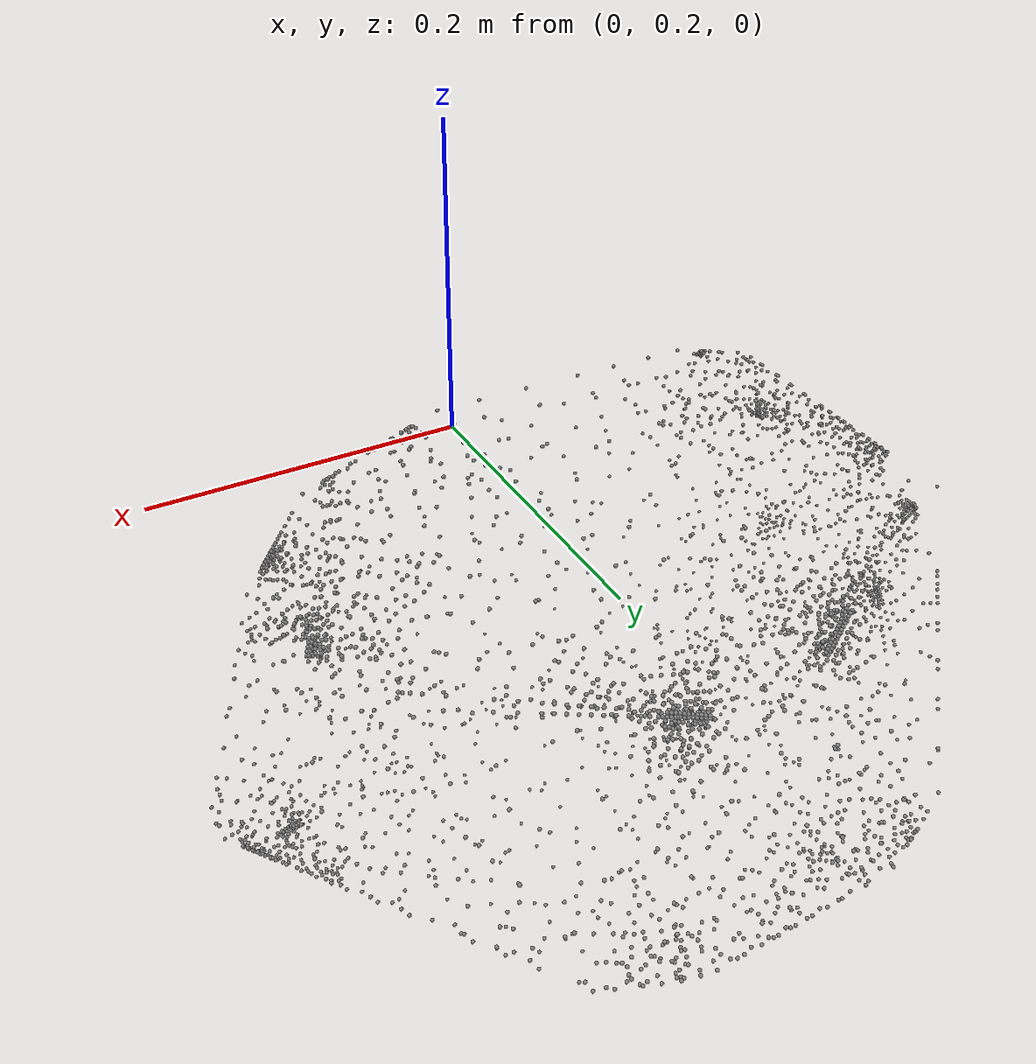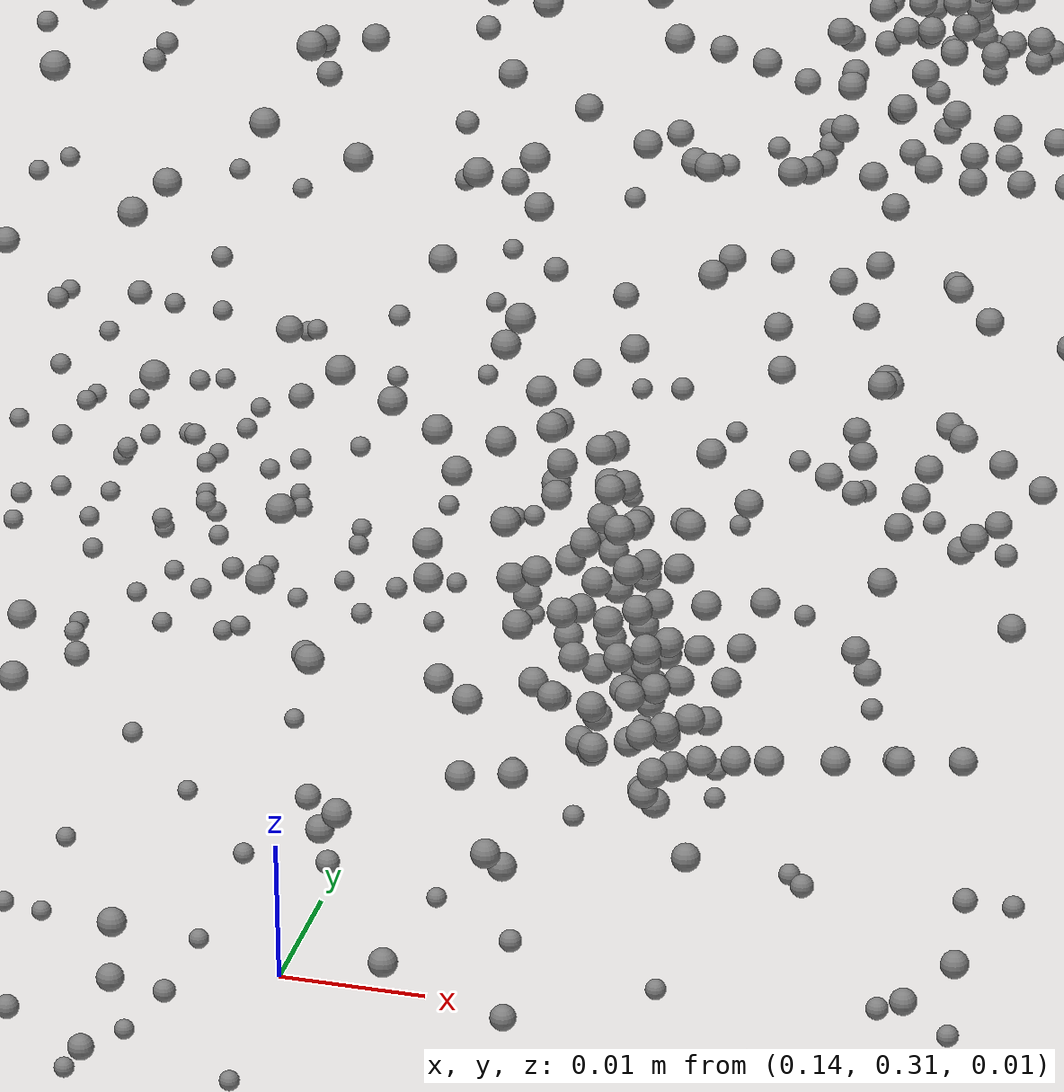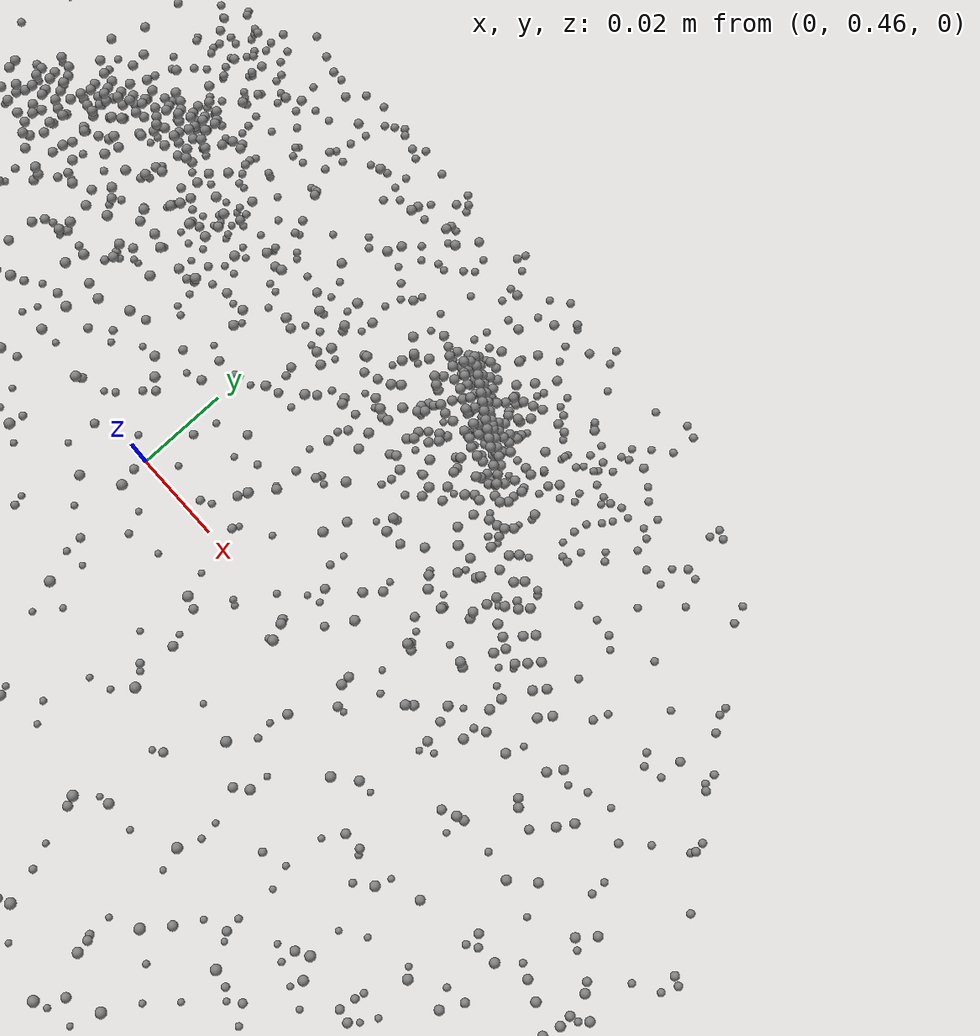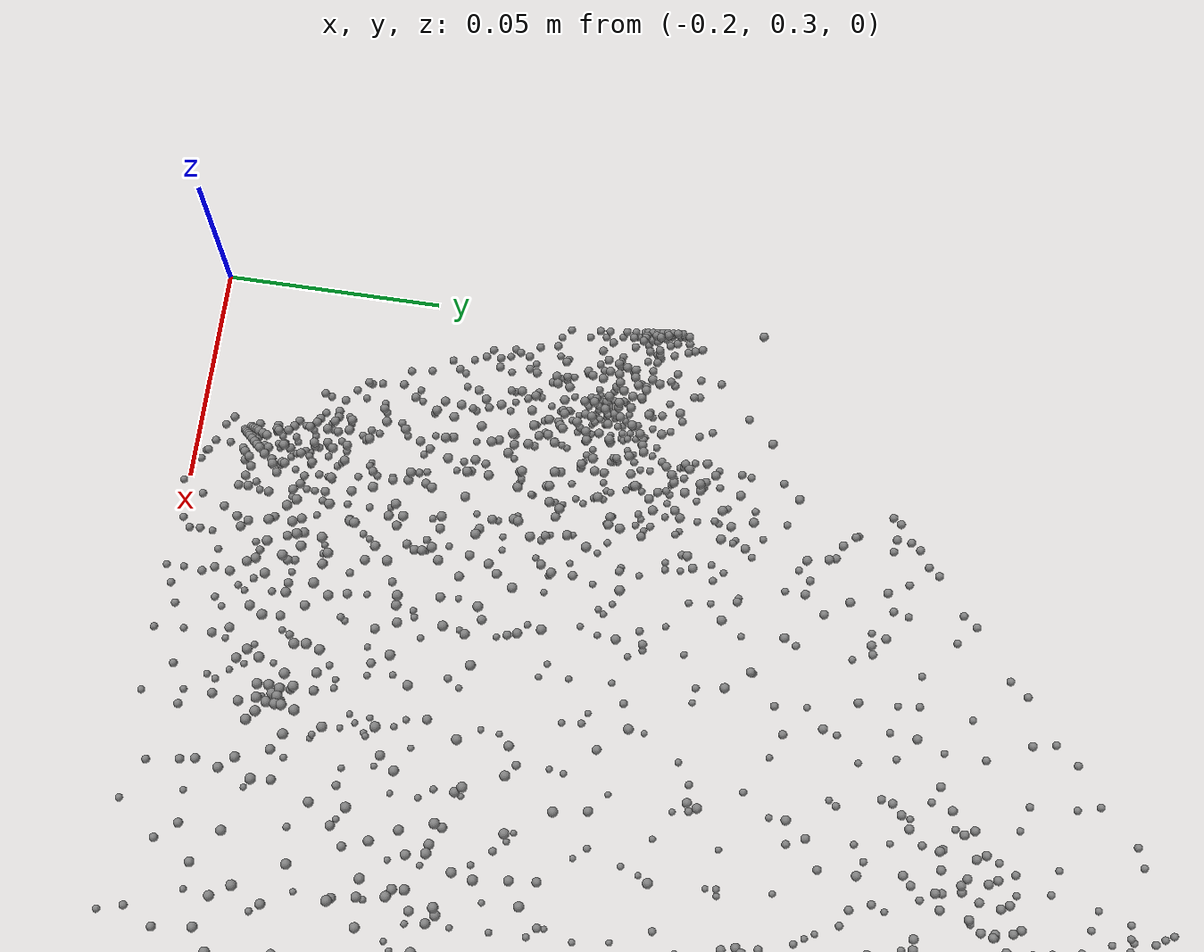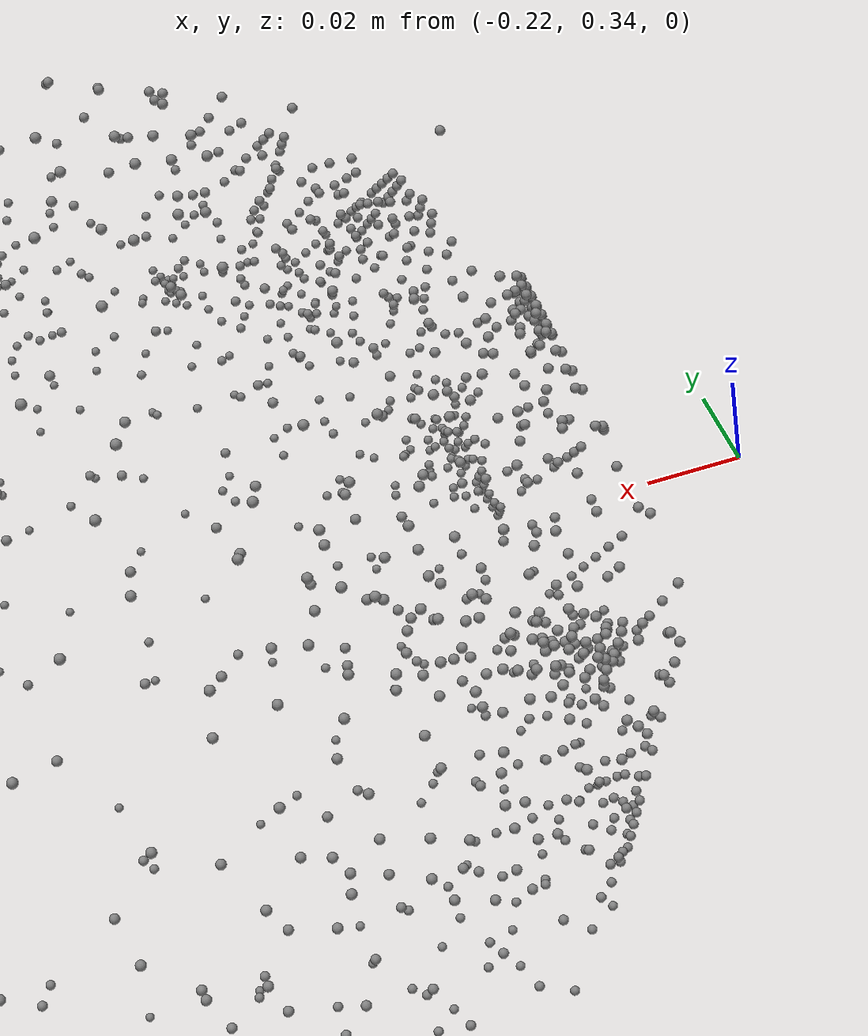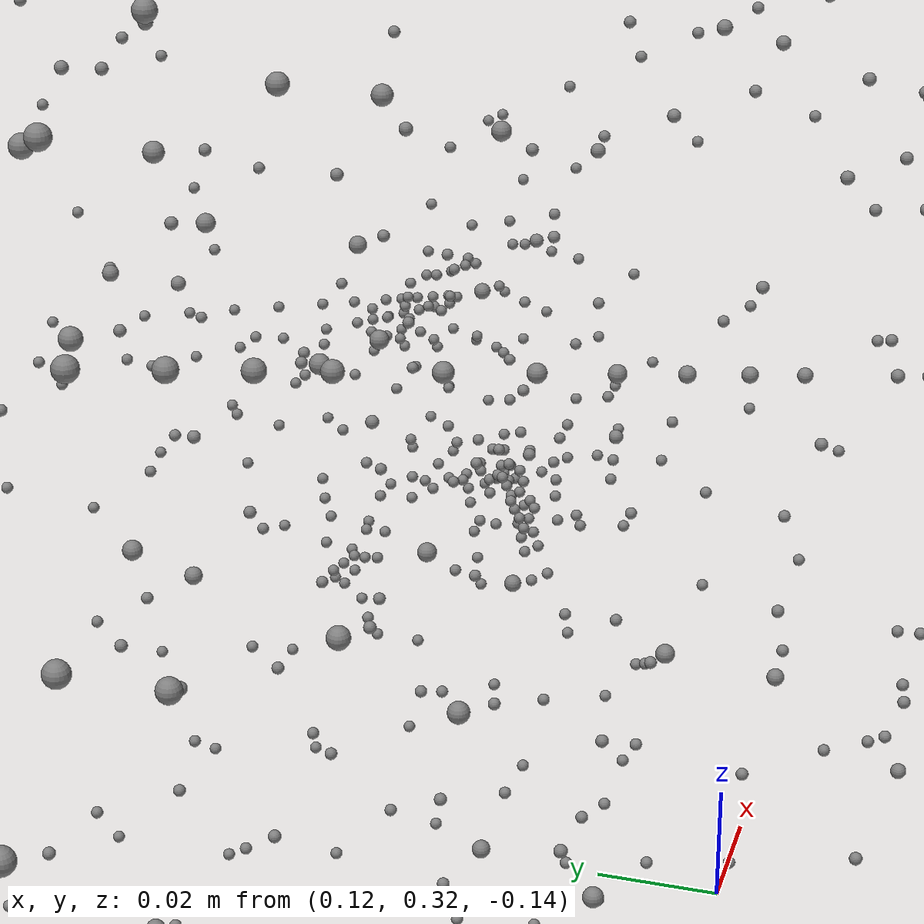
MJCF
<mujoco model="unnamed_model">
  <default>
    <default class="/"/>
  </default>
  <worldbody>
    <body name="point_mass_0">
      <freejoint name="//unnamed_joint_0"/>
      <geom name="point_mass_0" class="/" type="sphere" size="0.001" mass="0.01" pos="0.10703282058238983 0.53406941890716553 -0.04197557270526886"/>
    </body>
    <body name="point_mass_1">
      <freejoint name="//unnamed_joint_1"/>
      <geom name="point_mass_1" class="/" type="sphere" size="0.001" mass="0.01" pos="0.11945560574531555 0.49921905994415283 0.0056920661590993404"/>
    </body>
    <body name="point_mass_2">
      <freejoint name="//unnamed_joint_2"/>
      <geom name="point_mass_2" class="/" type="sphere" size="0.001" mass="0.01" pos="0.16882036626338959 0.43468517065048218 0.03934638574719429"/>
    </body>
    <body name="point_mass_3">
      <freejoint name="//unnamed_joint_3"/>
      <geom name="point_mass_3" class="/" type="sphere" size="0.001" mass="0.01" pos="0.15624520182609558 0.40573236346244812 -0.12857115268707275"/>
    </body>
    <body name="point_mass_4">
      <freejoint name="//unnamed_joint_4"/>
      <geom name="point_mass_4" class="/" type="sphere" size="0.001" mass="0.01" pos="0.09719560295343399 0.45517176389694214 -0.14395947754383087"/>
    </body>
    <body name="point_mass_5">
      <freejoint name="//unnamed_joint_5"/>
      <geom name="point_mass_5" class="/" type="sphere" size="0.001" mass="0.01" pos="0.091376475989818573 0.51718598604202271 -0.11203508824110031"/>
    </body>
    <body name="point_mass_6">
      <freejoint name="//unnamed_joint_6"/>
      <geom name="point_mass_6" class="/" type="sphere" size="0.001" mass="0.01" pos="0.10568462312221527 0.54229682683944702 -0.066680222749710083"/>
    </body>
    <body name="point_mass_7">
      <freejoint name="//unnamed_joint_7"/>
      <geom name="point_mass_7" class="/" type="sphere" size="0.001" mass="0.01" pos="0.20568975806236267 0.40057158470153809 -0.014949212782084942"/>
    </body>
    <body name="point_mass_8">
      <freejoint name="//unnamed_joint_8"/>
      <geom name="point_mass_8" class="/" type="sphere" size="0.001" mass="0.01" pos="0.22066901624202728 0.3806740939617157 -0.059936821460723877"/>
    </body>
    <body name="point_mass_9">
      <freejoint name="//unnamed_joint_9"/>
      <geom name="point_mass_9" class="/" type="sphere" size="0.001" mass="0.01" pos="0.1800612211227417 0.4239715039730072 0.035327702760696411"/>
    </body>
    <body name="point_mass_10">
      <freejoint name="//unnamed_joint_10"/>
      <geom name="point_mass_10" class="/" type="sphere" size="0.001" mass="0.01" pos="0.18713442981243134 0.40899598598480225 0.026492686942219734"/>
    </body>
    <body name="point_mass_11">
      <freejoint name="//unnamed_joint_11"/>
      <geom name="point_mass_11" class="/" type="sphere" size="0.001" mass="0.01" pos="0.17634311318397522 0.29953396320343018 -0.043063513934612274"/>
    </body>
    <body name="point_mass_12">
      <freejoint name="//unnamed_joint_12"/>
      <geom name="point_mass_12" class="/" type="sphere" size="0.001" mass="0.01" pos="0.16914142668247223 0.28444856405258179 -0.063917212188243866"/>
    </body>
    <body name="point_mass_13">
      <freejoint name="//unnamed_joint_13"/>
      <geom name="point_mass_13" class="/" type="sphere" size="0.001" mass="0.01" pos="0.14356248080730438 0.33412912487983704 0.072980187833309174"/>
    </body>
    <body name="point_mass_14">
      <freejoint name="//unnamed_joint_14"/>
      <geom name="point_mass_14" class="/" type="sphere" size="0.001" mass="0.01" pos="0.076019205152988434 0.34551587700843811 0.10669810324907303"/>
    </body>
    <body name="point_mass_15">
      <freejoint name="//unnamed_joint_15"/>
      <geom name="point_mass_15" class="/" type="sphere" size="0.001" mass="0.01" pos="0.11451078951358795 0.35006505250930786 0.096629083156585693"/>
    </body>
    <body name="point_mass_16">
      <freejoint name="//unnamed_joint_16"/>
      <geom name="point_mass_16" class="/" type="sphere" size="0.001" mass="0.01" pos="0.22016698122024536 0.38007667660713196 -0.072682321071624756"/>
    </body>
    <body name="point_mass_17">
      <freejoint name="//unnamed_joint_17"/>
      <geom name="point_mass_17" class="/" type="sphere" size="0.001" mass="0.01" pos="0.074678942561149597 0.49425670504570007 -0.12981322407722473"/>
    </body>
    <body name="point_mass_18">
      <freejoint name="//unnamed_joint_18"/>
      <geom name="point_mass_18" class="/" type="sphere" size="0.001" mass="0.01" pos="-0.094029724597930908 0.36321943998336792 0.093576304614543915"/>
    </body>
    <body name="point_mass_19">
      <freejoint name="//unnamed_joint_19"/>
      <geom name="point_mass_19" class="/" type="sphere" size="0.001" mass="0.01" pos="-0.10649677366018295 0.36218109726905823 0.089142069220542908"/>
    </body>
    <body name="point_mass_20">
      <freejoint name="//unnamed_joint_20"/>
      <geom name="point_mass_20" class="/" type="sphere" size="0.001" mass="0.01" pos="-0.10512246191501617 0.34718668460845947 0.095201633870601654"/>
    </body>
    <body name="point_mass_21">
      <freejoint name="//unnamed_joint_21"/>
      <geom name="point_mass_21" class="/" type="sphere" size="0.001" mass="0.01" pos="-0.092771589756011963 0.34836524724960327 0.098672017455101013"/>
    </body>
    <body name="point_mass_22">
      <freejoint name="//unnamed_joint_22"/>
      <geom name="point_mass_22" class="/" type="sphere" size="0.001" mass="0.01" pos="-0.079862482845783234 0.34879183769226074 0.10134454071521759"/>
    </body>
    <body name="point_mass_23">
      <freejoint name="//unnamed_joint_23"/>
      <geom name="point_mass_23" class="/" type="sphere" size="0.001" mass="0.01" pos="-0.07967974990606308 0.36321142315864563 0.097410038113594055"/>
    </body>
    <body name="point_mass_24">
      <freejoint name="//unnamed_joint_24"/>
      <geom name="point_mass_24" class="/" type="sphere" size="0.001" mass="0.01" pos="-0.066067829728126526 0.34378519654273987 0.10423062741756439"/>
    </body>
    <body name="point_mass_25">
      <freejoint name="//unnamed_joint_25"/>
      <geom name="point_mass_25" class="/" type="sphere" size="0.001" mass="0.01" pos="-0.13400737941265106 0.33116447925567627 0.071473486721515656"/>
    </body>
    <body name="point_mass_26">
      <freejoint name="//unnamed_joint_26"/>
      <geom name="point_mass_26" class="/" type="sphere" size="0.001" mass="0.01" pos="-0.11554688960313797 0.34628844261169434 0.089420855045318604"/>
    </body>
    <body name="point_mass_27">
      <freejoint name="//unnamed_joint_27"/>
      <geom name="point_mass_27" class="/" type="sphere" size="0.001" mass="0.01" pos="0.12514103949069977 0.34965762495994568 0.090736523270606995"/>
    </body>
    <body name="point_mass_28">
      <freejoint name="//unnamed_joint_28"/>
      <geom name="point_mass_28" class="/" type="sphere" size="0.001" mass="0.01" pos="0.058687817305326462 0.53185188770294189 0.0083494242280721664"/>
    </body>
    <body name="point_mass_29">
      <freejoint name="//unnamed_joint_29"/>
      <geom name="point_mass_29" class="/" type="sphere" size="0.001" mass="0.01" pos="0.016775423660874367 0.53161633014678955 0.037489727139472961"/>
    </body>
    <body name="point_mass_30">
      <freejoint name="//unnamed_joint_30"/>
      <geom name="point_mass_30" class="/" type="sphere" size="0.001" mass="0.01" pos="0.11604296416044235 0.36524346470832825 0.090879045426845551"/>
    </body>
    <body name="point_mass_31">
      <freejoint name="//unnamed_joint_31"/>
      <geom name="point_mass_31" class="/" type="sphere" size="0.001" mass="0.01" pos="0.10359995812177658 0.36601102352142334 0.095381893217563629"/>
    </body>
    <body name="point_mass_32">
      <freejoint name="//unnamed_joint_32"/>
      <geom name="point_mass_32" class="/" type="sphere" size="0.001" mass="0.01" pos="0.17239288985729218 0.3096197247505188 0.0042185145430266857"/>
    </body>
    <body name="point_mass_33">
      <freejoint name="//unnamed_joint_33"/>
      <geom name="point_mass_33" class="/" type="sphere" size="0.001" mass="0.01" pos="-0.12473142892122269 0.45939710736274719 0.038151081651449203"/>
    </body>
    <body name="point_mass_34">
      <freejoint name="//unnamed_joint_34"/>
      <geom name="point_mass_34" class="/" type="sphere" size="0.001" mass="0.01" pos="-0.11307509243488312 0.49731814861297607 0.0079710371792316437"/>
    </body>
    <body name="point_mass_35">
      <freejoint name="//unnamed_joint_35"/>
      <geom name="point_mass_35" class="/" type="sphere" size="0.001" mass="0.01" pos="-0.15082335472106934 0.43758994340896606 0.043305002152919769"/>
    </body>
    <body name="point_mass_36">
      <freejoint name="//unnamed_joint_36"/>
      <geom name="point_mass_36" class="/" type="sphere" size="0.001" mass="0.01" pos="-0.1932125985622406 0.42641684412956238 0.02559218555688858"/>
    </body>
    <body name="point_mass_37">
      <freejoint name="//unnamed_joint_37"/>
      <geom name="point_mass_37" class="/" type="sphere" size="0.001" mass="0.01" pos="-0.21600544452667236 0.38081726431846619 -0.079709000885486603"/>
    </body>
    <body name="point_mass_38">
      <freejoint name="//unnamed_joint_38"/>
      <geom name="point_mass_38" class="/" type="sphere" size="0.001" mass="0.01" pos="-0.10196744650602341 0.54020476341247559 -0.062350001186132431"/>
    </body>
    <body name="point_mass_39">
      <freejoint name="//unnamed_joint_39"/>
      <geom name="point_mass_39" class="/" type="sphere" size="0.001" mass="0.01" pos="-0.21840564906597137 0.37708708643913269 -0.057343993335962296"/>
    </body>
    <body name="point_mass_40">
      <freejoint name="//unnamed_joint_40"/>
      <geom name="point_mass_40" class="/" type="sphere" size="0.001" mass="0.01" pos="-0.13173511624336243 0.34377080202102661 0.075127549469470978"/>
    </body>
    <body name="point_mass_41">
      <freejoint name="//unnamed_joint_41"/>
      <geom name="point_mass_41" class="/" type="sphere" size="0.001" mass="0.01" pos="-0.09568343311548233 0.37768924236297607 0.087138421833515167"/>
    </body>
    <body name="point_mass_42">
      <freejoint name="//unnamed_joint_42"/>
      <geom name="point_mass_42" class="/" type="sphere" size="0.001" mass="0.01" pos="-0.13705898821353912 0.44051945209503174 0.045801054686307907"/>
    </body>
    <body name="point_mass_43">
      <freejoint name="//unnamed_joint_43"/>
      <geom name="point_mass_43" class="/" type="sphere" size="0.001" mass="0.01" pos="0.070019155740737915 0.53677970170974731 -0.0069837989285588264"/>
    </body>
    <body name="point_mass_44">
      <freejoint name="//unnamed_joint_44"/>
      <geom name="point_mass_44" class="/" type="sphere" size="0.001" mass="0.01" pos="-0.093209274113178253 0.53465175628662109 -0.08475165069103241"/>
    </body>
    <body name="point_mass_45">
      <freejoint name="//unnamed_joint_45"/>
      <geom name="point_mass_45" class="/" type="sphere" size="0.001" mass="0.01" pos="-0.087414748966693878 0.51792824268341064 -0.10646051913499832"/>
    </body>
    <body name="point_mass_46">
      <freejoint name="//unnamed_joint_46"/>
      <geom name="point_mass_46" class="/" type="sphere" size="0.001" mass="0.01" pos="-0.055394254624843597 0.55906915664672852 -0.069739900529384613"/>
    </body>
    <body name="point_mass_47">
      <freejoint name="//unnamed_joint_47"/>
      <geom name="point_mass_47" class="/" type="sphere" size="0.001" mass="0.01" pos="-0.077668726444244385 0.5510026216506958 -0.064350605010986328"/>
    </body>
    <body name="point_mass_48">
      <freejoint name="//unnamed_joint_48"/>
      <geom name="point_mass_48" class="/" type="sphere" size="0.001" mass="0.01" pos="-0.062849231064319611 0.5588797926902771 -0.054617319256067276"/>
    </body>
    <body name="point_mass_49">
      <freejoint name="//unnamed_joint_49"/>
      <geom name="point_mass_49" class="/" type="sphere" size="0.001" mass="0.01" pos="0.065935976803302765 0.56046587228775024 -0.058311924338340759"/>
    </body>
    <body name="point_mass_50">
      <freejoint name="//unnamed_joint_50"/>
      <geom name="point_mass_50" class="/" type="sphere" size="0.001" mass="0.01" pos="0.21797972917556763 0.38335087895393372 -0.081925936043262482"/>
    </body>
    <body name="point_mass_51">
      <freejoint name="//unnamed_joint_51"/>
      <geom name="point_mass_51" class="/" type="sphere" size="0.001" mass="0.01" pos="0.077009066939353943 0.3196539580821991 -0.14430588483810425"/>
    </body>
    <body name="point_mass_52">
      <freejoint name="//unnamed_joint_52"/>
      <geom name="point_mass_52" class="/" type="sphere" size="0.001" mass="0.01" pos="0.090265825390815735 0.3530101478099823 -0.15087246894836426"/>
    </body>
    <body name="point_mass_53">
      <freejoint name="//unnamed_joint_53"/>
      <geom name="point_mass_53" class="/" type="sphere" size="0.001" mass="0.01" pos="0.10284335911273956 0.30132701992988586 -0.13421986997127533"/>
    </body>
    <body name="point_mass_54">
      <freejoint name="//unnamed_joint_54"/>
      <geom name="point_mass_54" class="/" type="sphere" size="0.001" mass="0.01" pos="0.067416690289974213 0.34667748212814331 -0.15088219940662384"/>
    </body>
    <body name="point_mass_55">
      <freejoint name="//unnamed_joint_55"/>
      <geom name="point_mass_55" class="/" type="sphere" size="0.001" mass="0.01" pos="0.15026040375232697 0.2972676157951355 -0.10347043722867966"/>
    </body>
    <body name="point_mass_56">
      <freejoint name="//unnamed_joint_56"/>
      <geom name="point_mass_56" class="/" type="sphere" size="0.001" mass="0.01" pos="0.16148585081100464 0.2893754243850708 -0.085425287485122681"/>
    </body>
    <body name="point_mass_57">
      <freejoint name="//unnamed_joint_57"/>
      <geom name="point_mass_57" class="/" type="sphere" size="0.001" mass="0.01" pos="0.20488861203193665 0.37383028864860535 -0.090801626443862915"/>
    </body>
    <body name="point_mass_58">
      <freejoint name="//unnamed_joint_58"/>
      <geom name="point_mass_58" class="/" type="sphere" size="0.001" mass="0.01" pos="0.13522543013095856 0.306062251329422 -0.11898265779018402"/>
    </body>
    <body name="point_mass_59">
      <freejoint name="//unnamed_joint_59"/>
      <geom name="point_mass_59" class="/" type="sphere" size="0.001" mass="0.01" pos="0.057303767651319504 0.56014519929885864 -0.072933323681354523"/>
    </body>
    <body name="point_mass_60">
      <freejoint name="//unnamed_joint_60"/>
      <geom name="point_mass_60" class="/" type="sphere" size="0.001" mass="0.01" pos="0.062826260924339294 0.55450958013534546 -0.0804339200258255"/>
    </body>
    <body name="point_mass_61">
      <freejoint name="//unnamed_joint_61"/>
      <geom name="point_mass_61" class="/" type="sphere" size="0.001" mass="0.01" pos="0.044667646288871765 0.55692923069000244 -0.082419753074645996"/>
    </body>
    <body name="point_mass_62">
      <freejoint name="//unnamed_joint_62"/>
      <geom name="point_mass_62" class="/" type="sphere" size="0.001" mass="0.01" pos="0.096485868096351624 0.53566360473632812 -0.089540548622608185"/>
    </body>
    <body name="point_mass_63">
      <freejoint name="//unnamed_joint_63"/>
      <geom name="point_mass_63" class="/" type="sphere" size="0.001" mass="0.01" pos="0.062977038323879242 0.5267174243927002 -0.10940318554639816"/>
    </body>
    <body name="point_mass_64">
      <freejoint name="//unnamed_joint_64"/>
      <geom name="point_mass_64" class="/" type="sphere" size="0.001" mass="0.01" pos="0.072585389018058777 0.53214901685714722 -0.10282984375953674"/>
    </body>
    <body name="point_mass_65">
      <freejoint name="//unnamed_joint_65"/>
      <geom name="point_mass_65" class="/" type="sphere" size="0.001" mass="0.01" pos="-0.065201207995414734 0.51576811075210571 -0.11322827637195587"/>
    </body>
    <body name="point_mass_66">
      <freejoint name="//unnamed_joint_66"/>
      <geom name="point_mass_66" class="/" type="sphere" size="0.001" mass="0.01" pos="-0.070623166859149933 0.49552074074745178 -0.12501060962677002"/>
    </body>
    <body name="point_mass_67">
      <freejoint name="//unnamed_joint_67"/>
      <geom name="point_mass_67" class="/" type="sphere" size="0.001" mass="0.01" pos="0.067894786596298218 0.51383417844772339 -0.11835218966007233"/>
    </body>
    <body name="point_mass_68">
      <freejoint name="//unnamed_joint_68"/>
      <geom name="point_mass_68" class="/" type="sphere" size="0.001" mass="0.01" pos="0.052604265511035919 0.48476520180702209 -0.13414373993873596"/>
    </body>
    <body name="point_mass_69">
      <freejoint name="//unnamed_joint_69"/>
      <geom name="point_mass_69" class="/" type="sphere" size="0.001" mass="0.01" pos="-0.07269287109375 0.48120474815368652 -0.13190247118473053"/>
    </body>
    <body name="point_mass_70">
      <freejoint name="//unnamed_joint_70"/>
      <geom name="point_mass_70" class="/" type="sphere" size="0.001" mass="0.01" pos="0.053761694580316544 0.47136354446411133 -0.13946817815303802"/>
    </body>
    <body name="point_mass_71">
      <freejoint name="//unnamed_joint_71"/>
      <geom name="point_mass_71" class="/" type="sphere" size="0.001" mass="0.01" pos="-0.21484151482582092 0.38005200028419495 -0.041956834495067596"/>
    </body>
    <body name="point_mass_72">
      <freejoint name="//unnamed_joint_72"/>
      <geom name="point_mass_72" class="/" type="sphere" size="0.001" mass="0.01" pos="-0.16695877909660339 0.28481703996658325 -0.062802717089653015"/>
    </body>
    <body name="point_mass_73">
      <freejoint name="//unnamed_joint_73"/>
      <geom name="point_mass_73" class="/" type="sphere" size="0.001" mass="0.01" pos="-0.16412629187107086 0.30835804343223572 0.0045531149953603745"/>
    </body>
    <body name="point_mass_74">
      <freejoint name="//unnamed_joint_74"/>
      <geom name="point_mass_74" class="/" type="sphere" size="0.001" mass="0.01" pos="0.1341390460729599 0.34883400797843933 0.083870291709899902"/>
    </body>
    <body name="point_mass_75">
      <freejoint name="//unnamed_joint_75"/>
      <geom name="point_mass_75" class="/" type="sphere" size="0.001" mass="0.01" pos="0.10252600163221359 0.35080555081367493 0.10058147460222244"/>
    </body>
    <body name="point_mass_76">
      <freejoint name="//unnamed_joint_76"/>
      <geom name="point_mass_76" class="/" type="sphere" size="0.001" mass="0.01" pos="0.089947178959846497 0.35087636113166809 0.10358274728059769"/>
    </body>
    <body name="point_mass_77">
      <freejoint name="//unnamed_joint_77"/>
      <geom name="point_mass_77" class="/" type="sphere" size="0.001" mass="0.01" pos="0.13142506778240204 0.46304529905319214 0.036233488470315933"/>
    </body>
    <body name="point_mass_78">
      <freejoint name="//unnamed_joint_78"/>
      <geom name="point_mass_78" class="/" type="sphere" size="0.001" mass="0.01" pos="0.073592387139797211 0.36267068982124329 0.10274709761142731"/>
    </body>
    <body name="point_mass_79">
      <freejoint name="//unnamed_joint_79"/>
      <geom name="point_mass_79" class="/" type="sphere" size="0.001" mass="0.01" pos="-0.004246679600328207 0.53106009960174561 0.037751764059066772"/>
    </body>
    <body name="point_mass_80">
      <freejoint name="//unnamed_joint_80"/>
      <geom name="point_mass_80" class="/" type="sphere" size="0.001" mass="0.01" pos="0.17611019313335419 0.30257254838943481 -0.019129719585180283"/>
    </body>
    <body name="point_mass_81">
      <freejoint name="//unnamed_joint_81"/>
      <geom name="point_mass_81" class="/" type="sphere" size="0.001" mass="0.01" pos="0.21670420467853546 0.38363176584243774 -0.045991688966751099"/>
    </body>
    <body name="point_mass_82">
      <freejoint name="//unnamed_joint_82"/>
      <geom name="point_mass_82" class="/" type="sphere" size="0.001" mass="0.01" pos="0.15151672065258026 0.33342364430427551 0.060557786375284195"/>
    </body>
    <body name="point_mass_83">
      <freejoint name="//unnamed_joint_83"/>
      <geom name="point_mass_83" class="/" type="sphere" size="0.001" mass="0.01" pos="-0.16292281448841095 0.43062779307365417 0.041400257498025894"/>
    </body>
    <body name="point_mass_84">
      <freejoint name="//unnamed_joint_84"/>
      <geom name="point_mass_84" class="/" type="sphere" size="0.001" mass="0.01" pos="-0.12428821623325348 0.34544610977172852 0.082418523728847504"/>
    </body>
    <body name="point_mass_85">
      <freejoint name="//unnamed_joint_85"/>
      <geom name="point_mass_85" class="/" type="sphere" size="0.001" mass="0.01" pos="-0.1419670432806015 0.33052420616149902 0.059484243392944336"/>
    </body>
    <body name="point_mass_86">
      <freejoint name="//unnamed_joint_86"/>
      <geom name="point_mass_86" class="/" type="sphere" size="0.001" mass="0.01" pos="-0.10250395536422729 0.53268450498580933 -0.038268420845270157"/>
    </body>
    <body name="point_mass_87">
      <freejoint name="//unnamed_joint_87"/>
      <geom name="point_mass_87" class="/" type="sphere" size="0.001" mass="0.01" pos="0.070117898285388947 0.55584406852722168 -0.040301855653524399"/>
    </body>
    <body name="point_mass_88">
      <freejoint name="//unnamed_joint_88"/>
      <geom name="point_mass_88" class="/" type="sphere" size="0.001" mass="0.01" pos="-0.13214191794395447 0.41333851218223572 -0.13500942289829254"/>
    </body>
    <body name="point_mass_89">
      <freejoint name="//unnamed_joint_89"/>
      <geom name="point_mass_89" class="/" type="sphere" size="0.001" mass="0.01" pos="-0.15134130418300629 0.40559491515159607 -0.12502476572990417"/>
    </body>
    <body name="point_mass_90">
      <freejoint name="//unnamed_joint_90"/>
      <geom name="point_mass_90" class="/" type="sphere" size="0.001" mass="0.01" pos="-0.09286007285118103 0.45520102977752686 -0.139174684882164"/>
    </body>
    <body name="point_mass_91">
      <freejoint name="//unnamed_joint_91"/>
      <geom name="point_mass_91" class="/" type="sphere" size="0.001" mass="0.01" pos="-0.043395411223173141 0.55584341287612915 -0.079607240855693817"/>
    </body>
    <body name="point_mass_92">
      <freejoint name="//unnamed_joint_92"/>
      <geom name="point_mass_92" class="/" type="sphere" size="0.001" mass="0.01" pos="-0.060652069747447968 0.55398076772689819 -0.076333150267601013"/>
    </body>
    <body name="point_mass_93">
      <freejoint name="//unnamed_joint_93"/>
      <geom name="point_mass_93" class="/" type="sphere" size="0.001" mass="0.01" pos="0.030500886961817741 0.55413025617599487 -0.087399527430534363"/>
    </body>
    <body name="point_mass_94">
      <freejoint name="//unnamed_joint_94"/>
      <geom name="point_mass_94" class="/" type="sphere" size="0.001" mass="0.01" pos="-0.029861165210604668 0.55339306592941284 -0.08508794754743576"/>
    </body>
    <body name="point_mass_95">
      <freejoint name="//unnamed_joint_95"/>
      <geom name="point_mass_95" class="/" type="sphere" size="0.001" mass="0.01" pos="-0.073550134897232056 0.54126352071762085 -0.087347455322742462"/>
    </body>
    <body name="point_mass_96">
      <freejoint name="//unnamed_joint_96"/>
      <geom name="point_mass_96" class="/" type="sphere" size="0.001" mass="0.01" pos="-0.071079418063163757 0.53253859281539917 -0.098272673785686493"/>
    </body>
    <body name="point_mass_97">
      <freejoint name="//unnamed_joint_97"/>
      <geom name="point_mass_97" class="/" type="sphere" size="0.001" mass="0.01" pos="-0.085511639714241028 0.54734992980957031 -0.065354786813259125"/>
    </body>
    <body name="point_mass_98">
      <freejoint name="//unnamed_joint_98"/>
      <geom name="point_mass_98" class="/" type="sphere" size="0.001" mass="0.01" pos="0.08246014267206192 0.37217739224433899 -0.15510497987270355"/>
    </body>
    <body name="point_mass_99">
      <freejoint name="//unnamed_joint_99"/>
      <geom name="point_mass_99" class="/" type="sphere" size="0.001" mass="0.01" pos="0.088329441845417023 0.54857861995697021 -0.070489674806594849"/>
    </body>
    <body name="point_mass_100">
      <freejoint name="//unnamed_joint_100"/>
      <geom name="point_mass_100" class="/" type="sphere" size="0.001" mass="0.01" pos="0.048176184296607971 0.54976272583007812 -0.089522905647754669"/>
    </body>
    <body name="point_mass_101">
      <freejoint name="//unnamed_joint_101"/>
      <geom name="point_mass_101" class="/" type="sphere" size="0.001" mass="0.01" pos="0.068633928894996643 0.54863440990447998 -0.086438499391078949"/>
    </body>
    <body name="point_mass_102">
      <freejoint name="//unnamed_joint_102"/>
      <geom name="point_mass_102" class="/" type="sphere" size="0.001" mass="0.01" pos="-0.061319578438997269 0.5277513861656189 -0.10496374219655991"/>
    </body>
    <body name="point_mass_103">
      <freejoint name="//unnamed_joint_103"/>
      <geom name="point_mass_103" class="/" type="sphere" size="0.001" mass="0.01" pos="-0.035040624439716339 0.53590536117553711 -0.10000652819871902"/>
    </body>
    <body name="point_mass_104">
      <freejoint name="//unnamed_joint_104"/>
      <geom name="point_mass_104" class="/" type="sphere" size="0.001" mass="0.01" pos="-0.050100885331630707 0.5232396125793457 -0.10973095893859863"/>
    </body>
    <body name="point_mass_105">
      <freejoint name="//unnamed_joint_105"/>
      <geom name="point_mass_105" class="/" type="sphere" size="0.001" mass="0.01" pos="0.076076395809650421 0.48049211502075195 -0.13622564077377319"/>
    </body>
    <body name="point_mass_106">
      <freejoint name="//unnamed_joint_106"/>
      <geom name="point_mass_106" class="/" type="sphere" size="0.001" mass="0.01" pos="0.07615111768245697 0.46441233158111572 -0.14248707890510559"/>
    </body>
    <body name="point_mass_107">
      <freejoint name="//unnamed_joint_107"/>
      <geom name="point_mass_107" class="/" type="sphere" size="0.001" mass="0.01" pos="0.051158033311367035 0.51511532068252563 -0.11839465796947479"/>
    </body>
    <body name="point_mass_108">
      <freejoint name="//unnamed_joint_108"/>
      <geom name="point_mass_108" class="/" type="sphere" size="0.001" mass="0.01" pos="0.032246354967355728 0.54522258043289185 -0.094894468784332275"/>
    </body>
    <body name="point_mass_109">
      <freejoint name="//unnamed_joint_109"/>
      <geom name="point_mass_109" class="/" type="sphere" size="0.001" mass="0.01" pos="0.016352750360965729 0.54239565134048462 -0.097511962056159973"/>
    </body>
    <body name="point_mass_110">
      <freejoint name="//unnamed_joint_110"/>
      <geom name="point_mass_110" class="/" type="sphere" size="0.001" mass="0.01" pos="-0.0003282379184383899 0.54193961620330811 -0.097185000777244568"/>
    </body>
    <body name="point_mass_111">
      <freejoint name="//unnamed_joint_111"/>
      <geom name="point_mass_111" class="/" type="sphere" size="0.001" mass="0.01" pos="-0.072748728096485138 0.46508219838142395 -0.13790987432003021"/>
    </body>
    <body name="point_mass_112">
      <freejoint name="//unnamed_joint_112"/>
      <geom name="point_mass_112" class="/" type="sphere" size="0.001" mass="0.01" pos="-0.072738915681838989 0.44799590110778809 -0.14354893565177917"/>
    </body>
    <body name="point_mass_113">
      <freejoint name="//unnamed_joint_113"/>
      <geom name="point_mass_113" class="/" type="sphere" size="0.001" mass="0.01" pos="-0.1694234311580658 0.3019871711730957 -0.01848292164504528"/>
    </body>
    <body name="point_mass_114">
      <freejoint name="//unnamed_joint_114"/>
      <geom name="point_mass_114" class="/" type="sphere" size="0.001" mass="0.01" pos="-0.16003334522247314 0.29041510820388794 -0.084269061684608459"/>
    </body>
    <body name="point_mass_115">
      <freejoint name="//unnamed_joint_115"/>
      <geom name="point_mass_115" class="/" type="sphere" size="0.001" mass="0.01" pos="-0.20400935411453247 0.37214112281799316 -0.089038893580436707"/>
    </body>
    <body name="point_mass_116">
      <freejoint name="//unnamed_joint_116"/>
      <geom name="point_mass_116" class="/" type="sphere" size="0.001" mass="0.01" pos="-0.21793515980243683 0.37675842642784119 -0.070317015051841736"/>
    </body>
    <body name="point_mass_117">
      <freejoint name="//unnamed_joint_117"/>
      <geom name="point_mass_117" class="/" type="sphere" size="0.001" mass="0.01" pos="0.14162701368331909 0.34701886773109436 0.076364733278751373"/>
    </body>
    <body name="point_mass_118">
      <freejoint name="//unnamed_joint_118"/>
      <geom name="point_mass_118" class="/" type="sphere" size="0.001" mass="0.01" pos="0.15685723721981049 0.4414723813533783 0.041491199284791946"/>
    </body>
    <body name="point_mass_119">
      <freejoint name="//unnamed_joint_119"/>
      <geom name="point_mass_119" class="/" type="sphere" size="0.001" mass="0.01" pos="0.14391349256038666 0.44447946548461914 0.044227771461009979"/>
    </body>
    <body name="point_mass_120">
      <freejoint name="//unnamed_joint_120"/>
      <geom name="point_mass_120" class="/" type="sphere" size="0.001" mass="0.01" pos="0.089174002408981323 0.36550036072731018 0.099131442606449127"/>
    </body>
    <body name="point_mass_121">
      <freejoint name="//unnamed_joint_121"/>
      <geom name="point_mass_121" class="/" type="sphere" size="0.001" mass="0.01" pos="0.056985862553119659 0.35772120952606201 0.10397599637508392"/>
    </body>
    <body name="point_mass_122">
      <freejoint name="//unnamed_joint_122"/>
      <geom name="point_mass_122" class="/" type="sphere" size="0.001" mass="0.01" pos="-0.080692194402217865 0.37768641114234924 0.091101415455341339"/>
    </body>
    <body name="point_mass_123">
      <freejoint name="//unnamed_joint_123"/>
      <geom name="point_mass_123" class="/" type="sphere" size="0.001" mass="0.01" pos="-0.064073644578456879 0.36080041527748108 0.10029666125774384"/>
    </body>
    <body name="point_mass_124">
      <freejoint name="//unnamed_joint_124"/>
      <geom name="point_mass_124" class="/" type="sphere" size="0.001" mass="0.01" pos="0.0061550438404083252 0.52978956699371338 0.03869740292429924"/>
    </body>
    <body name="point_mass_125">
      <freejoint name="//unnamed_joint_125"/>
      <geom name="point_mass_125" class="/" type="sphere" size="0.001" mass="0.01" pos="0.16614024341106415 0.32043972611427307 0.024433383718132973"/>
    </body>
    <body name="point_mass_126">
      <freejoint name="//unnamed_joint_126"/>
      <geom name="point_mass_126" class="/" type="sphere" size="0.001" mass="0.01" pos="-0.15699450671672821 0.3182520866394043 0.024297719821333885"/>
    </body>
    <body name="point_mass_127">
      <freejoint name="//unnamed_joint_127"/>
      <geom name="point_mass_127" class="/" type="sphere" size="0.001" mass="0.01" pos="-0.20935894548892975 0.38803654909133911 -0.025752704590559006"/>
    </body>
    <body name="point_mass_128">
      <freejoint name="//unnamed_joint_128"/>
      <geom name="point_mass_128" class="/" type="sphere" size="0.001" mass="0.01" pos="-0.07326555997133255 0.547515869140625 -0.041057482361793518"/>
    </body>
    <body name="point_mass_129">
      <freejoint name="//unnamed_joint_129"/>
      <geom name="point_mass_129" class="/" type="sphere" size="0.001" mass="0.01" pos="-0.20073758065700531 0.380931556224823 -0.095580503344535828"/>
    </body>
    <body name="point_mass_130">
      <freejoint name="//unnamed_joint_130"/>
      <geom name="point_mass_130" class="/" type="sphere" size="0.001" mass="0.01" pos="-0.11223974823951721 0.42434734106063843 -0.14240512251853943"/>
    </body>
    <body name="point_mass_131">
      <freejoint name="//unnamed_joint_131"/>
      <geom name="point_mass_131" class="/" type="sphere" size="0.001" mass="0.01" pos="-0.092275813221931458 0.43654048442840576 -0.14470365643501282"/>
    </body>
    <body name="point_mass_132">
      <freejoint name="//unnamed_joint_132"/>
      <geom name="point_mass_132" class="/" type="sphere" size="0.001" mass="0.01" pos="-0.073323406279087067 0.43035250902175903 -0.14853368699550629"/>
    </body>
    <body name="point_mass_133">
      <freejoint name="//unnamed_joint_133"/>
      <geom name="point_mass_133" class="/" type="sphere" size="0.001" mass="0.01" pos="-0.04729345440864563 0.54898238182067871 -0.086447812616825104"/>
    </body>
    <body name="point_mass_134">
      <freejoint name="//unnamed_joint_134"/>
      <geom name="point_mass_134" class="/" type="sphere" size="0.001" mass="0.01" pos="-0.084922775626182556 0.53868204355239868 -0.084571056067943573"/>
    </body>
    <body name="point_mass_135">
      <freejoint name="//unnamed_joint_135"/>
      <geom name="point_mass_135" class="/" type="sphere" size="0.001" mass="0.01" pos="0.13626848161220551 0.41349348425865173 -0.13867844641208649"/>
    </body>
    <body name="point_mass_136">
      <freejoint name="//unnamed_joint_136"/>
      <geom name="point_mass_136" class="/" type="sphere" size="0.001" mass="0.01" pos="0.11641306430101395 0.4241715669631958 -0.14623703062534332"/>
    </body>
    <body name="point_mass_137">
      <freejoint name="//unnamed_joint_137"/>
      <geom name="point_mass_137" class="/" type="sphere" size="0.001" mass="0.01" pos="0.099129863083362579 0.39674791693687439 -0.15380242466926575"/>
    </body>
    <body name="point_mass_138">
      <freejoint name="//unnamed_joint_138"/>
      <geom name="point_mass_138" class="/" type="sphere" size="0.001" mass="0.01" pos="0.078269273042678833 0.39118260145187378 -0.15651614964008331"/>
    </body>
    <body name="point_mass_139">
      <freejoint name="//unnamed_joint_139"/>
      <geom name="point_mass_139" class="/" type="sphere" size="0.001" mass="0.01" pos="0.17587830126285553 0.38631677627563477 -0.11567388474941254"/>
    </body>
    <body name="point_mass_140">
      <freejoint name="//unnamed_joint_140"/>
      <geom name="point_mass_140" class="/" type="sphere" size="0.001" mass="0.01" pos="0.16069751977920532 0.39104220271110535 -0.12546996772289276"/>
    </body>
    <body name="point_mass_141">
      <freejoint name="//unnamed_joint_141"/>
      <geom name="point_mass_141" class="/" type="sphere" size="0.001" mass="0.01" pos="0.14555951952934265 0.38050097227096558 -0.13392914831638336"/>
    </body>
    <body name="point_mass_142">
      <freejoint name="//unnamed_joint_142"/>
      <geom name="point_mass_142" class="/" type="sphere" size="0.001" mass="0.01" pos="0.11111944168806076 0.36176919937133789 -0.14723558723926544"/>
    </body>
    <body name="point_mass_143">
      <freejoint name="//unnamed_joint_143"/>
      <geom name="point_mass_143" class="/" type="sphere" size="0.001" mass="0.01" pos="0.12093649804592133 0.34572064876556396 -0.13942676782608032"/>
    </body>
    <body name="point_mass_144">
      <freejoint name="//unnamed_joint_144"/>
      <geom name="point_mass_144" class="/" type="sphere" size="0.001" mass="0.01" pos="0.12961511313915253 0.37090697884559631 -0.14211949706077576"/>
    </body>
    <body name="point_mass_145">
      <freejoint name="//unnamed_joint_145"/>
      <geom name="point_mass_145" class="/" type="sphere" size="0.001" mass="0.01" pos="0.13911959528923035 0.3580901026725769 -0.1339307427406311"/>
    </body>
    <body name="point_mass_146">
      <freejoint name="//unnamed_joint_146"/>
      <geom name="point_mass_146" class="/" type="sphere" size="0.001" mass="0.01" pos="0.101528599858284 0.33391126990318298 -0.14293582737445831"/>
    </body>
    <body name="point_mass_147">
      <freejoint name="//unnamed_joint_147"/>
      <geom name="point_mass_147" class="/" type="sphere" size="0.001" mass="0.01" pos="0.10305939614772797 0.37852075695991516 -0.15219919383525848"/>
    </body>
    <body name="point_mass_148">
      <freejoint name="//unnamed_joint_148"/>
      <geom name="point_mass_148" class="/" type="sphere" size="0.001" mass="0.01" pos="0.12248007208108902 0.38662424683570862 -0.14651444554328918"/>
    </body>
    <body name="point_mass_149">
      <freejoint name="//unnamed_joint_149"/>
      <geom name="point_mass_149" class="/" type="sphere" size="0.001" mass="0.01" pos="0.053246010094881058 0.54194486141204834 -0.096321195363998413"/>
    </body>
    <body name="point_mass_150">
      <freejoint name="//unnamed_joint_150"/>
      <geom name="point_mass_150" class="/" type="sphere" size="0.001" mass="0.01" pos="0.087419427931308746 0.53955084085464478 -0.089311674237251282"/>
    </body>
    <body name="point_mass_151">
      <freejoint name="//unnamed_joint_151"/>
      <geom name="point_mass_151" class="/" type="sphere" size="0.001" mass="0.01" pos="-0.062597967684268951 0.52221673727035522 -0.1088869571685791"/>
    </body>
    <body name="point_mass_152">
      <freejoint name="//unnamed_joint_152"/>
      <geom name="point_mass_152" class="/" type="sphere" size="0.001" mass="0.01" pos="-0.075324036180973053 0.39277011156082153 -0.15386343002319336"/>
    </body>
    <body name="point_mass_153">
      <freejoint name="//unnamed_joint_153"/>
      <geom name="point_mass_153" class="/" type="sphere" size="0.001" mass="0.01" pos="0.076653510332107544 0.4102013111114502 -0.15552957355976105"/>
    </body>
    <body name="point_mass_154">
      <freejoint name="//unnamed_joint_154"/>
      <geom name="point_mass_154" class="/" type="sphere" size="0.001" mass="0.01" pos="0.075390100479125977 0.44723907113075256 -0.14799368381500244"/>
    </body>
    <body name="point_mass_155">
      <freejoint name="//unnamed_joint_155"/>
      <geom name="point_mass_155" class="/" type="sphere" size="0.001" mass="0.01" pos="0.075473509728908539 0.42912459373474121 -0.1525019109249115"/>
    </body>
    <body name="point_mass_156">
      <freejoint name="//unnamed_joint_156"/>
      <geom name="point_mass_156" class="/" type="sphere" size="0.001" mass="0.01" pos="0.050715930759906769 0.49639067053794861 -0.12825445830821991"/>
    </body>
    <body name="point_mass_157">
      <freejoint name="//unnamed_joint_157"/>
      <geom name="point_mass_157" class="/" type="sphere" size="0.001" mass="0.01" pos="-0.049317527562379837 0.51671230792999268 -0.11426686495542526"/>
    </body>
    <body name="point_mass_158">
      <freejoint name="//unnamed_joint_158"/>
      <geom name="point_mass_158" class="/" type="sphere" size="0.001" mass="0.01" pos="0.051700599491596222 0.5218430757522583 -0.1136801615357399"/>
    </body>
    <body name="point_mass_159">
      <freejoint name="//unnamed_joint_159"/>
      <geom name="point_mass_159" class="/" type="sphere" size="0.001" mass="0.01" pos="-0.016455184668302536 0.54196351766586304 -0.096026748418807983"/>
    </body>
    <body name="point_mass_160">
      <freejoint name="//unnamed_joint_160"/>
      <geom name="point_mass_160" class="/" type="sphere" size="0.001" mass="0.01" pos="-0.018148483708500862 0.30087530612945557 -0.13996089994907379"/>
    </body>
    <body name="point_mass_161">
      <freejoint name="//unnamed_joint_161"/>
      <geom name="point_mass_161" class="/" type="sphere" size="0.001" mass="0.01" pos="-0.10038100928068161 0.30308324098587036 -0.13527999818325043"/>
    </body>
    <body name="point_mass_162">
      <freejoint name="//unnamed_joint_162"/>
      <geom name="point_mass_162" class="/" type="sphere" size="0.001" mass="0.01" pos="-0.074323534965515137 0.32105433940887451 -0.14417438209056854"/>
    </body>
    <body name="point_mass_163">
      <freejoint name="//unnamed_joint_163"/>
      <geom name="point_mass_163" class="/" type="sphere" size="0.001" mass="0.01" pos="-0.11940282583236694 0.38783231377601624 -0.14291732013225555"/>
    </body>
    <body name="point_mass_164">
      <freejoint name="//unnamed_joint_164"/>
      <geom name="point_mass_164" class="/" type="sphere" size="0.001" mass="0.01" pos="-0.10070175677537918 0.3801979124546051 -0.14951729774475098"/>
    </body>
    <body name="point_mass_165">
      <freejoint name="//unnamed_joint_165"/>
      <geom name="point_mass_165" class="/" type="sphere" size="0.001" mass="0.01" pos="-0.096169739961624146 0.39806964993476868 -0.15084092319011688"/>
    </body>
    <body name="point_mass_166">
      <freejoint name="//unnamed_joint_166"/>
      <geom name="point_mass_166" class="/" type="sphere" size="0.001" mass="0.01" pos="-0.17218132317066193 0.29922038316726685 -0.04145372286438942"/>
    </body>
    <body name="point_mass_167">
      <freejoint name="//unnamed_joint_167"/>
      <geom name="point_mass_167" class="/" type="sphere" size="0.001" mass="0.01" pos="0.11026415228843689 0.41133537888526917 0.071800157427787781"/>
    </body>
    <body name="point_mass_168">
      <freejoint name="//unnamed_joint_168"/>
      <geom name="point_mass_168" class="/" type="sphere" size="0.001" mass="0.01" pos="0.10718987137079239 0.39569959044456482 0.080809585750102997"/>
    </body>
    <body name="point_mass_169">
      <freejoint name="//unnamed_joint_169"/>
      <geom name="point_mass_169" class="/" type="sphere" size="0.001" mass="0.01" pos="0.11837241798639297 0.38004171848297119 0.084005109965801239"/>
    </body>
    <body name="point_mass_170">
      <freejoint name="//unnamed_joint_170"/>
      <geom name="point_mass_170" class="/" type="sphere" size="0.001" mass="0.01" pos="0.12545523047447205 0.41077026724815369 0.067252352833747864"/>
    </body>
    <body name="point_mass_171">
      <freejoint name="//unnamed_joint_171"/>
      <geom name="point_mass_171" class="/" type="sphere" size="0.001" mass="0.01" pos="0.073392070829868317 0.37864434719085693 0.095989078283309937"/>
    </body>
    <body name="point_mass_172">
      <freejoint name="//unnamed_joint_172"/>
      <geom name="point_mass_172" class="/" type="sphere" size="0.001" mass="0.01" pos="0.089890114963054657 0.38035333156585693 0.092931538820266724"/>
    </body>
    <body name="point_mass_173">
      <freejoint name="//unnamed_joint_173"/>
      <geom name="point_mass_173" class="/" type="sphere" size="0.001" mass="0.01" pos="-0.064445242285728455 0.37637448310852051 0.093994282186031342"/>
    </body>
    <body name="point_mass_174">
      <freejoint name="//unnamed_joint_174"/>
      <geom name="point_mass_174" class="/" type="sphere" size="0.001" mass="0.01" pos="-0.061676662415266037 0.53411358594894409 -0.005079186987131834"/>
    </body>
    <body name="point_mass_175">
      <freejoint name="//unnamed_joint_175"/>
      <geom name="point_mass_175" class="/" type="sphere" size="0.001" mass="0.01" pos="-0.15911966562271118 0.35620343685150146 -0.11696530878543854"/>
    </body>
    <body name="point_mass_176">
      <freejoint name="//unnamed_joint_176"/>
      <geom name="point_mass_176" class="/" type="sphere" size="0.001" mass="0.01" pos="-0.13361050188541412 0.30774053931236267 -0.1186271458864212"/>
    </body>
    <body name="point_mass_177">
      <freejoint name="//unnamed_joint_177"/>
      <geom name="point_mass_177" class="/" type="sphere" size="0.001" mass="0.01" pos="-0.093787148594856262 0.41726851463317871 -0.14894714951515198"/>
    </body>
    <body name="point_mass_178">
      <freejoint name="//unnamed_joint_178"/>
      <geom name="point_mass_178" class="/" type="sphere" size="0.001" mass="0.01" pos="-0.052524775266647339 0.54171937704086304 -0.092745862901210785"/>
    </body>
    <body name="point_mass_179">
      <freejoint name="//unnamed_joint_179"/>
      <geom name="point_mass_179" class="/" type="sphere" size="0.001" mass="0.01" pos="-0.066751435399055481 0.54792106151580811 -0.081860922276973724"/>
    </body>
    <body name="point_mass_180">
      <freejoint name="//unnamed_joint_180"/>
      <geom name="point_mass_180" class="/" type="sphere" size="0.001" mass="0.01" pos="0.13995489478111267 0.39603003859519958 -0.13759396970272064"/>
    </body>
    <body name="point_mass_181">
      <freejoint name="//unnamed_joint_181"/>
      <geom name="point_mass_181" class="/" type="sphere" size="0.001" mass="0.01" pos="0.11856706440448761 0.40478411316871643 -0.14761392772197723"/>
    </body>
    <body name="point_mass_182">
      <freejoint name="//unnamed_joint_182"/>
      <geom name="point_mass_182" class="/" type="sphere" size="0.001" mass="0.01" pos="0.11829467862844467 0.31785768270492554 -0.13211469352245331"/>
    </body>
    <body name="point_mass_183">
      <freejoint name="//unnamed_joint_183"/>
      <geom name="point_mass_183" class="/" type="sphere" size="0.001" mass="0.01" pos="0.14891257882118225 0.34612825512886047 -0.12366572767496109"/>
    </body>
    <body name="point_mass_184">
      <freejoint name="//unnamed_joint_184"/>
      <geom name="point_mass_184" class="/" type="sphere" size="0.001" mass="0.01" pos="0.16033594310283661 0.35582086443901062 -0.11919631808996201"/>
    </body>
    <body name="point_mass_185">
      <freejoint name="//unnamed_joint_185"/>
      <geom name="point_mass_185" class="/" type="sphere" size="0.001" mass="0.01" pos="0.20205606520175934 0.38205543160438538 -0.097017094492912292"/>
    </body>
    <body name="point_mass_186">
      <freejoint name="//unnamed_joint_186"/>
      <geom name="point_mass_186" class="/" type="sphere" size="0.001" mass="0.01" pos="0.15308277308940887 0.36713925004005432 -0.1274615079164505"/>
    </body>
    <body name="point_mass_187">
      <freejoint name="//unnamed_joint_187"/>
      <geom name="point_mass_187" class="/" type="sphere" size="0.001" mass="0.01" pos="0.075174018740653992 0.54171699285507202 -0.091882370412349701"/>
    </body>
    <body name="point_mass_188">
      <freejoint name="//unnamed_joint_188"/>
      <geom name="point_mass_188" class="/" type="sphere" size="0.001" mass="0.01" pos="-0.074110932648181915 0.41177254915237427 -0.15220420062541962"/>
    </body>
    <body name="point_mass_189">
      <freejoint name="//unnamed_joint_189"/>
      <geom name="point_mass_189" class="/" type="sphere" size="0.001" mass="0.01" pos="0.096936918795108795 0.41621074080467224 -0.15265476703643799"/>
    </body>
    <body name="point_mass_190">
      <freejoint name="//unnamed_joint_190"/>
      <geom name="point_mass_190" class="/" type="sphere" size="0.001" mass="0.01" pos="0.054721280932426453 0.45629477500915527 -0.14453575015068054"/>
    </body>
    <body name="point_mass_191">
      <freejoint name="//unnamed_joint_191"/>
      <geom name="point_mass_191" class="/" type="sphere" size="0.001" mass="0.01" pos="0.035253230482339859 0.53586041927337646 -0.10253108292818069"/>
    </body>
    <body name="point_mass_192">
      <freejoint name="//unnamed_joint_192"/>
      <geom name="point_mass_192" class="/" type="sphere" size="0.001" mass="0.01" pos="-0.038525104522705078 0.52574276924133301 -0.10828237235546112"/>
    </body>
    <body name="point_mass_193">
      <freejoint name="//unnamed_joint_193"/>
      <geom name="point_mass_193" class="/" type="sphere" size="0.001" mass="0.01" pos="0.038989678025245667 0.52504837512969971 -0.11111394315958023"/>
    </body>
    <body name="point_mass_194">
      <freejoint name="//unnamed_joint_194"/>
      <geom name="point_mass_194" class="/" type="sphere" size="0.001" mass="0.01" pos="0.022574491798877716 0.30046415328979492 -0.1383863240480423"/>
    </body>
    <body name="point_mass_195">
      <freejoint name="//unnamed_joint_195"/>
      <geom name="point_mass_195" class="/" type="sphere" size="0.001" mass="0.01" pos="-0.042913462966680527 0.32353702187538147 -0.14685523509979248"/>
    </body>
    <body name="point_mass_196">
      <freejoint name="//unnamed_joint_196"/>
      <geom name="point_mass_196" class="/" type="sphere" size="0.001" mass="0.01" pos="-0.080023281276226044 0.37400975823402405 -0.15264365077018738"/>
    </body>
    <body name="point_mass_197">
      <freejoint name="//unnamed_joint_197"/>
      <geom name="point_mass_197" class="/" type="sphere" size="0.001" mass="0.01" pos="-0.064841173589229584 0.34828948974609375 -0.149470254778862"/>
    </body>
    <body name="point_mass_198">
      <freejoint name="//unnamed_joint_198"/>
      <geom name="point_mass_198" class="/" type="sphere" size="0.001" mass="0.01" pos="-0.1367780864238739 0.35920491814613342 -0.13159720599651337"/>
    </body>
    <body name="point_mass_199">
      <freejoint name="//unnamed_joint_199"/>
      <geom name="point_mass_199" class="/" type="sphere" size="0.001" mass="0.01" pos="-0.1162835955619812 0.31969684362411499 -0.13151265680789948"/>
    </body>
    <body name="point_mass_200">
      <freejoint name="//unnamed_joint_200"/>
      <geom name="point_mass_200" class="/" type="sphere" size="0.001" mass="0.01" pos="-0.14923989772796631 0.29871419072151184 -0.10234023630619049"/>
    </body>
    <body name="point_mass_201">
      <freejoint name="//unnamed_joint_201"/>
      <geom name="point_mass_201" class="/" type="sphere" size="0.001" mass="0.01" pos="-0.11475961655378342 0.40553221106529236 -0.14395029842853546"/>
    </body>
    <body name="point_mass_202">
      <freejoint name="//unnamed_joint_202"/>
      <geom name="point_mass_202" class="/" type="sphere" size="0.001" mass="0.01" pos="0.12882913649082184 0.42730540037155151 0.057795584201812744"/>
    </body>
    <body name="point_mass_203">
      <freejoint name="//unnamed_joint_203"/>
      <geom name="point_mass_203" class="/" type="sphere" size="0.001" mass="0.01" pos="0.10497467964887619 0.38071420788764954 0.088768996298313141"/>
    </body>
    <body name="point_mass_204">
      <freejoint name="//unnamed_joint_204"/>
      <geom name="point_mass_204" class="/" type="sphere" size="0.001" mass="0.01" pos="-0.069591976702213287 0.53975647687911987 -0.022776022553443909"/>
    </body>
    <body name="point_mass_205">
      <freejoint name="//unnamed_joint_205"/>
      <geom name="point_mass_205" class="/" type="sphere" size="0.001" mass="0.01" pos="-0.049452416598796844 0.52945655584335327 0.010322589427232742"/>
    </body>
    <body name="point_mass_206">
      <freejoint name="//unnamed_joint_206"/>
      <geom name="point_mass_206" class="/" type="sphere" size="0.001" mass="0.01" pos="-0.1474393904209137 0.34700435400009155 -0.12193805724382401"/>
    </body>
    <body name="point_mass_207">
      <freejoint name="//unnamed_joint_207"/>
      <geom name="point_mass_207" class="/" type="sphere" size="0.001" mass="0.01" pos="-0.15150372684001923 0.36794939637184143 -0.12446209788322449"/>
    </body>
    <body name="point_mass_208">
      <freejoint name="//unnamed_joint_208"/>
      <geom name="point_mass_208" class="/" type="sphere" size="0.001" mass="0.01" pos="0.16971655189990997 0.36491286754608154 -0.11518027633428574"/>
    </body>
    <body name="point_mass_209">
      <freejoint name="//unnamed_joint_209"/>
      <geom name="point_mass_209" class="/" type="sphere" size="0.001" mass="0.01" pos="0.18909373879432678 0.38256385922431946 -0.10610155761241913"/>
    </body>
    <body name="point_mass_210">
      <freejoint name="//unnamed_joint_210"/>
      <geom name="point_mass_210" class="/" type="sphere" size="0.001" mass="0.01" pos="0.096244141459465027 0.43600612878799438 -0.14909756183624268"/>
    </body>
    <body name="point_mass_211">
      <freejoint name="//unnamed_joint_211"/>
      <geom name="point_mass_211" class="/" type="sphere" size="0.001" mass="0.01" pos="0.046480242162942886 0.32272940874099731 -0.1459396630525589"/>
    </body>
    <body name="point_mass_212">
      <freejoint name="//unnamed_joint_212"/>
      <geom name="point_mass_212" class="/" type="sphere" size="0.001" mass="0.01" pos="-0.08754933625459671 0.35498428344726562 -0.1490454375743866"/>
    </body>
    <body name="point_mass_213">
      <freejoint name="//unnamed_joint_213"/>
      <geom name="point_mass_213" class="/" type="sphere" size="0.001" mass="0.01" pos="-0.10830510407686234 0.36374199390411377 -0.14507988095283508"/>
    </body>
    <body name="point_mass_214">
      <freejoint name="//unnamed_joint_214"/>
      <geom name="point_mass_214" class="/" type="sphere" size="0.001" mass="0.01" pos="-0.11865656822919846 0.34798625111579895 -0.13724692165851593"/>
    </body>
    <body name="point_mass_215">
      <freejoint name="//unnamed_joint_215"/>
      <geom name="point_mass_215" class="/" type="sphere" size="0.001" mass="0.01" pos="-0.1574389636516571 0.39108920097351074 -0.12231298536062241"/>
    </body>
    <body name="point_mass_216">
      <freejoint name="//unnamed_joint_216"/>
      <geom name="point_mass_216" class="/" type="sphere" size="0.001" mass="0.01" pos="-0.14301759004592896 0.38129675388336182 -0.130271315574646"/>
    </body>
    <body name="point_mass_217">
      <freejoint name="//unnamed_joint_217"/>
      <geom name="point_mass_217" class="/" type="sphere" size="0.001" mass="0.01" pos="-0.12672555446624756 0.37227308750152588 -0.13897015154361725"/>
    </body>
    <body name="point_mass_218">
      <freejoint name="//unnamed_joint_218"/>
      <geom name="point_mass_218" class="/" type="sphere" size="0.001" mass="0.01" pos="-0.17295239865779877 0.38588663935661316 -0.11354000121355057"/>
    </body>
    <body name="point_mass_219">
      <freejoint name="//unnamed_joint_219"/>
      <geom name="point_mass_219" class="/" type="sphere" size="0.001" mass="0.01" pos="-0.18704944849014282 0.38173243403434753 -0.10454437136650085"/>
    </body>
    <body name="point_mass_220">
      <freejoint name="//unnamed_joint_220"/>
      <geom name="point_mass_220" class="/" type="sphere" size="0.001" mass="0.01" pos="-0.17281014337954878 0.37621106973180141 -0.11252323835287448"/>
    </body>
    <body name="point_mass_221">
      <freejoint name="//unnamed_joint_221"/>
      <geom name="point_mass_221" class="/" type="sphere" size="0.001" mass="0.01" pos="-0.16232297279546318 0.39558016305489618 -0.1191887874476469"/>
    </body>
    <body name="point_mass_222">
      <freejoint name="//unnamed_joint_222"/>
      <geom name="point_mass_222" class="/" type="sphere" size="0.001" mass="0.01" pos="-0.1639463214496816 0.39930128155575556 -0.11751113388829262"/>
    </body>
    <body name="point_mass_223">
      <freejoint name="//unnamed_joint_223"/>
      <geom name="point_mass_223" class="/" type="sphere" size="0.001" mass="0.01" pos="-0.18780539786959449 0.38738854222781532 -0.1032891528701433"/>
    </body>
    <body name="point_mass_224">
      <freejoint name="//unnamed_joint_224"/>
      <geom name="point_mass_224" class="/" type="sphere" size="0.001" mass="0.01" pos="-0.17614702621121509 0.39320951954102801 -0.11023850570802685"/>
    </body>
    <body name="point_mass_225">
      <freejoint name="//unnamed_joint_225"/>
      <geom name="point_mass_225" class="/" type="sphere" size="0.001" mass="0.01" pos="-0.1106773254558332 0.51276842885937035 -0.084034321596731729"/>
    </body>
    <body name="point_mass_226">
      <freejoint name="//unnamed_joint_226"/>
      <geom name="point_mass_226" class="/" type="sphere" size="0.001" mass="0.01" pos="-0.20227063605429965 0.39802372341660092 -0.080273023599217813"/>
    </body>
    <body name="point_mass_227">
      <freejoint name="//unnamed_joint_227"/>
      <geom name="point_mass_227" class="/" type="sphere" size="0.001" mass="0.01" pos="-0.19031562694315635 0.39353072184683902 -0.096581105070444165"/>
    </body>
    <body name="point_mass_228">
      <freejoint name="//unnamed_joint_228"/>
      <geom name="point_mass_228" class="/" type="sphere" size="0.001" mass="0.01" pos="-0.13886518795492511 0.45572948226512483 -0.10152081210272124"/>
    </body>
    <body name="point_mass_229">
      <freejoint name="//unnamed_joint_229"/>
      <geom name="point_mass_229" class="/" type="sphere" size="0.001" mass="0.01" pos="-0.17108776771852641 0.41677540221862058 -0.098427153292681174"/>
    </body>
    <body name="point_mass_230">
      <freejoint name="//unnamed_joint_230"/>
      <geom name="point_mass_230" class="/" type="sphere" size="0.001" mass="0.01" pos="-0.16907671651810552 0.33435367267737426 0.012749429749456122"/>
    </body>
    <body name="point_mass_231">
      <freejoint name="//unnamed_joint_231"/>
      <geom name="point_mass_231" class="/" type="sphere" size="0.001" mass="0.01" pos="-0.18948390334844589 0.34420502185821533 -0.018701859749853611"/>
    </body>
    <body name="point_mass_232">
      <freejoint name="//unnamed_joint_232"/>
      <geom name="point_mass_232" class="/" type="sphere" size="0.001" mass="0.01" pos="-0.17680509760975838 0.32628153264522552 -0.0070743723772466183"/>
    </body>
    <body name="point_mass_233">
      <freejoint name="//unnamed_joint_233"/>
      <geom name="point_mass_233" class="/" type="sphere" size="0.001" mass="0.01" pos="-0.18631370381939619 0.35732487071396929 -0.0037258452700098255"/>
    </body>
    <body name="point_mass_234">
      <freejoint name="//unnamed_joint_234"/>
      <geom name="point_mass_234" class="/" type="sphere" size="0.001" mass="0.01" pos="-0.18509407755710328 0.36732887710237389 0.0049373815764415727"/>
    </body>
    <body name="point_mass_235">
      <freejoint name="//unnamed_joint_235"/>
      <geom name="point_mass_235" class="/" type="sphere" size="0.001" mass="0.01" pos="-0.16694485497978789 0.35184030535157435 0.02789242943933571"/>
    </body>
    <body name="point_mass_236">
      <freejoint name="//unnamed_joint_236"/>
      <geom name="point_mass_236" class="/" type="sphere" size="0.001" mass="0.01" pos="-0.16247060661290774 0.36889125604269246 0.045923887758497033"/>
    </body>
    <body name="point_mass_237">
      <freejoint name="//unnamed_joint_237"/>
      <geom name="point_mass_237" class="/" type="sphere" size="0.001" mass="0.01" pos="-0.14230042943772558 0.42833114897166757 0.050080292178238034"/>
    </body>
    <body name="point_mass_238">
      <freejoint name="//unnamed_joint_238"/>
      <geom name="point_mass_238" class="/" type="sphere" size="0.001" mass="0.01" pos="-0.13032260878824023 0.35253517143714197 0.077443325977270244"/>
    </body>
    <body name="point_mass_239">
      <freejoint name="//unnamed_joint_239"/>
      <geom name="point_mass_239" class="/" type="sphere" size="0.001" mass="0.01" pos="-0.15415565724959904 0.38053367313848357 0.057793605141625237"/>
    </body>
    <body name="point_mass_240">
      <freejoint name="//unnamed_joint_240"/>
      <geom name="point_mass_240" class="/" type="sphere" size="0.001" mass="0.01" pos="-0.17353252748764891 0.40329716204785759 0.041817885901867927"/>
    </body>
    <body name="point_mass_241">
      <freejoint name="//unnamed_joint_241"/>
      <geom name="point_mass_241" class="/" type="sphere" size="0.001" mass="0.01" pos="-0.17639266108793741 0.39935607407464091 0.038626857633329181"/>
    </body>
    <body name="point_mass_242">
      <freejoint name="//unnamed_joint_242"/>
      <geom name="point_mass_242" class="/" type="sphere" size="0.001" mass="0.01" pos="-0.15983185982780035 0.37271221552816974 0.051460711152629138"/>
    </body>
    <body name="point_mass_243">
      <freejoint name="//unnamed_joint_243"/>
      <geom name="point_mass_243" class="/" type="sphere" size="0.001" mass="0.01" pos="-0.14051566364831819 0.34163533762970566 0.066429868044466836"/>
    </body>
    <body name="point_mass_244">
      <freejoint name="//unnamed_joint_244"/>
      <geom name="point_mass_244" class="/" type="sphere" size="0.001" mass="0.01" pos="-0.15221882494675462 0.34970773110209574 0.052704065575720688"/>
    </body>
    <body name="point_mass_245">
      <freejoint name="//unnamed_joint_245"/>
      <geom name="point_mass_245" class="/" type="sphere" size="0.001" mass="0.01" pos="-0.14870011384580945 0.35480289697162548 0.06008729842354868"/>
    </body>
    <body name="point_mass_246">
      <freejoint name="//unnamed_joint_246"/>
      <geom name="point_mass_246" class="/" type="sphere" size="0.001" mass="0.01" pos="-0.14113102190570592 0.36523263955788243 0.068532073991236397"/>
    </body>
    <body name="point_mass_247">
      <freejoint name="//unnamed_joint_247"/>
      <geom name="point_mass_247" class="/" type="sphere" size="0.001" mass="0.01" pos="-0.1544559491301947 0.34118225575653666 0.04368833641614002"/>
    </body>
    <body name="point_mass_248">
      <freejoint name="//unnamed_joint_248"/>
      <geom name="point_mass_248" class="/" type="sphere" size="0.001" mass="0.01" pos="-0.17772227683698114 0.39743076318955661 0.035836954628592009"/>
    </body>
    <body name="point_mass_249">
      <freejoint name="//unnamed_joint_249"/>
      <geom name="point_mass_249" class="/" type="sphere" size="0.001" mass="0.01" pos="-0.17241494016907147 0.40495971530534919 0.04268450186355998"/>
    </body>
    <body name="point_mass_250">
      <freejoint name="//unnamed_joint_250"/>
      <geom name="point_mass_250" class="/" type="sphere" size="0.001" mass="0.01" pos="-0.15193770071133297 0.3838331655417821 0.05951348555405446"/>
    </body>
    <body name="point_mass_251">
      <freejoint name="//unnamed_joint_251"/>
      <geom name="point_mass_251" class="/" type="sphere" size="0.001" mass="0.01" pos="-0.13817342539183919 0.36963244048326682 0.070825496889434847"/>
    </body>
    <body name="point_mass_252">
      <freejoint name="//unnamed_joint_252"/>
      <geom name="point_mass_252" class="/" type="sphere" size="0.001" mass="0.01" pos="-0.12675122661332366 0.35784805658710306 0.080212699561452272"/>
    </body>
    <body name="point_mass_253">
      <freejoint name="//unnamed_joint_253"/>
      <geom name="point_mass_253" class="/" type="sphere" size="0.001" mass="0.01" pos="-0.12037415437139827 0.35126877453382876 0.085453623025474698"/>
    </body>
    <body name="point_mass_254">
      <freejoint name="//unnamed_joint_254"/>
      <geom name="point_mass_254" class="/" type="sphere" size="0.001" mass="0.01" pos="-0.11899193127660396 0.40301019566732182 0.068609357005876601"/>
    </body>
    <body name="point_mass_255">
      <freejoint name="//unnamed_joint_255"/>
      <geom name="point_mass_255" class="/" type="sphere" size="0.001" mass="0.01" pos="-0.04971270915532932 0.50401740962228381 0.037902450229386445"/>
    </body>
    <body name="point_mass_256">
      <freejoint name="//unnamed_joint_256"/>
      <geom name="point_mass_256" class="/" type="sphere" size="0.001" mass="0.01" pos="-0.087222069038276007 0.4817072584925155 0.038026765940417824"/>
    </body>
    <body name="point_mass_257">
      <freejoint name="//unnamed_joint_257"/>
      <geom name="point_mass_257" class="/" type="sphere" size="0.001" mass="0.01" pos="-0.067479323345349174 0.52035043035411177 0.0096562984778615548"/>
    </body>
    <body name="point_mass_258">
      <freejoint name="//unnamed_joint_258"/>
      <geom name="point_mass_258" class="/" type="sphere" size="0.001" mass="0.01" pos="-0.059970347210764885 0.50611652433872223 -0.11963873729109764"/>
    </body>
    <body name="point_mass_259">
      <freejoint name="//unnamed_joint_259"/>
      <geom name="point_mass_259" class="/" type="sphere" size="0.001" mass="0.01" pos="-0.06702514567118506 0.50895693015946852 -0.11719183309970509"/>
    </body>
    <body name="point_mass_260">
      <freejoint name="//unnamed_joint_260"/>
      <geom name="point_mass_260" class="/" type="sphere" size="0.001" mass="0.01" pos="-0.078600253764879918 0.50616575258365937 -0.11619811756888719"/>
    </body>
    <body name="point_mass_261">
      <freejoint name="//unnamed_joint_261"/>
      <geom name="point_mass_261" class="/" type="sphere" size="0.001" mass="0.01" pos="-0.1131399684608095 0.48682886247426771 -0.10399066561885978"/>
    </body>
    <body name="point_mass_262">
      <freejoint name="//unnamed_joint_262"/>
      <geom name="point_mass_262" class="/" type="sphere" size="0.001" mass="0.01" pos="-0.082988730835701185 0.46792920103562946 -0.1356151177453612"/>
    </body>
    <body name="point_mass_263">
      <freejoint name="//unnamed_joint_263"/>
      <geom name="point_mass_263" class="/" type="sphere" size="0.001" mass="0.01" pos="-0.10721112110403069 0.48314156682202014 -0.11220937784947925"/>
    </body>
    <body name="point_mass_264">
      <freejoint name="//unnamed_joint_264"/>
      <geom name="point_mass_264" class="/" type="sphere" size="0.001" mass="0.01" pos="-0.14008882530951791 0.42536804997112793 -0.12175705027261793"/>
    </body>
    <body name="point_mass_265">
      <freejoint name="//unnamed_joint_265"/>
      <geom name="point_mass_265" class="/" type="sphere" size="0.001" mass="0.01" pos="-0.12700749324136748 0.44835489096062964 -0.11795823656396018"/>
    </body>
    <body name="point_mass_266">
      <freejoint name="//unnamed_joint_266"/>
      <geom name="point_mass_266" class="/" type="sphere" size="0.001" mass="0.01" pos="-0.10317622120433095 0.43877705859806659 -0.14089430470213815"/>
    </body>
    <body name="point_mass_267">
      <freejoint name="//unnamed_joint_267"/>
      <geom name="point_mass_267" class="/" type="sphere" size="0.001" mass="0.01" pos="-0.054672765521977168 0.49563509572095876 -0.12543702361336997"/>
    </body>
    <body name="point_mass_268">
      <freejoint name="//unnamed_joint_268"/>
      <geom name="point_mass_268" class="/" type="sphere" size="0.001" mass="0.01" pos="-0.0019784173810351996 0.49601288312945369 -0.12684574096079493"/>
    </body>
    <body name="point_mass_269">
      <freejoint name="//unnamed_joint_269"/>
      <geom name="point_mass_269" class="/" type="sphere" size="0.001" mass="0.01" pos="0.0007028870439925311 0.45277766259961483 -0.14411753226217539"/>
    </body>
    <body name="point_mass_270">
      <freejoint name="//unnamed_joint_270"/>
      <geom name="point_mass_270" class="/" type="sphere" size="0.001" mass="0.01" pos="-0.00011612926699390569 0.39199277748876965 -0.15516235047112406"/>
    </body>
    <body name="point_mass_271">
      <freejoint name="//unnamed_joint_271"/>
      <geom name="point_mass_271" class="/" type="sphere" size="0.001" mass="0.01" pos="-0.0086472928982746639 0.32322744964127215 -0.14650428032691565"/>
    </body>
    <body name="point_mass_272">
      <freejoint name="//unnamed_joint_272"/>
      <geom name="point_mass_272" class="/" type="sphere" size="0.001" mass="0.01" pos="0.018916474632334111 0.32297842919113473 -0.14622197168973727"/>
    </body>
    <body name="point_mass_273">
      <freejoint name="//unnamed_joint_273"/>
      <geom name="point_mass_273" class="/" type="sphere" size="0.001" mass="0.01" pos="-0.062479735518332219 0.35014893648469758 -0.14990719611195583"/>
    </body>
    <body name="point_mass_274">
      <freejoint name="//unnamed_joint_274"/>
      <geom name="point_mass_274" class="/" type="sphere" size="0.001" mass="0.01" pos="-0.00030920405455049649 0.37311080275628489 -0.15385117442631352"/>
    </body>
    <body name="point_mass_275">
      <freejoint name="//unnamed_joint_275"/>
      <geom name="point_mass_275" class="/" type="sphere" size="0.001" mass="0.01" pos="-0.050286307310362002 0.37367440698152621 -0.15309411197825645"/>
    </body>
    <body name="point_mass_276">
      <freejoint name="//unnamed_joint_276"/>
      <geom name="point_mass_276" class="/" type="sphere" size="0.001" mass="0.01" pos="-0.050112438501495458 0.39250952946658058 -0.15429886109812452"/>
    </body>
    <body name="point_mass_277">
      <freejoint name="//unnamed_joint_277"/>
      <geom name="point_mass_277" class="/" type="sphere" size="0.001" mass="0.01" pos="0.05255924154914373 0.37251459214416388 -0.15465203546559456"/>
    </body>
    <body name="point_mass_278">
      <freejoint name="//unnamed_joint_278"/>
      <geom name="point_mass_278" class="/" type="sphere" size="0.001" mass="0.01" pos="0.052730341465541383 0.39144656680463141 -0.15607506516100333"/>
    </body>
    <body name="point_mass_279">
      <freejoint name="//unnamed_joint_279"/>
      <geom name="point_mass_279" class="/" type="sphere" size="0.001" mass="0.01" pos="0.00011108829792159935 0.41099902151893863 -0.15384129684457631"/>
    </body>
    <body name="point_mass_280">
      <freejoint name="//unnamed_joint_280"/>
      <geom name="point_mass_280" class="/" type="sphere" size="0.001" mass="0.01" pos="0.052951936715077579 0.41044832435516115 -0.1550067939848869"/>
    </body>
    <body name="point_mass_281">
      <freejoint name="//unnamed_joint_281"/>
      <geom name="point_mass_281" class="/" type="sphere" size="0.001" mass="0.01" pos="-0.049879901848769143 0.41152001800769433 -0.1527386583025663"/>
    </body>
    <body name="point_mass_282">
      <freejoint name="//unnamed_joint_282"/>
      <geom name="point_mass_282" class="/" type="sphere" size="0.001" mass="0.01" pos="0.00035492698811395718 0.4297444940563418 -0.15049859415214312"/>
    </body>
    <body name="point_mass_283">
      <freejoint name="//unnamed_joint_283"/>
      <geom name="point_mass_283" class="/" type="sphere" size="0.001" mass="0.01" pos="-0.049630813591370462 0.43015699087843429 -0.14916553821779907"/>
    </body>
    <body name="point_mass_284">
      <freejoint name="//unnamed_joint_284"/>
      <geom name="point_mass_284" class="/" type="sphere" size="0.001" mass="0.01" pos="-0.050842947166958675 0.44942153739645013 -0.14371845727321023"/>
    </body>
    <body name="point_mass_285">
      <freejoint name="//unnamed_joint_285"/>
      <geom name="point_mass_285" class="/" type="sphere" size="0.001" mass="0.01" pos="0.053190226573686647 0.42930848184724602 -0.15190764418999131"/>
    </body>
    <body name="point_mass_286">
      <freejoint name="//unnamed_joint_286"/>
      <geom name="point_mass_286" class="/" type="sphere" size="0.001" mass="0.01" pos="-0.0017280897290014308 0.48322128916902707 -0.13317186289963714"/>
    </body>
    <body name="point_mass_287">
      <freejoint name="//unnamed_joint_287"/>
      <geom name="point_mass_287" class="/" type="sphere" size="0.001" mass="0.01" pos="-0.054398988392115905 0.48172458861663481 -0.132229705380177"/>
    </body>
    <body name="point_mass_288">
      <freejoint name="//unnamed_joint_288"/>
      <geom name="point_mass_288" class="/" type="sphere" size="0.001" mass="0.01" pos="-0.0010733990083634029 0.4686409371641026 -0.13879274181574208"/>
    </body>
    <body name="point_mass_289">
      <freejoint name="//unnamed_joint_289"/>
      <geom name="point_mass_289" class="/" type="sphere" size="0.001" mass="0.01" pos="-0.053692514812296151 0.4660283549757252 -0.13814460098977843"/>
    </body>
    <body name="point_mass_290">
      <freejoint name="//unnamed_joint_290"/>
      <geom name="point_mass_290" class="/" type="sphere" size="0.001" mass="0.01" pos="-0.00093189460791973794 0.52540600117278979 -0.10965563087633717"/>
    </body>
    <body name="point_mass_291">
      <freejoint name="//unnamed_joint_291"/>
      <geom name="point_mass_291" class="/" type="sphere" size="0.001" mass="0.01" pos="-0.0013525873421510667 0.51594993947749435 -0.1162373873734006"/>
    </body>
    <body name="point_mass_292">
      <freejoint name="//unnamed_joint_292"/>
      <geom name="point_mass_292" class="/" type="sphere" size="0.001" mass="0.01" pos="0.033861711381311041 0.51539023336089418 -0.11768408082802097"/>
    </body>
    <body name="point_mass_293">
      <freejoint name="//unnamed_joint_293"/>
      <geom name="point_mass_293" class="/" type="sphere" size="0.001" mass="0.01" pos="0.019028891708662964 0.52522718815124469 -0.1103847870179587"/>
    </body>
    <body name="point_mass_294">
      <freejoint name="//unnamed_joint_294"/>
      <geom name="point_mass_294" class="/" type="sphere" size="0.001" mass="0.01" pos="0.018602276164933755 0.51563277118036177 -0.11705718420224695"/>
    </body>
    <body name="point_mass_295">
      <freejoint name="//unnamed_joint_295"/>
      <geom name="point_mass_295" class="/" type="sphere" size="0.001" mass="0.01" pos="0.024368756689435785 0.49620177683370115 -0.12755009963450742"/>
    </body>
    <body name="point_mass_296">
      <freejoint name="//unnamed_joint_296"/>
      <geom name="point_mass_296" class="/" type="sphere" size="0.001" mass="0.01" pos="0.024607359602555813 0.4839696394452232 -0.13364294165936721"/>
    </body>
    <body name="point_mass_297">
      <freejoint name="//unnamed_joint_297"/>
      <geom name="point_mass_297" class="/" type="sphere" size="0.001" mass="0.01" pos="0.025236158893602971 0.46994722825829127 -0.13911681222872388"/>
    </body>
    <body name="point_mass_298">
      <freejoint name="//unnamed_joint_298"/>
      <geom name="point_mass_298" class="/" type="sphere" size="0.001" mass="0.01" pos="0.026205703526287077 0.45443813907570857 -0.14431497860021697"/>
    </body>
    <body name="point_mass_299">
      <freejoint name="//unnamed_joint_299"/>
      <geom name="point_mass_299" class="/" type="sphere" size="0.001" mass="0.01" pos="0.026772576780900302 0.42952648795179393 -0.15120311917106721"/>
    </body>
    <body name="point_mass_300">
      <freejoint name="//unnamed_joint_300"/>
      <geom name="point_mass_300" class="/" type="sphere" size="0.001" mass="0.01" pos="0.026505589734472118 0.41072394309919641 -0.15442347364274892"/>
    </body>
    <body name="point_mass_301">
      <freejoint name="//unnamed_joint_301"/>
      <geom name="point_mass_301" class="/" type="sphere" size="0.001" mass="0.01" pos="0.026288529904967071 0.391719864146576 -0.15561838698545399"/>
    </body>
    <body name="point_mass_302">
      <freejoint name="//unnamed_joint_302"/>
      <geom name="point_mass_302" class="/" type="sphere" size="0.001" mass="0.01" pos="0.026096023692217796 0.37281302443467301 -0.15425116572347114"/>
    </body>
    <body name="point_mass_303">
      <freejoint name="//unnamed_joint_303"/>
      <geom name="point_mass_303" class="/" type="sphere" size="0.001" mass="0.01" pos="-0.025335057452265452 0.51633112370374357 -0.11525212616441294"/>
    </body>
    <body name="point_mass_304">
      <freejoint name="//unnamed_joint_304"/>
      <geom name="point_mass_304" class="/" type="sphere" size="0.001" mass="0.01" pos="-0.037326292507322646 0.51652171581686812 -0.1147594955599191"/>
    </body>
    <body name="point_mass_305">
      <freejoint name="//unnamed_joint_305"/>
      <geom name="point_mass_305" class="/" type="sphere" size="0.001" mass="0.01" pos="-0.025015256464108127 0.5256217451136429 -0.10877587940112876"/>
    </body>
    <body name="point_mass_306">
      <freejoint name="//unnamed_joint_306"/>
      <geom name="point_mass_306" class="/" type="sphere" size="0.001" mass="0.01" pos="-0.025810512383035875 0.52960105787687717 -0.10578698738783086"/>
    </body>
    <body name="point_mass_307">
      <freejoint name="//unnamed_joint_307"/>
      <geom name="point_mass_307" class="/" type="sphere" size="0.001" mass="0.01" pos="0.00065590574448753589 0.53763238748330544 -0.10059264837821502"/>
    </body>
    <body name="point_mass_308">
      <freejoint name="//unnamed_joint_308"/>
      <geom name="point_mass_308" class="/" type="sphere" size="0.001" mass="0.01" pos="-0.012523510469085319 0.53363304631362019 -0.10317926041737617"/>
    </body>
    <body name="point_mass_309">
      <freejoint name="//unnamed_joint_309"/>
      <geom name="point_mass_309" class="/" type="sphere" size="0.001" mass="0.01" pos="-0.012973575536013932 0.52551387314321629 -0.10921575513873297"/>
    </body>
    <body name="point_mass_310">
      <freejoint name="//unnamed_joint_310"/>
      <geom name="point_mass_310" class="/" type="sphere" size="0.001" mass="0.01" pos="-0.01339069523554411 0.51614127660089237 -0.11574283111282734"/>
    </body>
    <body name="point_mass_311">
      <freejoint name="//unnamed_joint_311"/>
      <geom name="point_mass_311" class="/" type="sphere" size="0.001" mass="0.01" pos="-0.025481322979375359 0.49584438115321994 -0.12621742023951538"/>
    </body>
    <body name="point_mass_312">
      <freejoint name="//unnamed_joint_312"/>
      <geom name="point_mass_312" class="/" type="sphere" size="0.001" mass="0.01" pos="-0.025220536314503324 0.48255372589074585 -0.13275163871962811"/>
    </body>
    <body name="point_mass_313">
      <freejoint name="//unnamed_joint_313"/>
      <geom name="point_mass_313" class="/" type="sphere" size="0.001" mass="0.01" pos="-0.024542749233555369 0.46747566470685342 -0.13850365592352629"/>
    </body>
    <body name="point_mass_314">
      <freejoint name="//unnamed_joint_314"/>
      <geom name="point_mass_314" class="/" type="sphere" size="0.001" mass="0.01" pos="-0.023525071937940355 0.45120019150024848 -0.14392995604750411"/>
    </body>
    <body name="point_mass_315">
      <freejoint name="//unnamed_joint_315"/>
      <geom name="point_mass_315" class="/" type="sphere" size="0.001" mass="0.01" pos="-0.023858437784723401 0.42994430976188447 -0.14985285460269018"/>
    </body>
    <body name="point_mass_316">
      <freejoint name="//unnamed_joint_316"/>
      <geom name="point_mass_316" class="/" type="sphere" size="0.001" mass="0.01" pos="-0.024129428118738232 0.41125165152089793 -0.15330662994558503"/>
    </body>
    <body name="point_mass_317">
      <freejoint name="//unnamed_joint_317"/>
      <geom name="point_mass_317" class="/" type="sphere" size="0.001" mass="0.01" pos="-0.024350716424555444 0.39224326139521887 -0.15474379340581285"/>
    </body>
    <body name="point_mass_318">
      <freejoint name="//unnamed_joint_318"/>
      <geom name="point_mass_318" class="/" type="sphere" size="0.001" mass="0.01" pos="-0.024544313058489 0.3733841081090159 -0.15348405649117552"/>
    </body>
    <body name="point_mass_319">
      <freejoint name="//unnamed_joint_319"/>
      <geom name="point_mass_319" class="/" type="sphere" size="0.001" mass="0.01" pos="-0.077338121949551988 0.5335653866425798 -0.017810666482796299"/>
    </body>
    <body name="point_mass_320">
      <freejoint name="//unnamed_joint_320"/>
      <geom name="point_mass_320" class="/" type="sphere" size="0.001" mass="0.01" pos="-0.065843702064281501 0.51196211168757366 0.020895834115488589"/>
    </body>
    <body name="point_mass_321">
      <freejoint name="//unnamed_joint_321"/>
      <geom name="point_mass_321" class="/" type="sphere" size="0.001" mass="0.01" pos="-0.035045190832304854 0.52151110564465963 0.029323799087277683"/>
    </body>
    <body name="point_mass_322">
      <freejoint name="//unnamed_joint_322"/>
      <geom name="point_mass_322" class="/" type="sphere" size="0.001" mass="0.01" pos="-0.032726827725893831 0.53004984809834932 0.020471060140820663"/>
    </body>
    <body name="point_mass_323">
      <freejoint name="//unnamed_joint_323"/>
      <geom name="point_mass_323" class="/" type="sphere" size="0.001" mass="0.01" pos="0.044736544603681157 0.54431605448081244 -0.0032871560126209731"/>
    </body>
    <body name="point_mass_324">
      <freejoint name="//unnamed_joint_324"/>
      <geom name="point_mass_324" class="/" type="sphere" size="0.001" mass="0.01" pos="-0.012929377392135647 0.54682658578901211 -0.092023417793562656"/>
    </body>
    <body name="point_mass_325">
      <freejoint name="//unnamed_joint_325"/>
      <geom name="point_mass_325" class="/" type="sphere" size="0.001" mass="0.01" pos="0.011789555087874017 0.54673130757882626 -0.093338691777401298"/>
    </body>
    <body name="point_mass_326">
      <freejoint name="//unnamed_joint_326"/>
      <geom name="point_mass_326" class="/" type="sphere" size="0.001" mass="0.01" pos="-0.010437075535398906 0.55363028863709007 -0.085831797919064159"/>
    </body>
    <body name="point_mass_327">
      <freejoint name="//unnamed_joint_327"/>
      <geom name="point_mass_327" class="/" type="sphere" size="0.001" mass="0.01" pos="0.0095384899379990611 0.55387424641365612 -0.086596767194295682"/>
    </body>
    <body name="point_mass_328">
      <freejoint name="//unnamed_joint_328"/>
      <geom name="point_mass_328" class="/" type="sphere" size="0.001" mass="0.01" pos="0.04118625866546672 0.55999130904626515 -0.072476616231587757"/>
    </body>
    <body name="point_mass_329">
      <freejoint name="//unnamed_joint_329"/>
      <geom name="point_mass_329" class="/" type="sphere" size="0.001" mass="0.01" pos="-0.039534961148828096 0.55922058145319964 -0.070189291156986647"/>
    </body>
    <body name="point_mass_330">
      <freejoint name="//unnamed_joint_330"/>
      <geom name="point_mass_330" class="/" type="sphere" size="0.001" mass="0.01" pos="-0.03910717456233033 0.55917219266418228 -0.055298434145488726"/>
    </body>
    <body name="point_mass_331">
      <freejoint name="//unnamed_joint_331"/>
      <geom name="point_mass_331" class="/" type="sphere" size="0.001" mass="0.01" pos="0.041610482104598584 0.56016628686579939 -0.057614071705800622"/>
    </body>
    <body name="point_mass_332">
      <freejoint name="//unnamed_joint_332"/>
      <geom name="point_mass_332" class="/" type="sphere" size="0.001" mass="0.01" pos="0.0099081599534603867 0.55969266522260352 -0.07159031669802754"/>
    </body>
    <body name="point_mass_333">
      <freejoint name="//unnamed_joint_333"/>
      <geom name="point_mass_333" class="/" type="sphere" size="0.001" mass="0.01" pos="-0.010073545449781746 0.55950187955625441 -0.071024112967369421"/>
    </body>
    <body name="point_mass_334">
      <freejoint name="//unnamed_joint_334"/>
      <geom name="point_mass_334" class="/" type="sphere" size="0.001" mass="0.01" pos="0.0096752374912129693 0.55649777416445956 -0.081302183686363924"/>
    </body>
    <body name="point_mass_335">
      <freejoint name="//unnamed_joint_335"/>
      <geom name="point_mass_335" class="/" type="sphere" size="0.001" mass="0.01" pos="-0.010304350464124489 0.55625142577356035 -0.080664085977272565"/>
    </body>
    <body name="point_mass_336">
      <freejoint name="//unnamed_joint_336"/>
      <geom name="point_mass_336" class="/" type="sphere" size="0.001" mass="0.01" pos="-0.028598062430956354 0.55602586423962497 -0.080079830900395763"/>
    </body>
    <body name="point_mass_337">
      <freejoint name="//unnamed_joint_337"/>
      <geom name="point_mass_337" class="/" type="sphere" size="0.001" mass="0.01" pos="-0.028358299307526303 0.55932729641240453 -0.070505994236285507"/>
    </body>
    <body name="point_mass_338">
      <freejoint name="//unnamed_joint_338"/>
      <geom name="point_mass_338" class="/" type="sphere" size="0.001" mass="0.01" pos="0.029401463681759055 0.55674099860389326 -0.08193218965892668"/>
    </body>
    <body name="point_mass_339">
      <freejoint name="//unnamed_joint_339"/>
      <geom name="point_mass_339" class="/" type="sphere" size="0.001" mass="0.01" pos="0.02964867954109051 0.55988114804264311 -0.072149686161748716"/>
    </body>
    <body name="point_mass_340">
      <freejoint name="//unnamed_joint_340"/>
      <geom name="point_mass_340" class="/" type="sphere" size="0.001" mass="0.01" pos="0.010333764051547754 0.55978109228327522 -0.056716801565937863"/>
    </body>
    <body name="point_mass_341">
      <freejoint name="//unnamed_joint_341"/>
      <geom name="point_mass_341" class="/" type="sphere" size="0.001" mass="0.01" pos="0.025972123078073169 0.5599736895745373 -0.057165436635869246"/>
    </body>
    <body name="point_mass_342">
      <freejoint name="//unnamed_joint_342"/>
      <geom name="point_mass_342" class="/" type="sphere" size="0.001" mass="0.01" pos="-0.0096470593313143851 0.559535014516791 -0.056143589371458108"/>
    </body>
    <body name="point_mass_343">
      <freejoint name="//unnamed_joint_343"/>
      <geom name="point_mass_343" class="/" type="sphere" size="0.001" mass="0.01" pos="-0.062104040272844448 0.5431403737502366 -0.023134846973113733"/>
    </body>
    <body name="point_mass_344">
      <freejoint name="//unnamed_joint_344"/>
      <geom name="point_mass_344" class="/" type="sphere" size="0.001" mass="0.01" pos="-0.062414661618096404 0.54970110898820346 -0.036257832394109055"/>
    </body>
    <body name="point_mass_345">
      <freejoint name="//unnamed_joint_345"/>
      <geom name="point_mass_345" class="/" type="sphere" size="0.001" mass="0.01" pos="-0.052189886093382293 0.55381960847972322 -0.03781610669606035"/>
    </body>
    <body name="point_mass_346">
      <freejoint name="//unnamed_joint_346"/>
      <geom name="point_mass_346" class="/" type="sphere" size="0.001" mass="0.01" pos="-0.021550349775495251 0.53927446538536017 0.010477795398338711"/>
    </body>
    <body name="point_mass_347">
      <freejoint name="//unnamed_joint_347"/>
      <geom name="point_mass_347" class="/" type="sphere" size="0.001" mass="0.01" pos="-0.044570804487086765 0.55020269237951114 -0.025806943850835953"/>
    </body>
    <body name="point_mass_348">
      <freejoint name="//unnamed_joint_348"/>
      <geom name="point_mass_348" class="/" type="sphere" size="0.001" mass="0.01" pos="0.0062704356642901866 0.53133837531389683 0.037620670017109524"/>
    </body>
    <body name="point_mass_349">
      <freejoint name="//unnamed_joint_349"/>
      <geom name="point_mass_349" class="/" type="sphere" size="0.001" mass="0.01" pos="-0.030938762805099346 0.53247928706531655 0.017844961844819058"/>
    </body>
    <body name="point_mass_350">
      <freejoint name="//unnamed_joint_350"/>
      <geom name="point_mass_350" class="/" type="sphere" size="0.001" mass="0.01" pos="-0.04549287581774774 0.53325311256902441 0.0069905880245391613"/>
    </body>
    <body name="point_mass_351">
      <freejoint name="//unnamed_joint_351"/>
      <geom name="point_mass_351" class="/" type="sphere" size="0.001" mass="0.01" pos="-0.032890815110200339 0.5140228855783372 0.037846698125761094"/>
    </body>
    <body name="point_mass_352">
      <freejoint name="//unnamed_joint_352"/>
      <geom name="point_mass_352" class="/" type="sphere" size="0.001" mass="0.01" pos="-0.042469437001273036 0.45437325537204742 0.064426589757204056"/>
    </body>
    <body name="point_mass_353">
      <freejoint name="//unnamed_joint_353"/>
      <geom name="point_mass_353" class="/" type="sphere" size="0.001" mass="0.01" pos="-0.06158081570174545 0.41602983325719833 0.077764002606272697"/>
    </body>
    <body name="point_mass_354">
      <freejoint name="//unnamed_joint_354"/>
      <geom name="point_mass_354" class="/" type="sphere" size="0.001" mass="0.01" pos="-0.018441927609881788 0.50257997815232713 0.047658316912506694"/>
    </body>
    <body name="point_mass_355">
      <freejoint name="//unnamed_joint_355"/>
      <geom name="point_mass_355" class="/" type="sphere" size="0.001" mass="0.01" pos="0.067476298714463798 0.37782718591557446 0.096938244872626839"/>
    </body>
    <body name="point_mass_356">
      <freejoint name="//unnamed_joint_356"/>
      <geom name="point_mass_356" class="/" type="sphere" size="0.001" mass="0.01" pos="0.0099785939671456873 0.52031429153459263 0.042328880771094507"/>
    </body>
    <body name="point_mass_357">
      <freejoint name="//unnamed_joint_357"/>
      <geom name="point_mass_357" class="/" type="sphere" size="0.001" mass="0.01" pos="0.038727446340804744 0.44907073872508352 0.069633562821860673"/>
    </body>
    <body name="point_mass_358">
      <freejoint name="//unnamed_joint_358"/>
      <geom name="point_mass_358" class="/" type="sphere" size="0.001" mass="0.01" pos="0.060583311448753889 0.50541518439823974 0.037009715508604824"/>
    </body>
    <body name="point_mass_359">
      <freejoint name="//unnamed_joint_359"/>
      <geom name="point_mass_359" class="/" type="sphere" size="0.001" mass="0.01" pos="0.14663708861267602 0.45014165454787325 0.039378340372400303"/>
    </body>
    <body name="point_mass_360">
      <freejoint name="//unnamed_joint_360"/>
      <geom name="point_mass_360" class="/" type="sphere" size="0.001" mass="0.01" pos="0.15547112067823651 0.45213646034996069 0.030245566205727693"/>
    </body>
    <body name="point_mass_361">
      <freejoint name="//unnamed_joint_361"/>
      <geom name="point_mass_361" class="/" type="sphere" size="0.001" mass="0.01" pos="0.16100643763105379 0.44490021474298158 0.034019256664193642"/>
    </body>
    <body name="point_mass_362">
      <freejoint name="//unnamed_joint_362"/>
      <geom name="point_mass_362" class="/" type="sphere" size="0.001" mass="0.01" pos="0.1863161928910306 0.41826045481057916 0.023056979384733216"/>
    </body>
    <body name="point_mass_363">
      <freejoint name="//unnamed_joint_363"/>
      <geom name="point_mass_363" class="/" type="sphere" size="0.001" mass="0.01" pos="0.16357471581709648 0.448826626709805 0.017876124310622226"/>
    </body>
    <body name="point_mass_364">
      <freejoint name="//unnamed_joint_364"/>
      <geom name="point_mass_364" class="/" type="sphere" size="0.001" mass="0.01" pos="0.13582111842095981 0.49066806350189734 -0.011502089765141124"/>
    </body>
    <body name="point_mass_365">
      <freejoint name="//unnamed_joint_365"/>
      <geom name="point_mass_365" class="/" type="sphere" size="0.001" mass="0.01" pos="0.094379904272561599 0.48517856123630521 -0.12851223581678201"/>
    </body>
    <body name="point_mass_366">
      <freejoint name="//unnamed_joint_366"/>
      <geom name="point_mass_366" class="/" type="sphere" size="0.001" mass="0.01" pos="0.10940057398270879 0.48621804287466319 -0.11662971596268068"/>
    </body>
    <body name="point_mass_367">
      <freejoint name="//unnamed_joint_367"/>
      <geom name="point_mass_367" class="/" type="sphere" size="0.001" mass="0.01" pos="0.14442269264065344 0.42604510214677938 -0.12555740806232105"/>
    </body>
    <body name="point_mass_368">
      <freejoint name="//unnamed_joint_368"/>
      <geom name="point_mass_368" class="/" type="sphere" size="0.001" mass="0.01" pos="0.16633385497349762 0.39575548103428937 -0.12194377002692379"/>
    </body>
    <body name="point_mass_369">
      <freejoint name="//unnamed_joint_369"/>
      <geom name="point_mass_369" class="/" type="sphere" size="0.001" mass="0.01" pos="0.16811185033386278 0.39959919313125447 -0.12039752551673986"/>
    </body>
    <body name="point_mass_370">
      <freejoint name="//unnamed_joint_370"/>
      <geom name="point_mass_370" class="/" type="sphere" size="0.001" mass="0.01" pos="0.19005549581413128 0.38825781773535201 -0.10528296500740333"/>
    </body>
    <body name="point_mass_371">
      <freejoint name="//unnamed_joint_371"/>
      <geom name="point_mass_371" class="/" type="sphere" size="0.001" mass="0.01" pos="0.17748420620536812 0.39475517546890604 -0.11394194182339769"/>
    </body>
    <body name="point_mass_372">
      <freejoint name="//unnamed_joint_372"/>
      <geom name="point_mass_372" class="/" type="sphere" size="0.001" mass="0.01" pos="0.20980274221770345 0.3826856516482533 -0.089675421715958187"/>
    </body>
    <body name="point_mass_373">
      <freejoint name="//unnamed_joint_373"/>
      <geom name="point_mass_373" class="/" type="sphere" size="0.001" mass="0.01" pos="0.21913005628218063 0.38220589953781769 -0.072520218494479885"/>
    </body>
    <body name="point_mass_374">
      <freejoint name="//unnamed_joint_374"/>
      <geom name="point_mass_374" class="/" type="sphere" size="0.001" mass="0.01" pos="0.20997685978870195 0.37753074612161308 -0.087351828288739816"/>
    </body>
    <body name="point_mass_375">
      <freejoint name="//unnamed_joint_375"/>
      <geom name="point_mass_375" class="/" type="sphere" size="0.001" mass="0.01" pos="0.1946542039513588 0.33226262032985687 -0.068299766629934311"/>
    </body>
    <body name="point_mass_376">
      <freejoint name="//unnamed_joint_376"/>
      <geom name="point_mass_376" class="/" type="sphere" size="0.001" mass="0.01" pos="0.20741059258580208 0.35616964846849442 -0.070491043850779533"/>
    </body>
    <body name="point_mass_377">
      <freejoint name="//unnamed_joint_377"/>
      <geom name="point_mass_377" class="/" type="sphere" size="0.001" mass="0.01" pos="0.21399210171938854 0.36897097194253042 -0.05382208341041432"/>
    </body>
    <body name="point_mass_378">
      <freejoint name="//unnamed_joint_378"/>
      <geom name="point_mass_378" class="/" type="sphere" size="0.001" mass="0.01" pos="0.19965247581667325 0.34383684882624044 -0.04068981163469524"/>
    </body>
    <body name="point_mass_379">
      <freejoint name="//unnamed_joint_379"/>
      <geom name="point_mass_379" class="/" type="sphere" size="0.001" mass="0.01" pos="0.19905902832672162 0.3541594849477504 -0.025997520453255533"/>
    </body>
    <body name="point_mass_380">
      <freejoint name="//unnamed_joint_380"/>
      <geom name="point_mass_380" class="/" type="sphere" size="0.001" mass="0.01" pos="0.20788161650262854 0.36889562539509407 -0.03599460471000332"/>
    </body>
    <body name="point_mass_381">
      <freejoint name="//unnamed_joint_381"/>
      <geom name="point_mass_381" class="/" type="sphere" size="0.001" mass="0.01" pos="0.19098261684342754 0.37077322760994352 -0.00030414283865321141"/>
    </body>
    <body name="point_mass_382">
      <freejoint name="//unnamed_joint_382"/>
      <geom name="point_mass_382" class="/" type="sphere" size="0.001" mass="0.01" pos="0.18853117787339815 0.37930337869132486 0.0089666125401968826"/>
    </body>
    <body name="point_mass_383">
      <freejoint name="//unnamed_joint_383"/>
      <geom name="point_mass_383" class="/" type="sphere" size="0.001" mass="0.01" pos="0.17002394926298919 0.35636351149780021 0.03476219945774054"/>
    </body>
    <body name="point_mass_384">
      <freejoint name="//unnamed_joint_384"/>
      <geom name="point_mass_384" class="/" type="sphere" size="0.001" mass="0.01" pos="0.17856143012724585 0.34560647686210832 0.01206462043973988"/>
    </body>
    <body name="point_mass_385">
      <freejoint name="//unnamed_joint_385"/>
      <geom name="point_mass_385" class="/" type="sphere" size="0.001" mass="0.01" pos="0.1857259590920069 0.3318896048491346 -0.010889502955114424"/>
    </body>
    <body name="point_mass_386">
      <freejoint name="//unnamed_joint_386"/>
      <geom name="point_mass_386" class="/" type="sphere" size="0.001" mass="0.01" pos="0.18699524432000458 0.32165158284322659 -0.029098281627558176"/>
    </body>
    <body name="point_mass_387">
      <freejoint name="//unnamed_joint_387"/>
      <geom name="point_mass_387" class="/" type="sphere" size="0.001" mass="0.01" pos="0.16697937265174972 0.36623172903886381 0.045769166043566498"/>
    </body>
    <body name="point_mass_388">
      <freejoint name="//unnamed_joint_388"/>
      <geom name="point_mass_388" class="/" type="sphere" size="0.001" mass="0.01" pos="0.16450621193525006 0.37011538313032627 0.050635038219768808"/>
    </body>
    <body name="point_mass_389">
      <freejoint name="//unnamed_joint_389"/>
      <geom name="point_mass_389" class="/" type="sphere" size="0.001" mass="0.01" pos="0.14953102901462664 0.34438449513153974 0.066612263137680885"/>
    </body>
    <body name="point_mass_390">
      <freejoint name="//unnamed_joint_390"/>
      <geom name="point_mass_390" class="/" type="sphere" size="0.001" mass="0.01" pos="0.15924804665216499 0.34982768667156966 0.053163476209425346"/>
    </body>
    <body name="point_mass_391">
      <freejoint name="//unnamed_joint_391"/>
      <geom name="point_mass_391" class="/" type="sphere" size="0.001" mass="0.01" pos="0.15582620037272255 0.3552010808124571 0.059895859791009191"/>
    </body>
    <body name="point_mass_392">
      <freejoint name="//unnamed_joint_392"/>
      <geom name="point_mass_392" class="/" type="sphere" size="0.001" mass="0.01" pos="0.16077033495778473 0.34489357790103786 0.047659992916512364"/>
    </body>
    <body name="point_mass_393">
      <freejoint name="//unnamed_joint_393"/>
      <geom name="point_mass_393" class="/" type="sphere" size="0.001" mass="0.01" pos="0.15848858762255608 0.32723347030415439 0.043335224216013449"/>
    </body>
    <body name="point_mass_394">
      <freejoint name="//unnamed_joint_394"/>
      <geom name="point_mass_394" class="/" type="sphere" size="0.001" mass="0.01" pos="0.089507063418325608 0.34324203261274833 0.099964902057321378"/>
    </body>
    <body name="point_mass_395">
      <freejoint name="//unnamed_joint_395"/>
      <geom name="point_mass_395" class="/" type="sphere" size="0.001" mass="0.01" pos="0.10754703112124102 0.34020077293662032 0.090959266792856"/>
    </body>
    <body name="point_mass_396">
      <freejoint name="//unnamed_joint_396"/>
      <geom name="point_mass_396" class="/" type="sphere" size="0.001" mass="0.01" pos="0.13164860963701441 0.33613761938345693 0.078927647391683078"/>
    </body>
    <body name="point_mass_397">
      <freejoint name="//unnamed_joint_397"/>
      <geom name="point_mass_397" class="/" type="sphere" size="0.001" mass="0.01" pos="0.13739694080728654 0.34375019697254094 0.080105336247693559"/>
    </body>
    <body name="point_mass_398">
      <freejoint name="//unnamed_joint_398"/>
      <geom name="point_mass_398" class="/" type="sphere" size="0.001" mass="0.01" pos="0.13527390689486471 0.34111604400582807 0.080969502901368229"/>
    </body>
    <body name="point_mass_399">
      <freejoint name="//unnamed_joint_399"/>
      <geom name="point_mass_399" class="/" type="sphere" size="0.001" mass="0.01" pos="0.13089419298426863 0.3448079585874651 0.085191087302901758"/>
    </body>
    <body name="point_mass_400">
      <freejoint name="//unnamed_joint_400"/>
      <geom name="point_mass_400" class="/" type="sphere" size="0.001" mass="0.01" pos="0.12535327489731254 0.3371989155014366 0.082070307593026498"/>
    </body>
    <body name="point_mass_401">
      <freejoint name="//unnamed_joint_401"/>
      <geom name="point_mass_401" class="/" type="sphere" size="0.001" mass="0.01" pos="0.13395221325908863 0.33940071222392199 0.08080321641290833"/>
    </body>
    <body name="point_mass_402">
      <freejoint name="//unnamed_joint_402"/>
      <geom name="point_mass_402" class="/" type="sphere" size="0.001" mass="0.01" pos="0.12887411141550123 0.34218623898228989 0.084936934402879902"/>
    </body>
    <body name="point_mass_403">
      <freejoint name="//unnamed_joint_403"/>
      <geom name="point_mass_403" class="/" type="sphere" size="0.001" mass="0.01" pos="0.12220356170414866 0.34584528231901618 0.090366949828749751"/>
    </body>
    <body name="point_mass_404">
      <freejoint name="//unnamed_joint_404"/>
      <geom name="point_mass_404" class="/" type="sphere" size="0.001" mass="0.01" pos="0.11708377880916002 0.33859302470434455 0.086198478264794931"/>
    </body>
    <body name="point_mass_405">
      <freejoint name="//unnamed_joint_405"/>
      <geom name="point_mass_405" class="/" type="sphere" size="0.001" mass="0.01" pos="0.15590779800744475 0.3236340840895045 0.043536114857823043"/>
    </body>
    <body name="point_mass_406">
      <freejoint name="//unnamed_joint_406"/>
      <geom name="point_mass_406" class="/" type="sphere" size="0.001" mass="0.01" pos="0.14865363791688774 0.32980101401246609 0.060837575453731509"/>
    </body>
    <body name="point_mass_407">
      <freejoint name="//unnamed_joint_407"/>
      <geom name="point_mass_407" class="/" type="sphere" size="0.001" mass="0.01" pos="0.16366300058689212 0.31704120631333305 0.025039647979974759"/>
    </body>
    <body name="point_mass_408">
      <freejoint name="//unnamed_joint_408"/>
      <geom name="point_mass_408" class="/" type="sphere" size="0.001" mass="0.01" pos="0.17266589065011781 0.2936147960099359 -0.041265871381620509"/>
    </body>
    <body name="point_mass_409">
      <freejoint name="//unnamed_joint_409"/>
      <geom name="point_mass_409" class="/" type="sphere" size="0.001" mass="0.01" pos="0.14426950645316941 0.29288419044473657 -0.099750468945706036"/>
    </body>
    <body name="point_mass_410">
      <freejoint name="//unnamed_joint_410"/>
      <geom name="point_mass_410" class="/" type="sphere" size="0.001" mass="0.01" pos="0.13025882484743229 0.29573962845580432 -0.1114083187317612"/>
    </body>
    <body name="point_mass_411">
      <freejoint name="//unnamed_joint_411"/>
      <geom name="point_mass_411" class="/" type="sphere" size="0.001" mass="0.01" pos="0.069648196443458488 0.3009701817255081 -0.13594290563205741"/>
    </body>
    <body name="point_mass_412">
      <freejoint name="//unnamed_joint_412"/>
      <geom name="point_mass_412" class="/" type="sphere" size="0.001" mass="0.01" pos="0.1330540430761894 0.29874066356105222 -0.11462857317699249"/>
    </body>
    <body name="point_mass_413">
      <freejoint name="//unnamed_joint_413"/>
      <geom name="point_mass_413" class="/" type="sphere" size="0.001" mass="0.01" pos="0.14036193153545054 0.29106166096009017 -0.093478946084828096"/>
    </body>
    <body name="point_mass_414">
      <freejoint name="//unnamed_joint_414"/>
      <geom name="point_mass_414" class="/" type="sphere" size="0.001" mass="0.01" pos="0.066499554189829724 0.29695779418107843 -0.12163955220836396"/>
    </body>
    <body name="point_mass_415">
      <freejoint name="//unnamed_joint_415"/>
      <geom name="point_mass_415" class="/" type="sphere" size="0.001" mass="0.01" pos="0.12317126079352914 0.29243392229928633 -0.10003302307448977"/>
    </body>
    <body name="point_mass_416">
      <freejoint name="//unnamed_joint_416"/>
      <geom name="point_mass_416" class="/" type="sphere" size="0.001" mass="0.01" pos="0.09483540749167943 0.29469585824018241 -0.11083628764142686"/>
    </body>
    <body name="point_mass_417">
      <freejoint name="//unnamed_joint_417"/>
      <geom name="point_mass_417" class="/" type="sphere" size="0.001" mass="0.01" pos="0.053250479162528473 0.34523854425015021 0.10630270277398599"/>
    </body>
    <body name="point_mass_418">
      <freejoint name="//unnamed_joint_418"/>
      <geom name="point_mass_418" class="/" type="sphere" size="0.001" mass="0.01" pos="0.094980659492730657 0.28452986854452622 -0.063671297993252177"/>
    </body>
    <body name="point_mass_419">
      <freejoint name="//unnamed_joint_419"/>
      <geom name="point_mass_419" class="/" type="sphere" size="0.001" mass="0.01" pos="0.13206104308760144 0.284489216298554 -0.063794255090748014"/>
    </body>
    <body name="point_mass_420">
      <freejoint name="//unnamed_joint_420"/>
      <geom name="point_mass_420" class="/" type="sphere" size="0.001" mass="0.01" pos="0.17024546674906202 0.29299547614689814 -0.040781605775693411"/>
    </body>
    <body name="point_mass_421">
      <freejoint name="//unnamed_joint_421"/>
      <geom name="point_mass_421" class="/" type="sphere" size="0.001" mass="0.01" pos="0.17132439619134199 0.3013479946633868 -0.018172202658101266"/>
    </body>
    <body name="point_mass_422">
      <freejoint name="//unnamed_joint_422"/>
      <geom name="point_mass_422" class="/" type="sphere" size="0.001" mass="0.01" pos="0.082987378483564647 0.34094631654778884 0.093931256933645027"/>
    </body>
    <body name="point_mass_423">
      <freejoint name="//unnamed_joint_423"/>
      <geom name="point_mass_423" class="/" type="sphere" size="0.001" mass="0.01" pos="0.13561432797421233 0.28961516563164058 -0.048943518625012561"/>
    </body>
    <body name="point_mass_424">
      <freejoint name="//unnamed_joint_424"/>
      <geom name="point_mass_424" class="/" type="sphere" size="0.001" mass="0.01" pos="0.10208722926595243 0.29478176721069937 -0.033969825061781256"/>
    </body>
    <body name="point_mass_425">
      <freejoint name="//unnamed_joint_425"/>
      <geom name="point_mass_425" class="/" type="sphere" size="0.001" mass="0.01" pos="-0.064863089261387064 0.32050918808995404 0.040592633553117076"/>
    </body>
    <body name="point_mass_426">
      <freejoint name="//unnamed_joint_426"/>
      <geom name="point_mass_426" class="/" type="sphere" size="0.001" mass="0.01" pos="-0.11361229160218886 0.34247745202473567 0.088227477613987568"/>
    </body>
    <body name="point_mass_427">
      <freejoint name="//unnamed_joint_427"/>
      <geom name="point_mass_427" class="/" type="sphere" size="0.001" mass="0.01" pos="-0.11948303678021058 0.3392210021898408 0.08340482560294088"/>
    </body>
    <body name="point_mass_428">
      <freejoint name="//unnamed_joint_428"/>
      <geom name="point_mass_428" class="/" type="sphere" size="0.001" mass="0.01" pos="-0.11551673733164756 0.32831502957901854 0.063215295020599874"/>
    </body>
    <body name="point_mass_429">
      <freejoint name="//unnamed_joint_429"/>
      <geom name="point_mass_429" class="/" type="sphere" size="0.001" mass="0.01" pos="-0.080508027539464594 0.34626188290166471 0.10122478002640202"/>
    </body>
    <body name="point_mass_430">
      <freejoint name="//unnamed_joint_430"/>
      <geom name="point_mass_430" class="/" type="sphere" size="0.001" mass="0.01" pos="-0.08058751176138651 0.34504979749757247 0.10087383955294167"/>
    </body>
    <body name="point_mass_431">
      <freejoint name="//unnamed_joint_431"/>
      <geom name="point_mass_431" class="/" type="sphere" size="0.001" mass="0.01" pos="-0.092615298632432397 0.34609736525606788 0.098093149940420565"/>
    </body>
    <body name="point_mass_432">
      <freejoint name="//unnamed_joint_432"/>
      <geom name="point_mass_432" class="/" type="sphere" size="0.001" mass="0.01" pos="-0.079355143347618368 0.34131689303653701 0.097824132176908385"/>
    </body>
    <body name="point_mass_433">
      <freejoint name="//unnamed_joint_433"/>
      <geom name="point_mass_433" class="/" type="sphere" size="0.001" mass="0.01" pos="-0.11583891035160696 0.33453952534625153 0.080233437295636034"/>
    </body>
    <body name="point_mass_434">
      <freejoint name="//unnamed_joint_434"/>
      <geom name="point_mass_434" class="/" type="sphere" size="0.001" mass="0.01" pos="-0.090362063191861727 0.339272204424372 0.092517131708959463"/>
    </body>
    <body name="point_mass_435">
      <freejoint name="//unnamed_joint_435"/>
      <geom name="point_mass_435" class="/" type="sphere" size="0.001" mass="0.01" pos="-0.10849520779436156 0.33590372034379939 0.083774212867665107"/>
    </body>
    <body name="point_mass_436">
      <freejoint name="//unnamed_joint_436"/>
      <geom name="point_mass_436" class="/" type="sphere" size="0.001" mass="0.01" pos="-0.15503048302314237 0.31524550927413642 0.024762839038144181"/>
    </body>
    <body name="point_mass_437">
      <freejoint name="//unnamed_joint_437"/>
      <geom name="point_mass_437" class="/" type="sphere" size="0.001" mass="0.01" pos="-0.13965316230749791 0.32688941834694785 0.058929279139986565"/>
    </body>
    <body name="point_mass_438">
      <freejoint name="//unnamed_joint_438"/>
      <geom name="point_mass_438" class="/" type="sphere" size="0.001" mass="0.01" pos="-0.15599479255227 0.3164920799451415 0.02471049674602268"/>
    </body>
    <body name="point_mass_439">
      <freejoint name="//unnamed_joint_439"/>
      <geom name="point_mass_439" class="/" type="sphere" size="0.001" mass="0.01" pos="-0.14898091791643575 0.32350814305332026 0.042097370069483511"/>
    </body>
    <body name="point_mass_440">
      <freejoint name="//unnamed_joint_440"/>
      <geom name="point_mass_440" class="/" type="sphere" size="0.001" mass="0.01" pos="-0.14718483728553805 0.32118633520054207 0.042194860526869382"/>
    </body>
    <body name="point_mass_441">
      <freejoint name="//unnamed_joint_441"/>
      <geom name="point_mass_441" class="/" type="sphere" size="0.001" mass="0.01" pos="-0.12477713450789452 0.3387264609336853 0.08044717088341713"/>
    </body>
    <body name="point_mass_442">
      <freejoint name="//unnamed_joint_442"/>
      <geom name="point_mass_442" class="/" type="sphere" size="0.001" mass="0.01" pos="-0.12340370406266613 0.33704624311965875 0.080184107724541889"/>
    </body>
    <body name="point_mass_443">
      <freejoint name="//unnamed_joint_443"/>
      <geom name="point_mass_443" class="/" type="sphere" size="0.001" mass="0.01" pos="-0.12074326464994482 0.33362847325122985 0.077868796603728127"/>
    </body>
    <body name="point_mass_444">
      <freejoint name="//unnamed_joint_444"/>
      <geom name="point_mass_444" class="/" type="sphere" size="0.001" mass="0.01" pos="-0.13135594532390044 0.30031340612452007 -0.11439726732616945"/>
    </body>
    <body name="point_mass_445">
      <freejoint name="//unnamed_joint_445"/>
      <geom name="point_mass_445" class="/" type="sphere" size="0.001" mass="0.01" pos="-0.11695683873013217 0.29021279880820611 -0.088728738189605041"/>
    </body>
    <body name="point_mass_446">
      <freejoint name="//unnamed_joint_446"/>
      <geom name="point_mass_446" class="/" type="sphere" size="0.001" mass="0.01" pos="-0.14642111564944543 0.2870332795428695 -0.073451501756253104"/>
    </body>
    <body name="point_mass_447">
      <freejoint name="//unnamed_joint_447"/>
      <geom name="point_mass_447" class="/" type="sphere" size="0.001" mass="0.01" pos="-0.16509735975374312 0.30028742896121252 -0.018538634425018543"/>
    </body>
    <body name="point_mass_448">
      <freejoint name="//unnamed_joint_448"/>
      <geom name="point_mass_448" class="/" type="sphere" size="0.001" mass="0.01" pos="-0.16591643701057071 0.29348001942806251 -0.038016085083303827"/>
    </body>
    <body name="point_mass_449">
      <freejoint name="//unnamed_joint_449"/>
      <geom name="point_mass_449" class="/" type="sphere" size="0.001" mass="0.01" pos="-0.16831957842276343 0.29429712169545724 -0.038332590567701968"/>
    </body>
    <body name="point_mass_450">
      <freejoint name="//unnamed_joint_450"/>
      <geom name="point_mass_450" class="/" type="sphere" size="0.001" mass="0.01" pos="-0.1437187841579193 0.28479156131994998 -0.062879780001264152"/>
    </body>
    <body name="point_mass_451">
      <freejoint name="//unnamed_joint_451"/>
      <geom name="point_mass_451" class="/" type="sphere" size="0.001" mass="0.01" pos="-0.11037761814657424 0.28475500848121715 -0.062990337999926538"/>
    </body>
    <body name="point_mass_452">
      <freejoint name="//unnamed_joint_452"/>
      <geom name="point_mass_452" class="/" type="sphere" size="0.001" mass="0.01" pos="0.0014318715994552644 0.28463242865764132 -0.063361093882116637"/>
    </body>
    <body name="point_mass_453">
      <freejoint name="//unnamed_joint_453"/>
      <geom name="point_mass_453" class="/" type="sphere" size="0.001" mass="0.01" pos="-0.067552661219316523 0.29554405246883086 -0.11434481906933941"/>
    </body>
    <body name="point_mass_454">
      <freejoint name="//unnamed_joint_454"/>
      <geom name="point_mass_454" class="/" type="sphere" size="0.001" mass="0.01" pos="-0.054472873273559499 0.28469371856942921 -0.063175715941021587"/>
    </body>
    <body name="point_mass_455">
      <freejoint name="//unnamed_joint_455"/>
      <geom name="point_mass_455" class="/" type="sphere" size="0.001" mass="0.01" pos="0.017502898100355629 0.30781640354373041 0.0038067766700140143"/>
    </body>
    <body name="point_mass_456">
      <freejoint name="//unnamed_joint_456"/>
      <geom name="point_mass_456" class="/" type="sphere" size="0.001" mass="0.01" pos="-0.12848678009018041 0.2971145285971028 -0.11124570568869116"/>
    </body>
    <body name="point_mass_457">
      <freejoint name="//unnamed_joint_457"/>
      <geom name="point_mass_457" class="/" type="sphere" size="0.001" mass="0.01" pos="-0.14305699155460902 0.29402030989503797 -0.098786174640166868"/>
    </body>
    <body name="point_mass_458">
      <freejoint name="//unnamed_joint_458"/>
      <geom name="point_mass_458" class="/" type="sphere" size="0.001" mass="0.01" pos="0.15219332943482816 0.29556271856510574 -0.032865494236545389"/>
    </body>
    <body name="point_mass_459">
      <freejoint name="//unnamed_joint_459"/>
      <geom name="point_mass_459" class="/" type="sphere" size="0.001" mass="0.01" pos="0.11988111463285284 0.31675229180766773 0.026335828824372784"/>
    </body>
    <body name="point_mass_460">
      <freejoint name="//unnamed_joint_460"/>
      <geom name="point_mass_460" class="/" type="sphere" size="0.001" mass="0.01" pos="0.092307288239360782 0.33483454390717005 0.076855640429704233"/>
    </body>
    <body name="point_mass_461">
      <freejoint name="//unnamed_joint_461"/>
      <geom name="point_mass_461" class="/" type="sphere" size="0.001" mass="0.01" pos="-0.0035438910126686096 0.35926081240177155 0.10213632881641388"/>
    </body>
    <body name="point_mass_462">
      <freejoint name="//unnamed_joint_462"/>
      <geom name="point_mass_462" class="/" type="sphere" size="0.001" mass="0.01" pos="0.026720985770225525 0.35849101096391678 0.1030561625957489"/>
    </body>
    <body name="point_mass_463">
      <freejoint name="//unnamed_joint_463"/>
      <geom name="point_mass_463" class="/" type="sphere" size="0.001" mass="0.01" pos="-0.0034199486276377186 0.34454827435718449 0.10531856716266515"/>
    </body>
    <body name="point_mass_464">
      <freejoint name="//unnamed_joint_464"/>
      <geom name="point_mass_464" class="/" type="sphere" size="0.001" mass="0.01" pos="0.02683791124415209 0.34491682794870504 0.1058440235352982"/>
    </body>
    <body name="point_mass_465">
      <freejoint name="//unnamed_joint_465"/>
      <geom name="point_mass_465" class="/" type="sphere" size="0.001" mass="0.01" pos="0.15784299608279731 0.32621014886173977 0.043484838381153003"/>
    </body>
    <body name="point_mass_466">
      <freejoint name="//unnamed_joint_466"/>
      <geom name="point_mass_466" class="/" type="sphere" size="0.001" mass="0.01" pos="0.16471587265368412 0.31837339493471362 0.024936758146712781"/>
    </body>
    <body name="point_mass_467">
      <freejoint name="//unnamed_joint_467"/>
      <geom name="point_mass_467" class="/" type="sphere" size="0.001" mass="0.01" pos="0.10236007987139539 0.34862900586325124 0.099807589356253876"/>
    </body>
    <body name="point_mass_468">
      <freejoint name="//unnamed_joint_468"/>
      <geom name="point_mass_468" class="/" type="sphere" size="0.001" mass="0.01" pos="0.090673046786291525 0.34724775940453101 0.10286480232657605"/>
    </body>
    <body name="point_mass_469">
      <freejoint name="//unnamed_joint_469"/>
      <geom name="point_mass_469" class="/" type="sphere" size="0.001" mass="0.01" pos="0.090601314540791039 0.34842587037991973 0.1033331795366641"/>
    </body>
    <body name="point_mass_470">
      <freejoint name="//unnamed_joint_470"/>
      <geom name="point_mass_470" class="/" type="sphere" size="0.001" mass="0.01" pos="0.098527047269783313 0.34172140277468432 0.095462084425088689"/>
    </body>
    <body name="point_mass_471">
      <freejoint name="//unnamed_joint_471"/>
      <geom name="point_mass_471" class="/" type="sphere" size="0.001" mass="0.01" pos="0.15506285737216219 0.3830693808888167 0.061752524638832067"/>
    </body>
    <body name="point_mass_472">
      <freejoint name="//unnamed_joint_472"/>
      <geom name="point_mass_472" class="/" type="sphere" size="0.001" mass="0.01" pos="0.13905141172429453 0.35687158141765218 0.078677616355946764"/>
    </body>
    <body name="point_mass_473">
      <freejoint name="//unnamed_joint_473"/>
      <geom name="point_mass_473" class="/" type="sphere" size="0.001" mass="0.01" pos="0.12462961032503614 0.37654131822578563 0.082494913261217717"/>
    </body>
    <body name="point_mass_474">
      <freejoint name="//unnamed_joint_474"/>
      <geom name="point_mass_474" class="/" type="sphere" size="0.001" mass="0.01" pos="0.14111598792792357 0.39823321930340783 0.066397362936504403"/>
    </body>
    <body name="point_mass_475">
      <freejoint name="//unnamed_joint_475"/>
      <geom name="point_mass_475" class="/" type="sphere" size="0.001" mass="0.01" pos="0.1521602337678773 0.38621797627118587 0.063476932323568269"/>
    </body>
    <body name="point_mass_476">
      <freejoint name="//unnamed_joint_476"/>
      <geom name="point_mass_476" class="/" type="sphere" size="0.001" mass="0.01" pos="0.13428965843696591 0.36203685134460079 0.081506506725805894"/>
    </body>
    <body name="point_mass_477">
      <freejoint name="//unnamed_joint_477"/>
      <geom name="point_mass_477" class="/" type="sphere" size="0.001" mass="0.01" pos="0.1333111929730699 0.40388745475465299 0.067502349705573811"/>
    </body>
    <body name="point_mass_478">
      <freejoint name="//unnamed_joint_478"/>
      <geom name="point_mass_478" class="/" type="sphere" size="0.001" mass="0.01" pos="0.14245939875308899 0.41849010474328741 0.057396390754219075"/>
    </body>
    <body name="point_mass_479">
      <freejoint name="//unnamed_joint_479"/>
      <geom name="point_mass_479" class="/" type="sphere" size="0.001" mass="0.01" pos="0.15109950432522321 0.41136900057164194 0.056649305388981996"/>
    </body>
    <body name="point_mass_480">
      <freejoint name="//unnamed_joint_480"/>
      <geom name="point_mass_480" class="/" type="sphere" size="0.001" mass="0.01" pos="0.16501898069791879 0.39935951034587108 0.051228284408358166"/>
    </body>
    <body name="point_mass_481">
      <freejoint name="//unnamed_joint_481"/>
      <geom name="point_mass_481" class="/" type="sphere" size="0.001" mass="0.01" pos="0.17681445538367552 0.38709944485229858 0.036362803896808259"/>
    </body>
    <body name="point_mass_482">
      <freejoint name="//unnamed_joint_482"/>
      <geom name="point_mass_482" class="/" type="sphere" size="0.001" mass="0.01" pos="0.17554812529346522 0.38908798850139387 0.03885427172206269"/>
    </body>
    <body name="point_mass_483">
      <freejoint name="//unnamed_joint_483"/>
      <geom name="point_mass_483" class="/" type="sphere" size="0.001" mass="0.01" pos="0.16327238789872378 0.4012541114971559 0.052265910520331721"/>
    </body>
    <body name="point_mass_484">
      <freejoint name="//unnamed_joint_484"/>
      <geom name="point_mass_484" class="/" type="sphere" size="0.001" mass="0.01" pos="0.13746668080768998 0.42251400457329896 0.057398561676734669"/>
    </body>
    <body name="point_mass_485">
      <freejoint name="//unnamed_joint_485"/>
      <geom name="point_mass_485" class="/" type="sphere" size="0.001" mass="0.01" pos="0.14848955962324317 0.43329120381116032 0.048355761449925816"/>
    </body>
    <body name="point_mass_486">
      <freejoint name="//unnamed_joint_486"/>
      <geom name="point_mass_486" class="/" type="sphere" size="0.001" mass="0.01" pos="0.16041728281410386 0.42362883921615996 0.047551284480312671"/>
    </body>
    <body name="point_mass_487">
      <freejoint name="//unnamed_joint_487"/>
      <geom name="point_mass_487" class="/" type="sphere" size="0.001" mass="0.01" pos="0.17163268112033894 0.41256663451733383 0.043831233635424363"/>
    </body>
    <body name="point_mass_488">
      <freejoint name="//unnamed_joint_488"/>
      <geom name="point_mass_488" class="/" type="sphere" size="0.001" mass="0.01" pos="0.17250952747883774 0.4116154831550487 0.043310311598996301"/>
    </body>
    <body name="point_mass_489">
      <freejoint name="//unnamed_joint_489"/>
      <geom name="point_mass_489" class="/" type="sphere" size="0.001" mass="0.01" pos="0.15064408542486388 0.43155475562768414 0.048354824623807385"/>
    </body>
    <body name="point_mass_490">
      <freejoint name="//unnamed_joint_490"/>
      <geom name="point_mass_490" class="/" type="sphere" size="0.001" mass="0.01" pos="0.13637131452560425 0.43589243292808533 0.051011677831411362"/>
    </body>
    <body name="point_mass_491">
      <freejoint name="//unnamed_joint_491"/>
      <geom name="point_mass_491" class="/" type="sphere" size="0.001" mass="0.01" pos="0.18168229143661102 0.30795167415307839 -0.066071466974057261"/>
    </body>
    <body name="point_mass_492">
      <freejoint name="//unnamed_joint_492"/>
      <geom name="point_mass_492" class="/" type="sphere" size="0.001" mass="0.01" pos="0.17757450789213181 0.33554895222187042 -0.097136031836271286"/>
    </body>
    <body name="point_mass_493">
      <freejoint name="//unnamed_joint_493"/>
      <geom name="point_mass_493" class="/" type="sphere" size="0.001" mass="0.01" pos="0.18952187787100988 0.37541129607795909 -0.10405680228311032"/>
    </body>
    <body name="point_mass_494">
      <freejoint name="//unnamed_joint_494"/>
      <geom name="point_mass_494" class="/" type="sphere" size="0.001" mass="0.01" pos="0.18983047665860153 0.37436770185586693 -0.1035164537532062"/>
    </body>
    <body name="point_mass_495">
      <freejoint name="//unnamed_joint_495"/>
      <geom name="point_mass_495" class="/" type="sphere" size="0.001" mass="0.01" pos="0.17051276902455526 0.36222028538367151 -0.1137861206535581"/>
    </body>
    <body name="point_mass_496">
      <freejoint name="//unnamed_joint_496"/>
      <geom name="point_mass_496" class="/" type="sphere" size="0.001" mass="0.01" pos="0.19123155996203423 0.35468962043523788 -0.093968829140067101"/>
    </body>
    <body name="point_mass_497">
      <freejoint name="//unnamed_joint_497"/>
      <geom name="point_mass_497" class="/" type="sphere" size="0.001" mass="0.01" pos="0.19804545015491148 0.35019095106971543 -0.083160707846027096"/>
    </body>
    <body name="point_mass_498">
      <freejoint name="//unnamed_joint_498"/>
      <geom name="point_mass_498" class="/" type="sphere" size="0.001" mass="0.01" pos="0.21216818242714661 0.37368358820949721 -0.082285915656669262"/>
    </body>
    <body name="point_mass_499">
      <freejoint name="//unnamed_joint_499"/>
      <geom name="point_mass_499" class="/" type="sphere" size="0.001" mass="0.01" pos="0.21378878690302372 0.36812316253781319 -0.071586682461202145"/>
    </body>
    <body name="point_mass_500">
      <freejoint name="//unnamed_joint_500"/>
      <geom name="point_mass_500" class="/" type="sphere" size="0.001" mass="0.01" pos="0.18592832168150039 0.33003456086740279 -0.083911268654067395"/>
    </body>
    <body name="point_mass_501">
      <freejoint name="//unnamed_joint_501"/>
      <geom name="point_mass_501" class="/" type="sphere" size="0.001" mass="0.01" pos="0.17535403472875397 0.31244462985375732 -0.084566262564309325"/>
    </body>
    <body name="point_mass_502">
      <freejoint name="//unnamed_joint_502"/>
      <geom name="point_mass_502" class="/" type="sphere" size="0.001" mass="0.01" pos="0.16391745582222939 0.31640828400850296 -0.10030323453247547"/>
    </body>
    <body name="point_mass_503">
      <freejoint name="//unnamed_joint_503"/>
      <geom name="point_mass_503" class="/" type="sphere" size="0.001" mass="0.01" pos="0.15329251468745647 0.3418637131104621 -0.11913638697551682"/>
    </body>
    <body name="point_mass_504">
      <freejoint name="//unnamed_joint_504"/>
      <geom name="point_mass_504" class="/" type="sphere" size="0.001" mass="0.01" pos="0.21647943134465306 0.38623927120209289 -0.047354128537727122"/>
    </body>
    <body name="point_mass_505">
      <freejoint name="//unnamed_joint_505"/>
      <geom name="point_mass_505" class="/" type="sphere" size="0.001" mass="0.01" pos="0.16824777156364321 0.40138090342578869 -0.11950228167229957"/>
    </body>
    <body name="point_mass_506">
      <freejoint name="//unnamed_joint_506"/>
      <geom name="point_mass_506" class="/" type="sphere" size="0.001" mass="0.01" pos="0.19044276073860286 0.39333424254226201 -0.10273224838748377"/>
    </body>
    <body name="point_mass_507">
      <freejoint name="//unnamed_joint_507"/>
      <geom name="point_mass_507" class="/" type="sphere" size="0.001" mass="0.01" pos="0.1777274789030176 0.39794409209717208 -0.11233962859063118"/>
    </body>
    <body name="point_mass_508">
      <freejoint name="//unnamed_joint_508"/>
      <geom name="point_mass_508" class="/" type="sphere" size="0.001" mass="0.01" pos="0.20933016460977133 0.38648672697361441 -0.088461351966385174"/>
    </body>
    <body name="point_mass_509">
      <freejoint name="//unnamed_joint_509"/>
      <geom name="point_mass_509" class="/" type="sphere" size="0.001" mass="0.01" pos="0.20113577915152664 0.38945755252399528 -0.094652844820926021"/>
    </body>
    <body name="point_mass_510">
      <freejoint name="//unnamed_joint_510"/>
      <geom name="point_mass_510" class="/" type="sphere" size="0.001" mass="0.01" pos="0.21148772971246599 0.39253985472145009 -0.081044551573405704"/>
    </body>
    <body name="point_mass_511">
      <freejoint name="//unnamed_joint_511"/>
      <geom name="point_mass_511" class="/" type="sphere" size="0.001" mass="0.01" pos="0.15858617641734063 0.46741834078044853 -0.073862387161557894"/>
    </body>
    <body name="point_mass_512">
      <freejoint name="//unnamed_joint_512"/>
      <geom name="point_mass_512" class="/" type="sphere" size="0.001" mass="0.01" pos="0.19731163855108144 0.41260513028107404 -0.079119938568747716"/>
    </body>
    <body name="point_mass_513">
      <freejoint name="//unnamed_joint_513"/>
      <geom name="point_mass_513" class="/" type="sphere" size="0.001" mass="0.01" pos="0.15649309314328397 0.47029209707529723 -0.040397837643457717"/>
    </body>
    <body name="point_mass_514">
      <freejoint name="//unnamed_joint_514"/>
      <geom name="point_mass_514" class="/" type="sphere" size="0.001" mass="0.01" pos="0.12009013686901977 0.52188162590892739 -0.059228487639600882"/>
    </body>
    <body name="point_mass_515">
      <freejoint name="//unnamed_joint_515"/>
      <geom name="point_mass_515" class="/" type="sphere" size="0.001" mass="0.01" pos="0.093189926404624049 0.54088245130042634 -0.081842254376786397"/>
    </body>
    <body name="point_mass_516">
      <freejoint name="//unnamed_joint_516"/>
      <geom name="point_mass_516" class="/" type="sphere" size="0.001" mass="0.01" pos="0.12068358004621298 0.52106684176381846 -0.068716551891756295"/>
    </body>
    <body name="point_mass_517">
      <freejoint name="//unnamed_joint_517"/>
      <geom name="point_mass_517" class="/" type="sphere" size="0.001" mass="0.01" pos="0.21094775852953626 0.39216662163594851 -0.082366663925833833"/>
    </body>
    <body name="point_mass_518">
      <freejoint name="//unnamed_joint_518"/>
      <geom name="point_mass_518" class="/" type="sphere" size="0.001" mass="0.01" pos="0.19559257289082796 0.41141689616629212 -0.083329048269240785"/>
    </body>
    <body name="point_mass_519">
      <freejoint name="//unnamed_joint_519"/>
      <geom name="point_mass_519" class="/" type="sphere" size="0.001" mass="0.01" pos="0.15364612564815353 0.46400373190981525 -0.085958036614789138"/>
    </body>
    <body name="point_mass_520">
      <freejoint name="//unnamed_joint_520"/>
      <geom name="point_mass_520" class="/" type="sphere" size="0.001" mass="0.01" pos="0.1125909859173185 0.51547316570864199 -0.088531162373278113"/>
    </body>
    <body name="point_mass_521">
      <freejoint name="//unnamed_joint_521"/>
      <geom name="point_mass_521" class="/" type="sphere" size="0.001" mass="0.01" pos="0.17240857006839921 0.43550867195926551 0.027227087272453987"/>
    </body>
    <body name="point_mass_522">
      <freejoint name="//unnamed_joint_522"/>
      <geom name="point_mass_522" class="/" type="sphere" size="0.001" mass="0.01" pos="0.059690480530192748 0.50400009224545361 0.038715606504642008"/>
    </body>
    <body name="point_mass_523">
      <freejoint name="//unnamed_joint_523"/>
      <geom name="point_mass_523" class="/" type="sphere" size="0.001" mass="0.01" pos="0.14545138379578151 0.44881215402535507 0.041165388220455311"/>
    </body>
    <body name="point_mass_524">
      <freejoint name="//unnamed_joint_524"/>
      <geom name="point_mass_524" class="/" type="sphere" size="0.001" mass="0.01" pos="0.12847451911963978 0.45973692420899442 0.040680439822154843"/>
    </body>
    <body name="point_mass_525">
      <freejoint name="//unnamed_joint_525"/>
      <geom name="point_mass_525" class="/" type="sphere" size="0.001" mass="0.01" pos="0.096004189615577967 0.48423024172571594 0.036621601989460378"/>
    </body>
    <body name="point_mass_526">
      <freejoint name="//unnamed_joint_526"/>
      <geom name="point_mass_526" class="/" type="sphere" size="0.001" mass="0.01" pos="0.094389460043900794 0.48167097647375257 0.039706791559057944"/>
    </body>
    <body name="point_mass_527">
      <freejoint name="//unnamed_joint_527"/>
      <geom name="point_mass_527" class="/" type="sphere" size="0.001" mass="0.01" pos="0.053854143714148747 0.45490618778127034 0.065605983639310056"/>
    </body>
    <body name="point_mass_528">
      <freejoint name="//unnamed_joint_528"/>
      <geom name="point_mass_528" class="/" type="sphere" size="0.001" mass="0.01" pos="0.082920020541591047 0.39477337990094957 0.087646217150576342"/>
    </body>
    <body name="point_mass_529">
      <freejoint name="//unnamed_joint_529"/>
      <geom name="point_mass_529" class="/" type="sphere" size="0.001" mass="0.01" pos="0.053101872527634271 0.41344896232032902 0.083285903847243756"/>
    </body>
    <body name="point_mass_530">
      <freejoint name="//unnamed_joint_530"/>
      <geom name="point_mass_530" class="/" type="sphere" size="0.001" mass="0.01" pos="0.070663837487159084 0.42012952880826099 0.078352531015449492"/>
    </body>
    <body name="point_mass_531">
      <freejoint name="//unnamed_joint_531"/>
      <geom name="point_mass_531" class="/" type="sphere" size="0.001" mass="0.01" pos="0.035314783687511557 0.49326125896402995 0.051547855389391509"/>
    </body>
    <body name="point_mass_532">
      <freejoint name="//unnamed_joint_532"/>
      <geom name="point_mass_532" class="/" type="sphere" size="0.001" mass="0.01" pos="0.026045103674192962 0.51243879455540975 0.044518791264432235"/>
    </body>
    <body name="point_mass_533">
      <freejoint name="//unnamed_joint_533"/>
      <geom name="point_mass_533" class="/" type="sphere" size="0.001" mass="0.01" pos="0.036024470962465048 0.52010362959587997 0.037278811547453689"/>
    </body>
    <body name="point_mass_534">
      <freejoint name="//unnamed_joint_534"/>
      <geom name="point_mass_534" class="/" type="sphere" size="0.001" mass="0.01" pos="0.035191596832504876 0.53171983339174345 0.024685570229642975"/>
    </body>
    <body name="point_mass_535">
      <freejoint name="//unnamed_joint_535"/>
      <geom name="point_mass_535" class="/" type="sphere" size="0.001" mass="0.01" pos="0.029061451744211861 0.53719654884179824 0.019572493685837761"/>
    </body>
    <body name="point_mass_536">
      <freejoint name="//unnamed_joint_536"/>
      <geom name="point_mass_536" class="/" type="sphere" size="0.001" mass="0.01" pos="0.037290202785012994 0.52514358312842568 0.031136777831882567"/>
    </body>
    <body name="point_mass_537">
      <freejoint name="//unnamed_joint_537"/>
      <geom name="point_mass_537" class="/" type="sphere" size="0.001" mass="0.01" pos="0.063463923501026587 0.51688534784844042 0.02303138610947256"/>
    </body>
    <body name="point_mass_538">
      <freejoint name="//unnamed_joint_538"/>
      <geom name="point_mass_538" class="/" type="sphere" size="0.001" mass="0.01" pos="0.035632163881445231 0.51948184258078844 0.03802837465428676"/>
    </body>
    <body name="point_mass_539">
      <freejoint name="//unnamed_joint_539"/>
      <geom name="point_mass_539" class="/" type="sphere" size="0.001" mass="0.01" pos="0.022552320734258523 0.48915489235920467 0.054270978741022172"/>
    </body>
    <body name="point_mass_540">
      <freejoint name="//unnamed_joint_540"/>
      <geom name="point_mass_540" class="/" type="sphere" size="0.001" mass="0.01" pos="0.014661171649302689 0.50871022936030408 0.046776233768964365"/>
    </body>
    <body name="point_mass_541">
      <freejoint name="//unnamed_joint_541"/>
      <geom name="point_mass_541" class="/" type="sphere" size="0.001" mass="0.01" pos="-0.014686262163273607 0.5013504188199448 0.048665615671549908"/>
    </body>
    <body name="point_mass_542">
      <freejoint name="//unnamed_joint_542"/>
      <geom name="point_mass_542" class="/" type="sphere" size="0.001" mass="0.01" pos="-0.058809687212560482 0.37578094654363425 0.094793562906881998"/>
    </body>
    <body name="point_mass_543">
      <freejoint name="//unnamed_joint_543"/>
      <geom name="point_mass_543" class="/" type="sphere" size="0.001" mass="0.01" pos="-0.032356764848718675 0.45106248911843294 0.067138887286015789"/>
    </body>
    <body name="point_mass_544">
      <freejoint name="//unnamed_joint_544"/>
      <geom name="point_mass_544" class="/" type="sphere" size="0.001" mass="0.01" pos="-0.046411807472913909 0.41106368387677661 0.08183244889949029"/>
    </body>
    <body name="point_mass_545">
      <freejoint name="//unnamed_joint_545"/>
      <geom name="point_mass_545" class="/" type="sphere" size="0.001" mass="0.01" pos="-0.047281778249521095 0.36037330622506342 0.10080701277769992"/>
    </body>
    <body name="point_mass_546">
      <freejoint name="//unnamed_joint_546"/>
      <geom name="point_mass_546" class="/" type="sphere" size="0.001" mass="0.01" pos="-0.047147695236169331 0.34401565182109101 0.10455919345898301"/>
    </body>
    <body name="point_mass_547">
      <freejoint name="//unnamed_joint_547"/>
      <geom name="point_mass_547" class="/" type="sphere" size="0.001" mass="0.01" pos="-0.032333120453473835 0.51314971917266117 0.038815853506708818"/>
    </body>
    <body name="point_mass_548">
      <freejoint name="//unnamed_joint_548"/>
      <geom name="point_mass_548" class="/" type="sphere" size="0.001" mass="0.01" pos="-0.085606557503169728 0.4791778987731366 0.040834183365611371"/>
    </body>
    <body name="point_mass_549">
      <freejoint name="//unnamed_joint_549"/>
      <geom name="point_mass_549" class="/" type="sphere" size="0.001" mass="0.01" pos="-0.048827496133743979 0.50263145717860758 0.039440763270056543"/>
    </body>
    <body name="point_mass_550">
      <freejoint name="//unnamed_joint_550"/>
      <geom name="point_mass_550" class="/" type="sphere" size="0.001" mass="0.01" pos="-0.13877886092821015 0.44527057005133019 0.042848681652426869"/>
    </body>
    <body name="point_mass_551">
      <freejoint name="//unnamed_joint_551"/>
      <geom name="point_mass_551" class="/" type="sphere" size="0.001" mass="0.01" pos="-0.12183918278696224 0.45607279598812117 0.042206901056202423"/>
    </body>
    <body name="point_mass_552">
      <freejoint name="//unnamed_joint_552"/>
      <geom name="point_mass_552" class="/" type="sphere" size="0.001" mass="0.01" pos="-0.15314384549856186 0.46186749637126923 0.016781611368060112"/>
    </body>
    <body name="point_mass_553">
      <freejoint name="//unnamed_joint_553"/>
      <geom name="point_mass_553" class="/" type="sphere" size="0.001" mass="0.01" pos="-0.14915346528209489 0.46456694665404075 -0.082454291060276741"/>
    </body>
    <body name="point_mass_554">
      <freejoint name="//unnamed_joint_554"/>
      <geom name="point_mass_554" class="/" type="sphere" size="0.001" mass="0.01" pos="-0.1807157565366283 0.42502687774030751 -0.081158179126807492"/>
    </body>
    <body name="point_mass_555">
      <freejoint name="//unnamed_joint_555"/>
      <geom name="point_mass_555" class="/" type="sphere" size="0.001" mass="0.01" pos="-0.147590022534132 0.48331080377101898 -0.018378907814621925"/>
    </body>
    <body name="point_mass_556">
      <freejoint name="//unnamed_joint_556"/>
      <geom name="point_mass_556" class="/" type="sphere" size="0.001" mass="0.01" pos="-0.12477873452007771 0.51175778359174728 -0.040364454500377178"/>
    </body>
    <body name="point_mass_557">
      <freejoint name="//unnamed_joint_557"/>
      <geom name="point_mass_557" class="/" type="sphere" size="0.001" mass="0.01" pos="-0.11337309051305056 0.52598127350211143 -0.051357227843254805"/>
    </body>
    <body name="point_mass_558">
      <freejoint name="//unnamed_joint_558"/>
      <geom name="point_mass_558" class="/" type="sphere" size="0.001" mass="0.01" pos="-0.20324052438278842 0.39865841142015424 -0.077765909558156932"/>
    </body>
    <body name="point_mass_559">
      <freejoint name="//unnamed_joint_559"/>
      <geom name="point_mass_559" class="/" type="sphere" size="0.001" mass="0.01" pos="-0.1832077502594677 0.42665762065612417 -0.074716496853446113"/>
    </body>
    <body name="point_mass_560">
      <freejoint name="//unnamed_joint_560"/>
      <geom name="point_mass_560" class="/" type="sphere" size="0.001" mass="0.01" pos="-0.11430698135047118 0.5229581646210465 -0.064228339857214267"/>
    </body>
    <body name="point_mass_561">
      <freejoint name="//unnamed_joint_561"/>
      <geom name="point_mass_561" class="/" type="sphere" size="0.001" mass="0.01" pos="-0.15387424129699973 0.46765618880297027 -0.070251315228911773"/>
    </body>
    <body name="point_mass_562">
      <freejoint name="//unnamed_joint_562"/>
      <geom name="point_mass_562" class="/" type="sphere" size="0.001" mass="0.01" pos="-0.13409061132373545 0.49530717671200841 -0.067239827543063013"/>
    </body>
    <body name="point_mass_563">
      <freejoint name="//unnamed_joint_563"/>
      <geom name="point_mass_563" class="/" type="sphere" size="0.001" mass="0.01" pos="-0.12786666007624575 0.49123426741363851 -0.083328438061526955"/>
    </body>
    <body name="point_mass_564">
      <freejoint name="//unnamed_joint_564"/>
      <geom name="point_mass_564" class="/" type="sphere" size="0.001" mass="0.01" pos="-0.089360456913709641 0.5410008430480957 -0.075053218752145767"/>
    </body>
    <body name="point_mass_565">
      <freejoint name="//unnamed_joint_565"/>
      <geom name="point_mass_565" class="/" type="sphere" size="0.001" mass="0.01" pos="-0.085170587432498876 0.54232975207104206 -0.076484269165443264"/>
    </body>
    <body name="point_mass_566">
      <freejoint name="//unnamed_joint_566"/>
      <geom name="point_mass_566" class="/" type="sphere" size="0.001" mass="0.01" pos="-0.068963231422212959 0.54874193492709455 -0.079154105179675499"/>
    </body>
    <body name="point_mass_567">
      <freejoint name="//unnamed_joint_567"/>
      <geom name="point_mass_567" class="/" type="sphere" size="0.001" mass="0.01" pos="-0.075175333119670298 0.54482621731722447 -0.08126260210026319"/>
    </body>
    <body name="point_mass_568">
      <freejoint name="//unnamed_joint_568"/>
      <geom name="point_mass_568" class="/" type="sphere" size="0.001" mass="0.01" pos="-0.077771199318383846 0.54941455143183593 -0.068773082788447001"/>
    </body>
    <body name="point_mass_569">
      <freejoint name="//unnamed_joint_569"/>
      <geom name="point_mass_569" class="/" type="sphere" size="0.001" mass="0.01" pos="-0.069735870895215837 0.55155782906928896 -0.07232160579276195"/>
    </body>
    <body name="point_mass_570">
      <freejoint name="//unnamed_joint_570"/>
      <geom name="point_mass_570" class="/" type="sphere" size="0.001" mass="0.01" pos="-0.077468337983537555 0.55047972601272754 -0.066525897540088474"/>
    </body>
    <body name="point_mass_571">
      <freejoint name="//unnamed_joint_571"/>
      <geom name="point_mass_571" class="/" type="sphere" size="0.001" mass="0.01" pos="-0.069118610098877431 0.55372875825169587 -0.067741624143319662"/>
    </body>
    <body name="point_mass_572">
      <freejoint name="//unnamed_joint_572"/>
      <geom name="point_mass_572" class="/" type="sphere" size="0.001" mass="0.01" pos="-0.16416423193133317 0.46264181743512162 -0.0024046649635762821"/>
    </body>
    <body name="point_mass_573">
      <freejoint name="//unnamed_joint_573"/>
      <geom name="point_mass_573" class="/" type="sphere" size="0.001" mass="0.01" pos="-0.16119666273215072 0.46392439016748915 0.003052359090970052"/>
    </body>
    <body name="point_mass_574">
      <freejoint name="//unnamed_joint_574"/>
      <geom name="point_mass_574" class="/" type="sphere" size="0.001" mass="0.01" pos="-0.14292923891319265 0.48532517768530842 -0.0098082539813402619"/>
    </body>
    <body name="point_mass_575">
      <freejoint name="//unnamed_joint_575"/>
      <geom name="point_mass_575" class="/" type="sphere" size="0.001" mass="0.01" pos="-0.11778755908866866 0.51477934446318141 -0.027508473750454676"/>
    </body>
    <body name="point_mass_576">
      <freejoint name="//unnamed_joint_576"/>
      <geom name="point_mass_576" class="/" type="sphere" size="0.001" mass="0.01" pos="-0.21434615111930461 0.38503586779152249 -0.043980020288313354"/>
    </body>
    <body name="point_mass_577">
      <freejoint name="//unnamed_joint_577"/>
      <geom name="point_mass_577" class="/" type="sphere" size="0.001" mass="0.01" pos="-0.20991151326735552 0.39371919935746602 -0.029381076894785384"/>
    </body>
    <body name="point_mass_578">
      <freejoint name="//unnamed_joint_578"/>
      <geom name="point_mass_578" class="/" type="sphere" size="0.001" mass="0.01" pos="-0.21002291302645562 0.39038139992946391 -0.02690791453989649"/>
    </body>
    <body name="point_mass_579">
      <freejoint name="//unnamed_joint_579"/>
      <geom name="point_mass_579" class="/" type="sphere" size="0.001" mass="0.01" pos="-0.20156205591479806 0.4100680217435142 -0.0018944456689484017"/>
    </body>
    <body name="point_mass_580">
      <freejoint name="//unnamed_joint_580"/>
      <geom name="point_mass_580" class="/" type="sphere" size="0.001" mass="0.01" pos="-0.20128577202558517 0.40722669661045074 -8.0259516835212708e-05"/>
    </body>
    <body name="point_mass_581">
      <freejoint name="//unnamed_joint_581"/>
      <geom name="point_mass_581" class="/" type="sphere" size="0.001" mass="0.01" pos="-0.20164933053354975 0.40833143681428086 -0.00075647519698150353"/>
    </body>
    <body name="point_mass_582">
      <freejoint name="//unnamed_joint_582"/>
      <geom name="point_mass_582" class="/" type="sphere" size="0.001" mass="0.01" pos="-0.19965213807953489 0.41353384142670579 -0.004157989229174066"/>
    </body>
    <body name="point_mass_583">
      <freejoint name="//unnamed_joint_583"/>
      <geom name="point_mass_583" class="/" type="sphere" size="0.001" mass="0.01" pos="-0.20609167759682917 0.40065083872384921 -0.033908164015236712"/>
    </body>
    <body name="point_mass_584">
      <freejoint name="//unnamed_joint_584"/>
      <geom name="point_mass_584" class="/" type="sphere" size="0.001" mass="0.01" pos="-0.20951190294641647 0.39380830405117967 -0.049709340742963057"/>
    </body>
    <body name="point_mass_585">
      <freejoint name="//unnamed_joint_585"/>
      <geom name="point_mass_585" class="/" type="sphere" size="0.001" mass="0.01" pos="-0.21397696311786082 0.38487546310771653 -0.070337573580731422"/>
    </body>
    <body name="point_mass_586">
      <freejoint name="//unnamed_joint_586"/>
      <geom name="point_mass_586" class="/" type="sphere" size="0.001" mass="0.01" pos="-0.21710149556994882 0.37911388225693393 -0.069496042174600689"/>
    </body>
    <body name="point_mass_587">
      <freejoint name="//unnamed_joint_587"/>
      <geom name="point_mass_587" class="/" type="sphere" size="0.001" mass="0.01" pos="-0.20997061107664963 0.3892519705369481 -0.078790371359689165"/>
    </body>
    <body name="point_mass_588">
      <freejoint name="//unnamed_joint_588"/>
      <geom name="point_mass_588" class="/" type="sphere" size="0.001" mass="0.01" pos="-0.20866530014069481 0.38087221104198749 -0.087339349221462401"/>
    </body>
    <body name="point_mass_589">
      <freejoint name="//unnamed_joint_589"/>
      <geom name="point_mass_589" class="/" type="sphere" size="0.001" mass="0.01" pos="-0.20874730277076992 0.37556783198333027 -0.085353980326353204"/>
    </body>
    <body name="point_mass_590">
      <freejoint name="//unnamed_joint_590"/>
      <geom name="point_mass_590" class="/" type="sphere" size="0.001" mass="0.01" pos="-0.21043695213095936 0.37182343122772982 -0.080162667340730562"/>
    </body>
    <body name="point_mass_591">
      <freejoint name="//unnamed_joint_591"/>
      <geom name="point_mass_591" class="/" type="sphere" size="0.001" mass="0.01" pos="-0.20680196786765509 0.3659524630323201 -0.080458810409341094"/>
    </body>
    <body name="point_mass_592">
      <freejoint name="//unnamed_joint_592"/>
      <geom name="point_mass_592" class="/" type="sphere" size="0.001" mass="0.01" pos="-0.17662462592124939 0.3354276567697525 -0.095689564943313599"/>
    </body>
    <body name="point_mass_593">
      <freejoint name="//unnamed_joint_593"/>
      <geom name="point_mass_593" class="/" type="sphere" size="0.001" mass="0.01" pos="-0.18447459102937933 0.32989087106677822 -0.0822778273326496"/>
    </body>
    <body name="point_mass_594">
      <freejoint name="//unnamed_joint_594"/>
      <geom name="point_mass_594" class="/" type="sphere" size="0.001" mass="0.01" pos="-0.17973853526162076 0.30773755380845746 -0.061446732583969925"/>
    </body>
    <body name="point_mass_595">
      <freejoint name="//unnamed_joint_595"/>
      <geom name="point_mass_595" class="/" type="sphere" size="0.001" mass="0.01" pos="-0.19907209216379607 0.34241232012379508 -0.059395362959966114"/>
    </body>
    <body name="point_mass_596">
      <freejoint name="//unnamed_joint_596"/>
      <geom name="point_mass_596" class="/" type="sphere" size="0.001" mass="0.01" pos="-0.19847947227077922 0.34653611809162793 -0.041535142327627873"/>
    </body>
    <body name="point_mass_597">
      <freejoint name="//unnamed_joint_597"/>
      <geom name="point_mass_597" class="/" type="sphere" size="0.001" mass="0.01" pos="-0.18395145171442251 0.32426164463236185 -0.030009031986336577"/>
    </body>
    <body name="point_mass_598">
      <freejoint name="//unnamed_joint_598"/>
      <geom name="point_mass_598" class="/" type="sphere" size="0.001" mass="0.01" pos="-0.20216270908713341 0.36212851107120514 -0.030329347122460604"/>
    </body>
    <body name="point_mass_599">
      <freejoint name="//unnamed_joint_599"/>
      <geom name="point_mass_599" class="/" type="sphere" size="0.001" mass="0.01" pos="-0.19923619591932032 0.37454627489354214 -0.016077285087290682"/>
    </body>
    <body name="point_mass_600">
      <freejoint name="//unnamed_joint_600"/>
      <geom name="point_mass_600" class="/" type="sphere" size="0.001" mass="0.01" pos="-0.19870046835357161 0.37894058990289492 -0.012271914890315011"/>
    </body>
    <body name="point_mass_601">
      <freejoint name="//unnamed_joint_601"/>
      <geom name="point_mass_601" class="/" type="sphere" size="0.001" mass="0.01" pos="-0.17225396812592625 0.31015298963533311 -0.08327344450862903"/>
    </body>
    <body name="point_mass_602">
      <freejoint name="//unnamed_joint_602"/>
      <geom name="point_mass_602" class="/" type="sphere" size="0.001" mass="0.01" pos="-0.16428718779936657 0.31888741169545176 -0.098685842497333559"/>
    </body>
    <body name="point_mass_603">
      <freejoint name="//unnamed_joint_603"/>
      <geom name="point_mass_603" class="/" type="sphere" size="0.001" mass="0.01" pos="-0.17966835141990212 0.30774012090237823 -0.064676202654671264"/>
    </body>
    <body name="point_mass_604">
      <freejoint name="//unnamed_joint_604"/>
      <geom name="point_mass_604" class="/" type="sphere" size="0.001" mass="0.01" pos="-0.19889573232936214 0.34241877078605226 -0.06751046172104018"/>
    </body>
    <body name="point_mass_605">
      <freejoint name="//unnamed_joint_605"/>
      <geom name="point_mass_605" class="/" type="sphere" size="0.001" mass="0.01" pos="-0.18928204187463213 0.32507944584421522 -0.066093332187855722"/>
    </body>
    <body name="point_mass_606">
      <freejoint name="//unnamed_joint_606"/>
      <geom name="point_mass_606" class="/" type="sphere" size="0.001" mass="0.01" pos="-0.18940531371270841 0.32507493696612627 -0.060421047771968016"/>
    </body>
    <body name="point_mass_607">
      <freejoint name="//unnamed_joint_607"/>
      <geom name="point_mass_607" class="/" type="sphere" size="0.001" mass="0.01" pos="-0.21112117660149154 0.36446867470078426 -0.069312583207676068"/>
    </body>
    <body name="point_mass_608">
      <freejoint name="//unnamed_joint_608"/>
      <geom name="point_mass_608" class="/" type="sphere" size="0.001" mass="0.01" pos="-0.21136504686223323 0.36445975472934256 -0.058091030084995152"/>
    </body>
    <body name="point_mass_609">
      <freejoint name="//unnamed_joint_609"/>
      <geom name="point_mass_609" class="/" type="sphere" size="0.001" mass="0.01" pos="-0.21114923551691975 0.36596149707334069 -0.0515869651899762"/>
    </body>
    <body name="point_mass_610">
      <freejoint name="//unnamed_joint_610"/>
      <geom name="point_mass_610" class="/" type="sphere" size="0.001" mass="0.01" pos="-0.1943931663687844 0.34591064890991213 -0.08146975854211623"/>
    </body>
    <body name="point_mass_611">
      <freejoint name="//unnamed_joint_611"/>
      <geom name="point_mass_611" class="/" type="sphere" size="0.001" mass="0.01" pos="-0.18897472721069877 0.35198487877985618 -0.092690212004893108"/>
    </body>
    <body name="point_mass_612">
      <freejoint name="//unnamed_joint_612"/>
      <geom name="point_mass_612" class="/" type="sphere" size="0.001" mass="0.01" pos="-0.18785529799967909 0.37327728947242234 -0.10219989088556546"/>
    </body>
    <body name="point_mass_613">
      <freejoint name="//unnamed_joint_613"/>
      <geom name="point_mass_613" class="/" type="sphere" size="0.001" mass="0.01" pos="-0.17634896326974112 0.36644056979252387 -0.1081122661051041"/>
    </body>
    <body name="point_mass_614">
      <freejoint name="//unnamed_joint_614"/>
      <geom name="point_mass_614" class="/" type="sphere" size="0.001" mass="0.01" pos="-0.18995157499341309 0.3691711945736324 -0.09928364701669519"/>
    </body>
    <body name="point_mass_615">
      <freejoint name="//unnamed_joint_615"/>
      <geom name="point_mass_615" class="/" type="sphere" size="0.001" mass="0.01" pos="-0.16875911306305341 0.34606430733905691 -0.10655962421739255"/>
    </body>
    <body name="point_mass_616">
      <freejoint name="//unnamed_joint_616"/>
      <geom name="point_mass_616" class="/" type="sphere" size="0.001" mass="0.01" pos="-0.18031761532449381 0.35866694922339015 -0.10259126040931743"/>
    </body>
    <body name="point_mass_617">
      <freejoint name="//unnamed_joint_617"/>
      <geom name="point_mass_617" class="/" type="sphere" size="0.001" mass="0.01" pos="-0.15514638299240935 0.33122186856385843 -0.11123326307816897"/>
    </body>
    <body name="point_mass_618">
      <freejoint name="//unnamed_joint_618"/>
      <geom name="point_mass_618" class="/" type="sphere" size="0.001" mass="0.01" pos="-0.20951207984718831 0.38895191097127924 -0.079975652231600081"/>
    </body>
    <body name="point_mass_619">
      <freejoint name="//unnamed_joint_619"/>
      <geom name="point_mass_619" class="/" type="sphere" size="0.001" mass="0.01" pos="-0.13689346017428483 0.45963089442421412 0.030266033570162769"/>
    </body>
    <body name="point_mass_620">
      <freejoint name="//unnamed_joint_620"/>
      <geom name="point_mass_620" class="/" type="sphere" size="0.001" mass="0.01" pos="-0.14399405031191914 0.44839579433947746 0.036912485301200441"/>
    </body>
    <body name="point_mass_621">
      <freejoint name="//unnamed_joint_621"/>
      <geom name="point_mass_621" class="/" type="sphere" size="0.001" mass="0.01" pos="-0.10237273257703915 0.37138264515510339 0.087257743811080965"/>
    </body>
    <body name="point_mass_622">
      <freejoint name="//unnamed_joint_622"/>
      <geom name="point_mass_622" class="/" type="sphere" size="0.001" mass="0.01" pos="-0.12674648485749157 0.39523111098045377 0.068798330110622793"/>
    </body>
    <body name="point_mass_623">
      <freejoint name="//unnamed_joint_623"/>
      <geom name="point_mass_623" class="/" type="sphere" size="0.001" mass="0.01" pos="-0.15128944297359623 0.41924513603290109 0.050210768700903546"/>
    </body>
    <body name="point_mass_624">
      <freejoint name="//unnamed_joint_624"/>
      <geom name="point_mass_624" class="/" type="sphere" size="0.001" mass="0.01" pos="-0.15361120789827279 0.41718547411052426 0.050067631112282657"/>
    </body>
    <body name="point_mass_625">
      <freejoint name="//unnamed_joint_625"/>
      <geom name="point_mass_625" class="/" type="sphere" size="0.001" mass="0.01" pos="-0.13396648407557238 0.38882617423986487 0.068353214730104792"/>
    </body>
    <body name="point_mass_626">
      <freejoint name="//unnamed_joint_626"/>
      <geom name="point_mass_626" class="/" type="sphere" size="0.001" mass="0.01" pos="-0.11328863719589775 0.35897544863879299 0.087600443735070088"/>
    </body>
    <body name="point_mass_627">
      <freejoint name="//unnamed_joint_627"/>
      <geom name="point_mass_627" class="/" type="sphere" size="0.001" mass="0.01" pos="-0.12362756063573507 0.37390081143932896 0.077976829232587447"/>
    </body>
    <body name="point_mass_628">
      <freejoint name="//unnamed_joint_628"/>
      <geom name="point_mass_628" class="/" type="sphere" size="0.001" mass="0.01" pos="-0.11382964432363167 0.38259264536798798 0.078580874069133097"/>
    </body>
    <body name="point_mass_629">
      <freejoint name="//unnamed_joint_629"/>
      <geom name="point_mass_629" class="/" type="sphere" size="0.001" mass="0.01" pos="-0.10644977173446098 0.38938514638671323 0.078579732858859913"/>
    </body>
    <body name="point_mass_630">
      <freejoint name="//unnamed_joint_630"/>
      <geom name="point_mass_630" class="/" type="sphere" size="0.001" mass="0.01" pos="-0.09027369280371253 0.48499474183848829 -0.12363635009199837"/>
    </body>
    <body name="point_mass_631">
      <freejoint name="//unnamed_joint_631"/>
      <geom name="point_mass_631" class="/" type="sphere" size="0.001" mass="0.01" pos="-0.14357908462685434 0.38990243320100021 -0.12982093973491071"/>
    </body>
    <body name="point_mass_632">
      <freejoint name="//unnamed_joint_632"/>
      <geom name="point_mass_632" class="/" type="sphere" size="0.001" mass="0.01" pos="-0.10569403696552108 0.34375433867866911 -0.14185072326948742"/>
    </body>
    <body name="point_mass_633">
      <freejoint name="//unnamed_joint_633"/>
      <geom name="point_mass_633" class="/" type="sphere" size="0.001" mass="0.01" pos="0.17893834710023113 0.37821399120694593 -0.11212524116707126"/>
    </body>
    <body name="point_mass_634">
      <freejoint name="//unnamed_joint_634"/>
      <geom name="point_mass_634" class="/" type="sphere" size="0.001" mass="0.01" pos="0.16986621275963809 0.37432811578173653 -0.11750638923886816"/>
    </body>
    <body name="point_mass_635">
      <freejoint name="//unnamed_joint_635"/>
      <geom name="point_mass_635" class="/" type="sphere" size="0.001" mass="0.01" pos="0.18017162284157839 0.36829399361976922 -0.10865128720338216"/>
    </body>
    <body name="point_mass_636">
      <freejoint name="//unnamed_joint_636"/>
      <geom name="point_mass_636" class="/" type="sphere" size="0.001" mass="0.01" pos="0.17961921488545993 0.37016208181202032 -0.10961853930869803"/>
    </body>
    <body name="point_mass_637">
      <freejoint name="//unnamed_joint_637"/>
      <geom name="point_mass_637" class="/" type="sphere" size="0.001" mass="0.01" pos="0.11605445882260179 0.40864700176047453 0.071381833550142035"/>
    </body>
    <body name="point_mass_638">
      <freejoint name="//unnamed_joint_638"/>
      <geom name="point_mass_638" class="/" type="sphere" size="0.001" mass="0.01" pos="0.12040338018443569 0.41499893567260671 0.06675662643707804"/>
    </body>
    <body name="point_mass_639">
      <freejoint name="//unnamed_joint_639"/>
      <geom name="point_mass_639" class="/" type="sphere" size="0.001" mass="0.01" pos="0.11944360922323094 0.40581010191941458 0.071714403048329586"/>
    </body>
    <body name="point_mass_640">
      <freejoint name="//unnamed_joint_640"/>
      <geom name="point_mass_640" class="/" type="sphere" size="0.001" mass="0.01" pos="0.12584180547973145 0.39196458661881206 0.075753729835687525"/>
    </body>
    <body name="point_mass_641">
      <freejoint name="//unnamed_joint_641"/>
      <geom name="point_mass_641" class="/" type="sphere" size="0.001" mass="0.01" pos="0.13225260465653729 0.38657124978123159 0.075051705430356649"/>
    </body>
    <body name="point_mass_642">
      <freejoint name="//unnamed_joint_642"/>
      <geom name="point_mass_642" class="/" type="sphere" size="0.001" mass="0.01" pos="0.14322494610242159 0.37412741380789333 0.072491719524687082"/>
    </body>
    <body name="point_mass_643">
      <freejoint name="//unnamed_joint_643"/>
      <geom name="point_mass_643" class="/" type="sphere" size="0.001" mass="0.01" pos="0.14705713454822836 0.36997048115323444 0.070215070497389426"/>
    </body>
    <body name="point_mass_644">
      <freejoint name="//unnamed_joint_644"/>
      <geom name="point_mass_644" class="/" type="sphere" size="0.001" mass="0.01" pos="-0.13519429415464401 0.33347272872924805 -0.12511217594146729"/>
    </body>
    <body name="point_mass_645">
      <freejoint name="//unnamed_joint_645"/>
      <geom name="point_mass_645" class="/" type="sphere" size="0.001" mass="0.01" pos="-0.14241396448135696 0.33273586146642653 -0.12073487017811353"/>
    </body>
    <body name="point_mass_646">
      <freejoint name="//unnamed_joint_646"/>
      <geom name="point_mass_646" class="/" type="sphere" size="0.001" mass="0.01" pos="-0.12453687954583248 0.33560703924120505 -0.13154670539534363"/>
    </body>
    <body name="point_mass_647">
      <freejoint name="//unnamed_joint_647"/>
      <geom name="point_mass_647" class="/" type="sphere" size="0.001" mass="0.01" pos="-0.1223349052806473 0.33693457082955031 -0.13305862100125784"/>
    </body>
    <body name="point_mass_648">
      <freejoint name="//unnamed_joint_648"/>
      <geom name="point_mass_648" class="/" type="sphere" size="0.001" mass="0.01" pos="0.021795793885794355 0.30875801939120084 -0.14178479391617185"/>
    </body>
    <body name="point_mass_649">
      <freejoint name="//unnamed_joint_649"/>
      <geom name="point_mass_649" class="/" type="sphere" size="0.001" mass="0.01" pos="0.046893847977166489 0.31371093820073548 -0.14293079510082446"/>
    </body>
    <body name="point_mass_650">
      <freejoint name="//unnamed_joint_650"/>
      <geom name="point_mass_650" class="/" type="sphere" size="0.001" mass="0.01" pos="0.040962071103558734 0.52808686205975963 -0.10876833031078227"/>
    </body>
    <body name="point_mass_651">
      <freejoint name="//unnamed_joint_651"/>
      <geom name="point_mass_651" class="/" type="sphere" size="0.001" mass="0.01" pos="0.032928565908577914 0.53275784563638628 -0.10509378383321065"/>
    </body>
    <body name="point_mass_652">
      <freejoint name="//unnamed_joint_652"/>
      <geom name="point_mass_652" class="/" type="sphere" size="0.001" mass="0.01" pos="0.13778809900057268 0.34030069514755357 -0.12881968072216937"/>
    </body>
    <body name="point_mass_653">
      <freejoint name="//unnamed_joint_653"/>
      <geom name="point_mass_653" class="/" type="sphere" size="0.001" mass="0.01" pos="0.13059611055616049 0.34162327003384341 -0.13318744719531017"/>
    </body>
    <body name="point_mass_654">
      <freejoint name="//unnamed_joint_654"/>
      <geom name="point_mass_654" class="/" type="sphere" size="0.001" mass="0.01" pos="-0.068826777570593786 0.54054490304339331 -0.08973063956981242"/>
    </body>
    <body name="point_mass_655">
      <freejoint name="//unnamed_joint_655"/>
      <geom name="point_mass_655" class="/" type="sphere" size="0.001" mass="0.01" pos="-0.055626325849202275 0.54322167429724799 -0.090590383813592051"/>
    </body>
    <body name="point_mass_656">
      <freejoint name="//unnamed_joint_656"/>
      <geom name="point_mass_656" class="/" type="sphere" size="0.001" mass="0.01" pos="-0.057111823835859166 0.55119081278878002 -0.080930771951527342"/>
    </body>
    <body name="point_mass_657">
      <freejoint name="//unnamed_joint_657"/>
      <geom name="point_mass_657" class="/" type="sphere" size="0.001" mass="0.01" pos="-0.13537206500768661 0.39671361446380615 -0.13397104293107986"/>
    </body>
    <body name="point_mass_658">
      <freejoint name="//unnamed_joint_658"/>
      <geom name="point_mass_658" class="/" type="sphere" size="0.001" mass="0.01" pos="-0.05765104666352272 0.51950386166572571 -0.11147961765527725"/>
    </body>
    <body name="point_mass_659">
      <freejoint name="//unnamed_joint_659"/>
      <geom name="point_mass_659" class="/" type="sphere" size="0.001" mass="0.01" pos="-0.056631200014392723 0.5162775504493009 -0.11378864476307632"/>
    </body>
    <body name="point_mass_660">
      <freejoint name="//unnamed_joint_660"/>
      <geom name="point_mass_660" class="/" type="sphere" size="0.001" mass="0.01" pos="-0.058656256854368524 0.52253936286962033 -0.10915316417782064"/>
    </body>
    <body name="point_mass_661">
      <freejoint name="//unnamed_joint_661"/>
      <geom name="point_mass_661" class="/" type="sphere" size="0.001" mass="0.01" pos="0.076094177776394906 0.54502706970488524 -0.087579517758000477"/>
    </body>
    <body name="point_mass_662">
      <freejoint name="//unnamed_joint_662"/>
      <geom name="point_mass_662" class="/" type="sphere" size="0.001" mass="0.01" pos="0.10725033912652221 0.3335122324822879 -0.14115068601171968"/>
    </body>
    <body name="point_mass_663">
      <freejoint name="//unnamed_joint_663"/>
      <geom name="point_mass_663" class="/" type="sphere" size="0.001" mass="0.01" pos="0.10924102834109566 0.34805070447363839 -0.14428142422626916"/>
    </body>
    <body name="point_mass_664">
      <freejoint name="//unnamed_joint_664"/>
      <geom name="point_mass_664" class="/" type="sphere" size="0.001" mass="0.01" pos="0.119615588337183 0.33178916573524475 -0.13577073067426682"/>
    </body>
    <body name="point_mass_665">
      <freejoint name="//unnamed_joint_665"/>
      <geom name="point_mass_665" class="/" type="sphere" size="0.001" mass="0.01" pos="0.16009143346628055 0.38328851050428886 -0.12517932712029928"/>
    </body>
    <body name="point_mass_666">
      <freejoint name="//unnamed_joint_666"/>
      <geom name="point_mass_666" class="/" type="sphere" size="0.001" mass="0.01" pos="0.047837851148666552 0.53949627822741686 -0.099145889506554091"/>
    </body>
    <body name="point_mass_667">
      <freejoint name="//unnamed_joint_667"/>
      <geom name="point_mass_667" class="/" type="sphere" size="0.001" mass="0.01" pos="0.038489046019697368 0.54738752185164186 -0.092811767290028796"/>
    </body>
    <body name="point_mass_668">
      <freejoint name="//unnamed_joint_668"/>
      <geom name="point_mass_668" class="/" type="sphere" size="0.001" mass="0.01" pos="0.062918487936258316 0.50468601286411285 -0.12410394102334976"/>
    </body>
    <body name="point_mass_669">
      <freejoint name="//unnamed_joint_669"/>
      <geom name="point_mass_669" class="/" type="sphere" size="0.001" mass="0.01" pos="-0.041914375842733373 0.53012450466792682 -0.10444491873667289"/>
    </body>
    <body name="point_mass_670">
      <freejoint name="//unnamed_joint_670"/>
      <geom name="point_mass_670" class="/" type="sphere" size="0.001" mass="0.01" pos="-0.047023808018733335 0.53940383552572468 -0.095931506681014564"/>
    </body>
    <body name="point_mass_671">
      <freejoint name="//unnamed_joint_671"/>
      <geom name="point_mass_671" class="/" type="sphere" size="0.001" mass="0.01" pos="0.059101744722606007 0.55193353479189022 -0.084840110910899491"/>
    </body>
    <body name="point_mass_672">
      <freejoint name="//unnamed_joint_672"/>
      <geom name="point_mass_672" class="/" type="sphere" size="0.001" mass="0.01" pos="0.058550231959303624 0.54919056093993401 -0.087958814485897513"/>
    </body>
    <body name="point_mass_673">
      <freejoint name="//unnamed_joint_673"/>
      <geom name="point_mass_673" class="/" type="sphere" size="0.001" mass="0.01" pos="0.056730855183772279 0.54358966590923197 -0.094186575659179497"/>
    </body>
    <body name="point_mass_674">
      <freejoint name="//unnamed_joint_674"/>
      <geom name="point_mass_674" class="/" type="sphere" size="0.001" mass="0.01" pos="0.07047155222984916 0.54096789119885325 -0.094061280834648084"/>
    </body>
    <body name="point_mass_675">
      <freejoint name="//unnamed_joint_675"/>
      <geom name="point_mass_675" class="/" type="sphere" size="0.001" mass="0.01" pos="0.063229435345188836 0.53890028331743201 -0.097729345897262246"/>
    </body>
    <body name="point_mass_676">
      <freejoint name="//unnamed_joint_676"/>
      <geom name="point_mass_676" class="/" type="sphere" size="0.001" mass="0.01" pos="0.067476837324244282 0.55635261072249731 -0.072132070818851896"/>
    </body>
    <body name="point_mass_677">
      <freejoint name="//unnamed_joint_677"/>
      <geom name="point_mass_677" class="/" type="sphere" size="0.001" mass="0.01" pos="-0.077643864924867079 0.53437343867759723 -0.092990866877967482"/>
    </body>
    <body name="point_mass_678">
      <freejoint name="//unnamed_joint_678"/>
      <geom name="point_mass_678" class="/" type="sphere" size="0.001" mass="0.01" pos="0.091623011644157384 0.53116259686562894 -0.020254217582821928"/>
    </body>
    <body name="point_mass_679">
      <freejoint name="//unnamed_joint_679"/>
      <geom name="point_mass_679" class="/" type="sphere" size="0.001" mass="0.01" pos="0.088850118154353397 0.54999185331674461 -0.063136047684011848"/>
    </body>
    <body name="point_mass_680">
      <freejoint name="//unnamed_joint_680"/>
      <geom name="point_mass_680" class="/" type="sphere" size="0.001" mass="0.01" pos="0.091209623587878083 0.54781030377671758 -0.055944714962990465"/>
    </body>
    <body name="point_mass_681">
      <freejoint name="//unnamed_joint_681"/>
      <geom name="point_mass_681" class="/" type="sphere" size="0.001" mass="0.01" pos="-0.08580725291792507 0.54791963703298685 -0.05915553958981376"/>
    </body>
    <body name="point_mass_682">
      <freejoint name="//unnamed_joint_682"/>
      <geom name="point_mass_682" class="/" type="sphere" size="0.001" mass="0.01" pos="-0.076542998848131066 0.54983390488780037 -0.048971635864968756"/>
    </body>
    <body name="point_mass_683">
      <freejoint name="//unnamed_joint_683"/>
      <geom name="point_mass_683" class="/" type="sphere" size="0.001" mass="0.01" pos="0.095580078798544632 0.33117301785022424 -0.14383642095850435"/>
    </body>
    <body name="point_mass_684">
      <freejoint name="//unnamed_joint_684"/>
      <geom name="point_mass_684" class="/" type="sphere" size="0.001" mass="0.01" pos="0.048303891205609469 0.5127594069970598 0.037144263528029256"/>
    </body>
    <body name="point_mass_685">
      <freejoint name="//unnamed_joint_685"/>
      <geom name="point_mass_685" class="/" type="sphere" size="0.001" mass="0.01" pos="0.047661322205819014 0.51174096741312103 0.038371990579464388"/>
    </body>
    <body name="point_mass_686">
      <freejoint name="//unnamed_joint_686"/>
      <geom name="point_mass_686" class="/" type="sphere" size="0.001" mass="0.01" pos="0.050377063143019811 0.521014465488433 0.027084081970677555"/>
    </body>
    <body name="point_mass_687">
      <freejoint name="//unnamed_joint_687"/>
      <geom name="point_mass_687" class="/" type="sphere" size="0.001" mass="0.01" pos="0.16231441551681011 0.32383659820921373 0.033884303967073211"/>
    </body>
    <body name="point_mass_688">
      <freejoint name="//unnamed_joint_688"/>
      <geom name="point_mass_688" class="/" type="sphere" size="0.001" mass="0.01" pos="0.15985516243835204 0.32027833793531019 0.034121493549984033"/>
    </body>
    <body name="point_mass_689">
      <freejoint name="//unnamed_joint_689"/>
      <geom name="point_mass_689" class="/" type="sphere" size="0.001" mass="0.01" pos="0.1613145541477875 0.32225172679230329 0.034116019246423844"/>
    </body>
    <body name="point_mass_690">
      <freejoint name="//unnamed_joint_690"/>
      <geom name="point_mass_690" class="/" type="sphere" size="0.001" mass="0.01" pos="0.20327016571018211 0.40179175890112029 -0.082847856097537309"/>
    </body>
    <body name="point_mass_691">
      <freejoint name="//unnamed_joint_691"/>
      <geom name="point_mass_691" class="/" type="sphere" size="0.001" mass="0.01" pos="0.20439968413177373 0.40257249250126204 -0.08008224507107671"/>
    </body>
    <body name="point_mass_692">
      <freejoint name="//unnamed_joint_692"/>
      <geom name="point_mass_692" class="/" type="sphere" size="0.001" mass="0.01" pos="0.17461934926949074 0.43771031403805372 -0.084643542442014968"/>
    </body>
    <body name="point_mass_693">
      <freejoint name="//unnamed_joint_693"/>
      <geom name="point_mass_693" class="/" type="sphere" size="0.001" mass="0.01" pos="0.17794890748421102 0.44001173553076134 -0.076491162865152798"/>
    </body>
    <body name="point_mass_694">
      <freejoint name="//unnamed_joint_694"/>
      <geom name="point_mass_694" class="/" type="sphere" size="0.001" mass="0.01" pos="0.041646743043632126 0.51561140499695468 0.038200182616875578"/>
    </body>
    <body name="point_mass_695">
      <freejoint name="//unnamed_joint_695"/>
      <geom name="point_mass_695" class="/" type="sphere" size="0.001" mass="0.01" pos="0.042164181084037272 0.51643151829646994 0.037211537537741472"/>
    </body>
    <body name="point_mass_696">
      <freejoint name="//unnamed_joint_696"/>
      <geom name="point_mass_696" class="/" type="sphere" size="0.001" mass="0.01" pos="-0.1437888459869226 0.40300582417519459 0.059210422921193724"/>
    </body>
    <body name="point_mass_697">
      <freejoint name="//unnamed_joint_697"/>
      <geom name="point_mass_697" class="/" type="sphere" size="0.001" mass="0.01" pos="-0.13046523847973823 0.41547410792493578 0.059488664137346568"/>
    </body>
    <body name="point_mass_698">
      <freejoint name="//unnamed_joint_698"/>
      <geom name="point_mass_698" class="/" type="sphere" size="0.001" mass="0.01" pos="-0.13901796391554391 0.40723812350667743 0.059504549405763149"/>
    </body>
    <body name="point_mass_699">
      <freejoint name="//unnamed_joint_699"/>
      <geom name="point_mass_699" class="/" type="sphere" size="0.001" mass="0.01" pos="-0.19322413732112806 0.41265801603813923 -0.076241203205801522"/>
    </body>
    <body name="point_mass_700">
      <freejoint name="//unnamed_joint_700"/>
      <geom name="point_mass_700" class="/" type="sphere" size="0.001" mass="0.01" pos="-0.19149319629546396 0.41152530057845421 -0.08071560136301266"/>
    </body>
    <body name="point_mass_701">
      <freejoint name="//unnamed_joint_701"/>
      <geom name="point_mass_701" class="/" type="sphere" size="0.001" mass="0.01" pos="-0.068467389096802667 0.49286233405739965 0.037964608084902138"/>
    </body>
    <body name="point_mass_702">
      <freejoint name="//unnamed_joint_702"/>
      <geom name="point_mass_702" class="/" type="sphere" size="0.001" mass="0.01" pos="-0.067217026818456871 0.49090467797587206 0.04013747331783396"/>
    </body>
    <body name="point_mass_703">
      <freejoint name="//unnamed_joint_703"/>
      <geom name="point_mass_703" class="/" type="sphere" size="0.001" mass="0.01" pos="-0.16811226045786887 0.3860341448014053 0.04504378439297916"/>
    </body>
    <body name="point_mass_704">
      <freejoint name="//unnamed_joint_704"/>
      <geom name="point_mass_704" class="/" type="sphere" size="0.001" mass="0.01" pos="-0.16217632044020219 0.39439644042356559 0.05109899370880723"/>
    </body>
    <body name="point_mass_705">
      <freejoint name="//unnamed_joint_705"/>
      <geom name="point_mass_705" class="/" type="sphere" size="0.001" mass="0.01" pos="-0.16384409236862396 0.39191541759317056 0.049805745521746596"/>
    </body>
    <body name="point_mass_706">
      <freejoint name="//unnamed_joint_706"/>
      <geom name="point_mass_706" class="/" type="sphere" size="0.001" mass="0.01" pos="-0.17009644172494445 0.38316100961612454 0.040880421193544528"/>
    </body>
    <body name="point_mass_707">
      <freejoint name="//unnamed_joint_707"/>
      <geom name="point_mass_707" class="/" type="sphere" size="0.001" mass="0.01" pos="0.11143198958177028 0.47070395034137347 0.040193615690606393"/>
    </body>
    <body name="point_mass_708">
      <freejoint name="//unnamed_joint_708"/>
      <geom name="point_mass_708" class="/" type="sphere" size="0.001" mass="0.01" pos="0.11340128229309879 0.47382518035750121 0.036430978628002368"/>
    </body>
    <body name="point_mass_709">
      <freejoint name="//unnamed_joint_709"/>
      <geom name="point_mass_709" class="/" type="sphere" size="0.001" mass="0.01" pos="0.078293750532165932 0.49482271306197784 0.036815658749032601"/>
    </body>
    <body name="point_mass_710">
      <freejoint name="//unnamed_joint_710"/>
      <geom name="point_mass_710" class="/" type="sphere" size="0.001" mass="0.01" pos="0.077039970287046761 0.49283553435960309 0.039211199031849976"/>
    </body>
    <body name="point_mass_711">
      <freejoint name="//unnamed_joint_711"/>
      <geom name="point_mass_711" class="/" type="sphere" size="0.001" mass="0.01" pos="-0.04058030829360891 0.50789058817563437 0.039128308388382681"/>
    </body>
    <body name="point_mass_712">
      <freejoint name="//unnamed_joint_712"/>
      <geom name="point_mass_712" class="/" type="sphere" size="0.001" mass="0.01" pos="-0.041301762132764847 0.50902014760031056 0.037874574177573769"/>
    </body>
    <body name="point_mass_713">
      <freejoint name="//unnamed_joint_713"/>
      <geom name="point_mass_713" class="/" type="sphere" size="0.001" mass="0.01" pos="0.10609420143610682 0.32579341785741889 0.051595734627038509"/>
    </body>
    <body name="point_mass_714">
      <freejoint name="//unnamed_joint_714"/>
      <geom name="point_mass_714" class="/" type="sphere" size="0.001" mass="0.01" pos="0.054443601327181679 0.50908729569764977 0.03707698951831704"/>
    </body>
    <body name="point_mass_715">
      <freejoint name="//unnamed_joint_715"/>
      <geom name="point_mass_715" class="/" type="sphere" size="0.001" mass="0.01" pos="0.053675901368005881 0.50787052982928726 0.038543798542053198"/>
    </body>
    <body name="point_mass_716">
      <freejoint name="//unnamed_joint_716"/>
      <geom name="point_mass_716" class="/" type="sphere" size="0.001" mass="0.01" pos="0.16004091903504047 0.39121444561734386 0.05649040452359512"/>
    </body>
    <body name="point_mass_717">
      <freejoint name="//unnamed_joint_717"/>
      <geom name="point_mass_717" class="/" type="sphere" size="0.001" mass="0.01" pos="0.15771631083330051 0.39373604388417088 0.057871421421950009"/>
    </body>
    <body name="point_mass_718">
      <freejoint name="//unnamed_joint_718"/>
      <geom name="point_mass_718" class="/" type="sphere" size="0.001" mass="0.01" pos="-0.2057367845910768 0.40189361055049011 -0.015637761281866891"/>
    </body>
    <body name="point_mass_719">
      <freejoint name="//unnamed_joint_719"/>
      <geom name="point_mass_719" class="/" type="sphere" size="0.001" mass="0.01" pos="-0.20586769651920431 0.39928873315664004 -0.013930805573916551"/>
    </body>
    <body name="point_mass_720">
      <freejoint name="//unnamed_joint_720"/>
      <geom name="point_mass_720" class="/" type="sphere" size="0.001" mass="0.01" pos="-0.20287190783818201 0.4070923400752775 -0.019033076622205387"/>
    </body>
    <body name="point_mass_721">
      <freejoint name="//unnamed_joint_721"/>
      <geom name="point_mass_721" class="/" type="sphere" size="0.001" mass="0.01" pos="-0.20375851352637703 0.40381008498546045 -0.0073436403854490271"/>
    </body>
    <body name="point_mass_722">
      <freejoint name="//unnamed_joint_722"/>
      <geom name="point_mass_722" class="/" type="sphere" size="0.001" mass="0.01" pos="-0.20126202295885845 0.41031309075099165 -0.011595532925689725"/>
    </body>
    <body name="point_mass_723">
      <freejoint name="//unnamed_joint_723"/>
      <geom name="point_mass_723" class="/" type="sphere" size="0.001" mass="0.01" pos="-0.20364942025293742 0.40598081614700215 -0.0087661034754076481"/>
    </body>
    <body name="point_mass_724">
      <freejoint name="//unnamed_joint_724"/>
      <geom name="point_mass_724" class="/" type="sphere" size="0.001" mass="0.01" pos="-0.1788169197479898 0.43831145106088482 -0.033168620351698694"/>
    </body>
    <body name="point_mass_725">
      <freejoint name="//unnamed_joint_725"/>
      <geom name="point_mass_725" class="/" type="sphere" size="0.001" mass="0.01" pos="-0.16868830992813644 0.39760628982051405 0.045811815711807258"/>
    </body>
    <body name="point_mass_726">
      <freejoint name="//unnamed_joint_726"/>
      <geom name="point_mass_726" class="/" type="sphere" size="0.001" mass="0.01" pos="-0.17225246077290313 0.3926951094380231 0.041835321013154181"/>
    </body>
    <body name="point_mass_727">
      <freejoint name="//unnamed_joint_727"/>
      <geom name="point_mass_727" class="/" type="sphere" size="0.001" mass="0.01" pos="-0.17390935928096279 0.39029588640284052 0.038358687911068272"/>
    </body>
    <body name="point_mass_728">
      <freejoint name="//unnamed_joint_728"/>
      <geom name="point_mass_728" class="/" type="sphere" size="0.001" mass="0.01" pos="-0.16729563030463682 0.39967807786445736 0.046891747786183616"/>
    </body>
    <body name="point_mass_729">
      <freejoint name="//unnamed_joint_729"/>
      <geom name="point_mass_729" class="/" type="sphere" size="0.001" mass="0.01" pos="0.13963487823177681 0.49424259127213349 -0.071289469526657101"/>
    </body>
    <body name="point_mass_730">
      <freejoint name="//unnamed_joint_730"/>
      <geom name="point_mass_730" class="/" type="sphere" size="0.001" mass="0.01" pos="0.13311855578273601 0.48973844880922857 -0.087244599494033626"/>
    </body>
    <body name="point_mass_731">
      <freejoint name="//unnamed_joint_731"/>
      <geom name="point_mass_731" class="/" type="sphere" size="0.001" mass="0.01" pos="0.13829161500615186 0.49608686149211229 -0.049813162641529303"/>
    </body>
    <body name="point_mass_732">
      <freejoint name="//unnamed_joint_732"/>
      <geom name="point_mass_732" class="/" type="sphere" size="0.001" mass="0.01" pos="0.17189691401771262 0.37666558694558117 0.041065984970187375"/>
    </body>
    <body name="point_mass_733">
      <freejoint name="//unnamed_joint_733"/>
      <geom name="point_mass_733" class="/" type="sphere" size="0.001" mass="0.01" pos="0.17002716861435763 0.37960168581586007 0.044744654970915759"/>
    </body>
    <body name="point_mass_734">
      <freejoint name="//unnamed_joint_734"/>
      <geom name="point_mass_734" class="/" type="sphere" size="0.001" mass="0.01" pos="-0.1649346109093616 0.4447969121971741 -0.081806235093542123"/>
    </body>
    <body name="point_mass_735">
      <freejoint name="//unnamed_joint_735"/>
      <geom name="point_mass_735" class="/" type="sphere" size="0.001" mass="0.01" pos="-0.16854099577823373 0.44715690472954717 -0.072483906041178936"/>
    </body>
    <body name="point_mass_736">
      <freejoint name="//unnamed_joint_736"/>
      <geom name="point_mass_736" class="/" type="sphere" size="0.001" mass="0.01" pos="-0.15553217168439273 0.43558066044220994 -0.099920631067256585"/>
    </body>
    <body name="point_mass_737">
      <freejoint name="//unnamed_joint_737"/>
      <geom name="point_mass_737" class="/" type="sphere" size="0.001" mass="0.01" pos="-0.15248785523435288 0.32000011149923091 0.033403933407753092"/>
    </body>
    <body name="point_mass_738">
      <freejoint name="//unnamed_joint_738"/>
      <geom name="point_mass_738" class="/" type="sphere" size="0.001" mass="0.01" pos="-0.15110766015434021 0.31821592223733924 0.033478849782506787"/>
    </body>
    <body name="point_mass_739">
      <freejoint name="//unnamed_joint_739"/>
      <geom name="point_mass_739" class="/" type="sphere" size="0.001" mass="0.01" pos="0.039094326023251164 0.51826757394617495 0.037245174542597584"/>
    </body>
    <body name="point_mass_740">
      <freejoint name="//unnamed_joint_740"/>
      <geom name="point_mass_740" class="/" type="sphere" size="0.001" mass="0.01" pos="0.038639453462538671 0.51754662378887162 0.038114278635581166"/>
    </body>
    <body name="point_mass_741">
      <freejoint name="//unnamed_joint_741"/>
      <geom name="point_mass_741" class="/" type="sphere" size="0.001" mass="0.01" pos="-0.059090049126065997 0.49843987183984173 0.037933529157144291"/>
    </body>
    <body name="point_mass_742">
      <freejoint name="//unnamed_joint_742"/>
      <geom name="point_mass_742" class="/" type="sphere" size="0.001" mass="0.01" pos="-0.058022261476100429 0.49676806757723985 0.039789118293945255"/>
    </body>
    <body name="point_mass_743">
      <freejoint name="//unnamed_joint_743"/>
      <geom name="point_mass_743" class="/" type="sphere" size="0.001" mass="0.01" pos="-0.076411792160813299 0.48504128837450433 0.040485828341722666"/>
    </body>
    <body name="point_mass_744">
      <freejoint name="//unnamed_joint_744"/>
      <geom name="point_mass_744" class="/" type="sphere" size="0.001" mass="0.01" pos="-0.077844729067539351 0.48728479627495758 0.037995687012659977"/>
    </body>
    <body name="point_mass_745">
      <freejoint name="//unnamed_joint_745"/>
      <geom name="point_mass_745" class="/" type="sphere" size="0.001" mass="0.01" pos="-0.037096288621482593 0.51152151658932388 0.037860636151667432"/>
    </body>
    <body name="point_mass_746">
      <freejoint name="//unnamed_joint_746"/>
      <geom name="point_mass_746" class="/" type="sphere" size="0.001" mass="0.01" pos="-0.036456714373541366 0.51052015367414783 0.038972080947545749"/>
    </body>
    <body name="point_mass_747">
      <freejoint name="//unnamed_joint_747"/>
      <geom name="point_mass_747" class="/" type="sphere" size="0.001" mass="0.01" pos="0.14655174208897642 0.4250224301854858 0.052875607689013226"/>
    </body>
    <body name="point_mass_748">
      <freejoint name="//unnamed_joint_748"/>
      <geom name="point_mass_748" class="/" type="sphere" size="0.001" mass="0.01" pos="0.14297812021546658 0.42790260419222964 0.052877161563330236"/>
    </body>
    <body name="point_mass_749">
      <freejoint name="//unnamed_joint_749"/>
      <geom name="point_mass_749" class="/" type="sphere" size="0.001" mass="0.01" pos="-0.15306907158874128 0.31673071575573786 0.029120844410325482"/>
    </body>
    <body name="point_mass_750">
      <freejoint name="//unnamed_joint_750"/>
      <geom name="point_mass_750" class="/" type="sphere" size="0.001" mass="0.01" pos="-0.15424132389331144 0.31824609572218621 0.0290572150768879"/>
    </body>
    <body name="point_mass_751">
      <freejoint name="//unnamed_joint_751"/>
      <geom name="point_mass_751" class="/" type="sphere" size="0.001" mass="0.01" pos="0.15228071796216625 0.32671754905098527 0.052186845155777276"/>
    </body>
    <body name="point_mass_752">
      <freejoint name="//unnamed_joint_752"/>
      <geom name="point_mass_752" class="/" type="sphere" size="0.001" mass="0.01" pos="0.17298762523333039 0.39966249776148038 -0.11592095513146537"/>
    </body>
    <body name="point_mass_753">
      <freejoint name="//unnamed_joint_753"/>
      <geom name="point_mass_753" class="/" type="sphere" size="0.001" mass="0.01" pos="0.17279802826961543 0.39717718430008025 -0.11716973367006878"/>
    </body>
    <body name="point_mass_754">
      <freejoint name="//unnamed_joint_754"/>
      <geom name="point_mass_754" class="/" type="sphere" size="0.001" mass="0.01" pos="0.17277956183490012 0.41924593628204415 -0.10090947923151741"/>
    </body>
    <body name="point_mass_755">
      <freejoint name="//unnamed_joint_755"/>
      <geom name="point_mass_755" class="/" type="sphere" size="0.001" mass="0.01" pos="0.18763027301764623 0.42630843290591769 -0.07780555071695025"/>
    </body>
    <body name="point_mass_756">
      <freejoint name="//unnamed_joint_756"/>
      <geom name="point_mass_756" class="/" type="sphere" size="0.001" mass="0.01" pos="0.18510596108015934 0.42456360510217295 -0.083986295355627863"/>
    </body>
    <body name="point_mass_757">
      <freejoint name="//unnamed_joint_757"/>
      <geom name="point_mass_757" class="/" type="sphere" size="0.001" mass="0.01" pos="-0.12041023755390684 0.32765194143266002 -0.13152968110162155"/>
    </body>
    <body name="point_mass_758">
      <freejoint name="//unnamed_joint_758"/>
      <geom name="point_mass_758" class="/" type="sphere" size="0.001" mass="0.01" pos="0.16301521340073583 0.32031256086350846 0.029526388696568311"/>
    </body>
    <body name="point_mass_759">
      <freejoint name="//unnamed_joint_759"/>
      <geom name="point_mass_759" class="/" type="sphere" size="0.001" mass="0.01" pos="0.16172910274985947 0.31868525776660495 0.029652071307588949"/>
    </body>
    <body name="point_mass_760">
      <freejoint name="//unnamed_joint_760"/>
      <geom name="point_mass_760" class="/" type="sphere" size="0.001" mass="0.01" pos="0.16418862573791129 0.3221725263857862 0.029254453430414468"/>
    </body>
    <body name="point_mass_761">
      <freejoint name="//unnamed_joint_761"/>
      <geom name="point_mass_761" class="/" type="sphere" size="0.001" mass="0.01" pos="0.1360372220338405 0.30615750518638674 -0.0032648327060863028"/>
    </body>
    <body name="point_mass_762">
      <freejoint name="//unnamed_joint_762"/>
      <geom name="point_mass_762" class="/" type="sphere" size="0.001" mass="0.01" pos="0.172350836769155 0.3330231014881907 0.018249002078936427"/>
    </body>
    <body name="point_mass_763">
      <freejoint name="//unnamed_joint_763"/>
      <geom name="point_mass_763" class="/" type="sphere" size="0.001" mass="0.01" pos="0.069438530990459907 0.50011894873010876 0.036912687128818712"/>
    </body>
    <body name="point_mass_764">
      <freejoint name="//unnamed_joint_764"/>
      <geom name="point_mass_764" class="/" type="sphere" size="0.001" mass="0.01" pos="0.068365225408619765 0.49841781330252832 0.038963402768245996"/>
    </body>
    <body name="point_mass_765">
      <freejoint name="//unnamed_joint_765"/>
      <geom name="point_mass_765" class="/" type="sphere" size="0.001" mass="0.01" pos="0.087148970073871956 0.48952647739384691 0.03671863036924649"/>
    </body>
    <body name="point_mass_766">
      <freejoint name="//unnamed_joint_766"/>
      <geom name="point_mass_766" class="/" type="sphere" size="0.001" mass="0.01" pos="0.08571471516547377 0.48725325541667786 0.039458995295453964"/>
    </body>
    <body name="point_mass_767">
      <freejoint name="//unnamed_joint_767"/>
      <geom name="point_mass_767" class="/" type="sphere" size="0.001" mass="0.01" pos="-0.2027039220299634 0.40607076089987065 -0.0040500577912152653"/>
    </body>
    <body name="point_mass_768">
      <freejoint name="//unnamed_joint_768"/>
      <geom name="point_mass_768" class="/" type="sphere" size="0.001" mass="0.01" pos="-0.20260573808386775 0.4080244189452582 -0.0053302745721780301"/>
    </body>
    <body name="point_mass_769">
      <freejoint name="//unnamed_joint_769"/>
      <geom name="point_mass_769" class="/" type="sphere" size="0.001" mass="0.01" pos="0.17466788339268496 0.36753747467905096 -0.11239940782149188"/>
    </body>
    <body name="point_mass_770">
      <freejoint name="//unnamed_joint_770"/>
      <geom name="point_mass_770" class="/" type="sphere" size="0.001" mass="0.01" pos="0.17534219593306685 0.36525713950172034 -0.11121870392847012"/>
    </body>
    <body name="point_mass_771">
      <freejoint name="//unnamed_joint_771"/>
      <geom name="point_mass_771" class="/" type="sphere" size="0.001" mass="0.01" pos="0.16745253450953135 0.40691037300724486 0.048048572077878042"/>
    </body>
    <body name="point_mass_772">
      <freejoint name="//unnamed_joint_772"/>
      <geom name="point_mass_772" class="/" type="sphere" size="0.001" mass="0.01" pos="0.16876425408837825 0.40548749675045992 0.047269298003677233"/>
    </body>
    <body name="point_mass_773">
      <freejoint name="//unnamed_joint_773"/>
      <geom name="point_mass_773" class="/" type="sphere" size="0.001" mass="0.01" pos="0.18500104975008996 0.3713308477378181 -0.10608387047829418"/>
    </body>
    <body name="point_mass_774">
      <freejoint name="//unnamed_joint_774"/>
      <geom name="point_mass_774" class="/" type="sphere" size="0.001" mass="0.01" pos="0.18457054637823492 0.37278668894498973 -0.10683767079590417"/>
    </body>
    <body name="point_mass_775">
      <freejoint name="//unnamed_joint_775"/>
      <geom name="point_mass_775" class="/" type="sphere" size="0.001" mass="0.01" pos="0.16040150156968308 0.32553503425668406 0.038609764091543333"/>
    </body>
    <body name="point_mass_776">
      <freejoint name="//unnamed_joint_776"/>
      <geom name="point_mass_776" class="/" type="sphere" size="0.001" mass="0.01" pos="0.15788148022289838 0.32195621101240735 0.038828804203903541"/>
    </body>
    <body name="point_mass_777">
      <freejoint name="//unnamed_joint_777"/>
      <geom name="point_mass_777" class="/" type="sphere" size="0.001" mass="0.01" pos="0.15957877511529239 0.32423093782702156 0.038800428813788437"/>
    </body>
    <body name="point_mass_778">
      <freejoint name="//unnamed_joint_778"/>
      <geom name="point_mass_778" class="/" type="sphere" size="0.001" mass="0.01" pos="0.14001488181380006 0.31828222241083493 0.029580800249506153"/>
    </body>
    <body name="point_mass_779">
      <freejoint name="//unnamed_joint_779"/>
      <geom name="point_mass_779" class="/" type="sphere" size="0.001" mass="0.01" pos="0.030679943680852258 0.50285002675971979 0.048033323326911875"/>
    </body>
    <body name="point_mass_780">
      <freejoint name="//unnamed_joint_780"/>
      <geom name="point_mass_780" class="/" type="sphere" size="0.001" mass="0.01" pos="-0.044703902213676441 0.50526102267712103 0.039284535829219612"/>
    </body>
    <body name="point_mass_781">
      <freejoint name="//unnamed_joint_781"/>
      <geom name="point_mass_781" class="/" type="sphere" size="0.001" mass="0.01" pos="-0.045507235644047059 0.50651877861129724 0.037888512203480107"/>
    </body>
    <body name="point_mass_782">
      <freejoint name="//unnamed_joint_782"/>
      <geom name="point_mass_782" class="/" type="sphere" size="0.001" mass="0.01" pos="-0.030455682305577412 0.47847661676218728 0.056042453334855372"/>
    </body>
    <body name="point_mass_783">
      <freejoint name="//unnamed_joint_783"/>
      <geom name="point_mass_783" class="/" type="sphere" size="0.001" mass="0.01" pos="-0.023521513505996142 0.47620645396918887 0.057902251478782849"/>
    </body>
    <body name="point_mass_784">
      <freejoint name="//unnamed_joint_784"/>
      <geom name="point_mass_784" class="/" type="sphere" size="0.001" mass="0.01" pos="-0.024448804957729602 0.49052829745725723 0.051850385123681036"/>
    </body>
    <body name="point_mass_785">
      <freejoint name="//unnamed_joint_785"/>
      <geom name="point_mass_785" class="/" type="sphere" size="0.001" mass="0.01" pos="-0.019103887834634868 0.48877843639456686 0.053283933575166371"/>
    </body>
    <body name="point_mass_786">
      <freejoint name="//unnamed_joint_786"/>
      <geom name="point_mass_786" class="/" type="sphere" size="0.001" mass="0.01" pos="-0.039240374666494708 0.49259115848798396 0.046867425862226406"/>
    </body>
    <body name="point_mass_787">
      <freejoint name="//unnamed_joint_787"/>
      <geom name="point_mass_787" class="/" type="sphere" size="0.001" mass="0.01" pos="-0.050444446448293177 0.5167366086661167 0.025109816601383138"/>
    </body>
    <body name="point_mass_788">
      <freejoint name="//unnamed_joint_788"/>
      <geom name="point_mass_788" class="/" type="sphere" size="0.001" mass="0.01" pos="0.11959810336656534 0.33075622004078215 0.064661465681523408"/>
    </body>
    <body name="point_mass_789">
      <freejoint name="//unnamed_joint_789"/>
      <geom name="point_mass_789" class="/" type="sphere" size="0.001" mass="0.01" pos="0.077004658837511009 0.46480761778626511 0.053571097356644212"/>
    </body>
    <body name="point_mass_790">
      <freejoint name="//unnamed_joint_790"/>
      <geom name="point_mass_790" class="/" type="sphere" size="0.001" mass="0.01" pos="0.035572127659915666 0.50969335632869139 0.043057787659607064"/>
    </body>
    <body name="point_mass_791">
      <freejoint name="//unnamed_joint_791"/>
      <geom name="point_mass_791" class="/" type="sphere" size="0.001" mass="0.01" pos="-0.1570570105757676 0.38911480298267387 0.055306239631430845"/>
    </body>
    <body name="point_mass_792">
      <freejoint name="//unnamed_joint_792"/>
      <geom name="point_mass_792" class="/" type="sphere" size="0.001" mass="0.01" pos="-0.15899987480911151 0.38622454536582707 0.053799675331685892"/>
    </body>
    <body name="point_mass_793">
      <freejoint name="//unnamed_joint_793"/>
      <geom name="point_mass_793" class="/" type="sphere" size="0.001" mass="0.01" pos="-0.18848912640746646 0.42716455399314457 -0.017067264732464553"/>
    </body>
    <body name="point_mass_794">
      <freejoint name="//unnamed_joint_794"/>
      <geom name="point_mass_794" class="/" type="sphere" size="0.001" mass="0.01" pos="0.18704621212462241 0.37409899251147438 -0.10544723653950724"/>
    </body>
    <body name="point_mass_795">
      <freejoint name="//unnamed_joint_795"/>
      <geom name="point_mass_795" class="/" type="sphere" size="0.001" mass="0.01" pos="0.18741576320434578 0.37284927479684254 -0.10480016211575019"/>
    </body>
    <body name="point_mass_796">
      <freejoint name="//unnamed_joint_796"/>
      <geom name="point_mass_796" class="/" type="sphere" size="0.001" mass="0.01" pos="0.18865315684524442 0.36340209102057175 -0.099764186567641425"/>
    </body>
    <body name="point_mass_797">
      <freejoint name="//unnamed_joint_797"/>
      <geom name="point_mass_797" class="/" type="sphere" size="0.001" mass="0.01" pos="-0.090189913296517321 0.32441210883448629 0.051903964286858478"/>
    </body>
    <body name="point_mass_798">
      <freejoint name="//unnamed_joint_798"/>
      <geom name="point_mass_798" class="/" type="sphere" size="0.001" mass="0.01" pos="-0.15587712723273259 0.47297631060307033 -0.010391786389099104"/>
    </body>
    <body name="point_mass_799">
      <freejoint name="//unnamed_joint_799"/>
      <geom name="point_mass_799" class="/" type="sphere" size="0.001" mass="0.01" pos="-0.15206295082267168 0.47462478392639879 -0.0033779474451851067"/>
    </body>
    <body name="point_mass_800">
      <freejoint name="//unnamed_joint_800"/>
      <geom name="point_mass_800" class="/" type="sphere" size="0.001" mass="0.01" pos="-0.17850872192197889 0.37717912592565128 0.02243808811374054"/>
    </body>
    <body name="point_mass_801">
      <freejoint name="//unnamed_joint_801"/>
      <geom name="point_mass_801" class="/" type="sphere" size="0.001" mass="0.01" pos="-0.053424878804922207 0.49969976237792368 0.039614940782000896"/>
    </body>
    <body name="point_mass_802">
      <freejoint name="//unnamed_joint_802"/>
      <geom name="point_mass_802" class="/" type="sphere" size="0.001" mass="0.01" pos="-0.054401379140697675 0.50122864073106277 0.037917989693265368"/>
    </body>
    <body name="point_mass_803">
      <freejoint name="//unnamed_joint_803"/>
      <geom name="point_mass_803" class="/" type="sphere" size="0.001" mass="0.01" pos="0.18376985100974969 0.39150649660212899 -0.10961245341540052"/>
    </body>
    <body name="point_mass_804">
      <freejoint name="//unnamed_joint_804"/>
      <geom name="point_mass_804" class="/" type="sphere" size="0.001" mass="0.01" pos="0.18408511982081022 0.39563916731971704 -0.10753593848905747"/>
    </body>
    <body name="point_mass_805">
      <freejoint name="//unnamed_joint_805"/>
      <geom name="point_mass_805" class="/" type="sphere" size="0.001" mass="0.01" pos="0.10470273595433838 0.47902771104160857 0.036526290308731377"/>
    </body>
    <body name="point_mass_806">
      <freejoint name="//unnamed_joint_806"/>
      <geom name="point_mass_806" class="/" type="sphere" size="0.001" mass="0.01" pos="0.10291072481283553 0.47618746340756302 0.039950203624832169"/>
    </body>
    <body name="point_mass_807">
      <freejoint name="//unnamed_joint_807"/>
      <geom name="point_mass_807" class="/" type="sphere" size="0.001" mass="0.01" pos="-0.15073438657539431 0.32175412727627561 0.037750651738618302"/>
    </body>
    <body name="point_mass_808">
      <freejoint name="//unnamed_joint_808"/>
      <geom name="point_mass_808" class="/" type="sphere" size="0.001" mass="0.01" pos="-0.14914624871993912 0.31970112871894069 0.037836855154688091"/>
    </body>
    <body name="point_mass_809">
      <freejoint name="//unnamed_joint_809"/>
      <geom name="point_mass_809" class="/" type="sphere" size="0.001" mass="0.01" pos="-0.059604977697669217 0.46954997800119097 0.052487744287894753"/>
    </body>
    <body name="point_mass_810">
      <freejoint name="//unnamed_joint_810"/>
      <geom name="point_mass_810" class="/" type="sphere" size="0.001" mass="0.01" pos="-0.02907937653968598 0.50381423253729485 0.044194993807469891"/>
    </body>
    <body name="point_mass_811">
      <freejoint name="//unnamed_joint_811"/>
      <geom name="point_mass_811" class="/" type="sphere" size="0.001" mass="0.01" pos="0.16716303270742081 0.33396860219585822 0.029212077127350067"/>
    </body>
    <body name="point_mass_812">
      <freejoint name="//unnamed_joint_812"/>
      <geom name="point_mass_812" class="/" type="sphere" size="0.001" mass="0.01" pos="-0.13618437852710485 0.49753429368138313 -0.029371681157499552"/>
    </body>
    <body name="point_mass_813">
      <freejoint name="//unnamed_joint_813"/>
      <geom name="point_mass_813" class="/" type="sphere" size="0.001" mass="0.01" pos="-0.13035839900093063 0.50005226107424494 -0.018658363865897476"/>
    </body>
    <body name="point_mass_814">
      <freejoint name="//unnamed_joint_814"/>
      <geom name="point_mass_814" class="/" type="sphere" size="0.001" mass="0.01" pos="-0.19189727295533743 0.37313473350263437 -0.0036672666569367192"/>
    </body>
    <body name="point_mass_815">
      <freejoint name="//unnamed_joint_815"/>
      <geom name="point_mass_815" class="/" type="sphere" size="0.001" mass="0.01" pos="-0.19277494986935823 0.36593557280375572 -0.0099015651786502484"/>
    </body>
    <body name="point_mass_816">
      <freejoint name="//unnamed_joint_816"/>
      <geom name="point_mass_816" class="/" type="sphere" size="0.001" mass="0.01" pos="-0.07225666279090906 0.33201505566689227 0.072223665141945559"/>
    </body>
    <body name="point_mass_817">
      <freejoint name="//unnamed_joint_817"/>
      <geom name="point_mass_817" class="/" type="sphere" size="0.001" mass="0.01" pos="-0.20660556772971903 0.39395519097855114 -0.078278140458923048"/>
    </body>
    <body name="point_mass_818">
      <freejoint name="//unnamed_joint_818"/>
      <geom name="point_mass_818" class="/" type="sphere" size="0.001" mass="0.01" pos="-0.20589135795074398 0.39348781719394005 -0.080124337915408947"/>
    </body>
    <body name="point_mass_819">
      <freejoint name="//unnamed_joint_819"/>
      <geom name="point_mass_819" class="/" type="sphere" size="0.001" mass="0.01" pos="-0.21174443303213863 0.3893418835794481 -0.060023457161847239"/>
    </body>
    <body name="point_mass_820">
      <freejoint name="//unnamed_joint_820"/>
      <geom name="point_mass_820" class="/" type="sphere" size="0.001" mass="0.01" pos="0.049582086363506715 0.49523828793078256 0.046242826981790781"/>
    </body>
    <body name="point_mass_821">
      <freejoint name="//unnamed_joint_821"/>
      <geom name="point_mass_821" class="/" type="sphere" size="0.001" mass="0.01" pos="0.16926701309404135 0.41123220480842365 -0.11078484377680689"/>
    </body>
    <body name="point_mass_822">
      <freejoint name="//unnamed_joint_822"/>
      <geom name="point_mass_822" class="/" type="sphere" size="0.001" mass="0.01" pos="0.15088555586481583 0.31799211419038131 0.028264133436000139"/>
    </body>
    <body name="point_mass_823">
      <freejoint name="//unnamed_joint_823"/>
      <geom name="point_mass_823" class="/" type="sphere" size="0.001" mass="0.01" pos="0.044654032624725573 0.51367618620503785 0.038286086598169983"/>
    </body>
    <body name="point_mass_824">
      <freejoint name="//unnamed_joint_824"/>
      <geom name="point_mass_824" class="/" type="sphere" size="0.001" mass="0.01" pos="0.045234036144823381 0.51459546264676481 0.037177900532885361"/>
    </body>
    <body name="point_mass_825">
      <freejoint name="//unnamed_joint_825"/>
      <geom name="point_mass_825" class="/" type="sphere" size="0.001" mass="0.01" pos="0.18109142560282332 0.43543184088841769 -0.027673525212771329"/>
    </body>
    <body name="point_mass_826">
      <freejoint name="//unnamed_joint_826"/>
      <geom name="point_mass_826" class="/" type="sphere" size="0.001" mass="0.01" pos="-0.060582327533191205 0.5062376313453012 0.029490402295642103"/>
    </body>
    <body name="point_mass_827">
      <freejoint name="//unnamed_joint_827"/>
      <geom name="point_mass_827" class="/" type="sphere" size="0.001" mass="0.01" pos="0.042684266627123803 0.50747627034018439 0.042052897082483769"/>
    </body>
    <body name="point_mass_828">
      <freejoint name="//unnamed_joint_828"/>
      <geom name="point_mass_828" class="/" type="sphere" size="0.001" mass="0.01" pos="-0.14764333957765247 0.37288315634818303 0.063162839566430817"/>
    </body>
    <body name="point_mass_829">
      <freejoint name="//unnamed_joint_829"/>
      <geom name="point_mass_829" class="/" type="sphere" size="0.001" mass="0.01" pos="-0.14505556305158607 0.37673280301252449 0.065169491221744646"/>
    </body>
    <body name="point_mass_830">
      <freejoint name="//unnamed_joint_830"/>
      <geom name="point_mass_830" class="/" type="sphere" size="0.001" mass="0.01" pos="-0.12600257820786731 0.4712791723696963 -0.10275573886079051"/>
    </body>
    <body name="point_mass_831">
      <freejoint name="//unnamed_joint_831"/>
      <geom name="point_mass_831" class="/" type="sphere" size="0.001" mass="0.01" pos="-0.11710930717269907 0.46574822889132489 -0.11508380720671971"/>
    </body>
    <body name="point_mass_832">
      <freejoint name="//unnamed_joint_832"/>
      <geom name="point_mass_832" class="/" type="sphere" size="0.001" mass="0.01" pos="0.20710896211985919 0.3969791902685344 -0.082607260011685571"/>
    </body>
    <body name="point_mass_833">
      <freejoint name="//unnamed_joint_833"/>
      <geom name="point_mass_833" class="/" type="sphere" size="0.001" mass="0.01" pos="0.20794370692211986 0.39755617361135609 -0.080563398322241214"/>
    </body>
    <body name="point_mass_834">
      <freejoint name="//unnamed_joint_834"/>
      <geom name="point_mass_834" class="/" type="sphere" size="0.001" mass="0.01" pos="0.20971571831729291 0.39504801416640312 -0.080803974947823459"/>
    </body>
    <body name="point_mass_835">
      <freejoint name="//unnamed_joint_835"/>
      <geom name="point_mass_835" class="/" type="sphere" size="0.001" mass="0.01" pos="0.20902836032469771 0.39457290595224148 -0.082486961968759695"/>
    </body>
    <body name="point_mass_836">
      <freejoint name="//unnamed_joint_836"/>
      <geom name="point_mass_836" class="/" type="sphere" size="0.001" mass="0.01" pos="0.20986003151814303 0.3952579897824634 -0.062209255073124727"/>
    </body>
    <body name="point_mass_837">
      <freejoint name="//unnamed_joint_837"/>
      <geom name="point_mass_837" class="/" type="sphere" size="0.001" mass="0.01" pos="0.20934131395494465 0.39578364755563189 -0.071510270647825627"/>
    </body>
    <body name="point_mass_838">
      <freejoint name="//unnamed_joint_838"/>
      <geom name="point_mass_838" class="/" type="sphere" size="0.001" mass="0.01" pos="0.20459284170835421 0.39270381731623993 -0.088542046760424695"/>
    </body>
    <body name="point_mass_839">
      <freejoint name="//unnamed_joint_839"/>
      <geom name="point_mass_839" class="/" type="sphere" size="0.001" mass="0.01" pos="-0.20782414892921616 0.39780640495397807 -0.022509419088326137"/>
    </body>
    <body name="point_mass_840">
      <freejoint name="//unnamed_joint_840"/>
      <geom name="point_mass_840" class="/" type="sphere" size="0.001" mass="0.01" pos="-0.20797687951203161 0.39476738132781969 -0.020517970762384069"/>
    </body>
    <body name="point_mass_841">
      <freejoint name="//unnamed_joint_841"/>
      <geom name="point_mass_841" class="/" type="sphere" size="0.001" mass="0.01" pos="-0.20448179271750558 0.40387158939956336 -0.026470620318721057"/>
    </body>
    <body name="point_mass_842">
      <freejoint name="//unnamed_joint_842"/>
      <geom name="point_mass_842" class="/" type="sphere" size="0.001" mass="0.01" pos="-0.19194705589957711 0.4192491822876851 -0.040433279286639902"/>
    </body>
    <body name="point_mass_843">
      <freejoint name="//unnamed_joint_843"/>
      <geom name="point_mass_843" class="/" type="sphere" size="0.001" mass="0.01" pos="0.16954260781493513 0.40973850376228937 0.045939902856651199"/>
    </body>
    <body name="point_mass_844">
      <freejoint name="//unnamed_joint_844"/>
      <geom name="point_mass_844" class="/" type="sphere" size="0.001" mass="0.01" pos="0.170636890783608 0.40855148995275431 0.045289804801336757"/>
    </body>
    <body name="point_mass_845">
      <freejoint name="//unnamed_joint_845"/>
      <geom name="point_mass_845" class="/" type="sphere" size="0.001" mass="0.01" pos="0.18555149246199482 0.40806587063956895 -0.096352077337664793"/>
    </body>
    <body name="point_mass_846">
      <freejoint name="//unnamed_joint_846"/>
      <geom name="point_mass_846" class="/" type="sphere" size="0.001" mass="0.01" pos="0.16288579955388729 0.33602875135527815 0.038898897830230289"/>
    </body>
    <body name="point_mass_847">
      <freejoint name="//unnamed_joint_847"/>
      <geom name="point_mass_847" class="/" type="sphere" size="0.001" mass="0.01" pos="0.14969791711902813 0.46974734510585114 0.003187017272740551"/>
    </body>
    <body name="point_mass_848">
      <freejoint name="//unnamed_joint_848"/>
      <geom name="point_mass_848" class="/" type="sphere" size="0.001" mass="0.01" pos="-0.073753535106799842 0.55048619025056245 -0.070547344290604469"/>
    </body>
    <body name="point_mass_849">
      <freejoint name="//unnamed_joint_849"/>
      <geom name="point_mass_849" class="/" type="sphere" size="0.001" mass="0.01" pos="-0.073293474041207493 0.55210424213221176 -0.067133760841704068"/>
    </body>
    <body name="point_mass_850">
      <freejoint name="//unnamed_joint_850"/>
      <geom name="point_mass_850" class="/" type="sphere" size="0.001" mass="0.01" pos="0.15105999596019526 0.37651993102102554 0.06598379756811075"/>
    </body>
    <body name="point_mass_851">
      <freejoint name="//unnamed_joint_851"/>
      <geom name="point_mass_851" class="/" type="sphere" size="0.001" mass="0.01" pos="0.14769258993514944 0.3801726950395396 0.067984325924127703"/>
    </body>
    <body name="point_mass_852">
      <freejoint name="//unnamed_joint_852"/>
      <geom name="point_mass_852" class="/" type="sphere" size="0.001" mass="0.01" pos="-0.042744818640299012 0.51912385715538822 0.02721680784433041"/>
    </body>
    <body name="point_mass_853">
      <freejoint name="//unnamed_joint_853"/>
      <geom name="point_mass_853" class="/" type="sphere" size="0.001" mass="0.01" pos="-0.2061840492729452 0.39603053800542892 -0.067201402556007941"/>
    </body>
    <body name="point_mass_854">
      <freejoint name="//unnamed_joint_854"/>
      <geom name="point_mass_854" class="/" type="sphere" size="0.001" mass="0.01" pos="0.14734257079502841 0.32135877245488931 0.037689447603071642"/>
    </body>
    <body name="point_mass_855">
      <freejoint name="//unnamed_joint_855"/>
      <geom name="point_mass_855" class="/" type="sphere" size="0.001" mass="0.01" pos="0.043833632964016406 0.52307902430842934 0.029110429901280061"/>
    </body>
    <body name="point_mass_856">
      <freejoint name="//unnamed_joint_856"/>
      <geom name="point_mass_856" class="/" type="sphere" size="0.001" mass="0.01" pos="0.034675222677336727 0.55207874866152995 -0.030008995540669225"/>
    </body>
    <body name="point_mass_857">
      <freejoint name="//unnamed_joint_857"/>
      <geom name="point_mass_857" class="/" type="sphere" size="0.001" mass="0.01" pos="0.19034926698549365 0.41799025063423256 -0.083657671812434331"/>
    </body>
    <body name="point_mass_858">
      <freejoint name="//unnamed_joint_858"/>
      <geom name="point_mass_858" class="/" type="sphere" size="0.001" mass="0.01" pos="0.19247095578436382 0.41945678159349586 -0.078462744642848983"/>
    </body>
    <body name="point_mass_859">
      <freejoint name="//unnamed_joint_859"/>
      <geom name="point_mass_859" class="/" type="sphere" size="0.001" mass="0.01" pos="0.063790160431074744 0.48220107956837716 0.048642362998349092"/>
    </body>
    <body name="point_mass_860">
      <freejoint name="//unnamed_joint_860"/>
      <geom name="point_mass_860" class="/" type="sphere" size="0.001" mass="0.01" pos="-0.19423870293825224 0.33374362854496065 -0.059908205365967068"/>
    </body>
    <body name="point_mass_861">
      <freejoint name="//unnamed_joint_861"/>
      <geom name="point_mass_861" class="/" type="sphere" size="0.001" mass="0.01" pos="-0.19408888710199712 0.33374910831513371 -0.066801896954447951"/>
    </body>
    <body name="point_mass_862">
      <freejoint name="//unnamed_joint_862"/>
      <geom name="point_mass_862" class="/" type="sphere" size="0.001" mass="0.01" pos="-0.18610447641604613 0.41827608915938086 -0.080936890244910076"/>
    </body>
    <body name="point_mass_863">
      <freejoint name="//unnamed_joint_863"/>
      <geom name="point_mass_863" class="/" type="sphere" size="0.001" mass="0.01" pos="-0.18821594379029788 0.41965781834713167 -0.075478850029623817"/>
    </body>
    <body name="point_mass_864">
      <freejoint name="//unnamed_joint_864"/>
      <geom name="point_mass_864" class="/" type="sphere" size="0.001" mass="0.01" pos="-0.18774292288958869 0.42271274719857754 -0.057669085779327861"/>
    </body>
    <body name="point_mass_865">
      <freejoint name="//unnamed_joint_865"/>
      <geom name="point_mass_865" class="/" type="sphere" size="0.001" mass="0.01" pos="0.065010921219606901 0.50276706656417425 0.036961201318711764"/>
    </body>
    <body name="point_mass_866">
      <freejoint name="//unnamed_joint_866"/>
      <geom name="point_mass_866" class="/" type="sphere" size="0.001" mass="0.01" pos="0.06402785296940626 0.50120895277399091 0.038839504636444006"/>
    </body>
    <body name="point_mass_867">
      <freejoint name="//unnamed_joint_867"/>
      <geom name="point_mass_867" class="/" type="sphere" size="0.001" mass="0.01" pos="0.061064388810088258 0.49208237013341866 0.044403653973197635"/>
    </body>
    <body name="point_mass_868">
      <freejoint name="//unnamed_joint_868"/>
      <geom name="point_mass_868" class="/" type="sphere" size="0.001" mass="0.01" pos="0.073866140761312926 0.49747083089604327 0.03686417293892566"/>
    </body>
    <body name="point_mass_869">
      <freejoint name="//unnamed_joint_869"/>
      <geom name="point_mass_869" class="/" type="sphere" size="0.001" mass="0.01" pos="0.072702597847833283 0.49562667383106568 0.039087300900047986"/>
    </body>
    <body name="point_mass_870">
      <freejoint name="//unnamed_joint_870"/>
      <geom name="point_mass_870" class="/" type="sphere" size="0.001" mass="0.01" pos="-0.050575310761458207 0.51021729585567688 0.031375750014752936"/>
    </body>
    <body name="point_mass_871">
      <freejoint name="//unnamed_joint_871"/>
      <geom name="point_mass_871" class="/" type="sphere" size="0.001" mass="0.01" pos="0.12797314749563626 0.32414854026205858 0.046185941835432814"/>
    </body>
    <body name="point_mass_872">
      <freejoint name="//unnamed_joint_872"/>
      <geom name="point_mass_872" class="/" type="sphere" size="0.001" mass="0.01" pos="-0.18447519664726714 0.31640978337329673 -0.065384767421263493"/>
    </body>
    <body name="point_mass_873">
      <freejoint name="//unnamed_joint_873"/>
      <geom name="point_mass_873" class="/" type="sphere" size="0.001" mass="0.01" pos="-0.18457192448716458 0.3164062453872919 -0.06093389017796897"/>
    </body>
    <body name="point_mass_874">
      <freejoint name="//unnamed_joint_874"/>
      <geom name="point_mass_874" class="/" type="sphere" size="0.001" mass="0.01" pos="-0.19823233085195824 0.40565821372914673 -0.077003556381979227"/>
    </body>
    <body name="point_mass_875">
      <freejoint name="//unnamed_joint_875"/>
      <geom name="point_mass_875" class="/" type="sphere" size="0.001" mass="0.01" pos="-0.19688191617488179 0.40477451199752756 -0.080494312481115229"/>
    </body>
    <body name="point_mass_876">
      <freejoint name="//unnamed_joint_876"/>
      <geom name="point_mass_876" class="/" type="sphere" size="0.001" mass="0.01" pos="-0.19759579407823877 0.40874896597639138 -0.06059691585366915"/>
    </body>
    <body name="point_mass_877">
      <freejoint name="//unnamed_joint_877"/>
      <geom name="point_mass_877" class="/" type="sphere" size="0.001" mass="0.01" pos="0.056683190949099314 0.50593531103737044 0.038629702523347603"/>
    </body>
    <body name="point_mass_878">
      <freejoint name="//unnamed_joint_878"/>
      <geom name="point_mass_878" class="/" type="sphere" size="0.001" mass="0.01" pos="0.057513456387967787 0.50725124004794475 0.037043352513460928"/>
    </body>
    <body name="point_mass_879">
      <freejoint name="//unnamed_joint_879"/>
      <geom name="point_mass_879" class="/" type="sphere" size="0.001" mass="0.01" pos="0.058837830617571467 0.51307874900424066 0.030031049627770593"/>
    </body>
    <body name="point_mass_880">
      <freejoint name="//unnamed_joint_880"/>
      <geom name="point_mass_880" class="/" type="sphere" size="0.001" mass="0.01" pos="0.054636283446849725 0.49961919008811811 0.042479216743216391"/>
    </body>
    <body name="point_mass_881">
      <freejoint name="//unnamed_joint_881"/>
      <geom name="point_mass_881" class="/" type="sphere" size="0.001" mass="0.01" pos="0.05137374626639557 0.51092335134735478 0.037110626523173151"/>
    </body>
    <body name="point_mass_882">
      <freejoint name="//unnamed_joint_882"/>
      <geom name="point_mass_882" class="/" type="sphere" size="0.001" mass="0.01" pos="0.050668611786912447 0.5098057486212042 0.038457894560758793"/>
    </body>
    <body name="point_mass_883">
      <freejoint name="//unnamed_joint_883"/>
      <geom name="point_mass_883" class="/" type="sphere" size="0.001" mass="0.01" pos="0.05206077612071796 0.51565652663504247 0.031665129576808317"/>
    </body>
    <body name="point_mass_884">
      <freejoint name="//unnamed_joint_884"/>
      <geom name="point_mass_884" class="/" type="sphere" size="0.001" mass="0.01" pos="0.04887225423407459 0.50386705326340853 0.042038793113172136"/>
    </body>
    <body name="point_mass_885">
      <freejoint name="//unnamed_joint_885"/>
      <geom name="point_mass_885" class="/" type="sphere" size="0.001" mass="0.01" pos="-0.0343949174135076 0.5118349364234045 0.038893967227127284"/>
    </body>
    <body name="point_mass_886">
      <freejoint name="//unnamed_joint_886"/>
      <geom name="point_mass_886" class="/" type="sphere" size="0.001" mass="0.01" pos="-0.034993551865841473 0.51277220108383059 0.037853667138714263"/>
    </body>
    <body name="point_mass_887">
      <freejoint name="//unnamed_joint_887"/>
      <geom name="point_mass_887" class="/" type="sphere" size="0.001" mass="0.01" pos="-0.038440915180098616 0.51614581641209534 0.032589205448039352"/>
    </body>
    <body name="point_mass_888">
      <freejoint name="//unnamed_joint_888"/>
      <geom name="point_mass_888" class="/" type="sphere" size="0.001" mass="0.01" pos="0.16044666463153995 0.32324133230966245 0.036458224030106137"/>
    </body>
    <body name="point_mass_889">
      <freejoint name="//unnamed_joint_889"/>
      <geom name="point_mass_889" class="/" type="sphere" size="0.001" mass="0.01" pos="0.16135795854324661 0.3246858162329489 0.036247034029308275"/>
    </body>
    <body name="point_mass_890">
      <freejoint name="//unnamed_joint_890"/>
      <geom name="point_mass_890" class="/" type="sphere" size="0.001" mass="0.01" pos="0.15886832133062523 0.32111727447385874 0.036475148876943787"/>
    </body>
    <body name="point_mass_891">
      <freejoint name="//unnamed_joint_891"/>
      <geom name="point_mass_891" class="/" type="sphere" size="0.001" mass="0.01" pos="0.16282764646109668 0.33057047055259475 0.036254472888756759"/>
    </body>
    <body name="point_mass_892">
      <freejoint name="//unnamed_joint_892"/>
      <geom name="point_mass_892" class="/" type="sphere" size="0.001" mass="0.01" pos="0.1538253641751767 0.31986528336266712 0.033273771898358451"/>
    </body>
    <body name="point_mass_893">
      <freejoint name="//unnamed_joint_893"/>
      <geom name="point_mass_893" class="/" type="sphere" size="0.001" mass="0.01" pos="0.15944504459611958 0.32638425228041923 0.040972494153778391"/>
    </body>
    <body name="point_mass_894">
      <freejoint name="//unnamed_joint_894"/>
      <geom name="point_mass_894" class="/" type="sphere" size="0.001" mass="0.01" pos="0.15871088559904484 0.32522054334438066 0.041142633597470717"/>
    </body>
    <body name="point_mass_895">
      <freejoint name="//unnamed_joint_895"/>
      <geom name="point_mass_895" class="/" type="sphere" size="0.001" mass="0.01" pos="-0.038600112769320793 0.50047677889338849 0.043237377773625206"/>
    </body>
    <body name="point_mass_896">
      <freejoint name="//unnamed_joint_896"/>
      <geom name="point_mass_896" class="/" type="sphere" size="0.001" mass="0.01" pos="0.019538350586486012 0.55661938638417641 -0.081617186672645309"/>
    </body>
    <body name="point_mass_897">
      <freejoint name="//unnamed_joint_897"/>
      <geom name="point_mass_897" class="/" type="sphere" size="0.001" mass="0.01" pos="0.059795063683154029 0.30129908537721489 -0.015081524195883621"/>
    </body>
    <body name="point_mass_898">
      <freejoint name="//unnamed_joint_898"/>
      <geom name="point_mass_898" class="/" type="sphere" size="0.001" mass="0.01" pos="-0.063778719111434332 0.49565110294862069 0.037949068621023214"/>
    </body>
    <body name="point_mass_899">
      <freejoint name="//unnamed_joint_899"/>
      <geom name="point_mass_899" class="/" type="sphere" size="0.001" mass="0.01" pos="-0.062619644147278636 0.49383637277655595 0.039963295805889608"/>
    </body>
    <body name="point_mass_900">
      <freejoint name="//unnamed_joint_900"/>
      <geom name="point_mass_900" class="/" type="sphere" size="0.001" mass="0.01" pos="-0.052649449410776109 0.4837265670870986 0.047526763108983495"/>
    </body>
    <body name="point_mass_901">
      <freejoint name="//unnamed_joint_901"/>
      <geom name="point_mass_901" class="/" type="sphere" size="0.001" mass="0.01" pos="0.18740448294615214 0.36783953454245361 -0.10266417909010536"/>
    </body>
    <body name="point_mass_902">
      <freejoint name="//unnamed_joint_902"/>
      <geom name="point_mass_902" class="/" type="sphere" size="0.001" mass="0.01" pos="-0.01945120644754042 0.5561386450065926 -0.080371958438834157"/>
    </body>
    <body name="point_mass_903">
      <freejoint name="//unnamed_joint_903"/>
      <geom name="point_mass_903" class="/" type="sphere" size="0.001" mass="0.01" pos="0.13788529586307946 0.41118877974897017 0.062449370229896439"/>
    </body>
    <body name="point_mass_904">
      <freejoint name="//unnamed_joint_904"/>
      <geom name="point_mass_904" class="/" type="sphere" size="0.001" mass="0.01" pos="0.13130642277113969 0.41649104729258729 0.062452230840866013"/>
    </body>
    <body name="point_mass_905">
      <freejoint name="//unnamed_joint_905"/>
      <geom name="point_mass_905" class="/" type="sphere" size="0.001" mass="0.01" pos="0.1245447179587463 0.42104767780004421 0.062352190638481582"/>
    </body>
    <body name="point_mass_906">
      <freejoint name="//unnamed_joint_906"/>
      <geom name="point_mass_906" class="/" type="sphere" size="0.001" mass="0.01" pos="-0.026562263353886392 0.38555210790682853 0.091805260876457948"/>
    </body>
    <body name="point_mass_907">
      <freejoint name="//unnamed_joint_907"/>
      <geom name="point_mass_907" class="/" type="sphere" size="0.001" mass="0.01" pos="-0.11427792891068009 0.33144734831903733 0.071743526734609708"/>
    </body>
    <body name="point_mass_908">
      <freejoint name="//unnamed_joint_908"/>
      <geom name="point_mass_908" class="/" type="sphere" size="0.001" mass="0.01" pos="-0.20521856951301465 0.35343603742656882 -0.058743196522480633"/>
    </body>
    <body name="point_mass_909">
      <freejoint name="//unnamed_joint_909"/>
      <geom name="point_mass_909" class="/" type="sphere" size="0.001" mass="0.01" pos="-0.20481435389384947 0.35624880758248434 -0.046561053758802033"/>
    </body>
    <body name="point_mass_910">
      <freejoint name="//unnamed_joint_910"/>
      <geom name="point_mass_910" class="/" type="sphere" size="0.001" mass="0.01" pos="-0.20500845446542684 0.35344372274341829 -0.068411522464358124"/>
    </body>
    <body name="point_mass_911">
      <freejoint name="//unnamed_joint_911"/>
      <geom name="point_mass_911" class="/" type="sphere" size="0.001" mass="0.01" pos="-0.13288222438651776 0.40123461724356557 0.064151439758192971"/>
    </body>
    <body name="point_mass_912">
      <freejoint name="//unnamed_joint_912"/>
      <geom name="point_mass_912" class="/" type="sphere" size="0.001" mass="0.01" pos="-0.13887766503124749 0.39591599920752973 0.063781818825649261"/>
    </body>
    <body name="point_mass_913">
      <freejoint name="//unnamed_joint_913"/>
      <geom name="point_mass_913" class="/" type="sphere" size="0.001" mass="0.01" pos="-0.16397206014283461 0.37937318016478749 0.048252247772804152"/>
    </body>
    <body name="point_mass_914">
      <freejoint name="//unnamed_joint_914"/>
      <geom name="point_mass_914" class="/" type="sphere" size="0.001" mass="0.01" pos="-0.16628352416892608 0.37602613282940844 0.043402154476020784"/>
    </body>
    <body name="point_mass_915">
      <freejoint name="//unnamed_joint_915"/>
      <geom name="point_mass_915" class="/" type="sphere" size="0.001" mass="0.01" pos="-0.16888301172199313 0.36584481280043202 0.032763099389471355"/>
    </body>
    <body name="point_mass_916">
      <freejoint name="//unnamed_joint_916"/>
      <geom name="point_mass_916" class="/" type="sphere" size="0.001" mass="0.01" pos="-0.20469310242200711 0.4039372133487461 -0.01220193237863727"/>
    </body>
    <body name="point_mass_917">
      <freejoint name="//unnamed_joint_917"/>
      <geom name="point_mass_917" class="/" type="sphere" size="0.001" mass="0.01" pos="-0.20481310502279068 0.40154940907105025 -0.010637222979682802"/>
    </body>
    <body name="point_mass_918">
      <freejoint name="//unnamed_joint_918"/>
      <geom name="point_mass_918" class="/" type="sphere" size="0.001" mass="0.01" pos="-0.20431321207433939 0.40003039129078388 -0.0097074264194816559"/>
    </body>
    <body name="point_mass_919">
      <freejoint name="//unnamed_joint_919"/>
      <geom name="point_mass_919" class="/" type="sphere" size="0.001" mass="0.01" pos="-0.20229491870850325 0.40482792817056179 -0.0032893151510506938"/>
    </body>
    <body name="point_mass_920">
      <freejoint name="//unnamed_joint_920"/>
      <geom name="point_mass_920" class="/" type="sphere" size="0.001" mass="0.01" pos="-0.20330406539142132 0.40242915973067284 -0.006498370785266161"/>
    </body>
    <body name="point_mass_921">
      <freejoint name="//unnamed_joint_921"/>
      <geom name="point_mass_921" class="/" type="sphere" size="0.001" mass="0.01" pos="-0.19185932646301398 0.39057749982085327 0.006740952538246775"/>
    </body>
    <body name="point_mass_922">
      <freejoint name="//unnamed_joint_922"/>
      <geom name="point_mass_922" class="/" type="sphere" size="0.001" mass="0.01" pos="-0.19806465156571698 0.39229378153138433 -0.0032295475225492965"/>
    </body>
    <body name="point_mass_923">
      <freejoint name="//unnamed_joint_923"/>
      <geom name="point_mass_923" class="/" type="sphere" size="0.001" mass="0.01" pos="-0.19757240920376809 0.39946541539049846 0.0018938215935703938"/>
    </body>
    <body name="point_mass_924">
      <freejoint name="//unnamed_joint_924"/>
      <geom name="point_mass_924" class="/" type="sphere" size="0.001" mass="0.01" pos="-0.16473597537241952 0.39703725914401145 0.048995370747495423"/>
    </body>
    <body name="point_mass_925">
      <freejoint name="//unnamed_joint_925"/>
      <geom name="point_mass_925" class="/" type="sphere" size="0.001" mass="0.01" pos="-0.16626620114838017 0.39476085370684233 0.04780878061677693"/>
    </body>
    <body name="point_mass_926">
      <freejoint name="//unnamed_joint_926"/>
      <geom name="point_mass_926" class="/" type="sphere" size="0.001" mass="0.01" pos="-0.15877017494972165 0.40687339784024917 0.04981755967409171"/>
    </body>
    <body name="point_mass_927">
      <freejoint name="//unnamed_joint_927"/>
      <geom name="point_mass_927" class="/" type="sphere" size="0.001" mass="0.01" pos="-0.15511805822279073 0.31736908783366385 0.026883855911455291"/>
    </body>
    <body name="point_mass_928">
      <freejoint name="//unnamed_joint_928"/>
      <geom name="point_mass_928" class="/" type="sphere" size="0.001" mass="0.01" pos="-0.15404977730594183 0.31598811251493714 0.026941841724234833"/>
    </body>
    <body name="point_mass_929">
      <freejoint name="//unnamed_joint_929"/>
      <geom name="point_mass_929" class="/" type="sphere" size="0.001" mass="0.01" pos="-0.19640930751756069 0.41473711871140989 -0.028332783831505618"/>
    </body>
    <body name="point_mass_930">
      <freejoint name="//unnamed_joint_930"/>
      <geom name="point_mass_930" class="/" type="sphere" size="0.001" mass="0.01" pos="0.045508459422790283 0.51862018378327912 0.032746728744961394"/>
    </body>
    <body name="point_mass_931">
      <freejoint name="//unnamed_joint_931"/>
      <geom name="point_mass_931" class="/" type="sphere" size="0.001" mass="0.01" pos="-0.035248867145120627 0.51557842127448072 0.034977247010538684"/>
    </body>
    <body name="point_mass_932">
      <freejoint name="//unnamed_joint_932"/>
      <geom name="point_mass_932" class="/" type="sphere" size="0.001" mass="0.01" pos="-0.060741993526973244 0.48606877679587018 0.044215322851740721"/>
    </body>
    <body name="point_mass_933">
      <freejoint name="//unnamed_joint_933"/>
      <geom name="point_mass_933" class="/" type="sphere" size="0.001" mass="0.01" pos="-0.051547228184616878 0.49193216639723791 0.043866967827851974"/>
    </body>
    <body name="point_mass_934">
      <freejoint name="//unnamed_joint_934"/>
      <geom name="point_mass_934" class="/" type="sphere" size="0.001" mass="0.01" pos="0.097255421608386475 0.43966392507483365 0.060750116933273042"/>
    </body>
    <body name="point_mass_935">
      <freejoint name="//unnamed_joint_935"/>
      <geom name="point_mass_935" class="/" type="sphere" size="0.001" mass="0.01" pos="0.1129334568117565 0.43315796989203958 0.059476442528841558"/>
    </body>
    <body name="point_mass_936">
      <freejoint name="//unnamed_joint_936"/>
      <geom name="point_mass_936" class="/" type="sphere" size="0.001" mass="0.01" pos="-0.17111041870789268 0.40045172593418582 0.043814850806837592"/>
    </body>
    <body name="point_mass_937">
      <freejoint name="//unnamed_joint_937"/>
      <geom name="point_mass_937" class="/" type="sphere" size="0.001" mass="0.01" pos="-0.16985528523685414 0.40231889658490327 0.044788124824871794"/>
    </body>
    <body name="point_mass_938">
      <freejoint name="//unnamed_joint_938"/>
      <geom name="point_mass_938" class="/" type="sphere" size="0.001" mass="0.01" pos="-0.16561486911546847 0.41012720471406461 0.045164062448896959"/>
    </body>
    <body name="point_mass_939">
      <freejoint name="//unnamed_joint_939"/>
      <geom name="point_mass_939" class="/" type="sphere" size="0.001" mass="0.01" pos="0.1540942579848055 0.32517581657024486 0.047861480006800156"/>
    </body>
    <body name="point_mass_940">
      <freejoint name="//unnamed_joint_940"/>
      <geom name="point_mass_940" class="/" type="sphere" size="0.001" mass="0.01" pos="-0.12247355854986966 0.33162949033693256 -0.13153819324848259"/>
    </body>
    <body name="point_mass_941">
      <freejoint name="//unnamed_joint_941"/>
      <geom name="point_mass_941" class="/" type="sphere" size="0.001" mass="0.01" pos="-0.18473269744440862 0.32110993216423622 -0.045659123719036944"/>
    </body>
    <body name="point_mass_942">
      <freejoint name="//unnamed_joint_942"/>
      <geom name="point_mass_942" class="/" type="sphere" size="0.001" mass="0.01" pos="0.1601662061539863 0.36265823197139169 0.055265449005389003"/>
    </body>
    <body name="point_mass_943">
      <freejoint name="//unnamed_joint_943"/>
      <geom name="point_mass_943" class="/" type="sphere" size="0.001" mass="0.01" pos="0.16311370965195737 0.35802970785521671 0.049466321126495932"/>
    </body>
    <body name="point_mass_944">
      <freejoint name="//unnamed_joint_944"/>
      <geom name="point_mass_944" class="/" type="sphere" size="0.001" mass="0.01" pos="-0.14870002694259771 0.41009564914285945 0.054639027016738187"/>
    </body>
    <body name="point_mass_945">
      <freejoint name="//unnamed_joint_945"/>
      <geom name="point_mass_945" class="/" type="sphere" size="0.001" mass="0.01" pos="-0.1451537034445701 0.41324162976978929 0.054857659053333334"/>
    </body>
    <body name="point_mass_946">
      <freejoint name="//unnamed_joint_946"/>
      <geom name="point_mass_946" class="/" type="sphere" size="0.001" mass="0.01" pos="0.15755188820360133 0.38714191325308028 0.05912146458121359"/>
    </body>
    <body name="point_mass_947">
      <freejoint name="//unnamed_joint_947"/>
      <geom name="point_mass_947" class="/" type="sphere" size="0.001" mass="0.01" pos="0.1549382723005889 0.38997701007767838 0.060674176872759153"/>
    </body>
    <body name="point_mass_948">
      <freejoint name="//unnamed_joint_948"/>
      <geom name="point_mass_948" class="/" type="sphere" size="0.001" mass="0.01" pos="0.040629253553644218 0.51734954612132245 0.037228356040169525"/>
    </body>
    <body name="point_mass_949">
      <freejoint name="//unnamed_joint_949"/>
      <geom name="point_mass_949" class="/" type="sphere" size="0.001" mass="0.01" pos="0.040143098253085388 0.51657901439291309 0.038157230626228368"/>
    </body>
    <body name="point_mass_950">
      <freejoint name="//unnamed_joint_950"/>
      <geom name="point_mass_950" class="/" type="sphere" size="0.001" mass="0.01" pos="0.041297333888545569 0.52027341938206517 0.033707717088511426"/>
    </body>
    <body name="point_mass_951">
      <freejoint name="//unnamed_joint_951"/>
      <geom name="point_mass_951" class="/" type="sphere" size="0.001" mass="0.01" pos="-0.071814409489635078 0.48797298317518822 0.040311650829778313"/>
    </body>
    <body name="point_mass_952">
      <freejoint name="//unnamed_joint_952"/>
      <geom name="point_mass_952" class="/" type="sphere" size="0.001" mass="0.01" pos="-0.073156059082171002 0.49007356516617862 0.037980147548781061"/>
    </body>
    <body name="point_mass_953">
      <freejoint name="//unnamed_joint_953"/>
      <geom name="point_mass_953" class="/" type="sphere" size="0.001" mass="0.01" pos="-0.081009174831991521 0.48210959357382044 0.040660005853667018"/>
    </body>
    <body name="point_mass_954">
      <freejoint name="//unnamed_joint_954"/>
      <geom name="point_mass_954" class="/" type="sphere" size="0.001" mass="0.01" pos="-0.082533399052907686 0.48449602738373654 0.038011226476538901"/>
    </body>
    <body name="point_mass_955">
      <freejoint name="//unnamed_joint_955"/>
      <geom name="point_mass_955" class="/" type="sphere" size="0.001" mass="0.01" pos="-0.072035096369100618 0.47350284351998445 0.047230076817823499"/>
    </body>
    <body name="point_mass_956">
      <freejoint name="//unnamed_joint_956"/>
      <geom name="point_mass_956" class="/" type="sphere" size="0.001" mass="0.01" pos="-0.079952394736863386 0.44136413329680135 0.060593605572608525"/>
    </body>
    <body name="point_mass_957">
      <freejoint name="//unnamed_joint_957"/>
      <geom name="point_mass_957" class="/" type="sphere" size="0.001" mass="0.01" pos="0.034612738277094462 0.51471350866536236 0.040776321157018708"/>
    </body>
    <body name="point_mass_958">
      <freejoint name="//unnamed_joint_958"/>
      <geom name="point_mass_958" class="/" type="sphere" size="0.001" mass="0.01" pos="0.038772533926545866 0.51289807049909519 0.040454126461852896"/>
    </body>
    <body name="point_mass_959">
      <freejoint name="//unnamed_joint_959"/>
      <geom name="point_mass_959" class="/" type="sphere" size="0.001" mass="0.01" pos="-0.16573705817805723 0.45730167987587 -0.025924749595819141"/>
    </body>
    <body name="point_mass_960">
      <freejoint name="//unnamed_joint_960"/>
      <geom name="point_mass_960" class="/" type="sphere" size="0.001" mass="0.01" pos="0.065215171972480446 0.50824297776105454 0.031041067778633243"/>
    </body>
    <body name="point_mass_961">
      <freejoint name="//unnamed_joint_961"/>
      <geom name="point_mass_961" class="/" type="sphere" size="0.001" mass="0.01" pos="0.14783810724527433 0.39360475370017145 0.063801069190726062"/>
    </body>
    <body name="point_mass_962">
      <freejoint name="//unnamed_joint_962"/>
      <geom name="point_mass_962" class="/" type="sphere" size="0.001" mass="0.01" pos="-0.025283821931903525 0.34428196308913772 0.10493888031082407"/>
    </body>
    <body name="point_mass_963">
      <freejoint name="//unnamed_joint_963"/>
      <geom name="point_mass_963" class="/" type="sphere" size="0.001" mass="0.01" pos="-0.024784288528081923 0.35980107194636729 0.10149077406126537"/>
    </body>
    <body name="point_mass_964">
      <freejoint name="//unnamed_joint_964"/>
      <geom name="point_mass_964" class="/" type="sphere" size="0.001" mass="0.01" pos="0.16252994986647962 0.3952869779816075 0.053859344465976643"/>
    </body>
    <body name="point_mass_965">
      <freejoint name="//unnamed_joint_965"/>
      <geom name="point_mass_965" class="/" type="sphere" size="0.001" mass="0.01" pos="0.16049434936601215 0.39749507769066339 0.055068665971140865"/>
    </body>
    <body name="point_mass_966">
      <freejoint name="//unnamed_joint_966"/>
      <geom name="point_mass_966" class="/" type="sphere" size="0.001" mass="0.01" pos="0.17775690938732264 0.36677556656074478 -0.10993499556592615"/>
    </body>
    <body name="point_mass_967">
      <freejoint name="//unnamed_joint_967"/>
      <geom name="point_mass_967" class="/" type="sphere" size="0.001" mass="0.01" pos="0.17714354913907243 0.36884977824553561 -0.11100897356509495"/>
    </body>
    <body name="point_mass_968">
      <freejoint name="//unnamed_joint_968"/>
      <geom name="point_mass_968" class="/" type="sphere" size="0.001" mass="0.01" pos="0.16536246120412756 0.40408224225220035 0.050157241299104885"/>
    </body>
    <body name="point_mass_969">
      <freejoint name="//unnamed_joint_969"/>
      <geom name="point_mass_969" class="/" type="sphere" size="0.001" mass="0.01" pos="0.16689161739314851 0.40242350354816547 0.04924879120601771"/>
    </body>
    <body name="point_mass_970">
      <freejoint name="//unnamed_joint_970"/>
      <geom name="point_mass_970" class="/" type="sphere" size="0.001" mass="0.01" pos="0.17244710465719795 0.39757036646485278 0.042745521760898186"/>
    </body>
    <body name="point_mass_971">
      <freejoint name="//unnamed_joint_971"/>
      <geom name="point_mass_971" class="/" type="sphere" size="0.001" mass="0.01" pos="0.15843220023294016 0.40840920874677289 0.053078079446243619"/>
    </body>
    <body name="point_mass_972">
      <freejoint name="//unnamed_joint_972"/>
      <geom name="point_mass_972" class="/" type="sphere" size="0.001" mass="0.01" pos="0.037559398492858109 0.51918560177102746 0.037261993045025636"/>
    </body>
    <body name="point_mass_973">
      <freejoint name="//unnamed_joint_973"/>
      <geom name="point_mass_973" class="/" type="sphere" size="0.001" mass="0.01" pos="0.037135808671991954 0.51851423318483003 0.038071326644933963"/>
    </body>
    <body name="point_mass_974">
      <freejoint name="//unnamed_joint_974"/>
      <geom name="point_mass_974" class="/" type="sphere" size="0.001" mass="0.01" pos="0.037927896518462192 0.52159508591922998 0.03447782774831535"/>
    </body>
    <body name="point_mass_975">
      <freejoint name="//unnamed_joint_975"/>
      <geom name="point_mass_975" class="/" type="sphere" size="0.001" mass="0.01" pos="0.18385329473617085 0.43158925756141703 -0.052936610654897409"/>
    </body>
    <body name="point_mass_976">
      <freejoint name="//unnamed_joint_976"/>
      <geom name="point_mass_976" class="/" type="sphere" size="0.001" mass="0.01" pos="0.20907834756701962 0.39605013231670788 -0.076225465665770667"/>
    </body>
    <body name="point_mass_977">
      <freejoint name="//unnamed_joint_977"/>
      <geom name="point_mass_977" class="/" type="sphere" size="0.001" mass="0.01" pos="-0.15945384803328946 0.40042072127198208 0.051082332211988372"/>
    </body>
    <body name="point_mass_978">
      <freejoint name="//unnamed_joint_978"/>
      <geom name="point_mass_978" class="/" type="sphere" size="0.001" mass="0.01" pos="0.17927756356819369 0.36783344509456251 0.02186440599896871"/>
    </body>
    <body name="point_mass_979">
      <freejoint name="//unnamed_joint_979"/>
      <geom name="point_mass_979" class="/" type="sphere" size="0.001" mass="0.01" pos="0.18258633629583418 0.36981242067879366 -0.10736757884083817"/>
    </body>
    <body name="point_mass_980">
      <freejoint name="//unnamed_joint_980"/>
      <geom name="point_mass_980" class="/" type="sphere" size="0.001" mass="0.01" pos="0.18209488063184742 0.37147438537850502 -0.1082281050523011"/>
    </body>
    <body name="point_mass_981">
      <freejoint name="//unnamed_joint_981"/>
      <geom name="point_mass_981" class="/" type="sphere" size="0.001" mass="0.01" pos="0.18278332653473778 0.36406254437381941 -0.10474789636037905"/>
    </body>
    <body name="point_mass_982">
      <freejoint name="//unnamed_joint_982"/>
      <geom name="point_mass_982" class="/" type="sphere" size="0.001" mass="0.01" pos="-0.077279463645933494 0.54672859768272275 -0.075041472849894084"/>
    </body>
    <body name="point_mass_983">
      <freejoint name="//unnamed_joint_983"/>
      <geom name="point_mass_983" class="/" type="sphere" size="0.001" mass="0.01" pos="0.042198127317040042 0.51826656999537801 0.035249812598221769"/>
    </body>
    <body name="point_mass_984">
      <freejoint name="//unnamed_joint_984"/>
      <geom name="point_mass_984" class="/" type="sphere" size="0.001" mass="0.01" pos="-0.086601405196909453 0.34557358137682015 0.099483494746681111"/>
    </body>
    <body name="point_mass_985">
      <freejoint name="//unnamed_joint_985"/>
      <geom name="point_mass_985" class="/" type="sphere" size="0.001" mass="0.01" pos="-0.10372287014506598 0.46762534738062889 0.041520542210906897"/>
    </body>
    <body name="point_mass_986">
      <freejoint name="//unnamed_joint_986"/>
      <geom name="point_mass_986" class="/" type="sphere" size="0.001" mass="0.01" pos="-0.13145554834653292 0.31978624894252111 0.038167886159896913"/>
    </body>
    <body name="point_mass_987">
      <freejoint name="//unnamed_joint_987"/>
      <geom name="point_mass_987" class="/" type="sphere" size="0.001" mass="0.01" pos="-0.094664713824117855 0.47340162307688272 0.041177362788259134"/>
    </body>
    <body name="point_mass_988">
      <freejoint name="//unnamed_joint_988"/>
      <geom name="point_mass_988" class="/" type="sphere" size="0.001" mass="0.01" pos="-0.14017157535511393 0.31757379255978319 0.031649142389631166"/>
    </body>
    <body name="point_mass_989">
      <freejoint name="//unnamed_joint_989"/>
      <geom name="point_mass_989" class="/" type="sphere" size="0.001" mass="0.01" pos="-0.12733491394940702 0.30737168332784048 0.0022755635165338469"/>
    </body>
    <body name="point_mass_990">
      <freejoint name="//unnamed_joint_990"/>
      <geom name="point_mass_990" class="/" type="sphere" size="0.001" mass="0.01" pos="-0.14975061189473271 0.3162691381162856 0.027784607717336724"/>
    </body>
    <body name="point_mass_991">
      <freejoint name="//unnamed_joint_991"/>
      <geom name="point_mass_991" class="/" type="sphere" size="0.001" mass="0.01" pos="-0.12399710465238239 0.31374862765584555 0.020782776064609036"/>
    </body>
    <body name="point_mass_992">
      <freejoint name="//unnamed_joint_992"/>
      <geom name="point_mass_992" class="/" type="sphere" size="0.001" mass="0.01" pos="-0.1391517602217045 0.31243437963184667 0.016832084293988615"/>
    </body>
    <body name="point_mass_993">
      <freejoint name="//unnamed_joint_993"/>
      <geom name="point_mass_993" class="/" type="sphere" size="0.001" mass="0.01" pos="-0.021197605639929954 0.43224344553479888 -0.039375292846759551"/>
    </body>
    <body name="point_mass_994">
      <freejoint name="//unnamed_joint_994"/>
      <geom name="point_mass_994" class="/" type="sphere" size="0.001" mass="0.01" pos="-0.11495366607399624 0.40666183604813116 -0.017843740044624305"/>
    </body>
    <body name="point_mass_995">
      <freejoint name="//unnamed_joint_995"/>
      <geom name="point_mass_995" class="/" type="sphere" size="0.001" mass="0.01" pos="-0.032259154766175184 0.51782655914228481 -0.061454656068897343"/>
    </body>
    <body name="point_mass_996">
      <freejoint name="//unnamed_joint_996"/>
      <geom name="point_mass_996" class="/" type="sphere" size="0.001" mass="0.01" pos="-0.13395440918709986 0.35515945015238354 0.025628163058533503"/>
    </body>
    <body name="point_mass_997">
      <freejoint name="//unnamed_joint_997"/>
      <geom name="point_mass_997" class="/" type="sphere" size="0.001" mass="0.01" pos="0.10991409658584346 0.41558340507002711 -0.0034769331483312277"/>
    </body>
    <body name="point_mass_998">
      <freejoint name="//unnamed_joint_998"/>
      <geom name="point_mass_998" class="/" type="sphere" size="0.001" mass="0.01" pos="-0.014333454397944938 0.48176713217103961 -0.0068748782871666846"/>
    </body>
    <body name="point_mass_999">
      <freejoint name="//unnamed_joint_999"/>
      <geom name="point_mass_999" class="/" type="sphere" size="0.001" mass="0.01" pos="0.12118894656036334 0.37641595351521318 0.023096970631603587"/>
    </body>
    <body name="point_mass_1000">
      <freejoint name="//unnamed_joint_1000"/>
      <geom name="point_mass_1000" class="/" type="sphere" size="0.001" mass="0.01" pos="0.16341025238058329 0.3917074912731926 -0.11129869018566135"/>
    </body>
    <body name="point_mass_1001">
      <freejoint name="//unnamed_joint_1001"/>
      <geom name="point_mass_1001" class="/" type="sphere" size="0.001" mass="0.01" pos="-0.15317019190296483 0.38316994580427993 -0.05596569272950086"/>
    </body>
    <body name="point_mass_1002">
      <freejoint name="//unnamed_joint_1002"/>
      <geom name="point_mass_1002" class="/" type="sphere" size="0.001" mass="0.01" pos="-0.091750171097224414 0.3335903429822632 -0.11102176372725225"/>
    </body>
    <body name="point_mass_1003">
      <freejoint name="//unnamed_joint_1003"/>
      <geom name="point_mass_1003" class="/" type="sphere" size="0.001" mass="0.01" pos="0.088122401267314396 0.36948623392317198 0.051129884663955523"/>
    </body>
    <body name="point_mass_1004">
      <freejoint name="//unnamed_joint_1004"/>
      <geom name="point_mass_1004" class="/" type="sphere" size="0.001" mass="0.01" pos="0.15775962299280255 0.40243431227737153 -0.069753355929983177"/>
    </body>
    <body name="point_mass_1005">
      <freejoint name="//unnamed_joint_1005"/>
      <geom name="point_mass_1005" class="/" type="sphere" size="0.001" mass="0.01" pos="0.12591016947235822 0.35408720000863531 -0.06659962913617952"/>
    </body>
    <body name="point_mass_1006">
      <freejoint name="//unnamed_joint_1006"/>
      <geom name="point_mass_1006" class="/" type="sphere" size="0.001" mass="0.01" pos="0.13663510719434988 0.40589697774326883 -0.11659930189211747"/>
    </body>
    <body name="point_mass_1007">
      <freejoint name="//unnamed_joint_1007"/>
      <geom name="point_mass_1007" class="/" type="sphere" size="0.001" mass="0.01" pos="-0.19073458315175792 0.40161577934454246 -0.01044485001890043"/>
    </body>
    <body name="point_mass_1008">
      <freejoint name="//unnamed_joint_1008"/>
      <geom name="point_mass_1008" class="/" type="sphere" size="0.001" mass="0.01" pos="-0.15324854301833138 0.41547622108687854 -0.019957739993662509"/>
    </body>
    <body name="point_mass_1009">
      <freejoint name="//unnamed_joint_1009"/>
      <geom name="point_mass_1009" class="/" type="sphere" size="0.001" mass="0.01" pos="0.02422466439080749 0.49501148180001892 0.0049930177668304323"/>
    </body>
    <body name="point_mass_1010">
      <freejoint name="//unnamed_joint_1010"/>
      <geom name="point_mass_1010" class="/" type="sphere" size="0.001" mass="0.01" pos="0.15715509151361759 0.35852717415338781 -0.04293270223641682"/>
    </body>
    <body name="point_mass_1011">
      <freejoint name="//unnamed_joint_1011"/>
      <geom name="point_mass_1011" class="/" type="sphere" size="0.001" mass="0.01" pos="-0.16619125990479544 0.35063697378136399 -0.064249574398052151"/>
    </body>
    <body name="point_mass_1012">
      <freejoint name="//unnamed_joint_1012"/>
      <geom name="point_mass_1012" class="/" type="sphere" size="0.001" mass="0.01" pos="0.047992693930832123 0.42352209501618093 0.0024799957406845918"/>
    </body>
    <body name="point_mass_1013">
      <freejoint name="//unnamed_joint_1013"/>
      <geom name="point_mass_1013" class="/" type="sphere" size="0.001" mass="0.01" pos="0.14574097946720946 0.39609854989288384 0.032821012788966215"/>
    </body>
    <body name="point_mass_1014">
      <freejoint name="//unnamed_joint_1014"/>
      <geom name="point_mass_1014" class="/" type="sphere" size="0.001" mass="0.01" pos="0.033913128208647031 0.47654931680845097 -0.059468390860015624"/>
    </body>
    <body name="point_mass_1015">
      <freejoint name="//unnamed_joint_1015"/>
      <geom name="point_mass_1015" class="/" type="sphere" size="0.001" mass="0.01" pos="0.034920521164437154 0.52119567388316024 -0.064882269438887807"/>
    </body>
    <body name="point_mass_1016">
      <freejoint name="//unnamed_joint_1016"/>
      <geom name="point_mass_1016" class="/" type="sphere" size="0.001" mass="0.01" pos="0.18473878725944418 0.39083911386281117 -0.083237125828768202"/>
    </body>
    <body name="point_mass_1017">
      <freejoint name="//unnamed_joint_1017"/>
      <geom name="point_mass_1017" class="/" type="sphere" size="0.001" mass="0.01" pos="-0.11546978722620438 0.34434343153762859 0.069752063823254745"/>
    </body>
    <body name="point_mass_1018">
      <freejoint name="//unnamed_joint_1018"/>
      <geom name="point_mass_1018" class="/" type="sphere" size="0.001" mass="0.01" pos="0.10300845798972941 0.38030927326588065 -0.11277561175798924"/>
    </body>
    <body name="point_mass_1019">
      <freejoint name="//unnamed_joint_1019"/>
      <geom name="point_mass_1019" class="/" type="sphere" size="0.001" mass="0.01" pos="0.14448017005099401 0.37420925843590436 0.044723943574131071"/>
    </body>
    <body name="point_mass_1020">
      <freejoint name="//unnamed_joint_1020"/>
      <geom name="point_mass_1020" class="/" type="sphere" size="0.001" mass="0.01" pos="-0.10615430643769996 0.43926613890880861 -0.061168660219235046"/>
    </body>
    <body name="point_mass_1021">
      <freejoint name="//unnamed_joint_1021"/>
      <geom name="point_mass_1021" class="/" type="sphere" size="0.001" mass="0.01" pos="-0.10707085377881474 0.36031652979725598 0.064698246941670895"/>
    </body>
    <body name="point_mass_1022">
      <freejoint name="//unnamed_joint_1022"/>
      <geom name="point_mass_1022" class="/" type="sphere" size="0.001" mass="0.01" pos="-0.083871941934826263 0.48368471125952728 -0.047584169110208442"/>
    </body>
    <body name="point_mass_1023">
      <freejoint name="//unnamed_joint_1023"/>
      <geom name="point_mass_1023" class="/" type="sphere" size="0.001" mass="0.01" pos="0.16190444106563598 0.3729546052312136 -0.088859490862933238"/>
    </body>
    <body name="point_mass_1024">
      <freejoint name="//unnamed_joint_1024"/>
      <geom name="point_mass_1024" class="/" type="sphere" size="0.001" mass="0.01" pos="0.1288274097039499 0.41186295989555455 0.040503559342449369"/>
    </body>
    <body name="point_mass_1025">
      <freejoint name="//unnamed_joint_1025"/>
      <geom name="point_mass_1025" class="/" type="sphere" size="0.001" mass="0.01" pos="0.18238721052705684 0.35676366773018264 -0.065483112901602511"/>
    </body>
    <body name="point_mass_1026">
      <freejoint name="//unnamed_joint_1026"/>
      <geom name="point_mass_1026" class="/" type="sphere" size="0.001" mass="0.01" pos="-0.12039011409806413 0.44178108958761791 -0.021920493384295026"/>
    </body>
    <body name="point_mass_1027">
      <freejoint name="//unnamed_joint_1027"/>
      <geom name="point_mass_1027" class="/" type="sphere" size="0.001" mass="0.01" pos="-0.14774463265301024 0.37795723897414846 -0.089324790547238242"/>
    </body>
    <body name="point_mass_1028">
      <freejoint name="//unnamed_joint_1028"/>
      <geom name="point_mass_1028" class="/" type="sphere" size="0.001" mass="0.01" pos="-0.12593142871946311 0.4760704272795922 -0.025409100099193799"/>
    </body>
    <body name="point_mass_1029">
      <freejoint name="//unnamed_joint_1029"/>
      <geom name="point_mass_1029" class="/" type="sphere" size="0.001" mass="0.01" pos="-0.10681589982576467 0.34803169489853031 0.080063917959503753"/>
    </body>
    <body name="point_mass_1030">
      <freejoint name="//unnamed_joint_1030"/>
      <geom name="point_mass_1030" class="/" type="sphere" size="0.001" mass="0.01" pos="0.050399582373574371 0.48629710252467362 0.017155632724373496"/>
    </body>
    <body name="point_mass_1031">
      <freejoint name="//unnamed_joint_1031"/>
      <geom name="point_mass_1031" class="/" type="sphere" size="0.001" mass="0.01" pos="0.12134831694437587 0.43270840935903815 0.040681664934252654"/>
    </body>
    <body name="point_mass_1032">
      <freejoint name="//unnamed_joint_1032"/>
      <geom name="point_mass_1032" class="/" type="sphere" size="0.001" mass="0.01" pos="-0.16285592385768874 0.41300046990723865 0.019809159094322348"/>
    </body>
    <body name="point_mass_1033">
      <freejoint name="//unnamed_joint_1033"/>
      <geom name="point_mass_1033" class="/" type="sphere" size="0.001" mass="0.01" pos="0.06629191047621312 0.52424005919590722 -0.061831004862727752"/>
    </body>
    <body name="point_mass_1034">
      <freejoint name="//unnamed_joint_1034"/>
      <geom name="point_mass_1034" class="/" type="sphere" size="0.001" mass="0.01" pos="0.17508283241366338 0.37189413451671532 -0.098119501943499388"/>
    </body>
    <body name="point_mass_1035">
      <freejoint name="//unnamed_joint_1035"/>
      <geom name="point_mass_1035" class="/" type="sphere" size="0.001" mass="0.01" pos="-0.03573845746215263 0.46679154603785822 -0.078623343949400001"/>
    </body>
    <body name="point_mass_1036">
      <freejoint name="//unnamed_joint_1036"/>
      <geom name="point_mass_1036" class="/" type="sphere" size="0.001" mass="0.01" pos="0.075580676537018665 0.52668872460522576 -0.07571545315359654"/>
    </body>
    <body name="point_mass_1037">
      <freejoint name="//unnamed_joint_1037"/>
      <geom name="point_mass_1037" class="/" type="sphere" size="0.001" mass="0.01" pos="-0.060456657492023107 0.50829850725698589 -0.073882931358034559"/>
    </body>
    <body name="point_mass_1038">
      <freejoint name="//unnamed_joint_1038"/>
      <geom name="point_mass_1038" class="/" type="sphere" size="0.001" mass="0.01" pos="0.17584765669625343 0.36615075953010551 -0.10391892058629751"/>
    </body>
    <body name="point_mass_1039">
      <freejoint name="//unnamed_joint_1039"/>
      <geom name="point_mass_1039" class="/" type="sphere" size="0.001" mass="0.01" pos="-0.077544083060619259 0.51688069206060516 -0.078134406283970503"/>
    </body>
    <body name="point_mass_1040">
      <freejoint name="//unnamed_joint_1040"/>
      <geom name="point_mass_1040" class="/" type="sphere" size="0.001" mass="0.01" pos="0.040138778994566859 0.37929691273482552 -0.062633989378105062"/>
    </body>
    <body name="point_mass_1041">
      <freejoint name="//unnamed_joint_1041"/>
      <geom name="point_mass_1041" class="/" type="sphere" size="0.001" mass="0.01" pos="0.14513140000814609 0.41181781512738097 0.042220383976881042"/>
    </body>
    <body name="point_mass_1042">
      <freejoint name="//unnamed_joint_1042"/>
      <geom name="point_mass_1042" class="/" type="sphere" size="0.001" mass="0.01" pos="0.084652331748149429 0.47559793555013868 -0.054229066285944212"/>
    </body>
    <body name="point_mass_1043">
      <freejoint name="//unnamed_joint_1043"/>
      <geom name="point_mass_1043" class="/" type="sphere" size="0.001" mass="0.01" pos="-0.043936981048674981 0.49244060253327432 -0.094632522734150362"/>
    </body>
    <body name="point_mass_1044">
      <freejoint name="//unnamed_joint_1044"/>
      <geom name="point_mass_1044" class="/" type="sphere" size="0.001" mass="0.01" pos="0.047413835173296934 0.49515650915969195 -0.090475765902080688"/>
    </body>
    <body name="point_mass_1045">
      <freejoint name="//unnamed_joint_1045"/>
      <geom name="point_mass_1045" class="/" type="sphere" size="0.001" mass="0.01" pos="0.044968076585631511 0.50612528865201212 0.017486259202185789"/>
    </body>
    <body name="point_mass_1046">
      <freejoint name="//unnamed_joint_1046"/>
      <geom name="point_mass_1046" class="/" type="sphere" size="0.001" mass="0.01" pos="-0.19560858453324137 0.39797422235397251 -0.014562332792424136"/>
    </body>
    <body name="point_mass_1047">
      <freejoint name="//unnamed_joint_1047"/>
      <geom name="point_mass_1047" class="/" type="sphere" size="0.001" mass="0.01" pos="0.16681827155231699 0.33177293998160212 -0.058878519602552075"/>
    </body>
    <body name="point_mass_1048">
      <freejoint name="//unnamed_joint_1048"/>
      <geom name="point_mass_1048" class="/" type="sphere" size="0.001" mass="0.01" pos="0.1827097345038424 0.37582970063290033 -0.096822309595452169"/>
    </body>
    <body name="point_mass_1049">
      <freejoint name="//unnamed_joint_1049"/>
      <geom name="point_mass_1049" class="/" type="sphere" size="0.001" mass="0.01" pos="-0.029978790230456173 0.51002926836155726 -0.092796683962829155"/>
    </body>
    <body name="point_mass_1050">
      <freejoint name="//unnamed_joint_1050"/>
      <geom name="point_mass_1050" class="/" type="sphere" size="0.001" mass="0.01" pos="-0.19220666443836643 0.38106449206659582 -0.039628626028007478"/>
    </body>
    <body name="point_mass_1051">
      <freejoint name="//unnamed_joint_1051"/>
      <geom name="point_mass_1051" class="/" type="sphere" size="0.001" mass="0.01" pos="-0.038409690208554385 0.53589704033500352 -0.070597815316252754"/>
    </body>
    <body name="point_mass_1052">
      <freejoint name="//unnamed_joint_1052"/>
      <geom name="point_mass_1052" class="/" type="sphere" size="0.001" mass="0.01" pos="0.0446509915429949 0.50950319688150525 0.027953112219385273"/>
    </body>
    <body name="point_mass_1053">
      <freejoint name="//unnamed_joint_1053"/>
      <geom name="point_mass_1053" class="/" type="sphere" size="0.001" mass="0.01" pos="-0.17187250413867886 0.33078023983277621 -0.055027797529129722"/>
    </body>
    <body name="point_mass_1054">
      <freejoint name="//unnamed_joint_1054"/>
      <geom name="point_mass_1054" class="/" type="sphere" size="0.001" mass="0.01" pos="-0.14142450611700241 0.38453364791537803 0.02142745489890337"/>
    </body>
    <body name="point_mass_1055">
      <freejoint name="//unnamed_joint_1055"/>
      <geom name="point_mass_1055" class="/" type="sphere" size="0.001" mass="0.01" pos="-0.16297626669769166 0.33305935322451591 -0.081205072708678466"/>
    </body>
    <body name="point_mass_1056">
      <freejoint name="//unnamed_joint_1056"/>
      <geom name="point_mass_1056" class="/" type="sphere" size="0.001" mass="0.01" pos="0.15875967642372008 0.39703601611648853 0.038848374591494234"/>
    </body>
    <body name="point_mass_1057">
      <freejoint name="//unnamed_joint_1057"/>
      <geom name="point_mass_1057" class="/" type="sphere" size="0.001" mass="0.01" pos="-0.1885325390430386 0.35870218073701182 -0.063634247052866563"/>
    </body>
    <body name="point_mass_1058">
      <freejoint name="//unnamed_joint_1058"/>
      <geom name="point_mass_1058" class="/" type="sphere" size="0.001" mass="0.01" pos="-0.054554857163462332 0.46648496551268476 0.0041867212086021295"/>
    </body>
    <body name="point_mass_1059">
      <freejoint name="//unnamed_joint_1059"/>
      <geom name="point_mass_1059" class="/" type="sphere" size="0.001" mass="0.01" pos="0.069226582584361332 0.52570741212742456 -0.089263870681502142"/>
    </body>
    <body name="point_mass_1060">
      <freejoint name="//unnamed_joint_1060"/>
      <geom name="point_mass_1060" class="/" type="sphere" size="0.001" mass="0.01" pos="0.060624596820148494 0.53788302164239665 -0.075218308553344493"/>
    </body>
    <body name="point_mass_1061">
      <freejoint name="//unnamed_joint_1061"/>
      <geom name="point_mass_1061" class="/" type="sphere" size="0.001" mass="0.01" pos="0.18401604294727897 0.38038892521563272 -0.10911339938974519"/>
    </body>
    <body name="point_mass_1062">
      <freejoint name="//unnamed_joint_1062"/>
      <geom name="point_mass_1062" class="/" type="sphere" size="0.001" mass="0.01" pos="0.17534250362690082 0.3496728738466332 -0.10474927426134377"/>
    </body>
    <body name="point_mass_1063">
      <freejoint name="//unnamed_joint_1063"/>
      <geom name="point_mass_1063" class="/" type="sphere" size="0.001" mass="0.01" pos="-0.063677674146500246 0.41149397051214726 -0.094479548161783028"/>
    </body>
    <body name="point_mass_1064">
      <freejoint name="//unnamed_joint_1064"/>
      <geom name="point_mass_1064" class="/" type="sphere" size="0.001" mass="0.01" pos="-0.12337295881096887 0.36240487754657424 0.061235352621329259"/>
    </body>
    <body name="point_mass_1065">
      <freejoint name="//unnamed_joint_1065"/>
      <geom name="point_mass_1065" class="/" type="sphere" size="0.001" mass="0.01" pos="0.085641736412400082 0.44061350495206286 0.022036807222233994"/>
    </body>
    <body name="point_mass_1066">
      <freejoint name="//unnamed_joint_1066"/>
      <geom name="point_mass_1066" class="/" type="sphere" size="0.001" mass="0.01" pos="0.1540650825327764 0.36694446525680902 0.045004061669886894"/>
    </body>
    <body name="point_mass_1067">
      <freejoint name="//unnamed_joint_1067"/>
      <geom name="point_mass_1067" class="/" type="sphere" size="0.001" mass="0.01" pos="0.076748814922381128 0.36778389267446904 -0.13146255046980804"/>
    </body>
    <body name="point_mass_1068">
      <freejoint name="//unnamed_joint_1068"/>
      <geom name="point_mass_1068" class="/" type="sphere" size="0.001" mass="0.01" pos="-0.046307882094130157 0.49914994158364689 0.00074170636606707007"/>
    </body>
    <body name="point_mass_1069">
      <freejoint name="//unnamed_joint_1069"/>
      <geom name="point_mass_1069" class="/" type="sphere" size="0.001" mass="0.01" pos="0.078930806292456662 0.49449534814242141 -0.095792068194561528"/>
    </body>
    <body name="point_mass_1070">
      <freejoint name="//unnamed_joint_1070"/>
      <geom name="point_mass_1070" class="/" type="sphere" size="0.001" mass="0.01" pos="0.095832600273218049 0.3343345735352114 -0.097644018634856777"/>
    </body>
    <body name="point_mass_1071">
      <freejoint name="//unnamed_joint_1071"/>
      <geom name="point_mass_1071" class="/" type="sphere" size="0.001" mass="0.01" pos="-0.094201652157393553 0.33115485112325582 0.070432398587712247"/>
    </body>
    <body name="point_mass_1072">
      <freejoint name="//unnamed_joint_1072"/>
      <geom name="point_mass_1072" class="/" type="sphere" size="0.001" mass="0.01" pos="-0.1549423259449858 0.39554133721203227 0.030081737305155572"/>
    </body>
    <body name="point_mass_1073">
      <freejoint name="//unnamed_joint_1073"/>
      <geom name="point_mass_1073" class="/" type="sphere" size="0.001" mass="0.01" pos="0.017388911897173391 0.42561366152138824 -0.094339874033448998"/>
    </body>
    <body name="point_mass_1074">
      <freejoint name="//unnamed_joint_1074"/>
      <geom name="point_mass_1074" class="/" type="sphere" size="0.001" mass="0.01" pos="0.12120058087427318 0.3487456880572215 0.047953845712604137"/>
    </body>
    <body name="point_mass_1075">
      <freejoint name="//unnamed_joint_1075"/>
      <geom name="point_mass_1075" class="/" type="sphere" size="0.001" mass="0.01" pos="-0.13700887562810482 0.42892612120917695 0.0049680302049216925"/>
    </body>
    <body name="point_mass_1076">
      <freejoint name="//unnamed_joint_1076"/>
      <geom name="point_mass_1076" class="/" type="sphere" size="0.001" mass="0.01" pos="0.13681846697761973 0.39214854555062417 0.048085463261379198"/>
    </body>
    <body name="point_mass_1077">
      <freejoint name="//unnamed_joint_1077"/>
      <geom name="point_mass_1077" class="/" type="sphere" size="0.001" mass="0.01" pos="0.13726877013921732 0.43069944155837303 0.030362924290986526"/>
    </body>
    <body name="point_mass_1078">
      <freejoint name="//unnamed_joint_1078"/>
      <geom name="point_mass_1078" class="/" type="sphere" size="0.001" mass="0.01" pos="-0.054137469468162912 0.5083998542189665 -0.098233783046373591"/>
    </body>
    <body name="point_mass_1079">
      <freejoint name="//unnamed_joint_1079"/>
      <geom name="point_mass_1079" class="/" type="sphere" size="0.001" mass="0.01" pos="0.089925652405546369 0.41169125224868003 0.077246611341507218"/>
    </body>
    <body name="point_mass_1080">
      <freejoint name="//unnamed_joint_1080"/>
      <geom name="point_mass_1080" class="/" type="sphere" size="0.001" mass="0.01" pos="-0.081870364763537831 0.44808491145314094 0.030443586604973122"/>
    </body>
    <body name="point_mass_1081">
      <freejoint name="//unnamed_joint_1081"/>
      <geom name="point_mass_1081" class="/" type="sphere" size="0.001" mass="0.01" pos="-0.02007057098284884 0.43117962749268307 -0.10583627189953203"/>
    </body>
    <body name="point_mass_1082">
      <freejoint name="//unnamed_joint_1082"/>
      <geom name="point_mass_1082" class="/" type="sphere" size="0.001" mass="0.01" pos="-0.14265860984712947 0.42815836688765291 0.028886125732079625"/>
    </body>
    <body name="point_mass_1083">
      <freejoint name="//unnamed_joint_1083"/>
      <geom name="point_mass_1083" class="/" type="sphere" size="0.001" mass="0.01" pos="0.049865099471872003 0.508321644793859 0.031439214410396384"/>
    </body>
    <body name="point_mass_1084">
      <freejoint name="//unnamed_joint_1084"/>
      <geom name="point_mass_1084" class="/" type="sphere" size="0.001" mass="0.01" pos="-0.079540200716171475 0.36193313028746238 0.069289022694478147"/>
    </body>
    <body name="point_mass_1085">
      <freejoint name="//unnamed_joint_1085"/>
      <geom name="point_mass_1085" class="/" type="sphere" size="0.001" mass="0.01" pos="-0.016933587681444692 0.49142219704848877 -0.072182635661449238"/>
    </body>
    <body name="point_mass_1086">
      <freejoint name="//unnamed_joint_1086"/>
      <geom name="point_mass_1086" class="/" type="sphere" size="0.001" mass="0.01" pos="0.13319236426160316 0.31976849001639257 -0.036838204728111466"/>
    </body>
    <body name="point_mass_1087">
      <freejoint name="//unnamed_joint_1087"/>
      <geom name="point_mass_1087" class="/" type="sphere" size="0.001" mass="0.01" pos="0.13718433419590445 0.34108425084353461 0.055304541773971344"/>
    </body>
    <body name="point_mass_1088">
      <freejoint name="//unnamed_joint_1088"/>
      <geom name="point_mass_1088" class="/" type="sphere" size="0.001" mass="0.01" pos="-0.062535264922116918 0.53251675836706591 -0.072949875488650701"/>
    </body>
    <body name="point_mass_1089">
      <freejoint name="//unnamed_joint_1089"/>
      <geom name="point_mass_1089" class="/" type="sphere" size="0.001" mass="0.01" pos="-0.044833719986617934 0.4882797654081828 0.019820861899753135"/>
    </body>
    <body name="point_mass_1090">
      <freejoint name="//unnamed_joint_1090"/>
      <geom name="point_mass_1090" class="/" type="sphere" size="0.001" mass="0.01" pos="-0.17601283112812374 0.32389982612323348 -0.061903846698365982"/>
    </body>
    <body name="point_mass_1091">
      <freejoint name="//unnamed_joint_1091"/>
      <geom name="point_mass_1091" class="/" type="sphere" size="0.001" mass="0.01" pos="0.10942345895537257 0.36064498604468642 0.065039570783195819"/>
    </body>
    <body name="point_mass_1092">
      <freejoint name="//unnamed_joint_1092"/>
      <geom name="point_mass_1092" class="/" type="sphere" size="0.001" mass="0.01" pos="0.060862026731605026 0.46607031940029975 -0.10218669449879432"/>
    </body>
    <body name="point_mass_1093">
      <freejoint name="//unnamed_joint_1093"/>
      <geom name="point_mass_1093" class="/" type="sphere" size="0.001" mass="0.01" pos="0.19698799215522544 0.37387393921550727 -0.073780539171329498"/>
    </body>
    <body name="point_mass_1094">
      <freejoint name="//unnamed_joint_1094"/>
      <geom name="point_mass_1094" class="/" type="sphere" size="0.001" mass="0.01" pos="0.1586601376726873 0.32683590997755479 -0.015203560814797783"/>
    </body>
    <body name="point_mass_1095">
      <freejoint name="//unnamed_joint_1095"/>
      <geom name="point_mass_1095" class="/" type="sphere" size="0.001" mass="0.01" pos="-0.046671835261157181 0.5247219932377738 -0.041960328237198065"/>
    </body>
    <body name="point_mass_1096">
      <freejoint name="//unnamed_joint_1096"/>
      <geom name="point_mass_1096" class="/" type="sphere" size="0.001" mass="0.01" pos="-0.15974541491649036 0.40307951276925008 0.038142711563097703"/>
    </body>
    <body name="point_mass_1097">
      <freejoint name="//unnamed_joint_1097"/>
      <geom name="point_mass_1097" class="/" type="sphere" size="0.001" mass="0.01" pos="0.15731578259997817 0.39718404234360732 0.04642369968033383"/>
    </body>
    <body name="point_mass_1098">
      <freejoint name="//unnamed_joint_1098"/>
      <geom name="point_mass_1098" class="/" type="sphere" size="0.001" mass="0.01" pos="-0.072685869407978609 0.4717116866728765 -0.091285272545819904"/>
    </body>
    <body name="point_mass_1099">
      <freejoint name="//unnamed_joint_1099"/>
      <geom name="point_mass_1099" class="/" type="sphere" size="0.001" mass="0.01" pos="0.11329257769568185 0.40581675231273057 0.052208909703691624"/>
    </body>
    <body name="point_mass_1100">
      <freejoint name="//unnamed_joint_1100"/>
      <geom name="point_mass_1100" class="/" type="sphere" size="0.001" mass="0.01" pos="0.015210836899119781 0.45436689641973343 -0.12264242258131088"/>
    </body>
    <body name="point_mass_1101">
      <freejoint name="//unnamed_joint_1101"/>
      <geom name="point_mass_1101" class="/" type="sphere" size="0.001" mass="0.01" pos="-0.16879597753896317 0.39669810207235912 0.034533646428011461"/>
    </body>
    <body name="point_mass_1102">
      <freejoint name="//unnamed_joint_1102"/>
      <geom name="point_mass_1102" class="/" type="sphere" size="0.001" mass="0.01" pos="0.027760685162101482 0.50082136040668468 0.031496916384708112"/>
    </body>
    <body name="point_mass_1103">
      <freejoint name="//unnamed_joint_1103"/>
      <geom name="point_mass_1103" class="/" type="sphere" size="0.001" mass="0.01" pos="0.12933756786965633 0.36214217793531595 0.060131042019876332"/>
    </body>
    <body name="point_mass_1104">
      <freejoint name="//unnamed_joint_1104"/>
      <geom name="point_mass_1104" class="/" type="sphere" size="0.001" mass="0.01" pos="0.15596385592003026 0.37504675244704089 -0.10719116203043208"/>
    </body>
    <body name="point_mass_1105">
      <freejoint name="//unnamed_joint_1105"/>
      <geom name="point_mass_1105" class="/" type="sphere" size="0.001" mass="0.01" pos="0.040577377455965756 0.32593590546760454 0.053298018646087776"/>
    </body>
    <body name="point_mass_1106">
      <freejoint name="//unnamed_joint_1106"/>
      <geom name="point_mass_1106" class="/" type="sphere" size="0.001" mass="0.01" pos="0.066620497588453995 0.48318170519453085 0.031742903421991799"/>
    </body>
    <body name="point_mass_1107">
      <freejoint name="//unnamed_joint_1107"/>
      <geom name="point_mass_1107" class="/" type="sphere" size="0.001" mass="0.01" pos="-0.19456893680693499 0.39359440051312899 -0.027499319143149306"/>
    </body>
    <body name="point_mass_1108">
      <freejoint name="//unnamed_joint_1108"/>
      <geom name="point_mass_1108" class="/" type="sphere" size="0.001" mass="0.01" pos="-0.084760222553979553 0.37169020209811804 -0.11080526047428628"/>
    </body>
    <body name="point_mass_1109">
      <freejoint name="//unnamed_joint_1109"/>
      <geom name="point_mass_1109" class="/" type="sphere" size="0.001" mass="0.01" pos="0.036010729588233578 0.542788770982365 -0.069893753681713092"/>
    </body>
    <body name="point_mass_1110">
      <freejoint name="//unnamed_joint_1110"/>
      <geom name="point_mass_1110" class="/" type="sphere" size="0.001" mass="0.01" pos="-0.055766038663700578 0.47546180281555006 -0.11325191384323928"/>
    </body>
    <body name="point_mass_1111">
      <freejoint name="//unnamed_joint_1111"/>
      <geom name="point_mass_1111" class="/" type="sphere" size="0.001" mass="0.01" pos="-0.070116516090757322 0.40150823461911839 -0.12791815454796313"/>
    </body>
    <body name="point_mass_1112">
      <freejoint name="//unnamed_joint_1112"/>
      <geom name="point_mass_1112" class="/" type="sphere" size="0.001" mass="0.01" pos="0.039840506795221706 0.51941592010030901 -0.084736812617276891"/>
    </body>
    <body name="point_mass_1113">
      <freejoint name="//unnamed_joint_1113"/>
      <geom name="point_mass_1113" class="/" type="sphere" size="0.001" mass="0.01" pos="0.15758310331214365 0.41435921944484905 0.036857160798127071"/>
    </body>
    <body name="point_mass_1114">
      <freejoint name="//unnamed_joint_1114"/>
      <geom name="point_mass_1114" class="/" type="sphere" size="0.001" mass="0.01" pos="-0.025132717387156698 0.49851627895600392 0.023259412027768656"/>
    </body>
    <body name="point_mass_1115">
      <freejoint name="//unnamed_joint_1115"/>
      <geom name="point_mass_1115" class="/" type="sphere" size="0.001" mass="0.01" pos="0.15287478227982157 0.33342358393250493 0.036684200300482091"/>
    </body>
    <body name="point_mass_1116">
      <freejoint name="//unnamed_joint_1116"/>
      <geom name="point_mass_1116" class="/" type="sphere" size="0.001" mass="0.01" pos="-0.064458713588713912 0.53309482527839125 -0.037100353656134961"/>
    </body>
    <body name="point_mass_1117">
      <freejoint name="//unnamed_joint_1117"/>
      <geom name="point_mass_1117" class="/" type="sphere" size="0.001" mass="0.01" pos="-0.15734025661709583 0.39625781308567509 0.044152061656004327"/>
    </body>
    <body name="point_mass_1118">
      <freejoint name="//unnamed_joint_1118"/>
      <geom name="point_mass_1118" class="/" type="sphere" size="0.001" mass="0.01" pos="-0.074134529917161796 0.53882101419700623 -0.061421996683405401"/>
    </body>
    <body name="point_mass_1119">
      <freejoint name="//unnamed_joint_1119"/>
      <geom name="point_mass_1119" class="/" type="sphere" size="0.001" mass="0.01" pos="-0.116689620368223 0.374825205957249 0.037371974324639845"/>
    </body>
    <body name="point_mass_1120">
      <freejoint name="//unnamed_joint_1120"/>
      <geom name="point_mass_1120" class="/" type="sphere" size="0.001" mass="0.01" pos="-0.14227946803868263 0.39845233877017533 0.039665792973124843"/>
    </body>
    <body name="point_mass_1121">
      <freejoint name="//unnamed_joint_1121"/>
      <geom name="point_mass_1121" class="/" type="sphere" size="0.001" mass="0.01" pos="0.072591007178028882 0.31577901152899529 0.024626202740836267"/>
    </body>
    <body name="point_mass_1122">
      <freejoint name="//unnamed_joint_1122"/>
      <geom name="point_mass_1122" class="/" type="sphere" size="0.001" mass="0.01" pos="0.003133138366349408 0.44864386346885654 0.041674709551559025"/>
    </body>
    <body name="point_mass_1123">
      <freejoint name="//unnamed_joint_1123"/>
      <geom name="point_mass_1123" class="/" type="sphere" size="0.001" mass="0.01" pos="-0.016531809421832144 0.52459980012568963 -0.096214072254571611"/>
    </body>
    <body name="point_mass_1124">
      <freejoint name="//unnamed_joint_1124"/>
      <geom name="point_mass_1124" class="/" type="sphere" size="0.001" mass="0.01" pos="-0.068729725707054518 0.48993667808786878 0.024694988299032782"/>
    </body>
    <body name="point_mass_1125">
      <freejoint name="//unnamed_joint_1125"/>
      <geom name="point_mass_1125" class="/" type="sphere" size="0.001" mass="0.01" pos="-0.032072173849541176 0.4645676805571845 -0.11250504706912005"/>
    </body>
    <body name="point_mass_1126">
      <freejoint name="//unnamed_joint_1126"/>
      <geom name="point_mass_1126" class="/" type="sphere" size="0.001" mass="0.01" pos="0.15744860601144939 0.34444776389618925 -0.092097381396503489"/>
    </body>
    <body name="point_mass_1127">
      <freejoint name="//unnamed_joint_1127"/>
      <geom name="point_mass_1127" class="/" type="sphere" size="0.001" mass="0.01" pos="-0.14554030552950342 0.38498133800229128 0.045335332109599204"/>
    </body>
    <body name="point_mass_1128">
      <freejoint name="//unnamed_joint_1128"/>
      <geom name="point_mass_1128" class="/" type="sphere" size="0.001" mass="0.01" pos="0.14686010250460785 0.3882076069097507 -0.11373348377692641"/>
    </body>
    <body name="point_mass_1129">
      <freejoint name="//unnamed_joint_1129"/>
      <geom name="point_mass_1129" class="/" type="sphere" size="0.001" mass="0.01" pos="0.077872918997270377 0.40747726188912997 0.046619487812906972"/>
    </body>
    <body name="point_mass_1130">
      <freejoint name="//unnamed_joint_1130"/>
      <geom name="point_mass_1130" class="/" type="sphere" size="0.001" mass="0.01" pos="0.047904365498926724 0.49469033519471434 0.030247771339282272"/>
    </body>
    <body name="point_mass_1131">
      <freejoint name="//unnamed_joint_1131"/>
      <geom name="point_mass_1131" class="/" type="sphere" size="0.001" mass="0.01" pos="0.11698220136662713 0.44671951449913305 0.015637007027135098"/>
    </body>
    <body name="point_mass_1132">
      <freejoint name="//unnamed_joint_1132"/>
      <geom name="point_mass_1132" class="/" type="sphere" size="0.001" mass="0.01" pos="0.13875730226969374 0.36808213257624706 0.076999113125246488"/>
    </body>
    <body name="point_mass_1133">
      <freejoint name="//unnamed_joint_1133"/>
      <geom name="point_mass_1133" class="/" type="sphere" size="0.001" mass="0.01" pos="0.14305427313626146 0.36342103128544329 0.074446343426668102"/>
    </body>
    <body name="point_mass_1134">
      <freejoint name="//unnamed_joint_1134"/>
      <geom name="point_mass_1134" class="/" type="sphere" size="0.001" mass="0.01" pos="0.036707518450039694 0.52644511790535198 -0.10020712153701822"/>
    </body>
    <body name="point_mass_1135">
      <freejoint name="//unnamed_joint_1135"/>
      <geom name="point_mass_1135" class="/" type="sphere" size="0.001" mass="0.01" pos="-0.060003685373502626 0.46336993556685213 0.030297455546300141"/>
    </body>
    <body name="point_mass_1136">
      <freejoint name="//unnamed_joint_1136"/>
      <geom name="point_mass_1136" class="/" type="sphere" size="0.001" mass="0.01" pos="0.15478813818257958 0.32928821979785011 0.027516621998073764"/>
    </body>
    <body name="point_mass_1137">
      <freejoint name="//unnamed_joint_1137"/>
      <geom name="point_mass_1137" class="/" type="sphere" size="0.001" mass="0.01" pos="0.15679456884187232 0.32497731760935888 0.032152155591730978"/>
    </body>
    <body name="point_mass_1138">
      <freejoint name="//unnamed_joint_1138"/>
      <geom name="point_mass_1138" class="/" type="sphere" size="0.001" mass="0.01" pos="-0.050837795745929192 0.49095485340346418 0.031399150428881972"/>
    </body>
    <body name="point_mass_1139">
      <freejoint name="//unnamed_joint_1139"/>
      <geom name="point_mass_1139" class="/" type="sphere" size="0.001" mass="0.01" pos="0.16115562188776214 0.40546943735584834 0.043049526564369583"/>
    </body>
    <body name="point_mass_1140">
      <freejoint name="//unnamed_joint_1140"/>
      <geom name="point_mass_1140" class="/" type="sphere" size="0.001" mass="0.01" pos="0.18586712946015846 0.37503017528614457 -0.1016371676815386"/>
    </body>
    <body name="point_mass_1141">
      <freejoint name="//unnamed_joint_1141"/>
      <geom name="point_mass_1141" class="/" type="sphere" size="0.001" mass="0.01" pos="0.19806008599698544 0.36425995454192162 -0.092385227791965008"/>
    </body>
    <body name="point_mass_1142">
      <freejoint name="//unnamed_joint_1142"/>
      <geom name="point_mass_1142" class="/" type="sphere" size="0.001" mass="0.01" pos="0.20510681629102906 0.36193726963960632 -0.082723311751348172"/>
    </body>
    <body name="point_mass_1143">
      <freejoint name="//unnamed_joint_1143"/>
      <geom name="point_mass_1143" class="/" type="sphere" size="0.001" mass="0.01" pos="0.13956951567415521 0.44934387187919683 0.024093281261586039"/>
    </body>
    <body name="point_mass_1144">
      <freejoint name="//unnamed_joint_1144"/>
      <geom name="point_mass_1144" class="/" type="sphere" size="0.001" mass="0.01" pos="0.0046747938148008076 0.52894619933906706 -0.069880896931783593"/>
    </body>
    <body name="point_mass_1145">
      <freejoint name="//unnamed_joint_1145"/>
      <geom name="point_mass_1145" class="/" type="sphere" size="0.001" mass="0.01" pos="0.15952398925257297 0.32426589966522262 0.034421320935601477"/>
    </body>
    <body name="point_mass_1146">
      <freejoint name="//unnamed_joint_1146"/>
      <geom name="point_mass_1146" class="/" type="sphere" size="0.001" mass="0.01" pos="0.12944360539569841 0.35171606501652092 0.010345586768421717"/>
    </body>
    <body name="point_mass_1147">
      <freejoint name="//unnamed_joint_1147"/>
      <geom name="point_mass_1147" class="/" type="sphere" size="0.001" mass="0.01" pos="0.057427160161471646 0.40885170128862686 -0.106769187763051"/>
    </body>
    <body name="point_mass_1148">
      <freejoint name="//unnamed_joint_1148"/>
      <geom name="point_mass_1148" class="/" type="sphere" size="0.001" mass="0.01" pos="0.15639918197381847 0.39409211081361339 0.051916734010877999"/>
    </body>
    <body name="point_mass_1149">
      <freejoint name="//unnamed_joint_1149"/>
      <geom name="point_mass_1149" class="/" type="sphere" size="0.001" mass="0.01" pos="-0.19412107348075669 0.37851880895936713 -0.071442026527435351"/>
    </body>
    <body name="point_mass_1150">
      <freejoint name="//unnamed_joint_1150"/>
      <geom name="point_mass_1150" class="/" type="sphere" size="0.001" mass="0.01" pos="-0.055773042526768103 0.43558855229595034 0.045935595687705541"/>
    </body>
    <body name="point_mass_1151">
      <freejoint name="//unnamed_joint_1151"/>
      <geom name="point_mass_1151" class="/" type="sphere" size="0.001" mass="0.01" pos="-0.12652002725405939 0.38608626273415148 0.051772300648048823"/>
    </body>
    <body name="point_mass_1152">
      <freejoint name="//unnamed_joint_1152"/>
      <geom name="point_mass_1152" class="/" type="sphere" size="0.001" mass="0.01" pos="-0.17682611881045024 0.3477789084011651 -0.044000802188399607"/>
    </body>
    <body name="point_mass_1153">
      <freejoint name="//unnamed_joint_1153"/>
      <geom name="point_mass_1153" class="/" type="sphere" size="0.001" mass="0.01" pos="0.062316182184214003 0.4881335038546129 -0.11846567143282746"/>
    </body>
    <body name="point_mass_1154">
      <freejoint name="//unnamed_joint_1154"/>
      <geom name="point_mass_1154" class="/" type="sphere" size="0.001" mass="0.01" pos="-0.16639961511995874 0.39953827863251323 0.042109240629758016"/>
    </body>
    <body name="point_mass_1155">
      <freejoint name="//unnamed_joint_1155"/>
      <geom name="point_mass_1155" class="/" type="sphere" size="0.001" mass="0.01" pos="0.12719302919672101 0.40259432972190945 0.057266720819430454"/>
    </body>
    <body name="point_mass_1156">
      <freejoint name="//unnamed_joint_1156"/>
      <geom name="point_mass_1156" class="/" type="sphere" size="0.001" mass="0.01" pos="0.009449483153327172 0.38306837702656937 0.047314748175328145"/>
    </body>
    <body name="point_mass_1157">
      <freejoint name="//unnamed_joint_1157"/>
      <geom name="point_mass_1157" class="/" type="sphere" size="0.001" mass="0.01" pos="0.038920062207441986 0.51366052730247724 0.029735492547583182"/>
    </body>
    <body name="point_mass_1158">
      <freejoint name="//unnamed_joint_1158"/>
      <geom name="point_mass_1158" class="/" type="sphere" size="0.001" mass="0.01" pos="0.07194312402071372 0.48959811576357232 0.03287295529046224"/>
    </body>
    <body name="point_mass_1159">
      <freejoint name="//unnamed_joint_1159"/>
      <geom name="point_mass_1159" class="/" type="sphere" size="0.001" mass="0.01" pos="-0.11470292079604319 0.34677995904929082 0.081674908039252925"/>
    </body>
    <body name="point_mass_1160">
      <freejoint name="//unnamed_joint_1160"/>
      <geom name="point_mass_1160" class="/" type="sphere" size="0.001" mass="0.01" pos="0.01220119245527616 0.49073023164854412 -0.099082847928227497"/>
    </body>
    <body name="point_mass_1161">
      <freejoint name="//unnamed_joint_1161"/>
      <geom name="point_mass_1161" class="/" type="sphere" size="0.001" mass="0.01" pos="0.15012259072958656 0.40819317519457099 -0.10086488891834881"/>
    </body>
    <body name="point_mass_1162">
      <freejoint name="//unnamed_joint_1162"/>
      <geom name="point_mass_1162" class="/" type="sphere" size="0.001" mass="0.01" pos="-0.12401340717513303 0.33066416304398139 -0.065551711035249982"/>
    </body>
    <body name="point_mass_1163">
      <freejoint name="//unnamed_joint_1163"/>
      <geom name="point_mass_1163" class="/" type="sphere" size="0.001" mass="0.01" pos="-0.040242301677326252 0.50113480603520966 0.018219149606424262"/>
    </body>
    <body name="point_mass_1164">
      <freejoint name="//unnamed_joint_1164"/>
      <geom name="point_mass_1164" class="/" type="sphere" size="0.001" mass="0.01" pos="0.09916922276108199 0.36054665124390395 -0.13156799125127072"/>
    </body>
    <body name="point_mass_1165">
      <freejoint name="//unnamed_joint_1165"/>
      <geom name="point_mass_1165" class="/" type="sphere" size="0.001" mass="0.01" pos="-0.19988576992666862 0.40759910558596735 -0.045749555932436368"/>
    </body>
    <body name="point_mass_1166">
      <freejoint name="//unnamed_joint_1166"/>
      <geom name="point_mass_1166" class="/" type="sphere" size="0.001" mass="0.01" pos="-0.088645362362682403 0.49501553597494224 -0.091756247099932464"/>
    </body>
    <body name="point_mass_1167">
      <freejoint name="//unnamed_joint_1167"/>
      <geom name="point_mass_1167" class="/" type="sphere" size="0.001" mass="0.01" pos="-0.035279885322467015 0.50467534823409077 0.029688138089483403"/>
    </body>
    <body name="point_mass_1168">
      <freejoint name="//unnamed_joint_1168"/>
      <geom name="point_mass_1168" class="/" type="sphere" size="0.001" mass="0.01" pos="0.05690039568712122 0.49988785169269812 0.027336273256205496"/>
    </body>
    <body name="point_mass_1169">
      <freejoint name="//unnamed_joint_1169"/>
      <geom name="point_mass_1169" class="/" type="sphere" size="0.001" mass="0.01" pos="0.17933287274911683 0.37226574712050764 -0.10203449628876958"/>
    </body>
    <body name="point_mass_1170">
      <freejoint name="//unnamed_joint_1170"/>
      <geom name="point_mass_1170" class="/" type="sphere" size="0.001" mass="0.01" pos="-0.1998373745356023 0.36584416690975058 -0.068123517336297595"/>
    </body>
    <body name="point_mass_1171">
      <freejoint name="//unnamed_joint_1171"/>
      <geom name="point_mass_1171" class="/" type="sphere" size="0.001" mass="0.01" pos="-0.15024570268115239 0.36705745500400189 0.032545484661519256"/>
    </body>
    <body name="point_mass_1172">
      <freejoint name="//unnamed_joint_1172"/>
      <geom name="point_mass_1172" class="/" type="sphere" size="0.001" mass="0.01" pos="-0.16106994765653393 0.39345111686900236 0.038084511407062344"/>
    </body>
    <body name="point_mass_1173">
      <freejoint name="//unnamed_joint_1173"/>
      <geom name="point_mass_1173" class="/" type="sphere" size="0.001" mass="0.01" pos="0.060935087096379965 0.51623030578078788 -0.097217076698763727"/>
    </body>
    <body name="point_mass_1174">
      <freejoint name="//unnamed_joint_1174"/>
      <geom name="point_mass_1174" class="/" type="sphere" size="0.001" mass="0.01" pos="0.16004279465017285 0.34035937847057118 0.03104223873748245"/>
    </body>
    <body name="point_mass_1175">
      <freejoint name="//unnamed_joint_1175"/>
      <geom name="point_mass_1175" class="/" type="sphere" size="0.001" mass="0.01" pos="-0.17347517176640123 0.36629814928831039 -0.082740734776006145"/>
    </body>
    <body name="point_mass_1176">
      <freejoint name="//unnamed_joint_1176"/>
      <geom name="point_mass_1176" class="/" type="sphere" size="0.001" mass="0.01" pos="0.12795916833334667 0.31145489849702723 0.011535498059143241"/>
    </body>
    <body name="point_mass_1177">
      <freejoint name="//unnamed_joint_1177"/>
      <geom name="point_mass_1177" class="/" type="sphere" size="0.001" mass="0.01" pos="0.1077237325781497 0.30439596433811283 -0.0075351936493641553"/>
    </body>
    <body name="point_mass_1178">
      <freejoint name="//unnamed_joint_1178"/>
      <geom name="point_mass_1178" class="/" type="sphere" size="0.001" mass="0.01" pos="-0.00193305246274127 0.54885432121902999 -0.02055863564083163"/>
    </body>
    <body name="point_mass_1179">
      <freejoint name="//unnamed_joint_1179"/>
      <geom name="point_mass_1179" class="/" type="sphere" size="0.001" mass="0.01" pos="0.16551393324394692 0.40941979328691108 0.038471285650847335"/>
    </body>
    <body name="point_mass_1180">
      <freejoint name="//unnamed_joint_1180"/>
      <geom name="point_mass_1180" class="/" type="sphere" size="0.001" mass="0.01" pos="-0.19092565305063067 0.36794546654863558 -0.080892473845919827"/>
    </body>
    <body name="point_mass_1181">
      <freejoint name="//unnamed_joint_1181"/>
      <geom name="point_mass_1181" class="/" type="sphere" size="0.001" mass="0.01" pos="0.086657900078884534 0.43499097745912696 -0.11327313720800014"/>
    </body>
    <body name="point_mass_1182">
      <freejoint name="//unnamed_joint_1182"/>
      <geom name="point_mass_1182" class="/" type="sphere" size="0.001" mass="0.01" pos="0.14885924450908739 0.37210743670797602 0.013229401161906674"/>
    </body>
    <body name="point_mass_1183">
      <freejoint name="//unnamed_joint_1183"/>
      <geom name="point_mass_1183" class="/" type="sphere" size="0.001" mass="0.01" pos="-0.14054242381838067 0.43892292869626071 -0.077703502512534939"/>
    </body>
    <body name="point_mass_1184">
      <freejoint name="//unnamed_joint_1184"/>
      <geom name="point_mass_1184" class="/" type="sphere" size="0.001" mass="0.01" pos="-0.17467968583514021 0.37670598808454159 -0.018358787173139858"/>
    </body>
    <body name="point_mass_1185">
      <freejoint name="//unnamed_joint_1185"/>
      <geom name="point_mass_1185" class="/" type="sphere" size="0.001" mass="0.01" pos="0.13438295990218135 0.42368622298413888 0.047064252229490462"/>
    </body>
    <body name="point_mass_1186">
      <freejoint name="//unnamed_joint_1186"/>
      <geom name="point_mass_1186" class="/" type="sphere" size="0.001" mass="0.01" pos="0.087111401403966421 0.33144051823105097 -0.041273863350696896"/>
    </body>
    <body name="point_mass_1187">
      <freejoint name="//unnamed_joint_1187"/>
      <geom name="point_mass_1187" class="/" type="sphere" size="0.001" mass="0.01" pos="0.031315885054716365 0.47058103013744879 -0.11996387647857502"/>
    </body>
    <body name="point_mass_1188">
      <freejoint name="//unnamed_joint_1188"/>
      <geom name="point_mass_1188" class="/" type="sphere" size="0.001" mass="0.01" pos="0.022711397459796362 0.46855440547800609 0.023782828935056087"/>
    </body>
    <body name="point_mass_1189">
      <freejoint name="//unnamed_joint_1189"/>
      <geom name="point_mass_1189" class="/" type="sphere" size="0.001" mass="0.01" pos="-0.1843078026072042 0.39268840256220239 0.021364182321860142"/>
    </body>
    <body name="point_mass_1190">
      <freejoint name="//unnamed_joint_1190"/>
      <geom name="point_mass_1190" class="/" type="sphere" size="0.001" mass="0.01" pos="-0.16173487865160702 0.40121988282667587 -0.09453711387579114"/>
    </body>
    <body name="point_mass_1191">
      <freejoint name="//unnamed_joint_1191"/>
      <geom name="point_mass_1191" class="/" type="sphere" size="0.001" mass="0.01" pos="0.13842850965499562 0.36952258320032672 0.067520420362842393"/>
    </body>
    <body name="point_mass_1192">
      <freejoint name="//unnamed_joint_1192"/>
      <geom name="point_mass_1192" class="/" type="sphere" size="0.001" mass="0.01" pos="-0.052561792487279095 0.54229406652050782 -0.066542947072974368"/>
    </body>
    <body name="point_mass_1193">
      <freejoint name="//unnamed_joint_1193"/>
      <geom name="point_mass_1193" class="/" type="sphere" size="0.001" mass="0.01" pos="-0.1901794247730087 0.35917958408752121 -0.043715210452145964"/>
    </body>
    <body name="point_mass_1194">
      <freejoint name="//unnamed_joint_1194"/>
      <geom name="point_mass_1194" class="/" type="sphere" size="0.001" mass="0.01" pos="-0.11295808624936488 0.3929009211594055 -0.11027730129967304"/>
    </body>
    <body name="point_mass_1195">
      <freejoint name="//unnamed_joint_1195"/>
      <geom name="point_mass_1195" class="/" type="sphere" size="0.001" mass="0.01" pos="-0.14772928288490833 0.34677036325692945 -0.091766056250636219"/>
    </body>
    <body name="point_mass_1196">
      <freejoint name="//unnamed_joint_1196"/>
      <geom name="point_mass_1196" class="/" type="sphere" size="0.001" mass="0.01" pos="-0.07581652108828428 0.47116573637527226 0.02745561745300288"/>
    </body>
    <body name="point_mass_1197">
      <freejoint name="//unnamed_joint_1197"/>
      <geom name="point_mass_1197" class="/" type="sphere" size="0.001" mass="0.01" pos="-0.19935554880015655 0.40368743451719691 -0.010471521797007765"/>
    </body>
    <body name="point_mass_1198">
      <freejoint name="//unnamed_joint_1198"/>
      <geom name="point_mass_1198" class="/" type="sphere" size="0.001" mass="0.01" pos="0.17967806800786842 0.36794454336448396 -0.10462385112885998"/>
    </body>
    <body name="point_mass_1199">
      <freejoint name="//unnamed_joint_1199"/>
      <geom name="point_mass_1199" class="/" type="sphere" size="0.001" mass="0.01" pos="0.091811204616789682 0.37556209874088275 0.073741513720676374"/>
    </body>
    <body name="point_mass_1200">
      <freejoint name="//unnamed_joint_1200"/>
      <geom name="point_mass_1200" class="/" type="sphere" size="0.001" mass="0.01" pos="0.12327404121189381 0.35353632931089757 0.070553548258018142"/>
    </body>
    <body name="point_mass_1201">
      <freejoint name="//unnamed_joint_1201"/>
      <geom name="point_mass_1201" class="/" type="sphere" size="0.001" mass="0.01" pos="0.14305132137460244 0.38109370586116975 0.053803793755185701"/>
    </body>
    <body name="point_mass_1202">
      <freejoint name="//unnamed_joint_1202"/>
      <geom name="point_mass_1202" class="/" type="sphere" size="0.001" mass="0.01" pos="0.095850104490361424 0.42005698166952121 0.037775602607791912"/>
    </body>
    <body name="point_mass_1203">
      <freejoint name="//unnamed_joint_1203"/>
      <geom name="point_mass_1203" class="/" type="sphere" size="0.001" mass="0.01" pos="-0.20051442798544669 0.4058539275909766 -0.0065815997684977824"/>
    </body>
    <body name="point_mass_1204">
      <freejoint name="//unnamed_joint_1204"/>
      <geom name="point_mass_1204" class="/" type="sphere" size="0.001" mass="0.01" pos="0.082408886984564708 0.34218191373800955 -0.13056180672949935"/>
    </body>
    <body name="point_mass_1205">
      <freejoint name="//unnamed_joint_1205"/>
      <geom name="point_mass_1205" class="/" type="sphere" size="0.001" mass="0.01" pos="-0.13662315378121773 0.39861078560399366 0.052935393342271181"/>
    </body>
    <body name="point_mass_1206">
      <freejoint name="//unnamed_joint_1206"/>
      <geom name="point_mass_1206" class="/" type="sphere" size="0.001" mass="0.01" pos="0.17078493147020202 0.29717173540514247 -0.029476904216897339"/>
    </body>
    <body name="point_mass_1207">
      <freejoint name="//unnamed_joint_1207"/>
      <geom name="point_mass_1207" class="/" type="sphere" size="0.001" mass="0.01" pos="-0.20000556385246235 0.40748788207201608 -0.003488330756657968"/>
    </body>
    <body name="point_mass_1208">
      <freejoint name="//unnamed_joint_1208"/>
      <geom name="point_mass_1208" class="/" type="sphere" size="0.001" mass="0.01" pos="0.17987010647061941 0.37435309630729485 -0.1105023081652385"/>
    </body>
    <body name="point_mass_1209">
      <freejoint name="//unnamed_joint_1209"/>
      <geom name="point_mass_1209" class="/" type="sphere" size="0.001" mass="0.01" pos="0.15820461027469315 0.32774953128055173 0.036389630189401931"/>
    </body>
    <body name="point_mass_1210">
      <freejoint name="//unnamed_joint_1210"/>
      <geom name="point_mass_1210" class="/" type="sphere" size="0.001" mass="0.01" pos="-0.17019637769434146 0.4014692980572232 0.03870430642300738"/>
    </body>
    <body name="point_mass_1211">
      <freejoint name="//unnamed_joint_1211"/>
      <geom name="point_mass_1211" class="/" type="sphere" size="0.001" mass="0.01" pos="0.16102905006942567 0.37862864819170328 0.054878251400491213"/>
    </body>
    <body name="point_mass_1212">
      <freejoint name="//unnamed_joint_1212"/>
      <geom name="point_mass_1212" class="/" type="sphere" size="0.001" mass="0.01" pos="0.03220117180922924 0.51027648148824833 0.011079031704338188"/>
    </body>
    <body name="point_mass_1213">
      <freejoint name="//unnamed_joint_1213"/>
      <geom name="point_mass_1213" class="/" type="sphere" size="0.001" mass="0.01" pos="0.20808573064628472 0.38172270554876075 -0.076297140777062872"/>
    </body>
    <body name="point_mass_1214">
      <freejoint name="//unnamed_joint_1214"/>
      <geom name="point_mass_1214" class="/" type="sphere" size="0.001" mass="0.01" pos="-0.14037123651510314 0.33621161654402887 -0.03182147830935611"/>
    </body>
    <body name="point_mass_1215">
      <freejoint name="//unnamed_joint_1215"/>
      <geom name="point_mass_1215" class="/" type="sphere" size="0.001" mass="0.01" pos="0.02654966174838886 0.51077911621897543 -0.099547259419092191"/>
    </body>
    <body name="point_mass_1216">
      <freejoint name="//unnamed_joint_1216"/>
      <geom name="point_mass_1216" class="/" type="sphere" size="0.001" mass="0.01" pos="-0.1147196478356918 0.4324429340128797 0.033154772161223575"/>
    </body>
    <body name="point_mass_1217">
      <freejoint name="//unnamed_joint_1217"/>
      <geom name="point_mass_1217" class="/" type="sphere" size="0.001" mass="0.01" pos="-0.058535099036933089 0.39491984808524411 0.0022241423848278256"/>
    </body>
    <body name="point_mass_1218">
      <freejoint name="//unnamed_joint_1218"/>
      <geom name="point_mass_1218" class="/" type="sphere" size="0.001" mass="0.01" pos="-0.035118847986420669 0.51881105014098583 0.0080843347082062977"/>
    </body>
    <body name="point_mass_1219">
      <freejoint name="//unnamed_joint_1219"/>
      <geom name="point_mass_1219" class="/" type="sphere" size="0.001" mass="0.01" pos="0.17403973552988833 0.37573649470276638 -0.10693191501959251"/>
    </body>
    <body name="point_mass_1220">
      <freejoint name="//unnamed_joint_1220"/>
      <geom name="point_mass_1220" class="/" type="sphere" size="0.001" mass="0.01" pos="0.16216488377426166 0.32128214382790587 0.031821203971496077"/>
    </body>
    <body name="point_mass_1221">
      <freejoint name="//unnamed_joint_1221"/>
      <geom name="point_mass_1221" class="/" type="sphere" size="0.001" mass="0.01" pos="0.16076215383134315 0.31950728349324092 0.031958282971396051"/>
    </body>
    <body name="point_mass_1222">
      <freejoint name="//unnamed_joint_1222"/>
      <geom name="point_mass_1222" class="/" type="sphere" size="0.001" mass="0.01" pos="0.1632515206273607 0.32300456229749996 0.031569378698743836"/>
    </body>
    <body name="point_mass_1223">
      <freejoint name="//unnamed_joint_1223"/>
      <geom name="point_mass_1223" class="/" type="sphere" size="0.001" mass="0.01" pos="0.16450442644519714 0.32824585955707564 0.031689391762265012"/>
    </body>
    <body name="point_mass_1224">
      <freejoint name="//unnamed_joint_1224"/>
      <geom name="point_mass_1224" class="/" type="sphere" size="0.001" mass="0.01" pos="0.15655848328318889 0.31839144962837052 0.029091176268743378"/>
    </body>
    <body name="point_mass_1225">
      <freejoint name="//unnamed_joint_1225"/>
      <geom name="point_mass_1225" class="/" type="sphere" size="0.001" mass="0.01" pos="-0.10669864870101223 0.44876524400065132 -0.09622250051327029"/>
    </body>
    <body name="point_mass_1226">
      <freejoint name="//unnamed_joint_1226"/>
      <geom name="point_mass_1226" class="/" type="sphere" size="0.001" mass="0.01" pos="-0.17551683520115599 0.41354386291664708 -0.029860362689934836"/>
    </body>
    <body name="point_mass_1227">
      <freejoint name="//unnamed_joint_1227"/>
      <geom name="point_mass_1227" class="/" type="sphere" size="0.001" mass="0.01" pos="0.059450284043832909 0.33150614342167506 -0.09266930910847003"/>
    </body>
    <body name="point_mass_1228">
      <freejoint name="//unnamed_joint_1228"/>
      <geom name="point_mass_1228" class="/" type="sphere" size="0.001" mass="0.01" pos="-0.20443019293003697 0.38086950736232861 -0.074288822204060204"/>
    </body>
    <body name="point_mass_1229">
      <freejoint name="//unnamed_joint_1229"/>
      <geom name="point_mass_1229" class="/" type="sphere" size="0.001" mass="0.01" pos="0.15625923552644211 0.34330481665205836 0.0078971067636674878"/>
    </body>
    <body name="point_mass_1230">
      <freejoint name="//unnamed_joint_1230"/>
      <geom name="point_mass_1230" class="/" type="sphere" size="0.001" mass="0.01" pos="0.063281075845694743 0.49322744859622569 0.032567705438978294"/>
    </body>
    <body name="point_mass_1231">
      <freejoint name="//unnamed_joint_1231"/>
      <geom name="point_mass_1231" class="/" type="sphere" size="0.001" mass="0.01" pos="0.11763889036262773 0.37952986238796738 0.068825117731105737"/>
    </body>
    <body name="point_mass_1232">
      <freejoint name="//unnamed_joint_1232"/>
      <geom name="point_mass_1232" class="/" type="sphere" size="0.001" mass="0.01" pos="-0.062257728150179228 0.51814458437196653 -0.021188969493058235"/>
    </body>
    <body name="point_mass_1233">
      <freejoint name="//unnamed_joint_1233"/>
      <geom name="point_mass_1233" class="/" type="sphere" size="0.001" mass="0.01" pos="-0.19165545580607501 0.3764892956109146 -0.057554906243149059"/>
    </body>
    <body name="point_mass_1234">
      <freejoint name="//unnamed_joint_1234"/>
      <geom name="point_mass_1234" class="/" type="sphere" size="0.001" mass="0.01" pos="0.1461077461265734 0.40480110993752488 0.0615233341627432"/>
    </body>
    <body name="point_mass_1235">
      <freejoint name="//unnamed_joint_1235"/>
      <geom name="point_mass_1235" class="/" type="sphere" size="0.001" mass="0.01" pos="-0.17048378571001144 0.39568400385211833 -0.060951539247589288"/>
    </body>
    <body name="point_mass_1236">
      <freejoint name="//unnamed_joint_1236"/>
      <geom name="point_mass_1236" class="/" type="sphere" size="0.001" mass="0.01" pos="-0.11727476837687816 0.49426061623198358 -0.034108470882179463"/>
    </body>
    <body name="point_mass_1237">
      <freejoint name="//unnamed_joint_1237"/>
      <geom name="point_mass_1237" class="/" type="sphere" size="0.001" mass="0.01" pos="-0.20288767028353702 0.38814840607000411 -0.076717905430191816"/>
    </body>
    <body name="point_mass_1238">
      <freejoint name="//unnamed_joint_1238"/>
      <geom name="point_mass_1238" class="/" type="sphere" size="0.001" mass="0.01" pos="0.14736469626162133 0.43273895694084469 -0.053235047497265695"/>
    </body>
    <body name="point_mass_1239">
      <freejoint name="//unnamed_joint_1239"/>
      <geom name="point_mass_1239" class="/" type="sphere" size="0.001" mass="0.01" pos="-0.18618505141669295 0.40228145377800917 -0.036315086922058037"/>
    </body>
    <body name="point_mass_1240">
      <freejoint name="//unnamed_joint_1240"/>
      <geom name="point_mass_1240" class="/" type="sphere" size="0.001" mass="0.01" pos="0.0091077170632728605 0.47324324111986493 -0.12450991349748207"/>
    </body>
    <body name="point_mass_1241">
      <freejoint name="//unnamed_joint_1241"/>
      <geom name="point_mass_1241" class="/" type="sphere" size="0.001" mass="0.01" pos="-0.060015516870796495 0.486615141169364 0.032042337734610293"/>
    </body>
    <body name="point_mass_1242">
      <freejoint name="//unnamed_joint_1242"/>
      <geom name="point_mass_1242" class="/" type="sphere" size="0.001" mass="0.01" pos="0.094536282877704214 0.45733978042310269 0.016910364162003505"/>
    </body>
    <body name="point_mass_1243">
      <freejoint name="//unnamed_joint_1243"/>
      <geom name="point_mass_1243" class="/" type="sphere" size="0.001" mass="0.01" pos="0.04567305054670049 0.44014404587202755 -0.12305537057448741"/>
    </body>
    <body name="point_mass_1244">
      <freejoint name="//unnamed_joint_1244"/>
      <geom name="point_mass_1244" class="/" type="sphere" size="0.001" mass="0.01" pos="0.078747700189296457 0.48742507700511056 0.035625106230547904"/>
    </body>
    <body name="point_mass_1245">
      <freejoint name="//unnamed_joint_1245"/>
      <geom name="point_mass_1245" class="/" type="sphere" size="0.001" mass="0.01" pos="-0.01224583597809629 0.47945847014967324 -0.1188215611331724"/>
    </body>
    <body name="point_mass_1246">
      <freejoint name="//unnamed_joint_1246"/>
      <geom name="point_mass_1246" class="/" type="sphere" size="0.001" mass="0.01" pos="0.15244531879795309 0.32212608900950906 0.039555426681251407"/>
    </body>
    <body name="point_mass_1247">
      <freejoint name="//unnamed_joint_1247"/>
      <geom name="point_mass_1247" class="/" type="sphere" size="0.001" mass="0.01" pos="-0.051523265846236718 0.53117964343631796 -0.079900093677121656"/>
    </body>
    <body name="point_mass_1248">
      <freejoint name="//unnamed_joint_1248"/>
      <geom name="point_mass_1248" class="/" type="sphere" size="0.001" mass="0.01" pos="-0.051301123178723693 0.51989882702993173 -0.096724421574260283"/>
    </body>
    <body name="point_mass_1249">
      <freejoint name="//unnamed_joint_1249"/>
      <geom name="point_mass_1249" class="/" type="sphere" size="0.001" mass="0.01" pos="-0.048291768578263679 0.52086208600576844 -0.0050053005287245319"/>
    </body>
    <body name="point_mass_1250">
      <freejoint name="//unnamed_joint_1250"/>
      <geom name="point_mass_1250" class="/" type="sphere" size="0.001" mass="0.01" pos="0.057532461034760007 0.33483513254305636 0.077535421660276924"/>
    </body>
    <body name="point_mass_1251">
      <freejoint name="//unnamed_joint_1251"/>
      <geom name="point_mass_1251" class="/" type="sphere" size="0.001" mass="0.01" pos="-0.16072335059920362 0.38037733759028547 0.031790857399974067"/>
    </body>
    <body name="point_mass_1252">
      <freejoint name="//unnamed_joint_1252"/>
      <geom name="point_mass_1252" class="/" type="sphere" size="0.001" mass="0.01" pos="-0.086762221200316458 0.43857557156689264 -0.11555895310471767"/>
    </body>
    <body name="point_mass_1253">
      <freejoint name="//unnamed_joint_1253"/>
      <geom name="point_mass_1253" class="/" type="sphere" size="0.001" mass="0.01" pos="-0.10285332531408245 0.32636356920675241 0.057559629653729176"/>
    </body>
    <body name="point_mass_1254">
      <freejoint name="//unnamed_joint_1254"/>
      <geom name="point_mass_1254" class="/" type="sphere" size="0.001" mass="0.01" pos="-0.10615959114758555 0.31876803191029307 0.035435867998971048"/>
    </body>
    <body name="point_mass_1255">
      <freejoint name="//unnamed_joint_1255"/>
      <geom name="point_mass_1255" class="/" type="sphere" size="0.001" mass="0.01" pos="-0.095368926621249739 0.30882303132911532 0.0066635888755426625"/>
    </body>
    <body name="point_mass_1256">
      <freejoint name="//unnamed_joint_1256"/>
      <geom name="point_mass_1256" class="/" type="sphere" size="0.001" mass="0.01" pos="0.17475688107941906 0.38855426788077957 -0.10027271669527697"/>
    </body>
    <body name="point_mass_1257">
      <freejoint name="//unnamed_joint_1257"/>
      <geom name="point_mass_1257" class="/" type="sphere" size="0.001" mass="0.01" pos="-0.023680095580515717 0.31416279581684226 0.022199705111565545"/>
    </body>
    <body name="point_mass_1258">
      <freejoint name="//unnamed_joint_1258"/>
      <geom name="point_mass_1258" class="/" type="sphere" size="0.001" mass="0.01" pos="-0.013449563009590522 0.32934818524271375 0.063737336181773227"/>
    </body>
    <body name="point_mass_1259">
      <freejoint name="//unnamed_joint_1259"/>
      <geom name="point_mass_1259" class="/" type="sphere" size="0.001" mass="0.01" pos="0.11169233616973273 0.34099654149667707 -0.12330608072040541"/>
    </body>
    <body name="point_mass_1260">
      <freejoint name="//unnamed_joint_1260"/>
      <geom name="point_mass_1260" class="/" type="sphere" size="0.001" mass="0.01" pos="-0.14557560944426828 0.4118448975512069 0.040088489996186354"/>
    </body>
    <body name="point_mass_1261">
      <freejoint name="//unnamed_joint_1261"/>
      <geom name="point_mass_1261" class="/" type="sphere" size="0.001" mass="0.01" pos="-0.15145059443506656 0.31382445145599186 -0.083083319354873092"/>
    </body>
    <body name="point_mass_1262">
      <freejoint name="//unnamed_joint_1262"/>
      <geom name="point_mass_1262" class="/" type="sphere" size="0.001" mass="0.01" pos="-0.043540294008770748 0.49684472284416864 0.032343924198019028"/>
    </body>
    <body name="point_mass_1263">
      <freejoint name="//unnamed_joint_1263"/>
      <geom name="point_mass_1263" class="/" type="sphere" size="0.001" mass="0.01" pos="0.048055581024183495 0.46513386506724108 -0.021925099557011659"/>
    </body>
    <body name="point_mass_1264">
      <freejoint name="//unnamed_joint_1264"/>
      <geom name="point_mass_1264" class="/" type="sphere" size="0.001" mass="0.01" pos="-0.11940494371323022 0.35457346204980433 0.074259240569386986"/>
    </body>
    <body name="point_mass_1265">
      <freejoint name="//unnamed_joint_1265"/>
      <geom name="point_mass_1265" class="/" type="sphere" size="0.001" mass="0.01" pos="-0.031441850913683622 0.51281640222262115 0.028499584405830381"/>
    </body>
    <body name="point_mass_1266">
      <freejoint name="//unnamed_joint_1266"/>
      <geom name="point_mass_1266" class="/" type="sphere" size="0.001" mass="0.01" pos="-0.1058226080870248 0.4937472440811716 -0.068349276090922881"/>
    </body>
    <body name="point_mass_1267">
      <freejoint name="//unnamed_joint_1267"/>
      <geom name="point_mass_1267" class="/" type="sphere" size="0.001" mass="0.01" pos="0.14188184907430618 0.42013900455311159 0.050696236248380828"/>
    </body>
    <body name="point_mass_1268">
      <freejoint name="//unnamed_joint_1268"/>
      <geom name="point_mass_1268" class="/" type="sphere" size="0.001" mass="0.01" pos="0.18317587912061156 0.36900450078464481 -0.096370012589506504"/>
    </body>
    <body name="point_mass_1269">
      <freejoint name="//unnamed_joint_1269"/>
      <geom name="point_mass_1269" class="/" type="sphere" size="0.001" mass="0.01" pos="-0.069969792958325658 0.3670071688165995 -0.13603371265143135"/>
    </body>
    <body name="point_mass_1270">
      <freejoint name="//unnamed_joint_1270"/>
      <geom name="point_mass_1270" class="/" type="sphere" size="0.001" mass="0.01" pos="0.16288107938724536 0.39325309450888374 -0.092180019032262223"/>
    </body>
    <body name="point_mass_1271">
      <freejoint name="//unnamed_joint_1271"/>
      <geom name="point_mass_1271" class="/" type="sphere" size="0.001" mass="0.01" pos="-0.095982762116060522 0.37913163651302356 -0.13604074077299672"/>
    </body>
    <body name="point_mass_1272">
      <freejoint name="//unnamed_joint_1272"/>
      <geom name="point_mass_1272" class="/" type="sphere" size="0.001" mass="0.01" pos="-0.058577389354172546 0.51519329332998398 -0.10365876732052688"/>
    </body>
    <body name="point_mass_1273">
      <freejoint name="//unnamed_joint_1273"/>
      <geom name="point_mass_1273" class="/" type="sphere" size="0.001" mass="0.01" pos="0.1290792179667396 0.34611070211189404 0.076745337457804513"/>
    </body>
    <body name="point_mass_1274">
      <freejoint name="//unnamed_joint_1274"/>
      <geom name="point_mass_1274" class="/" type="sphere" size="0.001" mass="0.01" pos="-0.036194116213196452 0.3582099825207003 -0.094083578926761974"/>
    </body>
    <body name="point_mass_1275">
      <freejoint name="//unnamed_joint_1275"/>
      <geom name="point_mass_1275" class="/" type="sphere" size="0.001" mass="0.01" pos="0.089977949226435205 0.39580657148957293 -0.051762397225152051"/>
    </body>
    <body name="point_mass_1276">
      <freejoint name="//unnamed_joint_1276"/>
      <geom name="point_mass_1276" class="/" type="sphere" size="0.001" mass="0.01" pos="-0.20332311172863995 0.38635493053405512 -0.06588538249120876"/>
    </body>
    <body name="point_mass_1277">
      <freejoint name="//unnamed_joint_1277"/>
      <geom name="point_mass_1277" class="/" type="sphere" size="0.001" mass="0.01" pos="0.17437706302628395 0.34134517851254542 -0.082561941870185049"/>
    </body>
    <body name="point_mass_1278">
      <freejoint name="//unnamed_joint_1278"/>
      <geom name="point_mass_1278" class="/" type="sphere" size="0.001" mass="0.01" pos="-0.19106904511422929 0.39399388674588676 -0.072549392899075985"/>
    </body>
    <body name="point_mass_1279">
      <freejoint name="//unnamed_joint_1279"/>
      <geom name="point_mass_1279" class="/" type="sphere" size="0.001" mass="0.01" pos="0.19457621089169744 0.3679806445938994 -0.054978154102813821"/>
    </body>
    <body name="point_mass_1280">
      <freejoint name="//unnamed_joint_1280"/>
      <geom name="point_mass_1280" class="/" type="sphere" size="0.001" mass="0.01" pos="-0.0024195499215629414 0.50996247288034169 0.0023303179036262495"/>
    </body>
    <body name="point_mass_1281">
      <freejoint name="//unnamed_joint_1281"/>
      <geom name="point_mass_1281" class="/" type="sphere" size="0.001" mass="0.01" pos="-0.17335795773531557 0.4137187105234692 -0.07175936102414078"/>
    </body>
    <body name="point_mass_1282">
      <freejoint name="//unnamed_joint_1282"/>
      <geom name="point_mass_1282" class="/" type="sphere" size="0.001" mass="0.01" pos="0.18546629943809764 0.39211583076684997 -0.098505426118447093"/>
    </body>
    <body name="point_mass_1283">
      <freejoint name="//unnamed_joint_1283"/>
      <geom name="point_mass_1283" class="/" type="sphere" size="0.001" mass="0.01" pos="0.036457131617459289 0.52073595452421051 0.021658027122988963"/>
    </body>
    <body name="point_mass_1284">
      <freejoint name="//unnamed_joint_1284"/>
      <geom name="point_mass_1284" class="/" type="sphere" size="0.001" mass="0.01" pos="-0.007800307531502973 0.44775284644434149 -0.12622496532349531"/>
    </body>
    <body name="point_mass_1285">
      <freejoint name="//unnamed_joint_1285"/>
      <geom name="point_mass_1285" class="/" type="sphere" size="0.001" mass="0.01" pos="-0.20770171889896616 0.39121986408260967 -0.080049995073504521"/>
    </body>
    <body name="point_mass_1286">
      <freejoint name="//unnamed_joint_1286"/>
      <geom name="point_mass_1286" class="/" type="sphere" size="0.001" mass="0.01" pos="-0.20828808940318433 0.39160358075774965 -0.078534255909306114"/>
    </body>
    <body name="point_mass_1287">
      <freejoint name="//unnamed_joint_1287"/>
      <geom name="point_mass_1287" class="/" type="sphere" size="0.001" mass="0.01" pos="-0.20527873972653768 0.38724037931889699 -0.085774090362855979"/>
    </body>
    <body name="point_mass_1288">
      <freejoint name="//unnamed_joint_1288"/>
      <geom name="point_mass_1288" class="/" type="sphere" size="0.001" mass="0.01" pos="-0.20816680969153653 0.39262165091351431 -0.072228066499460702"/>
    </body>
    <body name="point_mass_1289">
      <freejoint name="//unnamed_joint_1289"/>
      <geom name="point_mass_1289" class="/" type="sphere" size="0.001" mass="0.01" pos="0.084258637195174124 0.53073592653841506 -0.062337431964438909"/>
    </body>
    <body name="point_mass_1290">
      <freejoint name="//unnamed_joint_1290"/>
      <geom name="point_mass_1290" class="/" type="sphere" size="0.001" mass="0.01" pos="-0.027064684934382049 0.47473140499913952 0.030782306072000276"/>
    </body>
    <body name="point_mass_1291">
      <freejoint name="//unnamed_joint_1291"/>
      <geom name="point_mass_1291" class="/" type="sphere" size="0.001" mass="0.01" pos="-0.055185179492912587 0.43889653408270968 -0.12309861752226192"/>
    </body>
    <body name="point_mass_1292">
      <freejoint name="//unnamed_joint_1292"/>
      <geom name="point_mass_1292" class="/" type="sphere" size="0.001" mass="0.01" pos="-0.071935615518600046 0.51657357103333557 -0.056834406910228591"/>
    </body>
    <body name="point_mass_1293">
      <freejoint name="//unnamed_joint_1293"/>
      <geom name="point_mass_1293" class="/" type="sphere" size="0.001" mass="0.01" pos="-0.040633211228253217 0.50392120305390142 0.034519538999636862"/>
    </body>
    <body name="point_mass_1294">
      <freejoint name="//unnamed_joint_1294"/>
      <geom name="point_mass_1294" class="/" type="sphere" size="0.001" mass="0.01" pos="-0.041564248522818051 0.50591687562081644 0.037056812860406685"/>
    </body>
    <body name="point_mass_1295">
      <freejoint name="//unnamed_joint_1295"/>
      <geom name="point_mass_1295" class="/" type="sphere" size="0.001" mass="0.01" pos="-0.20708039969486403 0.38871666818185158 -0.078281120092982534"/>
    </body>
    <body name="point_mass_1296">
      <freejoint name="//unnamed_joint_1296"/>
      <geom name="point_mass_1296" class="/" type="sphere" size="0.001" mass="0.01" pos="0.05138923978939329 0.5036103350546024 -0.11058272154117318"/>
    </body>
    <body name="point_mass_1297">
      <freejoint name="//unnamed_joint_1297"/>
      <geom name="point_mass_1297" class="/" type="sphere" size="0.001" mass="0.01" pos="-0.032079320046732418 0.50911617965048095 0.032565454835386379"/>
    </body>
    <body name="point_mass_1298">
      <freejoint name="//unnamed_joint_1298"/>
      <geom name="point_mass_1298" class="/" type="sphere" size="0.001" mass="0.01" pos="0.0019901028477337102 0.4210007844242612 0.079237602502231136"/>
    </body>
    <body name="point_mass_1299">
      <freejoint name="//unnamed_joint_1299"/>
      <geom name="point_mass_1299" class="/" type="sphere" size="0.001" mass="0.01" pos="0.036898998173946512 0.54075630166130528 0.0081426688366083941"/>
    </body>
    <body name="point_mass_1300">
      <freejoint name="//unnamed_joint_1300"/>
      <geom name="point_mass_1300" class="/" type="sphere" size="0.001" mass="0.01" pos="0.011993294243718334 0.54266824685058113 0.00061642721473676582"/>
    </body>
    <body name="point_mass_1301">
      <freejoint name="//unnamed_joint_1301"/>
      <geom name="point_mass_1301" class="/" type="sphere" size="0.001" mass="0.01" pos="0.039636382385342152 0.44057225070883788 0.04455473658010025"/>
    </body>
    <body name="point_mass_1302">
      <freejoint name="//unnamed_joint_1302"/>
      <geom name="point_mass_1302" class="/" type="sphere" size="0.001" mass="0.01" pos="-0.16325974224951903 0.40363311611950742 0.048136751849904222"/>
    </body>
    <body name="point_mass_1303">
      <freejoint name="//unnamed_joint_1303"/>
      <geom name="point_mass_1303" class="/" type="sphere" size="0.001" mass="0.01" pos="0.16584796904401128 0.3869683736222031 0.049766888372659572"/>
    </body>
    <body name="point_mass_1304">
      <freejoint name="//unnamed_joint_1304"/>
      <geom name="point_mass_1304" class="/" type="sphere" size="0.001" mass="0.01" pos="0.15097609840719192 0.38797531719473483 0.043897757971718993"/>
    </body>
    <body name="point_mass_1305">
      <freejoint name="//unnamed_joint_1305"/>
      <geom name="point_mass_1305" class="/" type="sphere" size="0.001" mass="0.01" pos="-0.024182196095511234 0.53948482673303511 -0.082800641629940538"/>
    </body>
    <body name="point_mass_1306">
      <freejoint name="//unnamed_joint_1306"/>
      <geom name="point_mass_1306" class="/" type="sphere" size="0.001" mass="0.01" pos="-0.18263901057812132 0.40581902740410669 -0.073742353660243717"/>
    </body>
    <body name="point_mass_1307">
      <freejoint name="//unnamed_joint_1307"/>
      <geom name="point_mass_1307" class="/" type="sphere" size="0.001" mass="0.01" pos="-0.1215136827526334 0.40906131939054591 0.015838478337382431"/>
    </body>
    <body name="point_mass_1308">
      <freejoint name="//unnamed_joint_1308"/>
      <geom name="point_mass_1308" class="/" type="sphere" size="0.001" mass="0.01" pos="-0.014669945159281239 0.35998000271147346 0.07108968296861766"/>
    </body>
    <body name="point_mass_1309">
      <freejoint name="//unnamed_joint_1309"/>
      <geom name="point_mass_1309" class="/" type="sphere" size="0.001" mass="0.01" pos="0.15374806381985789 0.36683085912429564 0.062607226036192315"/>
    </body>
    <body name="point_mass_1310">
      <freejoint name="//unnamed_joint_1310"/>
      <geom name="point_mass_1310" class="/" type="sphere" size="0.001" mass="0.01" pos="-0.039384286160816295 0.43106308649760477 0.074485668092753032"/>
    </body>
    <body name="point_mass_1311">
      <freejoint name="//unnamed_joint_1311"/>
      <geom name="point_mass_1311" class="/" type="sphere" size="0.001" mass="0.01" pos="-0.05202512635150925 0.43520154431462288 0.071095296181738377"/>
    </body>
    <body name="point_mass_1312">
      <freejoint name="//unnamed_joint_1312"/>
      <geom name="point_mass_1312" class="/" type="sphere" size="0.001" mass="0.01" pos="0.17489120306958925 0.40843881448910585 -0.08270851025995607"/>
    </body>
    <body name="point_mass_1313">
      <freejoint name="//unnamed_joint_1313"/>
      <geom name="point_mass_1313" class="/" type="sphere" size="0.001" mass="0.01" pos="-0.16038191635420765 0.38507147662125074 0.041928783361819412"/>
    </body>
    <body name="point_mass_1314">
      <freejoint name="//unnamed_joint_1314"/>
      <geom name="point_mass_1314" class="/" type="sphere" size="0.001" mass="0.01" pos="-0.041823295855760306 0.47417083766267093 0.037197662397714749"/>
    </body>
    <body name="point_mass_1315">
      <freejoint name="//unnamed_joint_1315"/>
      <geom name="point_mass_1315" class="/" type="sphere" size="0.001" mass="0.01" pos="-0.19095147861322012 0.40476528188207689 -0.07522164052067043"/>
    </body>
    <body name="point_mass_1316">
      <freejoint name="//unnamed_joint_1316"/>
      <geom name="point_mass_1316" class="/" type="sphere" size="0.001" mass="0.01" pos="0.065761050460948281 0.35633239878931661 0.070835179390902114"/>
    </body>
    <body name="point_mass_1317">
      <freejoint name="//unnamed_joint_1317"/>
      <geom name="point_mass_1317" class="/" type="sphere" size="0.001" mass="0.01" pos="-0.11970184139502597 0.34885306251357878 -0.10114482845126536"/>
    </body>
    <body name="point_mass_1318">
      <freejoint name="//unnamed_joint_1318"/>
      <geom name="point_mass_1318" class="/" type="sphere" size="0.001" mass="0.01" pos="0.15878271175227093 0.32166441843362459 0.029673151989788826"/>
    </body>
    <body name="point_mass_1319">
      <freejoint name="//unnamed_joint_1319"/>
      <geom name="point_mass_1319" class="/" type="sphere" size="0.001" mass="0.01" pos="0.18203894328499498 0.38123405166868168 -0.10356592093457744"/>
    </body>
    <body name="point_mass_1320">
      <freejoint name="//unnamed_joint_1320"/>
      <geom name="point_mass_1320" class="/" type="sphere" size="0.001" mass="0.01" pos="-0.062697560366359067 0.54422473272889205 -0.073475010541366972"/>
    </body>
    <body name="point_mass_1321">
      <freejoint name="//unnamed_joint_1321"/>
      <geom name="point_mass_1321" class="/" type="sphere" size="0.001" mass="0.01" pos="-0.092001595639604597 0.36584989121782535 0.078445523408997228"/>
    </body>
    <body name="point_mass_1322">
      <freejoint name="//unnamed_joint_1322"/>
      <geom name="point_mass_1322" class="/" type="sphere" size="0.001" mass="0.01" pos="-0.10157044085365585 0.41961262269708888 -0.12848737101964813"/>
    </body>
    <body name="point_mass_1323">
      <freejoint name="//unnamed_joint_1323"/>
      <geom name="point_mass_1323" class="/" type="sphere" size="0.001" mass="0.01" pos="0.14300831055525731 0.35920104461397073 0.053999729494333702"/>
    </body>
    <body name="point_mass_1324">
      <freejoint name="//unnamed_joint_1324"/>
      <geom name="point_mass_1324" class="/" type="sphere" size="0.001" mass="0.01" pos="0.16021650603267926 0.37583678622321043 0.040942578593923966"/>
    </body>
    <body name="point_mass_1325">
      <freejoint name="//unnamed_joint_1325"/>
      <geom name="point_mass_1325" class="/" type="sphere" size="0.001" mass="0.01" pos="0.075182033278155674 0.41812145931821354 -0.13694141784437955"/>
    </body>
    <body name="point_mass_1326">
      <freejoint name="//unnamed_joint_1326"/>
      <geom name="point_mass_1326" class="/" type="sphere" size="0.001" mass="0.01" pos="-0.11845809891581641 0.36643813003906101 0.082788636483828767"/>
    </body>
    <body name="point_mass_1327">
      <freejoint name="//unnamed_joint_1327"/>
      <geom name="point_mass_1327" class="/" type="sphere" size="0.001" mass="0.01" pos="0.17218647984531921 0.41779538967950436 0.023635079990531396"/>
    </body>
    <body name="point_mass_1328">
      <freejoint name="//unnamed_joint_1328"/>
      <geom name="point_mass_1328" class="/" type="sphere" size="0.001" mass="0.01" pos="-0.17586578262654512 0.31680191995988566 -0.063326282746565724"/>
    </body>
    <body name="point_mass_1329">
      <freejoint name="//unnamed_joint_1329"/>
      <geom name="point_mass_1329" class="/" type="sphere" size="0.001" mass="0.01" pos="0.18178057549543647 0.42016647587186196 -0.079834045336198756"/>
    </body>
    <body name="point_mass_1330">
      <freejoint name="//unnamed_joint_1330"/>
      <geom name="point_mass_1330" class="/" type="sphere" size="0.001" mass="0.01" pos="-0.14450511193054205 0.37906729565076075 0.055407702626435004"/>
    </body>
    <body name="point_mass_1331">
      <freejoint name="//unnamed_joint_1331"/>
      <geom name="point_mass_1331" class="/" type="sphere" size="0.001" mass="0.01" pos="0.15398906343094673 0.38167468510845498 0.051956215105029513"/>
    </body>
    <body name="point_mass_1332">
      <freejoint name="//unnamed_joint_1332"/>
      <geom name="point_mass_1332" class="/" type="sphere" size="0.001" mass="0.01" pos="0.087143940631807817 0.47940964380369971 0.035045029766417934"/>
    </body>
    <body name="point_mass_1333">
      <freejoint name="//unnamed_joint_1333"/>
      <geom name="point_mass_1333" class="/" type="sphere" size="0.001" mass="0.01" pos="0.017304651571408942 0.33394838392703685 0.075815932785233631"/>
    </body>
    <body name="point_mass_1334">
      <freejoint name="//unnamed_joint_1334"/>
      <geom name="point_mass_1334" class="/" type="sphere" size="0.001" mass="0.01" pos="-0.10329326071953759 0.35317932006560115 -0.12724603695160489"/>
    </body>
    <body name="point_mass_1335">
      <freejoint name="//unnamed_joint_1335"/>
      <geom name="point_mass_1335" class="/" type="sphere" size="0.001" mass="0.01" pos="-0.084729342394949031 0.34490877792411684 -0.0081865943611434955"/>
    </body>
    <body name="point_mass_1336">
      <freejoint name="//unnamed_joint_1336"/>
      <geom name="point_mass_1336" class="/" type="sphere" size="0.001" mass="0.01" pos="-0.0035626438031551976 0.53880880564575429 -0.081209711617143909"/>
    </body>
    <body name="point_mass_1337">
      <freejoint name="//unnamed_joint_1337"/>
      <geom name="point_mass_1337" class="/" type="sphere" size="0.001" mass="0.01" pos="-0.13238826835187345 0.44169268953466601 0.036147027253333838"/>
    </body>
    <body name="point_mass_1338">
      <freejoint name="//unnamed_joint_1338"/>
      <geom name="point_mass_1338" class="/" type="sphere" size="0.001" mass="0.01" pos="0.01392805899353595 0.35933226379900091 -0.11274682314249515"/>
    </body>
    <body name="point_mass_1339">
      <freejoint name="//unnamed_joint_1339"/>
      <geom name="point_mass_1339" class="/" type="sphere" size="0.001" mass="0.01" pos="0.15480611383451401 0.32113939747941467 0.036729936318052166"/>
    </body>
    <body name="point_mass_1340">
      <freejoint name="//unnamed_joint_1340"/>
      <geom name="point_mass_1340" class="/" type="sphere" size="0.001" mass="0.01" pos="0.13640520006124357 0.34179740716178364 -0.10070313637691207"/>
    </body>
    <body name="point_mass_1341">
      <freejoint name="//unnamed_joint_1341"/>
      <geom name="point_mass_1341" class="/" type="sphere" size="0.001" mass="0.01" pos="-0.11779665571914751 0.39669876417687711 -0.062328180192740792"/>
    </body>
    <body name="point_mass_1342">
      <freejoint name="//unnamed_joint_1342"/>
      <geom name="point_mass_1342" class="/" type="sphere" size="0.001" mass="0.01" pos="-0.026625100606473648 0.29183974404182178 -0.09718549819476624"/>
    </body>
    <body name="point_mass_1343">
      <freejoint name="//unnamed_joint_1343"/>
      <geom name="point_mass_1343" class="/" type="sphere" size="0.001" mass="0.01" pos="0.080072448700431537 0.48738482694478374 0.021664188519940245"/>
    </body>
    <body name="point_mass_1344">
      <freejoint name="//unnamed_joint_1344"/>
      <geom name="point_mass_1344" class="/" type="sphere" size="0.001" mass="0.01" pos="-0.1748521072210098 0.38632004594409786 -0.091229236412535983"/>
    </body>
    <body name="point_mass_1345">
      <freejoint name="//unnamed_joint_1345"/>
      <geom name="point_mass_1345" class="/" type="sphere" size="0.001" mass="0.01" pos="0.15484832686465641 0.32607629831065504 0.039810671010462623"/>
    </body>
    <body name="point_mass_1346">
      <freejoint name="//unnamed_joint_1346"/>
      <geom name="point_mass_1346" class="/" type="sphere" size="0.001" mass="0.01" pos="-0.16815467282414207 0.38934559868833346 0.037327822945556123"/>
    </body>
    <body name="point_mass_1347">
      <freejoint name="//unnamed_joint_1347"/>
      <geom name="point_mass_1347" class="/" type="sphere" size="0.001" mass="0.01" pos="-0.13246232600258143 0.36374024853518494 0.075519098225443559"/>
    </body>
    <body name="point_mass_1348">
      <freejoint name="//unnamed_joint_1348"/>
      <geom name="point_mass_1348" class="/" type="sphere" size="0.001" mass="0.01" pos="-0.13572681534697309 0.3588839054975122 0.072987699984253307"/>
    </body>
    <body name="point_mass_1349">
      <freejoint name="//unnamed_joint_1349"/>
      <geom name="point_mass_1349" class="/" type="sphere" size="0.001" mass="0.01" pos="0.15575839356966353 0.41749891989390098 0.052100294934647337"/>
    </body>
    <body name="point_mass_1350">
      <freejoint name="//unnamed_joint_1350"/>
      <geom name="point_mass_1350" class="/" type="sphere" size="0.001" mass="0.01" pos="0.1198346686484176 0.38281707321630759 -0.020399413800963478"/>
    </body>
    <body name="point_mass_1351">
      <freejoint name="//unnamed_joint_1351"/>
      <geom name="point_mass_1351" class="/" type="sphere" size="0.001" mass="0.01" pos="-0.15056563107626092 0.44628099283666234 -0.017186212077301567"/>
    </body>
    <body name="point_mass_1352">
      <freejoint name="//unnamed_joint_1352"/>
      <geom name="point_mass_1352" class="/" type="sphere" size="0.001" mass="0.01" pos="0.15370581605276198 0.40251650583156579 0.057649271037090499"/>
    </body>
    <body name="point_mass_1353">
      <freejoint name="//unnamed_joint_1353"/>
      <geom name="point_mass_1353" class="/" type="sphere" size="0.001" mass="0.01" pos="0.042825415547969002 0.52301775862926803 -0.00021761661788349481"/>
    </body>
    <body name="point_mass_1354">
      <freejoint name="//unnamed_joint_1354"/>
      <geom name="point_mass_1354" class="/" type="sphere" size="0.001" mass="0.01" pos="-0.20102637465461162 0.39690137185507873 -0.0057423519549683454"/>
    </body>
    <body name="point_mass_1355">
      <freejoint name="//unnamed_joint_1355"/>
      <geom name="point_mass_1355" class="/" type="sphere" size="0.001" mass="0.01" pos="0.0098222555426399228 0.41462577131292611 -0.1322916050372179"/>
    </body>
    <body name="point_mass_1356">
      <freejoint name="//unnamed_joint_1356"/>
      <geom name="point_mass_1356" class="/" type="sphere" size="0.001" mass="0.01" pos="0.16924554009010956 0.32673141380123188 0.0213411928985347"/>
    </body>
    <body name="point_mass_1357">
      <freejoint name="//unnamed_joint_1357"/>
      <geom name="point_mass_1357" class="/" type="sphere" size="0.001" mass="0.01" pos="0.20488823718798954 0.38507453114148199 -0.085482444226715984"/>
    </body>
    <body name="point_mass_1358">
      <freejoint name="//unnamed_joint_1358"/>
      <geom name="point_mass_1358" class="/" type="sphere" size="0.001" mass="0.01" pos="-0.066534911105230007 0.49404524140382222 -0.10674549558989921"/>
    </body>
    <body name="point_mass_1359">
      <freejoint name="//unnamed_joint_1359"/>
      <geom name="point_mass_1359" class="/" type="sphere" size="0.001" mass="0.01" pos="-0.009374121067505594 0.4982363128041985 -0.10499285184076099"/>
    </body>
    <body name="point_mass_1360">
      <freejoint name="//unnamed_joint_1360"/>
      <geom name="point_mass_1360" class="/" type="sphere" size="0.001" mass="0.01" pos="0.17672610720409215 0.36912611338555001 -0.10683489340545589"/>
    </body>
    <body name="point_mass_1361">
      <freejoint name="//unnamed_joint_1361"/>
      <geom name="point_mass_1361" class="/" type="sphere" size="0.001" mass="0.01" pos="-0.12497204942658408 0.32834528046976535 -0.098753891822208006"/>
    </body>
    <body name="point_mass_1362">
      <freejoint name="//unnamed_joint_1362"/>
      <geom name="point_mass_1362" class="/" type="sphere" size="0.001" mass="0.01" pos="-0.033833567789455281 0.50091761089571551 -0.040761763634051158"/>
    </body>
    <body name="point_mass_1363">
      <freejoint name="//unnamed_joint_1363"/>
      <geom name="point_mass_1363" class="/" type="sphere" size="0.001" mass="0.01" pos="-0.16260531018527874 0.32518023446652594 -0.02704360629680147"/>
    </body>
    <body name="point_mass_1364">
      <freejoint name="//unnamed_joint_1364"/>
      <geom name="point_mass_1364" class="/" type="sphere" size="0.001" mass="0.01" pos="-0.19694079885266291 0.39599673963889254 -0.040207843288689996"/>
    </body>
    <body name="point_mass_1365">
      <freejoint name="//unnamed_joint_1365"/>
      <geom name="point_mass_1365" class="/" type="sphere" size="0.001" mass="0.01" pos="-0.04661037839760436 0.50121579307830189 0.034365587325353407"/>
    </body>
    <body name="point_mass_1366">
      <freejoint name="//unnamed_joint_1366"/>
      <geom name="point_mass_1366" class="/" type="sphere" size="0.001" mass="0.01" pos="-0.20179034536704421 0.40602731239050627 -0.0016847873339429532"/>
    </body>
    <body name="point_mass_1367">
      <freejoint name="//unnamed_joint_1367"/>
      <geom name="point_mass_1367" class="/" type="sphere" size="0.001" mass="0.01" pos="-0.20217662628175656 0.40720109885707573 -0.0024032664940983883"/>
    </body>
    <body name="point_mass_1368">
      <freejoint name="//unnamed_joint_1368"/>
      <geom name="point_mass_1368" class="/" type="sphere" size="0.001" mass="0.01" pos="-0.19942909061467665 0.40334605600047457 0.00090678103836758749"/>
    </body>
    <body name="point_mass_1369">
      <freejoint name="//unnamed_joint_1369"/>
      <geom name="point_mass_1369" class="/" type="sphere" size="0.001" mass="0.01" pos="0.035991264346008529 0.51581203586800817 0.034494109462688528"/>
    </body>
    <body name="point_mass_1370">
      <freejoint name="//unnamed_joint_1370"/>
      <geom name="point_mass_1370" class="/" type="sphere" size="0.001" mass="0.01" pos="-0.035440018511089529 0.45138591956432217 0.028823873463518217"/>
    </body>
    <body name="point_mass_1371">
      <freejoint name="//unnamed_joint_1371"/>
      <geom name="point_mass_1371" class="/" type="sphere" size="0.001" mass="0.01" pos="-0.063347291625720392 0.39457217589907456 0.04197347453643744"/>
    </body>
    <body name="point_mass_1372">
      <freejoint name="//unnamed_joint_1372"/>
      <geom name="point_mass_1372" class="/" type="sphere" size="0.001" mass="0.01" pos="-0.14913315214569345 0.41079278821066212 0.048203676048002977"/>
    </body>
    <body name="point_mass_1373">
      <freejoint name="//unnamed_joint_1373"/>
      <geom name="point_mass_1373" class="/" type="sphere" size="0.001" mass="0.01" pos="0.077527190709939478 0.47770397193810826 0.046811409627105956"/>
    </body>
    <body name="point_mass_1374">
      <freejoint name="//unnamed_joint_1374"/>
      <geom name="point_mass_1374" class="/" type="sphere" size="0.001" mass="0.01" pos="0.037295300926984833 0.51536011192616882 0.039638132650590845"/>
    </body>
    <body name="point_mass_1375">
      <freejoint name="//unnamed_joint_1375"/>
      <geom name="point_mass_1375" class="/" type="sphere" size="0.001" mass="0.01" pos="0.035125310245949691 0.51710198263921225 0.039399282580882662"/>
    </body>
    <body name="point_mass_1376">
      <freejoint name="//unnamed_joint_1376"/>
      <geom name="point_mass_1376" class="/" type="sphere" size="0.001" mass="0.01" pos="0.16479417967431831 0.38777003513956254 -0.01336319581040135"/>
    </body>
    <body name="point_mass_1377">
      <freejoint name="//unnamed_joint_1377"/>
      <geom name="point_mass_1377" class="/" type="sphere" size="0.001" mass="0.01" pos="-0.14454556788020495 0.40611972885593461 0.049282246205862364"/>
    </body>
    <body name="point_mass_1378">
      <freejoint name="//unnamed_joint_1378"/>
      <geom name="point_mass_1378" class="/" type="sphere" size="0.001" mass="0.01" pos="-0.18694906724086341 0.39501766391888049 -0.056171059254759993"/>
    </body>
    <body name="point_mass_1379">
      <freejoint name="//unnamed_joint_1379"/>
      <geom name="point_mass_1379" class="/" type="sphere" size="0.001" mass="0.01" pos="-0.18515199012173308 0.34145867177002914 -0.05665355694025262"/>
    </body>
    <body name="point_mass_1380">
      <freejoint name="//unnamed_joint_1380"/>
      <geom name="point_mass_1380" class="/" type="sphere" size="0.001" mass="0.01" pos="-0.19997285398431647 0.39979559838842499 -0.002160986953030537"/>
    </body>
    <body name="point_mass_1381">
      <freejoint name="//unnamed_joint_1381"/>
      <geom name="point_mass_1381" class="/" type="sphere" size="0.001" mass="0.01" pos="0.040038683988281629 0.48739875993764692 -0.11592775790783169"/>
    </body>
    <body name="point_mass_1382">
      <freejoint name="//unnamed_joint_1382"/>
      <geom name="point_mass_1382" class="/" type="sphere" size="0.001" mass="0.01" pos="0.03060376867755257 0.32725898296740974 -0.12698821995222093"/>
    </body>
    <body name="point_mass_1383">
      <freejoint name="//unnamed_joint_1383"/>
      <geom name="point_mass_1383" class="/" type="sphere" size="0.001" mass="0.01" pos="0.1150756030429657 0.36407615974451507 0.079110350958798717"/>
    </body>
    <body name="point_mass_1384">
      <freejoint name="//unnamed_joint_1384"/>
      <geom name="point_mass_1384" class="/" type="sphere" size="0.001" mass="0.01" pos="-0.18222858478168263 0.34580098153377203 -0.076178251726604002"/>
    </body>
    <body name="point_mass_1385">
      <freejoint name="//unnamed_joint_1385"/>
      <geom name="point_mass_1385" class="/" type="sphere" size="0.001" mass="0.01" pos="-0.027484908834662612 0.32684536109598239 -0.11228301473559896"/>
    </body>
    <body name="point_mass_1386">
      <freejoint name="//unnamed_joint_1386"/>
      <geom name="point_mass_1386" class="/" type="sphere" size="0.001" mass="0.01" pos="0.16697114543939978 0.36574327254406713 -0.10327624171084676"/>
    </body>
    <body name="point_mass_1387">
      <freejoint name="//unnamed_joint_1387"/>
      <geom name="point_mass_1387" class="/" type="sphere" size="0.001" mass="0.01" pos="0.12075338991409948 0.33176803717763853 -0.0060308918406524132"/>
    </body>
    <body name="point_mass_1388">
      <freejoint name="//unnamed_joint_1388"/>
      <geom name="point_mass_1388" class="/" type="sphere" size="0.001" mass="0.01" pos="0.054834464607604425 0.50201565084974031 0.033337557545868514"/>
    </body>
    <body name="point_mass_1389">
      <freejoint name="//unnamed_joint_1389"/>
      <geom name="point_mass_1389" class="/" type="sphere" size="0.001" mass="0.01" pos="0.045618042698298548 0.53900977114219173 -0.048752359034530082"/>
    </body>
    <body name="point_mass_1390">
      <freejoint name="//unnamed_joint_1390"/>
      <geom name="point_mass_1390" class="/" type="sphere" size="0.001" mass="0.01" pos="0.051407308350271581 0.50721203707136087 0.035664945226101342"/>
    </body>
    <body name="point_mass_1391">
      <freejoint name="//unnamed_joint_1391"/>
      <geom name="point_mass_1391" class="/" type="sphere" size="0.001" mass="0.01" pos="0.20522773698191582 0.39037880165931887 -0.07818456964250993"/>
    </body>
    <body name="point_mass_1392">
      <freejoint name="//unnamed_joint_1392"/>
      <geom name="point_mass_1392" class="/" type="sphere" size="0.001" mass="0.01" pos="0.10782737645593735 0.37421070162326536 0.049335117031358768"/>
    </body>
    <body name="point_mass_1393">
      <freejoint name="//unnamed_joint_1393"/>
      <geom name="point_mass_1393" class="/" type="sphere" size="0.001" mass="0.01" pos="-0.08240764023376887 0.49926812911072299 -0.065836516142335821"/>
    </body>
    <body name="point_mass_1394">
      <freejoint name="//unnamed_joint_1394"/>
      <geom name="point_mass_1394" class="/" type="sphere" size="0.001" mass="0.01" pos="0.0056937076504364713 0.51368708179423328 -0.10183366045804913"/>
    </body>
    <body name="point_mass_1395">
      <freejoint name="//unnamed_joint_1395"/>
      <geom name="point_mass_1395" class="/" type="sphere" size="0.001" mass="0.01" pos="-0.049094423522304496 0.41222895068866783 0.059885205111367128"/>
    </body>
    <body name="point_mass_1396">
      <freejoint name="//unnamed_joint_1396"/>
      <geom name="point_mass_1396" class="/" type="sphere" size="0.001" mass="0.01" pos="0.071119950830821607 0.39292044225632189 -0.13731055262271871"/>
    </body>
    <body name="point_mass_1397">
      <freejoint name="//unnamed_joint_1397"/>
      <geom name="point_mass_1397" class="/" type="sphere" size="0.001" mass="0.01" pos="-0.18070169733084138 0.40515306203272983 -0.097504129181562676"/>
    </body>
    <body name="point_mass_1398">
      <freejoint name="//unnamed_joint_1398"/>
      <geom name="point_mass_1398" class="/" type="sphere" size="0.001" mass="0.01" pos="0.038556250687607388 0.5357318640218699 -0.086382703909283001"/>
    </body>
    <body name="point_mass_1399">
      <freejoint name="//unnamed_joint_1399"/>
      <geom name="point_mass_1399" class="/" type="sphere" size="0.001" mass="0.01" pos="0.013397742084108665 0.55355660220796643 -0.035747465952186558"/>
    </body>
    <body name="point_mass_1400">
      <freejoint name="//unnamed_joint_1400"/>
      <geom name="point_mass_1400" class="/" type="sphere" size="0.001" mass="0.01" pos="0.038533011456409104 0.51492102691622343 0.037175281696468346"/>
    </body>
    <body name="point_mass_1401">
      <freejoint name="//unnamed_joint_1401"/>
      <geom name="point_mass_1401" class="/" type="sphere" size="0.001" mass="0.01" pos="0.052908673796788624 0.51000532352250227 0.037093808020745092"/>
    </body>
    <body name="point_mass_1402">
      <freejoint name="//unnamed_joint_1402"/>
      <geom name="point_mass_1402" class="/" type="sphere" size="0.001" mass="0.01" pos="0.053396285052514182 0.51261932758670947 0.034016822509964233"/>
    </body>
    <body name="point_mass_1403">
      <freejoint name="//unnamed_joint_1403"/>
      <geom name="point_mass_1403" class="/" type="sphere" size="0.001" mass="0.01" pos="-0.0029492998081055576 0.46645536356444489 -0.09826708048402491"/>
    </body>
    <body name="point_mass_1404">
      <freejoint name="//unnamed_joint_1404"/>
      <geom name="point_mass_1404" class="/" type="sphere" size="0.001" mass="0.01" pos="-0.044262861033632396 0.51251874455673685 0.032768256929857978"/>
    </body>
    <body name="point_mass_1405">
      <freejoint name="//unnamed_joint_1405"/>
      <geom name="point_mass_1405" class="/" type="sphere" size="0.001" mass="0.01" pos="0.042505017794913856 0.51314666087456884 0.034281187071448407"/>
    </body>
    <body name="point_mass_1406">
      <freejoint name="//unnamed_joint_1406"/>
      <geom name="point_mass_1406" class="/" type="sphere" size="0.001" mass="0.01" pos="0.15185725256467608 0.43004539821413729 -0.014096316623546108"/>
    </body>
    <body name="point_mass_1407">
      <freejoint name="//unnamed_joint_1407"/>
      <geom name="point_mass_1407" class="/" type="sphere" size="0.001" mass="0.01" pos="0.13838125027096954 0.35723869745093095 0.040165282279781736"/>
    </body>
    <body name="point_mass_1408">
      <freejoint name="//unnamed_joint_1408"/>
      <geom name="point_mass_1408" class="/" type="sphere" size="0.001" mass="0.01" pos="-0.071136505051981658 0.39685812219977379 0.084432709030807018"/>
    </body>
    <body name="point_mass_1409">
      <freejoint name="//unnamed_joint_1409"/>
      <geom name="point_mass_1409" class="/" type="sphere" size="0.001" mass="0.01" pos="-0.052610747342737199 0.39342231521020543 0.088313005903186137"/>
    </body>
    <body name="point_mass_1410">
      <freejoint name="//unnamed_joint_1410"/>
      <geom name="point_mass_1410" class="/" type="sphere" size="0.001" mass="0.01" pos="0.20565357715149335 0.39473496628402044 -0.080971354357362774"/>
    </body>
    <body name="point_mass_1411">
      <freejoint name="//unnamed_joint_1411"/>
      <geom name="point_mass_1411" class="/" type="sphere" size="0.001" mass="0.01" pos="-0.20532952965318482 0.37877502174199984 -0.052816533552374735"/>
    </body>
    <body name="point_mass_1412">
      <freejoint name="//unnamed_joint_1412"/>
      <geom name="point_mass_1412" class="/" type="sphere" size="0.001" mass="0.01" pos="0.039037191637762772 0.51998506092058749 0.029281604073366628"/>
    </body>
    <body name="point_mass_1413">
      <freejoint name="//unnamed_joint_1413"/>
      <geom name="point_mass_1413" class="/" type="sphere" size="0.001" mass="0.01" pos="-0.1573430014266243 0.39098767717178617 0.049001539713039645"/>
    </body>
    <body name="point_mass_1414">
      <freejoint name="//unnamed_joint_1414"/>
      <geom name="point_mass_1414" class="/" type="sphere" size="0.001" mass="0.01" pos="-0.017853003851960092 0.51283069829898609 -0.10421505701586163"/>
    </body>
    <body name="point_mass_1415">
      <freejoint name="//unnamed_joint_1415"/>
      <geom name="point_mass_1415" class="/" type="sphere" size="0.001" mass="0.01" pos="0.049611948398976813 0.54695329830380224 -0.06974392701355403"/>
    </body>
    <body name="point_mass_1416">
      <freejoint name="//unnamed_joint_1416"/>
      <geom name="point_mass_1416" class="/" type="sphere" size="0.001" mass="0.01" pos="-0.056257882700063488 0.49842251429059986 0.030717930983856286"/>
    </body>
    <body name="point_mass_1417">
      <freejoint name="//unnamed_joint_1417"/>
      <geom name="point_mass_1417" class="/" type="sphere" size="0.001" mass="0.01" pos="0.15259037565813907 0.43631732543740592 0.022979609916071158"/>
    </body>
    <body name="point_mass_1418">
      <freejoint name="//unnamed_joint_1418"/>
      <geom name="point_mass_1418" class="/" type="sphere" size="0.001" mass="0.01" pos="0.013342357786245465 0.54089915935974697 -0.07979287448824357"/>
    </body>
    <body name="point_mass_1419">
      <freejoint name="//unnamed_joint_1419"/>
      <geom name="point_mass_1419" class="/" type="sphere" size="0.001" mass="0.01" pos="-0.17511960758030939 0.38215370827937084 0.031388526585287312"/>
    </body>
    <body name="point_mass_1420">
      <freejoint name="//unnamed_joint_1420"/>
      <geom name="point_mass_1420" class="/" type="sphere" size="0.001" mass="0.01" pos="0.065786775080014501 0.45572196246963836 0.013857456424532032"/>
    </body>
    <body name="point_mass_1421">
      <freejoint name="//unnamed_joint_1421"/>
      <geom name="point_mass_1421" class="/" type="sphere" size="0.001" mass="0.01" pos="0.16611663873253563 0.45119155853668713 -0.0099542680825372917"/>
    </body>
    <body name="point_mass_1422">
      <freejoint name="//unnamed_joint_1422"/>
      <geom name="point_mass_1422" class="/" type="sphere" size="0.001" mass="0.01" pos="-0.19469517338970524 0.41926120587604382 -0.012301479624910849"/>
    </body>
    <body name="point_mass_1423">
      <freejoint name="//unnamed_joint_1423"/>
      <geom name="point_mass_1423" class="/" type="sphere" size="0.001" mass="0.01" pos="0.15301710903803545 0.35754442705223172 0.050571005295809351"/>
    </body>
    <body name="point_mass_1424">
      <freejoint name="//unnamed_joint_1424"/>
      <geom name="point_mass_1424" class="/" type="sphere" size="0.001" mass="0.01" pos="0.072378788092342064 0.49875528327771107 -0.01408519488043896"/>
    </body>
    <body name="point_mass_1425">
      <freejoint name="//unnamed_joint_1425"/>
      <geom name="point_mass_1425" class="/" type="sphere" size="0.001" mass="0.01" pos="0.18801061254480511 0.38479707577954703 -0.1010989157588839"/>
    </body>
    <body name="point_mass_1426">
      <freejoint name="//unnamed_joint_1426"/>
      <geom name="point_mass_1426" class="/" type="sphere" size="0.001" mass="0.01" pos="0.15718671637858156 0.30266880589493794 -0.054284161154521476"/>
    </body>
    <body name="point_mass_1427">
      <freejoint name="//unnamed_joint_1427"/>
      <geom name="point_mass_1427" class="/" type="sphere" size="0.001" mass="0.01" pos="-0.053548941119593199 0.48275909567230579 0.038134241726891713"/>
    </body>
    <body name="point_mass_1428">
      <freejoint name="//unnamed_joint_1428"/>
      <geom name="point_mass_1428" class="/" type="sphere" size="0.001" mass="0.01" pos="0.038552579329061962 0.51103502881802942 0.034594948114451303"/>
    </body>
    <body name="point_mass_1429">
      <freejoint name="//unnamed_joint_1429"/>
      <geom name="point_mass_1429" class="/" type="sphere" size="0.001" mass="0.01" pos="-0.047126675012389763 0.50917151893191681 0.034376700100641998"/>
    </body>
    <body name="point_mass_1430">
      <freejoint name="//unnamed_joint_1430"/>
      <geom name="point_mass_1430" class="/" type="sphere" size="0.001" mass="0.01" pos="-0.10412773299156237 0.4262527201194628 0.061380170423388176"/>
    </body>
    <body name="point_mass_1431">
      <freejoint name="//unnamed_joint_1431"/>
      <geom name="point_mass_1431" class="/" type="sphere" size="0.001" mass="0.01" pos="-0.069035845042871011 0.53907905419466307 -0.07841670845930869"/>
    </body>
    <body name="point_mass_1432">
      <freejoint name="//unnamed_joint_1432"/>
      <geom name="point_mass_1432" class="/" type="sphere" size="0.001" mass="0.01" pos="0.13777378905735271 0.3900570667855745 0.061787692629250178"/>
    </body>
    <body name="point_mass_1433">
      <freejoint name="//unnamed_joint_1433"/>
      <geom name="point_mass_1433" class="/" type="sphere" size="0.001" mass="0.01" pos="-0.072040487215942625 0.5458186069168518 -0.062437190235837249"/>
    </body>
    <body name="point_mass_1434">
      <freejoint name="//unnamed_joint_1434"/>
      <geom name="point_mass_1434" class="/" type="sphere" size="0.001" mass="0.01" pos="-0.068145427836905456 0.53030444510627706 -0.084896893251797681"/>
    </body>
    <body name="point_mass_1435">
      <freejoint name="//unnamed_joint_1435"/>
      <geom name="point_mass_1435" class="/" type="sphere" size="0.001" mass="0.01" pos="-0.039756564939496156 0.50913419194058107 0.033110060593300468"/>
    </body>
    <body name="point_mass_1436">
      <freejoint name="//unnamed_joint_1436"/>
      <geom name="point_mass_1436" class="/" type="sphere" size="0.001" mass="0.01" pos="0.042351260143769547 0.5110793557922455 0.040308446110168469"/>
    </body>
    <body name="point_mass_1437">
      <freejoint name="//unnamed_joint_1437"/>
      <geom name="point_mass_1437" class="/" type="sphere" size="0.001" mass="0.01" pos="-0.0016718346459114674 0.50690020577516481 -0.084857013154050268"/>
    </body>
    <body name="point_mass_1438">
      <freejoint name="//unnamed_joint_1438"/>
      <geom name="point_mass_1438" class="/" type="sphere" size="0.001" mass="0.01" pos="0.15790404662047808 0.32825413029997125 0.039966454724405354"/>
    </body>
    <body name="point_mass_1439">
      <freejoint name="//unnamed_joint_1439"/>
      <geom name="point_mass_1439" class="/" type="sphere" size="0.001" mass="0.01" pos="-0.15265514958491624 0.38506410462768031 0.052970237773152129"/>
    </body>
    <body name="point_mass_1440">
      <freejoint name="//unnamed_joint_1440"/>
      <geom name="point_mass_1440" class="/" type="sphere" size="0.001" mass="0.01" pos="0.11831030054744769 0.41957901689283722 0.04980381209431118"/>
    </body>
    <body name="point_mass_1441">
      <freejoint name="//unnamed_joint_1441"/>
      <geom name="point_mass_1441" class="/" type="sphere" size="0.001" mass="0.01" pos="0.12111121260688215 0.35636539222927149 -0.12755288079740129"/>
    </body>
    <body name="point_mass_1442">
      <freejoint name="//unnamed_joint_1442"/>
      <geom name="point_mass_1442" class="/" type="sphere" size="0.001" mass="0.01" pos="-0.19533208750846506 0.39963216743526875 -0.076977594812872391"/>
    </body>
    <body name="point_mass_1443">
      <freejoint name="//unnamed_joint_1443"/>
      <geom name="point_mass_1443" class="/" type="sphere" size="0.001" mass="0.01" pos="-0.13219896413498039 0.34461474257308627 0.045096382699221643"/>
    </body>
    <body name="point_mass_1444">
      <freejoint name="//unnamed_joint_1444"/>
      <geom name="point_mass_1444" class="/" type="sphere" size="0.001" mass="0.01" pos="-0.16248618495218525 0.39153639643675425 0.044276228791266699"/>
    </body>
    <body name="point_mass_1445">
      <freejoint name="//unnamed_joint_1445"/>
      <geom name="point_mass_1445" class="/" type="sphere" size="0.001" mass="0.01" pos="-0.10951841989974576 0.38389488116919324 0.059829683606645798"/>
    </body>
    <body name="point_mass_1446">
      <freejoint name="//unnamed_joint_1446"/>
      <geom name="point_mass_1446" class="/" type="sphere" size="0.001" mass="0.01" pos="-0.0087337888458304362 0.53599587922046243 -0.091159654307044785"/>
    </body>
    <body name="point_mass_1447">
      <freejoint name="//unnamed_joint_1447"/>
      <geom name="point_mass_1447" class="/" type="sphere" size="0.001" mass="0.01" pos="-0.061850390635929335 0.31801582450191751 -0.089676501239574963"/>
    </body>
    <body name="point_mass_1448">
      <freejoint name="//unnamed_joint_1448"/>
      <geom name="point_mass_1448" class="/" type="sphere" size="0.001" mass="0.01" pos="-0.041570627996417128 0.33360296507571274 0.075949596658111213"/>
    </body>
    <body name="point_mass_1449">
      <freejoint name="//unnamed_joint_1449"/>
      <geom name="point_mass_1449" class="/" type="sphere" size="0.001" mass="0.01" pos="0.0018971591571385782 0.3269007172228422 -0.12645769254608882"/>
    </body>
    <body name="point_mass_1450">
      <freejoint name="//unnamed_joint_1450"/>
      <geom name="point_mass_1450" class="/" type="sphere" size="0.001" mass="0.01" pos="0.096974619110885868 0.3537012227376925 0.080677708301607504"/>
    </body>
    <body name="point_mass_1451">
      <freejoint name="//unnamed_joint_1451"/>
      <geom name="point_mass_1451" class="/" type="sphere" size="0.001" mass="0.01" pos="-0.044224649854025314 0.50011201032884722 0.041896760434185942"/>
    </body>
    <body name="point_mass_1452">
      <freejoint name="//unnamed_joint_1452"/>
      <geom name="point_mass_1452" class="/" type="sphere" size="0.001" mass="0.01" pos="0.021403970050526629 0.53804537219260096 -0.054813406398834509"/>
    </body>
    <body name="point_mass_1453">
      <freejoint name="//unnamed_joint_1453"/>
      <geom name="point_mass_1453" class="/" type="sphere" size="0.001" mass="0.01" pos="0.057822710407845312 0.50454140770737388 0.035171322863196859"/>
    </body>
    <body name="point_mass_1454">
      <freejoint name="//unnamed_joint_1454"/>
      <geom name="point_mass_1454" class="/" type="sphere" size="0.001" mass="0.01" pos="-0.20206768640802311 0.40302615132025305 -0.0075639636467356823"/>
    </body>
    <body name="point_mass_1455">
      <freejoint name="//unnamed_joint_1455"/>
      <geom name="point_mass_1455" class="/" type="sphere" size="0.001" mass="0.01" pos="0.05330054060743028 0.5036897294811552 0.040797157791672312"/>
    </body>
    <body name="point_mass_1456">
      <freejoint name="//unnamed_joint_1456"/>
      <geom name="point_mass_1456" class="/" type="sphere" size="0.001" mass="0.01" pos="0.18691267341194048 0.38988215716874053 -0.10744770921140193"/>
    </body>
    <body name="point_mass_1457">
      <freejoint name="//unnamed_joint_1457"/>
      <geom name="point_mass_1457" class="/" type="sphere" size="0.001" mass="0.01" pos="0.0065654821793293388 0.52807099642883015 -0.09041611781110527"/>
    </body>
    <body name="point_mass_1458">
      <freejoint name="//unnamed_joint_1458"/>
      <geom name="point_mass_1458" class="/" type="sphere" size="0.001" mass="0.01" pos="0.064729829454705873 0.49719722262840549 0.036907891299581996"/>
    </body>
    <body name="point_mass_1459">
      <freejoint name="//unnamed_joint_1459"/>
      <geom name="point_mass_1459" class="/" type="sphere" size="0.001" mass="0.01" pos="0.060472265408152988 0.50915291475481694 0.033129871679469375"/>
    </body>
    <body name="point_mass_1460">
      <freejoint name="//unnamed_joint_1460"/>
      <geom name="point_mass_1460" class="/" type="sphere" size="0.001" mass="0.01" pos="-0.16307410996010632 0.3976296272172905 0.044697080753979691"/>
    </body>
    <body name="point_mass_1461">
      <freejoint name="//unnamed_joint_1461"/>
      <geom name="point_mass_1461" class="/" type="sphere" size="0.001" mass="0.01" pos="-0.051828361136538562 0.36229654667405159 0.072030269624767801"/>
    </body>
    <body name="point_mass_1462">
      <freejoint name="//unnamed_joint_1462"/>
      <geom name="point_mass_1462" class="/" type="sphere" size="0.001" mass="0.01" pos="0.17699784822380038 0.35793574554838986 -0.10685010084498514"/>
    </body>
    <body name="point_mass_1463">
      <freejoint name="//unnamed_joint_1463"/>
      <geom name="point_mass_1463" class="/" type="sphere" size="0.001" mass="0.01" pos="0.1657255474769965 0.40663106713641517 0.04375030763433798"/>
    </body>
    <body name="point_mass_1464">
      <freejoint name="//unnamed_joint_1464"/>
      <geom name="point_mass_1464" class="/" type="sphere" size="0.001" mass="0.01" pos="0.058223051049712739 0.32578066527046184 -0.1309797753418345"/>
    </body>
    <body name="point_mass_1465">
      <freejoint name="//unnamed_joint_1465"/>
      <geom name="point_mass_1465" class="/" type="sphere" size="0.001" mass="0.01" pos="-0.15566576198532073 0.42439653551366474 -0.04773799572487581"/>
    </body>
    <body name="point_mass_1466">
      <freejoint name="//unnamed_joint_1466"/>
      <geom name="point_mass_1466" class="/" type="sphere" size="0.001" mass="0.01" pos="-0.012546831870135732 0.54685074399795985 -0.077896324567909514"/>
    </body>
    <body name="point_mass_1467">
      <freejoint name="//unnamed_joint_1467"/>
      <geom name="point_mass_1467" class="/" type="sphere" size="0.001" mass="0.01" pos="-0.0039026544035145861 0.38367604209765105 -0.12645664395154935"/>
    </body>
    <body name="point_mass_1468">
      <freejoint name="//unnamed_joint_1468"/>
      <geom name="point_mass_1468" class="/" type="sphere" size="0.001" mass="0.01" pos="0.099725152974619105 0.33525012177863739 -0.12996104421257582"/>
    </body>
    <body name="point_mass_1469">
      <freejoint name="//unnamed_joint_1469"/>
      <geom name="point_mass_1469" class="/" type="sphere" size="0.001" mass="0.01" pos="-0.17107607078887055 0.32785905473170018 -0.042238707680585331"/>
    </body>
    <body name="point_mass_1470">
      <freejoint name="//unnamed_joint_1470"/>
      <geom name="point_mass_1470" class="/" type="sphere" size="0.001" mass="0.01" pos="-0.014341009947341875 0.5213011805510317 0.017389006374470526"/>
    </body>
    <body name="point_mass_1471">
      <freejoint name="//unnamed_joint_1471"/>
      <geom name="point_mass_1471" class="/" type="sphere" size="0.001" mass="0.01" pos="-0.10072856824608264 0.44724896661129132 0.052161194160917058"/>
    </body>
    <body name="point_mass_1472">
      <freejoint name="//unnamed_joint_1472"/>
      <geom name="point_mass_1472" class="/" type="sphere" size="0.001" mass="0.01" pos="-0.20279949204996228 0.40362854395061731 -0.0048938429681584274"/>
    </body>
    <body name="point_mass_1473">
      <freejoint name="//unnamed_joint_1473"/>
      <geom name="point_mass_1473" class="/" type="sphere" size="0.001" mass="0.01" pos="-0.20323121777817021 0.40494042294266552 -0.005696849088332144"/>
    </body>
    <body name="point_mass_1474">
      <freejoint name="//unnamed_joint_1474"/>
      <geom name="point_mass_1474" class="/" type="sphere" size="0.001" mass="0.01" pos="0.15642033282358017 0.32372620063214264 0.036400738516237818"/>
    </body>
    <body name="point_mass_1475">
      <freejoint name="//unnamed_joint_1475"/>
      <geom name="point_mass_1475" class="/" type="sphere" size="0.001" mass="0.01" pos="0.16446988585737385 0.38532978869296353 0.034082854947588261"/>
    </body>
    <body name="point_mass_1476">
      <freejoint name="//unnamed_joint_1476"/>
      <geom name="point_mass_1476" class="/" type="sphere" size="0.001" mass="0.01" pos="-0.017093303523393322 0.48949801827224776 0.03223238574222085"/>
    </body>
    <body name="point_mass_1477">
      <freejoint name="//unnamed_joint_1477"/>
      <geom name="point_mass_1477" class="/" type="sphere" size="0.001" mass="0.01" pos="0.043107493862370991 0.50556814424861896 0.034676112152841047"/>
    </body>
    <body name="point_mass_1478">
      <freejoint name="//unnamed_joint_1478"/>
      <geom name="point_mass_1478" class="/" type="sphere" size="0.001" mass="0.01" pos="-0.020687652800463249 0.42627620704259622 0.050757193810336339"/>
    </body>
    <body name="point_mass_1479">
      <freejoint name="//unnamed_joint_1479"/>
      <geom name="point_mass_1479" class="/" type="sphere" size="0.001" mass="0.01" pos="0.018735377551088818 0.51835453023114419 -0.078800237327695796"/>
    </body>
    <body name="point_mass_1480">
      <freejoint name="//unnamed_joint_1480"/>
      <geom name="point_mass_1480" class="/" type="sphere" size="0.001" mass="0.01" pos="0.20477779345461455 0.39284963080082275 -0.074014330099563014"/>
    </body>
    <body name="point_mass_1481">
      <freejoint name="//unnamed_joint_1481"/>
      <geom name="point_mass_1481" class="/" type="sphere" size="0.001" mass="0.01" pos="0.02670200089833543 0.51178655711806798 0.034393091746305851"/>
    </body>
    <body name="point_mass_1482">
      <freejoint name="//unnamed_joint_1482"/>
      <geom name="point_mass_1482" class="/" type="sphere" size="0.001" mass="0.01" pos="0.18081140229612186 0.37184976392553981 -0.10588599172030543"/>
    </body>
    <body name="point_mass_1483">
      <freejoint name="//unnamed_joint_1483"/>
      <geom name="point_mass_1483" class="/" type="sphere" size="0.001" mass="0.01" pos="-0.053953701838094344 0.51572696248331751 -0.084019338280550651"/>
    </body>
    <body name="point_mass_1484">
      <freejoint name="//unnamed_joint_1484"/>
      <geom name="point_mass_1484" class="/" type="sphere" size="0.001" mass="0.01" pos="0.15955341955438113 0.31739066438725211 0.026196658121039811"/>
    </body>
    <body name="point_mass_1485">
      <freejoint name="//unnamed_joint_1485"/>
      <geom name="point_mass_1485" class="/" type="sphere" size="0.001" mass="0.01" pos="-0.090736381627612731 0.4085559164881345 0.073524341368200546"/>
    </body>
    <body name="point_mass_1486">
      <freejoint name="//unnamed_joint_1486"/>
      <geom name="point_mass_1486" class="/" type="sphere" size="0.001" mass="0.01" pos="0.070141887173235384 0.32580229915633402 0.052348315535655242"/>
    </body>
    <body name="point_mass_1487">
      <freejoint name="//unnamed_joint_1487"/>
      <geom name="point_mass_1487" class="/" type="sphere" size="0.001" mass="0.01" pos="-0.075270408840283243 0.48112920613886223 0.032080131607395902"/>
    </body>
    <body name="point_mass_1488">
      <freejoint name="//unnamed_joint_1488"/>
      <geom name="point_mass_1488" class="/" type="sphere" size="0.001" mass="0.01" pos="0.0412882579404402 0.3946242780958189 -0.1302811054712458"/>
    </body>
    <body name="point_mass_1489">
      <freejoint name="//unnamed_joint_1489"/>
      <geom name="point_mass_1489" class="/" type="sphere" size="0.001" mass="0.01" pos="-0.026771289385681588 0.39960646493371205 -0.12532273928565527"/>
    </body>
    <body name="point_mass_1490">
      <freejoint name="//unnamed_joint_1490"/>
      <geom name="point_mass_1490" class="/" type="sphere" size="0.001" mass="0.01" pos="-0.079189244890970012 0.46361727435028899 -0.11823937514966656"/>
    </body>
    <body name="point_mass_1491">
      <freejoint name="//unnamed_joint_1491"/>
      <geom name="point_mass_1491" class="/" type="sphere" size="0.001" mass="0.01" pos="-0.20123012374900939 0.40302309690453508 -0.015509891352991349"/>
    </body>
    <body name="point_mass_1492">
      <freejoint name="//unnamed_joint_1492"/>
      <geom name="point_mass_1492" class="/" type="sphere" size="0.001" mass="0.01" pos="0.062041318208500514 0.50126204047037881 0.032754419061603764"/>
    </body>
    <body name="point_mass_1493">
      <freejoint name="//unnamed_joint_1493"/>
      <geom name="point_mass_1493" class="/" type="sphere" size="0.001" mass="0.01" pos="-0.050544051219466625 0.49889891997231106 -0.1093141468225574"/>
    </body>
    <body name="point_mass_1494">
      <freejoint name="//unnamed_joint_1494"/>
      <geom name="point_mass_1494" class="/" type="sphere" size="0.001" mass="0.01" pos="0.17157150930930581 0.36062462604737466 -0.087005845799129247"/>
    </body>
    <body name="point_mass_1495">
      <freejoint name="//unnamed_joint_1495"/>
      <geom name="point_mass_1495" class="/" type="sphere" size="0.001" mass="0.01" pos="0.18166175582134581 0.37602727326243945 -0.10527635432057456"/>
    </body>
    <body name="point_mass_1496">
      <freejoint name="//unnamed_joint_1496"/>
      <geom name="point_mass_1496" class="/" type="sphere" size="0.001" mass="0.01" pos="0.07482322243451428 0.49146304818250014 0.037258747508654183"/>
    </body>
    <body name="point_mass_1497">
      <freejoint name="//unnamed_joint_1497"/>
      <geom name="point_mass_1497" class="/" type="sphere" size="0.001" mass="0.01" pos="-0.065322861680214159 0.5408067551527973 -0.050796289219500468"/>
    </body>
    <body name="point_mass_1498">
      <freejoint name="//unnamed_joint_1498"/>
      <geom name="point_mass_1498" class="/" type="sphere" size="0.001" mass="0.01" pos="-0.17581581805897195 0.39386332479619857 0.03709782126983014"/>
    </body>
    <body name="point_mass_1499">
      <freejoint name="//unnamed_joint_1499"/>
      <geom name="point_mass_1499" class="/" type="sphere" size="0.001" mass="0.01" pos="-0.17432256093042028 0.39602559175633201 0.040231089323241674"/>
    </body>
    <body name="point_mass_1500">
      <freejoint name="//unnamed_joint_1500"/>
      <geom name="point_mass_1500" class="/" type="sphere" size="0.001" mass="0.01" pos="-0.17698956574973657 0.38895760333547863 0.032111041488843854"/>
    </body>
    <body name="point_mass_1501">
      <freejoint name="//unnamed_joint_1501"/>
      <geom name="point_mass_1501" class="/" type="sphere" size="0.001" mass="0.01" pos="-0.18618259980522175 0.3843565857776074 -0.08122199410251206"/>
    </body>
    <body name="point_mass_1502">
      <freejoint name="//unnamed_joint_1502"/>
      <geom name="point_mass_1502" class="/" type="sphere" size="0.001" mass="0.01" pos="-0.19987423383204683 0.39442096664920023 -0.020255422968001292"/>
    </body>
    <body name="point_mass_1503">
      <freejoint name="//unnamed_joint_1503"/>
      <geom name="point_mass_1503" class="/" type="sphere" size="0.001" mass="0.01" pos="0.051048254001866793 0.52865606907348561 -0.093995479791554135"/>
    </body>
    <body name="point_mass_1504">
      <freejoint name="//unnamed_joint_1504"/>
      <geom name="point_mass_1504" class="/" type="sphere" size="0.001" mass="0.01" pos="-0.032843407716225057 0.4995234243817554 0.03601374917304196"/>
    </body>
    <body name="point_mass_1505">
      <freejoint name="//unnamed_joint_1505"/>
      <geom name="point_mass_1505" class="/" type="sphere" size="0.001" mass="0.01" pos="0.046939707068915669 0.53178586054734267 0.016517497228857571"/>
    </body>
    <body name="point_mass_1506">
      <freejoint name="//unnamed_joint_1506"/>
      <geom name="point_mass_1506" class="/" type="sphere" size="0.001" mass="0.01" pos="-0.12693472296701169 0.29541357466744145 -0.032231154645055438"/>
    </body>
    <body name="point_mass_1507">
      <freejoint name="//unnamed_joint_1507"/>
      <geom name="point_mass_1507" class="/" type="sphere" size="0.001" mass="0.01" pos="-0.15228721399113512 0.47345018847677178 -0.043513083451132209"/>
    </body>
    <body name="point_mass_1508">
      <freejoint name="//unnamed_joint_1508"/>
      <geom name="point_mass_1508" class="/" type="sphere" size="0.001" mass="0.01" pos="-0.14006306369974908 0.40237023848980474 -0.11119035599666573"/>
    </body>
    <body name="point_mass_1509">
      <freejoint name="//unnamed_joint_1509"/>
      <geom name="point_mass_1509" class="/" type="sphere" size="0.001" mass="0.01" pos="0.19267574742984869 0.38589350718546001 -0.066952889252040695"/>
    </body>
    <body name="point_mass_1510">
      <freejoint name="//unnamed_joint_1510"/>
      <geom name="point_mass_1510" class="/" type="sphere" size="0.001" mass="0.01" pos="0.16386554302720996 0.31934297789911104 0.027231573421640544"/>
    </body>
    <body name="point_mass_1511">
      <freejoint name="//unnamed_joint_1511"/>
      <geom name="point_mass_1511" class="/" type="sphere" size="0.001" mass="0.01" pos="0.16512573084846188 0.32134049047407243 0.026939528162085113"/>
    </body>
    <body name="point_mass_1512">
      <freejoint name="//unnamed_joint_1512"/>
      <geom name="point_mass_1512" class="/" type="sphere" size="0.001" mass="0.01" pos="0.16269605166837578 0.31786323203996897 0.027345859643781865"/>
    </body>
    <body name="point_mass_1513">
      <freejoint name="//unnamed_joint_1513"/>
      <geom name="point_mass_1513" class="/" type="sphere" size="0.001" mass="0.01" pos="0.16633648522086653 0.32646363646119164 0.027084944104727997"/>
    </body>
    <body name="point_mass_1514">
      <freejoint name="//unnamed_joint_1514"/>
      <geom name="point_mass_1514" class="/" type="sphere" size="0.001" mass="0.01" pos="-0.035558967100845565 0.46256797828518159 0.047826103525921281"/>
    </body>
    <body name="point_mass_1515">
      <freejoint name="//unnamed_joint_1515"/>
      <geom name="point_mass_1515" class="/" type="sphere" size="0.001" mass="0.01" pos="-0.01078557975422958 0.3939766976958976 -0.13929807265408425"/>
    </body>
    <body name="point_mass_1516">
      <freejoint name="//unnamed_joint_1516"/>
      <geom name="point_mass_1516" class="/" type="sphere" size="0.001" mass="0.01" pos="-0.15264015639728384 0.396530807012966 -0.10981536095867921"/>
    </body>
    <body name="point_mass_1517">
      <freejoint name="//unnamed_joint_1517"/>
      <geom name="point_mass_1517" class="/" type="sphere" size="0.001" mass="0.01" pos="-0.15936570714471029 0.36811919584977126 0.01056999440345672"/>
    </body>
    <body name="point_mass_1518">
      <freejoint name="//unnamed_joint_1518"/>
      <geom name="point_mass_1518" class="/" type="sphere" size="0.001" mass="0.01" pos="0.068740908440201989 0.49579369269911916 0.033382237142852197"/>
    </body>
    <body name="point_mass_1519">
      <freejoint name="//unnamed_joint_1519"/>
      <geom name="point_mass_1519" class="/" type="sphere" size="0.001" mass="0.01" pos="0.030639883537531633 0.46911281554214412 0.061952270781441422"/>
    </body>
    <body name="point_mass_1520">
      <freejoint name="//unnamed_joint_1520"/>
      <geom name="point_mass_1520" class="/" type="sphere" size="0.001" mass="0.01" pos="0.04439641285755476 0.47447277150966471 0.058434323282955926"/>
    </body>
    <body name="point_mass_1521">
      <freejoint name="//unnamed_joint_1521"/>
      <geom name="point_mass_1521" class="/" type="sphere" size="0.001" mass="0.01" pos="-0.045773190848696063 0.50495098841838493 0.029716101058914101"/>
    </body>
    <body name="point_mass_1522">
      <freejoint name="//unnamed_joint_1522"/>
      <geom name="point_mass_1522" class="/" type="sphere" size="0.001" mass="0.01" pos="0.1306611663677843 0.34260159805479606 0.080689948993953237"/>
    </body>
    <body name="point_mass_1523">
      <freejoint name="//unnamed_joint_1523"/>
      <geom name="point_mass_1523" class="/" type="sphere" size="0.001" mass="0.01" pos="-0.085572776249466007 0.38603928151431793 0.065995995528179544"/>
    </body>
    <body name="point_mass_1524">
      <freejoint name="//unnamed_joint_1524"/>
      <geom name="point_mass_1524" class="/" type="sphere" size="0.001" mass="0.01" pos="0.16388557559012754 0.30753483894037925 -0.035075101697006304"/>
    </body>
    <body name="point_mass_1525">
      <freejoint name="//unnamed_joint_1525"/>
      <geom name="point_mass_1525" class="/" type="sphere" size="0.001" mass="0.01" pos="-0.20227611096930811 0.39741811460620702 -0.015259501432129986"/>
    </body>
    <body name="point_mass_1526">
      <freejoint name="//unnamed_joint_1526"/>
      <geom name="point_mass_1526" class="/" type="sphere" size="0.001" mass="0.01" pos="-0.094618433884858827 0.34926187241284284 0.086784682837649965"/>
    </body>
    <body name="point_mass_1527">
      <freejoint name="//unnamed_joint_1527"/>
      <geom name="point_mass_1527" class="/" type="sphere" size="0.001" mass="0.01" pos="0.072105465925721438 0.48575961778354659 0.044318544483591994"/>
    </body>
    <body name="point_mass_1528">
      <freejoint name="//unnamed_joint_1528"/>
      <geom name="point_mass_1528" class="/" type="sphere" size="0.001" mass="0.01" pos="-0.18409748659201564 0.32966362124740989 -0.058065367685874773"/>
    </body>
    <body name="point_mass_1529">
      <freejoint name="//unnamed_joint_1529"/>
      <geom name="point_mass_1529" class="/" type="sphere" size="0.001" mass="0.01" pos="-0.1858394237782641 0.41089239663603189 -0.078000390943057885"/>
    </body>
    <body name="point_mass_1530">
      <freejoint name="//unnamed_joint_1530"/>
      <geom name="point_mass_1530" class="/" type="sphere" size="0.001" mass="0.01" pos="-0.2020300618216494 0.40060380218889347 -0.011882892784843351"/>
    </body>
    <body name="point_mass_1531">
      <freejoint name="//unnamed_joint_1531"/>
      <geom name="point_mass_1531" class="/" type="sphere" size="0.001" mass="0.01" pos="-0.092886333848629668 0.34513718374909946 0.055755360382613903"/>
    </body>
    <body name="point_mass_1532">
      <freejoint name="//unnamed_joint_1532"/>
      <geom name="point_mass_1532" class="/" type="sphere" size="0.001" mass="0.01" pos="0.14834494405806589 0.39870329448893577 0.04933285119732829"/>
    </body>
    <body name="point_mass_1533">
      <freejoint name="//unnamed_joint_1533"/>
      <geom name="point_mass_1533" class="/" type="sphere" size="0.001" mass="0.01" pos="0.14045927904270636 0.40920856892963192 0.052190286074477628"/>
    </body>
    <body name="point_mass_1534">
      <freejoint name="//unnamed_joint_1534"/>
      <geom name="point_mass_1534" class="/" type="sphere" size="0.001" mass="0.01" pos="0.12638063132181304 0.33564298672025694 -0.11760889980179254"/>
    </body>
    <body name="point_mass_1535">
      <freejoint name="//unnamed_joint_1535"/>
      <geom name="point_mass_1535" class="/" type="sphere" size="0.001" mass="0.01" pos="-0.091349559690828586 0.5170479109299243 -0.058074164577741512"/>
    </body>
    <body name="point_mass_1536">
      <freejoint name="//unnamed_joint_1536"/>
      <geom name="point_mass_1536" class="/" type="sphere" size="0.001" mass="0.01" pos="-0.055736405151958178 0.34119587238640514 -0.12057221872060843"/>
    </body>
    <body name="point_mass_1537">
      <freejoint name="//unnamed_joint_1537"/>
      <geom name="point_mass_1537" class="/" type="sphere" size="0.001" mass="0.01" pos="0.21443918958979996 0.3888063083455936 -0.067509085310013511"/>
    </body>
    <body name="point_mass_1538">
      <freejoint name="//unnamed_joint_1538"/>
      <geom name="point_mass_1538" class="/" type="sphere" size="0.001" mass="0.01" pos="0.13231795670717389 0.37939187196293295 0.061356957348036478"/>
    </body>
    <body name="point_mass_1539">
      <freejoint name="//unnamed_joint_1539"/>
      <geom name="point_mass_1539" class="/" type="sphere" size="0.001" mass="0.01" pos="0.14309420230464831 0.31602434831391113 -0.080901702719856541"/>
    </body>
    <body name="point_mass_1540">
      <freejoint name="//unnamed_joint_1540"/>
      <geom name="point_mass_1540" class="/" type="sphere" size="0.001" mass="0.01" pos="0.082014417376882476 0.32131422486776068 -0.12318044311674509"/>
    </body>
    <body name="point_mass_1541">
      <freejoint name="//unnamed_joint_1541"/>
      <geom name="point_mass_1541" class="/" type="sphere" size="0.001" mass="0.01" pos="0.039290570776871883 0.54823651533493056 -0.081524531006787734"/>
    </body>
    <body name="point_mass_1542">
      <freejoint name="//unnamed_joint_1542"/>
      <geom name="point_mass_1542" class="/" type="sphere" size="0.001" mass="0.01" pos="0.16222040662434523 0.32211094461757439 0.02741947460362109"/>
    </body>
    <body name="point_mass_1543">
      <freejoint name="//unnamed_joint_1543"/>
      <geom name="point_mass_1543" class="/" type="sphere" size="0.001" mass="0.01" pos="0.040009276608149742 0.50790296243499344 0.038208743401108206"/>
    </body>
    <body name="point_mass_1544">
      <freejoint name="//unnamed_joint_1544"/>
      <geom name="point_mass_1544" class="/" type="sphere" size="0.001" mass="0.01" pos="-0.12510212345564228 0.47326122401887261 -0.054904604780176343"/>
    </body>
    <body name="point_mass_1545">
      <freejoint name="//unnamed_joint_1545"/>
      <geom name="point_mass_1545" class="/" type="sphere" size="0.001" mass="0.01" pos="-0.14166834323856248 0.33627778665961788 0.030783310310088473"/>
    </body>
    <body name="point_mass_1546">
      <freejoint name="//unnamed_joint_1546"/>
      <geom name="point_mass_1546" class="/" type="sphere" size="0.001" mass="0.01" pos="-0.15734471577983117 0.3592994935723941 0.049313976667108864"/>
    </body>
    <body name="point_mass_1547">
      <freejoint name="//unnamed_joint_1547"/>
      <geom name="point_mass_1547" class="/" type="sphere" size="0.001" mass="0.01" pos="-0.1542659868368049 0.36375755624989758 0.055774004788088916"/>
    </body>
    <body name="point_mass_1548">
      <freejoint name="//unnamed_joint_1548"/>
      <geom name="point_mass_1548" class="/" type="sphere" size="0.001" mass="0.01" pos="0.068020849746305054 0.49145172296801509 0.042633406104958846"/>
    </body>
    <body name="point_mass_1549">
      <freejoint name="//unnamed_joint_1549"/>
      <geom name="point_mass_1549" class="/" type="sphere" size="0.001" mass="0.01" pos="0.030603404051128998 0.474109635548845 0.044889053821232851"/>
    </body>
    <body name="point_mass_1550">
      <freejoint name="//unnamed_joint_1550"/>
      <geom name="point_mass_1550" class="/" type="sphere" size="0.001" mass="0.01" pos="0.11481600348077374 0.31591545137452826 -0.1123925887778647"/>
    </body>
    <body name="point_mass_1551">
      <freejoint name="//unnamed_joint_1551"/>
      <geom name="point_mass_1551" class="/" type="sphere" size="0.001" mass="0.01" pos="0.061065272575181018 0.3587837672109675 0.031074004841703709"/>
    </body>
    <body name="point_mass_1552">
      <freejoint name="//unnamed_joint_1552"/>
      <geom name="point_mass_1552" class="/" type="sphere" size="0.001" mass="0.01" pos="-0.085989564554160222 0.53021700205637945 -0.070934207533384058"/>
    </body>
    <body name="point_mass_1553">
      <freejoint name="//unnamed_joint_1553"/>
      <geom name="point_mass_1553" class="/" type="sphere" size="0.001" mass="0.01" pos="-0.0078726019704505931 0.35683424324000024 -0.015391115088211697"/>
    </body>
    <body name="point_mass_1554">
      <freejoint name="//unnamed_joint_1554"/>
      <geom name="point_mass_1554" class="/" type="sphere" size="0.001" mass="0.01" pos="-0.19437353667466056 0.40850574771413622 -0.0086483307070630618"/>
    </body>
    <body name="point_mass_1555">
      <freejoint name="//unnamed_joint_1555"/>
      <geom name="point_mass_1555" class="/" type="sphere" size="0.001" mass="0.01" pos="0.16947087026516683 0.39807923134236711 -0.11515294016800498"/>
    </body>
    <body name="point_mass_1556">
      <freejoint name="//unnamed_joint_1556"/>
      <geom name="point_mass_1556" class="/" type="sphere" size="0.001" mass="0.01" pos="-0.18947331393727021 0.40320562746050814 -0.089686617230413768"/>
    </body>
    <body name="point_mass_1557">
      <freejoint name="//unnamed_joint_1557"/>
      <geom name="point_mass_1557" class="/" type="sphere" size="0.001" mass="0.01" pos="0.14377409903499394 0.37611785855368018 0.063542567141580394"/>
    </body>
    <body name="point_mass_1558">
      <freejoint name="//unnamed_joint_1558"/>
      <geom name="point_mass_1558" class="/" type="sphere" size="0.001" mass="0.01" pos="-0.15188310250125087 0.40150865686663884 0.041341918670019545"/>
    </body>
    <body name="point_mass_1559">
      <freejoint name="//unnamed_joint_1559"/>
      <geom name="point_mass_1559" class="/" type="sphere" size="0.001" mass="0.01" pos="-0.19159161634935243 0.41633605006941626 -0.065646235301082656"/>
    </body>
    <body name="point_mass_1560">
      <freejoint name="//unnamed_joint_1560"/>
      <geom name="point_mass_1560" class="/" type="sphere" size="0.001" mass="0.01" pos="0.1380295239779438 0.40992219964515364 0.01172393912561533"/>
    </body>
    <body name="point_mass_1561">
      <freejoint name="//unnamed_joint_1561"/>
      <geom name="point_mass_1561" class="/" type="sphere" size="0.001" mass="0.01" pos="-0.17397639165266937 0.37312061284878395 -0.04414063905219117"/>
    </body>
    <body name="point_mass_1562">
      <freejoint name="//unnamed_joint_1562"/>
      <geom name="point_mass_1562" class="/" type="sphere" size="0.001" mass="0.01" pos="-0.1869886190999365 0.32074059117670906 -0.060677468974968493"/>
    </body>
    <body name="point_mass_1563">
      <freejoint name="//unnamed_joint_1563"/>
      <geom name="point_mass_1563" class="/" type="sphere" size="0.001" mass="0.01" pos="-0.18706900557855849 0.32309243456518122 -0.053040085745502494"/>
    </body>
    <body name="point_mass_1564">
      <freejoint name="//unnamed_joint_1564"/>
      <geom name="point_mass_1564" class="/" type="sphere" size="0.001" mass="0.01" pos="0.032507720755065861 0.49813316782120276 -0.031676980935532062"/>
    </body>
    <body name="point_mass_1565">
      <freejoint name="//unnamed_joint_1565"/>
      <geom name="point_mass_1565" class="/" type="sphere" size="0.001" mass="0.01" pos="-0.058642898542724552 0.33731082931355355 0.086409842275805213"/>
    </body>
    <body name="point_mass_1566">
      <freejoint name="//unnamed_joint_1566"/>
      <geom name="point_mass_1566" class="/" type="sphere" size="0.001" mass="0.01" pos="-0.18872972853090833 0.4031921179966233 -0.022723678889592154"/>
    </body>
    <body name="point_mass_1567">
      <freejoint name="//unnamed_joint_1567"/>
      <geom name="point_mass_1567" class="/" type="sphere" size="0.001" mass="0.01" pos="0.099200744837733806 0.33031398088229447 0.064225687528371378"/>
    </body>
    <body name="point_mass_1568">
      <freejoint name="//unnamed_joint_1568"/>
      <geom name="point_mass_1568" class="/" type="sphere" size="0.001" mass="0.01" pos="-0.14570873345969895 0.46656539356577792 -0.016509305784997454"/>
    </body>
    <body name="point_mass_1569">
      <freejoint name="//unnamed_joint_1569"/>
      <geom name="point_mass_1569" class="/" type="sphere" size="0.001" mass="0.01" pos="-0.077473288854491992 0.53884535897883667 -0.076279871286819928"/>
    </body>
    <body name="point_mass_1570">
      <freejoint name="//unnamed_joint_1570"/>
      <geom name="point_mass_1570" class="/" type="sphere" size="0.001" mass="0.01" pos="-0.00031455648645575991 0.55637459996900995 -0.080983134831818238"/>
    </body>
    <body name="point_mass_1571">
      <freejoint name="//unnamed_joint_1571"/>
      <geom name="point_mass_1571" class="/" type="sphere" size="0.001" mass="0.01" pos="-0.0004828044060889939 0.55375185825449469 -0.086212999221294481"/>
    </body>
    <body name="point_mass_1572">
      <freejoint name="//unnamed_joint_1572"/>
      <geom name="point_mass_1572" class="/" type="sphere" size="0.001" mass="0.01" pos="-0.17836427957765277 0.32002193035105564 -0.082775635920639315"/>
    </body>
    <body name="point_mass_1573">
      <freejoint name="//unnamed_joint_1573"/>
      <geom name="point_mass_1573" class="/" type="sphere" size="0.001" mass="0.01" pos="-0.15790173005659638 0.43228092247158501 -0.069456455373070575"/>
    </body>
    <body name="point_mass_1574">
      <freejoint name="//unnamed_joint_1574"/>
      <geom name="point_mass_1574" class="/" type="sphere" size="0.001" mass="0.01" pos="0.090883058223269281 0.35310164642007419 0.030785248437273635"/>
    </body>
    <body name="point_mass_1575">
      <freejoint name="//unnamed_joint_1575"/>
      <geom name="point_mass_1575" class="/" type="sphere" size="0.001" mass="0.01" pos="0.048690519361934824 0.50222027764097543 0.031622347313899138"/>
    </body>
    <body name="point_mass_1576">
      <freejoint name="//unnamed_joint_1576"/>
      <geom name="point_mass_1576" class="/" type="sphere" size="0.001" mass="0.01" pos="0.1614676305450414 0.31949258642452261 0.025745393991511756"/>
    </body>
    <body name="point_mass_1577">
      <freejoint name="//unnamed_joint_1577"/>
      <geom name="point_mass_1577" class="/" type="sphere" size="0.001" mass="0.01" pos="-0.049960467847702222 0.51068029608744459 -0.10897695413147562"/>
    </body>
    <body name="point_mass_1578">
      <freejoint name="//unnamed_joint_1578"/>
      <geom name="point_mass_1578" class="/" type="sphere" size="0.001" mass="0.01" pos="0.060509437157336768 0.50061628396483848 0.035169590287245242"/>
    </body>
    <body name="point_mass_1579">
      <freejoint name="//unnamed_joint_1579"/>
      <geom name="point_mass_1579" class="/" type="sphere" size="0.001" mass="0.01" pos="-0.020555084464702982 0.33669786577751387 0.084039251133447956"/>
    </body>
    <body name="point_mass_1580">
      <freejoint name="//unnamed_joint_1580"/>
      <geom name="point_mass_1580" class="/" type="sphere" size="0.001" mass="0.01" pos="-0.15450890479147486 0.37286284139784548 0.043823170438724537"/>
    </body>
    <body name="point_mass_1581">
      <freejoint name="//unnamed_joint_1581"/>
      <geom name="point_mass_1581" class="/" type="sphere" size="0.001" mass="0.01" pos="0.090028974872774253 0.51184081572219298 -0.045798502726513146"/>
    </body>
    <body name="point_mass_1582">
      <freejoint name="//unnamed_joint_1582"/>
      <geom name="point_mass_1582" class="/" type="sphere" size="0.001" mass="0.01" pos="0.072618979696582708 0.54256384466475982 -0.064533614614361662"/>
    </body>
    <body name="point_mass_1583">
      <freejoint name="//unnamed_joint_1583"/>
      <geom name="point_mass_1583" class="/" type="sphere" size="0.001" mass="0.01" pos="-0.077199799585885465 0.54232219095428091 -0.067756667000521492"/>
    </body>
    <body name="point_mass_1584">
      <freejoint name="//unnamed_joint_1584"/>
      <geom name="point_mass_1584" class="/" type="sphere" size="0.001" mass="0.01" pos="-0.17934583094408502 0.41910830402671539 -0.077330397991786995"/>
    </body>
    <body name="point_mass_1585">
      <freejoint name="//unnamed_joint_1585"/>
      <geom name="point_mass_1585" class="/" type="sphere" size="0.001" mass="0.01" pos="0.05386410381292394 0.54610668999333067 -0.080427309533665114"/>
    </body>
    <body name="point_mass_1586">
      <freejoint name="//unnamed_joint_1586"/>
      <geom name="point_mass_1586" class="/" type="sphere" size="0.001" mass="0.01" pos="0.15960860609380792 0.36408995420546064 -0.072607844452962519"/>
    </body>
    <body name="point_mass_1587">
      <freejoint name="//unnamed_joint_1587"/>
      <geom name="point_mass_1587" class="/" type="sphere" size="0.001" mass="0.01" pos="-0.19831161915433673 0.40124057732573648 -0.0064603893993540164"/>
    </body>
    <body name="point_mass_1588">
      <freejoint name="//unnamed_joint_1588"/>
      <geom name="point_mass_1588" class="/" type="sphere" size="0.001" mass="0.01" pos="-0.12965786160068654 0.39228826602226941 0.034957250903779546"/>
    </body>
    <body name="point_mass_1589">
      <freejoint name="//unnamed_joint_1589"/>
      <geom name="point_mass_1589" class="/" type="sphere" size="0.001" mass="0.01" pos="0.040925218035581142 0.51484330824621538 0.036681537769212687"/>
    </body>
    <body name="point_mass_1590">
      <freejoint name="//unnamed_joint_1590"/>
      <geom name="point_mass_1590" class="/" type="sphere" size="0.001" mass="0.01" pos="0.0055310870892680518 0.32522553325593956 -0.079487699792953254"/>
    </body>
    <body name="point_mass_1591">
      <freejoint name="//unnamed_joint_1591"/>
      <geom name="point_mass_1591" class="/" type="sphere" size="0.001" mass="0.01" pos="0.18414742088133229 0.37319137561812632 -0.10357053254822488"/>
    </body>
    <body name="point_mass_1592">
      <freejoint name="//unnamed_joint_1592"/>
      <geom name="point_mass_1592" class="/" type="sphere" size="0.001" mass="0.01" pos="-0.17684227043689307 0.3273346882109493 -0.050551825811137582"/>
    </body>
    <body name="point_mass_1593">
      <freejoint name="//unnamed_joint_1593"/>
      <geom name="point_mass_1593" class="/" type="sphere" size="0.001" mass="0.01" pos="-0.16975509884494383 0.38939062794663842 0.024359806636945133"/>
    </body>
    <body name="point_mass_1594">
      <freejoint name="//unnamed_joint_1594"/>
      <geom name="point_mass_1594" class="/" type="sphere" size="0.001" mass="0.01" pos="-0.035504077289291197 0.51178329565700176 0.031836471509560926"/>
    </body>
    <body name="point_mass_1595">
      <freejoint name="//unnamed_joint_1595"/>
      <geom name="point_mass_1595" class="/" type="sphere" size="0.001" mass="0.01" pos="-0.061186939150565077 0.5076682692883836 -0.10982029426732687"/>
    </body>
    <body name="point_mass_1596">
      <freejoint name="//unnamed_joint_1596"/>
      <geom name="point_mass_1596" class="/" type="sphere" size="0.001" mass="0.01" pos="-0.067197927191351745 0.48530271001922615 0.034779322505678313"/>
    </body>
    <body name="point_mass_1597">
      <freejoint name="//unnamed_joint_1597"/>
      <geom name="point_mass_1597" class="/" type="sphere" size="0.001" mass="0.01" pos="-0.082425245710066875 0.28472436352532315 -0.063083026970474063"/>
    </body>
    <body name="point_mass_1598">
      <freejoint name="//unnamed_joint_1598"/>
      <geom name="point_mass_1598" class="/" type="sphere" size="0.001" mass="0.01" pos="0.16876071040608753 0.40848850787820062 0.042239248478561572"/>
    </body>
    <body name="point_mass_1599">
      <freejoint name="//unnamed_joint_1599"/>
      <geom name="point_mass_1599" class="/" type="sphere" size="0.001" mass="0.01" pos="-0.005428193613990738 0.54780245610312694 -0.083467695436936995"/>
    </body>
    <body name="point_mass_1600">
      <freejoint name="//unnamed_joint_1600"/>
      <geom name="point_mass_1600" class="/" type="sphere" size="0.001" mass="0.01" pos="0.095173333009918037 0.47314572928039267 0.034705924782295325"/>
    </body>
    <body name="point_mass_1601">
      <freejoint name="//unnamed_joint_1601"/>
      <geom name="point_mass_1601" class="/" type="sphere" size="0.001" mass="0.01" pos="-0.19121546199260087 0.33539888136199492 -0.035772087156982227"/>
    </body>
    <body name="point_mass_1602">
      <freejoint name="//unnamed_joint_1602"/>
      <geom name="point_mass_1602" class="/" type="sphere" size="0.001" mass="0.01" pos="0.047010573152781315 0.50779014407686207 0.040590471024802788"/>
    </body>
    <body name="point_mass_1603">
      <freejoint name="//unnamed_joint_1603"/>
      <geom name="point_mass_1603" class="/" type="sphere" size="0.001" mass="0.01" pos="0.14828549481484601 0.34638407983990604 0.05049049516276348"/>
    </body>
    <body name="point_mass_1604">
      <freejoint name="//unnamed_joint_1604"/>
      <geom name="point_mass_1604" class="/" type="sphere" size="0.001" mass="0.01" pos="-0.033247003350319153 0.51145094150458381 0.036258029967480225"/>
    </body>
    <body name="point_mass_1605">
      <freejoint name="//unnamed_joint_1605"/>
      <geom name="point_mass_1605" class="/" type="sphere" size="0.001" mass="0.01" pos="-0.033394615746102925 0.52367265518244299 -0.083041327178248525"/>
    </body>
    <body name="point_mass_1606">
      <freejoint name="//unnamed_joint_1606"/>
      <geom name="point_mass_1606" class="/" type="sphere" size="0.001" mass="0.01" pos="0.11119926476982522 0.3497286770097478 0.085666590513380145"/>
    </body>
    <body name="point_mass_1607">
      <freejoint name="//unnamed_joint_1607"/>
      <geom name="point_mass_1607" class="/" type="sphere" size="0.001" mass="0.01" pos="0.023040015344878532 0.52510600196606672 -0.023933883206905933"/>
    </body>
    <body name="point_mass_1608">
      <freejoint name="//unnamed_joint_1608"/>
      <geom name="point_mass_1608" class="/" type="sphere" size="0.001" mass="0.01" pos="-0.20124475454660956 0.40220199671499224 -0.0029865452238974836"/>
    </body>
    <body name="point_mass_1609">
      <freejoint name="//unnamed_joint_1609"/>
      <geom name="point_mass_1609" class="/" type="sphere" size="0.001" mass="0.01" pos="0.063055714417301734 0.53891572136191124 -0.086876825320919115"/>
    </body>
    <body name="point_mass_1610">
      <freejoint name="//unnamed_joint_1610"/>
      <geom name="point_mass_1610" class="/" type="sphere" size="0.001" mass="0.01" pos="0.12691163331168112 0.45613157251072128 -0.12109356201250086"/>
    </body>
    <body name="point_mass_1611">
      <freejoint name="//unnamed_joint_1611"/>
      <geom name="point_mass_1611" class="/" type="sphere" size="0.001" mass="0.01" pos="-0.17587437301885073 0.43690726269283564 -0.073600201447312524"/>
    </body>
    <body name="point_mass_1612">
      <freejoint name="//unnamed_joint_1612"/>
      <geom name="point_mass_1612" class="/" type="sphere" size="0.001" mass="0.01" pos="-0.17282518372299499 0.43491189496874078 -0.081482207110174801"/>
    </body>
    <body name="point_mass_1613">
      <freejoint name="//unnamed_joint_1613"/>
      <geom name="point_mass_1613" class="/" type="sphere" size="0.001" mass="0.01" pos="-0.17450674388737369 0.44152840100126794 -0.053313908411018185"/>
    </body>
    <body name="point_mass_1614">
      <freejoint name="//unnamed_joint_1614"/>
      <geom name="point_mass_1614" class="/" type="sphere" size="0.001" mass="0.01" pos="0.18772014510380125 0.40918109352460547 -0.08254159068168726"/>
    </body>
    <body name="point_mass_1615">
      <freejoint name="//unnamed_joint_1615"/>
      <geom name="point_mass_1615" class="/" type="sphere" size="0.001" mass="0.01" pos="0.16284540345602269 0.40078040323051156 0.047326119388479158"/>
    </body>
    <body name="point_mass_1616">
      <freejoint name="//unnamed_joint_1616"/>
      <geom name="point_mass_1616" class="/" type="sphere" size="0.001" mass="0.01" pos="0.051621097738849445 0.51044801474318668 0.034630064617464984"/>
    </body>
    <body name="point_mass_1617">
      <freejoint name="//unnamed_joint_1617"/>
      <geom name="point_mass_1617" class="/" type="sphere" size="0.001" mass="0.01" pos="-0.17176638210162187 0.39580695583681091 0.039030313681373205"/>
    </body>
    <body name="point_mass_1618">
      <freejoint name="//unnamed_joint_1618"/>
      <geom name="point_mass_1618" class="/" type="sphere" size="0.001" mass="0.01" pos="0.050807980858711049 0.4987087974609139 0.037981726328000863"/>
    </body>
    <body name="point_mass_1619">
      <freejoint name="//unnamed_joint_1619"/>
      <geom name="point_mass_1619" class="/" type="sphere" size="0.001" mass="0.01" pos="0.13072330611897487 0.4706643190444752 -0.065723947724365545"/>
    </body>
    <body name="point_mass_1620">
      <freejoint name="//unnamed_joint_1620"/>
      <geom name="point_mass_1620" class="/" type="sphere" size="0.001" mass="0.01" pos="-0.065789069530680963 0.50409229082274754 0.0011600842282953521"/>
    </body>
    <body name="point_mass_1621">
      <freejoint name="//unnamed_joint_1621"/>
      <geom name="point_mass_1621" class="/" type="sphere" size="0.001" mass="0.01" pos="-0.13289700523477629 0.41719217480653414 0.042277903822017744"/>
    </body>
    <body name="point_mass_1622">
      <freejoint name="//unnamed_joint_1622"/>
      <geom name="point_mass_1622" class="/" type="sphere" size="0.001" mass="0.01" pos="-0.05813655094229906 0.34947984772180329 -0.13518628889497958"/>
    </body>
    <body name="point_mass_1623">
      <freejoint name="//unnamed_joint_1623"/>
      <geom name="point_mass_1623" class="/" type="sphere" size="0.001" mass="0.01" pos="0.14877756147808313 0.38179452487943266 0.060479484102706482"/>
    </body>
    <body name="point_mass_1624">
      <freejoint name="//unnamed_joint_1624"/>
      <geom name="point_mass_1624" class="/" type="sphere" size="0.001" mass="0.01" pos="-0.16706536569210398 0.40691952126177261 -0.046646668742953548"/>
    </body>
    <body name="point_mass_1625">
      <freejoint name="//unnamed_joint_1625"/>
      <geom name="point_mass_1625" class="/" type="sphere" size="0.001" mass="0.01" pos="-0.14341899979651798 0.32403787677374496 0.050562069833427974"/>
    </body>
    <body name="point_mass_1626">
      <freejoint name="//unnamed_joint_1626"/>
      <geom name="point_mass_1626" class="/" type="sphere" size="0.001" mass="0.01" pos="-0.14530191854102803 0.32261210598714352 0.046378465180148681"/>
    </body>
    <body name="point_mass_1627">
      <freejoint name="//unnamed_joint_1627"/>
      <geom name="point_mass_1627" class="/" type="sphere" size="0.001" mass="0.01" pos="-0.13639752688391124 0.32221739574087666 0.045263851493350465"/>
    </body>
    <body name="point_mass_1628">
      <freejoint name="//unnamed_joint_1628"/>
      <geom name="point_mass_1628" class="/" type="sphere" size="0.001" mass="0.01" pos="0.094641628739780007 0.39026508531893311 0.020502231587271397"/>
    </body>
    <body name="point_mass_1629">
      <freejoint name="//unnamed_joint_1629"/>
      <geom name="point_mass_1629" class="/" type="sphere" size="0.001" mass="0.01" pos="-0.14840656739097716 0.39364469575451788 0.059000562550628133"/>
    </body>
    <body name="point_mass_1630">
      <freejoint name="//unnamed_joint_1630"/>
      <geom name="point_mass_1630" class="/" type="sphere" size="0.001" mass="0.01" pos="-0.056003260798284084 0.44307879593738703 -0.092465827067864131"/>
    </body>
    <body name="point_mass_1631">
      <freejoint name="//unnamed_joint_1631"/>
      <geom name="point_mass_1631" class="/" type="sphere" size="0.001" mass="0.01" pos="0.16857364135095626 0.40659197332844493 0.044258507869064739"/>
    </body>
    <body name="point_mass_1632">
      <freejoint name="//unnamed_joint_1632"/>
      <geom name="point_mass_1632" class="/" type="sphere" size="0.001" mass="0.01" pos="0.13979759817531376 0.38255478071423282 0.071875554416362605"/>
    </body>
    <body name="point_mass_1633">
      <freejoint name="//unnamed_joint_1633"/>
      <geom name="point_mass_1633" class="/" type="sphere" size="0.001" mass="0.01" pos="0.14383956395798461 0.42703884834428923 0.045216547731843811"/>
    </body>
    <body name="point_mass_1634">
      <freejoint name="//unnamed_joint_1634"/>
      <geom name="point_mass_1634" class="/" type="sphere" size="0.001" mass="0.01" pos="0.18705212990052164 0.3748693086396041 -0.10374349209661035"/>
    </body>
    <body name="point_mass_1635">
      <freejoint name="//unnamed_joint_1635"/>
      <geom name="point_mass_1635" class="/" type="sphere" size="0.001" mass="0.01" pos="-0.1420528476355751 0.35928468822205561 0.046015113596380997"/>
    </body>
    <body name="point_mass_1636">
      <freejoint name="//unnamed_joint_1636"/>
      <geom name="point_mass_1636" class="/" type="sphere" size="0.001" mass="0.01" pos="0.10789354021652175 0.45961400824284748 -0.093771776395752002"/>
    </body>
    <body name="point_mass_1637">
      <freejoint name="//unnamed_joint_1637"/>
      <geom name="point_mass_1637" class="/" type="sphere" size="0.001" mass="0.01" pos="0.040947083759453731 0.49932470769371423 0.046748898216469471"/>
    </body>
    <body name="point_mass_1638">
      <freejoint name="//unnamed_joint_1638"/>
      <geom name="point_mass_1638" class="/" type="sphere" size="0.001" mass="0.01" pos="-0.11874852080091788 0.36707079992064195 0.0727673775924743"/>
    </body>
    <body name="point_mass_1639">
      <freejoint name="//unnamed_joint_1639"/>
      <geom name="point_mass_1639" class="/" type="sphere" size="0.001" mass="0.01" pos="0.16769289175058685 0.32358556995775245 0.022887288308333836"/>
    </body>
    <body name="point_mass_1640">
      <freejoint name="//unnamed_joint_1640"/>
      <geom name="point_mass_1640" class="/" type="sphere" size="0.001" mass="0.01" pos="0.032513943835519483 0.49857369446587541 0.038120649882286257"/>
    </body>
    <body name="point_mass_1641">
      <freejoint name="//unnamed_joint_1641"/>
      <geom name="point_mass_1641" class="/" type="sphere" size="0.001" mass="0.01" pos="-0.16715757183396238 0.39426949729720745 0.041719124993439709"/>
    </body>
    <body name="point_mass_1642">
      <freejoint name="//unnamed_joint_1642"/>
      <geom name="point_mass_1642" class="/" type="sphere" size="0.001" mass="0.01" pos="-0.052073675026949783 0.30087855656972312 -0.016300844613535662"/>
    </body>
    <body name="point_mass_1643">
      <freejoint name="//unnamed_joint_1643"/>
      <geom name="point_mass_1643" class="/" type="sphere" size="0.001" mass="0.01" pos="-0.14597720471417908 0.32709409642721143 -0.048466864647289505"/>
    </body>
    <body name="point_mass_1644">
      <freejoint name="//unnamed_joint_1644"/>
      <geom name="point_mass_1644" class="/" type="sphere" size="0.001" mass="0.01" pos="0.10818366800790261 0.34541181661461912 0.070200845101115156"/>
    </body>
    <body name="point_mass_1645">
      <freejoint name="//unnamed_joint_1645"/>
      <geom name="point_mass_1645" class="/" type="sphere" size="0.001" mass="0.01" pos="-0.068130962538700421 0.48108832878136959 0.044624786383217464"/>
    </body>
    <body name="point_mass_1646">
      <freejoint name="//unnamed_joint_1646"/>
      <geom name="point_mass_1646" class="/" type="sphere" size="0.001" mass="0.01" pos="-0.035162068894549446 0.46943720230465541 0.013577255686745431"/>
    </body>
    <body name="point_mass_1647">
      <freejoint name="//unnamed_joint_1647"/>
      <geom name="point_mass_1647" class="/" type="sphere" size="0.001" mass="0.01" pos="-0.19754077631211714 0.41438880514359894 -0.019367857716475867"/>
    </body>
    <body name="point_mass_1648">
      <freejoint name="//unnamed_joint_1648"/>
      <geom name="point_mass_1648" class="/" type="sphere" size="0.001" mass="0.01" pos="-0.034758879767040535 0.50527110213863013 0.041961108445324795"/>
    </body>
    <body name="point_mass_1649">
      <freejoint name="//unnamed_joint_1649"/>
      <geom name="point_mass_1649" class="/" type="sphere" size="0.001" mass="0.01" pos="-0.030893847500101868 0.5087650469651992 0.041318336900026967"/>
    </body>
    <body name="point_mass_1650">
      <freejoint name="//unnamed_joint_1650"/>
      <geom name="point_mass_1650" class="/" type="sphere" size="0.001" mass="0.01" pos="0.16444897243121584 0.40474994282819587 0.046803673747775408"/>
    </body>
    <body name="point_mass_1651">
      <freejoint name="//unnamed_joint_1651"/>
      <geom name="point_mass_1651" class="/" type="sphere" size="0.001" mass="0.01" pos="0.0018839134946923926 0.51466702574069123 0.02562967137306087"/>
    </body>
    <body name="point_mass_1652">
      <freejoint name="//unnamed_joint_1652"/>
      <geom name="point_mass_1652" class="/" type="sphere" size="0.001" mass="0.01" pos="0.045409551992952553 0.51733545266048664 -0.10393893669087863"/>
    </body>
    <body name="point_mass_1653">
      <freejoint name="//unnamed_joint_1653"/>
      <geom name="point_mass_1653" class="/" type="sphere" size="0.001" mass="0.01" pos="0.18448741571168534 0.35516073539347137 -0.084357543535828763"/>
    </body>
    <body name="point_mass_1654">
      <freejoint name="//unnamed_joint_1654"/>
      <geom name="point_mass_1654" class="/" type="sphere" size="0.001" mass="0.01" pos="-0.05281727921455999 0.37053283157977324 -0.11916511737972045"/>
    </body>
    <body name="point_mass_1655">
      <freejoint name="//unnamed_joint_1655"/>
      <geom name="point_mass_1655" class="/" type="sphere" size="0.001" mass="0.01" pos="0.0020380124986788487 0.54751049545365249 -0.062897422717715382"/>
    </body>
    <body name="point_mass_1656">
      <freejoint name="//unnamed_joint_1656"/>
      <geom name="point_mass_1656" class="/" type="sphere" size="0.001" mass="0.01" pos="-9.3933436146827892e-05 0.33761834558420534 0.086210129086224427"/>
    </body>
    <body name="point_mass_1657">
      <freejoint name="//unnamed_joint_1657"/>
      <geom name="point_mass_1657" class="/" type="sphere" size="0.001" mass="0.01" pos="-0.037687387536438625 0.44368620948325066 0.054938984437228819"/>
    </body>
    <body name="point_mass_1658">
      <freejoint name="//unnamed_joint_1658"/>
      <geom name="point_mass_1658" class="/" type="sphere" size="0.001" mass="0.01" pos="-0.10194329978450573 0.52371009257299572 -0.084392986143882076"/>
    </body>
    <body name="point_mass_1659">
      <freejoint name="//unnamed_joint_1659"/>
      <geom name="point_mass_1659" class="/" type="sphere" size="0.001" mass="0.01" pos="-0.062024617245877413 0.47788110246897858 0.02373095481339051"/>
    </body>
    <body name="point_mass_1660">
      <freejoint name="//unnamed_joint_1660"/>
      <geom name="point_mass_1660" class="/" type="sphere" size="0.001" mass="0.01" pos="0.16191439161802768 0.32725045874180225 0.022164624305187956"/>
    </body>
    <body name="point_mass_1661">
      <freejoint name="//unnamed_joint_1661"/>
      <geom name="point_mass_1661" class="/" type="sphere" size="0.001" mass="0.01" pos="-0.12630544650947434 0.3253906871330654 0.054602445465589393"/>
    </body>
    <body name="point_mass_1662">
      <freejoint name="//unnamed_joint_1662"/>
      <geom name="point_mass_1662" class="/" type="sphere" size="0.001" mass="0.01" pos="-0.20556863807480275 0.38354635274245918 -0.080746266965252195"/>
    </body>
    <body name="point_mass_1663">
      <freejoint name="//unnamed_joint_1663"/>
      <geom name="point_mass_1663" class="/" type="sphere" size="0.001" mass="0.01" pos="-0.18207177403358463 0.31207495213783748 -0.065030485037967378"/>
    </body>
    <body name="point_mass_1664">
      <freejoint name="//unnamed_joint_1664"/>
      <geom name="point_mass_1664" class="/" type="sphere" size="0.001" mass="0.01" pos="-0.18215522987439267 0.31207189959787468 -0.061190311380969448"/>
    </body>
    <body name="point_mass_1665">
      <freejoint name="//unnamed_joint_1665"/>
      <geom name="point_mass_1665" class="/" type="sphere" size="0.001" mass="0.01" pos="-0.17719325081113421 0.31118421394553919 -0.074175714583863253"/>
    </body>
    <body name="point_mass_1666">
      <freejoint name="//unnamed_joint_1666"/>
      <geom name="point_mass_1666" class="/" type="sphere" size="0.001" mass="0.01" pos="-0.065524369207073385 0.48768339901584523 -0.019473971405225589"/>
    </body>
    <body name="point_mass_1667">
      <freejoint name="//unnamed_joint_1667"/>
      <geom name="point_mass_1667" class="/" type="sphere" size="0.001" mass="0.01" pos="-0.1810918811622737 0.39524537936747861 0.028574652729854166"/>
    </body>
    <body name="point_mass_1668">
      <freejoint name="//unnamed_joint_1668"/>
      <geom name="point_mass_1668" class="/" type="sphere" size="0.001" mass="0.01" pos="-0.088924130839000831 0.50129959600146479 -0.02091872434216031"/>
    </body>
    <body name="point_mass_1669">
      <freejoint name="//unnamed_joint_1669"/>
      <geom name="point_mass_1669" class="/" type="sphere" size="0.001" mass="0.01" pos="0.18714856804895122 0.37850130673740506 -0.10645997384833399"/>
    </body>
    <body name="point_mass_1670">
      <freejoint name="//unnamed_joint_1670"/>
      <geom name="point_mass_1670" class="/" type="sphere" size="0.001" mass="0.01" pos="0.17880201802519818 0.37692583418191411 -0.099421409749931092"/>
    </body>
    <body name="point_mass_1671">
      <freejoint name="//unnamed_joint_1671"/>
      <geom name="point_mass_1671" class="/" type="sphere" size="0.001" mass="0.01" pos="-0.00015063059840729443 0.47879472966085007 0.020755385145874487"/>
    </body>
    <body name="point_mass_1672">
      <freejoint name="//unnamed_joint_1672"/>
      <geom name="point_mass_1672" class="/" type="sphere" size="0.001" mass="0.01" pos="0.041705913625983457 0.48073324164272785 0.02877587501871872"/>
    </body>
    <body name="point_mass_1673">
      <freejoint name="//unnamed_joint_1673"/>
      <geom name="point_mass_1673" class="/" type="sphere" size="0.001" mass="0.01" pos="-0.071704051064436031 0.54405411004086601 -0.071996148781322433"/>
    </body>
    <body name="point_mass_1674">
      <freejoint name="//unnamed_joint_1674"/>
      <geom name="point_mass_1674" class="/" type="sphere" size="0.001" mass="0.01" pos="0.061428777442306133 0.5475425363210541 -0.073866961627012617"/>
    </body>
    <body name="point_mass_1675">
      <freejoint name="//unnamed_joint_1675"/>
      <geom name="point_mass_1675" class="/" type="sphere" size="0.001" mass="0.01" pos="0.15927316835636807 0.38971174949675957 0.045486167560836045"/>
    </body>
    <body name="point_mass_1676">
      <freejoint name="//unnamed_joint_1676"/>
      <geom name="point_mass_1676" class="/" type="sphere" size="0.001" mass="0.01" pos="-0.18841235154454511 0.38988739402031575 -0.016692276836647556"/>
    </body>
    <body name="point_mass_1677">
      <freejoint name="//unnamed_joint_1677"/>
      <geom name="point_mass_1677" class="/" type="sphere" size="0.001" mass="0.01" pos="0.15235524413982707 0.39665520610322369 0.060199381291803356"/>
    </body>
    <body name="point_mass_1678">
      <freejoint name="//unnamed_joint_1678"/>
      <geom name="point_mass_1678" class="/" type="sphere" size="0.001" mass="0.01" pos="-0.043803080228526227 0.34817665434570505 -0.035510649265030184"/>
    </body>
    <body name="point_mass_1679">
      <freejoint name="//unnamed_joint_1679"/>
      <geom name="point_mass_1679" class="/" type="sphere" size="0.001" mass="0.01" pos="-0.046306291887424786 0.52842059509602546 -0.058479113445956639"/>
    </body>
    <body name="point_mass_1680">
      <freejoint name="//unnamed_joint_1680"/>
      <geom name="point_mass_1680" class="/" type="sphere" size="0.001" mass="0.01" pos="-0.16110383898154043 0.41224418963523446 -0.063395149598072867"/>
    </body>
    <body name="point_mass_1681">
      <freejoint name="//unnamed_joint_1681"/>
      <geom name="point_mass_1681" class="/" type="sphere" size="0.001" mass="0.01" pos="0.1596465603384275 0.32190685849232581 0.032009441876641682"/>
    </body>
    <body name="point_mass_1682">
      <freejoint name="//unnamed_joint_1682"/>
      <geom name="point_mass_1682" class="/" type="sphere" size="0.001" mass="0.01" pos="-0.033060577131291007 0.54473857888243571 -0.0076645742262486209"/>
    </body>
    <body name="point_mass_1683">
      <freejoint name="//unnamed_joint_1683"/>
      <geom name="point_mass_1683" class="/" type="sphere" size="0.001" mass="0.01" pos="0.17276011431757346 0.39676715703407711 -0.11128755220830078"/>
    </body>
    <body name="point_mass_1684">
      <freejoint name="//unnamed_joint_1684"/>
      <geom name="point_mass_1684" class="/" type="sphere" size="0.001" mass="0.01" pos="-0.17859541727630907 0.30923143932148517 -0.048003437125922394"/>
    </body>
    <body name="point_mass_1685">
      <freejoint name="//unnamed_joint_1685"/>
      <geom name="point_mass_1685" class="/" type="sphere" size="0.001" mass="0.01" pos="0.024510792428567161 0.54667525322502941 -0.082335836541230084"/>
    </body>
    <body name="point_mass_1686">
      <freejoint name="//unnamed_joint_1686"/>
      <geom name="point_mass_1686" class="/" type="sphere" size="0.001" mass="0.01" pos="-0.11650206079354762 0.33687582845385772 -0.11689977695455743"/>
    </body>
    <body name="point_mass_1687">
      <freejoint name="//unnamed_joint_1687"/>
      <geom name="point_mass_1687" class="/" type="sphere" size="0.001" mass="0.01" pos="-0.14295361534909823 0.32591440024906293 0.035714103420415554"/>
    </body>
    <body name="point_mass_1688">
      <freejoint name="//unnamed_joint_1688"/>
      <geom name="point_mass_1688" class="/" type="sphere" size="0.001" mass="0.01" pos="-0.12704820115224677 0.28477328490058357 -0.062935059000595345"/>
    </body>
    <body name="point_mass_1689">
      <freejoint name="//unnamed_joint_1689"/>
      <geom name="point_mass_1689" class="/" type="sphere" size="0.001" mass="0.01" pos="-0.080064745382746119 0.35235445932016218 0.087573460255873217"/>
    </body>
    <body name="point_mass_1690">
      <freejoint name="//unnamed_joint_1690"/>
      <geom name="point_mass_1690" class="/" type="sphere" size="0.001" mass="0.01" pos="-0.015487715433924076 0.30242954084153434 -0.01180560097630963"/>
    </body>
    <body name="point_mass_1691">
      <freejoint name="//unnamed_joint_1691"/>
      <geom name="point_mass_1691" class="/" type="sphere" size="0.001" mass="0.01" pos="-0.038106965941922498 0.50864290835305193 0.036545412685651237"/>
    </body>
    <body name="point_mass_1692">
      <freejoint name="//unnamed_joint_1692"/>
      <geom name="point_mass_1692" class="/" type="sphere" size="0.001" mass="0.01" pos="0.20855681663118464 0.37995305512075961 -0.063308769215982927"/>
    </body>
    <body name="point_mass_1693">
      <freejoint name="//unnamed_joint_1693"/>
      <geom name="point_mass_1693" class="/" type="sphere" size="0.001" mass="0.01" pos="0.17051519910963203 0.29508360577602033 -0.035129254996295378"/>
    </body>
    <body name="point_mass_1694">
      <freejoint name="//unnamed_joint_1694"/>
      <geom name="point_mass_1694" class="/" type="sphere" size="0.001" mass="0.01" pos="-0.13686465880689846 0.36892923881715012 0.057766961599291539"/>
    </body>
    <body name="point_mass_1695">
      <freejoint name="//unnamed_joint_1695"/>
      <geom name="point_mass_1695" class="/" type="sphere" size="0.001" mass="0.01" pos="0.026540899769880652 0.5196900653973926 0.026162273597909447"/>
    </body>
    <body name="point_mass_1696">
      <freejoint name="//unnamed_joint_1696"/>
      <geom name="point_mass_1696" class="/" type="sphere" size="0.001" mass="0.01" pos="-0.20219914469118616 0.40138329896246494 -0.00879952191996306"/>
    </body>
    <body name="point_mass_1697">
      <freejoint name="//unnamed_joint_1697"/>
      <geom name="point_mass_1697" class="/" type="sphere" size="0.001" mass="0.01" pos="0.18659207915131157 0.3792524909842267 -0.10337993289190633"/>
    </body>
    <body name="point_mass_1698">
      <freejoint name="//unnamed_joint_1698"/>
      <geom name="point_mass_1698" class="/" type="sphere" size="0.001" mass="0.01" pos="-0.034357884340300834 0.44633951452949744 -0.0033236899854056845"/>
    </body>
    <body name="point_mass_1699">
      <freejoint name="//unnamed_joint_1699"/>
      <geom name="point_mass_1699" class="/" type="sphere" size="0.001" mass="0.01" pos="-0.060139542754437489 0.5268157983642956 -0.050567415693586956"/>
    </body>
    <body name="point_mass_1700">
      <freejoint name="//unnamed_joint_1700"/>
      <geom name="point_mass_1700" class="/" type="sphere" size="0.001" mass="0.01" pos="0.15903429097864694 0.32054876743462396 0.026770278368343055"/>
    </body>
    <body name="point_mass_1701">
      <freejoint name="//unnamed_joint_1701"/>
      <geom name="point_mass_1701" class="/" type="sphere" size="0.001" mass="0.01" pos="0.089934430390770065 0.35029416887187909 0.057302622204445243"/>
    </body>
    <body name="point_mass_1702">
      <freejoint name="//unnamed_joint_1702"/>
      <geom name="point_mass_1702" class="/" type="sphere" size="0.001" mass="0.01" pos="0.17877205584592101 0.36259357859197811 -0.10736760631650025"/>
    </body>
    <body name="point_mass_1703">
      <freejoint name="//unnamed_joint_1703"/>
      <geom name="point_mass_1703" class="/" type="sphere" size="0.001" mass="0.01" pos="0.10914602768346661 0.46796898124622316 -0.0035604681257787028"/>
    </body>
    <body name="point_mass_1704">
      <freejoint name="//unnamed_joint_1704"/>
      <geom name="point_mass_1704" class="/" type="sphere" size="0.001" mass="0.01" pos="0.16325993149499898 0.41539058642536381 0.048151654259655126"/>
    </body>
    <body name="point_mass_1705">
      <freejoint name="//unnamed_joint_1705"/>
      <geom name="point_mass_1705" class="/" type="sphere" size="0.001" mass="0.01" pos="-0.10491228027404835 0.37450353006428772 0.07224426038728668"/>
    </body>
    <body name="point_mass_1706">
      <freejoint name="//unnamed_joint_1706"/>
      <geom name="point_mass_1706" class="/" type="sphere" size="0.001" mass="0.01" pos="0.16163805414994856 0.29611342863744144 -0.031867761598456584"/>
    </body>
    <body name="point_mass_1707">
      <freejoint name="//unnamed_joint_1707"/>
      <geom name="point_mass_1707" class="/" type="sphere" size="0.001" mass="0.01" pos="0.14411527573433433 0.30086011187574624 -0.018065163471315846"/>
    </body>
    <body name="point_mass_1708">
      <freejoint name="//unnamed_joint_1708"/>
      <geom name="point_mass_1708" class="/" type="sphere" size="0.001" mass="0.01" pos="0.15816031797281613 0.32243319883863031 0.022890863121704231"/>
    </body>
    <body name="point_mass_1709">
      <freejoint name="//unnamed_joint_1709"/>
      <geom name="point_mass_1709" class="/" type="sphere" size="0.001" mass="0.01" pos="-0.19639913994468758 0.39560115684107361 -0.08845626875500695"/>
    </body>
    <body name="point_mass_1710">
      <freejoint name="//unnamed_joint_1710"/>
      <geom name="point_mass_1710" class="/" type="sphere" size="0.001" mass="0.01" pos="0.16542553658982301 0.41226080409727078 -0.039978701974676394"/>
    </body>
    <body name="point_mass_1711">
      <freejoint name="//unnamed_joint_1711"/>
      <geom name="point_mass_1711" class="/" type="sphere" size="0.001" mass="0.01" pos="0.046186494710120075 0.51071674165717662 0.03470659507267676"/>
    </body>
    <body name="point_mass_1712">
      <freejoint name="//unnamed_joint_1712"/>
      <geom name="point_mass_1712" class="/" type="sphere" size="0.001" mass="0.01" pos="0.051154223130843536 0.48349009471574861 0.051784437231394628"/>
    </body>
    <body name="point_mass_1713">
      <freejoint name="//unnamed_joint_1713"/>
      <geom name="point_mass_1713" class="/" type="sphere" size="0.001" mass="0.01" pos="-0.16550689838215693 0.29688372419463749 -0.028277359754161187"/>
    </body>
    <body name="point_mass_1714">
      <freejoint name="//unnamed_joint_1714"/>
      <geom name="point_mass_1714" class="/" type="sphere" size="0.001" mass="0.01" pos="-0.084079612381050772 0.3348210111763279 0.080193017505380493"/>
    </body>
    <body name="point_mass_1715">
      <freejoint name="//unnamed_joint_1715"/>
      <geom name="point_mass_1715" class="/" type="sphere" size="0.001" mass="0.01" pos="-0.16252190874851866 0.35081656758224888 -0.013751622149605919"/>
    </body>
    <body name="point_mass_1716">
      <freejoint name="//unnamed_joint_1716"/>
      <geom name="point_mass_1716" class="/" type="sphere" size="0.001" mass="0.01" pos="0.14889251973388912 0.34055528236091503 0.023741671637262481"/>
    </body>
    <body name="point_mass_1717">
      <freejoint name="//unnamed_joint_1717"/>
      <geom name="point_mass_1717" class="/" type="sphere" size="0.001" mass="0.01" pos="0.010645665200727633 0.49928746053757889 -0.064673378982711846"/>
    </body>
    <body name="point_mass_1718">
      <freejoint name="//unnamed_joint_1718"/>
      <geom name="point_mass_1718" class="/" type="sphere" size="0.001" mass="0.01" pos="-0.18715569398191556 0.41598907441822003 -0.030873389999144959"/>
    </body>
    <body name="point_mass_1719">
      <freejoint name="//unnamed_joint_1719"/>
      <geom name="point_mass_1719" class="/" type="sphere" size="0.001" mass="0.01" pos="-0.01783146324881825 0.53483370026657751 -0.064412578201559448"/>
    </body>
    <body name="point_mass_1720">
      <freejoint name="//unnamed_joint_1720"/>
      <geom name="point_mass_1720" class="/" type="sphere" size="0.001" mass="0.01" pos="-0.093849208094766171 0.40260443794564071 0.031579023688849045"/>
    </body>
    <body name="point_mass_1721">
      <freejoint name="//unnamed_joint_1721"/>
      <geom name="point_mass_1721" class="/" type="sphere" size="0.001" mass="0.01" pos="-0.18619146944624523 0.42364064670512291 -0.066625018434668559"/>
    </body>
    <body name="point_mass_1722">
      <freejoint name="//unnamed_joint_1722"/>
      <geom name="point_mass_1722" class="/" type="sphere" size="0.001" mass="0.01" pos="0.059939486023491167 0.46808656711577096 0.057027101920733118"/>
    </body>
    <body name="point_mass_1723">
      <freejoint name="//unnamed_joint_1723"/>
      <geom name="point_mass_1723" class="/" type="sphere" size="0.001" mass="0.01" pos="-0.032390486524871538 0.41380751700767809 0.024163674034283454"/>
    </body>
    <body name="point_mass_1724">
      <freejoint name="//unnamed_joint_1724"/>
      <geom name="point_mass_1724" class="/" type="sphere" size="0.001" mass="0.01" pos="0.11222578747937453 0.41743479108053733 0.024159327349902147"/>
    </body>
    <body name="point_mass_1725">
      <freejoint name="//unnamed_joint_1725"/>
      <geom name="point_mass_1725" class="/" type="sphere" size="0.001" mass="0.01" pos="-0.14541542745300151 0.31830318061814949 0.03376067250658709"/>
    </body>
    <body name="point_mass_1726">
      <freejoint name="//unnamed_joint_1726"/>
      <geom name="point_mass_1726" class="/" type="sphere" size="0.001" mass="0.01" pos="0.11257038060052653 0.41457128017363432 -0.094889420445862085"/>
    </body>
    <body name="point_mass_1727">
      <freejoint name="//unnamed_joint_1727"/>
      <geom name="point_mass_1727" class="/" type="sphere" size="0.001" mass="0.01" pos="0.16295274475058275 0.40994029220153749 0.049902328726937679"/>
    </body>
    <body name="point_mass_1728">
      <freejoint name="//unnamed_joint_1728"/>
      <geom name="point_mass_1728" class="/" type="sphere" size="0.001" mass="0.01" pos="-0.020728353971401534 0.52058617735841839 -0.015674925522099366"/>
    </body>
    <body name="point_mass_1729">
      <freejoint name="//unnamed_joint_1729"/>
      <geom name="point_mass_1729" class="/" type="sphere" size="0.001" mass="0.01" pos="0.16602436610630522 0.41199126856456209 0.047440146266450336"/>
    </body>
    <body name="point_mass_1730">
      <freejoint name="//unnamed_joint_1730"/>
      <geom name="point_mass_1730" class="/" type="sphere" size="0.001" mass="0.01" pos="-0.037488222884675459 0.48496629299152205 -0.11841340384804021"/>
    </body>
    <body name="point_mass_1731">
      <freejoint name="//unnamed_joint_1731"/>
      <geom name="point_mass_1731" class="/" type="sphere" size="0.001" mass="0.01" pos="0.18180337086946499 0.35627772579473221 -0.034382247933616973"/>
    </body>
    <body name="point_mass_1732">
      <freejoint name="//unnamed_joint_1732"/>
      <geom name="point_mass_1732" class="/" type="sphere" size="0.001" mass="0.01" pos="-0.18251038470981776 0.3603598363340475 -0.019658302595998069"/>
    </body>
    <body name="point_mass_1733">
      <freejoint name="//unnamed_joint_1733"/>
      <geom name="point_mass_1733" class="/" type="sphere" size="0.001" mass="0.01" pos="0.13754686890395515 0.44342012472153475 0.038488073859381931"/>
    </body>
    <body name="point_mass_1734">
      <freejoint name="//unnamed_joint_1734"/>
      <geom name="point_mass_1734" class="/" type="sphere" size="0.001" mass="0.01" pos="-0.11842855085529798 0.36383116156088818 -0.034211405976086941"/>
    </body>
    <body name="point_mass_1735">
      <freejoint name="//unnamed_joint_1735"/>
      <geom name="point_mass_1735" class="/" type="sphere" size="0.001" mass="0.01" pos="-0.067392232348396322 0.50845181319162269 -0.094032194451479076"/>
    </body>
    <body name="point_mass_1736">
      <freejoint name="//unnamed_joint_1736"/>
      <geom name="point_mass_1736" class="/" type="sphere" size="0.001" mass="0.01" pos="-0.14189109372028827 0.30138433241861723 -0.015146056042494702"/>
    </body>
    <body name="point_mass_1737">
      <freejoint name="//unnamed_joint_1737"/>
      <geom name="point_mass_1737" class="/" type="sphere" size="0.001" mass="0.01" pos="-0.03919902537712372 0.51027083209481727 0.0378676051646206"/>
    </body>
    <body name="point_mass_1738">
      <freejoint name="//unnamed_joint_1738"/>
      <geom name="point_mass_1738" class="/" type="sphere" size="0.001" mass="0.01" pos="-0.03851851133357511 0.50920537092489115 0.039050194667964215"/>
    </body>
    <body name="point_mass_1739">
      <freejoint name="//unnamed_joint_1739"/>
      <geom name="point_mass_1739" class="/" type="sphere" size="0.001" mass="0.01" pos="-0.041471175726591383 0.51168299637119397 0.03518702150079718"/>
    </body>
    <body name="point_mass_1740">
      <freejoint name="//unnamed_joint_1740"/>
      <geom name="point_mass_1740" class="/" type="sphere" size="0.001" mass="0.01" pos="-0.14032386062508159 0.32011972129215877 0.039103351643341576"/>
    </body>
    <body name="point_mass_1741">
      <freejoint name="//unnamed_joint_1741"/>
      <geom name="point_mass_1741" class="/" type="sphere" size="0.001" mass="0.01" pos="0.15673447517748618 0.32030273569815754 0.034337579137771558"/>
    </body>
    <body name="point_mass_1742">
      <freejoint name="//unnamed_joint_1742"/>
      <geom name="point_mass_1742" class="/" type="sphere" size="0.001" mass="0.01" pos="0.16086931083421183 0.39249595600660558 0.021283143918082118"/>
    </body>
    <body name="point_mass_1743">
      <freejoint name="//unnamed_joint_1743"/>
      <geom name="point_mass_1743" class="/" type="sphere" size="0.001" mass="0.01" pos="-0.20578014723357491 0.39108838731407114 -0.077470866627765103"/>
    </body>
    <body name="point_mass_1744">
      <freejoint name="//unnamed_joint_1744"/>
      <geom name="point_mass_1744" class="/" type="sphere" size="0.001" mass="0.01" pos="-0.16176926177902889 0.38023487919575588 -0.10661559248567698"/>
    </body>
    <body name="point_mass_1745">
      <freejoint name="//unnamed_joint_1745"/>
      <geom name="point_mass_1745" class="/" type="sphere" size="0.001" mass="0.01" pos="0.15374893912093304 0.35113483514852756 0.038120668455408027"/>
    </body>
    <body name="point_mass_1746">
      <freejoint name="//unnamed_joint_1746"/>
      <geom name="point_mass_1746" class="/" type="sphere" size="0.001" mass="0.01" pos="-0.044450355157602928 0.41281424883462237 -0.13751604152082134"/>
    </body>
    <body name="point_mass_1747">
      <freejoint name="//unnamed_joint_1747"/>
      <geom name="point_mass_1747" class="/" type="sphere" size="0.001" mass="0.01" pos="-0.035038553324086452 0.51007330929072825 0.037552112298254413"/>
    </body>
    <body name="point_mass_1748">
      <freejoint name="//unnamed_joint_1748"/>
      <geom name="point_mass_1748" class="/" type="sphere" size="0.001" mass="0.01" pos="0.17152705230260828 0.38086477471329422 -0.054682920727205979"/>
    </body>
    <body name="point_mass_1749">
      <freejoint name="//unnamed_joint_1749"/>
      <geom name="point_mass_1749" class="/" type="sphere" size="0.001" mass="0.01" pos="-0.14903470466626109 0.32196741342635687 0.034086882104827715"/>
    </body>
    <body name="point_mass_1750">
      <freejoint name="//unnamed_joint_1750"/>
      <geom name="point_mass_1750" class="/" type="sphere" size="0.001" mass="0.01" pos="-0.014854233528609014 0.41942829436910367 -0.13179165032012818"/>
    </body>
    <body name="point_mass_1751">
      <freejoint name="//unnamed_joint_1751"/>
      <geom name="point_mass_1751" class="/" type="sphere" size="0.001" mass="0.01" pos="-0.20358900889265005 0.39451391744871911 -0.026419257333868858"/>
    </body>
    <body name="point_mass_1752">
      <freejoint name="//unnamed_joint_1752"/>
      <geom name="point_mass_1752" class="/" type="sphere" size="0.001" mass="0.01" pos="-0.056854437617606092 0.50103375686168727 0.021021869382848564"/>
    </body>
    <body name="point_mass_1753">
      <freejoint name="//unnamed_joint_1753"/>
      <geom name="point_mass_1753" class="/" type="sphere" size="0.001" mass="0.01" pos="-0.11785316870908485 0.42308310714849467 -0.095798693152798514"/>
    </body>
    <body name="point_mass_1754">
      <freejoint name="//unnamed_joint_1754"/>
      <geom name="point_mass_1754" class="/" type="sphere" size="0.001" mass="0.01" pos="-0.14663703023890526 0.29489323910780207 -0.033847982606503242"/>
    </body>
    <body name="point_mass_1755">
      <freejoint name="//unnamed_joint_1755"/>
      <geom name="point_mass_1755" class="/" type="sphere" size="0.001" mass="0.01" pos="-0.041757513922768927 0.52113059516567395 -0.02595772590503171"/>
    </body>
    <body name="point_mass_1756">
      <freejoint name="//unnamed_joint_1756"/>
      <geom name="point_mass_1756" class="/" type="sphere" size="0.001" mass="0.01" pos="0.13179654364054472 0.41641819009782732 0.054589609991762683"/>
    </body>
    <body name="point_mass_1757">
      <freejoint name="//unnamed_joint_1757"/>
      <geom name="point_mass_1757" class="/" type="sphere" size="0.001" mass="0.01" pos="0.091576579844724962 0.48687835955978143 0.036670116179353437"/>
    </body>
    <body name="point_mass_1758">
      <freejoint name="//unnamed_joint_1758"/>
      <geom name="point_mass_1758" class="/" type="sphere" size="0.001" mass="0.01" pos="0.090052087604687303 0.48446211594521521 0.039582893427255954"/>
    </body>
    <body name="point_mass_1759">
      <freejoint name="//unnamed_joint_1759"/>
      <geom name="point_mass_1759" class="/" type="sphere" size="0.001" mass="0.01" pos="0.087470100466140385 0.47591018594588141 0.04473805962594124"/>
    </body>
    <body name="point_mass_1760">
      <freejoint name="//unnamed_joint_1760"/>
      <geom name="point_mass_1760" class="/" type="sphere" size="0.001" mass="0.01" pos="0.13286790292611397 0.33061741745122047 0.028075468161020845"/>
    </body>
    <body name="point_mass_1761">
      <freejoint name="//unnamed_joint_1761"/>
      <geom name="point_mass_1761" class="/" type="sphere" size="0.001" mass="0.01" pos="-0.092862737569479256 0.51212973286102881 -0.077557204493488699"/>
    </body>
    <body name="point_mass_1762">
      <freejoint name="//unnamed_joint_1762"/>
      <geom name="point_mass_1762" class="/" type="sphere" size="0.001" mass="0.01" pos="-0.14862730261225285 0.32477205887070071 0.025271016260713715"/>
    </body>
    <body name="point_mass_1763">
      <freejoint name="//unnamed_joint_1763"/>
      <geom name="point_mass_1763" class="/" type="sphere" size="0.001" mass="0.01" pos="-0.18276421369523271 0.31551025335873573 -0.052429610996093209"/>
    </body>
    <body name="point_mass_1764">
      <freejoint name="//unnamed_joint_1764"/>
      <geom name="point_mass_1764" class="/" type="sphere" size="0.001" mass="0.01" pos="-0.036169689526190429 0.33937218214573706 0.091645963394658719"/>
    </body>
    <body name="point_mass_1765">
      <freejoint name="//unnamed_joint_1765"/>
      <geom name="point_mass_1765" class="/" type="sphere" size="0.001" mass="0.01" pos="-0.051011373478818275 0.49714977270271354 0.034392301222001785"/>
    </body>
    <body name="point_mass_1766">
      <freejoint name="//unnamed_joint_1766"/>
      <geom name="point_mass_1766" class="/" type="sphere" size="0.001" mass="0.01" pos="-0.17970048313299095 0.41041935080477415 -0.07837160508559271"/>
    </body>
    <body name="point_mass_1767">
      <freejoint name="//unnamed_joint_1767"/>
      <geom name="point_mass_1767" class="/" type="sphere" size="0.001" mass="0.01" pos="0.043356774327166704 0.52758146008270823 -0.074391525794403252"/>
    </body>
    <body name="point_mass_1768">
      <freejoint name="//unnamed_joint_1768"/>
      <geom name="point_mass_1768" class="/" type="sphere" size="0.001" mass="0.01" pos="0.16537177120379565 0.4006127583093379 0.039638599148643559"/>
    </body>
    <body name="point_mass_1769">
      <freejoint name="//unnamed_joint_1769"/>
      <geom name="point_mass_1769" class="/" type="sphere" size="0.001" mass="0.01" pos="0.096698930095799371 0.31242460405895722 0.014864239379433989"/>
    </body>
    <body name="point_mass_1770">
      <freejoint name="//unnamed_joint_1770"/>
      <geom name="point_mass_1770" class="/" type="sphere" size="0.001" mass="0.01" pos="0.083510924798493258 0.4638897171578536 0.030893184850530313"/>
    </body>
    <body name="point_mass_1771">
      <freejoint name="//unnamed_joint_1771"/>
      <geom name="point_mass_1771" class="/" type="sphere" size="0.001" mass="0.01" pos="0.21697788406163454 0.37409991957247257 -0.07213450176641345"/>
    </body>
    <body name="point_mass_1772">
      <freejoint name="//unnamed_joint_1772"/>
      <geom name="point_mass_1772" class="/" type="sphere" size="0.001" mass="0.01" pos="-0.20157700706374485 0.39281210708574088 -0.085221593993557429"/>
    </body>
    <body name="point_mass_1773">
      <freejoint name="//unnamed_joint_1773"/>
      <geom name="point_mass_1773" class="/" type="sphere" size="0.001" mass="0.01" pos="-0.20489378752956128 0.39078630288477212 -0.083341128286019472"/>
    </body>
    <body name="point_mass_1774">
      <freejoint name="//unnamed_joint_1774"/>
      <geom name="point_mass_1774" class="/" type="sphere" size="0.001" mass="0.01" pos="0.13698598005749887 0.31408388015736538 -0.10227606043783116"/>
    </body>
    <body name="point_mass_1775">
      <freejoint name="//unnamed_joint_1775"/>
      <geom name="point_mass_1775" class="/" type="sphere" size="0.001" mass="0.01" pos="0.094078549974707604 0.36382739946976006 -0.001627855505927205"/>
    </body>
    <body name="point_mass_1776">
      <freejoint name="//unnamed_joint_1776"/>
      <geom name="point_mass_1776" class="/" type="sphere" size="0.001" mass="0.01" pos="-0.19975678307728159 0.37939902155675842 -0.06251750474072916"/>
    </body>
    <body name="point_mass_1777">
      <freejoint name="//unnamed_joint_1777"/>
      <geom name="point_mass_1777" class="/" type="sphere" size="0.001" mass="0.01" pos="0.16472248204042281 0.32546428084035972 0.029841186611467726"/>
    </body>
    <body name="point_mass_1778">
      <freejoint name="//unnamed_joint_1778"/>
      <geom name="point_mass_1778" class="/" type="sphere" size="0.001" mass="0.01" pos="-0.051262689820823167 0.50884934047371955 -0.056843240960153883"/>
    </body>
    <body name="point_mass_1779">
      <freejoint name="//unnamed_joint_1779"/>
      <geom name="point_mass_1779" class="/" type="sphere" size="0.001" mass="0.01" pos="0.082721360303018937 0.4921745952279124 0.036767144559139542"/>
    </body>
    <body name="point_mass_1780">
      <freejoint name="//unnamed_joint_1780"/>
      <geom name="point_mass_1780" class="/" type="sphere" size="0.001" mass="0.01" pos="0.081377342726260252 0.49004439488814044 0.039335097163651966"/>
    </body>
    <body name="point_mass_1781">
      <freejoint name="//unnamed_joint_1781"/>
      <geom name="point_mass_1781" class="/" type="sphere" size="0.001" mass="0.01" pos="-0.12402897431566251 0.36789857328088799 -0.12266162471323912"/>
    </body>
    <body name="point_mass_1782">
      <freejoint name="//unnamed_joint_1782"/>
      <geom name="point_mass_1782" class="/" type="sphere" size="0.001" mass="0.01" pos="-0.14232685994444064 0.3289681459805977 0.045576796802453391"/>
    </body>
    <body name="point_mass_1783">
      <freejoint name="//unnamed_joint_1783"/>
      <geom name="point_mass_1783" class="/" type="sphere" size="0.001" mass="0.01" pos="0.14669259077130628 0.31163231649565742 0.011144032511440149"/>
    </body>
    <body name="point_mass_1784">
      <freejoint name="//unnamed_joint_1784"/>
      <geom name="point_mass_1784" class="/" type="sphere" size="0.001" mass="0.01" pos="0.17814749141919406 0.40678460441714054 -0.1050298286922843"/>
    </body>
    <body name="point_mass_1785">
      <freejoint name="//unnamed_joint_1785"/>
      <geom name="point_mass_1785" class="/" type="sphere" size="0.001" mass="0.01" pos="0.17766650427290398 0.4025102352249747 -0.094238479445649656"/>
    </body>
    <body name="point_mass_1786">
      <freejoint name="//unnamed_joint_1786"/>
      <geom name="point_mass_1786" class="/" type="sphere" size="0.001" mass="0.01" pos="0.051309632357474551 0.43698245141684927 -0.074141572270954595"/>
    </body>
    <body name="point_mass_1787">
      <freejoint name="//unnamed_joint_1787"/>
      <geom name="point_mass_1787" class="/" type="sphere" size="0.001" mass="0.01" pos="0.018606746191780606 0.49893256085975435 0.050523606254993268"/>
    </body>
    <body name="point_mass_1788">
      <freejoint name="//unnamed_joint_1788"/>
      <geom name="point_mass_1788" class="/" type="sphere" size="0.001" mass="0.01" pos="-0.13807732302770159 0.40799294761506388 -0.039637908736687835"/>
    </body>
    <body name="point_mass_1789">
      <freejoint name="//unnamed_joint_1789"/>
      <geom name="point_mass_1789" class="/" type="sphere" size="0.001" mass="0.01" pos="0.1494209209627361 0.39103951251689972 0.054807456869031421"/>
    </body>
    <body name="point_mass_1790">
      <freejoint name="//unnamed_joint_1790"/>
      <geom name="point_mass_1790" class="/" type="sphere" size="0.001" mass="0.01" pos="-0.14476312819052262 0.31997047667196571 0.038645815129378654"/>
    </body>
    <body name="point_mass_1791">
      <freejoint name="//unnamed_joint_1791"/>
      <geom name="point_mass_1791" class="/" type="sphere" size="0.001" mass="0.01" pos="-0.13129546703956413 0.39074704735118548 0.059475944648258658"/>
    </body>
    <body name="point_mass_1792">
      <freejoint name="//unnamed_joint_1792"/>
      <geom name="point_mass_1792" class="/" type="sphere" size="0.001" mass="0.01" pos="-0.12174823228881441 0.3889281677333854 0.064257169401970071"/>
    </body>
    <body name="point_mass_1793">
      <freejoint name="//unnamed_joint_1793"/>
      <geom name="point_mass_1793" class="/" type="sphere" size="0.001" mass="0.01" pos="-0.1635197594374399 0.38559493334818201 0.049395564393830874"/>
    </body>
    <body name="point_mass_1794">
      <freejoint name="//unnamed_joint_1794"/>
      <geom name="point_mass_1794" class="/" type="sphere" size="0.001" mass="0.01" pos="-0.15226672096795962 0.34372902336334704 0.015879073839620388"/>
    </body>
    <body name="point_mass_1795">
      <freejoint name="//unnamed_joint_1795"/>
      <geom name="point_mass_1795" class="/" type="sphere" size="0.001" mass="0.01" pos="0.15637716938640298 0.41140340799024749 0.045845713442850919"/>
    </body>
    <body name="point_mass_1796">
      <freejoint name="//unnamed_joint_1796"/>
      <geom name="point_mass_1796" class="/" type="sphere" size="0.001" mass="0.01" pos="-0.051606844085961667 0.542475084816053 -0.05251759349163479"/>
    </body>
    <body name="point_mass_1797">
      <freejoint name="//unnamed_joint_1797"/>
      <geom name="point_mass_1797" class="/" type="sphere" size="0.001" mass="0.01" pos="-0.073041958564085005 0.49677320613901538 -0.079479405716028725"/>
    </body>
    <body name="point_mass_1798">
      <freejoint name="//unnamed_joint_1798"/>
      <geom name="point_mass_1798" class="/" type="sphere" size="0.001" mass="0.01" pos="-0.059254409575530805 0.39010412207739487 0.070030323840478179"/>
    </body>
    <body name="point_mass_1799">
      <freejoint name="//unnamed_joint_1799"/>
      <geom name="point_mass_1799" class="/" type="sphere" size="0.001" mass="0.01" pos="0.16327898375294214 0.32220903394230477 0.024905962402011188"/>
    </body>
    <body name="point_mass_1800">
      <freejoint name="//unnamed_joint_1800"/>
      <geom name="point_mass_1800" class="/" type="sphere" size="0.001" mass="0.01" pos="0.01856466215296397 0.51360109328093129 -0.054566984293734105"/>
    </body>
    <body name="point_mass_1801">
      <freejoint name="//unnamed_joint_1801"/>
      <geom name="point_mass_1801" class="/" type="sphere" size="0.001" mass="0.01" pos="-0.16636240541462022 0.39321535552458814 -0.1078044781294699"/>
    </body>
    <body name="point_mass_1802">
      <freejoint name="//unnamed_joint_1802"/>
      <geom name="point_mass_1802" class="/" type="sphere" size="0.001" mass="0.01" pos="0.1543078044937071 0.42817044522747444 0.037485411536645925"/>
    </body>
    <body name="point_mass_1803">
      <freejoint name="//unnamed_joint_1803"/>
      <geom name="point_mass_1803" class="/" type="sphere" size="0.001" mass="0.01" pos="-0.07727678890120987 0.48110432864591646 0.037765133461877459"/>
    </body>
    <body name="point_mass_1804">
      <freejoint name="//unnamed_joint_1804"/>
      <geom name="point_mass_1804" class="/" type="sphere" size="0.001" mass="0.01" pos="-0.13401034441221626 0.34191176834866366 -0.1136796458957515"/>
    </body>
    <body name="point_mass_1805">
      <freejoint name="//unnamed_joint_1805"/>
      <geom name="point_mass_1805" class="/" type="sphere" size="0.001" mass="0.01" pos="0.17061769839848678 0.40052170059363457 -0.11771161840188246"/>
    </body>
    <body name="point_mass_1806">
      <freejoint name="//unnamed_joint_1806"/>
      <geom name="point_mass_1806" class="/" type="sphere" size="0.001" mass="0.01" pos="0.17045493930173911 0.39838818871566739 -0.11878362959340433"/>
    </body>
    <body name="point_mass_1807">
      <freejoint name="//unnamed_joint_1807"/>
      <geom name="point_mass_1807" class="/" type="sphere" size="0.001" mass="0.01" pos="0.078527188070568077 0.53563592573968055 -0.084152458438672403"/>
    </body>
    <body name="point_mass_1808">
      <freejoint name="//unnamed_joint_1808"/>
      <geom name="point_mass_1808" class="/" type="sphere" size="0.001" mass="0.01" pos="-0.17951588118332487 0.32162544233456652 -0.056933142584295396"/>
    </body>
    <body name="point_mass_1809">
      <freejoint name="//unnamed_joint_1809"/>
      <geom name="point_mass_1809" class="/" type="sphere" size="0.001" mass="0.01" pos="-0.20483525043407524 0.39716447195995652 -0.072562691537303201"/>
    </body>
    <body name="point_mass_1810">
      <freejoint name="//unnamed_joint_1810"/>
      <geom name="point_mass_1810" class="/" type="sphere" size="0.001" mass="0.01" pos="0.14446253949329801 0.38747086071704795 0.067646994301812494"/>
    </body>
    <body name="point_mass_1811">
      <freejoint name="//unnamed_joint_1811"/>
      <geom name="point_mass_1811" class="/" type="sphere" size="0.001" mass="0.01" pos="-0.092969431230735325 0.34757038802659129 0.07329785681368832"/>
    </body>
    <body name="point_mass_1812">
      <freejoint name="//unnamed_joint_1812"/>
      <geom name="point_mass_1812" class="/" type="sphere" size="0.001" mass="0.01" pos="-0.17411796628159315 0.39675734325412337 -0.017023641569637853"/>
    </body>
    <body name="point_mass_1813">
      <freejoint name="//unnamed_joint_1813"/>
      <geom name="point_mass_1813" class="/" type="sphere" size="0.001" mass="0.01" pos="0.14052982979478165 0.32492425177262246 0.047772213833620771"/>
    </body>
    <body name="point_mass_1814">
      <freejoint name="//unnamed_joint_1814"/>
      <geom name="point_mass_1814" class="/" type="sphere" size="0.001" mass="0.01" pos="-0.11336626140236294 0.40343672113528034 0.050685748155976956"/>
    </body>
    <body name="point_mass_1815">
      <freejoint name="//unnamed_joint_1815"/>
      <geom name="point_mass_1815" class="/" type="sphere" size="0.001" mass="0.01" pos="0.050076691765956353 0.49791916415292048 0.021200525327978142"/>
    </body>
    <body name="point_mass_1816">
      <freejoint name="//unnamed_joint_1816"/>
      <geom name="point_mass_1816" class="/" type="sphere" size="0.001" mass="0.01" pos="0.11369507966748976 0.33643467234529673 0.019624500248340306"/>
    </body>
    <body name="point_mass_1817">
      <freejoint name="//unnamed_joint_1817"/>
      <geom name="point_mass_1817" class="/" type="sphere" size="0.001" mass="0.01" pos="0.13797660537624296 0.32652294010579869 0.01160241246746902"/>
    </body>
    <body name="point_mass_1818">
      <freejoint name="//unnamed_joint_1818"/>
      <geom name="point_mass_1818" class="/" type="sphere" size="0.001" mass="0.01" pos="-0.040115002372978187 0.51270888500588552 0.02449892635065869"/>
    </body>
    <body name="point_mass_1819">
      <freejoint name="//unnamed_joint_1819"/>
      <geom name="point_mass_1819" class="/" type="sphere" size="0.001" mass="0.01" pos="0.15266800111385254 0.40238927030956251 0.044306546485297332"/>
    </body>
    <body name="point_mass_1820">
      <freejoint name="//unnamed_joint_1820"/>
      <geom name="point_mass_1820" class="/" type="sphere" size="0.001" mass="0.01" pos="-0.14282268721273755 0.38656081908226725 0.063932673548400584"/>
    </body>
    <body name="point_mass_1821">
      <freejoint name="//unnamed_joint_1821"/>
      <geom name="point_mass_1821" class="/" type="sphere" size="0.001" mass="0.01" pos="0.057588294233505671 0.49511784887870253 0.036510569992331904"/>
    </body>
    <body name="point_mass_1822">
      <freejoint name="//unnamed_joint_1822"/>
      <geom name="point_mass_1822" class="/" type="sphere" size="0.001" mass="0.01" pos="-0.13546754627022833 0.29012676286446587 -0.047486750532191646"/>
    </body>
    <body name="point_mass_1823">
      <freejoint name="//unnamed_joint_1823"/>
      <geom name="point_mass_1823" class="/" type="sphere" size="0.001" mass="0.01" pos="0.16975969130165156 0.40351168039533464 -0.10427287361981427"/>
    </body>
    <body name="point_mass_1824">
      <freejoint name="//unnamed_joint_1824"/>
      <geom name="point_mass_1824" class="/" type="sphere" size="0.001" mass="0.01" pos="-0.023072847018957295 0.48064873967086069 0.046394951197424095"/>
    </body>
    <body name="point_mass_1825">
      <freejoint name="//unnamed_joint_1825"/>
      <geom name="point_mass_1825" class="/" type="sphere" size="0.001" mass="0.01" pos="0.10420074922449293 0.46804979177739769 0.036834324584614768"/>
    </body>
    <body name="point_mass_1826">
      <freejoint name="//unnamed_joint_1826"/>
      <geom name="point_mass_1826" class="/" type="sphere" size="0.001" mass="0.01" pos="-0.039251903032680197 0.50195907122549044 -0.074967787735615202"/>
    </body>
    <body name="point_mass_1827">
      <freejoint name="//unnamed_joint_1827"/>
      <geom name="point_mass_1827" class="/" type="sphere" size="0.001" mass="0.01" pos="0.16042208920336831 0.32548163957382803 0.027669166576296894"/>
    </body>
    <body name="point_mass_1828">
      <freejoint name="//unnamed_joint_1828"/>
      <geom name="point_mass_1828" class="/" type="sphere" size="0.001" mass="0.01" pos="-0.18416778423012178 0.38642957148085039 -0.027741737204648575"/>
    </body>
    <body name="point_mass_1829">
      <freejoint name="//unnamed_joint_1829"/>
      <geom name="point_mass_1829" class="/" type="sphere" size="0.001" mass="0.01" pos="-0.18670411633497769 0.3733388895139701 -0.019000767264282108"/>
    </body>
    <body name="point_mass_1830">
      <freejoint name="//unnamed_joint_1830"/>
      <geom name="point_mass_1830" class="/" type="sphere" size="0.001" mass="0.01" pos="0.16179813604480403 0.32266784369098489 0.029835111771678594"/>
    </body>
    <body name="point_mass_1831">
      <freejoint name="//unnamed_joint_1831"/>
      <geom name="point_mass_1831" class="/" type="sphere" size="0.001" mass="0.01" pos="-0.063450844671181492 0.54074504022776826 -0.062128409433738589"/>
    </body>
    <body name="point_mass_1832">
      <freejoint name="//unnamed_joint_1832"/>
      <geom name="point_mass_1832" class="/" type="sphere" size="0.001" mass="0.01" pos="0.046776259605856921 0.51407762008981484 0.030404514279673913"/>
    </body>
    <body name="point_mass_1833">
      <freejoint name="//unnamed_joint_1833"/>
      <geom name="point_mass_1833" class="/" type="sphere" size="0.001" mass="0.01" pos="-0.1593216020131118 0.39729739756841198 -0.11201772350246846"/>
    </body>
    <body name="point_mass_1834">
      <freejoint name="//unnamed_joint_1834"/>
      <geom name="point_mass_1834" class="/" type="sphere" size="0.001" mass="0.01" pos="0.040144963572737481 0.51931014547335919 0.035467250041597086"/>
    </body>
    <body name="point_mass_1835">
      <freejoint name="//unnamed_joint_1835"/>
      <geom name="point_mass_1835" class="/" type="sphere" size="0.001" mass="0.01" pos="-0.19951274013834647 0.40242965403236169 -0.022493732155708872"/>
    </body>
    <body name="point_mass_1836">
      <freejoint name="//unnamed_joint_1836"/>
      <geom name="point_mass_1836" class="/" type="sphere" size="0.001" mass="0.01" pos="0.043150387834178849 0.51464379560099627 0.03824313460752278"/>
    </body>
    <body name="point_mass_1837">
      <freejoint name="//unnamed_joint_1837"/>
      <geom name="point_mass_1837" class="/" type="sphere" size="0.001" mass="0.01" pos="0.043699108614430326 0.51551349047161732 0.03719471903531342"/>
    </body>
    <body name="point_mass_1838">
      <freejoint name="//unnamed_joint_1838"/>
      <geom name="point_mass_1838" class="/" type="sphere" size="0.001" mass="0.01" pos="-0.14125451172737724 0.44673556419694471 -0.044631040365466099"/>
    </body>
    <body name="point_mass_1839">
      <freejoint name="//unnamed_joint_1839"/>
      <geom name="point_mass_1839" class="/" type="sphere" size="0.001" mass="0.01" pos="0.12838144012428782 0.44822082304425892 0.036725509094005328"/>
    </body>
    <body name="point_mass_1840">
      <freejoint name="//unnamed_joint_1840"/>
      <geom name="point_mass_1840" class="/" type="sphere" size="0.001" mass="0.01" pos="0.18093530954643475 0.43014420600379144 -0.00090680850692996876"/>
    </body>
    <body name="point_mass_1841">
      <freejoint name="//unnamed_joint_1841"/>
      <geom name="point_mass_1841" class="/" type="sphere" size="0.001" mass="0.01" pos="-0.17938347905606727 0.36520645970786125 -0.0083616005462825837"/>
    </body>
    <body name="point_mass_1842">
      <freejoint name="//unnamed_joint_1842"/>
      <geom name="point_mass_1842" class="/" type="sphere" size="0.001" mass="0.01" pos="-0.17060571804565852 0.39622740440213777 -0.079273473643127021"/>
    </body>
    <body name="point_mass_1843">
      <freejoint name="//unnamed_joint_1843"/>
      <geom name="point_mass_1843" class="/" type="sphere" size="0.001" mass="0.01" pos="0.15166241074248146 0.32340818729002496 0.012455945928703244"/>
    </body>
    <body name="point_mass_1844">
      <freejoint name="//unnamed_joint_1844"/>
      <geom name="point_mass_1844" class="/" type="sphere" size="0.001" mass="0.01" pos="0.11972118049375427 0.44135097186880007 -0.067887661157566503"/>
    </body>
    <body name="point_mass_1845">
      <freejoint name="//unnamed_joint_1845"/>
      <geom name="point_mass_1845" class="/" type="sphere" size="0.001" mass="0.01" pos="0.18502585391210841 0.37705872657673734 -0.10437181234857042"/>
    </body>
    <body name="point_mass_1846">
      <freejoint name="//unnamed_joint_1846"/>
      <geom name="point_mass_1846" class="/" type="sphere" size="0.001" mass="0.01" pos="-0.1505898141493508 0.3081498723676942 -0.053671400861494814"/>
    </body>
    <body name="point_mass_1847">
      <freejoint name="//unnamed_joint_1847"/>
      <geom name="point_mass_1847" class="/" type="sphere" size="0.001" mass="0.01" pos="-0.13010353195836408 0.32660896046098037 -0.11209926921155379"/>
    </body>
    <body name="point_mass_1848">
      <freejoint name="//unnamed_joint_1848"/>
      <geom name="point_mass_1848" class="/" type="sphere" size="0.001" mass="0.01" pos="-0.084058038806971325 0.43659132416824542 -0.082284242718955999"/>
    </body>
    <body name="point_mass_1849">
      <freejoint name="//unnamed_joint_1849"/>
      <geom name="point_mass_1849" class="/" type="sphere" size="0.001" mass="0.01" pos="0.037365635541750541 0.51726160932399678 0.036400804044956415"/>
    </body>
    <body name="point_mass_1850">
      <freejoint name="//unnamed_joint_1850"/>
      <geom name="point_mass_1850" class="/" type="sphere" size="0.001" mass="0.01" pos="0.18440303392708302 0.34511928632855415 -0.095552430488169193"/>
    </body>
    <body name="point_mass_1851">
      <freejoint name="//unnamed_joint_1851"/>
      <geom name="point_mass_1851" class="/" type="sphere" size="0.001" mass="0.01" pos="-0.06569652509670304 0.54863474448519123 -0.068007526392853831"/>
    </body>
    <body name="point_mass_1852">
      <freejoint name="//unnamed_joint_1852"/>
      <geom name="point_mass_1852" class="/" type="sphere" size="0.001" mass="0.01" pos="-0.17985027798899561 0.41482697819058356 -0.09052725142349996"/>
    </body>
    <body name="point_mass_1853">
      <freejoint name="//unnamed_joint_1853"/>
      <geom name="point_mass_1853" class="/" type="sphere" size="0.001" mass="0.01" pos="-0.056927034235365256 0.52297329302636675 -0.10119841944944881"/>
    </body>
    <body name="point_mass_1854">
      <freejoint name="//unnamed_joint_1854"/>
      <geom name="point_mass_1854" class="/" type="sphere" size="0.001" mass="0.01" pos="-0.20055587108307157 0.40828592927563728 -0.033822345899799842"/>
    </body>
    <body name="point_mass_1855">
      <freejoint name="//unnamed_joint_1855"/>
      <geom name="point_mass_1855" class="/" type="sphere" size="0.001" mass="0.01" pos="0.17052815470980873 0.39031573626611127 0.044603887578752895"/>
    </body>
    <body name="point_mass_1856">
      <freejoint name="//unnamed_joint_1856"/>
      <geom name="point_mass_1856" class="/" type="sphere" size="0.001" mass="0.01" pos="0.16501411580464248 0.40059913506832789 -0.11615231509570643"/>
    </body>
    <body name="point_mass_1857">
      <freejoint name="//unnamed_joint_1857"/>
      <geom name="point_mass_1857" class="/" type="sphere" size="0.001" mass="0.01" pos="0.036200294996695428 0.49651720540566158 0.020906863010750551"/>
    </body>
    <body name="point_mass_1858">
      <freejoint name="//unnamed_joint_1858"/>
      <geom name="point_mass_1858" class="/" type="sphere" size="0.001" mass="0.01" pos="0.15629624894787697 0.37424361954386692 0.060024563457073375"/>
    </body>
    <body name="point_mass_1859">
      <freejoint name="//unnamed_joint_1859"/>
      <geom name="point_mass_1859" class="/" type="sphere" size="0.001" mass="0.01" pos="0.12144845423809532 0.44601681375023455 0.050085039062921971"/>
    </body>
    <body name="point_mass_1860">
      <freejoint name="//unnamed_joint_1860"/>
      <geom name="point_mass_1860" class="/" type="sphere" size="0.001" mass="0.01" pos="0.019778419747275448 0.55978690663262332 -0.071870001429888128"/>
    </body>
    <body name="point_mass_1861">
      <freejoint name="//unnamed_joint_1861"/>
      <geom name="point_mass_1861" class="/" type="sphere" size="0.001" mass="0.01" pos="0.18331286771233501 0.35400282738863836 -0.10010553322935094"/>
    </body>
    <body name="point_mass_1862">
      <freejoint name="//unnamed_joint_1862"/>
      <geom name="point_mass_1862" class="/" type="sphere" size="0.001" mass="0.01" pos="0.16838110487586438 0.39568450976909292 0.047265155508083211"/>
    </body>
    <body name="point_mass_1863">
      <freejoint name="//unnamed_joint_1863"/>
      <geom name="point_mass_1863" class="/" type="sphere" size="0.001" mass="0.01" pos="-0.050587738280726061 0.38636091562167285 -0.13948692674528712"/>
    </body>
    <body name="point_mass_1864">
      <freejoint name="//unnamed_joint_1864"/>
      <geom name="point_mass_1864" class="/" type="sphere" size="0.001" mass="0.01" pos="0.060326918615815114 0.54405641083368295 -0.081721657823491223"/>
    </body>
    <body name="point_mass_1865">
      <freejoint name="//unnamed_joint_1865"/>
      <geom name="point_mass_1865" class="/" type="sphere" size="0.001" mass="0.01" pos="0.19465484021887006 0.38711786059449604 -0.04448331060839434"/>
    </body>
    <body name="point_mass_1866">
      <freejoint name="//unnamed_joint_1866"/>
      <geom name="point_mass_1866" class="/" type="sphere" size="0.001" mass="0.01" pos="-0.066744658193928511 0.42095356532741479 -0.043939022159147259"/>
    </body>
    <body name="point_mass_1867">
      <freejoint name="//unnamed_joint_1867"/>
      <geom name="point_mass_1867" class="/" type="sphere" size="0.001" mass="0.01" pos="0.1838602780093378 0.40423542978627508 -0.068219884429512906"/>
    </body>
    <body name="point_mass_1868">
      <freejoint name="//unnamed_joint_1868"/>
      <geom name="point_mass_1868" class="/" type="sphere" size="0.001" mass="0.01" pos="0.016902386843068485 0.548741507217967 -0.070549666249942078"/>
    </body>
    <body name="point_mass_1869">
      <freejoint name="//unnamed_joint_1869"/>
      <geom name="point_mass_1869" class="/" type="sphere" size="0.001" mass="0.01" pos="-0.16330996970145956 0.42617803133041526 -0.099173892179968887"/>
    </body>
    <body name="point_mass_1870">
      <freejoint name="//unnamed_joint_1870"/>
      <geom name="point_mass_1870" class="/" type="sphere" size="0.001" mass="0.01" pos="-0.16926417365345425 0.4122382715908528 -0.085768236036946999"/>
    </body>
    <body name="point_mass_1871">
      <freejoint name="//unnamed_joint_1871"/>
      <geom name="point_mass_1871" class="/" type="sphere" size="0.001" mass="0.01" pos="-0.15255282956296964 0.29881856006860125 -0.022629538656016395"/>
    </body>
    <body name="point_mass_1872">
      <freejoint name="//unnamed_joint_1872"/>
      <geom name="point_mass_1872" class="/" type="sphere" size="0.001" mass="0.01" pos="-0.17953449590821741 0.4334524410817448 -0.061850868748217332"/>
    </body>
    <body name="point_mass_1873">
      <freejoint name="//unnamed_joint_1873"/>
      <geom name="point_mass_1873" class="/" type="sphere" size="0.001" mass="0.01" pos="-0.16923972874831944 0.39222564529558956 -0.036117909550979953"/>
    </body>
    <body name="point_mass_1874">
      <freejoint name="//unnamed_joint_1874"/>
      <geom name="point_mass_1874" class="/" type="sphere" size="0.001" mass="0.01" pos="0.061695107436570792 0.35029011375203839 -0.12335712955440872"/>
    </body>
    <body name="point_mass_1875">
      <freejoint name="//unnamed_joint_1875"/>
      <geom name="point_mass_1875" class="/" type="sphere" size="0.001" mass="0.01" pos="-0.14902917905061347 0.39404756993354867 0.048927428875875097"/>
    </body>
    <body name="point_mass_1876">
      <freejoint name="//unnamed_joint_1876"/>
      <geom name="point_mass_1876" class="/" type="sphere" size="0.001" mass="0.01" pos="-0.084081306159526317 0.46715428716341861 0.047043570996153236"/>
    </body>
    <body name="point_mass_1877">
      <freejoint name="//unnamed_joint_1877"/>
      <geom name="point_mass_1877" class="/" type="sphere" size="0.001" mass="0.01" pos="0.060289085621049038 0.39563807411795171 0.09011207435993529"/>
    </body>
    <body name="point_mass_1878">
      <freejoint name="//unnamed_joint_1878"/>
      <geom name="point_mass_1878" class="/" type="sphere" size="0.001" mass="0.01" pos="-0.08912973055896492 0.41171029707678825 -0.10238524754896496"/>
    </body>
    <body name="point_mass_1879">
      <freejoint name="//unnamed_joint_1879"/>
      <geom name="point_mass_1879" class="/" type="sphere" size="0.001" mass="0.01" pos="0.038560566947493616 0.51787941038076613 0.033013733110579098"/>
    </body>
    <body name="point_mass_1880">
      <freejoint name="//unnamed_joint_1880"/>
      <geom name="point_mass_1880" class="/" type="sphere" size="0.001" mass="0.01" pos="0.15570913815718568 0.32868131524372063 0.01988784142092042"/>
    </body>
    <body name="point_mass_1881">
      <freejoint name="//unnamed_joint_1881"/>
      <geom name="point_mass_1881" class="/" type="sphere" size="0.001" mass="0.01" pos="-0.066872046083933975 0.35636723443494073 -0.11323790544781945"/>
    </body>
    <body name="point_mass_1882">
      <freejoint name="//unnamed_joint_1882"/>
      <geom name="point_mass_1882" class="/" type="sphere" size="0.001" mass="0.01" pos="-0.14780317136146529 0.42079379314407261 -0.098160328555747828"/>
    </body>
    <body name="point_mass_1883">
      <freejoint name="//unnamed_joint_1883"/>
      <geom name="point_mass_1883" class="/" type="sphere" size="0.001" mass="0.01" pos="0.052944102274467886 0.50921363975709732 -0.068128795249026569"/>
    </body>
    <body name="point_mass_1884">
      <freejoint name="//unnamed_joint_1884"/>
      <geom name="point_mass_1884" class="/" type="sphere" size="0.001" mass="0.01" pos="0.054863824535718669 0.50796137200460156 0.033535978579233176"/>
    </body>
    <body name="point_mass_1885">
      <freejoint name="//unnamed_joint_1885"/>
      <geom name="point_mass_1885" class="/" type="sphere" size="0.001" mass="0.01" pos="-0.06283285532819663 0.49048287010198865 0.037212992631311753"/>
    </body>
    <body name="point_mass_1886">
      <freejoint name="//unnamed_joint_1886"/>
      <geom name="point_mass_1886" class="/" type="sphere" size="0.001" mass="0.01" pos="-0.074834502802993044 0.47901612305155106 0.043816618744440795"/>
    </body>
    <body name="point_mass_1887">
      <freejoint name="//unnamed_joint_1887"/>
      <geom name="point_mass_1887" class="/" type="sphere" size="0.001" mass="0.01" pos="0.17440227992993462 0.3762710534943412 -0.11481581520296971"/>
    </body>
    <body name="point_mass_1888">
      <freejoint name="//unnamed_joint_1888"/>
      <geom name="point_mass_1888" class="/" type="sphere" size="0.001" mass="0.01" pos="0.14659781488177379 0.32619047738895607 0.024750968279949256"/>
    </body>
    <body name="point_mass_1889">
      <freejoint name="//unnamed_joint_1889"/>
      <geom name="point_mass_1889" class="/" type="sphere" size="0.001" mass="0.01" pos="0.047656700266730787 0.50405812978411435 0.024469561665899475"/>
    </body>
    <body name="point_mass_1890">
      <freejoint name="//unnamed_joint_1890"/>
      <geom name="point_mass_1890" class="/" type="sphere" size="0.001" mass="0.01" pos="-0.040467469705781522 0.44650201981762627 -0.056899856671181116"/>
    </body>
    <body name="point_mass_1891">
      <freejoint name="//unnamed_joint_1891"/>
      <geom name="point_mass_1891" class="/" type="sphere" size="0.001" mass="0.01" pos="0.15402016345464487 0.32304205742971126 0.027265885221492273"/>
    </body>
    <body name="point_mass_1892">
      <freejoint name="//unnamed_joint_1892"/>
      <geom name="point_mass_1892" class="/" type="sphere" size="0.001" mass="0.01" pos="-0.1781876074450906 0.31263944569037178 -0.062925950121795041"/>
    </body>
    <body name="point_mass_1893">
      <freejoint name="//unnamed_joint_1893"/>
      <geom name="point_mass_1893" class="/" type="sphere" size="0.001" mass="0.01" pos="0.097786779030097512 0.45838579893727799 0.050784718106740442"/>
    </body>
    <body name="point_mass_1894">
      <freejoint name="//unnamed_joint_1894"/>
      <geom name="point_mass_1894" class="/" type="sphere" size="0.001" mass="0.01" pos="-0.14113781039868714 0.32171398039956406 0.043767851137867526"/>
    </body>
    <body name="point_mass_1895">
      <freejoint name="//unnamed_joint_1895"/>
      <geom name="point_mass_1895" class="/" type="sphere" size="0.001" mass="0.01" pos="0.0034404040528843685 0.4800067235414579 -0.066301207394933559"/>
    </body>
    <body name="point_mass_1896">
      <freejoint name="//unnamed_joint_1896"/>
      <geom name="point_mass_1896" class="/" type="sphere" size="0.001" mass="0.01" pos="-0.16600978708030451 0.31876402172626161 -0.075935951819876446"/>
    </body>
    <body name="point_mass_1897">
      <freejoint name="//unnamed_joint_1897"/>
      <geom name="point_mass_1897" class="/" type="sphere" size="0.001" mass="0.01" pos="-0.018422742413527191 0.48841576684090321 0.04666884341192086"/>
    </body>
    <body name="point_mass_1898">
      <freejoint name="//unnamed_joint_1898"/>
      <geom name="point_mass_1898" class="/" type="sphere" size="0.001" mass="0.01" pos="-0.0703062045538696 0.4762481957105707 0.036761806340267524"/>
    </body>
    <body name="point_mass_1899">
      <freejoint name="//unnamed_joint_1899"/>
      <geom name="point_mass_1899" class="/" type="sphere" size="0.001" mass="0.01" pos="0.040171149345830118 0.51225807667244083 0.037700900045685493"/>
    </body>
    <body name="point_mass_1900">
      <freejoint name="//unnamed_joint_1900"/>
      <geom name="point_mass_1900" class="/" type="sphere" size="0.001" mass="0.01" pos="-0.033505355304630211 0.43964132715008292 -0.13068704389721539"/>
    </body>
    <body name="point_mass_1901">
      <freejoint name="//unnamed_joint_1901"/>
      <geom name="point_mass_1901" class="/" type="sphere" size="0.001" mass="0.01" pos="-0.20033016455047439 0.40397114071237344 -0.068097554953371858"/>
    </body>
    <body name="point_mass_1902">
      <freejoint name="//unnamed_joint_1902"/>
      <geom name="point_mass_1902" class="/" type="sphere" size="0.001" mass="0.01" pos="-0.069122882937171365 0.34665800953612319 -0.089906932386584745"/>
    </body>
    <body name="point_mass_1903">
      <freejoint name="//unnamed_joint_1903"/>
      <geom name="point_mass_1903" class="/" type="sphere" size="0.001" mass="0.01" pos="0.12079757715389802 0.44373195113831687 -0.033389146080396281"/>
    </body>
    <body name="point_mass_1904">
      <freejoint name="//unnamed_joint_1904"/>
      <geom name="point_mass_1904" class="/" type="sphere" size="0.001" mass="0.01" pos="-0.044962007406866469 0.50351330411828821 0.037028260581063281"/>
    </body>
    <body name="point_mass_1905">
      <freejoint name="//unnamed_joint_1905"/>
      <geom name="point_mass_1905" class="/" type="sphere" size="0.001" mass="0.01" pos="0.17058764446763702 0.41115256913981157 0.044885568246037781"/>
    </body>
    <body name="point_mass_1906">
      <freejoint name="//unnamed_joint_1906"/>
      <geom name="point_mass_1906" class="/" type="sphere" size="0.001" mass="0.01" pos="0.17157320913122287 0.41008348655390148 0.044300058200166539"/>
    </body>
    <body name="point_mass_1907">
      <freejoint name="//unnamed_joint_1907"/>
      <geom name="point_mass_1907" class="/" type="sphere" size="0.001" mass="0.01" pos="0.1121513882822574 0.34972049585595649 -0.024057677092427069"/>
    </body>
    <body name="point_mass_1908">
      <freejoint name="//unnamed_joint_1908"/>
      <geom name="point_mass_1908" class="/" type="sphere" size="0.001" mass="0.01" pos="0.1694567954454288 0.42560177193592602 -0.071189150730383982"/>
    </body>
    <body name="point_mass_1909">
      <freejoint name="//unnamed_joint_1909"/>
      <geom name="point_mass_1909" class="/" type="sphere" size="0.001" mass="0.01" pos="-0.10949529318175773 0.35395513527232064 0.046109286604715485"/>
    </body>
    <body name="point_mass_1910">
      <freejoint name="//unnamed_joint_1910"/>
      <geom name="point_mass_1910" class="/" type="sphere" size="0.001" mass="0.01" pos="0.053547159671026648 0.5046859649417762 0.03665317676688791"/>
    </body>
    <body name="point_mass_1911">
      <freejoint name="//unnamed_joint_1911"/>
      <geom name="point_mass_1911" class="/" type="sphere" size="0.001" mass="0.01" pos="0.062258990600653916 0.43751785829476564 0.071979257327379781"/>
    </body>
    <body name="point_mass_1912">
      <freejoint name="//unnamed_joint_1912"/>
      <geom name="point_mass_1912" class="/" type="sphere" size="0.001" mass="0.01" pos="0.045489547631196975 0.43231333519037013 0.076055976604833375"/>
    </body>
    <body name="point_mass_1913">
      <freejoint name="//unnamed_joint_1913"/>
      <geom name="point_mass_1913" class="/" type="sphere" size="0.001" mass="0.01" pos="-0.12315383064133964 0.33077395028632511 -0.1229927308725929"/>
    </body>
    <body name="point_mass_1914">
      <freejoint name="//unnamed_joint_1914"/>
      <geom name="point_mass_1914" class="/" type="sphere" size="0.001" mass="0.01" pos="-0.17143774096755737 0.39648062650243149 0.043048084006619407"/>
    </body>
    <body name="point_mass_1915">
      <freejoint name="//unnamed_joint_1915"/>
      <geom name="point_mass_1915" class="/" type="sphere" size="0.001" mass="0.01" pos="-0.19326272167301972 0.40339624826734621 0.00012552877980061484"/>
    </body>
    <body name="point_mass_1916">
      <freejoint name="//unnamed_joint_1916"/>
      <geom name="point_mass_1916" class="/" type="sphere" size="0.001" mass="0.01" pos="0.055704007250707309 0.50677925096208032 0.029045105652565673"/>
    </body>
    <body name="point_mass_1917">
      <freejoint name="//unnamed_joint_1917"/>
      <geom name="point_mass_1917" class="/" type="sphere" size="0.001" mass="0.01" pos="0.1122151138230338 0.45736792476652466 0.046940859546240672"/>
    </body>
    <body name="point_mass_1918">
      <freejoint name="//unnamed_joint_1918"/>
      <geom name="point_mass_1918" class="/" type="sphere" size="0.001" mass="0.01" pos="0.20948033072142863 0.39032887540421263 -0.080198055709775146"/>
    </body>
    <body name="point_mass_1919">
      <freejoint name="//unnamed_joint_1919"/>
      <geom name="point_mass_1919" class="/" type="sphere" size="0.001" mass="0.01" pos="-0.058632103257732514 0.48237976756878359 -0.044454068294508958"/>
    </body>
    <body name="point_mass_1920">
      <freejoint name="//unnamed_joint_1920"/>
      <geom name="point_mass_1920" class="/" type="sphere" size="0.001" mass="0.01" pos="-0.032301576757374634 0.50584488623247648 0.038174985577482709"/>
    </body>
    <body name="point_mass_1921">
      <freejoint name="//unnamed_joint_1921"/>
      <geom name="point_mass_1921" class="/" type="sphere" size="0.001" mass="0.01" pos="0.14819222132989948 0.44337912394614709 0.031929407498539779"/>
    </body>
    <body name="point_mass_1922">
      <freejoint name="//unnamed_joint_1922"/>
      <geom name="point_mass_1922" class="/" type="sphere" size="0.001" mass="0.01" pos="0.12810377496538397 0.38983415424946405 -0.096525798447929537"/>
    </body>
    <body name="point_mass_1923">
      <freejoint name="//unnamed_joint_1923"/>
      <geom name="point_mass_1923" class="/" type="sphere" size="0.001" mass="0.01" pos="0.044999542166953607 0.51573171852072142 0.02190513809444887"/>
    </body>
    <body name="point_mass_1924">
      <freejoint name="//unnamed_joint_1924"/>
      <geom name="point_mass_1924" class="/" type="sphere" size="0.001" mass="0.01" pos="0.11885077862008238 0.29219846642116998 -0.041456671843396908"/>
    </body>
    <body name="point_mass_1925">
      <freejoint name="//unnamed_joint_1925"/>
      <geom name="point_mass_1925" class="/" type="sphere" size="0.001" mass="0.01" pos="-0.087469880501967523 0.29685512000636205 -0.027972989009474911"/>
    </body>
    <body name="point_mass_1926">
      <freejoint name="//unnamed_joint_1926"/>
      <geom name="point_mass_1926" class="/" type="sphere" size="0.001" mass="0.01" pos="-0.19526292018888178 0.40716249312814057 -0.016744185829431879"/>
    </body>
    <body name="point_mass_1927">
      <freejoint name="//unnamed_joint_1927"/>
      <geom name="point_mass_1927" class="/" type="sphere" size="0.001" mass="0.01" pos="-0.14812494049255576 0.31740720074187034 0.031124564576550124"/>
    </body>
    <body name="point_mass_1928">
      <freejoint name="//unnamed_joint_1928"/>
      <geom name="point_mass_1928" class="/" type="sphere" size="0.001" mass="0.01" pos="-0.064695831976830015 0.52082710228682461 -0.094915607994923462"/>
    </body>
    <body name="point_mass_1929">
      <freejoint name="//unnamed_joint_1929"/>
      <geom name="point_mass_1929" class="/" type="sphere" size="0.001" mass="0.01" pos="-0.15115561742043526 0.41364056162669183 0.052353329064510422"/>
    </body>
    <body name="point_mass_1930">
      <freejoint name="//unnamed_joint_1930"/>
      <geom name="point_mass_1930" class="/" type="sphere" size="0.001" mass="0.01" pos="-0.14822157320908316 0.41624338290134516 0.052534213877118444"/>
    </body>
    <body name="point_mass_1931">
      <freejoint name="//unnamed_joint_1931"/>
      <geom name="point_mass_1931" class="/" type="sphere" size="0.001" mass="0.01" pos="-0.051680189313730168 0.5403567445873243 -0.039076944984343671"/>
    </body>
    <body name="point_mass_1932">
      <freejoint name="//unnamed_joint_1932"/>
      <geom name="point_mass_1932" class="/" type="sphere" size="0.001" mass="0.01" pos="-0.057056248016408462 0.49308243774657218 0.033945256284117792"/>
    </body>
    <body name="point_mass_1933">
      <freejoint name="//unnamed_joint_1933"/>
      <geom name="point_mass_1933" class="/" type="sphere" size="0.001" mass="0.01" pos="-0.050830161614765022 0.50078477755266304 0.036525346582090334"/>
    </body>
    <body name="point_mass_1934">
      <freejoint name="//unnamed_joint_1934"/>
      <geom name="point_mass_1934" class="/" type="sphere" size="0.001" mass="0.01" pos="0.14573383991935487 0.43059690400169498 0.050616461506628026"/>
    </body>
    <body name="point_mass_1935">
      <freejoint name="//unnamed_joint_1935"/>
      <geom name="point_mass_1935" class="/" type="sphere" size="0.001" mass="0.01" pos="0.14859791375692016 0.42828859290658494 0.050615216156410306"/>
    </body>
    <body name="point_mass_1936">
      <freejoint name="//unnamed_joint_1936"/>
      <geom name="point_mass_1936" class="/" type="sphere" size="0.001" mass="0.01" pos="0.012701275801218395 0.38916127288783436 0.091330216746035878"/>
    </body>
    <body name="point_mass_1937">
      <freejoint name="//unnamed_joint_1937"/>
      <geom name="point_mass_1937" class="/" type="sphere" size="0.001" mass="0.01" pos="0.12957649922640069 0.39792602068673255 0.071628039770630675"/>
    </body>
    <body name="point_mass_1938">
      <freejoint name="//unnamed_joint_1938"/>
      <geom name="point_mass_1938" class="/" type="sphere" size="0.001" mass="0.01" pos="-0.13030902185758619 0.45067168301972571 0.042527791354314642"/>
    </body>
    <body name="point_mass_1939">
      <freejoint name="//unnamed_joint_1939"/>
      <geom name="point_mass_1939" class="/" type="sphere" size="0.001" mass="0.01" pos="-0.099723044995716506 0.4675868166678635 -0.0092861376908386414"/>
    </body>
    <body name="point_mass_1940">
      <freejoint name="//unnamed_joint_1940"/>
      <geom name="point_mass_1940" class="/" type="sphere" size="0.001" mass="0.01" pos="0.049194333701239365 0.50987469698797427 0.035753730653993232"/>
    </body>
    <body name="point_mass_1941">
      <freejoint name="//unnamed_joint_1941"/>
      <geom name="point_mass_1941" class="/" type="sphere" size="0.001" mass="0.01" pos="-0.1952176748619372 0.38178492917620643 -0.023083530740469493"/>
    </body>
    <body name="point_mass_1942">
      <freejoint name="//unnamed_joint_1942"/>
      <geom name="point_mass_1942" class="/" type="sphere" size="0.001" mass="0.01" pos="0.16096121590705542 0.32027025168063661 0.02917259091249344"/>
    </body>
    <body name="point_mass_1943">
      <freejoint name="//unnamed_joint_1943"/>
      <geom name="point_mass_1943" class="/" type="sphere" size="0.001" mass="0.01" pos="0.15160922100419988 0.35417966171872822 -0.1101936158768408"/>
    </body>
    <body name="point_mass_1944">
      <freejoint name="//unnamed_joint_1944"/>
      <geom name="point_mass_1944" class="/" type="sphere" size="0.001" mass="0.01" pos="-0.18131435611787813 0.40977345258765918 -0.060428967810891847"/>
    </body>
    <body name="point_mass_1945">
      <freejoint name="//unnamed_joint_1945"/>
      <geom name="point_mass_1945" class="/" type="sphere" size="0.001" mass="0.01" pos="-0.060207957811880534 0.5329452334176642 -0.088572698243591541"/>
    </body>
    <body name="point_mass_1946">
      <freejoint name="//unnamed_joint_1946"/>
      <geom name="point_mass_1946" class="/" type="sphere" size="0.001" mass="0.01" pos="-0.004363678183481586 0.44650482683397219 -0.065135571883205942"/>
    </body>
    <body name="point_mass_1947">
      <freejoint name="//unnamed_joint_1947"/>
      <geom name="point_mass_1947" class="/" type="sphere" size="0.001" mass="0.01" pos="0.16431015492132212 0.41117095202091603 0.044329365406327453"/>
    </body>
    <body name="point_mass_1948">
      <freejoint name="//unnamed_joint_1948"/>
      <geom name="point_mass_1948" class="/" type="sphere" size="0.001" mass="0.01" pos="0.16245659769449017 0.32254871854447725 0.019491019497641024"/>
    </body>
    <body name="point_mass_1949">
      <freejoint name="//unnamed_joint_1949"/>
      <geom name="point_mass_1949" class="/" type="sphere" size="0.001" mass="0.01" pos="-0.066121435393385261 0.3800078368000982 -0.095612556802179907"/>
    </body>
    <body name="point_mass_1950">
      <freejoint name="//unnamed_joint_1950"/>
      <geom name="point_mass_1950" class="/" type="sphere" size="0.001" mass="0.01" pos="0.143092375167924 0.33809102642039934 -0.11239494085029464"/>
    </body>
    <body name="point_mass_1951">
      <freejoint name="//unnamed_joint_1951"/>
      <geom name="point_mass_1951" class="/" type="sphere" size="0.001" mass="0.01" pos="-0.051641749754508956 0.53375694020014097 -0.024252116687055455"/>
    </body>
    <body name="point_mass_1952">
      <freejoint name="//unnamed_joint_1952"/>
      <geom name="point_mass_1952" class="/" type="sphere" size="0.001" mass="0.01" pos="-0.079684782564385298 0.38061643816255286 -0.0409521611297331"/>
    </body>
    <body name="point_mass_1953">
      <freejoint name="//unnamed_joint_1953"/>
      <geom name="point_mass_1953" class="/" type="sphere" size="0.001" mass="0.01" pos="-0.049715868774151802 0.49973086931431376 0.031124317423694717"/>
    </body>
    <body name="point_mass_1954">
      <freejoint name="//unnamed_joint_1954"/>
      <geom name="point_mass_1954" class="/" type="sphere" size="0.001" mass="0.01" pos="0.11347734250733987 0.41319461205596075 0.061975561518258046"/>
    </body>
    <body name="point_mass_1955">
      <freejoint name="//unnamed_joint_1955"/>
      <geom name="point_mass_1955" class="/" type="sphere" size="0.001" mass="0.01" pos="0.14735257399937934 0.32394379840410192 0.044775630136638975"/>
    </body>
    <body name="point_mass_1956">
      <freejoint name="//unnamed_joint_1956"/>
      <geom name="point_mass_1956" class="/" type="sphere" size="0.001" mass="0.01" pos="0.027920496994784976 0.41278157046983394 0.059358320811706278"/>
    </body>
    <body name="point_mass_1957">
      <freejoint name="//unnamed_joint_1957"/>
      <geom name="point_mass_1957" class="/" type="sphere" size="0.001" mass="0.01" pos="0.13904538377659437 0.36991630124239078 0.055069378699917765"/>
    </body>
    <body name="point_mass_1958">
      <freejoint name="//unnamed_joint_1958"/>
      <geom name="point_mass_1958" class="/" type="sphere" size="0.001" mass="0.01" pos="-0.19787245593319455 0.40348515323044981 -0.0036077881773030679"/>
    </body>
    <body name="point_mass_1959">
      <freejoint name="//unnamed_joint_1959"/>
      <geom name="point_mass_1959" class="/" type="sphere" size="0.001" mass="0.01" pos="0.013181983293621297 0.48611651969365877 0.038753823649594787"/>
    </body>
    <body name="point_mass_1960">
      <freejoint name="//unnamed_joint_1960"/>
      <geom name="point_mass_1960" class="/" type="sphere" size="0.001" mass="0.01" pos="0.20835463393251002 0.39068658921800892 -0.086207790316588179"/>
    </body>
    <body name="point_mass_1961">
      <freejoint name="//unnamed_joint_1961"/>
      <geom name="point_mass_1961" class="/" type="sphere" size="0.001" mass="0.01" pos="-0.19831802500745455 0.39241739930003788 -0.076546260290229345"/>
    </body>
    <body name="point_mass_1962">
      <freejoint name="//unnamed_joint_1962"/>
      <geom name="point_mass_1962" class="/" type="sphere" size="0.001" mass="0.01" pos="0.041210142686136861 0.51333511870410642 0.039496926228790086"/>
    </body>
    <body name="point_mass_1963">
      <freejoint name="//unnamed_joint_1963"/>
      <geom name="point_mass_1963" class="/" type="sphere" size="0.001" mass="0.01" pos="0.13278558686026495 0.40896480216099385 -0.024121944014727975"/>
    </body>
    <body name="point_mass_1964">
      <freejoint name="//unnamed_joint_1964"/>
      <geom name="point_mass_1964" class="/" type="sphere" size="0.001" mass="0.01" pos="-0.071946426975968134 0.45668374373020015 0.055364651166977918"/>
    </body>
    <body name="point_mass_1965">
      <freejoint name="//unnamed_joint_1965"/>
      <geom name="point_mass_1965" class="/" type="sphere" size="0.001" mass="0.01" pos="0.15368291093390241 0.44160846867709158 -0.10356603164398494"/>
    </body>
    <body name="point_mass_1966">
      <freejoint name="//unnamed_joint_1966"/>
      <geom name="point_mass_1966" class="/" type="sphere" size="0.001" mass="0.01" pos="0.055404893425707182 0.47323765973247028 0.04190006586573615"/>
    </body>
    <body name="point_mass_1967">
      <freejoint name="//unnamed_joint_1967"/>
      <geom name="point_mass_1967" class="/" type="sphere" size="0.001" mass="0.01" pos="0.15922846637617061 0.31830111635872455 0.028715330836044078"/>
    </body>
    <body name="point_mass_1968">
      <freejoint name="//unnamed_joint_1968"/>
      <geom name="point_mass_1968" class="/" type="sphere" size="0.001" mass="0.01" pos="-0.11801082658671166 0.32151284786524559 0.043345737491892966"/>
    </body>
    <body name="point_mass_1969">
      <freejoint name="//unnamed_joint_1969"/>
      <geom name="point_mass_1969" class="/" type="sphere" size="0.001" mass="0.01" pos="-0.14421963473562627 0.40543663450708151 0.021688565503862677"/>
    </body>
    <body name="point_mass_1970">
      <freejoint name="//unnamed_joint_1970"/>
      <geom name="point_mass_1970" class="/" type="sphere" size="0.001" mass="0.01" pos="0.1888865455609699 0.37538368804525662 -0.09675882512518294"/>
    </body>
    <body name="point_mass_1971">
      <freejoint name="//unnamed_joint_1971"/>
      <geom name="point_mass_1971" class="/" type="sphere" size="0.001" mass="0.01" pos="-0.14088405590256545 0.37325390718635376 0.061740016678156089"/>
    </body>
    <body name="point_mass_1972">
      <freejoint name="//unnamed_joint_1972"/>
      <geom name="point_mass_1972" class="/" type="sphere" size="0.001" mass="0.01" pos="0.12102209679069485 0.39490473313308494 0.06576249945734311"/>
    </body>
    <body name="point_mass_1973">
      <freejoint name="//unnamed_joint_1973"/>
      <geom name="point_mass_1973" class="/" type="sphere" size="0.001" mass="0.01" pos="-0.041458964685704085 0.52143354963852495 -0.097924999161834739"/>
    </body>
    <body name="point_mass_1974">
      <freejoint name="//unnamed_joint_1974"/>
      <geom name="point_mass_1974" class="/" type="sphere" size="0.001" mass="0.01" pos="-0.15095374162613681 0.38192951105227074 -0.016460342710318855"/>
    </body>
    <body name="point_mass_1975">
      <freejoint name="//unnamed_joint_1975"/>
      <geom name="point_mass_1975" class="/" type="sphere" size="0.001" mass="0.01" pos="0.15659720220902532 0.38890369693519544 0.053840212587495051"/>
    </body>
    <body name="point_mass_1976">
      <freejoint name="//unnamed_joint_1976"/>
      <geom name="point_mass_1976" class="/" type="sphere" size="0.001" mass="0.01" pos="0.16088118571845592 0.33213761515781048 0.025378187906543382"/>
    </body>
    <body name="point_mass_1977">
      <freejoint name="//unnamed_joint_1977"/>
      <geom name="point_mass_1977" class="/" type="sphere" size="0.001" mass="0.01" pos="-0.12961256776533076 0.36567128534570625 0.066125110496887254"/>
    </body>
    <body name="point_mass_1978">
      <freejoint name="//unnamed_joint_1978"/>
      <geom name="point_mass_1978" class="/" type="sphere" size="0.001" mass="0.01" pos="-0.17334509844291318 0.42310683099757129 -0.054849979908380642"/>
    </body>
    <body name="point_mass_1979">
      <freejoint name="//unnamed_joint_1979"/>
      <geom name="point_mass_1979" class="/" type="sphere" size="0.001" mass="0.01" pos="0.10445074806436963 0.44322461786922474 0.037582303442651267"/>
    </body>
    <body name="point_mass_1980">
      <freejoint name="//unnamed_joint_1980"/>
      <geom name="point_mass_1980" class="/" type="sphere" size="0.001" mass="0.01" pos="-0.14460788874706382 0.34821911730066557 0.063258583234007765"/>
    </body>
    <body name="point_mass_1981">
      <freejoint name="//unnamed_joint_1981"/>
      <geom name="point_mass_1981" class="/" type="sphere" size="0.001" mass="0.01" pos="-0.14845009016705665 0.34265553081192324 0.055196577880842361"/>
    </body>
    <body name="point_mass_1982">
      <freejoint name="//unnamed_joint_1982"/>
      <geom name="point_mass_1982" class="/" type="sphere" size="0.001" mass="0.01" pos="-0.14986480825649359 0.33726416975933105 0.049495188916413219"/>
    </body>
    <body name="point_mass_1983">
      <freejoint name="//unnamed_joint_1983"/>
      <geom name="point_mass_1983" class="/" type="sphere" size="0.001" mass="0.01" pos="-0.072780398812203162 0.48384800499858138 0.038221928121566662"/>
    </body>
    <body name="point_mass_1984">
      <freejoint name="//unnamed_joint_1984"/>
      <geom name="point_mass_1984" class="/" type="sphere" size="0.001" mass="0.01" pos="0.098686364433484886 0.42401688397127102 0.068446543259046935"/>
    </body>
    <body name="point_mass_1985">
      <freejoint name="//unnamed_joint_1985"/>
      <geom name="point_mass_1985" class="/" type="sphere" size="0.001" mass="0.01" pos="-0.20492304605625372 0.39630680119935269 -0.078022025008539997"/>
    </body>
    <body name="point_mass_1986">
      <freejoint name="//unnamed_joint_1986"/>
      <geom name="point_mass_1986" class="/" type="sphere" size="0.001" mass="0.01" pos="-0.2040809970025218 0.39575577030527048 -0.080198680757313387"/>
    </body>
    <body name="point_mass_1987">
      <freejoint name="//unnamed_joint_1987"/>
      <geom name="point_mass_1987" class="/" type="sphere" size="0.001" mass="0.01" pos="-0.14754812304843162 0.32356377402324588 0.038060386437654026"/>
    </body>
    <body name="point_mass_1988">
      <freejoint name="//unnamed_joint_1988"/>
      <geom name="point_mass_1988" class="/" type="sphere" size="0.001" mass="0.01" pos="0.055874940020167532 0.52111572360109937 -0.079978669077794717"/>
    </body>
    <body name="point_mass_1989">
      <freejoint name="//unnamed_joint_1989"/>
      <geom name="point_mass_1989" class="/" type="sphere" size="0.001" mass="0.01" pos="-0.14562076456387085 0.34099093840527572 0.042747782105952307"/>
    </body>
    <body name="point_mass_1990">
      <freejoint name="//unnamed_joint_1990"/>
      <geom name="point_mass_1990" class="/" type="sphere" size="0.001" mass="0.01" pos="0.15663631646806231 0.45928698590782807 0.010531570791681388"/>
    </body>
    <body name="point_mass_1991">
      <freejoint name="//unnamed_joint_1991"/>
      <geom name="point_mass_1991" class="/" type="sphere" size="0.001" mass="0.01" pos="0.14014240354299545 0.44018594920635223 0.04761972464621067"/>
    </body>
    <body name="point_mass_1992">
      <freejoint name="//unnamed_joint_1992"/>
      <geom name="point_mass_1992" class="/" type="sphere" size="0.001" mass="0.01" pos="0.056387425956007771 0.47689308365801836 0.028315808097389403"/>
    </body>
    <body name="point_mass_1993">
      <freejoint name="//unnamed_joint_1993"/>
      <geom name="point_mass_1993" class="/" type="sphere" size="0.001" mass="0.01" pos="0.1539851908151173 0.42392769503108207 0.050156880998857276"/>
    </body>
    <body name="point_mass_1994">
      <freejoint name="//unnamed_joint_1994"/>
      <geom name="point_mass_1994" class="/" type="sphere" size="0.001" mass="0.01" pos="0.12571936617924936 0.42968420753407688 -0.10929163134896115"/>
    </body>
    <body name="point_mass_1995">
      <freejoint name="//unnamed_joint_1995"/>
      <geom name="point_mass_1995" class="/" type="sphere" size="0.001" mass="0.01" pos="0.024344464011816658 0.53089565940715056 -0.074903447384551708"/>
    </body>
    <body name="point_mass_1996">
      <freejoint name="//unnamed_joint_1996"/>
      <geom name="point_mass_1996" class="/" type="sphere" size="0.001" mass="0.01" pos="0.084007631171141114 0.48563765216981608 0.035807869311282332"/>
    </body>
    <body name="point_mass_1997">
      <freejoint name="//unnamed_joint_1997"/>
      <geom name="point_mass_1997" class="/" type="sphere" size="0.001" mass="0.01" pos="0.14973916607963533 0.33240125022200107 0.047143453782246672"/>
    </body>
    <body name="point_mass_1998">
      <freejoint name="//unnamed_joint_1998"/>
      <geom name="point_mass_1998" class="/" type="sphere" size="0.001" mass="0.01" pos="-0.20284485152023835 0.39443876265745992 -0.077344183288797205"/>
    </body>
    <body name="point_mass_1999">
      <freejoint name="//unnamed_joint_1999"/>
      <geom name="point_mass_1999" class="/" type="sphere" size="0.001" mass="0.01" pos="-0.2010264898421541 0.38723706230362764 -0.051968349010153701"/>
    </body>
    <body name="point_mass_2000">
      <freejoint name="//unnamed_joint_2000"/>
      <geom name="point_mass_2000" class="/" type="sphere" size="0.001" mass="0.01" pos="0.12198841986495139 0.34764532139231258 0.080754933127718809"/>
    </body>
    <body name="point_mass_2001">
      <freejoint name="//unnamed_joint_2001"/>
      <geom name="point_mass_2001" class="/" type="sphere" size="0.001" mass="0.01" pos="0.025673269019919849 0.43001414092670015 -0.032821593772296376"/>
    </body>
    <body name="point_mass_2002">
      <freejoint name="//unnamed_joint_2002"/>
      <geom name="point_mass_2002" class="/" type="sphere" size="0.001" mass="0.01" pos="0.1529845181314814 0.31454736682681955 0.018774942967961242"/>
    </body>
    <body name="point_mass_2003">
      <freejoint name="//unnamed_joint_2003"/>
      <geom name="point_mass_2003" class="/" type="sphere" size="0.001" mass="0.01" pos="-0.19600557289433929 0.37024092384864893 -0.012989425132970465"/>
    </body>
    <body name="point_mass_2004">
      <freejoint name="//unnamed_joint_2004"/>
      <geom name="point_mass_2004" class="/" type="sphere" size="0.001" mass="0.01" pos="-0.12171294459200291 0.34355482114715219 -0.12440346403030057"/>
    </body>
    <body name="point_mass_2005">
      <freejoint name="//unnamed_joint_2005"/>
      <geom name="point_mass_2005" class="/" type="sphere" size="0.001" mass="0.01" pos="0.021809192202017613 0.43336318317262235 0.075095231181315725"/>
    </body>
    <body name="point_mass_2006">
      <freejoint name="//unnamed_joint_2006"/>
      <geom name="point_mass_2006" class="/" type="sphere" size="0.001" mass="0.01" pos="0.16936133197310071 0.41089813332678599 0.041520621588116625"/>
    </body>
    <body name="point_mass_2007">
      <freejoint name="//unnamed_joint_2007"/>
      <geom name="point_mass_2007" class="/" type="sphere" size="0.001" mass="0.01" pos="0.069087847259404978 0.3631509635470323 0.088652192097211174"/>
    </body>
    <body name="point_mass_2008">
      <freejoint name="//unnamed_joint_2008"/>
      <geom name="point_mass_2008" class="/" type="sphere" size="0.001" mass="0.01" pos="-0.10267556848432097 0.47163168737281985 -0.094627119113278174"/>
    </body>
    <body name="point_mass_2009">
      <freejoint name="//unnamed_joint_2009"/>
      <geom name="point_mass_2009" class="/" type="sphere" size="0.001" mass="0.01" pos="0.1428402432044184 0.44671524165360887 0.037804811283073343"/>
    </body>
    <body name="point_mass_2010">
      <freejoint name="//unnamed_joint_2010"/>
      <geom name="point_mass_2010" class="/" type="sphere" size="0.001" mass="0.01" pos="-0.20054467149374575 0.40508157937974354 -3.9707371760226334e-05"/>
    </body>
    <body name="point_mass_2011">
      <freejoint name="//unnamed_joint_2011"/>
      <geom name="point_mass_2011" class="/" type="sphere" size="0.001" mass="0.01" pos="0.16117661845138989 0.3246333560094174 0.0316892136548792"/>
    </body>
    <body name="point_mass_2012">
      <freejoint name="//unnamed_joint_2012"/>
      <geom name="point_mass_2012" class="/" type="sphere" size="0.001" mass="0.01" pos="0.004784847086627163 0.54756646018412303 -0.079248436087392321"/>
    </body>
    <body name="point_mass_2013">
      <freejoint name="//unnamed_joint_2013"/>
      <geom name="point_mass_2013" class="/" type="sphere" size="0.001" mass="0.01" pos="0.18782180523203496 0.37639336850931643 -0.1054751721386903"/>
    </body>
    <body name="point_mass_2014">
      <freejoint name="//unnamed_joint_2014"/>
      <geom name="point_mass_2014" class="/" type="sphere" size="0.001" mass="0.01" pos="-0.037825231306437293 0.41345595775157162 -0.10999136742392267"/>
    </body>
    <body name="point_mass_2015">
      <freejoint name="//unnamed_joint_2015"/>
      <geom name="point_mass_2015" class="/" type="sphere" size="0.001" mass="0.01" pos="0.044743414553598725 0.51698332522621493 0.034969193930940487"/>
    </body>
    <body name="point_mass_2016">
      <freejoint name="//unnamed_joint_2016"/>
      <geom name="point_mass_2016" class="/" type="sphere" size="0.001" mass="0.01" pos="0.15605371857314942 0.45571172312889435 0.020388568498704539"/>
    </body>
    <body name="point_mass_2017">
      <freejoint name="//unnamed_joint_2017"/>
      <geom name="point_mass_2017" class="/" type="sphere" size="0.001" mass="0.01" pos="-0.18100358024674004 0.318091648557219 -0.063975383400598287"/>
    </body>
    <body name="point_mass_2018">
      <freejoint name="//unnamed_joint_2018"/>
      <geom name="point_mass_2018" class="/" type="sphere" size="0.001" mass="0.01" pos="-0.17976478848993011 0.40406269262854677 -0.083803418102473493"/>
    </body>
    <body name="point_mass_2019">
      <freejoint name="//unnamed_joint_2019"/>
      <geom name="point_mass_2019" class="/" type="sphere" size="0.001" mass="0.01" pos="0.16283178489196523 0.32744558782402239 0.034664882177475487"/>
    </body>
    <body name="point_mass_2020">
      <freejoint name="//unnamed_joint_2020"/>
      <geom name="point_mass_2020" class="/" type="sphere" size="0.001" mass="0.01" pos="0.1008859694575152 0.41917681753221181 0.054536035170693498"/>
    </body>
    <body name="point_mass_2021">
      <freejoint name="//unnamed_joint_2021"/>
      <geom name="point_mass_2021" class="/" type="sphere" size="0.001" mass="0.01" pos="-0.18207009870208202 0.31931053171888807 -0.074081361656332584"/>
    </body>
    <body name="point_mass_2022">
      <freejoint name="//unnamed_joint_2022"/>
      <geom name="point_mass_2022" class="/" type="sphere" size="0.001" mass="0.01" pos="-0.13896965782516202 0.35676865991633511 0.056872828550648714"/>
    </body>
    <body name="point_mass_2023">
      <freejoint name="//unnamed_joint_2023"/>
      <geom name="point_mass_2023" class="/" type="sphere" size="0.001" mass="0.01" pos="-0.058441874289057963 0.50853268864345091 -0.039270236168322099"/>
    </body>
    <body name="point_mass_2024">
      <freejoint name="//unnamed_joint_2024"/>
      <geom name="point_mass_2024" class="/" type="sphere" size="0.001" mass="0.01" pos="0.080130257350006909 0.46648293474201824 -0.12314475253327584"/>
    </body>
    <body name="point_mass_2025">
      <freejoint name="//unnamed_joint_2025"/>
      <geom name="point_mass_2025" class="/" type="sphere" size="0.001" mass="0.01" pos="0.077851180190893959 0.47799527296587085 0.035118379421166468"/>
    </body>
    <body name="point_mass_2026">
      <freejoint name="//unnamed_joint_2026"/>
      <geom name="point_mass_2026" class="/" type="sphere" size="0.001" mass="0.01" pos="0.20518956391502063 0.39938547458482732 -0.082727558054611433"/>
    </body>
    <body name="point_mass_2027">
      <freejoint name="//unnamed_joint_2027"/>
      <geom name="point_mass_2027" class="/" type="sphere" size="0.001" mass="0.01" pos="0.20617169552694681 0.40006433305630906 -0.080322821696658969"/>
    </body>
    <body name="point_mass_2028">
      <freejoint name="//unnamed_joint_2028"/>
      <geom name="point_mass_2028" class="/" type="sphere" size="0.001" mass="0.01" pos="0.20141571591286186 0.39810122783383672 -0.087641423396538964"/>
    </body>
    <body name="point_mass_2029">
      <freejoint name="//unnamed_joint_2029"/>
      <geom name="point_mass_2029" class="/" type="sphere" size="0.001" mass="0.01" pos="0.11430926332250668 0.3563910954881721 -0.10607919591362135"/>
    </body>
    <body name="point_mass_2030">
      <freejoint name="//unnamed_joint_2030"/>
      <geom name="point_mass_2030" class="/" type="sphere" size="0.001" mass="0.01" pos="-0.20049961686975862 0.36745821976370779 -0.054517639391712835"/>
    </body>
    <body name="point_mass_2031">
      <freejoint name="//unnamed_joint_2031"/>
      <geom name="point_mass_2031" class="/" type="sphere" size="0.001" mass="0.01" pos="-0.17267268626429044 0.42894605630823412 -0.070119805165189231"/>
    </body>
    <body name="point_mass_2032">
      <freejoint name="//unnamed_joint_2032"/>
      <geom name="point_mass_2032" class="/" type="sphere" size="0.001" mass="0.01" pos="-0.15827874341713921 0.41499052222944027 -0.11182722785373514"/>
    </body>
    <body name="point_mass_2033">
      <freejoint name="//unnamed_joint_2033"/>
      <geom name="point_mass_2033" class="/" type="sphere" size="0.001" mass="0.01" pos="0.062930489262610453 0.49028487599840975 0.024394894947980927"/>
    </body>
    <body name="point_mass_2034">
      <freejoint name="//unnamed_joint_2034"/>
      <geom name="point_mass_2034" class="/" type="sphere" size="0.001" mass="0.01" pos="-0.12045219963838069 0.33191818920317728 0.030059117144341532"/>
    </body>
    <body name="point_mass_2035">
      <freejoint name="//unnamed_joint_2035"/>
      <geom name="point_mass_2035" class="/" type="sphere" size="0.001" mass="0.01" pos="-0.20073642761737331 0.40215831257465051 -0.077384732970068079"/>
    </body>
    <body name="point_mass_2036">
      <freejoint name="//unnamed_joint_2036"/>
      <geom name="point_mass_2036" class="/" type="sphere" size="0.001" mass="0.01" pos="-0.19957627611459069 0.40139911770706427 -0.080383668040166528"/>
    </body>
    <body name="point_mass_2037">
      <freejoint name="//unnamed_joint_2037"/>
      <geom name="point_mass_2037" class="/" type="sphere" size="0.001" mass="0.01" pos="-0.077810797928221348 0.48045952452813606 0.0093113406569408693"/>
    </body>
    <body name="point_mass_2038">
      <freejoint name="//unnamed_joint_2038"/>
      <geom name="point_mass_2038" class="/" type="sphere" size="0.001" mass="0.01" pos="0.12457613315609782 0.41177416965997926 0.058704046423272732"/>
    </body>
    <body name="point_mass_2039">
      <freejoint name="//unnamed_joint_2039"/>
      <geom name="point_mass_2039" class="/" type="sphere" size="0.001" mass="0.01" pos="-0.078188213140917839 0.42362146726314581 0.069630861833566829"/>
    </body>
    <body name="point_mass_2040">
      <freejoint name="//unnamed_joint_2040"/>
      <geom name="point_mass_2040" class="/" type="sphere" size="0.001" mass="0.01" pos="-0.039003754495778822 0.50437644308737795 0.041248012324966568"/>
    </body>
    <body name="point_mass_2041">
      <freejoint name="//unnamed_joint_2041"/>
      <geom name="point_mass_2041" class="/" type="sphere" size="0.001" mass="0.01" pos="0.064528626482145038 0.46095802642896921 0.031960449825863289"/>
    </body>
    <body name="point_mass_2042">
      <freejoint name="//unnamed_joint_2042"/>
      <geom name="point_mass_2042" class="/" type="sphere" size="0.001" mass="0.01" pos="-0.19744232790074362 0.38847220437467478 -0.083770224270266883"/>
    </body>
    <body name="point_mass_2043">
      <freejoint name="//unnamed_joint_2043"/>
      <geom name="point_mass_2043" class="/" type="sphere" size="0.001" mass="0.01" pos="0.11718286565754241 0.46165005012106392 0.026940285348699623"/>
    </body>
    <body name="point_mass_2044">
      <freejoint name="//unnamed_joint_2044"/>
      <geom name="point_mass_2044" class="/" type="sphere" size="0.001" mass="0.01" pos="-0.075865347036334393 0.53155893608750715 -0.052432243462186681"/>
    </body>
    <body name="point_mass_2045">
      <freejoint name="//unnamed_joint_2045"/>
      <geom name="point_mass_2045" class="/" type="sphere" size="0.001" mass="0.01" pos="0.17468225672988852 0.40415817185226988 -0.11066714719050774"/>
    </body>
    <body name="point_mass_2046">
      <freejoint name="//unnamed_joint_2046"/>
      <geom name="point_mass_2046" class="/" type="sphere" size="0.001" mass="0.01" pos="0.17130800955668243 0.40401453402589715 -0.11427954137811643"/>
    </body>
    <body name="point_mass_2047">
      <freejoint name="//unnamed_joint_2047"/>
      <geom name="point_mass_2047" class="/" type="sphere" size="0.001" mass="0.01" pos="-0.17689165335873563 0.40331338620967233 -0.069929417597035706"/>
    </body>
    <body name="point_mass_2048">
      <freejoint name="//unnamed_joint_2048"/>
      <geom name="point_mass_2048" class="/" type="sphere" size="0.001" mass="0.01" pos="0.088578869311283726 0.53305622235289207 -0.07705751909229229"/>
    </body>
    <body name="point_mass_2049">
      <freejoint name="//unnamed_joint_2049"/>
      <geom name="point_mass_2049" class="/" type="sphere" size="0.001" mass="0.01" pos="0.15225836086776603 0.4199298942393645 0.040948067425380451"/>
    </body>
    <body name="point_mass_2050">
      <freejoint name="//unnamed_joint_2050"/>
      <geom name="point_mass_2050" class="/" type="sphere" size="0.001" mass="0.01" pos="-0.12822407374978451 0.33146146846288305 0.039766590496737739"/>
    </body>
    <body name="point_mass_2051">
      <freejoint name="//unnamed_joint_2051"/>
      <geom name="point_mass_2051" class="/" type="sphere" size="0.001" mass="0.01" pos="0.024609138068929885 0.52965336122211615 -0.09232682183660941"/>
    </body>
    <body name="point_mass_2052">
      <freejoint name="//unnamed_joint_2052"/>
      <geom name="point_mass_2052" class="/" type="sphere" size="0.001" mass="0.01" pos="0.16272304921587186 0.39618575184031901 0.043051794649873257"/>
    </body>
    <body name="point_mass_2053">
      <freejoint name="//unnamed_joint_2053"/>
      <geom name="point_mass_2053" class="/" type="sphere" size="0.001" mass="0.01" pos="0.10166036393857242 0.39870450729252677 0.064050015228267823"/>
    </body>
    <body name="point_mass_2054">
      <freejoint name="//unnamed_joint_2054"/>
      <geom name="point_mass_2054" class="/" type="sphere" size="0.001" mass="0.01" pos="-0.066161192326249604 0.48731134582502322 0.038106786694266238"/>
    </body>
    <body name="point_mass_2055">
      <freejoint name="//unnamed_joint_2055"/>
      <geom name="point_mass_2055" class="/" type="sphere" size="0.001" mass="0.01" pos="0.11490587169959222 0.40318099723463263 0.065373619445809689"/>
    </body>
    <body name="point_mass_2056">
      <freejoint name="//unnamed_joint_2056"/>
      <geom name="point_mass_2056" class="/" type="sphere" size="0.001" mass="0.01" pos="-0.13851006267917032 0.47790060703383963 -0.082891364560901848"/>
    </body>
    <body name="point_mass_2057">
      <freejoint name="//unnamed_joint_2057"/>
      <geom name="point_mass_2057" class="/" type="sphere" size="0.001" mass="0.01" pos="-0.14398242631036756 0.48148168275748937 -0.0687455713859874"/>
    </body>
    <body name="point_mass_2058">
      <freejoint name="//unnamed_joint_2058"/>
      <geom name="point_mass_2058" class="/" type="sphere" size="0.001" mass="0.01" pos="-0.18131943509333184 0.3149199139076268 -0.070173609331444342"/>
    </body>
    <body name="point_mass_2059">
      <freejoint name="//unnamed_joint_2059"/>
      <geom name="point_mass_2059" class="/" type="sphere" size="0.001" mass="0.01" pos="-0.15208836587154073 0.31747331899653852 0.031299847096416131"/>
    </body>
    <body name="point_mass_2060">
      <freejoint name="//unnamed_joint_2060"/>
      <geom name="point_mass_2060" class="/" type="sphere" size="0.001" mass="0.01" pos="-0.15336458956383214 0.3191231036107085 0.031230574242320498"/>
    </body>
    <body name="point_mass_2061">
      <freejoint name="//unnamed_joint_2061"/>
      <geom name="point_mass_2061" class="/" type="sphere" size="0.001" mass="0.01" pos="-0.21212883219333006 0.38937753357449423 -0.036680548591549372"/>
    </body>
    <body name="point_mass_2062">
      <freejoint name="//unnamed_joint_2062"/>
      <geom name="point_mass_2062" class="/" type="sphere" size="0.001" mass="0.01" pos="-0.17676026683311102 0.38122749344500872 -0.06951615530240618"/>
    </body>
    <body name="point_mass_2063">
      <freejoint name="//unnamed_joint_2063"/>
      <geom name="point_mass_2063" class="/" type="sphere" size="0.001" mass="0.01" pos="-0.059895042097993116 0.48627698690305354 0.038566052658882854"/>
    </body>
    <body name="point_mass_2064">
      <freejoint name="//unnamed_joint_2064"/>
      <geom name="point_mass_2064" class="/" type="sphere" size="0.001" mass="0.01" pos="-0.0092095839460917851 0.5117547981015701 -0.059190732625071643"/>
    </body>
    <body name="point_mass_2065">
      <freejoint name="//unnamed_joint_2065"/>
      <geom name="point_mass_2065" class="/" type="sphere" size="0.001" mass="0.01" pos="-0.17589274125208609 0.40293840143961157 -0.077046132725072783"/>
    </body>
    <body name="point_mass_2066">
      <freejoint name="//unnamed_joint_2066"/>
      <geom name="point_mass_2066" class="/" type="sphere" size="0.001" mass="0.01" pos="-0.19870859829818066 0.39781612362729457 -0.08421241226192816"/>
    </body>
    <body name="point_mass_2067">
      <freejoint name="//unnamed_joint_2067"/>
      <geom name="point_mass_2067" class="/" type="sphere" size="0.001" mass="0.01" pos="-0.19353476435368605 0.37278923058588548 -0.016645290505126441"/>
    </body>
    <body name="point_mass_2068">
      <freejoint name="//unnamed_joint_2068"/>
      <geom name="point_mass_2068" class="/" type="sphere" size="0.001" mass="0.01" pos="-0.2040724380965811 0.4003081438106123 -0.057052481524502915"/>
    </body>
    <body name="point_mass_2069">
      <freejoint name="//unnamed_joint_2069"/>
      <geom name="point_mass_2069" class="/" type="sphere" size="0.001" mass="0.01" pos="-0.049037011694043862 0.49687832094137568 0.042158604757656613"/>
    </body>
    <body name="point_mass_2070">
      <freejoint name="//unnamed_joint_2070"/>
      <geom name="point_mass_2070" class="/" type="sphere" size="0.001" mass="0.01" pos="-0.17674951786616963 0.39529828569024411 0.0070726584429877479"/>
    </body>
    <body name="point_mass_2071">
      <freejoint name="//unnamed_joint_2071"/>
      <geom name="point_mass_2071" class="/" type="sphere" size="0.001" mass="0.01" pos="-0.13333027660513677 0.34641576709846467 0.062402990732714644"/>
    </body>
    <body name="point_mass_2072">
      <freejoint name="//unnamed_joint_2072"/>
      <geom name="point_mass_2072" class="/" type="sphere" size="0.001" mass="0.01" pos="-0.15089949841362577 0.37670841474333328 0.060478222354028027"/>
    </body>
    <body name="point_mass_2073">
      <freejoint name="//unnamed_joint_2073"/>
      <geom name="point_mass_2073" class="/" type="sphere" size="0.001" mass="0.01" pos="-0.14849663188145951 0.38028298427715324 0.06234148838789956"/>
    </body>
    <body name="point_mass_2074">
      <freejoint name="//unnamed_joint_2074"/>
      <geom name="point_mass_2074" class="/" type="sphere" size="0.001" mass="0.01" pos="-0.050144022364415328 0.53090336144876815 -0.092845535112926925"/>
    </body>
    <body name="point_mass_2075">
      <freejoint name="//unnamed_joint_2075"/>
      <geom name="point_mass_2075" class="/" type="sphere" size="0.001" mass="0.01" pos="0.12108378789865007 0.33256639178322484 -0.098316820219805603"/>
    </body>
    <body name="point_mass_2076">
      <freejoint name="//unnamed_joint_2076"/>
      <geom name="point_mass_2076" class="/" type="sphere" size="0.001" mass="0.01" pos="0.17761954861526535 0.39559195435835715 -0.10666306381018376"/>
    </body>
    <body name="point_mass_2077">
      <freejoint name="//unnamed_joint_2077"/>
      <geom name="point_mass_2077" class="/" type="sphere" size="0.001" mass="0.01" pos="0.0903617618680288 0.35827979810904081 -0.10917287911081237"/>
    </body>
    <body name="point_mass_2078">
      <freejoint name="//unnamed_joint_2078"/>
      <geom name="point_mass_2078" class="/" type="sphere" size="0.001" mass="0.01" pos="-0.081867453307080604 0.53981091359356392 -0.069127267120178498"/>
    </body>
    <body name="point_mass_2079">
      <freejoint name="//unnamed_joint_2079"/>
      <geom name="point_mass_2079" class="/" type="sphere" size="0.001" mass="0.01" pos="0.0073425081624004934 0.46365574682369326 -0.032653208766640032"/>
    </body>
    <body name="point_mass_2080">
      <freejoint name="//unnamed_joint_2080"/>
      <geom name="point_mass_2080" class="/" type="sphere" size="0.001" mass="0.01" pos="-0.21118879094599596 0.38827995140089067 -0.073562194026773595"/>
    </body>
    <body name="point_mass_2081">
      <freejoint name="//unnamed_joint_2081"/>
      <geom name="point_mass_2081" class="/" type="sphere" size="0.001" mass="0.01" pos="0.048495447273968338 0.48700413667121162 0.039210416204594707"/>
    </body>
    <body name="point_mass_2082">
      <freejoint name="//unnamed_joint_2082"/>
      <geom name="point_mass_2082" class="/" type="sphere" size="0.001" mass="0.01" pos="-0.080924868337529085 0.47400101938848016 0.044592931071713734"/>
    </body>
    <body name="point_mass_2083">
      <freejoint name="//unnamed_joint_2083"/>
      <geom name="point_mass_2083" class="/" type="sphere" size="0.001" mass="0.01" pos="-0.02391684453316471 0.49265852807167199 -0.097549461170373955"/>
    </body>
    <body name="point_mass_2084">
      <freejoint name="//unnamed_joint_2084"/>
      <geom name="point_mass_2084" class="/" type="sphere" size="0.001" mass="0.01" pos="-0.15238395020479134 0.41755612274039994 0.041142129498185735"/>
    </body>
    <body name="point_mass_2085">
      <freejoint name="//unnamed_joint_2085"/>
      <geom name="point_mass_2085" class="/" type="sphere" size="0.001" mass="0.01" pos="-0.12143496309239149 0.3787889044692419 0.0067468200089449773"/>
    </body>
    <body name="point_mass_2086">
      <freejoint name="//unnamed_joint_2086"/>
      <geom name="point_mass_2086" class="/" type="sphere" size="0.001" mass="0.01" pos="-0.063038707398079388 0.48953432476333758 0.041924880248216605"/>
    </body>
    <body name="point_mass_2087">
      <freejoint name="//unnamed_joint_2087"/>
      <geom name="point_mass_2087" class="/" type="sphere" size="0.001" mass="0.01" pos="-0.050826015503789575 0.49624592639875897 0.024365140997095757"/>
    </body>
    <body name="point_mass_2088">
      <freejoint name="//unnamed_joint_2088"/>
      <geom name="point_mass_2088" class="/" type="sphere" size="0.001" mass="0.01" pos="-0.10839399214736434 0.33061542371974162 -0.12676614978349227"/>
    </body>
    <body name="point_mass_2089">
      <freejoint name="//unnamed_joint_2089"/>
      <geom name="point_mass_2089" class="/" type="sphere" size="0.001" mass="0.01" pos="0.11956540445670499 0.38968606974129522 0.054583736257603793"/>
    </body>
    <body name="point_mass_2090">
      <freejoint name="//unnamed_joint_2090"/>
      <geom name="point_mass_2090" class="/" type="sphere" size="0.001" mass="0.01" pos="0.0820619782303985 0.47050622106895484 0.049131932618784305"/>
    </body>
    <body name="point_mass_2091">
      <freejoint name="//unnamed_joint_2091"/>
      <geom name="point_mass_2091" class="/" type="sphere" size="0.001" mass="0.01" pos="0.1837819475755457 0.37844072228082021 -0.10060356852125116"/>
    </body>
    <body name="point_mass_2092">
      <freejoint name="//unnamed_joint_2092"/>
      <geom name="point_mass_2092" class="/" type="sphere" size="0.001" mass="0.01" pos="-0.013433845229251427 0.39836339339488724 -0.084529315119820814"/>
    </body>
    <body name="point_mass_2093">
      <freejoint name="//unnamed_joint_2093"/>
      <geom name="point_mass_2093" class="/" type="sphere" size="0.001" mass="0.01" pos="-0.20095730684205915 0.40477693070742565 -0.0035196052433865647"/>
    </body>
    <body name="point_mass_2094">
      <freejoint name="//unnamed_joint_2094"/>
      <geom name="point_mass_2094" class="/" type="sphere" size="0.001" mass="0.01" pos="-0.14412389038108689 0.32529837441523685 0.041021436731346686"/>
    </body>
    <body name="point_mass_2095">
      <freejoint name="//unnamed_joint_2095"/>
      <geom name="point_mass_2095" class="/" type="sphere" size="0.001" mass="0.01" pos="-0.19368607845100561 0.39444877385744065 -0.08074048431002899"/>
    </body>
    <body name="point_mass_2096">
      <freejoint name="//unnamed_joint_2096"/>
      <geom name="point_mass_2096" class="/" type="sphere" size="0.001" mass="0.01" pos="0.13696295145771065 0.45427453911717475 0.040922914021305073"/>
    </body>
    <body name="point_mass_2097">
      <freejoint name="//unnamed_joint_2097"/>
      <geom name="point_mass_2097" class="/" type="sphere" size="0.001" mass="0.01" pos="-0.1618908719490296 0.30817128049799603 -0.038342528539200033"/>
    </body>
    <body name="point_mass_2098">
      <freejoint name="//unnamed_joint_2098"/>
      <geom name="point_mass_2098" class="/" type="sphere" size="0.001" mass="0.01" pos="-0.011870122260623756 0.3519139394431518 0.028507329863424101"/>
    </body>
    <body name="point_mass_2099">
      <freejoint name="//unnamed_joint_2099"/>
      <geom name="point_mass_2099" class="/" type="sphere" size="0.001" mass="0.01" pos="-0.075744521057633005 0.52154834334781153 -0.038789599832790927"/>
    </body>
    <body name="point_mass_2100">
      <freejoint name="//unnamed_joint_2100"/>
      <geom name="point_mass_2100" class="/" type="sphere" size="0.001" mass="0.01" pos="0.080191337050745062 0.48359535547243709 0.042993625692572195"/>
    </body>
    <body name="point_mass_2101">
      <freejoint name="//unnamed_joint_2101"/>
      <geom name="point_mass_2101" class="/" type="sphere" size="0.001" mass="0.01" pos="-0.030043597279672346 0.38047627707357662 -0.13388408647366984"/>
    </body>
    <body name="point_mass_2102">
      <freejoint name="//unnamed_joint_2102"/>
      <geom name="point_mass_2102" class="/" type="sphere" size="0.001" mass="0.01" pos="-0.16879253204898845 0.42446271088812315 -0.080054762342134378"/>
    </body>
    <body name="point_mass_2103">
      <freejoint name="//unnamed_joint_2103"/>
      <geom name="point_mass_2103" class="/" type="sphere" size="0.001" mass="0.01" pos="0.05865932020236115 0.54056501124165179 -0.062436874144644362"/>
    </body>
    <body name="point_mass_2104">
      <freejoint name="//unnamed_joint_2104"/>
      <geom name="point_mass_2104" class="/" type="sphere" size="0.001" mass="0.01" pos="-0.19254752834629113 0.41324531829157601 -0.018082211096059758"/>
    </body>
    <body name="point_mass_2105">
      <freejoint name="//unnamed_joint_2105"/>
      <geom name="point_mass_2105" class="/" type="sphere" size="0.001" mass="0.01" pos="-0.21452816820196419 0.37061355056431272 -0.069814799129758909"/>
    </body>
    <body name="point_mass_2106">
      <freejoint name="//unnamed_joint_2106"/>
      <geom name="point_mass_2106" class="/" type="sphere" size="0.001" mass="0.01" pos="0.061121331634271921 0.49852113431527811 -0.041107517733200802"/>
    </body>
    <body name="point_mass_2107">
      <freejoint name="//unnamed_joint_2107"/>
      <geom name="point_mass_2107" class="/" type="sphere" size="0.001" mass="0.01" pos="-0.19582330621778965 0.35316676646471024 -0.024515603436157107"/>
    </body>
    <body name="point_mass_2108">
      <freejoint name="//unnamed_joint_2108"/>
      <geom name="point_mass_2108" class="/" type="sphere" size="0.001" mass="0.01" pos="-0.19591443955606447 0.36170384515667958 -0.018752514284563773"/>
    </body>
    <body name="point_mass_2109">
      <freejoint name="//unnamed_joint_2109"/>
      <geom name="point_mass_2109" class="/" type="sphere" size="0.001" mass="0.01" pos="-0.17562603967122065 0.32058568566700607 -0.071372554258386497"/>
    </body>
    <body name="point_mass_2110">
      <freejoint name="//unnamed_joint_2110"/>
      <geom name="point_mass_2110" class="/" type="sphere" size="0.001" mass="0.01" pos="0.08881141900338646 0.52634831467132615 -0.086433355951021959"/>
    </body>
    <body name="point_mass_2111">
      <freejoint name="//unnamed_joint_2111"/>
      <geom name="point_mass_2111" class="/" type="sphere" size="0.001" mass="0.01" pos="0.050481076406074001 0.52927855631775333 -0.064568303185366827"/>
    </body>
    <body name="point_mass_2112">
      <freejoint name="//unnamed_joint_2112"/>
      <geom name="point_mass_2112" class="/" type="sphere" size="0.001" mass="0.01" pos="-0.14539194985048998 0.35080121324804986 0.034191321875645178"/>
    </body>
    <body name="point_mass_2113">
      <freejoint name="//unnamed_joint_2113"/>
      <geom name="point_mass_2113" class="/" type="sphere" size="0.001" mass="0.01" pos="-0.15217097741342361 0.36999255308018081 0.058493359209615584"/>
    </body>
    <body name="point_mass_2114">
      <freejoint name="//unnamed_joint_2114"/>
      <geom name="point_mass_2114" class="/" type="sphere" size="0.001" mass="0.01" pos="0.1608523217550028 0.39856787309388947 0.05065102743312154"/>
    </body>
    <body name="point_mass_2115">
      <freejoint name="//unnamed_joint_2115"/>
      <geom name="point_mass_2115" class="/" type="sphere" size="0.001" mass="0.01" pos="0.038774208428747341 0.5167328022813874 0.036681065078656851"/>
    </body>
    <body name="point_mass_2116">
      <freejoint name="//unnamed_joint_2116"/>
      <geom name="point_mass_2116" class="/" type="sphere" size="0.001" mass="0.01" pos="-0.035736140319615028 0.5030987849998515 0.038313153409663417"/>
    </body>
    <body name="point_mass_2117">
      <freejoint name="//unnamed_joint_2117"/>
      <geom name="point_mass_2117" class="/" type="sphere" size="0.001" mass="0.01" pos="-0.20402608521762799 0.3889163274678934 -0.035139366525842111"/>
    </body>
    <body name="point_mass_2118">
      <freejoint name="//unnamed_joint_2118"/>
      <geom name="point_mass_2118" class="/" type="sphere" size="0.001" mass="0.01" pos="-0.1798525557928326 0.30968861650686713 -0.054800596031221296"/>
    </body>
    <body name="point_mass_2119">
      <freejoint name="//unnamed_joint_2119"/>
      <geom name="point_mass_2119" class="/" type="sphere" size="0.001" mass="0.01" pos="0.088667311997871479 0.43969191836089561 -0.0086297777303037879"/>
    </body>
    <body name="point_mass_2120">
      <freejoint name="//unnamed_joint_2120"/>
      <geom name="point_mass_2120" class="/" type="sphere" size="0.001" mass="0.01" pos="0.14270698214453426 0.314871054107902 0.020159261896685099"/>
    </body>
    <body name="point_mass_2121">
      <freejoint name="//unnamed_joint_2121"/>
      <geom name="point_mass_2121" class="/" type="sphere" size="0.001" mass="0.01" pos="0.036491228811925944 0.51602641774885549 0.03742996352093525"/>
    </body>
    <body name="point_mass_2122">
      <freejoint name="//unnamed_joint_2122"/>
      <geom name="point_mass_2122" class="/" type="sphere" size="0.001" mass="0.01" pos="0.060963191207957693 0.48474079943496368 0.038347211230061469"/>
    </body>
    <body name="point_mass_2123">
      <freejoint name="//unnamed_joint_2123"/>
      <geom name="point_mass_2123" class="/" type="sphere" size="0.001" mass="0.01" pos="0.046690095222049879 0.53982301643813513 -0.078165869061974827"/>
    </body>
    <body name="point_mass_2124">
      <freejoint name="//unnamed_joint_2124"/>
      <geom name="point_mass_2124" class="/" type="sphere" size="0.001" mass="0.01" pos="-0.042448761047546281 0.42248003589137662 -0.076681199486656193"/>
    </body>
    <body name="point_mass_2125">
      <freejoint name="//unnamed_joint_2125"/>
      <geom name="point_mass_2125" class="/" type="sphere" size="0.001" mass="0.01" pos="0.16831493006647941 0.41216498720708639 0.045984088069617908"/>
    </body>
    <body name="point_mass_2126">
      <freejoint name="//unnamed_joint_2126"/>
      <geom name="point_mass_2126" class="/" type="sphere" size="0.001" mass="0.01" pos="-0.039112945903289661 0.38555307154965224 -0.096546554766841486"/>
    </body>
    <body name="point_mass_2127">
      <freejoint name="//unnamed_joint_2127"/>
      <geom name="point_mass_2127" class="/" type="sphere" size="0.001" mass="0.01" pos="0.15168207282224644 0.32390901259270927 0.044483997168661166"/>
    </body>
    <body name="point_mass_2128">
      <freejoint name="//unnamed_joint_2128"/>
      <geom name="point_mass_2128" class="/" type="sphere" size="0.001" mass="0.01" pos="0.15500102799612514 0.32440495032987471 0.045698797432311603"/>
    </body>
    <body name="point_mass_2129">
      <freejoint name="//unnamed_joint_2129"/>
      <geom name="point_mass_2129" class="/" type="sphere" size="0.001" mass="0.01" pos="-0.05096931089053048 0.4580734337243737 0.042503430637753199"/>
    </body>
    <body name="point_mass_2130">
      <freejoint name="//unnamed_joint_2130"/>
      <geom name="point_mass_2130" class="/" type="sphere" size="0.001" mass="0.01" pos="-0.12715511391282205 0.35929597921409817 0.046801200973211332"/>
    </body>
    <body name="point_mass_2131">
      <freejoint name="//unnamed_joint_2131"/>
      <geom name="point_mass_2131" class="/" type="sphere" size="0.001" mass="0.01" pos="-0.16423619085021721 0.30668657276968714 -0.053190277145540914"/>
    </body>
    <body name="point_mass_2132">
      <freejoint name="//unnamed_joint_2132"/>
      <geom name="point_mass_2132" class="/" type="sphere" size="0.001" mass="0.01" pos="-0.076051076498167378 0.40300936202760251 0.060592053083006303"/>
    </body>
    <body name="point_mass_2133">
      <freejoint name="//unnamed_joint_2133"/>
      <geom name="point_mass_2133" class="/" type="sphere" size="0.001" mass="0.01" pos="0.035132060181679726 0.51718465635397437 0.029854149413633055"/>
    </body>
    <body name="point_mass_2134">
      <freejoint name="//unnamed_joint_2134"/>
      <geom name="point_mass_2134" class="/" type="sphere" size="0.001" mass="0.01" pos="-0.035869798646471232 0.50695745983423302 0.038166823361977908"/>
    </body>
    <body name="point_mass_2135">
      <freejoint name="//unnamed_joint_2135"/>
      <geom name="point_mass_2135" class="/" type="sphere" size="0.001" mass="0.01" pos="-0.037231577463025453 0.39237639543089975 -0.15452132725196868"/>
    </body>
    <body name="point_mass_2136">
      <freejoint name="//unnamed_joint_2136"/>
      <geom name="point_mass_2136" class="/" type="sphere" size="0.001" mass="0.01" pos="0.18125752750512206 0.38665661887916269 -0.10569801656466457"/>
    </body>
    <body name="point_mass_2137">
      <freejoint name="//unnamed_joint_2137"/>
      <geom name="point_mass_2137" class="/" type="sphere" size="0.001" mass="0.01" pos="-0.19080413283188058 0.36843851268484068 -0.026408374886213188"/>
    </body>
    <body name="point_mass_2138">
      <freejoint name="//unnamed_joint_2138"/>
      <geom name="point_mass_2138" class="/" type="sphere" size="0.001" mass="0.01" pos="0.033136897536754653 0.51138825273896693 0.037287068166254843"/>
    </body>
    <body name="point_mass_2139">
      <freejoint name="//unnamed_joint_2139"/>
      <geom name="point_mass_2139" class="/" type="sphere" size="0.001" mass="0.01" pos="-0.15206404602380716 0.31944968525955669 0.029651636360391212"/>
    </body>
    <body name="point_mass_2140">
      <freejoint name="//unnamed_joint_2140"/>
      <geom name="point_mass_2140" class="/" type="sphere" size="0.001" mass="0.01" pos="0.13836764221680961 0.41888887988271784 -0.078395409304716862"/>
    </body>
    <body name="point_mass_2141">
      <freejoint name="//unnamed_joint_2141"/>
      <geom name="point_mass_2141" class="/" type="sphere" size="0.001" mass="0.01" pos="0.078342325956153896 0.48992281182750275 -0.1185371133593618"/>
    </body>
    <body name="point_mass_2142">
      <freejoint name="//unnamed_joint_2142"/>
      <geom name="point_mass_2142" class="/" type="sphere" size="0.001" mass="0.01" pos="-0.17038565551607196 0.40569765654993362 -0.10689937792614705"/>
    </body>
    <body name="point_mass_2143">
      <freejoint name="//unnamed_joint_2143"/>
      <geom name="point_mass_2143" class="/" type="sphere" size="0.001" mass="0.01" pos="0.056675326068604252 0.50151655622506597 0.037599994826921106"/>
    </body>
    <body name="point_mass_2144">
      <freejoint name="//unnamed_joint_2144"/>
      <geom name="point_mass_2144" class="/" type="sphere" size="0.001" mass="0.01" pos="0.056493216535309886 0.54170793945073881 -0.08839880910950719"/>
    </body>
    <body name="point_mass_2145">
      <freejoint name="//unnamed_joint_2145"/>
      <geom name="point_mass_2145" class="/" type="sphere" size="0.001" mass="0.01" pos="-0.15493595410714842 0.32537359620837653 -0.0041600269619325942"/>
    </body>
    <body name="point_mass_2146">
      <freejoint name="//unnamed_joint_2146"/>
      <geom name="point_mass_2146" class="/" type="sphere" size="0.001" mass="0.01" pos="0.13964950925874059 0.45612442744606591 -0.0072914791917277786"/>
    </body>
    <body name="point_mass_2147">
      <freejoint name="//unnamed_joint_2147"/>
      <geom name="point_mass_2147" class="/" type="sphere" size="0.001" mass="0.01" pos="-0.19981421288965243 0.39755385045401082 -0.07772407300071546"/>
    </body>
    <body name="point_mass_2148">
      <freejoint name="//unnamed_joint_2148"/>
      <geom name="point_mass_2148" class="/" type="sphere" size="0.001" mass="0.01" pos="-0.065136809500750487 0.51741498708141054 -0.078659989929047519"/>
    </body>
    <body name="point_mass_2149">
      <freejoint name="//unnamed_joint_2149"/>
      <geom name="point_mass_2149" class="/" type="sphere" size="0.001" mass="0.01" pos="-0.13694293105217648 0.37408525227582912 0.043783477717538398"/>
    </body>
    <body name="point_mass_2150">
      <freejoint name="//unnamed_joint_2150"/>
      <geom name="point_mass_2150" class="/" type="sphere" size="0.001" mass="0.01" pos="-0.047964169764641636 0.50266363469973463 0.036696744908490238"/>
    </body>
    <body name="point_mass_2151">
      <freejoint name="//unnamed_joint_2151"/>
      <geom name="point_mass_2151" class="/" type="sphere" size="0.001" mass="0.01" pos="-0.088874696772578504 0.40243746593479401 -0.077407336110060787"/>
    </body>
    <body name="point_mass_2152">
      <freejoint name="//unnamed_joint_2152"/>
      <geom name="point_mass_2152" class="/" type="sphere" size="0.001" mass="0.01" pos="-0.073400307296086958 0.53203100600039654 -0.068393323991574606"/>
    </body>
    <body name="point_mass_2153">
      <freejoint name="//unnamed_joint_2153"/>
      <geom name="point_mass_2153" class="/" type="sphere" size="0.001" mass="0.01" pos="-0.050210139525666442 0.55018500127979297 -0.071617200259450065"/>
    </body>
    <body name="point_mass_2154">
      <freejoint name="//unnamed_joint_2154"/>
      <geom name="point_mass_2154" class="/" type="sphere" size="0.001" mass="0.01" pos="0.15436000567914196 0.31648232101518281 0.023978758789272473"/>
    </body>
    <body name="point_mass_2155">
      <freejoint name="//unnamed_joint_2155"/>
      <geom name="point_mass_2155" class="/" type="sphere" size="0.001" mass="0.01" pos="0.0032463205929301603 0.47068622852338732 0.06065479937732525"/>
    </body>
    <body name="point_mass_2156">
      <freejoint name="//unnamed_joint_2156"/>
      <geom name="point_mass_2156" class="/" type="sphere" size="0.001" mass="0.01" pos="0.0040353696465348157 0.48805827879395391 0.054199223594671553"/>
    </body>
    <body name="point_mass_2157">
      <freejoint name="//unnamed_joint_2157"/>
      <geom name="point_mass_2157" class="/" type="sphere" size="0.001" mass="0.01" pos="0.012683512991772748 0.34930172513099988 -0.15029329409412093"/>
    </body>
    <body name="point_mass_2158">
      <freejoint name="//unnamed_joint_2158"/>
      <geom name="point_mass_2158" class="/" type="sphere" size="0.001" mass="0.01" pos="-0.16730751609714845 0.32777442812680502 -0.065848944320020891"/>
    </body>
    <body name="point_mass_2159">
      <freejoint name="//unnamed_joint_2159"/>
      <geom name="point_mass_2159" class="/" type="sphere" size="0.001" mass="0.01" pos="0.18278959025092861 0.43316008421833951 -0.077148356791051531"/>
    </body>
    <body name="point_mass_2160">
      <freejoint name="//unnamed_joint_2160"/>
      <geom name="point_mass_2160" class="/" type="sphere" size="0.001" mass="0.01" pos="0.17986265517482503 0.43113695957011333 -0.084314918898821409"/>
    </body>
    <body name="point_mass_2161">
      <freejoint name="//unnamed_joint_2161"/>
      <geom name="point_mass_2161" class="/" type="sphere" size="0.001" mass="0.01" pos="0.18574178387690854 0.42894884523366739 -0.06537108068592383"/>
    </body>
    <body name="point_mass_2162">
      <freejoint name="//unnamed_joint_2162"/>
      <geom name="point_mass_2162" class="/" type="sphere" size="0.001" mass="0.01" pos="0.055340103823736289 0.41463495237332348 0.060513579791974408"/>
    </body>
    <body name="point_mass_2163">
      <freejoint name="//unnamed_joint_2163"/>
      <geom name="point_mass_2163" class="/" type="sphere" size="0.001" mass="0.01" pos="0.088699241906363024 0.40273269757005298 -0.1409750374154847"/>
    </body>
    <body name="point_mass_2164">
      <freejoint name="//unnamed_joint_2164"/>
      <geom name="point_mass_2164" class="/" type="sphere" size="0.001" mass="0.01" pos="0.16975552880822559 0.40021347664292334 0.045909169628650076"/>
    </body>
    <body name="point_mass_2165">
      <freejoint name="//unnamed_joint_2165"/>
      <geom name="point_mass_2165" class="/" type="sphere" size="0.001" mass="0.01" pos="-0.057237786368914335 0.5251349244570761 -0.085613989480173361"/>
    </body>
    <body name="point_mass_2166">
      <freejoint name="//unnamed_joint_2166"/>
      <geom name="point_mass_2166" class="/" type="sphere" size="0.001" mass="0.01" pos="-0.14016596768723236 0.332040620798154 0.039270289959477823"/>
    </body>
    <body name="point_mass_2167">
      <freejoint name="//unnamed_joint_2167"/>
      <geom name="point_mass_2167" class="/" type="sphere" size="0.001" mass="0.01" pos="-0.0046940924931344061 0.47413544170475491 0.041338155639154578"/>
    </body>
    <body name="point_mass_2168">
      <freejoint name="//unnamed_joint_2168"/>
      <geom name="point_mass_2168" class="/" type="sphere" size="0.001" mass="0.01" pos="-0.17778741520426705 0.31562409066877534 -0.05802855539443727"/>
    </body>
    <body name="point_mass_2169">
      <freejoint name="//unnamed_joint_2169"/>
      <geom name="point_mass_2169" class="/" type="sphere" size="0.001" mass="0.01" pos="0.16697638491956329 0.36710126222583078 0.0057695969403641452"/>
    </body>
    <body name="point_mass_2170">
      <freejoint name="//unnamed_joint_2170"/>
      <geom name="point_mass_2170" class="/" type="sphere" size="0.001" mass="0.01" pos="-0.17129600257850663 0.42678444109119945 -0.0078764611495105788"/>
    </body>
    <body name="point_mass_2171">
      <freejoint name="//unnamed_joint_2171"/>
      <geom name="point_mass_2171" class="/" type="sphere" size="0.001" mass="0.01" pos="0.040893977464780226 0.51705314972034133 0.035083381258134545"/>
    </body>
    <body name="point_mass_2172">
      <freejoint name="//unnamed_joint_2172"/>
      <geom name="point_mass_2172" class="/" type="sphere" size="0.001" mass="0.01" pos="-0.10825809669095941 0.44265064759503225 0.005304354260337393"/>
    </body>
    <body name="point_mass_2173">
      <freejoint name="//unnamed_joint_2173"/>
      <geom name="point_mass_2173" class="/" type="sphere" size="0.001" mass="0.01" pos="0.035220522620885618 0.50915125365671943 0.023900772217752317"/>
    </body>
    <body name="point_mass_2174">
      <freejoint name="//unnamed_joint_2174"/>
      <geom name="point_mass_2174" class="/" type="sphere" size="0.001" mass="0.01" pos="0.15811059966622362 0.32556771266217727 0.038802616160677247"/>
    </body>
    <body name="point_mass_2175">
      <freejoint name="//unnamed_joint_2175"/>
      <geom name="point_mass_2175" class="/" type="sphere" size="0.001" mass="0.01" pos="-0.15297184398210423 0.32388257573623197 -0.065304481702782732"/>
    </body>
    <body name="point_mass_2176">
      <freejoint name="//unnamed_joint_2176"/>
      <geom name="point_mass_2176" class="/" type="sphere" size="0.001" mass="0.01" pos="0.14749109329467697 0.42996747673655034 0.046595324777011921"/>
    </body>
    <body name="point_mass_2177">
      <freejoint name="//unnamed_joint_2177"/>
      <geom name="point_mass_2177" class="/" type="sphere" size="0.001" mass="0.01" pos="0.09214088501714357 0.50231545801655375 -0.069435731418041394"/>
    </body>
    <body name="point_mass_2178">
      <freejoint name="//unnamed_joint_2178"/>
      <geom name="point_mass_2178" class="/" type="sphere" size="0.001" mass="0.01" pos="-0.1807969653627996 0.39353479065565999 -0.073785956262026026"/>
    </body>
    <body name="point_mass_2179">
      <freejoint name="//unnamed_joint_2179"/>
      <geom name="point_mass_2179" class="/" type="sphere" size="0.001" mass="0.01" pos="-0.13023106094292741 0.42398946731615683 -0.058720482892763264"/>
    </body>
    <body name="point_mass_2180">
      <freejoint name="//unnamed_joint_2180"/>
      <geom name="point_mass_2180" class="/" type="sphere" size="0.001" mass="0.01" pos="-0.047133479456222073 0.49932310260961105 0.037829193472217221"/>
    </body>
    <body name="point_mass_2181">
      <freejoint name="//unnamed_joint_2181"/>
      <geom name="point_mass_2181" class="/" type="sphere" size="0.001" mass="0.01" pos="-0.19418703894246028 0.40207025931430118 -0.085576355969203502"/>
    </body>
    <body name="point_mass_2182">
      <freejoint name="//unnamed_joint_2182"/>
      <geom name="point_mass_2182" class="/" type="sphere" size="0.001" mass="0.01" pos="-0.12728926548766589 0.46230760374660745 -0.077006365126569679"/>
    </body>
    <body name="point_mass_2183">
      <freejoint name="//unnamed_joint_2183"/>
      <geom name="point_mass_2183" class="/" type="sphere" size="0.001" mass="0.01" pos="0.12285477085002726 0.50260580725893522 -0.087887880933655876"/>
    </body>
    <body name="point_mass_2184">
      <freejoint name="//unnamed_joint_2184"/>
      <geom name="point_mass_2184" class="/" type="sphere" size="0.001" mass="0.01" pos="-0.17396995456332598 0.31819707116401835 -0.049758077884718102"/>
    </body>
    <body name="point_mass_2185">
      <freejoint name="//unnamed_joint_2185"/>
      <geom name="point_mass_2185" class="/" type="sphere" size="0.001" mass="0.01" pos="0.14199476969209718 0.43499932000393882 0.049623564548994706"/>
    </body>
    <body name="point_mass_2186">
      <freejoint name="//unnamed_joint_2186"/>
      <geom name="point_mass_2186" class="/" type="sphere" size="0.001" mass="0.01" pos="-0.082626881248091796 0.42224080751873777 0.048275258714561682"/>
    </body>
    <body name="point_mass_2187">
      <freejoint name="//unnamed_joint_2187"/>
      <geom name="point_mass_2187" class="/" type="sphere" size="0.001" mass="0.01" pos="-0.13947183468807645 0.35014390926385786 -0.064789186334652735"/>
    </body>
    <body name="point_mass_2188">
      <freejoint name="//unnamed_joint_2188"/>
      <geom name="point_mass_2188" class="/" type="sphere" size="0.001" mass="0.01" pos="0.050411430814492716 0.45803102957919856 0.048471456057561688"/>
    </body>
    <body name="point_mass_2189">
      <freejoint name="//unnamed_joint_2189"/>
      <geom name="point_mass_2189" class="/" type="sphere" size="0.001" mass="0.01" pos="-0.001015107185326334 0.49648186029941699 -0.032958827097563086"/>
    </body>
    <body name="point_mass_2190">
      <freejoint name="//unnamed_joint_2190"/>
      <geom name="point_mass_2190" class="/" type="sphere" size="0.001" mass="0.01" pos="0.042936248941282798 0.49380106562130965 0.042581719243347263"/>
    </body>
    <body name="point_mass_2191">
      <freejoint name="//unnamed_joint_2191"/>
      <geom name="point_mass_2191" class="/" type="sphere" size="0.001" mass="0.01" pos="0.14473141646926818 0.43648701478249469 0.041798692875981543"/>
    </body>
    <body name="point_mass_2192">
      <freejoint name="//unnamed_joint_2192"/>
      <geom name="point_mass_2192" class="/" type="sphere" size="0.001" mass="0.01" pos="0.035961112348952988 0.50976953265267511 0.03915527689860987"/>
    </body>
    <body name="point_mass_2193">
      <freejoint name="//unnamed_joint_2193"/>
      <geom name="point_mass_2193" class="/" type="sphere" size="0.001" mass="0.01" pos="0.071770578489262313 0.39524629680103074 0.068913830734912002"/>
    </body>
    <body name="point_mass_2194">
      <freejoint name="//unnamed_joint_2194"/>
      <geom name="point_mass_2194" class="/" type="sphere" size="0.001" mass="0.01" pos="-0.15308141545695073 0.39073106916178241 0.039823143202537284"/>
    </body>
    <body name="point_mass_2195">
      <freejoint name="//unnamed_joint_2195"/>
      <geom name="point_mass_2195" class="/" type="sphere" size="0.001" mass="0.01" pos="0.0039704433613786047 0.4015553603955142 -0.11062825673806451"/>
    </body>
    <body name="point_mass_2196">
      <freejoint name="//unnamed_joint_2196"/>
      <geom name="point_mass_2196" class="/" type="sphere" size="0.001" mass="0.01" pos="-0.075436615474475222 0.53136022845047293 -0.07946221810493409"/>
    </body>
    <body name="point_mass_2197">
      <freejoint name="//unnamed_joint_2197"/>
      <geom name="point_mass_2197" class="/" type="sphere" size="0.001" mass="0.01" pos="-0.04159377651987381 0.49644005449625689 0.044376836973594097"/>
    </body>
    <body name="point_mass_2198">
      <freejoint name="//unnamed_joint_2198"/>
      <geom name="point_mass_2198" class="/" type="sphere" size="0.001" mass="0.01" pos="0.042589984724625218 0.51745252793625562 0.031820964113637655"/>
    </body>
    <body name="point_mass_2199">
      <freejoint name="//unnamed_joint_2199"/>
      <geom name="point_mass_2199" class="/" type="sphere" size="0.001" mass="0.01" pos="-0.030723592697671154 0.49560994069655234 0.047708022847602762"/>
    </body>
    <body name="point_mass_2200">
      <freejoint name="//unnamed_joint_2200"/>
      <geom name="point_mass_2200" class="/" type="sphere" size="0.001" mass="0.01" pos="0.18142822365954264 0.38214611383821251 -0.095746459732584208"/>
    </body>
    <body name="point_mass_2201">
      <freejoint name="//unnamed_joint_2201"/>
      <geom name="point_mass_2201" class="/" type="sphere" size="0.001" mass="0.01" pos="0.13490546462870159 0.3535032392771249 -0.11723182328258622"/>
    </body>
    <body name="point_mass_2202">
      <freejoint name="//unnamed_joint_2202"/>
      <geom name="point_mass_2202" class="/" type="sphere" size="0.001" mass="0.01" pos="0.090944575728464594 0.38381080801730566 -0.13471380613334977"/>
    </body>
    <body name="point_mass_2203">
      <freejoint name="//unnamed_joint_2203"/>
      <geom name="point_mass_2203" class="/" type="sphere" size="0.001" mass="0.01" pos="0.12846165341284826 0.37526845142284104 0.047876308977578504"/>
    </body>
    <body name="point_mass_2204">
      <freejoint name="//unnamed_joint_2204"/>
      <geom name="point_mass_2204" class="/" type="sphere" size="0.001" mass="0.01" pos="-0.19875841494894561 0.39612433786013707 -0.070776037906058936"/>
    </body>
    <body name="point_mass_2205">
      <freejoint name="//unnamed_joint_2205"/>
      <geom name="point_mass_2205" class="/" type="sphere" size="0.001" mass="0.01" pos="0.20465395207106662 0.39600927633157046 -0.085908446878678366"/>
    </body>
    <body name="point_mass_2206">
      <freejoint name="//unnamed_joint_2206"/>
      <geom name="point_mass_2206" class="/" type="sphere" size="0.001" mass="0.01" pos="0.12113584124715847 0.4061432732091626 0.064730624857325086"/>
    </body>
    <body name="point_mass_2207">
      <freejoint name="//unnamed_joint_2207"/>
      <geom name="point_mass_2207" class="/" type="sphere" size="0.001" mass="0.01" pos="-0.013993368837876666 0.34911282721073023 -0.15012198056824497"/>
    </body>
    <body name="point_mass_2208">
      <freejoint name="//unnamed_joint_2208"/>
      <geom name="point_mass_2208" class="/" type="sphere" size="0.001" mass="0.01" pos="-0.14539114428920422 0.38740134535050491 0.056247116719740309"/>
    </body>
    <body name="point_mass_2209">
      <freejoint name="//unnamed_joint_2209"/>
      <geom name="point_mass_2209" class="/" type="sphere" size="0.001" mass="0.01" pos="0.15993840382634891 0.33020960871655664 0.032115309699908418"/>
    </body>
    <body name="point_mass_2210">
      <freejoint name="//unnamed_joint_2210"/>
      <geom name="point_mass_2210" class="/" type="sphere" size="0.001" mass="0.01" pos="-0.12340576056443685 0.47835719490061351 -0.077914671721120168"/>
    </body>
    <body name="point_mass_2211">
      <freejoint name="//unnamed_joint_2211"/>
      <geom name="point_mass_2211" class="/" type="sphere" size="0.001" mass="0.01" pos="-0.15339580604481917 0.3526217800701098 -0.039263961907642135"/>
    </body>
    <body name="point_mass_2212">
      <freejoint name="//unnamed_joint_2212"/>
      <geom name="point_mass_2212" class="/" type="sphere" size="0.001" mass="0.01" pos="-0.11926684916529171 0.34080812820463774 0.077170664628617588"/>
    </body>
    <body name="point_mass_2213">
      <freejoint name="//unnamed_joint_2213"/>
      <geom name="point_mass_2213" class="/" type="sphere" size="0.001" mass="0.01" pos="-0.11269786637440392 0.45619176641086556 0.027696485979637721"/>
    </body>
    <body name="point_mass_2214">
      <freejoint name="//unnamed_joint_2214"/>
      <geom name="point_mass_2214" class="/" type="sphere" size="0.001" mass="0.01" pos="-0.20493452046731536 0.3735846696400536 -0.06858512077847001"/>
    </body>
    <body name="point_mass_2215">
      <freejoint name="//unnamed_joint_2215"/>
      <geom name="point_mass_2215" class="/" type="sphere" size="0.001" mass="0.01" pos="-0.016895074998954238 0.49506442760725583 0.050974774623358143"/>
    </body>
    <body name="point_mass_2216">
      <freejoint name="//unnamed_joint_2216"/>
      <geom name="point_mass_2216" class="/" type="sphere" size="0.001" mass="0.01" pos="-0.02144536628380567 0.49655413780479218 0.049754351018093848"/>
    </body>
    <body name="point_mass_2217">
      <freejoint name="//unnamed_joint_2217"/>
      <geom name="point_mass_2217" class="/" type="sphere" size="0.001" mass="0.01" pos="-0.015220758099492693 0.49640950467441253 0.043454763291967409"/>
    </body>
    <body name="point_mass_2218">
      <freejoint name="//unnamed_joint_2218"/>
      <geom name="point_mass_2218" class="/" type="sphere" size="0.001" mass="0.01" pos="0.01135161956394961 0.43774108443825999 -0.13098216774846971"/>
    </body>
    <body name="point_mass_2219">
      <freejoint name="//unnamed_joint_2219"/>
      <geom name="point_mass_2219" class="/" type="sphere" size="0.001" mass="0.01" pos="-0.12999802229021251 0.46080122144348701 0.0022282072550678512"/>
    </body>
    <body name="point_mass_2220">
      <freejoint name="//unnamed_joint_2220"/>
      <geom name="point_mass_2220" class="/" type="sphere" size="0.001" mass="0.01" pos="0.14657205101070392 0.44345443433580573 0.010151374824971648"/>
    </body>
    <body name="point_mass_2221">
      <freejoint name="//unnamed_joint_2221"/>
      <geom name="point_mass_2221" class="/" type="sphere" size="0.001" mass="0.01" pos="-0.19735581041960976 0.37998566988770843 -0.083254547161087253"/>
    </body>
    <body name="point_mass_2222">
      <freejoint name="//unnamed_joint_2222"/>
      <geom name="point_mass_2222" class="/" type="sphere" size="0.001" mass="0.01" pos="0.20023135194042904 0.39698704674406543 -0.0770255650024044"/>
    </body>
    <body name="point_mass_2223">
      <freejoint name="//unnamed_joint_2223"/>
      <geom name="point_mass_2223" class="/" type="sphere" size="0.001" mass="0.01" pos="-0.10810118845033541 0.37698764526154571 0.082919308940107031"/>
    </body>
    <body name="point_mass_2224">
      <freejoint name="//unnamed_joint_2224"/>
      <geom name="point_mass_2224" class="/" type="sphere" size="0.001" mass="0.01" pos="-0.040077044250676264 0.49573973843708935 -0.12582722192644269"/>
    </body>
    <body name="point_mass_2225">
      <freejoint name="//unnamed_joint_2225"/>
      <geom name="point_mass_2225" class="/" type="sphere" size="0.001" mass="0.01" pos="0.17781726530219713 0.42372514504750103 -0.092200110808972988"/>
    </body>
    <body name="point_mass_2226">
      <freejoint name="//unnamed_joint_2226"/>
      <geom name="point_mass_2226" class="/" type="sphere" size="0.001" mass="0.01" pos="0.043144201787508989 0.51266507067363942 0.039258031085055767"/>
    </body>
    <body name="point_mass_2227">
      <freejoint name="//unnamed_joint_2227"/>
      <geom name="point_mass_2227" class="/" type="sphere" size="0.001" mass="0.01" pos="0.19303614584044698 0.36331055930829376 -0.078950916498772325"/>
    </body>
    <body name="point_mass_2228">
      <freejoint name="//unnamed_joint_2228"/>
      <geom name="point_mass_2228" class="/" type="sphere" size="0.001" mass="0.01" pos="-0.044245034373125387 0.52644063021245568 -0.088519716104819318"/>
    </body>
    <body name="point_mass_2229">
      <freejoint name="//unnamed_joint_2229"/>
      <geom name="point_mass_2229" class="/" type="sphere" size="0.001" mass="0.01" pos="0.11702557252389563 0.31208337146052867 -0.083236779833181618"/>
    </body>
    <body name="point_mass_2230">
      <freejoint name="//unnamed_joint_2230"/>
      <geom name="point_mass_2230" class="/" type="sphere" size="0.001" mass="0.01" pos="-0.20330307820944729 0.39132535880940961 -0.072321767711677226"/>
    </body>
    <body name="point_mass_2231">
      <freejoint name="//unnamed_joint_2231"/>
      <geom name="point_mass_2231" class="/" type="sphere" size="0.001" mass="0.01" pos="-0.05109290269159892 0.50676822388710452 0.034432863781736406"/>
    </body>
    <body name="point_mass_2232">
      <freejoint name="//unnamed_joint_2232"/>
      <geom name="point_mass_2232" class="/" type="sphere" size="0.001" mass="0.01" pos="0.094480353983353346 0.39259900996706415 0.049943959926451183"/>
    </body>
    <body name="point_mass_2233">
      <freejoint name="//unnamed_joint_2233"/>
      <geom name="point_mass_2233" class="/" type="sphere" size="0.001" mass="0.01" pos="0.12049899783481942 0.4895026231734379 -0.10150589558212461"/>
    </body>
    <body name="point_mass_2234">
      <freejoint name="//unnamed_joint_2234"/>
      <geom name="point_mass_2234" class="/" type="sphere" size="0.001" mass="0.01" pos="0.17009223091190875 0.30028875185857745 -0.036654782042539469"/>
    </body>
    <body name="point_mass_2235">
      <freejoint name="//unnamed_joint_2235"/>
      <geom name="point_mass_2235" class="/" type="sphere" size="0.001" mass="0.01" pos="0.035300137061228531 0.50592214274407998 0.034319224489502941"/>
    </body>
    <body name="point_mass_2236">
      <freejoint name="//unnamed_joint_2236"/>
      <geom name="point_mass_2236" class="/" type="sphere" size="0.001" mass="0.01" pos="0.17243453611836965 0.34643952635943737 0.024868710716729244"/>
    </body>
    <body name="point_mass_2237">
      <freejoint name="//unnamed_joint_2237"/>
      <geom name="point_mass_2237" class="/" type="sphere" size="0.001" mass="0.01" pos="-0.11415679000078607 0.32271432085322005 -0.1130730904277622"/>
    </body>
    <body name="point_mass_2238">
      <freejoint name="//unnamed_joint_2238"/>
      <geom name="point_mass_2238" class="/" type="sphere" size="0.001" mass="0.01" pos="-0.027939139177357408 0.46363447154381088 0.062520569382399319"/>
    </body>
    <body name="point_mass_2239">
      <freejoint name="//unnamed_joint_2239"/>
      <geom name="point_mass_2239" class="/" type="sphere" size="0.001" mass="0.01" pos="-0.036462559653425236 0.46642493606711732 0.060234521546029721"/>
    </body>
    <body name="point_mass_2240">
      <freejoint name="//unnamed_joint_2240"/>
      <geom name="point_mass_2240" class="/" type="sphere" size="0.001" mass="0.01" pos="-0.13761052641928453 0.31179895256692058 -0.039922360202508056"/>
    </body>
    <body name="point_mass_2241">
      <freejoint name="//unnamed_joint_2241"/>
      <geom name="point_mass_2241" class="/" type="sphere" size="0.001" mass="0.01" pos="-0.0075176046229823729 0.48878049310761268 0.053605471504977319"/>
    </body>
    <body name="point_mass_2242">
      <freejoint name="//unnamed_joint_2242"/>
      <geom name="point_mass_2242" class="/" type="sphere" size="0.001" mass="0.01" pos="-0.11826379796947263 0.43734994060834526 0.052296304700123981"/>
    </body>
    <body name="point_mass_2243">
      <freejoint name="//unnamed_joint_2243"/>
      <geom name="point_mass_2243" class="/" type="sphere" size="0.001" mass="0.01" pos="0.039855598272533155 0.48386701523684733 0.054991089336173721"/>
    </body>
    <body name="point_mass_2244">
      <freejoint name="//unnamed_joint_2244"/>
      <geom name="point_mass_2244" class="/" type="sphere" size="0.001" mass="0.01" pos="-0.19379133885986788 0.38741731614529457 -0.065221250770320899"/>
    </body>
    <body name="point_mass_2245">
      <freejoint name="//unnamed_joint_2245"/>
      <geom name="point_mass_2245" class="/" type="sphere" size="0.001" mass="0.01" pos="0.13164493026355115 0.44677770402103717 0.046598874907424773"/>
    </body>
    <body name="point_mass_2246">
      <freejoint name="//unnamed_joint_2246"/>
      <geom name="point_mass_2246" class="/" type="sphere" size="0.001" mass="0.01" pos="0.040659246788269175 0.50288542313103179 0.028545421776852625"/>
    </body>
    <body name="point_mass_2247">
      <freejoint name="//unnamed_joint_2247"/>
      <geom name="point_mass_2247" class="/" type="sphere" size="0.001" mass="0.01" pos="0.058482331677287266 0.53396985952867237 -0.094762354115869946"/>
    </body>
    <body name="point_mass_2248">
      <freejoint name="//unnamed_joint_2248"/>
      <geom name="point_mass_2248" class="/" type="sphere" size="0.001" mass="0.01" pos="0.16106200685510066 0.35465510556202262 0.025200801691409914"/>
    </body>
    <body name="point_mass_2249">
      <freejoint name="//unnamed_joint_2249"/>
      <geom name="point_mass_2249" class="/" type="sphere" size="0.001" mass="0.01" pos="-0.058213797458950049 0.37970170934420244 0.078259805637088606"/>
    </body>
    <body name="point_mass_2250">
      <freejoint name="//unnamed_joint_2250"/>
      <geom name="point_mass_2250" class="/" type="sphere" size="0.001" mass="0.01" pos="0.078099309720776222 0.44654936073484724 0.062718722352412923"/>
    </body>
    <body name="point_mass_2251">
      <freejoint name="//unnamed_joint_2251"/>
      <geom name="point_mass_2251" class="/" type="sphere" size="0.001" mass="0.01" pos="0.17038033292934701 0.29403954096145923 -0.037955430385994395"/>
    </body>
    <body name="point_mass_2252">
      <freejoint name="//unnamed_joint_2252"/>
      <geom name="point_mass_2252" class="/" type="sphere" size="0.001" mass="0.01" pos="-0.1850181583641701 0.3992089746992587 -0.076287168488861079"/>
    </body>
    <body name="point_mass_2253">
      <freejoint name="//unnamed_joint_2253"/>
      <geom name="point_mass_2253" class="/" type="sphere" size="0.001" mass="0.01" pos="0.068504738071092211 0.53908485469574818 -0.078805144385406561"/>
    </body>
    <body name="point_mass_2254">
      <freejoint name="//unnamed_joint_2254"/>
      <geom name="point_mass_2254" class="/" type="sphere" size="0.001" mass="0.01" pos="-0.17897523569867269 0.31025993858969086 -0.069278575494305841"/>
    </body>
    <body name="point_mass_2255">
      <freejoint name="//unnamed_joint_2255"/>
      <geom name="point_mass_2255" class="/" type="sphere" size="0.001" mass="0.01" pos="0.086851019678162805 0.33483890314852305 0.0010112732941704389"/>
    </body>
    <body name="point_mass_2256">
      <freejoint name="//unnamed_joint_2256"/>
      <geom name="point_mass_2256" class="/" type="sphere" size="0.001" mass="0.01" pos="0.00076854534171784741 0.50219439203749039 0.048806508334424972"/>
    </body>
    <body name="point_mass_2257">
      <freejoint name="//unnamed_joint_2257"/>
      <geom name="point_mass_2257" class="/" type="sphere" size="0.001" mass="0.01" pos="0.030858449442776058 0.50497632966210182 0.04138975807826336"/>
    </body>
    <body name="point_mass_2258">
      <freejoint name="//unnamed_joint_2258"/>
      <geom name="point_mass_2258" class="/" type="sphere" size="0.001" mass="0.01" pos="-0.096430000759305246 0.33741312393371325 0.035672586586712754"/>
    </body>
    <body name="point_mass_2259">
      <freejoint name="//unnamed_joint_2259"/>
      <geom name="point_mass_2259" class="/" type="sphere" size="0.001" mass="0.01" pos="-0.15221288525195706 0.3322772113181392 0.041946567016968278"/>
    </body>
    <body name="point_mass_2260">
      <freejoint name="//unnamed_joint_2260"/>
      <geom name="point_mass_2260" class="/" type="sphere" size="0.001" mass="0.01" pos="0.11335863419153379 0.48664510755469842 -0.082141736016259764"/>
    </body>
    <body name="point_mass_2261">
      <freejoint name="//unnamed_joint_2261"/>
      <geom name="point_mass_2261" class="/" type="sphere" size="0.001" mass="0.01" pos="-0.066282548347404213 0.35300284133970428 0.030144529994577434"/>
    </body>
    <body name="point_mass_2262">
      <freejoint name="//unnamed_joint_2262"/>
      <geom name="point_mass_2262" class="/" type="sphere" size="0.001" mass="0.01" pos="-0.17314418588724573 0.30982326652441211 -0.0586330021114429"/>
    </body>
    <body name="point_mass_2263">
      <freejoint name="//unnamed_joint_2263"/>
      <geom name="point_mass_2263" class="/" type="sphere" size="0.001" mass="0.01" pos="0.19312193016295326 0.38714345389779864 -0.090920343700445411"/>
    </body>
    <body name="point_mass_2264">
      <freejoint name="//unnamed_joint_2264"/>
      <geom name="point_mass_2264" class="/" type="sphere" size="0.001" mass="0.01" pos="-0.012853864951836319 0.54846067773289908 -0.059083702771577006"/>
    </body>
    <body name="point_mass_2265">
      <freejoint name="//unnamed_joint_2265"/>
      <geom name="point_mass_2265" class="/" type="sphere" size="0.001" mass="0.01" pos="0.022618411504866386 0.35952639627438698 0.080015172827746534"/>
    </body>
    <body name="point_mass_2266">
      <freejoint name="//unnamed_joint_2266"/>
      <geom name="point_mass_2266" class="/" type="sphere" size="0.001" mass="0.01" pos="-0.14840090452434979 0.35850313520673621 -0.1093812467592695"/>
    </body>
    <body name="point_mass_2267">
      <freejoint name="//unnamed_joint_2267"/>
      <geom name="point_mass_2267" class="/" type="sphere" size="0.001" mass="0.01" pos="-0.031029429537390369 0.52356306990516976 -0.09940724193086152"/>
    </body>
    <body name="point_mass_2268">
      <freejoint name="//unnamed_joint_2268"/>
      <geom name="point_mass_2268" class="/" type="sphere" size="0.001" mass="0.01" pos="-0.19336321614986346 0.38733516980189997 -0.076931703145010882"/>
    </body>
    <body name="point_mass_2269">
      <freejoint name="//unnamed_joint_2269"/>
      <geom name="point_mass_2269" class="/" type="sphere" size="0.001" mass="0.01" pos="0.14966272038832087 0.32034110051001186 0.020969011669200469"/>
    </body>
    <body name="point_mass_2270">
      <freejoint name="//unnamed_joint_2270"/>
      <geom name="point_mass_2270" class="/" type="sphere" size="0.001" mass="0.01" pos="-0.075461822221056185 0.33840870711158028 0.045933734531932481"/>
    </body>
    <body name="point_mass_2271">
      <freejoint name="//unnamed_joint_2271"/>
      <geom name="point_mass_2271" class="/" type="sphere" size="0.001" mass="0.01" pos="0.13949019749004071 0.36678075751186356 -0.097916843893980934"/>
    </body>
    <body name="point_mass_2272">
      <freejoint name="//unnamed_joint_2272"/>
      <geom name="point_mass_2272" class="/" type="sphere" size="0.001" mass="0.01" pos="0.046881388793213651 0.51740164703188818 -0.048628650893678571"/>
    </body>
    <body name="point_mass_2273">
      <freejoint name="//unnamed_joint_2273"/>
      <geom name="point_mass_2273" class="/" type="sphere" size="0.001" mass="0.01" pos="-0.14299179911179277 0.37979551870825745 0.060956390069329423"/>
    </body>
    <body name="point_mass_2274">
      <freejoint name="//unnamed_joint_2274"/>
      <geom name="point_mass_2274" class="/" type="sphere" size="0.001" mass="0.01" pos="-0.035667805467942085 0.53775430116693956 -0.050289972338113671"/>
    </body>
    <body name="point_mass_2275">
      <freejoint name="//unnamed_joint_2275"/>
      <geom name="point_mass_2275" class="/" type="sphere" size="0.001" mass="0.01" pos="0.036154680050679691 0.51378300800163579 0.036967282092628527"/>
    </body>
    <body name="point_mass_2276">
      <freejoint name="//unnamed_joint_2276"/>
      <geom name="point_mass_2276" class="/" type="sphere" size="0.001" mass="0.01" pos="-0.021655139141143052 0.5531647443153721 -0.035221051852590515"/>
    </body>
    <body name="point_mass_2277">
      <freejoint name="//unnamed_joint_2277"/>
      <geom name="point_mass_2277" class="/" type="sphere" size="0.001" mass="0.01" pos="-0.080246424718824386 0.32870799112624449 -0.055575597425702734"/>
    </body>
    <body name="point_mass_2278">
      <freejoint name="//unnamed_joint_2278"/>
      <geom name="point_mass_2278" class="/" type="sphere" size="0.001" mass="0.01" pos="-0.070344132161045791 0.45573206868031246 -0.058110785810814226"/>
    </body>
    <body name="point_mass_2279">
      <freejoint name="//unnamed_joint_2279"/>
      <geom name="point_mass_2279" class="/" type="sphere" size="0.001" mass="0.01" pos="-0.10880344713057759 0.3410064946200847 0.060746878296654039"/>
    </body>
    <body name="point_mass_2280">
      <freejoint name="//unnamed_joint_2280"/>
      <geom name="point_mass_2280" class="/" type="sphere" size="0.001" mass="0.01" pos="-0.16122841447202105 0.33574341308953104 0.027857758948868654"/>
    </body>
    <body name="point_mass_2281">
      <freejoint name="//unnamed_joint_2281"/>
      <geom name="point_mass_2281" class="/" type="sphere" size="0.001" mass="0.01" pos="-0.15687897673368367 0.32783929515436883 0.030571531368018091"/>
    </body>
    <body name="point_mass_2282">
      <freejoint name="//unnamed_joint_2282"/>
      <geom name="point_mass_2282" class="/" type="sphere" size="0.001" mass="0.01" pos="-0.15486711840710557 0.3236261482416134 0.03146006274734317"/>
    </body>
    <body name="point_mass_2283">
      <freejoint name="//unnamed_joint_2283"/>
      <geom name="point_mass_2283" class="/" type="sphere" size="0.001" mass="0.01" pos="-0.076498743839939071 0.50116692799634466 -0.039400625562122184"/>
    </body>
    <body name="point_mass_2284">
      <freejoint name="//unnamed_joint_2284"/>
      <geom name="point_mass_2284" class="/" type="sphere" size="0.001" mass="0.01" pos="-0.092254749974724354 0.29287842563851851 -0.10153677862947222"/>
    </body>
    <body name="point_mass_2285">
      <freejoint name="//unnamed_joint_2285"/>
      <geom name="point_mass_2285" class="/" type="sphere" size="0.001" mass="0.01" pos="-0.043160836527488089 0.53807732445432455 -0.085144890279964414"/>
    </body>
    <body name="point_mass_2286">
      <freejoint name="//unnamed_joint_2286"/>
      <geom name="point_mass_2286" class="/" type="sphere" size="0.001" mass="0.01" pos="0.18568201387178521 0.38493358451502208 -0.10548686979167904"/>
    </body>
    <body name="point_mass_2287">
      <freejoint name="//unnamed_joint_2287"/>
      <geom name="point_mass_2287" class="/" type="sphere" size="0.001" mass="0.01" pos="0.15776894197551344 0.31935221280173748 0.031674859122752461"/>
    </body>
    <body name="point_mass_2288">
      <freejoint name="//unnamed_joint_2288"/>
      <geom name="point_mass_2288" class="/" type="sphere" size="0.001" mass="0.01" pos="0.1638382847711119 0.40817175143153261 0.046112401078187523"/>
    </body>
    <body name="point_mass_2289">
      <freejoint name="//unnamed_joint_2289"/>
      <geom name="point_mass_2289" class="/" type="sphere" size="0.001" mass="0.01" pos="-0.023067495363864127 0.54939961999671039 -0.070278500057370893"/>
    </body>
    <body name="point_mass_2290">
      <freejoint name="//unnamed_joint_2290"/>
      <geom name="point_mass_2290" class="/" type="sphere" size="0.001" mass="0.01" pos="-0.044582380828787349 0.51232156291690201 -0.088800636360781837"/>
    </body>
    <body name="point_mass_2291">
      <freejoint name="//unnamed_joint_2291"/>
      <geom name="point_mass_2291" class="/" type="sphere" size="0.001" mass="0.01" pos="-0.052086097510610115 0.54034509909594242 -0.076701772375626323"/>
    </body>
    <body name="point_mass_2292">
      <freejoint name="//unnamed_joint_2292"/>
      <geom name="point_mass_2292" class="/" type="sphere" size="0.001" mass="0.01" pos="-0.17677047012981165 0.42996938635452414 -0.081320193118491146"/>
    </body>
    <body name="point_mass_2293">
      <freejoint name="//unnamed_joint_2293"/>
      <geom name="point_mass_2293" class="/" type="sphere" size="0.001" mass="0.01" pos="-0.16993036749421492 0.42826666871403246 -0.090205197584825425"/>
    </body>
    <body name="point_mass_2294">
      <freejoint name="//unnamed_joint_2294"/>
      <geom name="point_mass_2294" class="/" type="sphere" size="0.001" mass="0.01" pos="0.12177094201926895 0.30770875051141611 -0.056205209884304448"/>
    </body>
    <body name="point_mass_2295">
      <freejoint name="//unnamed_joint_2295"/>
      <geom name="point_mass_2295" class="/" type="sphere" size="0.001" mass="0.01" pos="-0.035687582195735271 0.38726772079974497 0.064905246196193103"/>
    </body>
    <body name="point_mass_2296">
      <freejoint name="//unnamed_joint_2296"/>
      <geom name="point_mass_2296" class="/" type="sphere" size="0.001" mass="0.01" pos="-0.16070040205499131 0.3465112805540555 0.035790382927737868"/>
    </body>
    <body name="point_mass_2297">
      <freejoint name="//unnamed_joint_2297"/>
      <geom name="point_mass_2297" class="/" type="sphere" size="0.001" mass="0.01" pos="-0.13485137751600368 0.32619282198450145 0.029442772425027842"/>
    </body>
    <body name="point_mass_2298">
      <freejoint name="//unnamed_joint_2298"/>
      <geom name="point_mass_2298" class="/" type="sphere" size="0.001" mass="0.01" pos="-0.055393775431611419 0.4878675241228102 0.044789930578315006"/>
    </body>
    <body name="point_mass_2299">
      <freejoint name="//unnamed_joint_2299"/>
      <geom name="point_mass_2299" class="/" type="sphere" size="0.001" mass="0.01" pos="-0.005451934960099469 0.5460590015813348 -0.073167835263454176"/>
    </body>
    <body name="point_mass_2300">
      <freejoint name="//unnamed_joint_2300"/>
      <geom name="point_mass_2300" class="/" type="sphere" size="0.001" mass="0.01" pos="0.08978376856584358 0.36804637553137004 -0.045347900065631899"/>
    </body>
    <body name="point_mass_2301">
      <freejoint name="//unnamed_joint_2301"/>
      <geom name="point_mass_2301" class="/" type="sphere" size="0.001" mass="0.01" pos="-0.1535858365399462 0.32801568787367019 0.036662111251501525"/>
    </body>
    <body name="point_mass_2302">
      <freejoint name="//unnamed_joint_2302"/>
      <geom name="point_mass_2302" class="/" type="sphere" size="0.001" mass="0.01" pos="0.13436330842785943 0.43717554563211297 0.044142119968826422"/>
    </body>
    <body name="point_mass_2303">
      <freejoint name="//unnamed_joint_2303"/>
      <geom name="point_mass_2303" class="/" type="sphere" size="0.001" mass="0.01" pos="0.064849933207750177 0.34054265921702315 0.093144020015132084"/>
    </body>
    <body name="point_mass_2304">
      <freejoint name="//unnamed_joint_2304"/>
      <geom name="point_mass_2304" class="/" type="sphere" size="0.001" mass="0.01" pos="-0.1207298397547952 0.35087725389022428 0.057443788901879088"/>
    </body>
    <body name="point_mass_2305">
      <freejoint name="//unnamed_joint_2305"/>
      <geom name="point_mass_2305" class="/" type="sphere" size="0.001" mass="0.01" pos="-0.088516483930953682 0.46660760995681178 0.036784596350128693"/>
    </body>
    <body name="point_mass_2306">
      <freejoint name="//unnamed_joint_2306"/>
      <geom name="point_mass_2306" class="/" type="sphere" size="0.001" mass="0.01" pos="-0.047609972399688186 0.50526809411679052 0.037895481216433276"/>
    </body>
    <body name="point_mass_2307">
      <freejoint name="//unnamed_joint_2307"/>
      <geom name="point_mass_2307" class="/" type="sphere" size="0.001" mass="0.01" pos="-0.046765699173710186 0.50394623992786425 0.039362649549638078"/>
    </body>
    <body name="point_mass_2308">
      <freejoint name="//unnamed_joint_2308"/>
      <geom name="point_mass_2308" class="/" type="sphere" size="0.001" mass="0.01" pos="-0.1481129292181379 0.38393753690293941 0.036609215911138145"/>
    </body>
    <body name="point_mass_2309">
      <freejoint name="//unnamed_joint_2309"/>
      <geom name="point_mass_2309" class="/" type="sphere" size="0.001" mass="0.01" pos="0.036913003076261365 0.33800708745242014 0.086638760410385637"/>
    </body>
    <body name="point_mass_2310">
      <freejoint name="//unnamed_joint_2310"/>
      <geom name="point_mass_2310" class="/" type="sphere" size="0.001" mass="0.01" pos="-0.033196079914579096 0.53825123695719934 -0.032901236556348981"/>
    </body>
    <body name="point_mass_2311">
      <freejoint name="//unnamed_joint_2311"/>
      <geom name="point_mass_2311" class="/" type="sphere" size="0.001" mass="0.01" pos="-0.15722992385516693 0.33708498813658039 0.035984498809863145"/>
    </body>
    <body name="point_mass_2312">
      <freejoint name="//unnamed_joint_2312"/>
      <geom name="point_mass_2312" class="/" type="sphere" size="0.001" mass="0.01" pos="-0.046377953365279688 0.51948452322312577 -0.07284711334485823"/>
    </body>
    <body name="point_mass_2313">
      <freejoint name="//unnamed_joint_2313"/>
      <geom name="point_mass_2313" class="/" type="sphere" size="0.001" mass="0.01" pos="0.15942634036866749 0.41655949637309575 0.042994427131139878"/>
    </body>
    <body name="point_mass_2314">
      <freejoint name="//unnamed_joint_2314"/>
      <geom name="point_mass_2314" class="/" type="sphere" size="0.001" mass="0.01" pos="-0.12150618145718194 0.30810498888019744 -0.10663183467762594"/>
    </body>
    <body name="point_mass_2315">
      <freejoint name="//unnamed_joint_2315"/>
      <geom name="point_mass_2315" class="/" type="sphere" size="0.001" mass="0.01" pos="0.042803784418455136 0.511149766996574 0.037363406304438476"/>
    </body>
    <body name="point_mass_2316">
      <freejoint name="//unnamed_joint_2316"/>
      <geom name="point_mass_2316" class="/" type="sphere" size="0.001" mass="0.01" pos="-0.14841407638587437 0.41657672811471191 0.047568868891212805"/>
    </body>
    <body name="point_mass_2317">
      <freejoint name="//unnamed_joint_2317"/>
      <geom name="point_mass_2317" class="/" type="sphere" size="0.001" mass="0.01" pos="-0.14928330390601235 0.32759221799205668 0.033961565962487235"/>
    </body>
    <body name="point_mass_2318">
      <freejoint name="//unnamed_joint_2318"/>
      <geom name="point_mass_2318" class="/" type="sphere" size="0.001" mass="0.01" pos="0.18655489087080288 0.38147639221997609 -0.10760747850108215"/>
    </body>
    <body name="point_mass_2319">
      <freejoint name="//unnamed_joint_2319"/>
      <geom name="point_mass_2319" class="/" type="sphere" size="0.001" mass="0.01" pos="-0.0021122224083333489 0.53170190420859442 -0.04544161820570547"/>
    </body>
    <body name="point_mass_2320">
      <freejoint name="//unnamed_joint_2320"/>
      <geom name="point_mass_2320" class="/" type="sphere" size="0.001" mass="0.01" pos="-0.1192527797863368 0.33502769096072915 -0.12730823911839081"/>
    </body>
    <body name="point_mass_2321">
      <freejoint name="//unnamed_joint_2321"/>
      <geom name="point_mass_2321" class="/" type="sphere" size="0.001" mass="0.01" pos="-0.054458703390105542 0.48783677709702755 0.0092982921103500794"/>
    </body>
    <body name="point_mass_2322">
      <freejoint name="//unnamed_joint_2322"/>
      <geom name="point_mass_2322" class="/" type="sphere" size="0.001" mass="0.01" pos="-0.091841151612281319 0.3678574035417676 0.048175772204343985"/>
    </body>
    <body name="point_mass_2323">
      <freejoint name="//unnamed_joint_2323"/>
      <geom name="point_mass_2323" class="/" type="sphere" size="0.001" mass="0.01" pos="0.067280245410896486 0.38197682106582842 0.07942187309270847"/>
    </body>
    <body name="point_mass_2324">
      <freejoint name="//unnamed_joint_2324"/>
      <geom name="point_mass_2324" class="/" type="sphere" size="0.001" mass="0.01" pos="0.15434462102475324 0.32868723373400238 0.043742086888134094"/>
    </body>
    <body name="point_mass_2325">
      <freejoint name="//unnamed_joint_2325"/>
      <geom name="point_mass_2325" class="/" type="sphere" size="0.001" mass="0.01" pos="0.19943136930050503 0.40660432753370623 -0.083088452183389047"/>
    </body>
    <body name="point_mass_2326">
      <freejoint name="//unnamed_joint_2326"/>
      <geom name="point_mass_2326" class="/" type="sphere" size="0.001" mass="0.01" pos="0.20085566134142757 0.40758881139116804 -0.079601091819912206"/>
    </body>
    <body name="point_mass_2327">
      <freejoint name="//unnamed_joint_2327"/>
      <geom name="point_mass_2327" class="/" type="sphere" size="0.001" mass="0.01" pos="0.19318082944029008 0.40518237315286337 -0.090678906812872953"/>
    </body>
    <body name="point_mass_2328">
      <freejoint name="//unnamed_joint_2328"/>
      <geom name="point_mass_2328" class="/" type="sphere" size="0.001" mass="0.01" pos="0.047105348053518112 0.52204674489843117 0.02809725593597881"/>
    </body>
    <body name="point_mass_2329">
      <freejoint name="//unnamed_joint_2329"/>
      <geom name="point_mass_2329" class="/" type="sphere" size="0.001" mass="0.01" pos="0.041065651950710269 0.53175284696954306 0.020601533729250273"/>
    </body>
    <body name="point_mass_2330">
      <freejoint name="//unnamed_joint_2330"/>
      <geom name="point_mass_2330" class="/" type="sphere" size="0.001" mass="0.01" pos="0.045265610293035462 0.52695523317614335 0.023470303023671025"/>
    </body>
    <body name="point_mass_2331">
      <freejoint name="//unnamed_joint_2331"/>
      <geom name="point_mass_2331" class="/" type="sphere" size="0.001" mass="0.01" pos="0.12566200018081888 0.43526878072510772 0.00023963308760792618"/>
    </body>
    <body name="point_mass_2332">
      <freejoint name="//unnamed_joint_2332"/>
      <geom name="point_mass_2332" class="/" type="sphere" size="0.001" mass="0.01" pos="0.034344820931480419 0.31123447879596816 -0.14235779450849817"/>
    </body>
    <body name="point_mass_2333">
      <freejoint name="//unnamed_joint_2333"/>
      <geom name="point_mass_2333" class="/" type="sphere" size="0.001" mass="0.01" pos="0.032698358397638502 0.32285391896606602 -0.14608081737114809"/>
    </body>
    <body name="point_mass_2334">
      <freejoint name="//unnamed_joint_2334"/>
      <geom name="point_mass_2334" class="/" type="sphere" size="0.001" mass="0.01" pos="0.093267030148042468 0.40263116526700737 -0.11766837597454516"/>
    </body>
    <body name="point_mass_2335">
      <freejoint name="//unnamed_joint_2335"/>
      <geom name="point_mass_2335" class="/" type="sphere" size="0.001" mass="0.01" pos="0.038105954173240815 0.38134352764876911 0.094862469397224314"/>
    </body>
    <body name="point_mass_2336">
      <freejoint name="//unnamed_joint_2336"/>
      <geom name="point_mass_2336" class="/" type="sphere" size="0.001" mass="0.01" pos="-0.18511059449545089 0.41116750004959601 -0.015827049990348053"/>
    </body>
    <body name="point_mass_2337">
      <freejoint name="//unnamed_joint_2337"/>
      <geom name="point_mass_2337" class="/" type="sphere" size="0.001" mass="0.01" pos="0.1584617717264542 0.40299003267463646 0.054649966178818295"/>
    </body>
    <body name="point_mass_2338">
      <freejoint name="//unnamed_joint_2338"/>
      <geom name="point_mass_2338" class="/" type="sphere" size="0.001" mass="0.01" pos="-0.072026486784872723 0.49927983283212429 -0.055016894226407959"/>
    </body>
    <body name="point_mass_2339">
      <freejoint name="//unnamed_joint_2339"/>
      <geom name="point_mass_2339" class="/" type="sphere" size="0.001" mass="0.01" pos="0.11522800541192593 0.5011372054333727 -0.056067734881875837"/>
    </body>
    <body name="point_mass_2340">
      <freejoint name="//unnamed_joint_2340"/>
      <geom name="point_mass_2340" class="/" type="sphere" size="0.001" mass="0.01" pos="-0.078220288249233258 0.47555297709526362 0.0382255152963418"/>
    </body>
    <body name="point_mass_2341">
      <freejoint name="//unnamed_joint_2341"/>
      <geom name="point_mass_2341" class="/" type="sphere" size="0.001" mass="0.01" pos="-0.04566454091987969 0.48775487073393958 0.047467506636634994"/>
    </body>
    <body name="point_mass_2342">
      <freejoint name="//unnamed_joint_2342"/>
      <geom name="point_mass_2342" class="/" type="sphere" size="0.001" mass="0.01" pos="0.12888451485006699 0.35557491390860313 0.077142202532986551"/>
    </body>
    <body name="point_mass_2343">
      <freejoint name="//unnamed_joint_2343"/>
      <geom name="point_mass_2343" class="/" type="sphere" size="0.001" mass="0.01" pos="0.13726416565030086 0.29431190945027041 -0.10557939383873362"/>
    </body>
    <body name="point_mass_2344">
      <freejoint name="//unnamed_joint_2344"/>
      <geom name="point_mass_2344" class="/" type="sphere" size="0.001" mass="0.01" pos="-0.03817438434457561 0.35262188245226617 -0.15040898881988263"/>
    </body>
    <body name="point_mass_2345">
      <freejoint name="//unnamed_joint_2345"/>
      <geom name="point_mass_2345" class="/" type="sphere" size="0.001" mass="0.01" pos="0.10120716842524267 0.51830621803897647 -0.068847989603911974"/>
    </body>
    <body name="point_mass_2346">
      <freejoint name="//unnamed_joint_2346"/>
      <geom name="point_mass_2346" class="/" type="sphere" size="0.001" mass="0.01" pos="0.13015922913899489 0.507654716517976 -0.070003010709206698"/>
    </body>
    <body name="point_mass_2347">
      <freejoint name="//unnamed_joint_2347"/>
      <geom name="point_mass_2347" class="/" type="sphere" size="0.001" mass="0.01" pos="0.1291908759375858 0.50898424370051987 -0.05452082514056511"/>
    </body>
    <body name="point_mass_2348">
      <freejoint name="//unnamed_joint_2348"/>
      <geom name="point_mass_2348" class="/" type="sphere" size="0.001" mass="0.01" pos="0.12142696950167482 0.51236874120453146 -0.026738831235204992"/>
    </body>
    <body name="point_mass_2349">
      <freejoint name="//unnamed_joint_2349"/>
      <geom name="point_mass_2349" class="/" type="sphere" size="0.001" mass="0.01" pos="0.093037580338618767 0.35128046195430318 0.094362284580687739"/>
    </body>
    <body name="point_mass_2350">
      <freejoint name="//unnamed_joint_2350"/>
      <geom name="point_mass_2350" class="/" type="sphere" size="0.001" mass="0.01" pos="-0.093758941035250815 0.46659866282156776 0.019931514889941052"/>
    </body>
    <body name="point_mass_2351">
      <freejoint name="//unnamed_joint_2351"/>
      <geom name="point_mass_2351" class="/" type="sphere" size="0.001" mass="0.01" pos="-0.047284509454203226 0.47740449536592933 0.017688691075549386"/>
    </body>
    <body name="point_mass_2352">
      <freejoint name="//unnamed_joint_2352"/>
      <geom name="point_mass_2352" class="/" type="sphere" size="0.001" mass="0.01" pos="0.027877876991736321 0.4883966051426174 0.031951338767583208"/>
    </body>
    <body name="point_mass_2353">
      <freejoint name="//unnamed_joint_2353"/>
      <geom name="point_mass_2353" class="/" type="sphere" size="0.001" mass="0.01" pos="0.12926194042061659 0.36884041220365965 0.072091992754698353"/>
    </body>
    <body name="point_mass_2354">
      <freejoint name="//unnamed_joint_2354"/>
      <geom name="point_mass_2354" class="/" type="sphere" size="0.001" mass="0.01" pos="0.021756054283356696 0.46411641297110046 -0.0048963540895606995"/>
    </body>
    <body name="point_mass_2355">
      <freejoint name="//unnamed_joint_2355"/>
      <geom name="point_mass_2355" class="/" type="sphere" size="0.001" mass="0.01" pos="-0.18865761127159217 0.37910130460350316 -0.010439076155904151"/>
    </body>
    <body name="point_mass_2356">
      <freejoint name="//unnamed_joint_2356"/>
      <geom name="point_mass_2356" class="/" type="sphere" size="0.001" mass="0.01" pos="0.16326973443012271 0.3327584727197993 -0.10745524305112322"/>
    </body>
    <body name="point_mass_2357">
      <freejoint name="//unnamed_joint_2357"/>
      <geom name="point_mass_2357" class="/" type="sphere" size="0.001" mass="0.01" pos="0.15914122047537738 0.32452972490198306 0.036993580537162486"/>
    </body>
    <body name="point_mass_2358">
      <freejoint name="//unnamed_joint_2358"/>
      <geom name="point_mass_2358" class="/" type="sphere" size="0.001" mass="0.01" pos="0.16826754195077581 0.45371503815560493 -0.075176775013355346"/>
    </body>
    <body name="point_mass_2359">
      <freejoint name="//unnamed_joint_2359"/>
      <geom name="point_mass_2359" class="/" type="sphere" size="0.001" mass="0.01" pos="0.16413273745882212 0.45085702297393448 -0.085300789528402046"/>
    </body>
    <body name="point_mass_2360">
      <freejoint name="//unnamed_joint_2360"/>
      <geom name="point_mass_2360" class="/" type="sphere" size="0.001" mass="0.01" pos="-0.036491724694981402 0.49410142658930661 0.039988885414580379"/>
    </body>
    <body name="point_mass_2361">
      <freejoint name="//unnamed_joint_2361"/>
      <geom name="point_mass_2361" class="/" type="sphere" size="0.001" mass="0.01" pos="0.0255468048332145 0.4994413976472703 -0.075105196569268812"/>
    </body>
    <body name="point_mass_2362">
      <freejoint name="//unnamed_joint_2362"/>
      <geom name="point_mass_2362" class="/" type="sphere" size="0.001" mass="0.01" pos="0.07382600004428698 0.37704376121237493 0.087437031207762625"/>
    </body>
    <body name="point_mass_2363">
      <freejoint name="//unnamed_joint_2363"/>
      <geom name="point_mass_2363" class="/" type="sphere" size="0.001" mass="0.01" pos="0.071807414774898715 0.36979211740992246 0.077120155267454374"/>
    </body>
    <body name="point_mass_2364">
      <freejoint name="//unnamed_joint_2364"/>
      <geom name="point_mass_2364" class="/" type="sphere" size="0.001" mass="0.01" pos="-0.03739126295103927 0.48398941236666199 0.051514009928179824"/>
    </body>
    <body name="point_mass_2365">
      <freejoint name="//unnamed_joint_2365"/>
      <geom name="point_mass_2365" class="/" type="sphere" size="0.001" mass="0.01" pos="0.16200069282124085 0.43702167561035299 -0.077525223652674474"/>
    </body>
    <body name="point_mass_2366">
      <freejoint name="//unnamed_joint_2366"/>
      <geom name="point_mass_2366" class="/" type="sphere" size="0.001" mass="0.01" pos="0.16379995168608186 0.34132734674143272 0.02126581859117696"/>
    </body>
    <body name="point_mass_2367">
      <freejoint name="//unnamed_joint_2367"/>
      <geom name="point_mass_2367" class="/" type="sphere" size="0.001" mass="0.01" pos="0.21477587482345831 0.38814406844973476 -0.075369611110083445"/>
    </body>
    <body name="point_mass_2368">
      <freejoint name="//unnamed_joint_2368"/>
      <geom name="point_mass_2368" class="/" type="sphere" size="0.001" mass="0.01" pos="0.14906880528700167 0.41849476370562605 0.054554046902428661"/>
    </body>
    <body name="point_mass_2369">
      <freejoint name="//unnamed_joint_2369"/>
      <geom name="point_mass_2369" class="/" type="sphere" size="0.001" mass="0.01" pos="0.011407950884380827 0.32400742364540069 0.048547928121709404"/>
    </body>
    <body name="point_mass_2370">
      <freejoint name="//unnamed_joint_2370"/>
      <geom name="point_mass_2370" class="/" type="sphere" size="0.001" mass="0.01" pos="0.044976445617609058 0.50832342703660538 0.038122965082337465"/>
    </body>
    <body name="point_mass_2371">
      <freejoint name="//unnamed_joint_2371"/>
      <geom name="point_mass_2371" class="/" type="sphere" size="0.001" mass="0.01" pos="-0.17742155112540348 0.37971635604143295 -0.10325301316418845"/>
    </body>
    <body name="point_mass_2372">
      <freejoint name="//unnamed_joint_2372"/>
      <geom name="point_mass_2372" class="/" type="sphere" size="0.001" mass="0.01" pos="-0.028125865874008053 0.48982424361238636 0.036205314465077666"/>
    </body>
    <body name="point_mass_2373">
      <freejoint name="//unnamed_joint_2373"/>
      <geom name="point_mass_2373" class="/" type="sphere" size="0.001" mass="0.01" pos="0.048578219144252116 0.5155521313935173 0.034015535042017604"/>
    </body>
    <body name="point_mass_2374">
      <freejoint name="//unnamed_joint_2374"/>
      <geom name="point_mass_2374" class="/" type="sphere" size="0.001" mass="0.01" pos="-0.15037910908977845 0.44990758349741755 0.004857778284743864"/>
    </body>
    <body name="point_mass_2375">
      <freejoint name="//unnamed_joint_2375"/>
      <geom name="point_mass_2375" class="/" type="sphere" size="0.001" mass="0.01" pos="-0.1100158806913796 0.32147457824617787 -0.040983474635131883"/>
    </body>
    <body name="point_mass_2376">
      <freejoint name="//unnamed_joint_2376"/>
      <geom name="point_mass_2376" class="/" type="sphere" size="0.001" mass="0.01" pos="-0.18320905710552998 0.43059875809052883 -0.045499843431289745"/>
    </body>
    <body name="point_mass_2377">
      <freejoint name="//unnamed_joint_2377"/>
      <geom name="point_mass_2377" class="/" type="sphere" size="0.001" mass="0.01" pos="0.081509496776321633 0.35938988796951798 0.071941745974358762"/>
    </body>
    <body name="point_mass_2378">
      <freejoint name="//unnamed_joint_2378"/>
      <geom name="point_mass_2378" class="/" type="sphere" size="0.001" mass="0.01" pos="-0.16288603485517655 0.35972368251504122 0.039753234130366341"/>
    </body>
    <body name="point_mass_2379">
      <freejoint name="//unnamed_joint_2379"/>
      <geom name="point_mass_2379" class="/" type="sphere" size="0.001" mass="0.01" pos="-0.15344942778876158 0.40877762706320386 0.044904700361572708"/>
    </body>
    <body name="point_mass_2380">
      <freejoint name="//unnamed_joint_2380"/>
      <geom name="point_mass_2380" class="/" type="sphere" size="0.001" mass="0.01" pos="0.069379371090102601 0.43407460081308002 0.050877350330776533"/>
    </body>
    <body name="point_mass_2381">
      <freejoint name="//unnamed_joint_2381"/>
      <geom name="point_mass_2381" class="/" type="sphere" size="0.001" mass="0.01" pos="0.051766636151498929 0.37252884904633743 0.098442318096483059"/>
    </body>
    <body name="point_mass_2382">
      <freejoint name="//unnamed_joint_2382"/>
      <geom name="point_mass_2382" class="/" type="sphere" size="0.001" mass="0.01" pos="-0.15402848349526463 0.33425250463446404 0.026953880771912124"/>
    </body>
    <body name="point_mass_2383">
      <freejoint name="//unnamed_joint_2383"/>
      <geom name="point_mass_2383" class="/" type="sphere" size="0.001" mass="0.01" pos="0.068565430508016639 0.53172265933454876 -0.070538304762743059"/>
    </body>
    <body name="point_mass_2384">
      <freejoint name="//unnamed_joint_2384"/>
      <geom name="point_mass_2384" class="/" type="sphere" size="0.001" mass="0.01" pos="-0.1104173369488425 0.33947522261533863 -0.12782774512506401"/>
    </body>
    <body name="point_mass_2385">
      <freejoint name="//unnamed_joint_2385"/>
      <geom name="point_mass_2385" class="/" type="sphere" size="0.001" mass="0.01" pos="-0.045366473669616519 0.4879362724534278 0.038671054833477568"/>
    </body>
    <body name="point_mass_2386">
      <freejoint name="//unnamed_joint_2386"/>
      <geom name="point_mass_2386" class="/" type="sphere" size="0.001" mass="0.01" pos="-0.043702383469725596 0.50657805022625868 -0.11989043341999719"/>
    </body>
    <body name="point_mass_2387">
      <freejoint name="//unnamed_joint_2387"/>
      <geom name="point_mass_2387" class="/" type="sphere" size="0.001" mass="0.01" pos="-0.04911441809944226 0.49394011780058994 0.038164615737925088"/>
    </body>
    <body name="point_mass_2388">
      <freejoint name="//unnamed_joint_2388"/>
      <geom name="point_mass_2388" class="/" type="sphere" size="0.001" mass="0.01" pos="0.10296938230164969 0.50345773584450049 -0.087940023458800115"/>
    </body>
    <body name="point_mass_2389">
      <freejoint name="//unnamed_joint_2389"/>
      <geom name="point_mass_2389" class="/" type="sphere" size="0.001" mass="0.01" pos="-0.052315242068185282 0.37124782158857206 0.05671284672410197"/>
    </body>
    <body name="point_mass_2390">
      <freejoint name="//unnamed_joint_2390"/>
      <geom name="point_mass_2390" class="/" type="sphere" size="0.001" mass="0.01" pos="-0.054146202316486675 0.48959987299551194 0.038691439177053984"/>
    </body>
    <body name="point_mass_2391">
      <freejoint name="//unnamed_joint_2391"/>
      <geom name="point_mass_2391" class="/" type="sphere" size="0.001" mass="0.01" pos="-0.1376345318589865 0.29820061557771466 -0.065578326997666039"/>
    </body>
    <body name="point_mass_2392">
      <freejoint name="//unnamed_joint_2392"/>
      <geom name="point_mass_2392" class="/" type="sphere" size="0.001" mass="0.01" pos="-0.027315517503361881 0.52142110425029642 -0.044418783256183397"/>
    </body>
    <body name="point_mass_2393">
      <freejoint name="//unnamed_joint_2393"/>
      <geom name="point_mass_2393" class="/" type="sphere" size="0.001" mass="0.01" pos="-0.05548054258425307 0.48793602066255548 0.032913227907568114"/>
    </body>
    <body name="point_mass_2394">
      <freejoint name="//unnamed_joint_2394"/>
      <geom name="point_mass_2394" class="/" type="sphere" size="0.001" mass="0.01" pos="-0.057666793511361593 0.48898085487380016 -0.069025180456687915"/>
    </body>
    <body name="point_mass_2395">
      <freejoint name="//unnamed_joint_2395"/>
      <geom name="point_mass_2395" class="/" type="sphere" size="0.001" mass="0.01" pos="-0.057721648074346273 0.49094770290545153 0.02759305873871222"/>
    </body>
    <body name="point_mass_2396">
      <freejoint name="//unnamed_joint_2396"/>
      <geom name="point_mass_2396" class="/" type="sphere" size="0.001" mass="0.01" pos="0.084658816179090796 0.34997962322426773 0.096366176270750781"/>
    </body>
    <body name="point_mass_2397">
      <freejoint name="//unnamed_joint_2397"/>
      <geom name="point_mass_2397" class="/" type="sphere" size="0.001" mass="0.01" pos="0.043106241747758491 0.51802692415970808 0.027038248518664553"/>
    </body>
    <body name="point_mass_2398">
      <freejoint name="//unnamed_joint_2398"/>
      <geom name="point_mass_2398" class="/" type="sphere" size="0.001" mass="0.01" pos="-0.0069881534063616982 0.50388250509625399 0.035857742131509003"/>
    </body>
    <body name="point_mass_2399">
      <freejoint name="//unnamed_joint_2399"/>
      <geom name="point_mass_2399" class="/" type="sphere" size="0.001" mass="0.01" pos="0.15053074430451235 0.44860352568164535 -0.074314269075540992"/>
    </body>
    <body name="point_mass_2400">
      <freejoint name="//unnamed_joint_2400"/>
      <geom name="point_mass_2400" class="/" type="sphere" size="0.001" mass="0.01" pos="0.051214245381067919 0.37357403739391587 0.081085867273244877"/>
    </body>
    <body name="point_mass_2401">
      <freejoint name="//unnamed_joint_2401"/>
      <geom name="point_mass_2401" class="/" type="sphere" size="0.001" mass="0.01" pos="0.036250989376944077 0.52501867508355271 0.013084457040717243"/>
    </body>
    <body name="point_mass_2402">
      <freejoint name="//unnamed_joint_2402"/>
      <geom name="point_mass_2402" class="/" type="sphere" size="0.001" mass="0.01" pos="0.039389994079274175 0.31527655569222818 -0.13033330220304615"/>
    </body>
    <body name="point_mass_2403">
      <freejoint name="//unnamed_joint_2403"/>
      <geom name="point_mass_2403" class="/" type="sphere" size="0.001" mass="0.01" pos="-0.14065831696739053 0.32915512789838947 -0.081156073351660266"/>
    </body>
    <body name="point_mass_2404">
      <freejoint name="//unnamed_joint_2404"/>
      <geom name="point_mass_2404" class="/" type="sphere" size="0.001" mass="0.01" pos="0.067236348956967604 0.49108064321352357 0.037520505643371928"/>
    </body>
    <body name="point_mass_2405">
      <freejoint name="//unnamed_joint_2405"/>
      <geom name="point_mass_2405" class="/" type="sphere" size="0.001" mass="0.01" pos="-0.054154057533819237 0.49326076480459125 0.036150578579985007"/>
    </body>
    <body name="point_mass_2406">
      <freejoint name="//unnamed_joint_2406"/>
      <geom name="point_mass_2406" class="/" type="sphere" size="0.001" mass="0.01" pos="-0.10399124631118141 0.33259078862321151 0.074606011012961021"/>
    </body>
    <body name="point_mass_2407">
      <freejoint name="//unnamed_joint_2407"/>
      <geom name="point_mass_2407" class="/" type="sphere" size="0.001" mass="0.01" pos="-0.0067291274379621905 0.49728255929214044 0.050431408818758509"/>
    </body>
    <body name="point_mass_2408">
      <freejoint name="//unnamed_joint_2408"/>
      <geom name="point_mass_2408" class="/" type="sphere" size="0.001" mass="0.01" pos="-0.060735463330667011 0.36429923639132511 0.085847178501043758"/>
    </body>
    <body name="point_mass_2409">
      <freejoint name="//unnamed_joint_2409"/>
      <geom name="point_mass_2409" class="/" type="sphere" size="0.001" mass="0.01" pos="0.11773147169454304 0.50024177157134209 -0.074648822450518279"/>
    </body>
    <body name="point_mass_2410">
      <freejoint name="//unnamed_joint_2410"/>
      <geom name="point_mass_2410" class="/" type="sphere" size="0.001" mass="0.01" pos="-0.047275856045233142 0.5048465246706435 0.034193821583748646"/>
    </body>
    <body name="point_mass_2411">
      <freejoint name="//unnamed_joint_2411"/>
      <geom name="point_mass_2411" class="/" type="sphere" size="0.001" mass="0.01" pos="0.13504740954423755 0.36071091524431903 0.071919287845420024"/>
    </body>
    <body name="point_mass_2412">
      <freejoint name="//unnamed_joint_2412"/>
      <geom name="point_mass_2412" class="/" type="sphere" size="0.001" mass="0.01" pos="0.055497804833841674 0.48848257399564271 0.028908772770807296"/>
    </body>
    <body name="point_mass_2413">
      <freejoint name="//unnamed_joint_2413"/>
      <geom name="point_mass_2413" class="/" type="sphere" size="0.001" mass="0.01" pos="-0.094908471283962945 0.50121519509560664 -0.043638304130722103"/>
    </body>
    <body name="point_mass_2414">
      <freejoint name="//unnamed_joint_2414"/>
      <geom name="point_mass_2414" class="/" type="sphere" size="0.001" mass="0.01" pos="-0.034926452894828326 0.55038806244565996 -0.072032693389895569"/>
    </body>
    <body name="point_mass_2415">
      <freejoint name="//unnamed_joint_2415"/>
      <geom name="point_mass_2415" class="/" type="sphere" size="0.001" mass="0.01" pos="0.0095026414478550023 0.53699301752953876 0.019172739072402519"/>
    </body>
    <body name="point_mass_2416">
      <freejoint name="//unnamed_joint_2416"/>
      <geom name="point_mass_2416" class="/" type="sphere" size="0.001" mass="0.01" pos="0.20377591047617138 0.39864597018822123 -0.080595311437405212"/>
    </body>
    <body name="point_mass_2417">
      <freejoint name="//unnamed_joint_2417"/>
      <geom name="point_mass_2417" class="/" type="sphere" size="0.001" mass="0.01" pos="0.14120716762674607 0.45154334657126494 0.041044151120880196"/>
    </body>
    <body name="point_mass_2418">
      <freejoint name="//unnamed_joint_2418"/>
      <geom name="point_mass_2418" class="/" type="sphere" size="0.001" mass="0.01" pos="-0.1305578032499064 0.32933794731252586 0.011092288942210237"/>
    </body>
    <body name="point_mass_2419">
      <freejoint name="//unnamed_joint_2419"/>
      <geom name="point_mass_2419" class="/" type="sphere" size="0.001" mass="0.01" pos="0.05955416674919687 0.3756455466979266 0.06915815145513067"/>
    </body>
    <body name="point_mass_2420">
      <freejoint name="//unnamed_joint_2420"/>
      <geom name="point_mass_2420" class="/" type="sphere" size="0.001" mass="0.01" pos="-0.066268870281015857 0.35341955594273239 0.058558994835087613"/>
    </body>
    <body name="point_mass_2421">
      <freejoint name="//unnamed_joint_2421"/>
      <geom name="point_mass_2421" class="/" type="sphere" size="0.001" mass="0.01" pos="-0.20145491450314781 0.39571989202885988 -0.082999611881687224"/>
    </body>
    <body name="point_mass_2422">
      <freejoint name="//unnamed_joint_2422"/>
      <geom name="point_mass_2422" class="/" type="sphere" size="0.001" mass="0.01" pos="-0.20380863873288035 0.40122977551072836 -0.0081028986023739084"/>
    </body>
    <body name="point_mass_2423">
      <freejoint name="//unnamed_joint_2423"/>
      <geom name="point_mass_2423" class="/" type="sphere" size="0.001" mass="0.01" pos="-0.20428580927458387 0.40267974702825537 -0.0089904316825659136"/>
    </body>
    <body name="point_mass_2424">
      <freejoint name="//unnamed_joint_2424"/>
      <geom name="point_mass_2424" class="/" type="sphere" size="0.001" mass="0.01" pos="0.071241735452242341 0.37842186047456605 -0.10711113775274766"/>
    </body>
    <body name="point_mass_2425">
      <freejoint name="//unnamed_joint_2425"/>
      <geom name="point_mass_2425" class="/" type="sphere" size="0.001" mass="0.01" pos="-0.061700383510363423 0.37537626912817862 0.085992660861792164"/>
    </body>
    <body name="point_mass_2426">
      <freejoint name="//unnamed_joint_2426"/>
      <geom name="point_mass_2426" class="/" type="sphere" size="0.001" mass="0.01" pos="-0.11654766419119972 0.34084922710728827 0.085816151608464231"/>
    </body>
    <body name="point_mass_2427">
      <freejoint name="//unnamed_joint_2427"/>
      <geom name="point_mass_2427" class="/" type="sphere" size="0.001" mass="0.01" pos="-0.050598653326385176 0.48030348856417571 0.029769387243430988"/>
    </body>
    <body name="point_mass_2428">
      <freejoint name="//unnamed_joint_2428"/>
      <geom name="point_mass_2428" class="/" type="sphere" size="0.001" mass="0.01" pos="0.00085435195269312214 0.43926797024114894 -0.010052064126747315"/>
    </body>
    <body name="point_mass_2429">
      <freejoint name="//unnamed_joint_2429"/>
      <geom name="point_mass_2429" class="/" type="sphere" size="0.001" mass="0.01" pos="0.048206265546092961 0.28458114860108374 -0.0635161959376844"/>
    </body>
    <body name="point_mass_2430">
      <freejoint name="//unnamed_joint_2430"/>
      <geom name="point_mass_2430" class="/" type="sphere" size="0.001" mass="0.01" pos="-0.031587364754569025 0.46996462963674834 -0.007281425446589735"/>
    </body>
    <body name="point_mass_2431">
      <freejoint name="//unnamed_joint_2431"/>
      <geom name="point_mass_2431" class="/" type="sphere" size="0.001" mass="0.01" pos="0.098546961755306195 0.33797939280758632 0.085223149912418222"/>
    </body>
    <body name="point_mass_2432">
      <freejoint name="//unnamed_joint_2432"/>
      <geom name="point_mass_2432" class="/" type="sphere" size="0.001" mass="0.01" pos="-0.043156543344084919 0.49577291400179996 0.040486394350273791"/>
    </body>
    <body name="point_mass_2433">
      <freejoint name="//unnamed_joint_2433"/>
      <geom name="point_mass_2433" class="/" type="sphere" size="0.001" mass="0.01" pos="-0.19029545606490969 0.40035373646850447 -0.067913603768393685"/>
    </body>
    <body name="point_mass_2434">
      <freejoint name="//unnamed_joint_2434"/>
      <geom name="point_mass_2434" class="/" type="sphere" size="0.001" mass="0.01" pos="-0.04109443457047092 0.37596312921695973 0.095094888722221993"/>
    </body>
    <body name="point_mass_2435">
      <freejoint name="//unnamed_joint_2435"/>
      <geom name="point_mass_2435" class="/" type="sphere" size="0.001" mass="0.01" pos="-0.045344767370108154 0.46881473685728908 0.02768022965688946"/>
    </body>
    <body name="point_mass_2436">
      <freejoint name="//unnamed_joint_2436"/>
      <geom name="point_mass_2436" class="/" type="sphere" size="0.001" mass="0.01" pos="-0.094404449525049852 0.47170209092580395 -0.068721528177925387"/>
    </body>
    <body name="point_mass_2437">
      <freejoint name="//unnamed_joint_2437"/>
      <geom name="point_mass_2437" class="/" type="sphere" size="0.001" mass="0.01" pos="-0.024875084354905538 0.49572551689493755 0.041526350030515767"/>
    </body>
    <body name="point_mass_2438">
      <freejoint name="//unnamed_joint_2438"/>
      <geom name="point_mass_2438" class="/" type="sphere" size="0.001" mass="0.01" pos="-0.1174762578996692 0.3462123220057971 0.040078150285387873"/>
    </body>
    <body name="point_mass_2439">
      <freejoint name="//unnamed_joint_2439"/>
      <geom name="point_mass_2439" class="/" type="sphere" size="0.001" mass="0.01" pos="0.13788682277634218 0.44708662766733381 0.04455688915166689"/>
    </body>
    <body name="point_mass_2440">
      <freejoint name="//unnamed_joint_2440"/>
      <geom name="point_mass_2440" class="/" type="sphere" size="0.001" mass="0.01" pos="0.034145129054548327 0.49996908465373063 -0.053818037648878582"/>
    </body>
    <body name="point_mass_2441">
      <freejoint name="//unnamed_joint_2441"/>
      <geom name="point_mass_2441" class="/" type="sphere" size="0.001" mass="0.01" pos="-0.14427179179853428 0.32786579122597287 -0.10041185465511385"/>
    </body>
    <body name="point_mass_2442">
      <freejoint name="//unnamed_joint_2442"/>
      <geom name="point_mass_2442" class="/" type="sphere" size="0.001" mass="0.01" pos="-0.032442959057328913 0.38134249098487333 0.037843211883782049"/>
    </body>
    <body name="point_mass_2443">
      <freejoint name="//unnamed_joint_2443"/>
      <geom name="point_mass_2443" class="/" type="sphere" size="0.001" mass="0.01" pos="0.019976274198167943 0.48772722887011022 -0.040902203004339908"/>
    </body>
    <body name="point_mass_2444">
      <freejoint name="//unnamed_joint_2444"/>
      <geom name="point_mass_2444" class="/" type="sphere" size="0.001" mass="0.01" pos="0.16365604538080863 0.40145136496579914 0.042730607418016341"/>
    </body>
    <body name="point_mass_2445">
      <freejoint name="//unnamed_joint_2445"/>
      <geom name="point_mass_2445" class="/" type="sphere" size="0.001" mass="0.01" pos="0.1978368142955666 0.4029411307480173 -0.087591130280701507"/>
    </body>
    <body name="point_mass_2446">
      <freejoint name="//unnamed_joint_2446"/>
      <geom name="point_mass_2446" class="/" type="sphere" size="0.001" mass="0.01" pos="0.083344242639508931 0.3633859646688245 0.0885991844247805"/>
    </body>
    <body name="point_mass_2447">
      <freejoint name="//unnamed_joint_2447"/>
      <geom name="point_mass_2447" class="/" type="sphere" size="0.001" mass="0.01" pos="-0.035474550074619221 0.50385600706484124 -0.10893275625777872"/>
    </body>
    <body name="point_mass_2448">
      <freejoint name="//unnamed_joint_2448"/>
      <geom name="point_mass_2448" class="/" type="sphere" size="0.001" mass="0.01" pos="0.063882692167756411 0.38673263001676306 0.093525159616281064"/>
    </body>
    <body name="point_mass_2449">
      <freejoint name="//unnamed_joint_2449"/>
      <geom name="point_mass_2449" class="/" type="sphere" size="0.001" mass="0.01" pos="-0.1425140769048108 0.42401314129429263 0.044209301087516223"/>
    </body>
    <body name="point_mass_2450">
      <freejoint name="//unnamed_joint_2450"/>
      <geom name="point_mass_2450" class="/" type="sphere" size="0.001" mass="0.01" pos="-0.18803571533995933 0.40216124193630903 -0.08116514560628646"/>
    </body>
    <body name="point_mass_2451">
      <freejoint name="//unnamed_joint_2451"/>
      <geom name="point_mass_2451" class="/" type="sphere" size="0.001" mass="0.01" pos="-0.13263644098865712 0.44733231581868893 0.021073830173625296"/>
    </body>
    <body name="point_mass_2452">
      <freejoint name="//unnamed_joint_2452"/>
      <geom name="point_mass_2452" class="/" type="sphere" size="0.001" mass="0.01" pos="0.063994534217485161 0.38635560037441696 -0.014806802531752315"/>
    </body>
    <body name="point_mass_2453">
      <freejoint name="//unnamed_joint_2453"/>
      <geom name="point_mass_2453" class="/" type="sphere" size="0.001" mass="0.01" pos="-0.16002067958203287 0.46780906401909594 -0.0063982256763376929"/>
    </body>
    <body name="point_mass_2454">
      <freejoint name="//unnamed_joint_2454"/>
      <geom name="point_mass_2454" class="/" type="sphere" size="0.001" mass="0.01" pos="-0.1566298067774112 0.46927458704694397 -0.00016279417710752045"/>
    </body>
    <body name="point_mass_2455">
      <freejoint name="//unnamed_joint_2455"/>
      <geom name="point_mass_2455" class="/" type="sphere" size="0.001" mass="0.01" pos="0.16879225937305364 0.45286196898185749 -0.034035681428114521"/>
    </body>
    <body name="point_mass_2456">
      <freejoint name="//unnamed_joint_2456"/>
      <geom name="point_mass_2456" class="/" type="sphere" size="0.001" mass="0.01" pos="-0.049929625418812115 0.37013327382212502 0.097094898865522097"/>
    </body>
    <body name="point_mass_2457">
      <freejoint name="//unnamed_joint_2457"/>
      <geom name="point_mass_2457" class="/" type="sphere" size="0.001" mass="0.01" pos="-0.057596802598718681 0.50029240576399092 -0.086134775940732447"/>
    </body>
    <body name="point_mass_2458">
      <freejoint name="//unnamed_joint_2458"/>
      <geom name="point_mass_2458" class="/" type="sphere" size="0.001" mass="0.01" pos="-0.015070591277296862 0.38208813023330257 0.0067538700755953125"/>
    </body>
    <body name="point_mass_2459">
      <freejoint name="//unnamed_joint_2459"/>
      <geom name="point_mass_2459" class="/" type="sphere" size="0.001" mass="0.01" pos="-0.10239830934265244 0.32002716247715368 -0.087231421539060952"/>
    </body>
    <body name="point_mass_2460">
      <freejoint name="//unnamed_joint_2460"/>
      <geom name="point_mass_2460" class="/" type="sphere" size="0.001" mass="0.01" pos="-0.20123024263029113 0.39278988108059704 -0.080874758259502383"/>
    </body>
    <body name="point_mass_2461">
      <freejoint name="//unnamed_joint_2461"/>
      <geom name="point_mass_2461" class="/" type="sphere" size="0.001" mass="0.01" pos="0.12862404396131732 0.50151840235321443 -0.019120460500173058"/>
    </body>
    <body name="point_mass_2462">
      <freejoint name="//unnamed_joint_2462"/>
      <geom name="point_mass_2462" class="/" type="sphere" size="0.001" mass="0.01" pos="-0.13778431513139611 0.31697480671244921 -0.01207157614980604"/>
    </body>
    <body name="point_mass_2463">
      <freejoint name="//unnamed_joint_2463"/>
      <geom name="point_mass_2463" class="/" type="sphere" size="0.001" mass="0.01" pos="-0.13382799418503269 0.37935977433071499 0.056920864107234258"/>
    </body>
    <body name="point_mass_2464">
      <freejoint name="//unnamed_joint_2464"/>
      <geom name="point_mass_2464" class="/" type="sphere" size="0.001" mass="0.01" pos="0.13670499596765473 0.35207514275653579 0.06536285029444551"/>
    </body>
    <body name="point_mass_2465">
      <freejoint name="//unnamed_joint_2465"/>
      <geom name="point_mass_2465" class="/" type="sphere" size="0.001" mass="0.01" pos="-0.039032406235562971 0.54815213058034817 -0.060308707930496218"/>
    </body>
    <body name="point_mass_2466">
      <freejoint name="//unnamed_joint_2466"/>
      <geom name="point_mass_2466" class="/" type="sphere" size="0.001" mass="0.01" pos="0.19627120439106915 0.40261552611452645 -0.07837657116556411"/>
    </body>
    <body name="point_mass_2467">
      <freejoint name="//unnamed_joint_2467"/>
      <geom name="point_mass_2467" class="/" type="sphere" size="0.001" mass="0.01" pos="-0.037415310184425503 0.37352925754527105 -0.15328908423471599"/>
    </body>
    <body name="point_mass_2468">
      <freejoint name="//unnamed_joint_2468"/>
      <geom name="point_mass_2468" class="/" type="sphere" size="0.001" mass="0.01" pos="-0.055710217277648841 0.38460163087691984 0.091553284405034074"/>
    </body>
    <body name="point_mass_2469">
      <freejoint name="//unnamed_joint_2469"/>
      <geom name="point_mass_2469" class="/" type="sphere" size="0.001" mass="0.01" pos="-0.15987598004893638 0.40226054550100199 0.04488755348268423"/>
    </body>
    <body name="point_mass_2470">
      <freejoint name="//unnamed_joint_2470"/>
      <geom name="point_mass_2470" class="/" type="sphere" size="0.001" mass="0.01" pos="-0.037388470270789037 0.48924148176881105 0.030028058725902883"/>
    </body>
    <body name="point_mass_2471">
      <freejoint name="//unnamed_joint_2471"/>
      <geom name="point_mass_2471" class="/" type="sphere" size="0.001" mass="0.01" pos="0.031757988976044704 0.40299040919501739 0.086652978213114892"/>
    </body>
    <body name="point_mass_2472">
      <freejoint name="//unnamed_joint_2472"/>
      <geom name="point_mass_2472" class="/" type="sphere" size="0.001" mass="0.01" pos="-0.13320506671169627 0.34973838760986203 -0.0064597032277625274"/>
    </body>
    <body name="point_mass_2473">
      <freejoint name="//unnamed_joint_2473"/>
      <geom name="point_mass_2473" class="/" type="sphere" size="0.001" mass="0.01" pos="-0.026646636591245047 0.3548532950064498 -0.12845200794511694"/>
    </body>
    <body name="point_mass_2474">
      <freejoint name="//unnamed_joint_2474"/>
      <geom name="point_mass_2474" class="/" type="sphere" size="0.001" mass="0.01" pos="-0.18136127149253353 0.40624550276066224 -0.0028533769732643705"/>
    </body>
    <body name="point_mass_2475">
      <freejoint name="//unnamed_joint_2475"/>
      <geom name="point_mass_2475" class="/" type="sphere" size="0.001" mass="0.01" pos="0.049368783569719063 0.53947140234004187 -0.086903190864041191"/>
    </body>
    <body name="point_mass_2476">
      <freejoint name="//unnamed_joint_2476"/>
      <geom name="point_mass_2476" class="/" type="sphere" size="0.001" mass="0.01" pos="0.079395991625592091 0.40491905325953292 -0.083054001319816828"/>
    </body>
    <body name="point_mass_2477">
      <freejoint name="//unnamed_joint_2477"/>
      <geom name="point_mass_2477" class="/" type="sphere" size="0.001" mass="0.01" pos="-0.085332209816874713 0.34731903125497576 -0.1304555043729968"/>
    </body>
    <body name="point_mass_2478">
      <freejoint name="//unnamed_joint_2478"/>
      <geom name="point_mass_2478" class="/" type="sphere" size="0.001" mass="0.01" pos="-0.10806782722931985 0.35111999625113444 0.018631752447979492"/>
    </body>
    <body name="point_mass_2479">
      <freejoint name="//unnamed_joint_2479"/>
      <geom name="point_mass_2479" class="/" type="sphere" size="0.001" mass="0.01" pos="0.09165387758574095 0.43114424851090555 -0.071181477452330555"/>
    </body>
    <body name="point_mass_2480">
      <freejoint name="//unnamed_joint_2480"/>
      <geom name="point_mass_2480" class="/" type="sphere" size="0.001" mass="0.01" pos="0.024675662102072352 0.52244700048337167 0.0025869446123443348"/>
    </body>
    <body name="point_mass_2481">
      <freejoint name="//unnamed_joint_2481"/>
      <geom name="point_mass_2481" class="/" type="sphere" size="0.001" mass="0.01" pos="-0.083993752048884096 0.53804289992121146 -0.061580935562953291"/>
    </body>
    <body name="point_mass_2482">
      <freejoint name="//unnamed_joint_2482"/>
      <geom name="point_mass_2482" class="/" type="sphere" size="0.001" mass="0.01" pos="0.21194094704761909 0.39206544348969169 -0.076182079856965582"/>
    </body>
    <body name="point_mass_2483">
      <freejoint name="//unnamed_joint_2483"/>
      <geom name="point_mass_2483" class="/" type="sphere" size="0.001" mass="0.01" pos="-0.00058514952985987915 0.49254114177323327 0.039917586974087281"/>
    </body>
    <body name="point_mass_2484">
      <freejoint name="//unnamed_joint_2484"/>
      <geom name="point_mass_2484" class="/" type="sphere" size="0.001" mass="0.01" pos="-0.20738841942769953 0.3881074869484632 -0.082873115529174216"/>
    </body>
    <body name="point_mass_2485">
      <freejoint name="//unnamed_joint_2485"/>
      <geom name="point_mass_2485" class="/" type="sphere" size="0.001" mass="0.01" pos="-0.05537309867874031 0.49812704940642993 0.036250982677153383"/>
    </body>
    <body name="point_mass_2486">
      <freejoint name="//unnamed_joint_2486"/>
      <geom name="point_mass_2486" class="/" type="sphere" size="0.001" mass="0.01" pos="0.038500878813703343 0.51811247712968622 0.035606044452868031"/>
    </body>
    <body name="point_mass_2487">
      <freejoint name="//unnamed_joint_2487"/>
      <geom name="point_mass_2487" class="/" type="sphere" size="0.001" mass="0.01" pos="0.083469939471653931 0.4099854921527325 0.0063522114993873101"/>
    </body>
    <body name="point_mass_2488">
      <freejoint name="//unnamed_joint_2488"/>
      <geom name="point_mass_2488" class="/" type="sphere" size="0.001" mass="0.01" pos="-0.024377116946822357 0.55935360359048669 -0.055721011758473417"/>
    </body>
    <body name="point_mass_2489">
      <freejoint name="//unnamed_joint_2489"/>
      <geom name="point_mass_2489" class="/" type="sphere" size="0.001" mass="0.01" pos="0.019973997446883586 0.4827011768535423 -0.014248793813342958"/>
    </body>
    <body name="point_mass_2490">
      <freejoint name="//unnamed_joint_2490"/>
      <geom name="point_mass_2490" class="/" type="sphere" size="0.001" mass="0.01" pos="0.015224304804749029 0.52153829832016518 0.016483793555964479"/>
    </body>
    <body name="point_mass_2491">
      <freejoint name="//unnamed_joint_2491"/>
      <geom name="point_mass_2491" class="/" type="sphere" size="0.001" mass="0.01" pos="0.039909578982226371 0.34877383007854118 -0.15041936607914669"/>
    </body>
    <body name="point_mass_2492">
      <freejoint name="//unnamed_joint_2492"/>
      <geom name="point_mass_2492" class="/" type="sphere" size="0.001" mass="0.01" pos="0.15472066923755542 0.39908991271622268 0.052396797639390938"/>
    </body>
    <body name="point_mass_2493">
      <freejoint name="//unnamed_joint_2493"/>
      <geom name="point_mass_2493" class="/" type="sphere" size="0.001" mass="0.01" pos="0.047495871212936906 0.45899088044988068 0.029172376641810806"/>
    </body>
    <body name="point_mass_2494">
      <freejoint name="//unnamed_joint_2494"/>
      <geom name="point_mass_2494" class="/" type="sphere" size="0.001" mass="0.01" pos="-0.1999058468893587 0.39644201056777245 -0.079767997092343723"/>
    </body>
    <body name="point_mass_2495">
      <freejoint name="//unnamed_joint_2495"/>
      <geom name="point_mass_2495" class="/" type="sphere" size="0.001" mass="0.01" pos="-0.13638283395873191 0.42190262844830168 0.054784478157792305"/>
    </body>
    <body name="point_mass_2496">
      <freejoint name="//unnamed_joint_2496"/>
      <geom name="point_mass_2496" class="/" type="sphere" size="0.001" mass="0.01" pos="0.20722625212695037 0.39863944729541012 -0.07742085921299674"/>
    </body>
    <body name="point_mass_2497">
      <freejoint name="//unnamed_joint_2497"/>
      <geom name="point_mass_2497" class="/" type="sphere" size="0.001" mass="0.01" pos="0.13141316233729494 0.34079347560310591 0.082870075407894123"/>
    </body>
    <body name="point_mass_2498">
      <freejoint name="//unnamed_joint_2498"/>
      <geom name="point_mass_2498" class="/" type="sphere" size="0.001" mass="0.01" pos="0.13308404993956668 0.34296200129664656 0.083080295102134979"/>
    </body>
    <body name="point_mass_2499">
      <freejoint name="//unnamed_joint_2499"/>
      <geom name="point_mass_2499" class="/" type="sphere" size="0.001" mass="0.01" pos="0.15041273498105739 0.37134998400690306 0.055483671392331652"/>
    </body>
    <body name="point_mass_2500">
      <freejoint name="//unnamed_joint_2500"/>
      <geom name="point_mass_2500" class="/" type="sphere" size="0.001" mass="0.01" pos="-0.18544831164774794 0.37321655617519039 -0.093639427851080231"/>
    </body>
    <body name="point_mass_2501">
      <freejoint name="//unnamed_joint_2501"/>
      <geom name="point_mass_2501" class="/" type="sphere" size="0.001" mass="0.01" pos="-0.18687341553260989 0.39284458206463235 -0.078443979891780924"/>
    </body>
    <body name="point_mass_2502">
      <freejoint name="//unnamed_joint_2502"/>
      <geom name="point_mass_2502" class="/" type="sphere" size="0.001" mass="0.01" pos="-0.10983561095408149 0.33383820902225692 0.04415795283465479"/>
    </body>
    <body name="point_mass_2503">
      <freejoint name="//unnamed_joint_2503"/>
      <geom name="point_mass_2503" class="/" type="sphere" size="0.001" mass="0.01" pos="0.011347370953515646 0.53406967026719887 0.028973632601117211"/>
    </body>
    <body name="point_mass_2504">
      <freejoint name="//unnamed_joint_2504"/>
      <geom name="point_mass_2504" class="/" type="sphere" size="0.001" mass="0.01" pos="0.072159004614456471 0.3728679985174535 0.05991530488757342"/>
    </body>
    <body name="point_mass_2505">
      <freejoint name="//unnamed_joint_2505"/>
      <geom name="point_mass_2505" class="/" type="sphere" size="0.001" mass="0.01" pos="0.048484883922270128 0.35682057418943725 0.088189454059230482"/>
    </body>
    <body name="point_mass_2506">
      <freejoint name="//unnamed_joint_2506"/>
      <geom name="point_mass_2506" class="/" type="sphere" size="0.001" mass="0.01" pos="0.046535680746168262 0.46944342899520164 0.013272443339157166"/>
    </body>
    <body name="point_mass_2507">
      <freejoint name="//unnamed_joint_2507"/>
      <geom name="point_mass_2507" class="/" type="sphere" size="0.001" mass="0.01" pos="0.036513196370448628 0.51864429838527226 0.036580181715990277"/>
    </body>
    <body name="point_mass_2508">
      <freejoint name="//unnamed_joint_2508"/>
      <geom name="point_mass_2508" class="/" type="sphere" size="0.001" mass="0.01" pos="-0.035731007018350636 0.35157817289185794 0.083161967912026707"/>
    </body>
    <body name="point_mass_2509">
      <freejoint name="//unnamed_joint_2509"/>
      <geom name="point_mass_2509" class="/" type="sphere" size="0.001" mass="0.01" pos="0.089423344533687915 0.36886486662404921 -0.079655357924876449"/>
    </body>
    <body name="point_mass_2510">
      <freejoint name="//unnamed_joint_2510"/>
      <geom name="point_mass_2510" class="/" type="sphere" size="0.001" mass="0.01" pos="0.16154882535898496 0.40536894329320405 0.052089639328249393"/>
    </body>
    <body name="point_mass_2511">
      <freejoint name="//unnamed_joint_2511"/>
      <geom name="point_mass_2511" class="/" type="sphere" size="0.001" mass="0.01" pos="0.20135076750534359 0.40419804321741326 -0.082968154140463185"/>
    </body>
    <body name="point_mass_2512">
      <freejoint name="//unnamed_joint_2512"/>
      <geom name="point_mass_2512" class="/" type="sphere" size="0.001" mass="0.01" pos="-0.14322036664552482 0.42150442978704361 0.052374993317696766"/>
    </body>
    <body name="point_mass_2513">
      <freejoint name="//unnamed_joint_2513"/>
      <geom name="point_mass_2513" class="/" type="sphere" size="0.001" mass="0.01" pos="-0.11621132531911826 0.36691279662663273 0.053573744142523083"/>
    </body>
    <body name="point_mass_2514">
      <freejoint name="//unnamed_joint_2514"/>
      <geom name="point_mass_2514" class="/" type="sphere" size="0.001" mass="0.01" pos="-0.15997298511960101 0.45503751523413993 -0.0079296303130977266"/>
    </body>
    <body name="point_mass_2515">
      <freejoint name="//unnamed_joint_2515"/>
      <geom name="point_mass_2515" class="/" type="sphere" size="0.001" mass="0.01" pos="0.14642682565825549 0.42532348026901073 0.049512302322528401"/>
    </body>
    <body name="point_mass_2516">
      <freejoint name="//unnamed_joint_2516"/>
      <geom name="point_mass_2516" class="/" type="sphere" size="0.001" mass="0.01" pos="-0.050537062025960908 0.39203161578009177 -0.11612741326646903"/>
    </body>
    <body name="point_mass_2517">
      <freejoint name="//unnamed_joint_2517"/>
      <geom name="point_mass_2517" class="/" type="sphere" size="0.001" mass="0.01" pos="0.13409051321050577 0.33018879460047018 0.062503297458328361"/>
    </body>
    <body name="point_mass_2518">
      <freejoint name="//unnamed_joint_2518"/>
      <geom name="point_mass_2518" class="/" type="sphere" size="0.001" mass="0.01" pos="-0.18623446098287733 0.41053030048804062 -0.087179518524683725"/>
    </body>
    <body name="point_mass_2519">
      <freejoint name="//unnamed_joint_2519"/>
      <geom name="point_mass_2519" class="/" type="sphere" size="0.001" mass="0.01" pos="-0.040971453410411467 0.50112986987593611 0.037903468223702177"/>
    </body>
    <body name="point_mass_2520">
      <freejoint name="//unnamed_joint_2520"/>
      <geom name="point_mass_2520" class="/" type="sphere" size="0.001" mass="0.01" pos="-0.18631442306657345 0.38550838665216108 -0.095029214601144898"/>
    </body>
    <body name="point_mass_2521">
      <freejoint name="//unnamed_joint_2521"/>
      <geom name="point_mass_2521" class="/" type="sphere" size="0.001" mass="0.01" pos="0.038718457483697316 0.51574730791734891 0.034561497398989886"/>
    </body>
    <body name="point_mass_2522">
      <freejoint name="//unnamed_joint_2522"/>
      <geom name="point_mass_2522" class="/" type="sphere" size="0.001" mass="0.01" pos="-0.056515364948121295 0.5045486084827342 0.033472702635298168"/>
    </body>
    <body name="point_mass_2523">
      <freejoint name="//unnamed_joint_2523"/>
      <geom name="point_mass_2523" class="/" type="sphere" size="0.001" mass="0.01" pos="0.052962489027623121 0.38723340437600862 0.046688616355066381"/>
    </body>
    <body name="point_mass_2524">
      <freejoint name="//unnamed_joint_2524"/>
      <geom name="point_mass_2524" class="/" type="sphere" size="0.001" mass="0.01" pos="-0.12030565779807295 0.33415413574044883 0.050300502967932911"/>
    </body>
    <body name="point_mass_2525">
      <freejoint name="//unnamed_joint_2525"/>
      <geom name="point_mass_2525" class="/" type="sphere" size="0.001" mass="0.01" pos="0.065713908198386128 0.53005073694683558 -0.079284434757274508"/>
    </body>
    <body name="point_mass_2526">
      <freejoint name="//unnamed_joint_2526"/>
      <geom name="point_mass_2526" class="/" type="sphere" size="0.001" mass="0.01" pos="-0.045913805098003434 0.36437136425938899 -0.13869909752159171"/>
    </body>
    <body name="point_mass_2527">
      <freejoint name="//unnamed_joint_2527"/>
      <geom name="point_mass_2527" class="/" type="sphere" size="0.001" mass="0.01" pos="-0.14798814154041534 0.4249556714620315 0.04924455861619953"/>
    </body>
    <body name="point_mass_2528">
      <freejoint name="//unnamed_joint_2528"/>
      <geom name="point_mass_2528" class="/" type="sphere" size="0.001" mass="0.01" pos="0.01068268476196167 0.50663105294531796 0.017951788453450489"/>
    </body>
    <body name="point_mass_2529">
      <freejoint name="//unnamed_joint_2529"/>
      <geom name="point_mass_2529" class="/" type="sphere" size="0.001" mass="0.01" pos="-0.036155615580639226 0.48383389417288775 0.040408022035876533"/>
    </body>
    <body name="point_mass_2530">
      <freejoint name="//unnamed_joint_2530"/>
      <geom name="point_mass_2530" class="/" type="sphere" size="0.001" mass="0.01" pos="0.1473923540747179 0.48318947928370476 -0.04510550014249351"/>
    </body>
    <body name="point_mass_2531">
      <freejoint name="//unnamed_joint_2531"/>
      <geom name="point_mass_2531" class="/" type="sphere" size="0.001" mass="0.01" pos="-0.21107808188414534 0.37962902567397311 -0.069660126011663867"/>
    </body>
    <body name="point_mass_2532">
      <freejoint name="//unnamed_joint_2532"/>
      <geom name="point_mass_2532" class="/" type="sphere" size="0.001" mass="0.01" pos="-0.019001327065054065 0.54150905571232877 -0.042835436144777764"/>
    </body>
    <body name="point_mass_2533">
      <freejoint name="//unnamed_joint_2533"/>
      <geom name="point_mass_2533" class="/" type="sphere" size="0.001" mass="0.01" pos="0.209680684983794 0.38820081137337042 -0.072147931110402047"/>
    </body>
    <body name="point_mass_2534">
      <freejoint name="//unnamed_joint_2534"/>
      <geom name="point_mass_2534" class="/" type="sphere" size="0.001" mass="0.01" pos="0.0053579798231290993 0.49822651650256039 0.027282483019753789"/>
    </body>
    <body name="point_mass_2535">
      <freejoint name="//unnamed_joint_2535"/>
      <geom name="point_mass_2535" class="/" type="sphere" size="0.001" mass="0.01" pos="-0.025923923750799056 0.50293176837976838 0.038053664252924918"/>
    </body>
    <body name="point_mass_2536">
      <freejoint name="//unnamed_joint_2536"/>
      <geom name="point_mass_2536" class="/" type="sphere" size="0.001" mass="0.01" pos="-0.04427159242095139 0.31733599195339812 0.031396169332341309"/>
    </body>
    <body name="point_mass_2537">
      <freejoint name="//unnamed_joint_2537"/>
      <geom name="point_mass_2537" class="/" type="sphere" size="0.001" mass="0.01" pos="-0.18314450047910213 0.33524327725172043 -0.012888116063550115"/>
    </body>
    <body name="point_mass_2538">
      <freejoint name="//unnamed_joint_2538"/>
      <geom name="point_mass_2538" class="/" type="sphere" size="0.001" mass="0.01" pos="0.1587785707831243 0.40410725744652731 0.048585424710790713"/>
    </body>
    <body name="point_mass_2539">
      <freejoint name="//unnamed_joint_2539"/>
      <geom name="point_mass_2539" class="/" type="sphere" size="0.001" mass="0.01" pos="0.04916496699636573 0.51077335801716262 0.03841494257011159"/>
    </body>
    <body name="point_mass_2540">
      <freejoint name="//unnamed_joint_2540"/>
      <geom name="point_mass_2540" class="/" type="sphere" size="0.001" mass="0.01" pos="0.15080853516922743 0.4247226398225864 0.046764679795174589"/>
    </body>
    <body name="point_mass_2541">
      <freejoint name="//unnamed_joint_2541"/>
      <geom name="point_mass_2541" class="/" type="sphere" size="0.001" mass="0.01" pos="-0.0048810634608254929 0.36508366557055794 -0.13804343264983882"/>
    </body>
    <body name="point_mass_2542">
      <freejoint name="//unnamed_joint_2542"/>
      <geom name="point_mass_2542" class="/" type="sphere" size="0.001" mass="0.01" pos="0.026413518473959039 0.46331598354542941 -0.088947175113386803"/>
    </body>
    <body name="point_mass_2543">
      <freejoint name="//unnamed_joint_2543"/>
      <geom name="point_mass_2543" class="/" type="sphere" size="0.001" mass="0.01" pos="-0.1792889877540034 0.39638169750061386 -0.083237844494339006"/>
    </body>
    <body name="point_mass_2544">
      <freejoint name="//unnamed_joint_2544"/>
      <geom name="point_mass_2544" class="/" type="sphere" size="0.001" mass="0.01" pos="-0.075877800242972013 0.46785019603645306 0.039116718575236777"/>
    </body>
    <body name="point_mass_2545">
      <freejoint name="//unnamed_joint_2545"/>
      <geom name="point_mass_2545" class="/" type="sphere" size="0.001" mass="0.01" pos="-0.20188704118818618 0.37462866423940699 -0.07828815826523669"/>
    </body>
    <body name="point_mass_2546">
      <freejoint name="//unnamed_joint_2546"/>
      <geom name="point_mass_2546" class="/" type="sphere" size="0.001" mass="0.01" pos="0.061513791784881838 0.37045125953017616 0.085620416352725146"/>
    </body>
    <body name="point_mass_2547">
      <freejoint name="//unnamed_joint_2547"/>
      <geom name="point_mass_2547" class="/" type="sphere" size="0.001" mass="0.01" pos="-0.20675709889810023 0.38869583143048947 -0.074123299005428758"/>
    </body>
    <body name="point_mass_2548">
      <freejoint name="//unnamed_joint_2548"/>
      <geom name="point_mass_2548" class="/" type="sphere" size="0.001" mass="0.01" pos="0.15474334921072322 0.41944561731989516 0.047354020285734003"/>
    </body>
    <body name="point_mass_2549">
      <freejoint name="//unnamed_joint_2549"/>
      <geom name="point_mass_2549" class="/" type="sphere" size="0.001" mass="0.01" pos="-0.078747841707458688 0.54459161584731119 -0.060856057604085259"/>
    </body>
    <body name="point_mass_2550">
      <freejoint name="//unnamed_joint_2550"/>
      <geom name="point_mass_2550" class="/" type="sphere" size="0.001" mass="0.01" pos="0.068900671420981066 0.53662833131911669 -0.088305908399755162"/>
    </body>
    <body name="point_mass_2551">
      <freejoint name="//unnamed_joint_2551"/>
      <geom name="point_mass_2551" class="/" type="sphere" size="0.001" mass="0.01" pos="0.070696664153733213 0.5091365231631404 -0.076073251921153717"/>
    </body>
    <body name="point_mass_2552">
      <freejoint name="//unnamed_joint_2552"/>
      <geom name="point_mass_2552" class="/" type="sphere" size="0.001" mass="0.01" pos="-0.13897277960434326 0.31151909210961803 -0.099237459816127319"/>
    </body>
    <body name="point_mass_2553">
      <freejoint name="//unnamed_joint_2553"/>
      <geom name="point_mass_2553" class="/" type="sphere" size="0.001" mass="0.01" pos="-0.052068865663235181 0.49734364901369871 0.038065975933646697"/>
    </body>
    <body name="point_mass_2554">
      <freejoint name="//unnamed_joint_2554"/>
      <geom name="point_mass_2554" class="/" type="sphere" size="0.001" mass="0.01" pos="0.092389554870790383 0.35165009876046444 0.068762479159975021"/>
    </body>
    <body name="point_mass_2555">
      <freejoint name="//unnamed_joint_2555"/>
      <geom name="point_mass_2555" class="/" type="sphere" size="0.001" mass="0.01" pos="-0.12879702235565371 0.38136349283959692 0.073165021981346112"/>
    </body>
    <body name="point_mass_2556">
      <freejoint name="//unnamed_joint_2556"/>
      <geom name="point_mass_2556" class="/" type="sphere" size="0.001" mass="0.01" pos="-0.078167746846829603 0.54513908424783009 -0.064972995453191462"/>
    </body>
    <body name="point_mass_2557">
      <freejoint name="//unnamed_joint_2557"/>
      <geom name="point_mass_2557" class="/" type="sphere" size="0.001" mass="0.01" pos="0.12921229302082343 0.3927204659391173 -0.057254339867076239"/>
    </body>
    <body name="point_mass_2558">
      <freejoint name="//unnamed_joint_2558"/>
      <geom name="point_mass_2558" class="/" type="sphere" size="0.001" mass="0.01" pos="-0.20041151335804364 0.39189211409062835 -0.062214352002971707"/>
    </body>
    <body name="point_mass_2559">
      <freejoint name="//unnamed_joint_2559"/>
      <geom name="point_mass_2559" class="/" type="sphere" size="0.001" mass="0.01" pos="-0.074169614375396792 0.36672456688376903 0.086008356406196557"/>
    </body>
    <body name="point_mass_2560">
      <freejoint name="//unnamed_joint_2560"/>
      <geom name="point_mass_2560" class="/" type="sphere" size="0.001" mass="0.01" pos="-0.15270384335741991 0.35605379660308212 0.041122378850318504"/>
    </body>
    <body name="point_mass_2561">
      <freejoint name="//unnamed_joint_2561"/>
      <geom name="point_mass_2561" class="/" type="sphere" size="0.001" mass="0.01" pos="0.049420864787135858 0.53101564284634473 -0.079068932312075985"/>
    </body>
    <body name="point_mass_2562">
      <freejoint name="//unnamed_joint_2562"/>
      <geom name="point_mass_2562" class="/" type="sphere" size="0.001" mass="0.01" pos="-0.20860689937307725 0.39008588752694445 -0.080012823652552301"/>
    </body>
    <body name="point_mass_2563">
      <freejoint name="//unnamed_joint_2563"/>
      <geom name="point_mass_2563" class="/" type="sphere" size="0.001" mass="0.01" pos="0.11880874837699121 0.39503166381240212 0.03792588634369734"/>
    </body>
    <body name="point_mass_2564">
      <freejoint name="//unnamed_joint_2564"/>
      <geom name="point_mass_2564" class="/" type="sphere" size="0.001" mass="0.01" pos="0.084496826488676277 0.51626566045713662 -0.080685981053812431"/>
    </body>
    <body name="point_mass_2565">
      <freejoint name="//unnamed_joint_2565"/>
      <geom name="point_mass_2565" class="/" type="sphere" size="0.001" mass="0.01" pos="-0.15298464136716547 0.40366988792734759 0.053878564127951424"/>
    </body>
    <body name="point_mass_2566">
      <freejoint name="//unnamed_joint_2566"/>
      <geom name="point_mass_2566" class="/" type="sphere" size="0.001" mass="0.01" pos="0.17163017054099128 0.44889950860946976 -0.054736776085527725"/>
    </body>
    <body name="point_mass_2567">
      <freejoint name="//unnamed_joint_2567"/>
      <geom name="point_mass_2567" class="/" type="sphere" size="0.001" mass="0.01" pos="0.15028140625954384 0.4223728956602068 0.052398092255577643"/>
    </body>
    <body name="point_mass_2568">
      <freejoint name="//unnamed_joint_2568"/>
      <geom name="point_mass_2568" class="/" type="sphere" size="0.001" mass="0.01" pos="0.0363456195169043 0.5184767554222256 0.034091424885784177"/>
    </body>
    <body name="point_mass_2569">
      <freejoint name="//unnamed_joint_2569"/>
      <geom name="point_mass_2569" class="/" type="sphere" size="0.001" mass="0.01" pos="-0.17769521016875084 0.34583927169567175 0.0045117922397231482"/>
    </body>
    <body name="point_mass_2570">
      <freejoint name="//unnamed_joint_2570"/>
      <geom name="point_mass_2570" class="/" type="sphere" size="0.001" mass="0.01" pos="0.043965964543308693 0.38955118484033668 0.070351284167442851"/>
    </body>
    <body name="point_mass_2571">
      <freejoint name="//unnamed_joint_2571"/>
      <geom name="point_mass_2571" class="/" type="sphere" size="0.001" mass="0.01" pos="-0.18391634288829317 0.41333404349677083 -0.046710959733005597"/>
    </body>
    <body name="point_mass_2572">
      <freejoint name="//unnamed_joint_2572"/>
      <geom name="point_mass_2572" class="/" type="sphere" size="0.001" mass="0.01" pos="0.074553086410597671 0.38862044012296171 0.091398494911690262"/>
    </body>
    <body name="point_mass_2573">
      <freejoint name="//unnamed_joint_2573"/>
      <geom name="point_mass_2573" class="/" type="sphere" size="0.001" mass="0.01" pos="0.013454295285139804 0.45360790083766167 -0.14421625543119618"/>
    </body>
    <body name="point_mass_2574">
      <freejoint name="//unnamed_joint_2574"/>
      <geom name="point_mass_2574" class="/" type="sphere" size="0.001" mass="0.01" pos="0.18568777662134731 0.37351057024807627 -0.088006272120170759"/>
    </body>
    <body name="point_mass_2575">
      <freejoint name="//unnamed_joint_2575"/>
      <geom name="point_mass_2575" class="/" type="sphere" size="0.001" mass="0.01" pos="0.053915669838902974 0.52554005233279866 0.01921378989632061"/>
    </body>
    <body name="point_mass_2576">
      <freejoint name="//unnamed_joint_2576"/>
      <geom name="point_mass_2576" class="/" type="sphere" size="0.001" mass="0.01" pos="0.14803098345649929 0.41740442452063475 0.049938290472783441"/>
    </body>
    <body name="point_mass_2577">
      <freejoint name="//unnamed_joint_2577"/>
      <geom name="point_mass_2577" class="/" type="sphere" size="0.001" mass="0.01" pos="0.024714177777090778 0.29180109833733631 -0.097449335407046506"/>
    </body>
    <body name="point_mass_2578">
      <freejoint name="//unnamed_joint_2578"/>
      <geom name="point_mass_2578" class="/" type="sphere" size="0.001" mass="0.01" pos="-0.19828258749717934 0.39990378829760204 -0.029619411761697079"/>
    </body>
    <body name="point_mass_2579">
      <freejoint name="//unnamed_joint_2579"/>
      <geom name="point_mass_2579" class="/" type="sphere" size="0.001" mass="0.01" pos="0.16299662184242483 0.33495321983760967 0.018963559861194215"/>
    </body>
    <body name="point_mass_2580">
      <freejoint name="//unnamed_joint_2580"/>
      <geom name="point_mass_2580" class="/" type="sphere" size="0.001" mass="0.01" pos="-0.033538098161140929 0.47649967014753841 0.047881177883379748"/>
    </body>
    <body name="point_mass_2581">
      <freejoint name="//unnamed_joint_2581"/>
      <geom name="point_mass_2581" class="/" type="sphere" size="0.001" mass="0.01" pos="0.16923018834925146 0.41024513090435283 0.044216951426008219"/>
    </body>
    <body name="point_mass_2582">
      <freejoint name="//unnamed_joint_2582"/>
      <geom name="point_mass_2582" class="/" type="sphere" size="0.001" mass="0.01" pos="-0.039562266846758141 0.47876498676803869 0.026029262081419733"/>
    </body>
    <body name="point_mass_2583">
      <freejoint name="//unnamed_joint_2583"/>
      <geom name="point_mass_2583" class="/" type="sphere" size="0.001" mass="0.01" pos="0.081614698235461774 0.34812235494875859 0.082543215393349648"/>
    </body>
    <body name="point_mass_2584">
      <freejoint name="//unnamed_joint_2584"/>
      <geom name="point_mass_2584" class="/" type="sphere" size="0.001" mass="0.01" pos="-0.15436091461865944 0.39624761265655867 0.054999220163266874"/>
    </body>
    <body name="point_mass_2585">
      <freejoint name="//unnamed_joint_2585"/>
      <geom name="point_mass_2585" class="/" type="sphere" size="0.001" mass="0.01" pos="-0.18701089735488138 0.39490904193824722 -0.086930140862277669"/>
    </body>
    <body name="point_mass_2586">
      <freejoint name="//unnamed_joint_2586"/>
      <geom name="point_mass_2586" class="/" type="sphere" size="0.001" mass="0.01" pos="-0.1756813279480538 0.34420867638947439 -0.01796078141368072"/>
    </body>
    <body name="point_mass_2587">
      <freejoint name="//unnamed_joint_2587"/>
      <geom name="point_mass_2587" class="/" type="sphere" size="0.001" mass="0.01" pos="-0.13023524244464285 0.38982264050470694 -0.12735278263051189"/>
    </body>
    <body name="point_mass_2588">
      <freejoint name="//unnamed_joint_2588"/>
      <geom name="point_mass_2588" class="/" type="sphere" size="0.001" mass="0.01" pos="-0.11903145364561725 0.32724436125661072 -0.014052099548089631"/>
    </body>
    <body name="point_mass_2589">
      <freejoint name="//unnamed_joint_2589"/>
      <geom name="point_mass_2589" class="/" type="sphere" size="0.001" mass="0.01" pos="0.19969195130028997 0.39189801913264344 -0.084758494101986215"/>
    </body>
    <body name="point_mass_2590">
      <freejoint name="//unnamed_joint_2590"/>
      <geom name="point_mass_2590" class="/" type="sphere" size="0.001" mass="0.01" pos="-0.031742145754576345 0.55926289812733443 -0.055509722951981075"/>
    </body>
    <body name="point_mass_2591">
      <freejoint name="//unnamed_joint_2591"/>
      <geom name="point_mass_2591" class="/" type="sphere" size="0.001" mass="0.01" pos="-0.02771247985085926 0.55607072010489422 -0.044904345280584061"/>
    </body>
    <body name="point_mass_2592">
      <freejoint name="//unnamed_joint_2592"/>
      <geom name="point_mass_2592" class="/" type="sphere" size="0.001" mass="0.01" pos="-0.16302944633083571 0.40079281593452459 -0.074535172247205808"/>
    </body>
    <body name="point_mass_2593">
      <freejoint name="//unnamed_joint_2593"/>
      <geom name="point_mass_2593" class="/" type="sphere" size="0.001" mass="0.01" pos="-0.15495478246483113 0.3846779948939808 0.046274917891538578"/>
    </body>
    <body name="point_mass_2594">
      <freejoint name="//unnamed_joint_2594"/>
      <geom name="point_mass_2594" class="/" type="sphere" size="0.001" mass="0.01" pos="-0.027338583807707099 0.54950858112415124 -0.058983839741654248"/>
    </body>
    <body name="point_mass_2595">
      <freejoint name="//unnamed_joint_2595"/>
      <geom name="point_mass_2595" class="/" type="sphere" size="0.001" mass="0.01" pos="0.19719256855076042 0.38967001376265342 -0.077538049826051628"/>
    </body>
    <body name="point_mass_2596">
      <freejoint name="//unnamed_joint_2596"/>
      <geom name="point_mass_2596" class="/" type="sphere" size="0.001" mass="0.01" pos="0.057238007502138109 0.52865077793347259 -0.072569509891811365"/>
    </body>
    <body name="point_mass_2597">
      <freejoint name="//unnamed_joint_2597"/>
      <geom name="point_mass_2597" class="/" type="sphere" size="0.001" mass="0.01" pos="0.17545613344820044 0.33931478917514951 0.015156811259338154"/>
    </body>
    <body name="point_mass_2598">
      <freejoint name="//unnamed_joint_2598"/>
      <geom name="point_mass_2598" class="/" type="sphere" size="0.001" mass="0.01" pos="0.18044254376647892 0.33515859641926921 0.0022015609328852517"/>
    </body>
    <body name="point_mass_2599">
      <freejoint name="//unnamed_joint_2599"/>
      <geom name="point_mass_2599" class="/" type="sphere" size="0.001" mass="0.01" pos="0.14046606948714388 0.45972675581345357 -0.10359185322953469"/>
    </body>
    <body name="point_mass_2600">
      <freejoint name="//unnamed_joint_2600"/>
      <geom name="point_mass_2600" class="/" type="sphere" size="0.001" mass="0.01" pos="0.19239249370936426 0.34302454489844247 -0.018443511704184977"/>
    </body>
    <body name="point_mass_2601">
      <freejoint name="//unnamed_joint_2601"/>
      <geom name="point_mass_2601" class="/" type="sphere" size="0.001" mass="0.01" pos="0.15975309116168468 0.40146508178225693 0.042203558234493052"/>
    </body>
    <body name="point_mass_2602">
      <freejoint name="//unnamed_joint_2602"/>
      <geom name="point_mass_2602" class="/" type="sphere" size="0.001" mass="0.01" pos="0.12488392184135759 0.48119341005548494 -0.033679043291581785"/>
    </body>
    <body name="point_mass_2603">
      <freejoint name="//unnamed_joint_2603"/>
      <geom name="point_mass_2603" class="/" type="sphere" size="0.001" mass="0.01" pos="0.18233764550652026 0.3747420965160741 -0.1017313786424642"/>
    </body>
    <body name="point_mass_2604">
      <freejoint name="//unnamed_joint_2604"/>
      <geom name="point_mass_2604" class="/" type="sphere" size="0.001" mass="0.01" pos="-0.10713906730533321 0.33931157712306309 0.076434991765329904"/>
    </body>
    <body name="point_mass_2605">
      <freejoint name="//unnamed_joint_2605"/>
      <geom name="point_mass_2605" class="/" type="sphere" size="0.001" mass="0.01" pos="-0.039067929375396257 0.38913797590463739 -0.055448592501313489"/>
    </body>
    <body name="point_mass_2606">
      <freejoint name="//unnamed_joint_2606"/>
      <geom name="point_mass_2606" class="/" type="sphere" size="0.001" mass="0.01" pos="-0.14206397064409804 0.40946679883262743 -0.076208194705093504"/>
    </body>
    <body name="point_mass_2607">
      <freejoint name="//unnamed_joint_2607"/>
      <geom name="point_mass_2607" class="/" type="sphere" size="0.001" mass="0.01" pos="-0.025949513271001527 0.4728972765171261 0.053613338366728887"/>
    </body>
    <body name="point_mass_2608">
      <freejoint name="//unnamed_joint_2608"/>
      <geom name="point_mass_2608" class="/" type="sphere" size="0.001" mass="0.01" pos="-0.060593808709226468 0.53944452957727151 -0.081312669026123219"/>
    </body>
    <body name="point_mass_2609">
      <freejoint name="//unnamed_joint_2609"/>
      <geom name="point_mass_2609" class="/" type="sphere" size="0.001" mass="0.01" pos="-0.044270497040373308 0.45476047749336707 -0.030993645711519243"/>
    </body>
    <body name="point_mass_2610">
      <freejoint name="//unnamed_joint_2610"/>
      <geom name="point_mass_2610" class="/" type="sphere" size="0.001" mass="0.01" pos="-0.074700996967895922 0.54777613364448641 -0.067922330416283233"/>
    </body>
    <body name="point_mass_2611">
      <freejoint name="//unnamed_joint_2611"/>
      <geom name="point_mass_2611" class="/" type="sphere" size="0.001" mass="0.01" pos="0.13292979570759234 0.44795250621256832 -0.089857308333838926"/>
    </body>
    <body name="point_mass_2612">
      <freejoint name="//unnamed_joint_2612"/>
      <geom name="point_mass_2612" class="/" type="sphere" size="0.001" mass="0.01" pos="-0.18919165414528663 0.38714437049801209 -0.070299734376140816"/>
    </body>
    <body name="point_mass_2613">
      <freejoint name="//unnamed_joint_2613"/>
      <geom name="point_mass_2613" class="/" type="sphere" size="0.001" mass="0.01" pos="-0.0042051201530464502 0.55461039075532048 -0.039642746423798926"/>
    </body>
    <body name="point_mass_2614">
      <freejoint name="//unnamed_joint_2614"/>
      <geom name="point_mass_2614" class="/" type="sphere" size="0.001" mass="0.01" pos="-0.076434793616798585 0.54010308244338667 -0.052619364641428489"/>
    </body>
    <body name="point_mass_2615">
      <freejoint name="//unnamed_joint_2615"/>
      <geom name="point_mass_2615" class="/" type="sphere" size="0.001" mass="0.01" pos="0.20287630842093987 0.39757070480189133 -0.082615894450418725"/>
    </body>
    <body name="point_mass_2616">
      <freejoint name="//unnamed_joint_2616"/>
      <geom name="point_mass_2616" class="/" type="sphere" size="0.001" mass="0.01" pos="-0.054687027273529809 0.48730239366134648 0.023762219563428014"/>
    </body>
    <body name="point_mass_2617">
      <freejoint name="//unnamed_joint_2617"/>
      <geom name="point_mass_2617" class="/" type="sphere" size="0.001" mass="0.01" pos="-0.055648983494703347 0.51681836604367859 -0.10829497742396425"/>
    </body>
    <body name="point_mass_2618">
      <freejoint name="//unnamed_joint_2618"/>
      <geom name="point_mass_2618" class="/" type="sphere" size="0.001" mass="0.01" pos="-0.18331680700948319 0.32377747506642879 -0.063120259976923693"/>
    </body>
    <body name="point_mass_2619">
      <freejoint name="//unnamed_joint_2619"/>
      <geom name="point_mass_2619" class="/" type="sphere" size="0.001" mass="0.01" pos="-0.14738559065590992 0.36341357185010842 0.062329582933174706"/>
    </body>
    <body name="point_mass_2620">
      <freejoint name="//unnamed_joint_2620"/>
      <geom name="point_mass_2620" class="/" type="sphere" size="0.001" mass="0.01" pos="-0.041325877973308431 0.54654003740702883 -0.076105108445627428"/>
    </body>
    <body name="point_mass_2621">
      <freejoint name="//unnamed_joint_2621"/>
      <geom name="point_mass_2621" class="/" type="sphere" size="0.001" mass="0.01" pos="0.10157885793026286 0.49427976153795528 -0.022142571390422909"/>
    </body>
    <body name="point_mass_2622">
      <freejoint name="//unnamed_joint_2622"/>
      <geom name="point_mass_2622" class="/" type="sphere" size="0.001" mass="0.01" pos="-0.01043503576553685 0.49440568014131064 0.019449361743805273"/>
    </body>
    <body name="point_mass_2623">
      <freejoint name="//unnamed_joint_2623"/>
      <geom name="point_mass_2623" class="/" type="sphere" size="0.001" mass="0.01" pos="-0.061434384118750164 0.49704548739423121 0.037941298889083749"/>
    </body>
    <body name="point_mass_2624">
      <freejoint name="//unnamed_joint_2624"/>
      <geom name="point_mass_2624" class="/" type="sphere" size="0.001" mass="0.01" pos="-0.06519980851713246 0.50067648642758189 0.032243528201616793"/>
    </body>
    <body name="point_mass_2625">
      <freejoint name="//unnamed_joint_2625"/>
      <geom name="point_mass_2625" class="/" type="sphere" size="0.001" mass="0.01" pos="-0.061683665091630008 0.50011510204488085 0.034812151133777038"/>
    </body>
    <body name="point_mass_2626">
      <freejoint name="//unnamed_joint_2626"/>
      <geom name="point_mass_2626" class="/" type="sphere" size="0.001" mass="0.01" pos="-0.2082615485963181 0.38883667557895535 -0.081375541673938415"/>
    </body>
    <body name="point_mass_2627">
      <freejoint name="//unnamed_joint_2627"/>
      <geom name="point_mass_2627" class="/" type="sphere" size="0.001" mass="0.01" pos="-0.18210213063471009 0.36985892963247313 -0.10515607849533479"/>
    </body>
    <body name="point_mass_2628">
      <freejoint name="//unnamed_joint_2628"/>
      <geom name="point_mass_2628" class="/" type="sphere" size="0.001" mass="0.01" pos="-0.075914349727099761 0.38727226667106152 0.087767062243074179"/>
    </body>
    <body name="point_mass_2629">
      <freejoint name="//unnamed_joint_2629"/>
      <geom name="point_mass_2629" class="/" type="sphere" size="0.001" mass="0.01" pos="-0.17901559365487651 0.33154281453842549 -0.067355938471101162"/>
    </body>
    <body name="point_mass_2630">
      <freejoint name="//unnamed_joint_2630"/>
      <geom name="point_mass_2630" class="/" type="sphere" size="0.001" mass="0.01" pos="-0.17039768150054169 0.36732783942656316 -0.10037508186757899"/>
    </body>
    <body name="point_mass_2631">
      <freejoint name="//unnamed_joint_2631"/>
      <geom name="point_mass_2631" class="/" type="sphere" size="0.001" mass="0.01" pos="0.078294271295330176 0.53767565700230846 -0.074301530870573507"/>
    </body>
    <body name="point_mass_2632">
      <freejoint name="//unnamed_joint_2632"/>
      <geom name="point_mass_2632" class="/" type="sphere" size="0.001" mass="0.01" pos="0.19578926994506474 0.39139589753312864 -0.0986925466042049"/>
    </body>
    <body name="point_mass_2633">
      <freejoint name="//unnamed_joint_2633"/>
      <geom name="point_mass_2633" class="/" type="sphere" size="0.001" mass="0.01" pos="0.031369043642943323 0.44728861102020873 0.0094983834946032845"/>
    </body>
    <body name="point_mass_2634">
      <freejoint name="//unnamed_joint_2634"/>
      <geom name="point_mass_2634" class="/" type="sphere" size="0.001" mass="0.01" pos="-0.05327137037670808 0.5397989568086301 -0.085065910128650279"/>
    </body>
    <body name="point_mass_2635">
      <freejoint name="//unnamed_joint_2635"/>
      <geom name="point_mass_2635" class="/" type="sphere" size="0.001" mass="0.01" pos="-0.027452243631653508 0.48450245710972228 0.053946419229268204"/>
    </body>
    <body name="point_mass_2636">
      <freejoint name="//unnamed_joint_2636"/>
      <geom name="point_mass_2636" class="/" type="sphere" size="0.001" mass="0.01" pos="-0.021312700670315498 0.48249244518187789 0.0555930925269746"/>
    </body>
    <body name="point_mass_2637">
      <freejoint name="//unnamed_joint_2637"/>
      <geom name="point_mass_2637" class="/" type="sphere" size="0.001" mass="0.01" pos="0.1520608522789044 0.32490485624158377 0.033877981712399974"/>
    </body>
    <body name="point_mass_2638">
      <freejoint name="//unnamed_joint_2638"/>
      <geom name="point_mass_2638" class="/" type="sphere" size="0.001" mass="0.01" pos="0.13725737436180496 0.32158724633576474 0.038767691251601073"/>
    </body>
    <body name="point_mass_2639">
      <freejoint name="//unnamed_joint_2639"/>
      <geom name="point_mass_2639" class="/" type="sphere" size="0.001" mass="0.01" pos="-0.15575132978906944 0.47088569571545041 -0.027166650953875153"/>
    </body>
    <body name="point_mass_2640">
      <freejoint name="//unnamed_joint_2640"/>
      <geom name="point_mass_2640" class="/" type="sphere" size="0.001" mass="0.01" pos="-0.16075538641517492 0.46523403755425663 -0.017981644961670151"/>
    </body>
    <body name="point_mass_2641">
      <freejoint name="//unnamed_joint_2641"/>
      <geom name="point_mass_2641" class="/" type="sphere" size="0.001" mass="0.01" pos="-0.098073778059496367 0.36126463403810971 -0.076388955589968305"/>
    </body>
    <body name="point_mass_2642">
      <freejoint name="//unnamed_joint_2642"/>
      <geom name="point_mass_2642" class="/" type="sphere" size="0.001" mass="0.01" pos="0.089392401971682939 0.47370278491967965 0.021798461538066253"/>
    </body>
    <body name="point_mass_2643">
      <freejoint name="//unnamed_joint_2643"/>
      <geom name="point_mass_2643" class="/" type="sphere" size="0.001" mass="0.01" pos="0.18282515223936399 0.37281338305138417 -0.09946483114941862"/>
    </body>
    <body name="point_mass_2644">
      <freejoint name="//unnamed_joint_2644"/>
      <geom name="point_mass_2644" class="/" type="sphere" size="0.001" mass="0.01" pos="0.14575429638279333 0.32692464413794003 0.031937925935171578"/>
    </body>
    <body name="point_mass_2645">
      <freejoint name="//unnamed_joint_2645"/>
      <geom name="point_mass_2645" class="/" type="sphere" size="0.001" mass="0.01" pos="-0.039833616429851927 0.3887839658773859 0.090317470699716199"/>
    </body>
    <body name="point_mass_2646">
      <freejoint name="//unnamed_joint_2646"/>
      <geom name="point_mass_2646" class="/" type="sphere" size="0.001" mass="0.01" pos="0.10292750523407804 0.46963132632455684 0.024766931725797948"/>
    </body>
    <body name="point_mass_2647">
      <freejoint name="//unnamed_joint_2647"/>
      <geom name="point_mass_2647" class="/" type="sphere" size="0.001" mass="0.01" pos="-0.039324359024066641 0.35010767774515694 0.0057609733944011948"/>
    </body>
    <body name="point_mass_2648">
      <freejoint name="//unnamed_joint_2648"/>
      <geom name="point_mass_2648" class="/" type="sphere" size="0.001" mass="0.01" pos="-0.038626000897997961 0.50553188370068336 0.037479424667908746"/>
    </body>
    <body name="point_mass_2649">
      <freejoint name="//unnamed_joint_2649"/>
      <geom name="point_mass_2649" class="/" type="sphere" size="0.001" mass="0.01" pos="-0.10704631907054903 0.36118341059384462 0.07911994935655936"/>
    </body>
    <body name="point_mass_2650">
      <freejoint name="//unnamed_joint_2650"/>
      <geom name="point_mass_2650" class="/" type="sphere" size="0.001" mass="0.01" pos="0.13521992741604139 0.37134935871165714 -0.11892688488069111"/>
    </body>
    <body name="point_mass_2651">
      <freejoint name="//unnamed_joint_2651"/>
      <geom name="point_mass_2651" class="/" type="sphere" size="0.001" mass="0.01" pos="-0.016539957460381421 0.51779460487611018 -0.080537918917939932"/>
    </body>
    <body name="point_mass_2652">
      <freejoint name="//unnamed_joint_2652"/>
      <geom name="point_mass_2652" class="/" type="sphere" size="0.001" mass="0.01" pos="0.20398621687560831 0.38704745660730233 -0.071039174996057525"/>
    </body>
    <body name="point_mass_2653">
      <freejoint name="//unnamed_joint_2653"/>
      <geom name="point_mass_2653" class="/" type="sphere" size="0.001" mass="0.01" pos="-0.15899519856308708 0.37937453726003956 0.053022696043666016"/>
    </body>
    <body name="point_mass_2654">
      <freejoint name="//unnamed_joint_2654"/>
      <geom name="point_mass_2654" class="/" type="sphere" size="0.001" mass="0.01" pos="-0.20092345608444517 0.39971142056183262 -0.080328345819692171"/>
    </body>
    <body name="point_mass_2655">
      <freejoint name="//unnamed_joint_2655"/>
      <geom name="point_mass_2655" class="/" type="sphere" size="0.001" mass="0.01" pos="0.050434723728531375 0.50659076955238735 0.040174221003679698"/>
    </body>
    <body name="point_mass_2656">
      <freejoint name="//unnamed_joint_2656"/>
      <geom name="point_mass_2656" class="/" type="sphere" size="0.001" mass="0.01" pos="0.016060216254122007 0.51042026834968623 0.030697500742620915"/>
    </body>
    <body name="point_mass_2657">
      <freejoint name="//unnamed_joint_2657"/>
      <geom name="point_mass_2657" class="/" type="sphere" size="0.001" mass="0.01" pos="0.16323196791596184 0.32807941076392017 0.012201437340336156"/>
    </body>
    <body name="point_mass_2658">
      <freejoint name="//unnamed_joint_2658"/>
      <geom name="point_mass_2658" class="/" type="sphere" size="0.001" mass="0.01" pos="-0.062095076230034588 0.49356307143096867 0.03258869116184597"/>
    </body>
    <body name="point_mass_2659">
      <freejoint name="//unnamed_joint_2659"/>
      <geom name="point_mass_2659" class="/" type="sphere" size="0.001" mass="0.01" pos="-0.09942863549311165 0.33758796238408573 0.088145672288312285"/>
    </body>
    <body name="point_mass_2660">
      <freejoint name="//unnamed_joint_2660"/>
      <geom name="point_mass_2660" class="/" type="sphere" size="0.001" mass="0.01" pos="-0.015151642362214538 0.55627397506901144 -0.045418777683760535"/>
    </body>
    <body name="point_mass_2661">
      <freejoint name="//unnamed_joint_2661"/>
      <geom name="point_mass_2661" class="/" type="sphere" size="0.001" mass="0.01" pos="-0.036568907343619436 0.48450775548479058 0.0041591881822036839"/>
    </body>
    <body name="point_mass_2662">
      <freejoint name="//unnamed_joint_2662"/>
      <geom name="point_mass_2662" class="/" type="sphere" size="0.001" mass="0.01" pos="-0.044799250766789103 0.3644967018675847 0.086300877992279174"/>
    </body>
    <body name="point_mass_2663">
      <freejoint name="//unnamed_joint_2663"/>
      <geom name="point_mass_2663" class="/" type="sphere" size="0.001" mass="0.01" pos="0.17363759608959847 0.35055449936301292 -0.011101144639168782"/>
    </body>
    <body name="point_mass_2664">
      <freejoint name="//unnamed_joint_2664"/>
      <geom name="point_mass_2664" class="/" type="sphere" size="0.001" mass="0.01" pos="0.050633758043170489 0.53629322409539659 -0.072055959345744519"/>
    </body>
    <body name="point_mass_2665">
      <freejoint name="//unnamed_joint_2665"/>
      <geom name="point_mass_2665" class="/" type="sphere" size="0.001" mass="0.01" pos="-0.15134522422375363 0.37674412686142345 0.051784859915553101"/>
    </body>
    <body name="point_mass_2666">
      <freejoint name="//unnamed_joint_2666"/>
      <geom name="point_mass_2666" class="/" type="sphere" size="0.001" mass="0.01" pos="0.20079822412805845 0.4013683135415127 -0.085741695871460077"/>
    </body>
    <body name="point_mass_2667">
      <freejoint name="//unnamed_joint_2667"/>
      <geom name="point_mass_2667" class="/" type="sphere" size="0.001" mass="0.01" pos="0.15002364565484355 0.40590208230046221 0.052554126838711163"/>
    </body>
    <body name="point_mass_2668">
      <freejoint name="//unnamed_joint_2668"/>
      <geom name="point_mass_2668" class="/" type="sphere" size="0.001" mass="0.01" pos="-0.038837126679268745 0.37279105072522384 0.080732012409308301"/>
    </body>
    <body name="point_mass_2669">
      <freejoint name="//unnamed_joint_2669"/>
      <geom name="point_mass_2669" class="/" type="sphere" size="0.001" mass="0.01" pos="0.09915030394142664 0.45903121768618355 0.032046361716879843"/>
    </body>
    <body name="point_mass_2670">
      <freejoint name="//unnamed_joint_2670"/>
      <geom name="point_mass_2670" class="/" type="sphere" size="0.001" mass="0.01" pos="-0.19757425976359982 0.38792544173886701 -0.071272162294059999"/>
    </body>
    <body name="point_mass_2671">
      <freejoint name="//unnamed_joint_2671"/>
      <geom name="point_mass_2671" class="/" type="sphere" size="0.001" mass="0.01" pos="-0.059394087877811051 0.49677416159437221 0.035291752619576074"/>
    </body>
    <body name="point_mass_2672">
      <freejoint name="//unnamed_joint_2672"/>
      <geom name="point_mass_2672" class="/" type="sphere" size="0.001" mass="0.01" pos="0.0082523792899541724 0.52510043082691693 0.029657169060686345"/>
    </body>
    <body name="point_mass_2673">
      <freejoint name="//unnamed_joint_2673"/>
      <geom name="point_mass_2673" class="/" type="sphere" size="0.001" mass="0.01" pos="-0.01949862187410582 0.47918253829937946 0.011263929072286242"/>
    </body>
    <body name="point_mass_2674">
      <freejoint name="//unnamed_joint_2674"/>
      <geom name="point_mass_2674" class="/" type="sphere" size="0.001" mass="0.01" pos="-0.15121899972578207 0.4077069073789229 0.033283239138576753"/>
    </body>
    <body name="point_mass_2675">
      <freejoint name="//unnamed_joint_2675"/>
      <geom name="point_mass_2675" class="/" type="sphere" size="0.001" mass="0.01" pos="-0.064926932564263448 0.30995906814828761 0.0099943580967734608"/>
    </body>
    <body name="point_mass_2676">
      <freejoint name="//unnamed_joint_2676"/>
      <geom name="point_mass_2676" class="/" type="sphere" size="0.001" mass="0.01" pos="-0.14121961224049778 0.41301047336257057 0.049557083324584986"/>
    </body>
    <body name="point_mass_2677">
      <freejoint name="//unnamed_joint_2677"/>
      <geom name="point_mass_2677" class="/" type="sphere" size="0.001" mass="0.01" pos="-0.18356661299923732 0.3502392716624162 -0.030615306799451882"/>
    </body>
    <body name="point_mass_2678">
      <freejoint name="//unnamed_joint_2678"/>
      <geom name="point_mass_2678" class="/" type="sphere" size="0.001" mass="0.01" pos="0.053764286492796062 0.53760170332700929 -0.078472945154848497"/>
    </body>
    <body name="point_mass_2679">
      <freejoint name="//unnamed_joint_2679"/>
      <geom name="point_mass_2679" class="/" type="sphere" size="0.001" mass="0.01" pos="0.19741388372189977 0.39769054296330397 -0.084261549202420044"/>
    </body>
    <body name="point_mass_2680">
      <freejoint name="//unnamed_joint_2680"/>
      <geom name="point_mass_2680" class="/" type="sphere" size="0.001" mass="0.01" pos="-0.053164600027924259 0.4847331834175384 0.042776271330372255"/>
    </body>
    <body name="point_mass_2681">
      <freejoint name="//unnamed_joint_2681"/>
      <geom name="point_mass_2681" class="/" type="sphere" size="0.001" mass="0.01" pos="0.0018774001387738832 0.4571344906721459 0.0098203399948073328"/>
    </body>
    <body name="point_mass_2682">
      <freejoint name="//unnamed_joint_2682"/>
      <geom name="point_mass_2682" class="/" type="sphere" size="0.001" mass="0.01" pos="0.14783256413678925 0.32683980917190819 0.040286085991462398"/>
    </body>
    <body name="point_mass_2683">
      <freejoint name="//unnamed_joint_2683"/>
      <geom name="point_mass_2683" class="/" type="sphere" size="0.001" mass="0.01" pos="-0.027069381591531549 0.49301039870108149 -0.012698129767163549"/>
    </body>
    <body name="point_mass_2684">
      <freejoint name="//unnamed_joint_2684"/>
      <geom name="point_mass_2684" class="/" type="sphere" size="0.001" mass="0.01" pos="-0.20532205721933564 0.38925622715344538 -0.080742666362244642"/>
    </body>
    <body name="point_mass_2685">
      <freejoint name="//unnamed_joint_2685"/>
      <geom name="point_mass_2685" class="/" type="sphere" size="0.001" mass="0.01" pos="0.080858500298407535 0.46920088187129394 -0.0015131320128737378"/>
    </body>
    <body name="point_mass_2686">
      <freejoint name="//unnamed_joint_2686"/>
      <geom name="point_mass_2686" class="/" type="sphere" size="0.001" mass="0.01" pos="0.19622345326726895 0.40285521552698167 -0.083025429891580502"/>
    </body>
    <body name="point_mass_2687">
      <freejoint name="//unnamed_joint_2687"/>
      <geom name="point_mass_2687" class="/" type="sphere" size="0.001" mass="0.01" pos="-0.040473921931019258 0.55544211894813034 -0.04300754546178677"/>
    </body>
    <body name="point_mass_2688">
      <freejoint name="//unnamed_joint_2688"/>
      <geom name="point_mass_2688" class="/" type="sphere" size="0.001" mass="0.01" pos="0.14075602500803994 0.33617973230317283 0.039871330805286834"/>
    </body>
    <body name="point_mass_2689">
      <freejoint name="//unnamed_joint_2689"/>
      <geom name="point_mass_2689" class="/" type="sphere" size="0.001" mass="0.01" pos="-0.046039050368129456 0.47383427896699182 0.054079449886193592"/>
    </body>
    <body name="point_mass_2690">
      <freejoint name="//unnamed_joint_2690"/>
      <geom name="point_mass_2690" class="/" type="sphere" size="0.001" mass="0.01" pos="0.027607901948591362 0.38002535288254768 0.0028584510410166906"/>
    </body>
    <body name="point_mass_2691">
      <freejoint name="//unnamed_joint_2691"/>
      <geom name="point_mass_2691" class="/" type="sphere" size="0.001" mass="0.01" pos="0.050125129867279981 0.52457275057549391 0.02298509177081965"/>
    </body>
    <body name="point_mass_2692">
      <freejoint name="//unnamed_joint_2692"/>
      <geom name="point_mass_2692" class="/" type="sphere" size="0.001" mass="0.01" pos="-0.20794923457172415 0.38897356938917133 -0.078768878053374888"/>
    </body>
    <body name="point_mass_2693">
      <freejoint name="//unnamed_joint_2693"/>
      <geom name="point_mass_2693" class="/" type="sphere" size="0.001" mass="0.01" pos="0.14250397995484326 0.39959434819031081 0.058017679353177441"/>
    </body>
    <body name="point_mass_2694">
      <freejoint name="//unnamed_joint_2694"/>
      <geom name="point_mass_2694" class="/" type="sphere" size="0.001" mass="0.01" pos="-0.032126252844720156 0.48899001742202536 0.050522152256693736"/>
    </body>
    <body name="point_mass_2695">
      <freejoint name="//unnamed_joint_2695"/>
      <geom name="point_mass_2695" class="/" type="sphere" size="0.001" mass="0.01" pos="-0.089670805188842434 0.42453573847738868 -0.0035626028650542398"/>
    </body>
    <body name="point_mass_2696">
      <freejoint name="//unnamed_joint_2696"/>
      <geom name="point_mass_2696" class="/" type="sphere" size="0.001" mass="0.01" pos="0.074774547037763942 0.33214218873317508 0.069763497125464466"/>
    </body>
    <body name="point_mass_2697">
      <freejoint name="//unnamed_joint_2697"/>
      <geom name="point_mass_2697" class="/" type="sphere" size="0.001" mass="0.01" pos="-0.0445629298447454 0.48090066085753419 0.05106983174509936"/>
    </body>
    <body name="point_mass_2698">
      <freejoint name="//unnamed_joint_2698"/>
      <geom name="point_mass_2698" class="/" type="sphere" size="0.001" mass="0.01" pos="-0.045376464223331567 0.48073257880260178 0.044944900889979322"/>
    </body>
    <body name="point_mass_2699">
      <freejoint name="//unnamed_joint_2699"/>
      <geom name="point_mass_2699" class="/" type="sphere" size="0.001" mass="0.01" pos="-0.13577188582239472 0.29556741924607038 -0.10501594016442901"/>
    </body>
    <body name="point_mass_2700">
      <freejoint name="//unnamed_joint_2700"/>
      <geom name="point_mass_2700" class="/" type="sphere" size="0.001" mass="0.01" pos="-0.16649798164277152 0.34225824264209176 -0.033663440829660343"/>
    </body>
    <body name="point_mass_2701">
      <freejoint name="//unnamed_joint_2701"/>
      <geom name="point_mass_2701" class="/" type="sphere" size="0.001" mass="0.01" pos="0.062137853556146441 0.47931135484481757 0.0065925596266620499"/>
    </body>
    <body name="point_mass_2702">
      <freejoint name="//unnamed_joint_2702"/>
      <geom name="point_mass_2702" class="/" type="sphere" size="0.001" mass="0.01" pos="0.05864812952318478 0.53454675759678183 -0.083278131676415151"/>
    </body>
    <body name="point_mass_2703">
      <freejoint name="//unnamed_joint_2703"/>
      <geom name="point_mass_2703" class="/" type="sphere" size="0.001" mass="0.01" pos="-0.048845771945550398 0.37593890982889983 0.071921826671497713"/>
    </body>
    <body name="point_mass_2704">
      <freejoint name="//unnamed_joint_2704"/>
      <geom name="point_mass_2704" class="/" type="sphere" size="0.001" mass="0.01" pos="-0.094218244019925429 0.33464031504714903 0.07995768851910072"/>
    </body>
    <body name="point_mass_2705">
      <freejoint name="//unnamed_joint_2705"/>
      <geom name="point_mass_2705" class="/" type="sphere" size="0.001" mass="0.01" pos="0.023117641063197702 0.50493314115280385 0.020146482738288295"/>
    </body>
    <body name="point_mass_2706">
      <freejoint name="//unnamed_joint_2706"/>
      <geom name="point_mass_2706" class="/" type="sphere" size="0.001" mass="0.01" pos="-0.20919635243605372 0.39080922531649254 -0.075152108260058137"/>
    </body>
    <body name="point_mass_2707">
      <freejoint name="//unnamed_joint_2707"/>
      <geom name="point_mass_2707" class="/" type="sphere" size="0.001" mass="0.01" pos="-0.20328999030982114 0.38567992339295171 -0.071983670089179538"/>
    </body>
    <body name="point_mass_2708">
      <freejoint name="//unnamed_joint_2708"/>
      <geom name="point_mass_2708" class="/" type="sphere" size="0.001" mass="0.01" pos="0.1658484095760335 0.43324832908919392 -0.09730343065322089"/>
    </body>
    <body name="point_mass_2709">
      <freejoint name="//unnamed_joint_2709"/>
      <geom name="point_mass_2709" class="/" type="sphere" size="0.001" mass="0.01" pos="-0.072109977919730908 0.38005668797502257 0.091343879255852869"/>
    </body>
    <body name="point_mass_2710">
      <freejoint name="//unnamed_joint_2710"/>
      <geom name="point_mass_2710" class="/" type="sphere" size="0.001" mass="0.01" pos="-0.060216801510851597 0.49347285981015748 0.037286161872300182"/>
    </body>
    <body name="point_mass_2711">
      <freejoint name="//unnamed_joint_2711"/>
      <geom name="point_mass_2711" class="/" type="sphere" size="0.001" mass="0.01" pos="0.0063634650409820212 0.4168331722334731 0.015872888978686793"/>
    </body>
    <body name="point_mass_2712">
      <freejoint name="//unnamed_joint_2712"/>
      <geom name="point_mass_2712" class="/" type="sphere" size="0.001" mass="0.01" pos="-0.1184549140546681 0.42401250929761464 0.058619586130789866"/>
    </body>
    <body name="point_mass_2713">
      <freejoint name="//unnamed_joint_2713"/>
      <geom name="point_mass_2713" class="/" type="sphere" size="0.001" mass="0.01" pos="0.023986837017539057 0.5138419240799954 0.016615585766375368"/>
    </body>
    <body name="point_mass_2714">
      <freejoint name="//unnamed_joint_2714"/>
      <geom name="point_mass_2714" class="/" type="sphere" size="0.001" mass="0.01" pos="0.079638867362948909 0.51336233409871423 -0.063101054720222871"/>
    </body>
    <body name="point_mass_2715">
      <freejoint name="//unnamed_joint_2715"/>
      <geom name="point_mass_2715" class="/" type="sphere" size="0.001" mass="0.01" pos="-0.15323181802908503 0.40071312026564287 0.049138854861635793"/>
    </body>
    <body name="point_mass_2716">
      <freejoint name="//unnamed_joint_2716"/>
      <geom name="point_mass_2716" class="/" type="sphere" size="0.001" mass="0.01" pos="-0.16009168434818838 0.395345681479983 0.047750290132716311"/>
    </body>
    <body name="point_mass_2717">
      <freejoint name="//unnamed_joint_2717"/>
      <geom name="point_mass_2717" class="/" type="sphere" size="0.001" mass="0.01" pos="0.12038774746115725 0.41076374205306265 -0.12670757401036584"/>
    </body>
    <body name="point_mass_2718">
      <freejoint name="//unnamed_joint_2718"/>
      <geom name="point_mass_2718" class="/" type="sphere" size="0.001" mass="0.01" pos="0.047768501151394589 0.40633161443013854 0.037457370054964592"/>
    </body>
    <body name="point_mass_2719">
      <freejoint name="//unnamed_joint_2719"/>
      <geom name="point_mass_2719" class="/" type="sphere" size="0.001" mass="0.01" pos="0.1956327612827736 0.3979620074851617 -0.093749363478924916"/>
    </body>
    <body name="point_mass_2720">
      <freejoint name="//unnamed_joint_2720"/>
      <geom name="point_mass_2720" class="/" type="sphere" size="0.001" mass="0.01" pos="-0.19985306628593058 0.38246023958226466 -0.06895116579685738"/>
    </body>
    <body name="point_mass_2721">
      <freejoint name="//unnamed_joint_2721"/>
      <geom name="point_mass_2721" class="/" type="sphere" size="0.001" mass="0.01" pos="-0.059479532217719636 0.51764392340652188 -0.108629374894242"/>
    </body>
    <body name="point_mass_2722">
      <freejoint name="//unnamed_joint_2722"/>
      <geom name="point_mass_2722" class="/" type="sphere" size="0.001" mass="0.01" pos="0.01774360664145298 0.49368474308182198 0.021628129205478509"/>
    </body>
    <body name="point_mass_2723">
      <freejoint name="//unnamed_joint_2723"/>
      <geom name="point_mass_2723" class="/" type="sphere" size="0.001" mass="0.01" pos="-0.089184306711612968 0.44858391256872887 -0.026216177686667293"/>
    </body>
    <body name="point_mass_2724">
      <freejoint name="//unnamed_joint_2724"/>
      <geom name="point_mass_2724" class="/" type="sphere" size="0.001" mass="0.01" pos="-0.043830342730592171 0.50569675092586064 -0.014756682695353743"/>
    </body>
    <body name="point_mass_2725">
      <freejoint name="//unnamed_joint_2725"/>
      <geom name="point_mass_2725" class="/" type="sphere" size="0.001" mass="0.01" pos="0.016366116154411525 0.49694140140259324 0.034992498589445552"/>
    </body>
    <body name="point_mass_2726">
      <freejoint name="//unnamed_joint_2726"/>
      <geom name="point_mass_2726" class="/" type="sphere" size="0.001" mass="0.01" pos="-0.046008001178600509 0.49285430880525538 0.044915801247282013"/>
    </body>
    <body name="point_mass_2727">
      <freejoint name="//unnamed_joint_2727"/>
      <geom name="point_mass_2727" class="/" type="sphere" size="0.001" mass="0.01" pos="-0.083011574498683113 0.47600067547803482 0.03457528253439069"/>
    </body>
    <body name="point_mass_2728">
      <freejoint name="//unnamed_joint_2728"/>
      <geom name="point_mass_2728" class="/" type="sphere" size="0.001" mass="0.01" pos="-0.20174722814367982 0.39996285479406141 -0.0052037801776034145"/>
    </body>
    <body name="point_mass_2729">
      <freejoint name="//unnamed_joint_2729"/>
      <geom name="point_mass_2729" class="/" type="sphere" size="0.001" mass="0.01" pos="0.068076679178594404 0.51957710222399922 -0.072394954381297449"/>
    </body>
    <body name="point_mass_2730">
      <freejoint name="//unnamed_joint_2730"/>
      <geom name="point_mass_2730" class="/" type="sphere" size="0.001" mass="0.01" pos="0.20305133370518677 0.39918008413179185 -0.08510562845114289"/>
    </body>
    <body name="point_mass_2731">
      <freejoint name="//unnamed_joint_2731"/>
      <geom name="point_mass_2731" class="/" type="sphere" size="0.001" mass="0.01" pos="-0.20743447259271972 0.37769483694225403 -0.06324057180092231"/>
    </body>
    <body name="point_mass_2732">
      <freejoint name="//unnamed_joint_2732"/>
      <geom name="point_mass_2732" class="/" type="sphere" size="0.001" mass="0.01" pos="0.1502865566313748 0.38765187677751434 0.059412752026558435"/>
    </body>
    <body name="point_mass_2733">
      <freejoint name="//unnamed_joint_2733"/>
      <geom name="point_mass_2733" class="/" type="sphere" size="0.001" mass="0.01" pos="-0.14604589648499086 0.36948218445342246 0.054508367821947457"/>
    </body>
    <body name="point_mass_2734">
      <freejoint name="//unnamed_joint_2734"/>
      <geom name="point_mass_2734" class="/" type="sphere" size="0.001" mass="0.01" pos="-0.13704021561788099 0.37995826572254948 0.068871809938284415"/>
    </body>
    <body name="point_mass_2735">
      <freejoint name="//unnamed_joint_2735"/>
      <geom name="point_mass_2735" class="/" type="sphere" size="0.001" mass="0.01" pos="-0.15704583865415991 0.39112598125293363 0.043735926913351042"/>
    </body>
    <body name="point_mass_2736">
      <freejoint name="//unnamed_joint_2736"/>
      <geom name="point_mass_2736" class="/" type="sphere" size="0.001" mass="0.01" pos="0.054339814417120838 0.54145506609220539 -0.074022713303823193"/>
    </body>
    <body name="point_mass_2737">
      <freejoint name="//unnamed_joint_2737"/>
      <geom name="point_mass_2737" class="/" type="sphere" size="0.001" mass="0.01" pos="-0.16118633441892205 0.3364520102929125 -0.04466904647789758"/>
    </body>
    <body name="point_mass_2738">
      <freejoint name="//unnamed_joint_2738"/>
      <geom name="point_mass_2738" class="/" type="sphere" size="0.001" mass="0.01" pos="-0.18696134484411905 0.3344202749662491 -0.024804393383567443"/>
    </body>
    <body name="point_mass_2739">
      <freejoint name="//unnamed_joint_2739"/>
      <geom name="point_mass_2739" class="/" type="sphere" size="0.001" mass="0.01" pos="-0.19921789843639115 0.38404440456228239 -0.076112316034335353"/>
    </body>
    <body name="point_mass_2740">
      <freejoint name="//unnamed_joint_2740"/>
      <geom name="point_mass_2740" class="/" type="sphere" size="0.001" mass="0.01" pos="-0.092740128360695784 0.38523400646424538 0.0058226964664085347"/>
    </body>
    <body name="point_mass_2741">
      <freejoint name="//unnamed_joint_2741"/>
      <geom name="point_mass_2741" class="/" type="sphere" size="0.001" mass="0.01" pos="0.045526409787634253 0.52302129087636473 0.018125749441011873"/>
    </body>
    <body name="point_mass_2742">
      <freejoint name="//unnamed_joint_2742"/>
      <geom name="point_mass_2742" class="/" type="sphere" size="0.001" mass="0.01" pos="0.20061334949757895 0.4011332726307722 -0.08180323150094912"/>
    </body>
    <body name="point_mass_2743">
      <freejoint name="//unnamed_joint_2743"/>
      <geom name="point_mass_2743" class="/" type="sphere" size="0.001" mass="0.01" pos="-0.049601764099807912 0.37851434046052707 0.093961513741579503"/>
    </body>
    <body name="point_mass_2744">
      <freejoint name="//unnamed_joint_2744"/>
      <geom name="point_mass_2744" class="/" type="sphere" size="0.001" mass="0.01" pos="-0.049230080025462843 0.3784556038720498 0.084868654997939177"/>
    </body>
    <body name="point_mass_2745">
      <freejoint name="//unnamed_joint_2745"/>
      <geom name="point_mass_2745" class="/" type="sphere" size="0.001" mass="0.01" pos="-0.041018945646533737 0.34497885764338959 0.047837137433384087"/>
    </body>
    <body name="point_mass_2746">
      <freejoint name="//unnamed_joint_2746"/>
      <geom name="point_mass_2746" class="/" type="sphere" size="0.001" mass="0.01" pos="0.035186069580939117 0.51641882726868804 0.036992830077125026"/>
    </body>
    <body name="point_mass_2747">
      <freejoint name="//unnamed_joint_2747"/>
      <geom name="point_mass_2747" class="/" type="sphere" size="0.001" mass="0.01" pos="-0.14369858235877117 0.38377943246989371 -0.11534278782858569"/>
    </body>
    <body name="point_mass_2748">
      <freejoint name="//unnamed_joint_2748"/>
      <geom name="point_mass_2748" class="/" type="sphere" size="0.001" mass="0.01" pos="-0.12403056604930382 0.29352745819329301 -0.09935881433127873"/>
    </body>
    <body name="point_mass_2749">
      <freejoint name="//unnamed_joint_2749"/>
      <geom name="point_mass_2749" class="/" type="sphere" size="0.001" mass="0.01" pos="0.12201318304350293 0.37103573664380374 -0.110892593355681"/>
    </body>
    <body name="point_mass_2750">
      <freejoint name="//unnamed_joint_2750"/>
      <geom name="point_mass_2750" class="/" type="sphere" size="0.001" mass="0.01" pos="-0.016022259732474942 0.45749298633018004 -0.011231740308310477"/>
    </body>
    <body name="point_mass_2751">
      <freejoint name="//unnamed_joint_2751"/>
      <geom name="point_mass_2751" class="/" type="sphere" size="0.001" mass="0.01" pos="0.11519360624602779 0.37571428125417533 -0.09022925510354704"/>
    </body>
    <body name="point_mass_2752">
      <freejoint name="//unnamed_joint_2752"/>
      <geom name="point_mass_2752" class="/" type="sphere" size="0.001" mass="0.01" pos="0.076791929014375065 0.40745145435460528 0.082999374083012917"/>
    </body>
    <body name="point_mass_2753">
      <freejoint name="//unnamed_joint_2753"/>
      <geom name="point_mass_2753" class="/" type="sphere" size="0.001" mass="0.01" pos="0.045321155796906001 0.51028771671745254 0.039820130271509699"/>
    </body>
    <body name="point_mass_2754">
      <freejoint name="//unnamed_joint_2754"/>
      <geom name="point_mass_2754" class="/" type="sphere" size="0.001" mass="0.01" pos="-0.021074173876618273 0.47060743299435009 -0.037035256643491631"/>
    </body>
    <body name="point_mass_2755">
      <freejoint name="//unnamed_joint_2755"/>
      <geom name="point_mass_2755" class="/" type="sphere" size="0.001" mass="0.01" pos="-0.13168897718978881 0.28862303917553778 -0.081090119972929073"/>
    </body>
    <body name="point_mass_2756">
      <freejoint name="//unnamed_joint_2756"/>
      <geom name="point_mass_2756" class="/" type="sphere" size="0.001" mass="0.01" pos="0.18001027439916437 0.41559178740300889 -0.096249101943715512"/>
    </body>
    <body name="point_mass_2757">
      <freejoint name="//unnamed_joint_2757"/>
      <geom name="point_mass_2757" class="/" type="sphere" size="0.001" mass="0.01" pos="-0.039174014831436885 0.36254299173511773 0.067894332214315886"/>
    </body>
    <body name="point_mass_2758">
      <freejoint name="//unnamed_joint_2758"/>
      <geom name="point_mass_2758" class="/" type="sphere" size="0.001" mass="0.01" pos="-0.020664266218556267 0.40917620386636017 0.083128111420080558"/>
    </body>
    <body name="point_mass_2759">
      <freejoint name="//unnamed_joint_2759"/>
      <geom name="point_mass_2759" class="/" type="sphere" size="0.001" mass="0.01" pos="-0.13699126201107212 0.32591576187552618 0.040823973034006936"/>
    </body>
    <body name="point_mass_2760">
      <freejoint name="//unnamed_joint_2760"/>
      <geom name="point_mass_2760" class="/" type="sphere" size="0.001" mass="0.01" pos="0.11324906942077481 0.37373918975020443 -0.12910166887200822"/>
    </body>
    <body name="point_mass_2761">
      <freejoint name="//unnamed_joint_2761"/>
      <geom name="point_mass_2761" class="/" type="sphere" size="0.001" mass="0.01" pos="-0.16719142007412388 0.35343577368235579 -0.092539952162065772"/>
    </body>
    <body name="point_mass_2762">
      <freejoint name="//unnamed_joint_2762"/>
      <geom name="point_mass_2762" class="/" type="sphere" size="0.001" mass="0.01" pos="-0.10275681298671394 0.42501621044786003 -0.043037286456735296"/>
    </body>
    <body name="point_mass_2763">
      <freejoint name="//unnamed_joint_2763"/>
      <geom name="point_mass_2763" class="/" type="sphere" size="0.001" mass="0.01" pos="0.043024557544490333 0.35574625440024615 0.06051404745883851"/>
    </body>
    <body name="point_mass_2764">
      <freejoint name="//unnamed_joint_2764"/>
      <geom name="point_mass_2764" class="/" type="sphere" size="0.001" mass="0.01" pos="-0.021159342583742417 0.46156829018553713 0.047616162878169499"/>
    </body>
    <body name="point_mass_2765">
      <freejoint name="//unnamed_joint_2765"/>
      <geom name="point_mass_2765" class="/" type="sphere" size="0.001" mass="0.01" pos="0.076707840667230895 0.4878717853056373 0.041852391796849034"/>
    </body>
    <body name="point_mass_2766">
      <freejoint name="//unnamed_joint_2766"/>
      <geom name="point_mass_2766" class="/" type="sphere" size="0.001" mass="0.01" pos="0.04406641029747857 0.50272880152022525 0.044067557813928848"/>
    </body>
    <body name="point_mass_2767">
      <freejoint name="//unnamed_joint_2767"/>
      <geom name="point_mass_2767" class="/" type="sphere" size="0.001" mass="0.01" pos="0.044534944438341599 0.5222815679128483 0.023481177958191612"/>
    </body>
    <body name="point_mass_2768">
      <freejoint name="//unnamed_joint_2768"/>
      <geom name="point_mass_2768" class="/" type="sphere" size="0.001" mass="0.01" pos="0.038186413676493593 0.50448357053046688 0.0449384009011548"/>
    </body>
    <body name="point_mass_2769">
      <freejoint name="//unnamed_joint_2769"/>
      <geom name="point_mass_2769" class="/" type="sphere" size="0.001" mass="0.01" pos="0.043364681063472493 0.49088066260838847 -0.0065103746182437758"/>
    </body>
    <body name="point_mass_2770">
      <freejoint name="//unnamed_joint_2770"/>
      <geom name="point_mass_2770" class="/" type="sphere" size="0.001" mass="0.01" pos="0.16668271518987948 0.41855606465678363 -0.08798576410871102"/>
    </body>
    <body name="point_mass_2771">
      <freejoint name="//unnamed_joint_2771"/>
      <geom name="point_mass_2771" class="/" type="sphere" size="0.001" mass="0.01" pos="0.16887342079636281 0.35445023437257966 0.014702845584359237"/>
    </body>
    <body name="point_mass_2772">
      <freejoint name="//unnamed_joint_2772"/>
      <geom name="point_mass_2772" class="/" type="sphere" size="0.001" mass="0.01" pos="-0.20759064896987595 0.38651260512159502 -0.070350715238933881"/>
    </body>
    <body name="point_mass_2773">
      <freejoint name="//unnamed_joint_2773"/>
      <geom name="point_mass_2773" class="/" type="sphere" size="0.001" mass="0.01" pos="-0.14496305811061319 0.48476875644845802 -0.03438208748442112"/>
    </body>
    <body name="point_mass_2774">
      <freejoint name="//unnamed_joint_2774"/>
      <geom name="point_mass_2774" class="/" type="sphere" size="0.001" mass="0.01" pos="-0.2067804667601465 0.39985000775223412 -0.019073590185096516"/>
    </body>
    <body name="point_mass_2775">
      <freejoint name="//unnamed_joint_2775"/>
      <geom name="point_mass_2775" class="/" type="sphere" size="0.001" mass="0.01" pos="-0.20692228801561796 0.39702805724222989 -0.017224388168150299"/>
    </body>
    <body name="point_mass_2776">
      <freejoint name="//unnamed_joint_2776"/>
      <geom name="point_mass_2776" class="/" type="sphere" size="0.001" mass="0.01" pos="-0.035638553451702221 0.55924173979026703 -0.062849507054483861"/>
    </body>
    <body name="point_mass_2777">
      <freejoint name="//unnamed_joint_2777"/>
      <geom name="point_mass_2777" class="/" type="sphere" size="0.001" mass="0.01" pos="-0.18335103003802156 0.39346466304211736 -0.0072975860964100709"/>
    </body>
    <body name="point_mass_2778">
      <freejoint name="//unnamed_joint_2778"/>
      <geom name="point_mass_2778" class="/" type="sphere" size="0.001" mass="0.01" pos="-0.0052731307348683615 0.44595543355366302 0.069712000656436471"/>
    </body>
    <body name="point_mass_2779">
      <freejoint name="//unnamed_joint_2779"/>
      <geom name="point_mass_2779" class="/" type="sphere" size="0.001" mass="0.01" pos="-0.035715881204833093 0.33180801258351023 0.026355717850556081"/>
    </body>
    <body name="point_mass_2780">
      <freejoint name="//unnamed_joint_2780"/>
      <geom name="point_mass_2780" class="/" type="sphere" size="0.001" mass="0.01" pos="0.17465075641559144 0.36209847829618136 0.028313302728354625"/>
    </body>
    <body name="point_mass_2781">
      <freejoint name="//unnamed_joint_2781"/>
      <geom name="point_mass_2781" class="/" type="sphere" size="0.001" mass="0.01" pos="0.13257844621979037 0.4757892013097022 -0.099252005845870253"/>
    </body>
    <body name="point_mass_2782">
      <freejoint name="//unnamed_joint_2782"/>
      <geom name="point_mass_2782" class="/" type="sphere" size="0.001" mass="0.01" pos="-0.20122435991428739 0.40359481421094223 -0.061761418185290726"/>
    </body>
    <body name="point_mass_2783">
      <freejoint name="//unnamed_joint_2783"/>
      <geom name="point_mass_2783" class="/" type="sphere" size="0.001" mass="0.01" pos="-0.043697190255343257 0.39046601295425476 0.077871915384223805"/>
    </body>
    <body name="point_mass_2784">
      <freejoint name="//unnamed_joint_2784"/>
      <geom name="point_mass_2784" class="/" type="sphere" size="0.001" mass="0.01" pos="0.17840622942961601 0.37161988877626217 -0.076466560823805749"/>
    </body>
    <body name="point_mass_2785">
      <freejoint name="//unnamed_joint_2785"/>
      <geom name="point_mass_2785" class="/" type="sphere" size="0.001" mass="0.01" pos="-0.055614284534052622 0.36315377095450407 -0.068339452989281332"/>
    </body>
    <body name="point_mass_2786">
      <freejoint name="//unnamed_joint_2786"/>
      <geom name="point_mass_2786" class="/" type="sphere" size="0.001" mass="0.01" pos="-0.18635665906023632 0.41089071305271507 -0.070439826985399204"/>
    </body>
    <body name="point_mass_2787">
      <freejoint name="//unnamed_joint_2787"/>
      <geom name="point_mass_2787" class="/" type="sphere" size="0.001" mass="0.01" pos="0.072247099651573513 0.48498229883946153 0.038726168221269862"/>
    </body>
    <body name="point_mass_2788">
      <freejoint name="//unnamed_joint_2788"/>
      <geom name="point_mass_2788" class="/" type="sphere" size="0.001" mass="0.01" pos="0.056920493322023202 0.51894990666843666 0.02505773404007506"/>
    </body>
    <body name="point_mass_2789">
      <freejoint name="//unnamed_joint_2789"/>
      <geom name="point_mass_2789" class="/" type="sphere" size="0.001" mass="0.01" pos="-0.011228180786169644 0.32122339132892386 0.041356062588091366"/>
    </body>
    <body name="point_mass_2790">
      <freejoint name="//unnamed_joint_2790"/>
      <geom name="point_mass_2790" class="/" type="sphere" size="0.001" mass="0.01" pos="0.055642038319433804 0.51538510073936261 0.014768563488288344"/>
    </body>
    <body name="point_mass_2791">
      <freejoint name="//unnamed_joint_2791"/>
      <geom name="point_mass_2791" class="/" type="sphere" size="0.001" mass="0.01" pos="-0.10850456041765236 0.30166778402369421 -0.014146341990528314"/>
    </body>
    <body name="point_mass_2792">
      <freejoint name="//unnamed_joint_2792"/>
      <geom name="point_mass_2792" class="/" type="sphere" size="0.001" mass="0.01" pos="0.15330391879674221 0.43011290990607209 -0.094418160064000223"/>
    </body>
    <body name="point_mass_2793">
      <freejoint name="//unnamed_joint_2793"/>
      <geom name="point_mass_2793" class="/" type="sphere" size="0.001" mass="0.01" pos="-0.063929617111247242 0.39055486260837047 -0.071941493057702241"/>
    </body>
    <body name="point_mass_2794">
      <freejoint name="//unnamed_joint_2794"/>
      <geom name="point_mass_2794" class="/" type="sphere" size="0.001" mass="0.01" pos="-0.052474300262947235 0.37259088781092647 0.089477627658288567"/>
    </body>
    <body name="point_mass_2795">
      <freejoint name="//unnamed_joint_2795"/>
      <geom name="point_mass_2795" class="/" type="sphere" size="0.001" mass="0.01" pos="-0.018644967760379515 0.32679070452461012 -0.0020000189154204071"/>
    </body>
    <body name="point_mass_2796">
      <freejoint name="//unnamed_joint_2796"/>
      <geom name="point_mass_2796" class="/" type="sphere" size="0.001" mass="0.01" pos="-0.015461152564340948 0.32190286883430957 -0.039780586261092737"/>
    </body>
    <body name="point_mass_2797">
      <freejoint name="//unnamed_joint_2797"/>
      <geom name="point_mass_2797" class="/" type="sphere" size="0.001" mass="0.01" pos="-0.030366348205621237 0.48657441504133891 0.018705529367856591"/>
    </body>
    <body name="point_mass_2798">
      <freejoint name="//unnamed_joint_2798"/>
      <geom name="point_mass_2798" class="/" type="sphere" size="0.001" mass="0.01" pos="0.1444051066255834 0.41180283573653897 0.059366738439034693"/>
    </body>
    <body name="point_mass_2799">
      <freejoint name="//unnamed_joint_2799"/>
      <geom name="point_mass_2799" class="/" type="sphere" size="0.001" mass="0.01" pos="0.046768963675216421 0.5136774348219123 0.037161082030457308"/>
    </body>
    <body name="point_mass_2800">
      <freejoint name="//unnamed_joint_2800"/>
      <geom name="point_mass_2800" class="/" type="sphere" size="0.001" mass="0.01" pos="0.046157677415272297 0.51270857680907944 0.038329038588817178"/>
    </body>
    <body name="point_mass_2801">
      <freejoint name="//unnamed_joint_2801"/>
      <geom name="point_mass_2801" class="/" type="sphere" size="0.001" mass="0.01" pos="-0.053248111232389803 0.36949279192205375 0.080588579232346635"/>
    </body>
    <body name="point_mass_2802">
      <freejoint name="//unnamed_joint_2802"/>
      <geom name="point_mass_2802" class="/" type="sphere" size="0.001" mass="0.01" pos="-0.0030885987400800438 0.31098959968028633 0.01300324089078978"/>
    </body>
    <body name="point_mass_2803">
      <freejoint name="//unnamed_joint_2803"/>
      <geom name="point_mass_2803" class="/" type="sphere" size="0.001" mass="0.01" pos="0.16695601146295289 0.39705877567622339 0.043401570480035311"/>
    </body>
    <body name="point_mass_2804">
      <freejoint name="//unnamed_joint_2804"/>
      <geom name="point_mass_2804" class="/" type="sphere" size="0.001" mass="0.01" pos="-0.15449735564355027 0.38647398426222801 0.057409862592742653"/>
    </body>
    <body name="point_mass_2805">
      <freejoint name="//unnamed_joint_2805"/>
      <geom name="point_mass_2805" class="/" type="sphere" size="0.001" mass="0.01" pos="-0.1565777660293553 0.38337910925215535 0.055796640236655551"/>
    </body>
    <body name="point_mass_2806">
      <freejoint name="//unnamed_joint_2806"/>
      <geom name="point_mass_2806" class="/" type="sphere" size="0.001" mass="0.01" pos="-0.17079061185514502 0.33649201105570781 -0.048281129696540873"/>
    </body>
    <body name="point_mass_2807">
      <freejoint name="//unnamed_joint_2807"/>
      <geom name="point_mass_2807" class="/" type="sphere" size="0.001" mass="0.01" pos="-0.13094234864755466 0.30721569087235634 -0.085473007512685231"/>
    </body>
    <body name="point_mass_2808">
      <freejoint name="//unnamed_joint_2808"/>
      <geom name="point_mass_2808" class="/" type="sphere" size="0.001" mass="0.01" pos="-0.11619842815761708 0.30254380272526177 -0.064528879622425706"/>
    </body>
    <body name="point_mass_2809">
      <freejoint name="//unnamed_joint_2809"/>
      <geom name="point_mass_2809" class="/" type="sphere" size="0.001" mass="0.01" pos="-0.035431741654109457 0.50593377989003374 0.034990138807449847"/>
    </body>
    <body name="point_mass_2810">
      <freejoint name="//unnamed_joint_2810"/>
      <geom name="point_mass_2810" class="/" type="sphere" size="0.001" mass="0.01" pos="-0.090135635663643798 0.47628976092500963 0.041005773076935252"/>
    </body>
    <body name="point_mass_2811">
      <freejoint name="//unnamed_joint_2811"/>
      <geom name="point_mass_2811" class="/" type="sphere" size="0.001" mass="0.01" pos="0.033530909343543809 0.51329633890875692 0.03245711061670653"/>
    </body>
    <body name="point_mass_2812">
      <freejoint name="//unnamed_joint_2812"/>
      <geom name="point_mass_2812" class="/" type="sphere" size="0.001" mass="0.01" pos="-0.093462073149694236 0.48003697733321365 -0.025983360245380362"/>
    </body>
    <body name="point_mass_2813">
      <freejoint name="//unnamed_joint_2813"/>
      <geom name="point_mass_2813" class="/" type="sphere" size="0.001" mass="0.01" pos="0.17435568470069407 0.38188251589893984 0.03871439443349782"/>
    </body>
    <body name="point_mass_2814">
      <freejoint name="//unnamed_joint_2814"/>
      <geom name="point_mass_2814" class="/" type="sphere" size="0.001" mass="0.01" pos="0.17278764695391141 0.38434483715862694 0.041799463346489235"/>
    </body>
    <body name="point_mass_2815">
      <freejoint name="//unnamed_joint_2815"/>
      <geom name="point_mass_2815" class="/" type="sphere" size="0.001" mass="0.01" pos="0.17894330960617302 0.37853763992050476 0.027842602839524055"/>
    </body>
    <body name="point_mass_2816">
      <freejoint name="//unnamed_joint_2816"/>
      <geom name="point_mass_2816" class="/" type="sphere" size="0.001" mass="0.01" pos="-0.17180158362986939 0.35948321353768076 -0.02941192803945156"/>
    </body>
    <body name="point_mass_2817">
      <freejoint name="//unnamed_joint_2817"/>
      <geom name="point_mass_2817" class="/" type="sphere" size="0.001" mass="0.01" pos="-0.10238399667635695 0.46056903429540347 -0.040798755247545018"/>
    </body>
    <body name="point_mass_2818">
      <freejoint name="//unnamed_joint_2818"/>
      <geom name="point_mass_2818" class="/" type="sphere" size="0.001" mass="0.01" pos="-0.18083505784518891 0.37086908135027785 -0.030711150613072502"/>
    </body>
    <body name="point_mass_2819">
      <freejoint name="//unnamed_joint_2819"/>
      <geom name="point_mass_2819" class="/" type="sphere" size="0.001" mass="0.01" pos="0.16738522661742825 0.39891676769598383 0.048534640670872889"/>
    </body>
    <body name="point_mass_2820">
      <freejoint name="//unnamed_joint_2820"/>
      <geom name="point_mass_2820" class="/" type="sphere" size="0.001" mass="0.01" pos="-0.13766455181328729 0.38619456033959421 0.059691875765073329"/>
    </body>
    <body name="point_mass_2821">
      <freejoint name="//unnamed_joint_2821"/>
      <geom name="point_mass_2821" class="/" type="sphere" size="0.001" mass="0.01" pos="0.17450801405775998 0.37105789274678774 0.033041856966670155"/>
    </body>
    <body name="point_mass_2822">
      <freejoint name="//unnamed_joint_2822"/>
      <geom name="point_mass_2822" class="/" type="sphere" size="0.001" mass="0.01" pos="-0.15785465937702123 0.33419368522197523 -0.058407164521683722"/>
    </body>
    <body name="point_mass_2823">
      <freejoint name="//unnamed_joint_2823"/>
      <geom name="point_mass_2823" class="/" type="sphere" size="0.001" mass="0.01" pos="0.16994392136890302 0.38654644382577019 0.03823599250606137"/>
    </body>
    <body name="point_mass_2824">
      <freejoint name="//unnamed_joint_2824"/>
      <geom name="point_mass_2824" class="/" type="sphere" size="0.001" mass="0.01" pos="-0.15115798714396222 0.32766576771841227 0.040852400657807243"/>
    </body>
    <body name="point_mass_2825">
      <freejoint name="//unnamed_joint_2825"/>
      <geom name="point_mass_2825" class="/" type="sphere" size="0.001" mass="0.01" pos="0.19842977444584209 0.3781927897027435 -0.085074222705257399"/>
    </body>
    <body name="point_mass_2826">
      <freejoint name="//unnamed_joint_2826"/>
      <geom name="point_mass_2826" class="/" type="sphere" size="0.001" mass="0.01" pos="0.048316698507745198 0.50422928663947575 0.037757566509093184"/>
    </body>
    <body name="point_mass_2827">
      <freejoint name="//unnamed_joint_2827"/>
      <geom name="point_mass_2827" class="/" type="sphere" size="0.001" mass="0.01" pos="-0.12895795751610017 0.38357692618562617 0.06290113105203432"/>
    </body>
    <body name="point_mass_2828">
      <freejoint name="//unnamed_joint_2828"/>
      <geom name="point_mass_2828" class="/" type="sphere" size="0.001" mass="0.01" pos="0.16628836829538349 0.40224712724745321 0.045063626136712935"/>
    </body>
    <body name="point_mass_2829">
      <freejoint name="//unnamed_joint_2829"/>
      <geom name="point_mass_2829" class="/" type="sphere" size="0.001" mass="0.01" pos="-0.058034127888634872 0.49185159379990434 0.042156787707551761"/>
    </body>
    <body name="point_mass_2830">
      <freejoint name="//unnamed_joint_2830"/>
      <geom name="point_mass_2830" class="/" type="sphere" size="0.001" mass="0.01" pos="0.16412096604736745 0.37517745423178184 0.020897932899125733"/>
    </body>
    <body name="point_mass_2831">
      <freejoint name="//unnamed_joint_2831"/>
      <geom name="point_mass_2831" class="/" type="sphere" size="0.001" mass="0.01" pos="0.072865841429808981 0.49106874207360585 0.041371678075834799"/>
    </body>
    <body name="point_mass_2832">
      <freejoint name="//unnamed_joint_2832"/>
      <geom name="point_mass_2832" class="/" type="sphere" size="0.001" mass="0.01" pos="0.068980987413005665 0.47255064530125379 0.052021176189306302"/>
    </body>
    <body name="point_mass_2833">
      <freejoint name="//unnamed_joint_2833"/>
      <geom name="point_mass_2833" class="/" type="sphere" size="0.001" mass="0.01" pos="-0.13764693405248987 0.38744561824042967 0.049818857122780072"/>
    </body>
    <body name="point_mass_2834">
      <freejoint name="//unnamed_joint_2834"/>
      <geom name="point_mass_2834" class="/" type="sphere" size="0.001" mass="0.01" pos="-0.053843942055722967 0.49539771436470531 0.041576525224327879"/>
    </body>
    <body name="point_mass_2835">
      <freejoint name="//unnamed_joint_2835"/>
      <geom name="point_mass_2835" class="/" type="sphere" size="0.001" mass="0.01" pos="0.045799582203149378 0.51125337240330615 0.037711468369904598"/>
    </body>
    <body name="point_mass_2836">
      <freejoint name="//unnamed_joint_2836"/>
      <geom name="point_mass_2836" class="/" type="sphere" size="0.001" mass="0.01" pos="0.074159601288577653 0.38413078137636814 0.04129520607674958"/>
    </body>
    <body name="point_mass_2837">
      <freejoint name="//unnamed_joint_2837"/>
      <geom name="point_mass_2837" class="/" type="sphere" size="0.001" mass="0.01" pos="-0.05112618746933309 0.50116560977826563 0.039527852026028723"/>
    </body>
    <body name="point_mass_2838">
      <freejoint name="//unnamed_joint_2838"/>
      <geom name="point_mass_2838" class="/" type="sphere" size="0.001" mass="0.01" pos="-0.052057044148013501 0.50262302517667334 0.03791021996132591"/>
    </body>
    <body name="point_mass_2839">
      <freejoint name="//unnamed_joint_2839"/>
      <geom name="point_mass_2839" class="/" type="sphere" size="0.001" mass="0.01" pos="0.18477202348533669 0.35818985223602595 0.0058802388005433342"/>
    </body>
    <body name="point_mass_2840">
      <freejoint name="//unnamed_joint_2840"/>
      <geom name="point_mass_2840" class="/" type="sphere" size="0.001" mass="0.01" pos="0.18641275679832181 0.41442375765882783 -0.090514883451937686"/>
    </body>
    <body name="point_mass_2841">
      <freejoint name="//unnamed_joint_2841"/>
      <geom name="point_mass_2841" class="/" type="sphere" size="0.001" mass="0.01" pos="0.047477610233735569 0.50970008818801771 0.039472123233373013"/>
    </body>
    <body name="point_mass_2842">
      <freejoint name="//unnamed_joint_2842"/>
      <geom name="point_mass_2842" class="/" type="sphere" size="0.001" mass="0.01" pos="-0.20609242852257156 0.38225193935617235 -0.067699730819493653"/>
    </body>
    <body name="point_mass_2843">
      <freejoint name="//unnamed_joint_2843"/>
      <geom name="point_mass_2843" class="/" type="sphere" size="0.001" mass="0.01" pos="-0.12184864034179978 0.37774991883520631 0.057006680702354241"/>
    </body>
    <body name="point_mass_2844">
      <freejoint name="//unnamed_joint_2844"/>
      <geom name="point_mass_2844" class="/" type="sphere" size="0.001" mass="0.01" pos="-0.056977814008867603 0.49342941724720468 0.038333163824324987"/>
    </body>
    <body name="point_mass_2845">
      <freejoint name="//unnamed_joint_2845"/>
      <geom name="point_mass_2845" class="/" type="sphere" size="0.001" mass="0.01" pos="-0.01767687902683604 0.45359509044731183 0.066541386276209452"/>
    </body>
    <body name="point_mass_2846">
      <freejoint name="//unnamed_joint_2846"/>
      <geom name="point_mass_2846" class="/" type="sphere" size="0.001" mass="0.01" pos="-0.1817420324151672 0.33528500813951134 -0.047245054435012687"/>
    </body>
    <body name="point_mass_2847">
      <freejoint name="//unnamed_joint_2847"/>
      <geom name="point_mass_2847" class="/" type="sphere" size="0.001" mass="0.01" pos="0.053493285545078276 0.507184356436015 0.018837447638217691"/>
    </body>
    <body name="point_mass_2848">
      <freejoint name="//unnamed_joint_2848"/>
      <geom name="point_mass_2848" class="/" type="sphere" size="0.001" mass="0.01" pos="-0.15283012088999609 0.39167356727184471 0.057023377529156059"/>
    </body>
    <body name="point_mass_2849">
      <freejoint name="//unnamed_joint_2849"/>
      <geom name="point_mass_2849" class="/" type="sphere" size="0.001" mass="0.01" pos="0.11122568202172024 0.41586381201455391 -0.046568485524037855"/>
    </body>
    <body name="point_mass_2850">
      <freejoint name="//unnamed_joint_2850"/>
      <geom name="point_mass_2850" class="/" type="sphere" size="0.001" mass="0.01" pos="0.041966513874456095 0.4998567016007841 0.0086023126054802397"/>
    </body>
    <body name="point_mass_2851">
      <freejoint name="//unnamed_joint_2851"/>
      <geom name="point_mass_2851" class="/" type="sphere" size="0.001" mass="0.01" pos="-0.034252995438775538 0.50840263257170926 0.040587391350983146"/>
    </body>
    <body name="point_mass_2852">
      <freejoint name="//unnamed_joint_2852"/>
      <geom name="point_mass_2852" class="/" type="sphere" size="0.001" mass="0.01" pos="0.045139494844618148 0.51288002598931992 0.036810598415344821"/>
    </body>
    <body name="point_mass_2853">
      <freejoint name="//unnamed_joint_2853"/>
      <geom name="point_mass_2853" class="/" type="sphere" size="0.001" mass="0.01" pos="-0.060320952811689532 0.4953022201768979 0.039876207049917428"/>
    </body>
    <body name="point_mass_2854">
      <freejoint name="//unnamed_joint_2854"/>
      <geom name="point_mass_2854" class="/" type="sphere" size="0.001" mass="0.01" pos="-0.053538788616792968 0.50442531731587115 0.035304828020042762"/>
    </body>
    <body name="point_mass_2855">
      <freejoint name="//unnamed_joint_2855"/>
      <geom name="point_mass_2855" class="/" type="sphere" size="0.001" mass="0.01" pos="0.045650805158628918 0.51449075555258483 0.034538558495150681"/>
    </body>
    <body name="point_mass_2856">
      <freejoint name="//unnamed_joint_2856"/>
      <geom name="point_mass_2856" class="/" type="sphere" size="0.001" mass="0.01" pos="0.16501042588043327 0.39770702726689749 0.046693863927497803"/>
    </body>
    <body name="point_mass_2857">
      <freejoint name="//unnamed_joint_2857"/>
      <geom name="point_mass_2857" class="/" type="sphere" size="0.001" mass="0.01" pos="0.066066484539276243 0.45886649435687898 0.04735689093864065"/>
    </body>
    <body name="point_mass_2858">
      <freejoint name="//unnamed_joint_2858"/>
      <geom name="point_mass_2858" class="/" type="sphere" size="0.001" mass="0.01" pos="0.067412134242176749 0.48206971269440901 0.041252103233069007"/>
    </body>
    <body name="point_mass_2859">
      <freejoint name="//unnamed_joint_2859"/>
      <geom name="point_mass_2859" class="/" type="sphere" size="0.001" mass="0.01" pos="-0.07634952240393883 0.4682735664929249 -0.012972527729725878"/>
    </body>
    <body name="point_mass_2860">
      <freejoint name="//unnamed_joint_2860"/>
      <geom name="point_mass_2860" class="/" type="sphere" size="0.001" mass="0.01" pos="-0.18758345685351169 0.32983026299717838 -0.0328905595716594"/>
    </body>
    <body name="point_mass_2861">
      <freejoint name="//unnamed_joint_2861"/>
      <geom name="point_mass_2861" class="/" type="sphere" size="0.001" mass="0.01" pos="-0.19017551841706359 0.33069617775555138 -0.045687949790632773"/>
    </body>
    <body name="point_mass_2862">
      <freejoint name="//unnamed_joint_2862"/>
      <geom name="point_mass_2862" class="/" type="sphere" size="0.001" mass="0.01" pos="0.14312270555739656 0.36402456744376499 0.063074355967948248"/>
    </body>
    <body name="point_mass_2863">
      <freejoint name="//unnamed_joint_2863"/>
      <geom name="point_mass_2863" class="/" type="sphere" size="0.001" mass="0.01" pos="-0.0096341611207159568 0.47550724536371181 0.058515879953495845"/>
    </body>
    <body name="point_mass_2864">
      <freejoint name="//unnamed_joint_2864"/>
      <geom name="point_mass_2864" class="/" type="sphere" size="0.001" mass="0.01" pos="0.14638561560862517 0.38416245659449949 -0.041333908566295596"/>
    </body>
    <body name="point_mass_2865">
      <freejoint name="//unnamed_joint_2865"/>
      <geom name="point_mass_2865" class="/" type="sphere" size="0.001" mass="0.01" pos="0.061882731024835477 0.50248289809728419 0.011007559223743538"/>
    </body>
    <body name="point_mass_2866">
      <freejoint name="//unnamed_joint_2866"/>
      <geom name="point_mass_2866" class="/" type="sphere" size="0.001" mass="0.01" pos="-0.15797504978470028 0.4198389799955054 -0.081623465197379466"/>
    </body>
    <body name="point_mass_2867">
      <freejoint name="//unnamed_joint_2867"/>
      <geom name="point_mass_2867" class="/" type="sphere" size="0.001" mass="0.01" pos="-0.05813951700731157 0.49544426624303967 0.037117106920787325"/>
    </body>
    <body name="point_mass_2868">
      <freejoint name="//unnamed_joint_2868"/>
      <geom name="point_mass_2868" class="/" type="sphere" size="0.001" mass="0.01" pos="0.16659304054890717 0.39294865987770938 0.036956515096362115"/>
    </body>
    <body name="point_mass_2869">
      <freejoint name="//unnamed_joint_2869"/>
      <geom name="point_mass_2869" class="/" type="sphere" size="0.001" mass="0.01" pos="0.077430432684327297 0.46618062540917482 0.042904086838993334"/>
    </body>
    <body name="point_mass_2870">
      <freejoint name="//unnamed_joint_2870"/>
      <geom name="point_mass_2870" class="/" type="sphere" size="0.001" mass="0.01" pos="-0.017147547179444809 0.4673407138996824 0.061398628024384054"/>
    </body>
    <body name="point_mass_2871">
      <freejoint name="//unnamed_joint_2871"/>
      <geom name="point_mass_2871" class="/" type="sphere" size="0.001" mass="0.01" pos="-0.20080163952656399 0.40272510220799246 -0.0057049697243491231"/>
    </body>
    <body name="point_mass_2872">
      <freejoint name="//unnamed_joint_2872"/>
      <geom name="point_mass_2872" class="/" type="sphere" size="0.001" mass="0.01" pos="0.16745348777112007 0.39111508881987178 0.048122865656905656"/>
    </body>
    <body name="point_mass_2873">
      <freejoint name="//unnamed_joint_2873"/>
      <geom name="point_mass_2873" class="/" type="sphere" size="0.001" mass="0.01" pos="0.16530712668569031 0.3927297375377401 0.04493340908913155"/>
    </body>
    <body name="point_mass_2874">
      <freejoint name="//unnamed_joint_2874"/>
      <geom name="point_mass_2874" class="/" type="sphere" size="0.001" mass="0.01" pos="-0.051290173733138378 0.50249990720675608 0.033738974525335037"/>
    </body>
    <body name="point_mass_2875">
      <freejoint name="//unnamed_joint_2875"/>
      <geom name="point_mass_2875" class="/" type="sphere" size="0.001" mass="0.01" pos="-0.073006147770515228 0.37799328744344385 0.079062512359493242"/>
    </body>
    <body name="point_mass_2876">
      <freejoint name="//unnamed_joint_2876"/>
      <geom name="point_mass_2876" class="/" type="sphere" size="0.001" mass="0.01" pos="0.088064515746415731 0.468916796956177 0.039865659144964788"/>
    </body>
    <body name="point_mass_2877">
      <freejoint name="//unnamed_joint_2877"/>
      <geom name="point_mass_2877" class="/" type="sphere" size="0.001" mass="0.01" pos="0.080906050573188573 0.44952325277193933 0.041210246963237794"/>
    </body>
    <body name="point_mass_2878">
      <freejoint name="//unnamed_joint_2878"/>
      <geom name="point_mass_2878" class="/" type="sphere" size="0.001" mass="0.01" pos="-0.17894239358833525 0.33455107186980565 -0.036999848899839274"/>
    </body>
    <body name="point_mass_2879">
      <freejoint name="//unnamed_joint_2879"/>
      <geom name="point_mass_2879" class="/" type="sphere" size="0.001" mass="0.01" pos="0.16748466313788685 0.38224033680737013 0.038926939006063879"/>
    </body>
    <body name="point_mass_2880">
      <freejoint name="//unnamed_joint_2880"/>
      <geom name="point_mass_2880" class="/" type="sphere" size="0.001" mass="0.01" pos="-0.14641354164615741 0.33119549141490012 0.040997973748095828"/>
    </body>
    <body name="point_mass_2881">
      <freejoint name="//unnamed_joint_2881"/>
      <geom name="point_mass_2881" class="/" type="sphere" size="0.001" mass="0.01" pos="-0.11211329340128413 0.33882009963544346 0.085330259741625378"/>
    </body>
    <body name="point_mass_2882">
      <freejoint name="//unnamed_joint_2882"/>
      <geom name="point_mass_2882" class="/" type="sphere" size="0.001" mass="0.01" pos="-0.058144074256287342 0.51434936017684518 0.023002825358435862"/>
    </body>
    <body name="point_mass_2883">
      <freejoint name="//unnamed_joint_2883"/>
      <geom name="point_mass_2883" class="/" type="sphere" size="0.001" mass="0.01" pos="0.16550613534942299 0.37572739456260579 0.034135144767918887"/>
    </body>
    <body name="point_mass_2884">
      <freejoint name="//unnamed_joint_2884"/>
      <geom name="point_mass_2884" class="/" type="sphere" size="0.001" mass="0.01" pos="0.098123884330290304 0.38698075943251969 -0.094980921123314799"/>
    </body>
    <body name="point_mass_2885">
      <freejoint name="//unnamed_joint_2885"/>
      <geom name="point_mass_2885" class="/" type="sphere" size="0.001" mass="0.01" pos="-0.16257422880861369 0.32373341632791042 -0.049237731681936452"/>
    </body>
    <body name="point_mass_2886">
      <freejoint name="//unnamed_joint_2886"/>
      <geom name="point_mass_2886" class="/" type="sphere" size="0.001" mass="0.01" pos="-0.07365342636288226 0.46417624082291353 -0.037335256622794515"/>
    </body>
    <body name="point_mass_2887">
      <freejoint name="//unnamed_joint_2887"/>
      <geom name="point_mass_2887" class="/" type="sphere" size="0.001" mass="0.01" pos="0.16546532005029474 0.39442558532914446 0.050507027390178053"/>
    </body>
    <body name="point_mass_2888">
      <freejoint name="//unnamed_joint_2888"/>
      <geom name="point_mass_2888" class="/" type="sphere" size="0.001" mass="0.01" pos="-0.12091185433104329 0.37655062447750665 0.067272116844686536"/>
    </body>
    <body name="point_mass_2889">
      <freejoint name="//unnamed_joint_2889"/>
      <geom name="point_mass_2889" class="/" type="sphere" size="0.001" mass="0.01" pos="-0.15139595810122783 0.33981054912078895 0.035205666623518622"/>
    </body>
    <body name="point_mass_2890">
      <freejoint name="//unnamed_joint_2890"/>
      <geom name="point_mass_2890" class="/" type="sphere" size="0.001" mass="0.01" pos="-0.039961760489213571 0.47532850518222342 -0.050677843303967102"/>
    </body>
    <body name="point_mass_2891">
      <freejoint name="//unnamed_joint_2891"/>
      <geom name="point_mass_2891" class="/" type="sphere" size="0.001" mass="0.01" pos="-0.029195253716094386 0.50096692248940067 0.0035908152239038744"/>
    </body>
    <body name="point_mass_2892">
      <freejoint name="//unnamed_joint_2892"/>
      <geom name="point_mass_2892" class="/" type="sphere" size="0.001" mass="0.01" pos="0.014008867134276091 0.34443878498909286 0.016342129499825778"/>
    </body>
    <body name="point_mass_2893">
      <freejoint name="//unnamed_joint_2893"/>
      <geom name="point_mass_2893" class="/" type="sphere" size="0.001" mass="0.01" pos="-0.046646019457605215 0.33730384170012168 0.086173343620467732"/>
    </body>
    <body name="point_mass_2894">
      <freejoint name="//unnamed_joint_2894"/>
      <geom name="point_mass_2894" class="/" type="sphere" size="0.001" mass="0.01" pos="0.047936578922665694 0.50738867468900195 0.036296520837963336"/>
    </body>
    <body name="point_mass_2895">
      <freejoint name="//unnamed_joint_2895"/>
      <geom name="point_mass_2895" class="/" type="sphere" size="0.001" mass="0.01" pos="0.16971611981965809 0.38344144950533793 0.029014231357104493"/>
    </body>
    <body name="point_mass_2896">
      <freejoint name="//unnamed_joint_2896"/>
      <geom name="point_mass_2896" class="/" type="sphere" size="0.001" mass="0.01" pos="0.051072073583957558 0.51271728948938633 0.025269061126914814"/>
    </body>
    <body name="point_mass_2897">
      <freejoint name="//unnamed_joint_2897"/>
      <geom name="point_mass_2897" class="/" type="sphere" size="0.001" mass="0.01" pos="0.095658368340246422 0.39996742031685023 -0.020502051299123733"/>
    </body>
    <body name="point_mass_2898">
      <freejoint name="//unnamed_joint_2898"/>
      <geom name="point_mass_2898" class="/" type="sphere" size="0.001" mass="0.01" pos="0.17170620014397012 0.37162321697777406 0.024082907123380869"/>
    </body>
    <body name="point_mass_2899">
      <freejoint name="//unnamed_joint_2899"/>
      <geom name="point_mass_2899" class="/" type="sphere" size="0.001" mass="0.01" pos="-0.01639091991664968 0.3609843090288285 -0.059967600432672449"/>
    </body>
    <body name="point_mass_2900">
      <freejoint name="//unnamed_joint_2900"/>
      <geom name="point_mass_2900" class="/" type="sphere" size="0.001" mass="0.01" pos="-0.15557760634319737 0.3427256319835067 0.027895068286316611"/>
    </body>
    <body name="point_mass_2901">
      <freejoint name="//unnamed_joint_2901"/>
      <geom name="point_mass_2901" class="/" type="sphere" size="0.001" mass="0.01" pos="-0.053999281063937886 0.35054185493500367 0.088908217951117585"/>
    </body>
    <body name="point_mass_2902">
      <freejoint name="//unnamed_joint_2902"/>
      <geom name="point_mass_2902" class="/" type="sphere" size="0.001" mass="0.01" pos="0.044797969357183678 0.49960590344020039 0.038760855361046329"/>
    </body>
    <body name="point_mass_2903">
      <freejoint name="//unnamed_joint_2903"/>
      <geom name="point_mass_2903" class="/" type="sphere" size="0.001" mass="0.01" pos="0.10346706650897197 0.42196346696874359 -0.13225954615815347"/>
    </body>
    <body name="point_mass_2904">
      <freejoint name="//unnamed_joint_2904"/>
      <geom name="point_mass_2904" class="/" type="sphere" size="0.001" mass="0.01" pos="-0.065229298473156866 0.38878534468487808 0.088558368281347943"/>
    </body>
    <body name="point_mass_2905">
      <freejoint name="//unnamed_joint_2905"/>
      <geom name="point_mass_2905" class="/" type="sphere" size="0.001" mass="0.01" pos="0.04250832763292884 0.5042263868675938 0.039993762041922912"/>
    </body>
    <body name="point_mass_2906">
      <freejoint name="//unnamed_joint_2906"/>
      <geom name="point_mass_2906" class="/" type="sphere" size="0.001" mass="0.01" pos="-0.056036255663795942 0.51059190115274911 0.027870104204497027"/>
    </body>
    <body name="point_mass_2907">
      <freejoint name="//unnamed_joint_2907"/>
      <geom name="point_mass_2907" class="/" type="sphere" size="0.001" mass="0.01" pos="-0.1471248939874672 0.32793107238410402 0.043451151494359241"/>
    </body>
    <body name="point_mass_2908">
      <freejoint name="//unnamed_joint_2908"/>
      <geom name="point_mass_2908" class="/" type="sphere" size="0.001" mass="0.01" pos="0.017834059787255378 0.50539618698603861 0.0070872974666813032"/>
    </body>
    <body name="point_mass_2909">
      <freejoint name="//unnamed_joint_2909"/>
      <geom name="point_mass_2909" class="/" type="sphere" size="0.001" mass="0.01" pos="0.062260639957810684 0.44775794624612464 0.034698756449671381"/>
    </body>
    <body name="point_mass_2910">
      <freejoint name="//unnamed_joint_2910"/>
      <geom name="point_mass_2910" class="/" type="sphere" size="0.001" mass="0.01" pos="0.15113102319454616 0.38160267691520078 -0.058505814662467404"/>
    </body>
    <body name="point_mass_2911">
      <freejoint name="//unnamed_joint_2911"/>
      <geom name="point_mass_2911" class="/" type="sphere" size="0.001" mass="0.01" pos="0.1541383992402261 0.37798491100258802 0.032222520879747911"/>
    </body>
    <body name="point_mass_2912">
      <freejoint name="//unnamed_joint_2912"/>
      <geom name="point_mass_2912" class="/" type="sphere" size="0.001" mass="0.01" pos="0.16410083661815536 0.38902182597133855 0.040288171921833225"/>
    </body>
    <body name="point_mass_2913">
      <freejoint name="//unnamed_joint_2913"/>
      <geom name="point_mass_2913" class="/" type="sphere" size="0.001" mass="0.01" pos="-0.068179997723825103 0.53880585433877992 -0.066848378623746138"/>
    </body>
    <body name="point_mass_2914">
      <freejoint name="//unnamed_joint_2914"/>
      <geom name="point_mass_2914" class="/" type="sphere" size="0.001" mass="0.01" pos="0.15832168213678693 0.38882556115501699 0.035240592208379828"/>
    </body>
    <body name="point_mass_2915">
      <freejoint name="//unnamed_joint_2915"/>
      <geom name="point_mass_2915" class="/" type="sphere" size="0.001" mass="0.01" pos="0.16117597083833685 0.3828516589867233 0.041117935506002484"/>
    </body>
    <body name="point_mass_2916">
      <freejoint name="//unnamed_joint_2916"/>
      <geom name="point_mass_2916" class="/" type="sphere" size="0.001" mass="0.01" pos="-0.067485500939695714 0.53211255971933769 -0.059135390032185528"/>
    </body>
    <body name="point_mass_2917">
      <freejoint name="//unnamed_joint_2917"/>
      <geom name="point_mass_2917" class="/" type="sphere" size="0.001" mass="0.01" pos="-0.18269418684537975 0.40059336544914181 -0.016235653786720358"/>
    </body>
    <body name="point_mass_2918">
      <freejoint name="//unnamed_joint_2918"/>
      <geom name="point_mass_2918" class="/" type="sphere" size="0.001" mass="0.01" pos="-0.21061095732245066 0.3887208011094419 -0.076191961590747675"/>
    </body>
    <body name="point_mass_2919">
      <freejoint name="//unnamed_joint_2919"/>
      <geom name="point_mass_2919" class="/" type="sphere" size="0.001" mass="0.01" pos="0.064644841523427102 0.43055029648395859 0.024404335911448242"/>
    </body>
    <body name="point_mass_2920">
      <freejoint name="//unnamed_joint_2920"/>
      <geom name="point_mass_2920" class="/" type="sphere" size="0.001" mass="0.01" pos="0.06739896002337431 0.39047170716933521 0.019924706942183693"/>
    </body>
    <body name="point_mass_2921">
      <freejoint name="//unnamed_joint_2921"/>
      <geom name="point_mass_2921" class="/" type="sphere" size="0.001" mass="0.01" pos="0.056827172013347922 0.51103439284510266 0.02256229019737975"/>
    </body>
    <body name="point_mass_2922">
      <freejoint name="//unnamed_joint_2922"/>
      <geom name="point_mass_2922" class="/" type="sphere" size="0.001" mass="0.01" pos="-0.016612291655419852 0.47294193425819514 0.053924582950485245"/>
    </body>
    <body name="point_mass_2923">
      <freejoint name="//unnamed_joint_2923"/>
      <geom name="point_mass_2923" class="/" type="sphere" size="0.001" mass="0.01" pos="-0.17401449724914964 0.40769656090350265 -0.014861924022821812"/>
    </body>
    <body name="point_mass_2924">
      <freejoint name="//unnamed_joint_2924"/>
      <geom name="point_mass_2924" class="/" type="sphere" size="0.001" mass="0.01" pos="0.074040598718185913 0.42247895523540419 -0.038410923234851922"/>
    </body>
    <body name="point_mass_2925">
      <freejoint name="//unnamed_joint_2925"/>
      <geom name="point_mass_2925" class="/" type="sphere" size="0.001" mass="0.01" pos="-0.053193286587321004 0.36430287470412587 0.090234639655722287"/>
    </body>
    <body name="point_mass_2926">
      <freejoint name="//unnamed_joint_2926"/>
      <geom name="point_mass_2926" class="/" type="sphere" size="0.001" mass="0.01" pos="-0.10784096278665382 0.48421217134802397 -0.047153108080562139"/>
    </body>
    <body name="point_mass_2927">
      <freejoint name="//unnamed_joint_2927"/>
      <geom name="point_mass_2927" class="/" type="sphere" size="0.001" mass="0.01" pos="-0.012188234742077426 0.33362554434546943 0.018029472277904995"/>
    </body>
    <body name="point_mass_2928">
      <freejoint name="//unnamed_joint_2928"/>
      <geom name="point_mass_2928" class="/" type="sphere" size="0.001" mass="0.01" pos="0.18229313692377519 0.36991608181913127 -0.10238627770667996"/>
    </body>
    <body name="point_mass_2929">
      <freejoint name="//unnamed_joint_2929"/>
      <geom name="point_mass_2929" class="/" type="sphere" size="0.001" mass="0.01" pos="-0.11881791671836396 0.37073302787609214 0.062292374261358557"/>
    </body>
    <body name="point_mass_2930">
      <freejoint name="//unnamed_joint_2930"/>
      <geom name="point_mass_2930" class="/" type="sphere" size="0.001" mass="0.01" pos="-0.15482401519586025 0.33288030569047156 0.037599729304841796"/>
    </body>
    <body name="point_mass_2931">
      <freejoint name="//unnamed_joint_2931"/>
      <geom name="point_mass_2931" class="/" type="sphere" size="0.001" mass="0.01" pos="0.06813230835564256 0.4737022913290061 0.037919753716626724"/>
    </body>
    <body name="point_mass_2932">
      <freejoint name="//unnamed_joint_2932"/>
      <geom name="point_mass_2932" class="/" type="sphere" size="0.001" mass="0.01" pos="-0.15117792299461946 0.36390990268408779 0.051602669969970934"/>
    </body>
    <body name="point_mass_2933">
      <freejoint name="//unnamed_joint_2933"/>
      <geom name="point_mass_2933" class="/" type="sphere" size="0.001" mass="0.01" pos="-0.15029718404189429 0.33306619085739581 0.037511833825828247"/>
    </body>
    <body name="point_mass_2934">
      <freejoint name="//unnamed_joint_2934"/>
      <geom name="point_mass_2934" class="/" type="sphere" size="0.001" mass="0.01" pos="0.10521779474238599 0.39640334828856749 -0.13575485010785879"/>
    </body>
    <body name="point_mass_2935">
      <freejoint name="//unnamed_joint_2935"/>
      <geom name="point_mass_2935" class="/" type="sphere" size="0.001" mass="0.01" pos="-0.044581564496491477 0.48311320022263587 -0.020473779474505675"/>
    </body>
    <body name="point_mass_2936">
      <freejoint name="//unnamed_joint_2936"/>
      <geom name="point_mass_2936" class="/" type="sphere" size="0.001" mass="0.01" pos="-0.0053757499520448483 0.46016039918434176 0.064386994080541216"/>
    </body>
    <body name="point_mass_2937">
      <freejoint name="//unnamed_joint_2937"/>
      <geom name="point_mass_2937" class="/" type="sphere" size="0.001" mass="0.01" pos="0.015700946805112064 0.4534294222850615 0.067426605499693565"/>
    </body>
    <body name="point_mass_2938">
      <freejoint name="//unnamed_joint_2938"/>
      <geom name="point_mass_2938" class="/" type="sphere" size="0.001" mass="0.01" pos="0.1643057003185299 0.3654315496243507 0.022223832614088813"/>
    </body>
    <body name="point_mass_2939">
      <freejoint name="//unnamed_joint_2939"/>
      <geom name="point_mass_2939" class="/" type="sphere" size="0.001" mass="0.01" pos="0.050958028270219509 0.5102775083939417 -0.00039848229295591557"/>
    </body>
    <body name="point_mass_2940">
      <freejoint name="//unnamed_joint_2940"/>
      <geom name="point_mass_2940" class="/" type="sphere" size="0.001" mass="0.01" pos="0.16605288931000239 0.38737666476728649 0.043990736642468442"/>
    </body>
    <body name="point_mass_2941">
      <freejoint name="//unnamed_joint_2941"/>
      <geom name="point_mass_2941" class="/" type="sphere" size="0.001" mass="0.01" pos="-0.15528934590032342 0.35696357035413667 0.028696043516565056"/>
    </body>
    <body name="point_mass_2942">
      <freejoint name="//unnamed_joint_2942"/>
      <geom name="point_mass_2942" class="/" type="sphere" size="0.001" mass="0.01" pos="-0.062591151033569464 0.44420283101116959 -0.012124933566826991"/>
    </body>
    <body name="point_mass_2943">
      <freejoint name="//unnamed_joint_2943"/>
      <geom name="point_mass_2943" class="/" type="sphere" size="0.001" mass="0.01" pos="-0.15475437728985209 0.3371375369548979 0.040506065514655888"/>
    </body>
    <body name="point_mass_2944">
      <freejoint name="//unnamed_joint_2944"/>
      <geom name="point_mass_2944" class="/" type="sphere" size="0.001" mass="0.01" pos="0.050716832963521717 0.51840739179753514 0.020096452317004798"/>
    </body>
    <body name="point_mass_2945">
      <freejoint name="//unnamed_joint_2945"/>
      <geom name="point_mass_2945" class="/" type="sphere" size="0.001" mass="0.01" pos="-0.05293029342094626 0.50423677892782348 0.028114970859289389"/>
    </body>
    <body name="point_mass_2946">
      <freejoint name="//unnamed_joint_2946"/>
      <geom name="point_mass_2946" class="/" type="sphere" size="0.001" mass="0.01" pos="-0.080064527902295721 0.45387424634524448 0.0020291532410408606"/>
    </body>
    <body name="point_mass_2947">
      <freejoint name="//unnamed_joint_2947"/>
      <geom name="point_mass_2947" class="/" type="sphere" size="0.001" mass="0.01" pos="0.14528223226493084 0.3849196623559234 -0.083378091613644165"/>
    </body>
    <body name="point_mass_2948">
      <freejoint name="//unnamed_joint_2948"/>
      <geom name="point_mass_2948" class="/" type="sphere" size="0.001" mass="0.01" pos="-0.049218137378333783 0.51689757826287519 -0.10409137131139384"/>
    </body>
    <body name="point_mass_2949">
      <freejoint name="//unnamed_joint_2949"/>
      <geom name="point_mass_2949" class="/" type="sphere" size="0.001" mass="0.01" pos="0.1620305553665731 0.3934389260294881 0.048747399252197655"/>
    </body>
    <body name="point_mass_2950">
      <freejoint name="//unnamed_joint_2950"/>
      <geom name="point_mass_2950" class="/" type="sphere" size="0.001" mass="0.01" pos="0.14695505935685343 0.3641654539200273 0.028916749211422319"/>
    </body>
    <body name="point_mass_2951">
      <freejoint name="//unnamed_joint_2951"/>
      <geom name="point_mass_2951" class="/" type="sphere" size="0.001" mass="0.01" pos="0.13774463070160103 0.37887799137972727 0.03592189052550325"/>
    </body>
    <body name="point_mass_2952">
      <freejoint name="//unnamed_joint_2952"/>
      <geom name="point_mass_2952" class="/" type="sphere" size="0.001" mass="0.01" pos="0.054623322783822675 0.51726129374668384 -0.022165331158142811"/>
    </body>
    <body name="point_mass_2953">
      <freejoint name="//unnamed_joint_2953"/>
      <geom name="point_mass_2953" class="/" type="sphere" size="0.001" mass="0.01" pos="0.052187817864202832 0.53105543087104456 -0.01578935240784813"/>
    </body>
    <body name="point_mass_2954">
      <freejoint name="//unnamed_joint_2954"/>
      <geom name="point_mass_2954" class="/" type="sphere" size="0.001" mass="0.01" pos="-0.20837930276129035 0.38590404811454931 -0.075479331774792102"/>
    </body>
    <body name="point_mass_2955">
      <freejoint name="//unnamed_joint_2955"/>
      <geom name="point_mass_2955" class="/" type="sphere" size="0.001" mass="0.01" pos="-0.15301034782659562 0.3241447350747404 0.035175929885770361"/>
    </body>
    <body name="point_mass_2956">
      <freejoint name="//unnamed_joint_2956"/>
      <geom name="point_mass_2956" class="/" type="sphere" size="0.001" mass="0.01" pos="-0.12719868530474926 0.32242487840183864 0.045913922528503959"/>
    </body>
    <body name="point_mass_2957">
      <freejoint name="//unnamed_joint_2957"/>
      <geom name="point_mass_2957" class="/" type="sphere" size="0.001" mass="0.01" pos="-0.068675067422715549 0.37539713968803534 0.06121719564519406"/>
    </body>
    <body name="point_mass_2958">
      <freejoint name="//unnamed_joint_2958"/>
      <geom name="point_mass_2958" class="/" type="sphere" size="0.001" mass="0.01" pos="-0.067312724299743817 0.35110777133964793 0.078144471516340352"/>
    </body>
    <body name="point_mass_2959">
      <freejoint name="//unnamed_joint_2959"/>
      <geom name="point_mass_2959" class="/" type="sphere" size="0.001" mass="0.01" pos="-0.038187290178603443 0.32706267107842102 -0.06876957733115556"/>
    </body>
    <body name="point_mass_2960">
      <freejoint name="//unnamed_joint_2960"/>
      <geom name="point_mass_2960" class="/" type="sphere" size="0.001" mass="0.01" pos="0.039192555829913406 0.49596738132705903 0.033922028915584483"/>
    </body>
    <body name="point_mass_2961">
      <freejoint name="//unnamed_joint_2961"/>
      <geom name="point_mass_2961" class="/" type="sphere" size="0.001" mass="0.01" pos="-0.058123402225737995 0.49032064868863245 0.035956931702223319"/>
    </body>
    <body name="point_mass_2962">
      <freejoint name="//unnamed_joint_2962"/>
      <geom name="point_mass_2962" class="/" type="sphere" size="0.001" mass="0.01" pos="-0.050026893766881353 0.35859389859242502 0.080375256701783609"/>
    </body>
    <body name="point_mass_2963">
      <freejoint name="//unnamed_joint_2963"/>
      <geom name="point_mass_2963" class="/" type="sphere" size="0.001" mass="0.01" pos="0.17421917519178531 0.37759768121239773 0.013310938535858768"/>
    </body>
    <body name="point_mass_2964">
      <freejoint name="//unnamed_joint_2964"/>
      <geom name="point_mass_2964" class="/" type="sphere" size="0.001" mass="0.01" pos="-0.13574108734673421 0.33242362445021606 0.049404778291301715"/>
    </body>
    <body name="point_mass_2965">
      <freejoint name="//unnamed_joint_2965"/>
      <geom name="point_mass_2965" class="/" type="sphere" size="0.001" mass="0.01" pos="0.16063501793029605 0.36490127146584106 0.033943039182536092"/>
    </body>
    <body name="point_mass_2966">
      <freejoint name="//unnamed_joint_2966"/>
      <geom name="point_mass_2966" class="/" type="sphere" size="0.001" mass="0.01" pos="0.038648980891754829 0.30455774446047268 -0.0056373737629348032"/>
    </body>
    <body name="point_mass_2967">
      <freejoint name="//unnamed_joint_2967"/>
      <geom name="point_mass_2967" class="/" type="sphere" size="0.001" mass="0.01" pos="0.0068429608024723268 0.49031283483118093 -0.0038861540218054122"/>
    </body>
    <body name="point_mass_2968">
      <freejoint name="//unnamed_joint_2968"/>
      <geom name="point_mass_2968" class="/" type="sphere" size="0.001" mass="0.01" pos="0.052454281545379844 0.34107096437292789 -0.0053416053343878266"/>
    </body>
    <body name="point_mass_2969">
      <freejoint name="//unnamed_joint_2969"/>
      <geom name="point_mass_2969" class="/" type="sphere" size="0.001" mass="0.01" pos="-0.16748984487833404 0.31988771440972885 -0.058254297094559239"/>
    </body>
    <body name="point_mass_2970">
      <freejoint name="//unnamed_joint_2970"/>
      <geom name="point_mass_2970" class="/" type="sphere" size="0.001" mass="0.01" pos="-0.16963137007842261 0.31657763944768924 -0.065288798019462538"/>
    </body>
    <body name="point_mass_2971">
      <freejoint name="//unnamed_joint_2971"/>
      <geom name="point_mass_2971" class="/" type="sphere" size="0.001" mass="0.01" pos="-0.05000290182902898 0.50851472160956457 0.024391397339577563"/>
    </body>
    <body name="point_mass_2972">
      <freejoint name="//unnamed_joint_2972"/>
      <geom name="point_mass_2972" class="/" type="sphere" size="0.001" mass="0.01" pos="0.0080315166635989144 0.49450539138311256 0.012174942446309027"/>
    </body>
    <body name="point_mass_2973">
      <freejoint name="//unnamed_joint_2973"/>
      <geom name="point_mass_2973" class="/" type="sphere" size="0.001" mass="0.01" pos="-0.058154899605277928 0.43436020893131599 0.016756437804757187"/>
    </body>
    <body name="point_mass_2974">
      <freejoint name="//unnamed_joint_2974"/>
      <geom name="point_mass_2974" class="/" type="sphere" size="0.001" mass="0.01" pos="0.070842842861294275 0.50826377494652208 -0.059016460385550154"/>
    </body>
    <body name="point_mass_2975">
      <freejoint name="//unnamed_joint_2975"/>
      <geom name="point_mass_2975" class="/" type="sphere" size="0.001" mass="0.01" pos="0.047637146570755663 0.51179453013114229 0.036031130494851668"/>
    </body>
    <body name="point_mass_2976">
      <freejoint name="//unnamed_joint_2976"/>
      <geom name="point_mass_2976" class="/" type="sphere" size="0.001" mass="0.01" pos="0.050548675066943612 0.51336568478560651 0.035059461352156561"/>
    </body>
    <body name="point_mass_2977">
      <freejoint name="//unnamed_joint_2977"/>
      <geom name="point_mass_2977" class="/" type="sphere" size="0.001" mass="0.01" pos="0.10676640185977997 0.39390402030356741 -0.072880287091580911"/>
    </body>
    <body name="point_mass_2978">
      <freejoint name="//unnamed_joint_2978"/>
      <geom name="point_mass_2978" class="/" type="sphere" size="0.001" mass="0.01" pos="0.042477026381779234 0.51354939362712715 0.011271652844818181"/>
    </body>
    <body name="point_mass_2979">
      <freejoint name="//unnamed_joint_2979"/>
      <geom name="point_mass_2979" class="/" type="sphere" size="0.001" mass="0.01" pos="0.049116499104040701 0.51157790403591408 0.03350371231093488"/>
    </body>
    <body name="point_mass_2980">
      <freejoint name="//unnamed_joint_2980"/>
      <geom name="point_mass_2980" class="/" type="sphere" size="0.001" mass="0.01" pos="0.052043335824372892 0.51189469389952258 0.031100598202343659"/>
    </body>
    <body name="point_mass_2981">
      <freejoint name="//unnamed_joint_2981"/>
      <geom name="point_mass_2981" class="/" type="sphere" size="0.001" mass="0.01" pos="-0.073200509313504233 0.48252694701691695 -0.062868056529689187"/>
    </body>
    <body name="point_mass_2982">
      <freejoint name="//unnamed_joint_2982"/>
      <geom name="point_mass_2982" class="/" type="sphere" size="0.001" mass="0.01" pos="0.14197702174229959 0.35834067016954102 -0.022080968469027552"/>
    </body>
    <body name="point_mass_2983">
      <freejoint name="//unnamed_joint_2983"/>
      <geom name="point_mass_2983" class="/" type="sphere" size="0.001" mass="0.01" pos="0.050683942487360328 0.51490130881795926 0.033349098999412373"/>
    </body>
    <body name="point_mass_2984">
      <freejoint name="//unnamed_joint_2984"/>
      <geom name="point_mass_2984" class="/" type="sphere" size="0.001" mass="0.01" pos="-0.04006883392699865 0.37867998719222307 -0.025360268799598039"/>
    </body>
    <body name="point_mass_2985">
      <freejoint name="//unnamed_joint_2985"/>
      <geom name="point_mass_2985" class="/" type="sphere" size="0.001" mass="0.01" pos="0.1225943635883365 0.39025589271372585 -0.12282305356685867"/>
    </body>
    <body name="point_mass_2986">
      <freejoint name="//unnamed_joint_2986"/>
      <geom name="point_mass_2986" class="/" type="sphere" size="0.001" mass="0.01" pos="-0.15990766119636945 0.36409537480754328 0.047618932212802945"/>
    </body>
    <body name="point_mass_2987">
      <freejoint name="//unnamed_joint_2987"/>
      <geom name="point_mass_2987" class="/" type="sphere" size="0.001" mass="0.01" pos="-0.031913652330844186 0.41775578617502857 -0.012422582869763041"/>
    </body>
    <body name="point_mass_2988">
      <freejoint name="//unnamed_joint_2988"/>
      <geom name="point_mass_2988" class="/" type="sphere" size="0.001" mass="0.01" pos="-0.051489109719503469 0.51265115645743975 0.01392987188037057"/>
    </body>
    <body name="point_mass_2989">
      <freejoint name="//unnamed_joint_2989"/>
      <geom name="point_mass_2989" class="/" type="sphere" size="0.001" mass="0.01" pos="0.049838818736002516 0.51184137917220729 0.037127445025601204"/>
    </body>
    <body name="point_mass_2990">
      <freejoint name="//unnamed_joint_2990"/>
      <geom name="point_mass_2990" class="/" type="sphere" size="0.001" mass="0.01" pos="-0.00026743058348138043 0.40014430898524672 -0.033793186190221376"/>
    </body>
    <body name="point_mass_2991">
      <freejoint name="//unnamed_joint_2991"/>
      <geom name="point_mass_2991" class="/" type="sphere" size="0.001" mass="0.01" pos="-0.11027380493772609 0.50806390903843213 -0.047816515773004956"/>
    </body>
    <body name="point_mass_2992">
      <freejoint name="//unnamed_joint_2992"/>
      <geom name="point_mass_2992" class="/" type="sphere" size="0.001" mass="0.01" pos="-0.18687861926094962 0.32074461460875597 -0.065739049804559607"/>
    </body>
    <body name="point_mass_2993">
      <freejoint name="//unnamed_joint_2993"/>
      <geom name="point_mass_2993" class="/" type="sphere" size="0.001" mass="0.01" pos="-0.1573738809549457 0.33269877889891608 0.032853113463536997"/>
    </body>
    <body name="point_mass_2994">
      <freejoint name="//unnamed_joint_2994"/>
      <geom name="point_mass_2994" class="/" type="sphere" size="0.001" mass="0.01" pos="-0.061308599200215211 0.36997165652696046 0.069884783063002179"/>
    </body>
    <body name="point_mass_2995">
      <freejoint name="//unnamed_joint_2995"/>
      <geom name="point_mass_2995" class="/" type="sphere" size="0.001" mass="0.01" pos="-0.01292030894547553 0.48271502697493368 0.055731964772137328"/>
    </body>
    <body name="point_mass_2996">
      <freejoint name="//unnamed_joint_2996"/>
      <geom name="point_mass_2996" class="/" type="sphere" size="0.001" mass="0.01" pos="-0.044445911978049708 0.51012858729707899 -0.10006276205833368"/>
    </body>
    <body name="point_mass_2997">
      <freejoint name="//unnamed_joint_2997"/>
      <geom name="point_mass_2997" class="/" type="sphere" size="0.001" mass="0.01" pos="0.034056152809379701 0.50822326497300263 -0.0048880514236927007"/>
    </body>
    <body name="point_mass_2998">
      <freejoint name="//unnamed_joint_2998"/>
      <geom name="point_mass_2998" class="/" type="sphere" size="0.001" mass="0.01" pos="-0.14780242393079279 0.32843647508886331 0.038855524949793864"/>
    </body>
    <body name="point_mass_2999">
      <freejoint name="//unnamed_joint_2999"/>
      <geom name="point_mass_2999" class="/" type="sphere" size="0.001" mass="0.01" pos="-0.16175067550958139 0.30879199593387618 -0.068220312791495222"/>
    </body>
    <body name="point_mass_3000">
      <freejoint name="//unnamed_joint_3000"/>
      <geom name="point_mass_3000" class="/" type="sphere" size="0.001" mass="0.01" pos="-0.12591850270068483 0.37139646142970889 0.053215316826213457"/>
    </body>
    <body name="point_mass_3001">
      <freejoint name="//unnamed_joint_3001"/>
      <geom name="point_mass_3001" class="/" type="sphere" size="0.001" mass="0.01" pos="-0.053485622538218633 0.46698397992438395 -0.022003785250122133"/>
    </body>
    <body name="point_mass_3002">
      <freejoint name="//unnamed_joint_3002"/>
      <geom name="point_mass_3002" class="/" type="sphere" size="0.001" mass="0.01" pos="0.02838459773258932 0.48309145095553413 0.012160612268216266"/>
    </body>
    <body name="point_mass_3003">
      <freejoint name="//unnamed_joint_3003"/>
      <geom name="point_mass_3003" class="/" type="sphere" size="0.001" mass="0.01" pos="0.049766568574404549 0.51886956429679376 0.011425161930629663"/>
    </body>
    <body name="point_mass_3004">
      <freejoint name="//unnamed_joint_3004"/>
      <geom name="point_mass_3004" class="/" type="sphere" size="0.001" mass="0.01" pos="-0.064741788193581576 0.36859430980709046 0.076977493428392801"/>
    </body>
    <body name="point_mass_3005">
      <freejoint name="//unnamed_joint_3005"/>
      <geom name="point_mass_3005" class="/" type="sphere" size="0.001" mass="0.01" pos="0.068394828342374259 0.53209707195616962 -0.042689036444105773"/>
    </body>
    <body name="point_mass_3006">
      <freejoint name="//unnamed_joint_3006"/>
      <geom name="point_mass_3006" class="/" type="sphere" size="0.001" mass="0.01" pos="-0.035632488740333236 0.32537275196994103 0.053266340552239395"/>
    </body>
    <body name="point_mass_3007">
      <freejoint name="//unnamed_joint_3007"/>
      <geom name="point_mass_3007" class="/" type="sphere" size="0.001" mass="0.01" pos="-0.059127653611544775 0.53300341139087393 -0.060781168488863467"/>
    </body>
    <body name="point_mass_3008">
      <freejoint name="//unnamed_joint_3008"/>
      <geom name="point_mass_3008" class="/" type="sphere" size="0.001" mass="0.01" pos="-0.061773777862204782 0.52105792512470173 -0.065055544144028338"/>
    </body>
    <body name="point_mass_3009">
      <freejoint name="//unnamed_joint_3009"/>
      <geom name="point_mass_3009" class="/" type="sphere" size="0.001" mass="0.01" pos="-0.13031809507845907 0.36463969279997716 0.054622264743967343"/>
    </body>
    <body name="point_mass_3010">
      <freejoint name="//unnamed_joint_3010"/>
      <geom name="point_mass_3010" class="/" type="sphere" size="0.001" mass="0.01" pos="0.014457399918155232 0.29570546642113626 -0.031282888250651258"/>
    </body>
    <body name="point_mass_3011">
      <freejoint name="//unnamed_joint_3011"/>
      <geom name="point_mass_3011" class="/" type="sphere" size="0.001" mass="0.01" pos="-0.078679378426669944 0.33980691321546397 0.063054834089237344"/>
    </body>
    <body name="point_mass_3012">
      <freejoint name="//unnamed_joint_3012"/>
      <geom name="point_mass_3012" class="/" type="sphere" size="0.001" mass="0.01" pos="-0.037753812134746829 0.51598318822625833 -0.10635405050395569"/>
    </body>
    <body name="point_mass_3013">
      <freejoint name="//unnamed_joint_3013"/>
      <geom name="point_mass_3013" class="/" type="sphere" size="0.001" mass="0.01" pos="-0.077526501278952192 0.32246064846222017 0.046248298919987774"/>
    </body>
    <body name="point_mass_3014">
      <freejoint name="//unnamed_joint_3014"/>
      <geom name="point_mass_3014" class="/" type="sphere" size="0.001" mass="0.01" pos="-0.080239526506053205 0.31524552798400507 0.025321581545524139"/>
    </body>
    <body name="point_mass_3015">
      <freejoint name="//unnamed_joint_3015"/>
      <geom name="point_mass_3015" class="/" type="sphere" size="0.001" mass="0.01" pos="0.071524302852768895 0.51600927857424939 -0.043980881969047807"/>
    </body>
    <body name="point_mass_3016">
      <freejoint name="//unnamed_joint_3016"/>
      <geom name="point_mass_3016" class="/" type="sphere" size="0.001" mass="0.01" pos="-0.14143206971312677 0.31235121499429974 -0.066676664655290693"/>
    </body>
    <body name="point_mass_3017">
      <freejoint name="//unnamed_joint_3017"/>
      <geom name="point_mass_3017" class="/" type="sphere" size="0.001" mass="0.01" pos="0.050894169797985951 0.50926693441584292 0.011588169512504092"/>
    </body>
    <body name="point_mass_3018">
      <freejoint name="//unnamed_joint_3018"/>
      <geom name="point_mass_3018" class="/" type="sphere" size="0.001" mass="0.01" pos="-0.15164766295521176 0.3251708714957266 0.038327249201193583"/>
    </body>
    <body name="point_mass_3019">
      <freejoint name="//unnamed_joint_3019"/>
      <geom name="point_mass_3019" class="/" type="sphere" size="0.001" mass="0.01" pos="0.022858018822633986 0.32890235894322989 -0.028911555324203846"/>
    </body>
    <body name="point_mass_3020">
      <freejoint name="//unnamed_joint_3020"/>
      <geom name="point_mass_3020" class="/" type="sphere" size="0.001" mass="0.01" pos="0.011144287292735778 0.4790784540412969 0.0054321298847585459"/>
    </body>
    <body name="point_mass_3021">
      <freejoint name="//unnamed_joint_3021"/>
      <geom name="point_mass_3021" class="/" type="sphere" size="0.001" mass="0.01" pos="0.17305062262652404 0.35413483184008182 0.027517503093252078"/>
    </body>
    <body name="point_mass_3022">
      <freejoint name="//unnamed_joint_3022"/>
      <geom name="point_mass_3022" class="/" type="sphere" size="0.001" mass="0.01" pos="0.039164158605519354 0.49891536685263593 0.040558456722509698"/>
    </body>
    <body name="point_mass_3023">
      <freejoint name="//unnamed_joint_3023"/>
      <geom name="point_mass_3023" class="/" type="sphere" size="0.001" mass="0.01" pos="0.049607398149417635 0.51179840081895855 0.018355761021295981"/>
    </body>
    <body name="point_mass_3024">
      <freejoint name="//unnamed_joint_3024"/>
      <geom name="point_mass_3024" class="/" type="sphere" size="0.001" mass="0.01" pos="-0.0045526280758922235 0.48506870713857564 0.0048739304001100582"/>
    </body>
    <body name="point_mass_3025">
      <freejoint name="//unnamed_joint_3025"/>
      <geom name="point_mass_3025" class="/" type="sphere" size="0.001" mass="0.01" pos="-0.15499950481531344 0.33696196958302765 0.032616679234902982"/>
    </body>
    <body name="point_mass_3026">
      <freejoint name="//unnamed_joint_3026"/>
      <geom name="point_mass_3026" class="/" type="sphere" size="0.001" mass="0.01" pos="-0.071005660788480335 0.46063397782359256 0.011882708520788668"/>
    </body>
    <body name="point_mass_3027">
      <freejoint name="//unnamed_joint_3027"/>
      <geom name="point_mass_3027" class="/" type="sphere" size="0.001" mass="0.01" pos="-0.043927148027818587 0.50717082316165518 0.034798886314241745"/>
    </body>
    <body name="point_mass_3028">
      <freejoint name="//unnamed_joint_3028"/>
      <geom name="point_mass_3028" class="/" type="sphere" size="0.001" mass="0.01" pos="0.16832472594123671 0.36668748968451603 0.029429113818795684"/>
    </body>
    <body name="point_mass_3029">
      <freejoint name="//unnamed_joint_3029"/>
      <geom name="point_mass_3029" class="/" type="sphere" size="0.001" mass="0.01" pos="0.16789955109227128 0.36023105474129485 0.026987619277064091"/>
    </body>
    <body name="point_mass_3030">
      <freejoint name="//unnamed_joint_3030"/>
      <geom name="point_mass_3030" class="/" type="sphere" size="0.001" mass="0.01" pos="-0.020123506779290715 0.49219175293917738 0.0068321286071996437"/>
    </body>
    <body name="point_mass_3031">
      <freejoint name="//unnamed_joint_3031"/>
      <geom name="point_mass_3031" class="/" type="sphere" size="0.001" mass="0.01" pos="-0.053872820979656837 0.47587388973609224 0.05098370375405574"/>
    </body>
    <body name="point_mass_3032">
      <freejoint name="//unnamed_joint_3032"/>
      <geom name="point_mass_3032" class="/" type="sphere" size="0.001" mass="0.01" pos="0.059967183727610923 0.51832933716300378 -0.00022523386413873044"/>
    </body>
    <body name="point_mass_3033">
      <freejoint name="//unnamed_joint_3033"/>
      <geom name="point_mass_3033" class="/" type="sphere" size="0.001" mass="0.01" pos="-0.051805215773794766 0.47303622703936904 0.041613133664810668"/>
    </body>
    <body name="point_mass_3034">
      <freejoint name="//unnamed_joint_3034"/>
      <geom name="point_mass_3034" class="/" type="sphere" size="0.001" mass="0.01" pos="0.17922989265104436 0.36979059152412203 -0.098562558270970629"/>
    </body>
    <body name="point_mass_3035">
      <freejoint name="//unnamed_joint_3035"/>
      <geom name="point_mass_3035" class="/" type="sphere" size="0.001" mass="0.01" pos="-0.058535202768685686 0.48942820968651829 0.040071597661043422"/>
    </body>
    <body name="point_mass_3036">
      <freejoint name="//unnamed_joint_3036"/>
      <geom name="point_mass_3036" class="/" type="sphere" size="0.001" mass="0.01" pos="0.057545669167319111 0.5105364576761745 0.0076418182389601441"/>
    </body>
    <body name="point_mass_3037">
      <freejoint name="//unnamed_joint_3037"/>
      <geom name="point_mass_3037" class="/" type="sphere" size="0.001" mass="0.01" pos="0.047536427440412948 0.51321842090948611 0.037152672779243279"/>
    </body>
    <body name="point_mass_3038">
      <freejoint name="//unnamed_joint_3038"/>
      <geom name="point_mass_3038" class="/" type="sphere" size="0.001" mass="0.01" pos="0.047784618411295242 0.51453295266759158 0.035603399381933749"/>
    </body>
    <body name="point_mass_3039">
      <freejoint name="//unnamed_joint_3039"/>
      <geom name="point_mass_3039" class="/" type="sphere" size="0.001" mass="0.01" pos="0.1812999362328756 0.36362930441992336 -0.10062384954091816"/>
    </body>
    <body name="point_mass_3040">
      <freejoint name="//unnamed_joint_3040"/>
      <geom name="point_mass_3040" class="/" type="sphere" size="0.001" mass="0.01" pos="-0.12931704888576054 0.37320533064862782 0.061931188128429612"/>
    </body>
    <body name="point_mass_3041">
      <freejoint name="//unnamed_joint_3041"/>
      <geom name="point_mass_3041" class="/" type="sphere" size="0.001" mass="0.01" pos="0.15962021817251948 0.3704965813861954 0.027615997978269382"/>
    </body>
    <body name="point_mass_3042">
      <freejoint name="//unnamed_joint_3042"/>
      <geom name="point_mass_3042" class="/" type="sphere" size="0.001" mass="0.01" pos="-0.1289239886009361 0.3560180449428294 0.057154046687909493"/>
    </body>
    <body name="point_mass_3043">
      <freejoint name="//unnamed_joint_3043"/>
      <geom name="point_mass_3043" class="/" type="sphere" size="0.001" mass="0.01" pos="0.17781466934799053 0.3632282552612261 -0.095228477970692199"/>
    </body>
    <body name="point_mass_3044">
      <freejoint name="//unnamed_joint_3044"/>
      <geom name="point_mass_3044" class="/" type="sphere" size="0.001" mass="0.01" pos="0.046997428003146283 0.51305039277448572 0.036060763455241132"/>
    </body>
    <body name="point_mass_3045">
      <freejoint name="//unnamed_joint_3045"/>
      <geom name="point_mass_3045" class="/" type="sphere" size="0.001" mass="0.01" pos="0.17834566337749769 0.35252465819359269 -0.093530873763863875"/>
    </body>
    <body name="point_mass_3046">
      <freejoint name="//unnamed_joint_3046"/>
      <geom name="point_mass_3046" class="/" type="sphere" size="0.001" mass="0.01" pos="-0.060985147808456791 0.49172394075587011 0.041422675086251221"/>
    </body>
    <body name="point_mass_3047">
      <freejoint name="//unnamed_joint_3047"/>
      <geom name="point_mass_3047" class="/" type="sphere" size="0.001" mass="0.01" pos="0.17834011800515731 0.36944556506804699 -0.090408236033173175"/>
    </body>
    <body name="point_mass_3048">
      <freejoint name="//unnamed_joint_3048"/>
      <geom name="point_mass_3048" class="/" type="sphere" size="0.001" mass="0.01" pos="-0.12822539355365439 0.35513313363342636 0.066031027246372928"/>
    </body>
    <body name="point_mass_3049">
      <freejoint name="//unnamed_joint_3049"/>
      <geom name="point_mass_3049" class="/" type="sphere" size="0.001" mass="0.01" pos="0.048152777801231346 0.51331639627320746 0.034159996564456306"/>
    </body>
    <body name="point_mass_3050">
      <freejoint name="//unnamed_joint_3050"/>
      <geom name="point_mass_3050" class="/" type="sphere" size="0.001" mass="0.01" pos="0.18776021671988036 0.357623678560613 -0.09803368967188987"/>
    </body>
    <body name="point_mass_3051">
      <freejoint name="//unnamed_joint_3051"/>
      <geom name="point_mass_3051" class="/" type="sphere" size="0.001" mass="0.01" pos="0.00015450821102896211 0.4714898877998554 -0.010247428028700281"/>
    </body>
    <body name="point_mass_3052">
      <freejoint name="//unnamed_joint_3052"/>
      <geom name="point_mass_3052" class="/" type="sphere" size="0.001" mass="0.01" pos="0.067902173346238992 0.47355867495139609 0.022052574474866079"/>
    </body>
    <body name="point_mass_3053">
      <freejoint name="//unnamed_joint_3053"/>
      <geom name="point_mass_3053" class="/" type="sphere" size="0.001" mass="0.01" pos="0.1867545359598394 0.3630234585114232 -0.092105127152517674"/>
    </body>
    <body name="point_mass_3054">
      <freejoint name="//unnamed_joint_3054"/>
      <geom name="point_mass_3054" class="/" type="sphere" size="0.001" mass="0.01" pos="0.047360346869461493 0.51209007890863445 0.037234653343369672"/>
    </body>
    <body name="point_mass_3055">
      <freejoint name="//unnamed_joint_3055"/>
      <geom name="point_mass_3055" class="/" type="sphere" size="0.001" mass="0.01" pos="-0.0091481040976758334 0.47133661883727673 0.0025555689761309706"/>
    </body>
    <body name="point_mass_3056">
      <freejoint name="//unnamed_joint_3056"/>
      <geom name="point_mass_3056" class="/" type="sphere" size="0.001" mass="0.01" pos="-0.017875660723297451 0.46157828641847959 0.015674149678674251"/>
    </body>
    <body name="point_mass_3057">
      <freejoint name="//unnamed_joint_3057"/>
      <geom name="point_mass_3057" class="/" type="sphere" size="0.001" mass="0.01" pos="-0.054143013162072158 0.52531769462838962 -0.070781330274249543"/>
    </body>
    <body name="point_mass_3058">
      <freejoint name="//unnamed_joint_3058"/>
      <geom name="point_mass_3058" class="/" type="sphere" size="0.001" mass="0.01" pos="0.019693758202046541 0.50004865621021644 -0.012145625618294947"/>
    </body>
    <body name="point_mass_3059">
      <freejoint name="//unnamed_joint_3059"/>
      <geom name="point_mass_3059" class="/" type="sphere" size="0.001" mass="0.01" pos="-0.062888527294493957 0.47066998361347295 0.043574421719559754"/>
    </body>
    <body name="point_mass_3060">
      <freejoint name="//unnamed_joint_3060"/>
      <geom name="point_mass_3060" class="/" type="sphere" size="0.001" mass="0.01" pos="0.16185825233584653 0.38017022900428032 0.030260701136475356"/>
    </body>
    <body name="point_mass_3061">
      <freejoint name="//unnamed_joint_3061"/>
      <geom name="point_mass_3061" class="/" type="sphere" size="0.001" mass="0.01" pos="-0.04790905425481376 0.34473032447283614 0.072255821757064631"/>
    </body>
    <body name="point_mass_3062">
      <freejoint name="//unnamed_joint_3062"/>
      <geom name="point_mass_3062" class="/" type="sphere" size="0.001" mass="0.01" pos="0.18085679366405302 0.37320560806301267 -0.095701616823370153"/>
    </body>
    <body name="point_mass_3063">
      <freejoint name="//unnamed_joint_3063"/>
      <geom name="point_mass_3063" class="/" type="sphere" size="0.001" mass="0.01" pos="-0.058855335652390921 0.4799714041007529 0.04766434747272346"/>
    </body>
    <body name="point_mass_3064">
      <freejoint name="//unnamed_joint_3064"/>
      <geom name="point_mass_3064" class="/" type="sphere" size="0.001" mass="0.01" pos="-0.12707301817876099 0.35863395180217933 0.071354246554257816"/>
    </body>
    <body name="point_mass_3065">
      <freejoint name="//unnamed_joint_3065"/>
      <geom name="point_mass_3065" class="/" type="sphere" size="0.001" mass="0.01" pos="-0.028998155965541478 0.33035750938322039 0.066806459362358614"/>
    </body>
    <body name="point_mass_3066">
      <freejoint name="//unnamed_joint_3066"/>
      <geom name="point_mass_3066" class="/" type="sphere" size="0.001" mass="0.01" pos="-0.15102899284664698 0.33255634024052838 0.032622576416334433"/>
    </body>
    <body name="point_mass_3067">
      <freejoint name="//unnamed_joint_3067"/>
      <geom name="point_mass_3067" class="/" type="sphere" size="0.001" mass="0.01" pos="-0.061007213674570612 0.47921372406599244 0.037247154753564736"/>
    </body>
    <body name="point_mass_3068">
      <freejoint name="//unnamed_joint_3068"/>
      <geom name="point_mass_3068" class="/" type="sphere" size="0.001" mass="0.01" pos="0.049934156043366811 0.51372283494860027 0.032089734866136914"/>
    </body>
    <body name="point_mass_3069">
      <freejoint name="//unnamed_joint_3069"/>
      <geom name="point_mass_3069" class="/" type="sphere" size="0.001" mass="0.01" pos="0.17120201668227492 0.35727837345255536 -0.10159067683870138"/>
    </body>
    <body name="point_mass_3070">
      <freejoint name="//unnamed_joint_3070"/>
      <geom name="point_mass_3070" class="/" type="sphere" size="0.001" mass="0.01" pos="0.047735475583781932 0.51031029079376222 0.037259058798039264"/>
    </body>
    <body name="point_mass_3071">
      <freejoint name="//unnamed_joint_3071"/>
      <geom name="point_mass_3071" class="/" type="sphere" size="0.001" mass="0.01" pos="0.049081629709447391 0.51350231990254769 0.035858651241837201"/>
    </body>
    <body name="point_mass_3072">
      <freejoint name="//unnamed_joint_3072"/>
      <geom name="point_mass_3072" class="/" type="sphere" size="0.001" mass="0.01" pos="-0.17569742637011554 0.38246900738904077 -0.00075545588455339519"/>
    </body>
    <body name="point_mass_3073">
      <freejoint name="//unnamed_joint_3073"/>
      <geom name="point_mass_3073" class="/" type="sphere" size="0.001" mass="0.01" pos="0.03894175894388166 0.50777291935729529 0.043027099582274325"/>
    </body>
    <body name="point_mass_3074">
      <freejoint name="//unnamed_joint_3074"/>
      <geom name="point_mass_3074" class="/" type="sphere" size="0.001" mass="0.01" pos="-0.068753271788518547 0.49900258997250219 -0.069925850735912343"/>
    </body>
    <body name="point_mass_3075">
      <freejoint name="//unnamed_joint_3075"/>
      <geom name="point_mass_3075" class="/" type="sphere" size="0.001" mass="0.01" pos="-0.055056334505321471 0.32799185216666438 0.060843151922267052"/>
    </body>
    <body name="point_mass_3076">
      <freejoint name="//unnamed_joint_3076"/>
      <geom name="point_mass_3076" class="/" type="sphere" size="0.001" mass="0.01" pos="-0.019243398602624275 0.43768187434525857 0.012997990834034237"/>
    </body>
    <body name="point_mass_3077">
      <freejoint name="//unnamed_joint_3077"/>
      <geom name="point_mass_3077" class="/" type="sphere" size="0.001" mass="0.01" pos="0.17777733238025228 0.3771148360153232 -0.092691511448323313"/>
    </body>
    <body name="point_mass_3078">
      <freejoint name="//unnamed_joint_3078"/>
      <geom name="point_mass_3078" class="/" type="sphere" size="0.001" mass="0.01" pos="0.051103333273888919 0.51598733321516688 0.028391977345277111"/>
    </body>
    <body name="point_mass_3079">
      <freejoint name="//unnamed_joint_3079"/>
      <geom name="point_mass_3079" class="/" type="sphere" size="0.001" mass="0.01" pos="0.049149607204799696 0.51859168817405121 0.030434797738210943"/>
    </body>
    <body name="point_mass_3080">
      <freejoint name="//unnamed_joint_3080"/>
      <geom name="point_mass_3080" class="/" type="sphere" size="0.001" mass="0.01" pos="0.16737473033857034 0.38600776465586517 -0.074836994029401804"/>
    </body>
    <body name="point_mass_3081">
      <freejoint name="//unnamed_joint_3081"/>
      <geom name="point_mass_3081" class="/" type="sphere" size="0.001" mass="0.01" pos="-0.066335466467548704 0.50711305722168931 -0.063785550920436987"/>
    </body>
    <body name="point_mass_3082">
      <freejoint name="//unnamed_joint_3082"/>
      <geom name="point_mass_3082" class="/" type="sphere" size="0.001" mass="0.01" pos="0.16683625079332914 0.3725721368314901 0.026775867034848674"/>
    </body>
    <body name="point_mass_3083">
      <freejoint name="//unnamed_joint_3083"/>
      <geom name="point_mass_3083" class="/" type="sphere" size="0.001" mass="0.01" pos="-0.18527834764122317 0.38292992486615196 0.013860241917273633"/>
    </body>
    <body name="point_mass_3084">
      <freejoint name="//unnamed_joint_3084"/>
      <geom name="point_mass_3084" class="/" type="sphere" size="0.001" mass="0.01" pos="-0.14520355215403657 0.30076534530756921 -0.080588064442916899"/>
    </body>
    <body name="point_mass_3085">
      <freejoint name="//unnamed_joint_3085"/>
      <geom name="point_mass_3085" class="/" type="sphere" size="0.001" mass="0.01" pos="0.051905243377162923 0.51365727130979155 0.033878645990140691"/>
    </body>
    <body name="point_mass_3086">
      <freejoint name="//unnamed_joint_3086"/>
      <geom name="point_mass_3086" class="/" type="sphere" size="0.001" mass="0.01" pos="0.036584750427478135 0.50394743189930791 0.040576680094172812"/>
    </body>
    <body name="point_mass_3087">
      <freejoint name="//unnamed_joint_3087"/>
      <geom name="point_mass_3087" class="/" type="sphere" size="0.001" mass="0.01" pos="-0.16108111222967536 0.38968877007812852 0.011978053500352897"/>
    </body>
    <body name="point_mass_3088">
      <freejoint name="//unnamed_joint_3088"/>
      <geom name="point_mass_3088" class="/" type="sphere" size="0.001" mass="0.01" pos="0.039050905847446131 0.5019161005186118 0.036398593919352427"/>
    </body>
    <body name="point_mass_3089">
      <freejoint name="//unnamed_joint_3089"/>
      <geom name="point_mass_3089" class="/" type="sphere" size="0.001" mass="0.01" pos="-0.12487088915147201 0.34826394806863226 0.07014734731842022"/>
    </body>
    <body name="point_mass_3090">
      <freejoint name="//unnamed_joint_3090"/>
      <geom name="point_mass_3090" class="/" type="sphere" size="0.001" mass="0.01" pos="0.17342761412759189 0.38141149595564811 -0.088461038841966863"/>
    </body>
    <body name="point_mass_3091">
      <freejoint name="//unnamed_joint_3091"/>
      <geom name="point_mass_3091" class="/" type="sphere" size="0.001" mass="0.01" pos="-0.12573076121114435 0.33770019321856448 0.06387047925793457"/>
    </body>
    <body name="point_mass_3092">
      <freejoint name="//unnamed_joint_3092"/>
      <geom name="point_mass_3092" class="/" type="sphere" size="0.001" mass="0.01" pos="0.19727002149360001 0.35681258792122444 -0.088403900776415939"/>
    </body>
    <body name="point_mass_3093">
      <freejoint name="//unnamed_joint_3093"/>
      <geom name="point_mass_3093" class="/" type="sphere" size="0.001" mass="0.01" pos="0.17696415999189258 0.36496596169537193 0.025088854363661667"/>
    </body>
    <body name="point_mass_3094">
      <freejoint name="//unnamed_joint_3094"/>
      <geom name="point_mass_3094" class="/" type="sphere" size="0.001" mass="0.01" pos="0.17938319860706978 0.35738057147825136 0.0163616406012798"/>
    </body>
    <body name="point_mass_3095">
      <freejoint name="//unnamed_joint_3095"/>
      <geom name="point_mass_3095" class="/" type="sphere" size="0.001" mass="0.01" pos="0.17641310156322679 0.35811916374498448 0.022737993769133984"/>
    </body>
    <body name="point_mass_3096">
      <freejoint name="//unnamed_joint_3096"/>
      <geom name="point_mass_3096" class="/" type="sphere" size="0.001" mass="0.01" pos="-0.1499736346086121 0.29691630353450948 -0.064145557995282085"/>
    </body>
    <body name="point_mass_3097">
      <freejoint name="//unnamed_joint_3097"/>
      <geom name="point_mass_3097" class="/" type="sphere" size="0.001" mass="0.01" pos="0.03488239496163513 0.4906935874875567 0.04299116637310732"/>
    </body>
    <body name="point_mass_3098">
      <freejoint name="//unnamed_joint_3098"/>
      <geom name="point_mass_3098" class="/" type="sphere" size="0.001" mass="0.01" pos="0.028362523677522608 0.50764441065756483 0.046276057295672052"/>
    </body>
    <body name="point_mass_3099">
      <freejoint name="//unnamed_joint_3099"/>
      <geom name="point_mass_3099" class="/" type="sphere" size="0.001" mass="0.01" pos="-0.07233167078239032 0.33732682058114777 0.086766987483292951"/>
    </body>
    <body name="point_mass_3100">
      <freejoint name="//unnamed_joint_3100"/>
      <geom name="point_mass_3100" class="/" type="sphere" size="0.001" mass="0.01" pos="0.047084089147964969 0.51808335426596597 0.027677334567592637"/>
    </body>
    <body name="point_mass_3101">
      <freejoint name="//unnamed_joint_3101"/>
      <geom name="point_mass_3101" class="/" type="sphere" size="0.001" mass="0.01" pos="0.1739274458982453 0.36571836355907505 0.017436993097011359"/>
    </body>
    <body name="point_mass_3102">
      <freejoint name="//unnamed_joint_3102"/>
      <geom name="point_mass_3102" class="/" type="sphere" size="0.001" mass="0.01" pos="0.16958135258776524 0.37937303031573821 -0.097339259323065142"/>
    </body>
    <body name="point_mass_3103">
      <freejoint name="//unnamed_joint_3103"/>
      <geom name="point_mass_3103" class="/" type="sphere" size="0.001" mass="0.01" pos="0.032997363684181907 0.49805564286187487 0.049790589358151692"/>
    </body>
    <body name="point_mass_3104">
      <freejoint name="//unnamed_joint_3104"/>
      <geom name="point_mass_3104" class="/" type="sphere" size="0.001" mass="0.01" pos="0.049089992023327506 0.51944228324777098 0.024245276340331096"/>
    </body>
    <body name="point_mass_3105">
      <freejoint name="//unnamed_joint_3105"/>
      <geom name="point_mass_3105" class="/" type="sphere" size="0.001" mass="0.01" pos="0.035250218450811548 0.50152451608506809 0.047336795301171485"/>
    </body>
    <body name="point_mass_3106">
      <freejoint name="//unnamed_joint_3106"/>
      <geom name="point_mass_3106" class="/" type="sphere" size="0.001" mass="0.01" pos="0.016633958920541647 0.50382139511002921 0.04864992001197882"/>
    </body>
    <body name="point_mass_3107">
      <freejoint name="//unnamed_joint_3107"/>
      <geom name="point_mass_3107" class="/" type="sphere" size="0.001" mass="0.01" pos="0.023805844752446577 0.50297797620027851 0.048500722637179507"/>
    </body>
    <body name="point_mass_3108">
      <freejoint name="//unnamed_joint_3108"/>
      <geom name="point_mass_3108" class="/" type="sphere" size="0.001" mass="0.01" pos="-0.15309890833061351 0.28960869745286844 -0.049078774709878842"/>
    </body>
    <body name="point_mass_3109">
      <freejoint name="//unnamed_joint_3109"/>
      <geom name="point_mass_3109" class="/" type="sphere" size="0.001" mass="0.01" pos="0.028104984831581956 0.49327225223451071 0.05213886998882087"/>
    </body>
    <body name="point_mass_3110">
      <freejoint name="//unnamed_joint_3110"/>
      <geom name="point_mass_3110" class="/" type="sphere" size="0.001" mass="0.01" pos="0.17167362843531001 0.36479906982014049 0.024111360061062223"/>
    </body>
    <body name="point_mass_3111">
      <freejoint name="//unnamed_joint_3111"/>
      <geom name="point_mass_3111" class="/" type="sphere" size="0.001" mass="0.01" pos="0.045487069367329346 0.52078433414063574 0.030472696742401228"/>
    </body>
    <body name="point_mass_3112">
      <freejoint name="//unnamed_joint_3112"/>
      <geom name="point_mass_3112" class="/" type="sphere" size="0.001" mass="0.01" pos="0.034727943050827784 0.49821686621138134 0.044523024480529576"/>
    </body>
    <body name="point_mass_3113">
      <freejoint name="//unnamed_joint_3113"/>
      <geom name="point_mass_3113" class="/" type="sphere" size="0.001" mass="0.01" pos="0.025879715029786178 0.49512267802343052 0.043099892968867279"/>
    </body>
    <body name="point_mass_3114">
      <freejoint name="//unnamed_joint_3114"/>
      <geom name="point_mass_3114" class="/" type="sphere" size="0.001" mass="0.01" pos="-0.14165033778213237 0.4015073311476815 -0.00011909033012999501"/>
    </body>
    <body name="point_mass_3115">
      <freejoint name="//unnamed_joint_3115"/>
      <geom name="point_mass_3115" class="/" type="sphere" size="0.001" mass="0.01" pos="0.021857072674684619 0.50376512995314682 0.040642251778986435"/>
    </body>
    <body name="point_mass_3116">
      <freejoint name="//unnamed_joint_3116"/>
      <geom name="point_mass_3116" class="/" type="sphere" size="0.001" mass="0.01" pos="0.0087954439691132445 0.49647794480091895 0.051172810771024813"/>
    </body>
    <body name="point_mass_3117">
      <freejoint name="//unnamed_joint_3117"/>
      <geom name="point_mass_3117" class="/" type="sphere" size="0.001" mass="0.01" pos="-0.16301330271627854 0.40173964400810114 -0.0023802198026447244"/>
    </body>
    <body name="point_mass_3118">
      <freejoint name="//unnamed_joint_3118"/>
      <geom name="point_mass_3118" class="/" type="sphere" size="0.001" mass="0.01" pos="-0.14617012788810718 0.33316341417695611 0.036291391296879479"/>
    </body>
    <body name="point_mass_3119">
      <freejoint name="//unnamed_joint_3119"/>
      <geom name="point_mass_3119" class="/" type="sphere" size="0.001" mass="0.01" pos="0.17209317722502393 0.37174573093071406 -0.091095084639712137"/>
    </body>
    <body name="point_mass_3120">
      <freejoint name="//unnamed_joint_3120"/>
      <geom name="point_mass_3120" class="/" type="sphere" size="0.001" mass="0.01" pos="0.0093747272666688322 0.50329130468855154 0.039849515549664392"/>
    </body>
    <body name="point_mass_3121">
      <freejoint name="//unnamed_joint_3121"/>
      <geom name="point_mass_3121" class="/" type="sphere" size="0.001" mass="0.01" pos="0.031000388810231726 0.51202295712901791 0.043240698597537222"/>
    </body>
    <body name="point_mass_3122">
      <freejoint name="//unnamed_joint_3122"/>
      <geom name="point_mass_3122" class="/" type="sphere" size="0.001" mass="0.01" pos="0.015982806085066945 0.49709832526360964 0.044367995686298733"/>
    </body>
    <body name="point_mass_3123">
      <freejoint name="//unnamed_joint_3123"/>
      <geom name="point_mass_3123" class="/" type="sphere" size="0.001" mass="0.01" pos="0.17097249771278103 0.35825999769027372 0.022794465162770595"/>
    </body>
    <body name="point_mass_3124">
      <freejoint name="//unnamed_joint_3124"/>
      <geom name="point_mass_3124" class="/" type="sphere" size="0.001" mass="0.01" pos="0.04616710373123168 0.52100236099405883 0.025881651567261708"/>
    </body>
    <body name="point_mass_3125">
      <freejoint name="//unnamed_joint_3125"/>
      <geom name="point_mass_3125" class="/" type="sphere" size="0.001" mass="0.01" pos="0.040424288312053677 0.52707636342306308 0.026658202149777557"/>
    </body>
    <body name="point_mass_3126">
      <freejoint name="//unnamed_joint_3126"/>
      <geom name="point_mass_3126" class="/" type="sphere" size="0.001" mass="0.01" pos="0.048660198043867349 0.52327581335243745 0.025550963870512547"/>
    </body>
    <body name="point_mass_3127">
      <freejoint name="//unnamed_joint_3127"/>
      <geom name="point_mass_3127" class="/" type="sphere" size="0.001" mass="0.01" pos="0.13415984265379485 0.34085843620528589 0.079253404242046535"/>
    </body>
    <body name="point_mass_3128">
      <freejoint name="//unnamed_joint_3128"/>
      <geom name="point_mass_3128" class="/" type="sphere" size="0.001" mass="0.01" pos="-0.029184235123000456 0.51422429087344068 0.032772590196842116"/>
    </body>
    <body name="point_mass_3129">
      <freejoint name="//unnamed_joint_3129"/>
      <geom name="point_mass_3129" class="/" type="sphere" size="0.001" mass="0.01" pos="0.16258380152164259 0.31893359739921145 0.022292172429067027"/>
    </body>
    <body name="point_mass_3130">
      <freejoint name="//unnamed_joint_3130"/>
      <geom name="point_mass_3130" class="/" type="sphere" size="0.001" mass="0.01" pos="0.16811507336034229 0.4110079196646198 0.042378265116808762"/>
    </body>
    <body name="point_mass_3131">
      <freejoint name="//unnamed_joint_3131"/>
      <geom name="point_mass_3131" class="/" type="sphere" size="0.001" mass="0.01" pos="-0.17370002140473381 0.39959082454650274 0.041234518181701832"/>
    </body>
    <body name="point_mass_3132">
      <freejoint name="//unnamed_joint_3132"/>
      <geom name="point_mass_3132" class="/" type="sphere" size="0.001" mass="0.01" pos="-0.20208389699933291 0.4090462203443862 -0.0036123601205632159"/>
    </body>
    <body name="point_mass_3133">
      <freejoint name="//unnamed_joint_3133"/>
      <geom name="point_mass_3133" class="/" type="sphere" size="0.001" mass="0.01" pos="-0.20045708051919667 0.41192346608884872 -0.0078767610774318954"/>
    </body>
    <body name="point_mass_3134">
      <freejoint name="//unnamed_joint_3134"/>
      <geom name="point_mass_3134" class="/" type="sphere" size="0.001" mass="0.01" pos="0.096516563328843452 0.3479383826338911 0.10133619584141496"/>
    </body>
    <body name="point_mass_3135">
      <freejoint name="//unnamed_joint_3135"/>
      <geom name="point_mass_3135" class="/" type="sphere" size="0.001" mass="0.01" pos="-0.084858603269740041 0.3402945487304545 0.095170631942933931"/>
    </body>
    <body name="point_mass_3136">
      <freejoint name="//unnamed_joint_3136"/>
      <geom name="point_mass_3136" class="/" type="sphere" size="0.001" mass="0.01" pos="-0.083594458479147982 0.34531168943719631 0.10017866714981138"/>
    </body>
    <body name="point_mass_3137">
      <freejoint name="//unnamed_joint_3137"/>
      <geom name="point_mass_3137" class="/" type="sphere" size="0.001" mass="0.01" pos="0.031884603533566785 0.51841622101949614 0.033103541357497865"/>
    </body>
    <body name="point_mass_3138">
      <freejoint name="//unnamed_joint_3138"/>
      <geom name="point_mass_3138" class="/" type="sphere" size="0.001" mass="0.01" pos="-0.035306957514117249 0.51028384937411131 0.034603280134776815"/>
    </body>
    <body name="point_mass_3139">
      <freejoint name="//unnamed_joint_3139"/>
      <geom name="point_mass_3139" class="/" type="sphere" size="0.001" mass="0.01" pos="-0.038366792663820162 0.51356517908934296 0.035141978781586918"/>
    </body>
    <body name="point_mass_3140">
      <freejoint name="//unnamed_joint_3140"/>
      <geom name="point_mass_3140" class="/" type="sphere" size="0.001" mass="0.01" pos="0.13450618652983182 0.35007369662823884 0.07542251894967264"/>
    </body>
    <body name="point_mass_3141">
      <freejoint name="//unnamed_joint_3141"/>
      <geom name="point_mass_3141" class="/" type="sphere" size="0.001" mass="0.01" pos="-0.20133897911450807 0.41035429864386974 -0.0058587689157030554"/>
    </body>
    <body name="point_mass_3142">
      <freejoint name="//unnamed_joint_3142"/>
      <geom name="point_mass_3142" class="/" type="sphere" size="0.001" mass="0.01" pos="0.13384876529010453 0.34466831431561251 0.077900935545749284"/>
    </body>
    <body name="point_mass_3143">
      <freejoint name="//unnamed_joint_3143"/>
      <geom name="point_mass_3143" class="/" type="sphere" size="0.001" mass="0.01" pos="0.12790650556361485 0.33285936245437142 0.070087637170230643"/>
    </body>
    <body name="point_mass_3144">
      <freejoint name="//unnamed_joint_3144"/>
      <geom name="point_mass_3144" class="/" type="sphere" size="0.001" mass="0.01" pos="0.1653450818807235 0.40921936436762774 0.041770986321902404"/>
    </body>
    <body name="point_mass_3145">
      <freejoint name="//unnamed_joint_3145"/>
      <geom name="point_mass_3145" class="/" type="sphere" size="0.001" mass="0.01" pos="0.16716392033556987 0.41021428093964912 0.039807844995887499"/>
    </body>
    <body name="point_mass_3146">
      <freejoint name="//unnamed_joint_3146"/>
      <geom name="point_mass_3146" class="/" type="sphere" size="0.001" mass="0.01" pos="0.16177675925745352 0.40965241314613865 0.040478156726811633"/>
    </body>
    <body name="point_mass_3147">
      <freejoint name="//unnamed_joint_3147"/>
      <geom name="point_mass_3147" class="/" type="sphere" size="0.001" mass="0.01" pos="0.12409611872203691 0.3434754289544461 0.067007188573003473"/>
    </body>
    <body name="point_mass_3148">
      <freejoint name="//unnamed_joint_3148"/>
      <geom name="point_mass_3148" class="/" type="sphere" size="0.001" mass="0.01" pos="0.16379204507848255 0.41242353322084713 0.039593393808030626"/>
    </body>
    <body name="point_mass_3149">
      <freejoint name="//unnamed_joint_3149"/>
      <geom name="point_mass_3149" class="/" type="sphere" size="0.001" mass="0.01" pos="0.16722470447977103 0.4095232654377276 0.044161572760992647"/>
    </body>
    <body name="point_mass_3150">
      <freejoint name="//unnamed_joint_3150"/>
      <geom name="point_mass_3150" class="/" type="sphere" size="0.001" mass="0.01" pos="0.13246600872556288 0.34075664452398913 0.07491089294992552"/>
    </body>
    <body name="point_mass_3151">
      <freejoint name="//unnamed_joint_3151"/>
      <geom name="point_mass_3151" class="/" type="sphere" size="0.001" mass="0.01" pos="0.15631845623573087 0.40662063275906685 0.037099850876737846"/>
    </body>
    <body name="point_mass_3152">
      <freejoint name="//unnamed_joint_3152"/>
      <geom name="point_mass_3152" class="/" type="sphere" size="0.001" mass="0.01" pos="0.16849757116223324 0.40832443838476712 0.046994237467264624"/>
    </body>
    <body name="point_mass_3153">
      <freejoint name="//unnamed_joint_3153"/>
      <geom name="point_mass_3153" class="/" type="sphere" size="0.001" mass="0.01" pos="0.16970057243599312 0.40701949335160709 0.046279551402507002"/>
    </body>
    <body name="point_mass_3154">
      <freejoint name="//unnamed_joint_3154"/>
      <geom name="point_mass_3154" class="/" type="sphere" size="0.001" mass="0.01" pos="0.16749658685923574 0.41034085478849691 0.047019163580787157"/>
    </body>
    <body name="point_mass_3155">
      <freejoint name="//unnamed_joint_3155"/>
      <geom name="point_mass_3155" class="/" type="sphere" size="0.001" mass="0.01" pos="0.15072713413675454 0.41631064750955055 0.028501938334511447"/>
    </body>
    <body name="point_mass_3156">
      <freejoint name="//unnamed_joint_3156"/>
      <geom name="point_mass_3156" class="/" type="sphere" size="0.001" mass="0.01" pos="0.16708390522200189 0.40690077717108469 0.045837737420472091"/>
    </body>
    <body name="point_mass_3157">
      <freejoint name="//unnamed_joint_3157"/>
      <geom name="point_mass_3157" class="/" type="sphere" size="0.001" mass="0.01" pos="0.16113975716473988 0.40197411559274254 0.033783233431809064"/>
    </body>
    <body name="point_mass_3158">
      <freejoint name="//unnamed_joint_3158"/>
      <geom name="point_mass_3158" class="/" type="sphere" size="0.001" mass="0.01" pos="0.13417497444468091 0.34511941332222995 0.070201544811918065"/>
    </body>
    <body name="point_mass_3159">
      <freejoint name="//unnamed_joint_3159"/>
      <geom name="point_mass_3159" class="/" type="sphere" size="0.001" mass="0.01" pos="0.16255702601492225 0.40485241903406183 0.038823901559340408"/>
    </body>
    <body name="point_mass_3160">
      <freejoint name="//unnamed_joint_3160"/>
      <geom name="point_mass_3160" class="/" type="sphere" size="0.001" mass="0.01" pos="0.13521305170227962 0.33742183753313859 0.064915085188965466"/>
    </body>
    <body name="point_mass_3161">
      <freejoint name="//unnamed_joint_3161"/>
      <geom name="point_mass_3161" class="/" type="sphere" size="0.001" mass="0.01" pos="0.10910440419601472 0.33421367284443032 0.074519386995554313"/>
    </body>
    <body name="point_mass_3162">
      <freejoint name="//unnamed_joint_3162"/>
      <geom name="point_mass_3162" class="/" type="sphere" size="0.001" mass="0.01" pos="0.16606933544167177 0.41246645238600899 0.042538822592163357"/>
    </body>
    <body name="point_mass_3163">
      <freejoint name="//unnamed_joint_3163"/>
      <geom name="point_mass_3163" class="/" type="sphere" size="0.001" mass="0.01" pos="0.16613964090126707 0.40544108080994562 0.041342591070454349"/>
    </body>
    <body name="point_mass_3164">
      <freejoint name="//unnamed_joint_3164"/>
      <geom name="point_mass_3164" class="/" type="sphere" size="0.001" mass="0.01" pos="0.12563154741590801 0.32774691123556982 0.056155131516912253"/>
    </body>
    <body name="point_mass_3165">
      <freejoint name="//unnamed_joint_3165"/>
      <geom name="point_mass_3165" class="/" type="sphere" size="0.001" mass="0.01" pos="0.16851674869591357 0.40701543771536336 0.03780516163659442"/>
    </body>
    <body name="point_mass_3166">
      <freejoint name="//unnamed_joint_3166"/>
      <geom name="point_mass_3166" class="/" type="sphere" size="0.001" mass="0.01" pos="0.093594805057567482 0.34759307101921105 0.1021004990839955"/>
    </body>
    <body name="point_mass_3167">
      <freejoint name="//unnamed_joint_3167"/>
      <geom name="point_mass_3167" class="/" type="sphere" size="0.001" mass="0.01" pos="0.094017055344054468 0.34248171769371633 0.097713493241205041"/>
    </body>
    <body name="point_mass_3168">
      <freejoint name="//unnamed_joint_3168"/>
      <geom name="point_mass_3168" class="/" type="sphere" size="0.001" mass="0.01" pos="0.087647333361462715 0.33789043022747944 0.08539344868167463"/>
    </body>
    <body name="point_mass_3169">
      <freejoint name="//unnamed_joint_3169"/>
      <geom name="point_mass_3169" class="/" type="sphere" size="0.001" mass="0.01" pos="0.092906243097696822 0.33986645097298523 0.090600257455603253"/>
    </body>
    <body name="point_mass_3170">
      <freejoint name="//unnamed_joint_3170"/>
      <geom name="point_mass_3170" class="/" type="sphere" size="0.001" mass="0.01" pos="-0.032199847681894642 0.51073569134213426 0.040015902803111007"/>
    </body>
    <body name="point_mass_3171">
      <freejoint name="//unnamed_joint_3171"/>
      <geom name="point_mass_3171" class="/" type="sphere" size="0.001" mass="0.01" pos="-0.082090985120267246 0.34518074346738437 0.10052625335137652"/>
    </body>
    <body name="point_mass_3172">
      <freejoint name="//unnamed_joint_3172"/>
      <geom name="point_mass_3172" class="/" type="sphere" size="0.001" mass="0.01" pos="-0.081107238538466783 0.34313417422511255 0.098950157431341917"/>
    </body>
    <body name="point_mass_3173">
      <freejoint name="//unnamed_joint_3173"/>
      <geom name="point_mass_3173" class="/" type="sphere" size="0.001" mass="0.01" pos="-0.030688057372465553 0.50886644422558802 0.036312925104430668"/>
    </body>
    <body name="point_mass_3174">
      <freejoint name="//unnamed_joint_3174"/>
      <geom name="point_mass_3174" class="/" type="sphere" size="0.001" mass="0.01" pos="0.034354826824506933 0.51920478923052427 0.035983612087778061"/>
    </body>
    <body name="point_mass_3175">
      <freejoint name="//unnamed_joint_3175"/>
      <geom name="point_mass_3175" class="/" type="sphere" size="0.001" mass="0.01" pos="0.16953730842593892 0.4118244885111047 0.034364357036624771"/>
    </body>
    <body name="point_mass_3176">
      <freejoint name="//unnamed_joint_3176"/>
      <geom name="point_mass_3176" class="/" type="sphere" size="0.001" mass="0.01" pos="0.16338301796038524 0.41012835481368437 0.03547301094187516"/>
    </body>
    <body name="point_mass_3177">
      <freejoint name="//unnamed_joint_3177"/>
      <geom name="point_mass_3177" class="/" type="sphere" size="0.001" mass="0.01" pos="0.091264924842652667 0.34436234097396001 0.088471121471789163"/>
    </body>
    <body name="point_mass_3178">
      <freejoint name="//unnamed_joint_3178"/>
      <geom name="point_mass_3178" class="/" type="sphere" size="0.001" mass="0.01" pos="-0.026372160621841254 0.50061860102696398 0.031851522661509535"/>
    </body>
    <body name="point_mass_3179">
      <freejoint name="//unnamed_joint_3179"/>
      <geom name="point_mass_3179" class="/" type="sphere" size="0.001" mass="0.01" pos="-0.018165154047915931 0.50069201650021389 0.032567028003312723"/>
    </body>
    <body name="point_mass_3180">
      <freejoint name="//unnamed_joint_3180"/>
      <geom name="point_mass_3180" class="/" type="sphere" size="0.001" mass="0.01" pos="0.16032215949792869 0.41030383744581772 0.026431543114821401"/>
    </body>
    <body name="point_mass_3181">
      <freejoint name="//unnamed_joint_3181"/>
      <geom name="point_mass_3181" class="/" type="sphere" size="0.001" mass="0.01" pos="0.16142232926570382 0.42238845093065908 0.0095579364747799406"/>
    </body>
    <body name="point_mass_3182">
      <freejoint name="//unnamed_joint_3182"/>
      <geom name="point_mass_3182" class="/" type="sphere" size="0.001" mass="0.01" pos="0.09163578604010883 0.3466345479895328 0.099348933398023281"/>
    </body>
    <body name="point_mass_3183">
      <freejoint name="//unnamed_joint_3183"/>
      <geom name="point_mass_3183" class="/" type="sphere" size="0.001" mass="0.01" pos="0.1694263730142056 0.4018694421648904 0.030930283269121613"/>
    </body>
    <body name="point_mass_3184">
      <freejoint name="//unnamed_joint_3184"/>
      <geom name="point_mass_3184" class="/" type="sphere" size="0.001" mass="0.01" pos="0.088794693464865002 0.34124193764020477 0.094519659554315544"/>
    </body>
    <body name="point_mass_3185">
      <freejoint name="//unnamed_joint_3185"/>
      <geom name="point_mass_3185" class="/" type="sphere" size="0.001" mass="0.01" pos="0.10039042864082511 0.34769301387130719 0.091758430607135538"/>
    </body>
    <body name="point_mass_3186">
      <freejoint name="//unnamed_joint_3186"/>
      <geom name="point_mass_3186" class="/" type="sphere" size="0.001" mass="0.01" pos="0.16788432288676175 0.4132497492281294 0.038752980355779253"/>
    </body>
    <body name="point_mass_3187">
      <freejoint name="//unnamed_joint_3187"/>
      <geom name="point_mass_3187" class="/" type="sphere" size="0.001" mass="0.01" pos="-0.076349479598730424 0.34663652997361383 0.095356027557517126"/>
    </body>
    <body name="point_mass_3188">
      <freejoint name="//unnamed_joint_3188"/>
      <geom name="point_mass_3188" class="/" type="sphere" size="0.001" mass="0.01" pos="-0.031028543018081698 0.50536041840295542 0.033846804486102187"/>
    </body>
    <body name="point_mass_3189">
      <freejoint name="//unnamed_joint_3189"/>
      <geom name="point_mass_3189" class="/" type="sphere" size="0.001" mass="0.01" pos="0.094820864852444411 0.34543995719310533 0.09583280524462412"/>
    </body>
    <body name="point_mass_3190">
      <freejoint name="//unnamed_joint_3190"/>
      <geom name="point_mass_3190" class="/" type="sphere" size="0.001" mass="0.01" pos="-0.033628065266094978 0.50833005741602522 0.036346661163782899"/>
    </body>
    <body name="point_mass_3191">
      <freejoint name="//unnamed_joint_3191"/>
      <geom name="point_mass_3191" class="/" type="sphere" size="0.001" mass="0.01" pos="-0.078870588050155482 0.33867521820381524 0.090606047010080709"/>
    </body>
    <body name="point_mass_3192">
      <freejoint name="//unnamed_joint_3192"/>
      <geom name="point_mass_3192" class="/" type="sphere" size="0.001" mass="0.01" pos="-0.084469784022019295 0.34287448073260002 0.09766456091249176"/>
    </body>
    <body name="point_mass_3193">
      <freejoint name="//unnamed_joint_3193"/>
      <geom name="point_mass_3193" class="/" type="sphere" size="0.001" mass="0.01" pos="0.035824394399789503 0.51721795566849638 0.036068066334425934"/>
    </body>
    <body name="point_mass_3194">
      <freejoint name="//unnamed_joint_3194"/>
      <geom name="point_mass_3194" class="/" type="sphere" size="0.001" mass="0.01" pos="-0.081495479120533371 0.34559181964590008 0.09910636845230858"/>
    </body>
    <body name="point_mass_3195">
      <freejoint name="//unnamed_joint_3195"/>
      <geom name="point_mass_3195" class="/" type="sphere" size="0.001" mass="0.01" pos="-0.085522680457163075 0.34678159740076664 0.094401939790022871"/>
    </body>
    <body name="point_mass_3196">
      <freejoint name="//unnamed_joint_3196"/>
      <geom name="point_mass_3196" class="/" type="sphere" size="0.001" mass="0.01" pos="0.035826548845176151 0.51815832048197208 0.038647481693200078"/>
    </body>
    <body name="point_mass_3197">
      <freejoint name="//unnamed_joint_3197"/>
      <geom name="point_mass_3197" class="/" type="sphere" size="0.001" mass="0.01" pos="0.16402713440587219 0.4183597293024518 0.032927586255410229"/>
    </body>
    <body name="point_mass_3198">
      <freejoint name="//unnamed_joint_3198"/>
      <geom name="point_mass_3198" class="/" type="sphere" size="0.001" mass="0.01" pos="0.16319614424986251 0.42685432842858473 0.028088938231229401"/>
    </body>
    <body name="point_mass_3199">
      <freejoint name="//unnamed_joint_3199"/>
      <geom name="point_mass_3199" class="/" type="sphere" size="0.001" mass="0.01" pos="0.036459229337232786 0.51727899678820088 0.037432081495824991"/>
    </body>
    <body name="point_mass_3200">
      <freejoint name="//unnamed_joint_3200"/>
      <geom name="point_mass_3200" class="/" type="sphere" size="0.001" mass="0.01" pos="0.17598482455624903 0.40104061853118311 0.016317518939411808"/>
    </body>
    <body name="point_mass_3201">
      <freejoint name="//unnamed_joint_3201"/>
      <geom name="point_mass_3201" class="/" type="sphere" size="0.001" mass="0.01" pos="-0.082106873308679204 0.34080572088349576 0.096497382059921158"/>
    </body>
    <body name="point_mass_3202">
      <freejoint name="//unnamed_joint_3202"/>
      <geom name="point_mass_3202" class="/" type="sphere" size="0.001" mass="0.01" pos="-0.024701546345554236 0.50922515026898785 0.033713176099017875"/>
    </body>
    <body name="point_mass_3203">
      <freejoint name="//unnamed_joint_3203"/>
      <geom name="point_mass_3203" class="/" type="sphere" size="0.001" mass="0.01" pos="-0.029653863536962009 0.50730315485724919 0.02561847903458259"/>
    </body>
    <body name="point_mass_3204">
      <freejoint name="//unnamed_joint_3204"/>
      <geom name="point_mass_3204" class="/" type="sphere" size="0.001" mass="0.01" pos="-0.082404418823924755 0.34393379399537077 0.09706251576190407"/>
    </body>
    <body name="point_mass_3205">
      <freejoint name="//unnamed_joint_3205"/>
      <geom name="point_mass_3205" class="/" type="sphere" size="0.001" mass="0.01" pos="-0.082697079198643761 0.34400259706817932 0.099253979599671457"/>
    </body>
    <body name="point_mass_3206">
      <freejoint name="//unnamed_joint_3206"/>
      <geom name="point_mass_3206" class="/" type="sphere" size="0.001" mass="0.01" pos="-0.021874792359276848 0.50712465744839552 0.012839323683666703"/>
    </body>
    <body name="point_mass_3207">
      <freejoint name="//unnamed_joint_3207"/>
      <geom name="point_mass_3207" class="/" type="sphere" size="0.001" mass="0.01" pos="0.16379061059188962 0.41826103867926451 0.039203991638106388"/>
    </body>
    <body name="point_mass_3208">
      <freejoint name="//unnamed_joint_3208"/>
      <geom name="point_mass_3208" class="/" type="sphere" size="0.001" mass="0.01" pos="-0.030791443315567209 0.51610457267442866 0.020835497397985497"/>
    </body>
    <body name="point_mass_3209">
      <freejoint name="//unnamed_joint_3209"/>
      <geom name="point_mass_3209" class="/" type="sphere" size="0.001" mass="0.01" pos="-0.019176579923510188 0.50978685526568357 0.02677781738583997"/>
    </body>
    <body name="point_mass_3210">
      <freejoint name="//unnamed_joint_3210"/>
      <geom name="point_mass_3210" class="/" type="sphere" size="0.001" mass="0.01" pos="-0.0077363224327488093 0.50503580470466769 0.02066581440174178"/>
    </body>
    <body name="point_mass_3211">
      <freejoint name="//unnamed_joint_3211"/>
      <geom name="point_mass_3211" class="/" type="sphere" size="0.001" mass="0.01" pos="0.032134441885652509 0.5161971732886993 0.036919397350428845"/>
    </body>
    <body name="point_mass_3212">
      <freejoint name="//unnamed_joint_3212"/>
      <geom name="point_mass_3212" class="/" type="sphere" size="0.001" mass="0.01" pos="0.09213392592192951 0.34742041521187106 0.10248265070528578"/>
    </body>
    <body name="point_mass_3213">
      <freejoint name="//unnamed_joint_3213"/>
      <geom name="point_mass_3213" class="/" type="sphere" size="0.001" mass="0.01" pos="0.091762059381190031 0.3428618751532323 0.098839197649263216"/>
    </body>
    <body name="point_mass_3214">
      <freejoint name="//unnamed_joint_3214"/>
      <geom name="point_mass_3214" class="/" type="sphere" size="0.001" mass="0.01" pos="0.092659177488158107 0.34522918331609292 0.10047818785730268"/>
    </body>
  </worldbody>
</mujoco>
